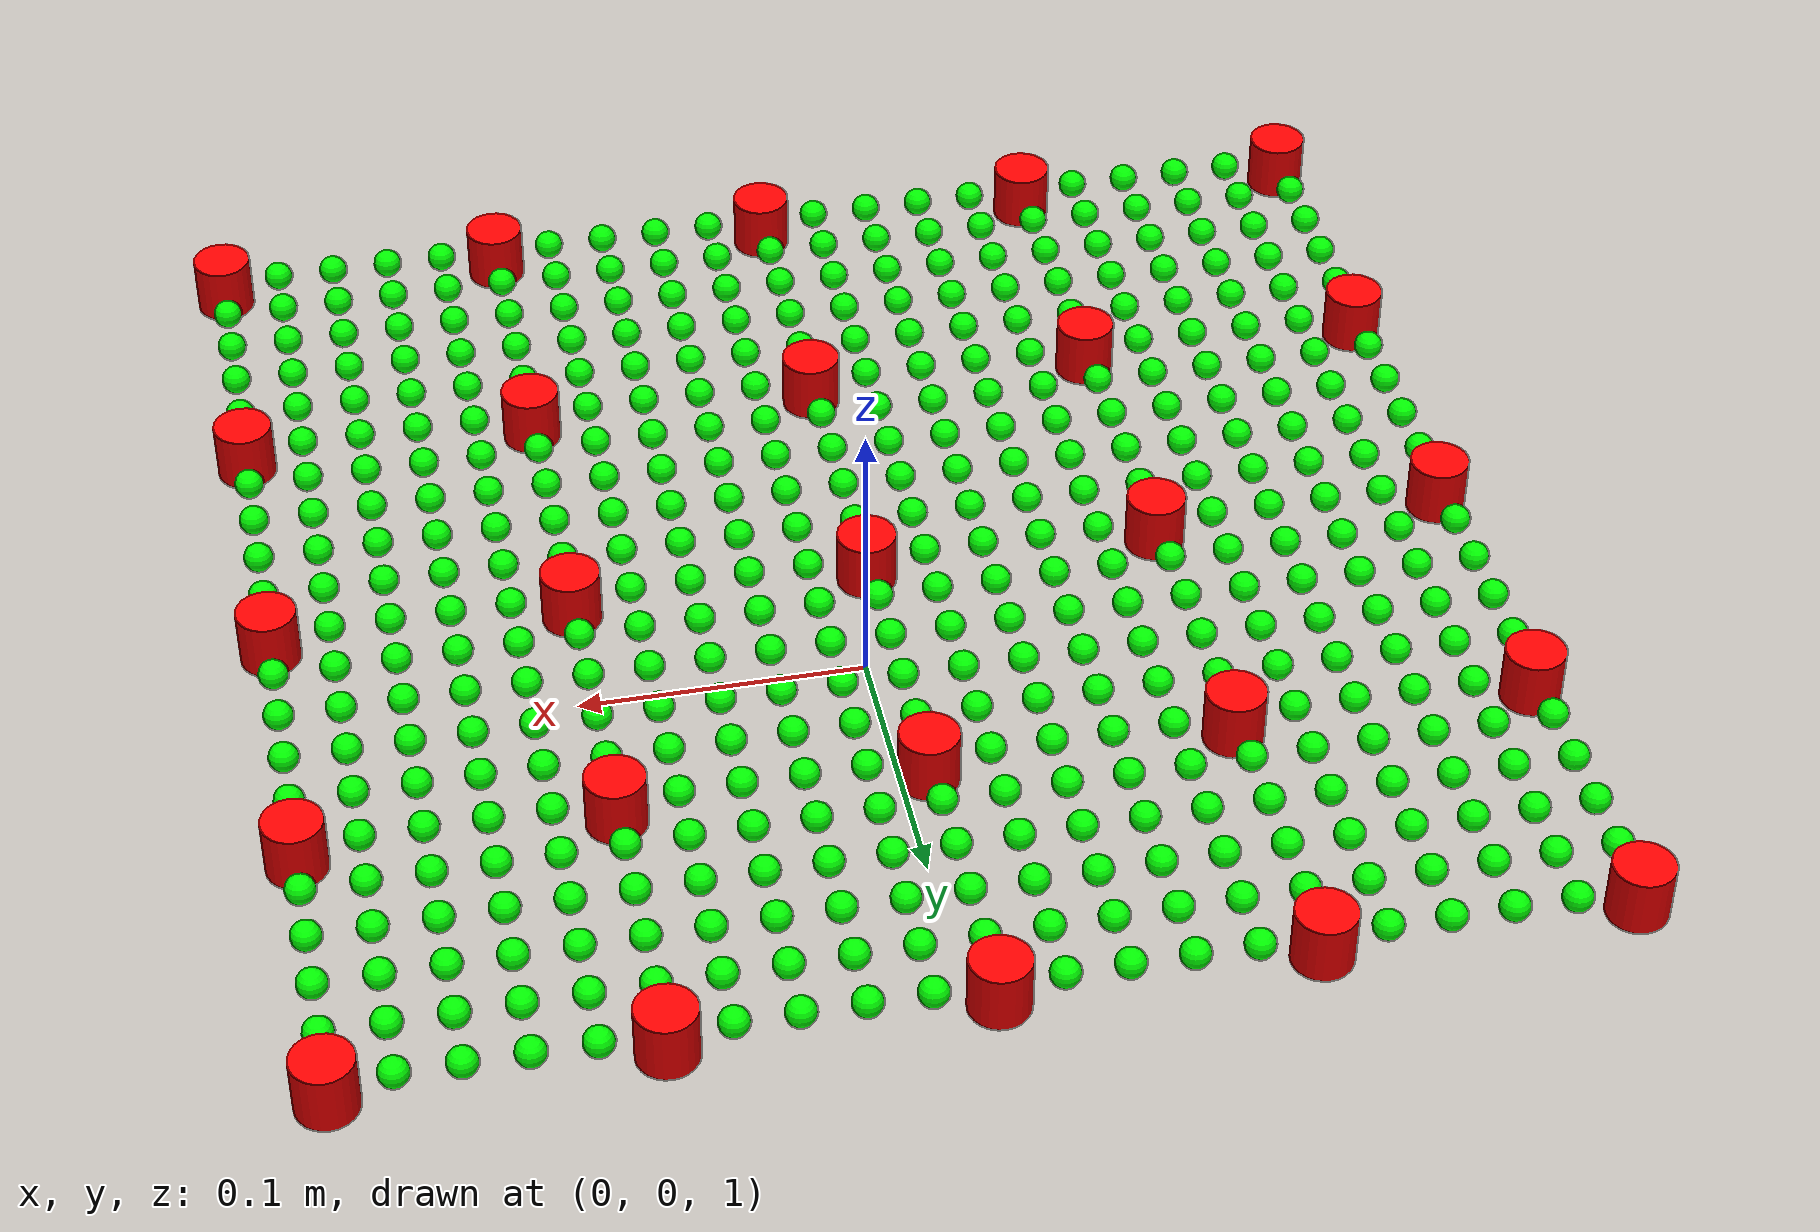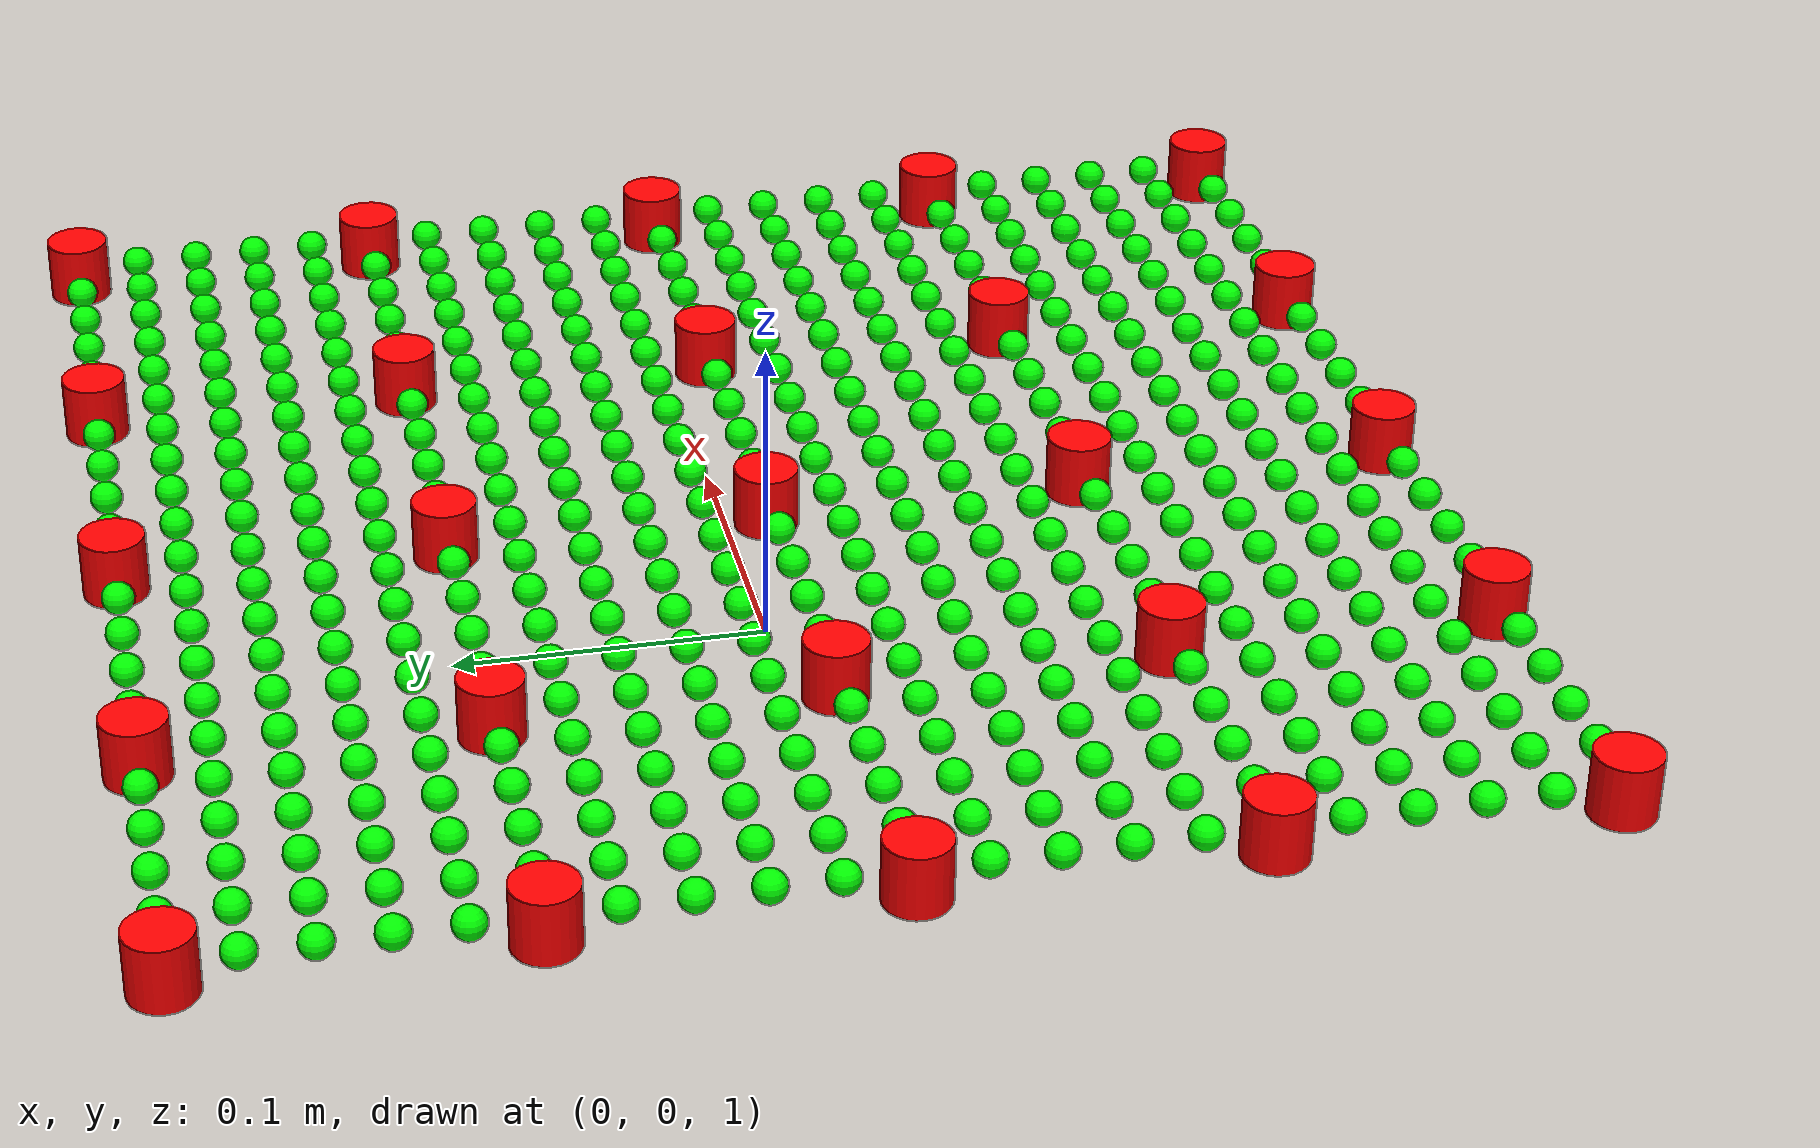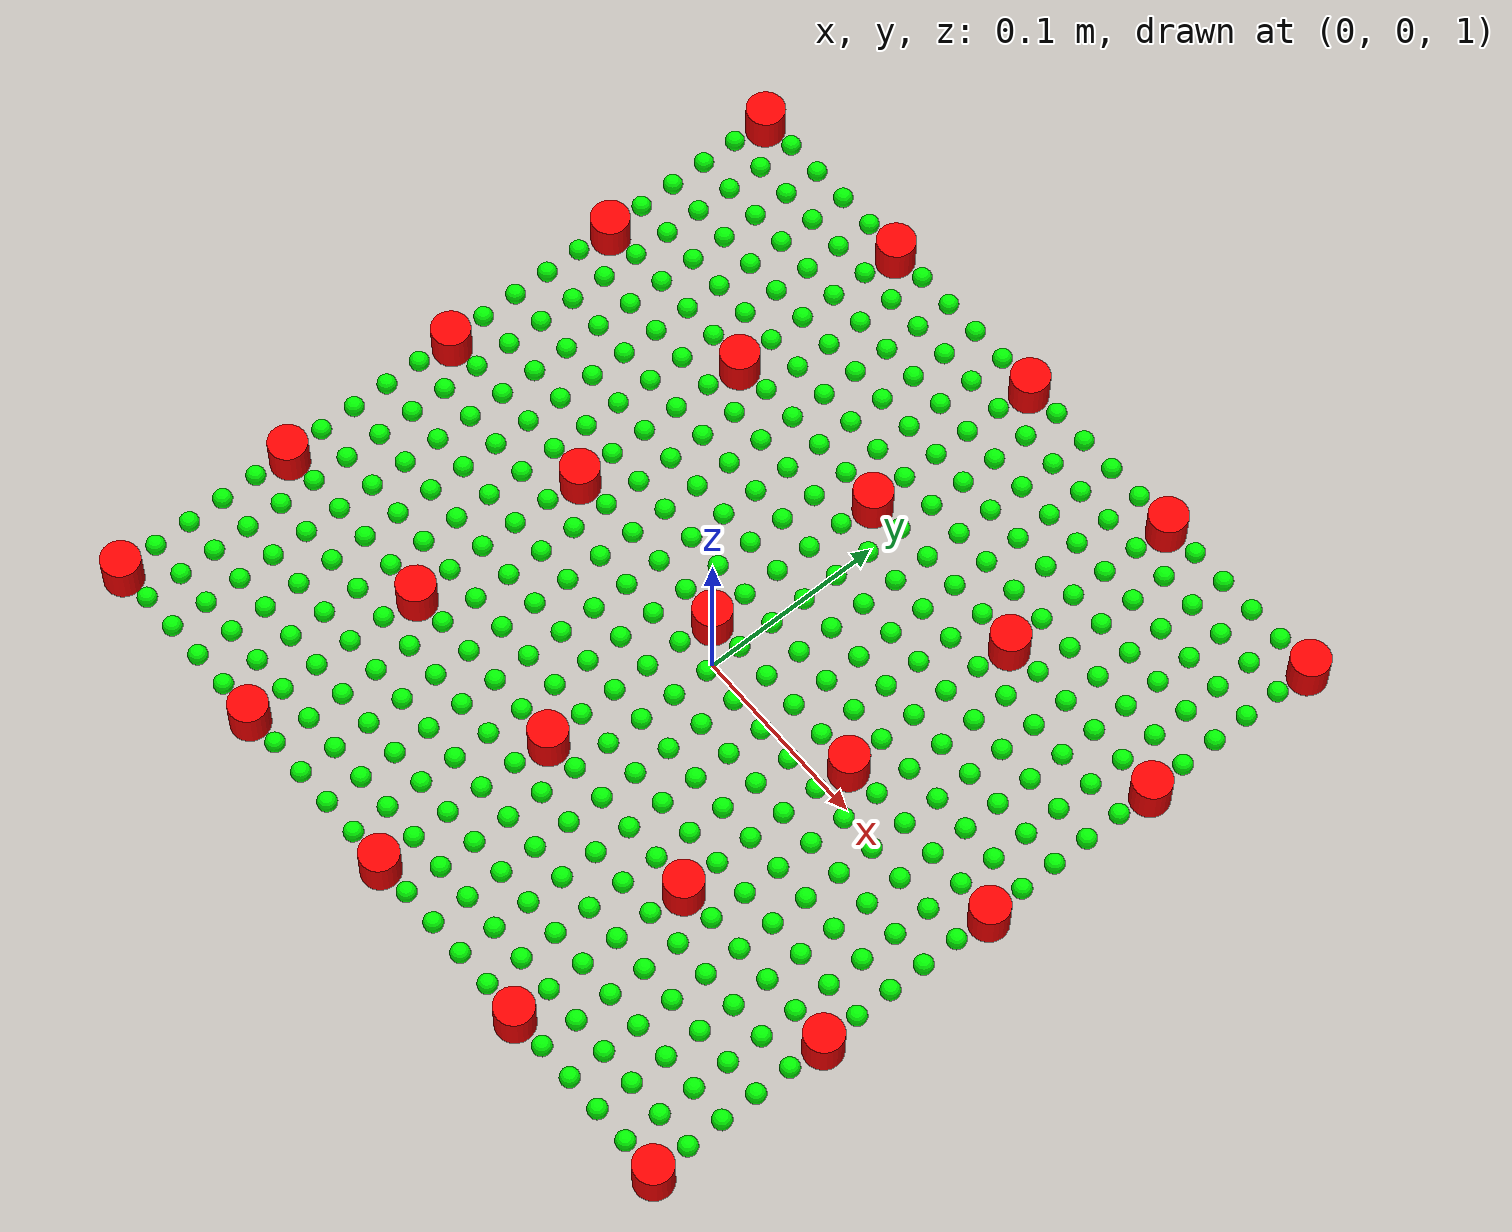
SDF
<sdf version="1.7">
  <model name="spring_damper_mesh">
    <static>false</static>
    <link name="mass_x-10_y-10">
      <pose>-0.2 -0.2 1.05 0 0 0</pose>
      <inertial>
        <mass>0.00022675736961451248</mass>
        <inertia>
          <ixx>1e-5</ixx>
          <ixy>0</ixy>
          <ixz>0</ixz>
          <iyy>1e-5</iyy>
          <iyz>0</iyz>
          <izz>1e-5</izz>
        </inertia>
      </inertial>
      <collision name="collision_x-10_y-10">
        <geometry>
          <sphere>
            <radius>0.001</radius>
          </sphere>
        </geometry>
      </collision>
      <visual name="visual_x-10_y-10">
        <material>
          <diffuse>1 0 0 1</diffuse>
        </material>
        <geometry>
          <cylinder>
            <length>0.02</length>
            <radius>0.01</radius>
          </cylinder>
        </geometry>
      </visual>
    </link>
    <link name="mass_x-9_y-10">
      <pose>-0.18 -0.2 1.05 0 0 0</pose>
      <inertial>
        <mass>0.00022675736961451248</mass>
        <inertia>
          <ixx>1e-5</ixx>
          <ixy>0</ixy>
          <ixz>0</ixz>
          <iyy>1e-5</iyy>
          <iyz>0</iyz>
          <izz>1e-5</izz>
        </inertia>
      </inertial>
      <collision name="collision_x-9_y-10">
        <geometry>
          <sphere>
            <radius>0.001</radius>
          </sphere>
        </geometry>
      </collision>
      <visual name="visual_x-9_y-10">
        <material>
          <diffuse>0 1 0 1</diffuse>
        </material>
        <geometry>
          <sphere>
            <radius>0.005</radius>
          </sphere>
        </geometry>
      </visual>
    </link>
    <link name="mass_x-8_y-10">
      <pose>-0.16 -0.2 1.05 0 0 0</pose>
      <inertial>
        <mass>0.00022675736961451248</mass>
        <inertia>
          <ixx>1e-5</ixx>
          <ixy>0</ixy>
          <ixz>0</ixz>
          <iyy>1e-5</iyy>
          <iyz>0</iyz>
          <izz>1e-5</izz>
        </inertia>
      </inertial>
      <collision name="collision_x-8_y-10">
        <geometry>
          <sphere>
            <radius>0.001</radius>
          </sphere>
        </geometry>
      </collision>
      <visual name="visual_x-8_y-10">
        <material>
          <diffuse>0 1 0 1</diffuse>
        </material>
        <geometry>
          <sphere>
            <radius>0.005</radius>
          </sphere>
        </geometry>
      </visual>
    </link>
    <link name="mass_x-7_y-10">
      <pose>-0.14 -0.2 1.05 0 0 0</pose>
      <inertial>
        <mass>0.00022675736961451248</mass>
        <inertia>
          <ixx>1e-5</ixx>
          <ixy>0</ixy>
          <ixz>0</ixz>
          <iyy>1e-5</iyy>
          <iyz>0</iyz>
          <izz>1e-5</izz>
        </inertia>
      </inertial>
      <collision name="collision_x-7_y-10">
        <geometry>
          <sphere>
            <radius>0.001</radius>
          </sphere>
        </geometry>
      </collision>
      <visual name="visual_x-7_y-10">
        <material>
          <diffuse>0 1 0 1</diffuse>
        </material>
        <geometry>
          <sphere>
            <radius>0.005</radius>
          </sphere>
        </geometry>
      </visual>
    </link>
    <link name="mass_x-6_y-10">
      <pose>-0.12 -0.2 1.05 0 0 0</pose>
      <inertial>
        <mass>0.00022675736961451248</mass>
        <inertia>
          <ixx>1e-5</ixx>
          <ixy>0</ixy>
          <ixz>0</ixz>
          <iyy>1e-5</iyy>
          <iyz>0</iyz>
          <izz>1e-5</izz>
        </inertia>
      </inertial>
      <collision name="collision_x-6_y-10">
        <geometry>
          <sphere>
            <radius>0.001</radius>
          </sphere>
        </geometry>
      </collision>
      <visual name="visual_x-6_y-10">
        <material>
          <diffuse>0 1 0 1</diffuse>
        </material>
        <geometry>
          <sphere>
            <radius>0.005</radius>
          </sphere>
        </geometry>
      </visual>
    </link>
    <link name="mass_x-5_y-10">
      <pose>-0.1 -0.2 1.05 0 0 0</pose>
      <inertial>
        <mass>0.00022675736961451248</mass>
        <inertia>
          <ixx>1e-5</ixx>
          <ixy>0</ixy>
          <ixz>0</ixz>
          <iyy>1e-5</iyy>
          <iyz>0</iyz>
          <izz>1e-5</izz>
        </inertia>
      </inertial>
      <collision name="collision_x-5_y-10">
        <geometry>
          <sphere>
            <radius>0.001</radius>
          </sphere>
        </geometry>
      </collision>
      <visual name="visual_x-5_y-10">
        <material>
          <diffuse>1 0 0 1</diffuse>
        </material>
        <geometry>
          <cylinder>
            <length>0.02</length>
            <radius>0.01</radius>
          </cylinder>
        </geometry>
      </visual>
    </link>
    <link name="mass_x-4_y-10">
      <pose>-0.08 -0.2 1.05 0 0 0</pose>
      <inertial>
        <mass>0.00022675736961451248</mass>
        <inertia>
          <ixx>1e-5</ixx>
          <ixy>0</ixy>
          <ixz>0</ixz>
          <iyy>1e-5</iyy>
          <iyz>0</iyz>
          <izz>1e-5</izz>
        </inertia>
      </inertial>
      <collision name="collision_x-4_y-10">
        <geometry>
          <sphere>
            <radius>0.001</radius>
          </sphere>
        </geometry>
      </collision>
      <visual name="visual_x-4_y-10">
        <material>
          <diffuse>0 1 0 1</diffuse>
        </material>
        <geometry>
          <sphere>
            <radius>0.005</radius>
          </sphere>
        </geometry>
      </visual>
    </link>
    <link name="mass_x-3_y-10">
      <pose>-0.06 -0.2 1.05 0 0 0</pose>
      <inertial>
        <mass>0.00022675736961451248</mass>
        <inertia>
          <ixx>1e-5</ixx>
          <ixy>0</ixy>
          <ixz>0</ixz>
          <iyy>1e-5</iyy>
          <iyz>0</iyz>
          <izz>1e-5</izz>
        </inertia>
      </inertial>
      <collision name="collision_x-3_y-10">
        <geometry>
          <sphere>
            <radius>0.001</radius>
          </sphere>
        </geometry>
      </collision>
      <visual name="visual_x-3_y-10">
        <material>
          <diffuse>0 1 0 1</diffuse>
        </material>
        <geometry>
          <sphere>
            <radius>0.005</radius>
          </sphere>
        </geometry>
      </visual>
    </link>
    <link name="mass_x-2_y-10">
      <pose>-0.04 -0.2 1.05 0 0 0</pose>
      <inertial>
        <mass>0.00022675736961451248</mass>
        <inertia>
          <ixx>1e-5</ixx>
          <ixy>0</ixy>
          <ixz>0</ixz>
          <iyy>1e-5</iyy>
          <iyz>0</iyz>
          <izz>1e-5</izz>
        </inertia>
      </inertial>
      <collision name="collision_x-2_y-10">
        <geometry>
          <sphere>
            <radius>0.001</radius>
          </sphere>
        </geometry>
      </collision>
      <visual name="visual_x-2_y-10">
        <material>
          <diffuse>0 1 0 1</diffuse>
        </material>
        <geometry>
          <sphere>
            <radius>0.005</radius>
          </sphere>
        </geometry>
      </visual>
    </link>
    <link name="mass_x-1_y-10">
      <pose>-0.02 -0.2 1.05 0 0 0</pose>
      <inertial>
        <mass>0.00022675736961451248</mass>
        <inertia>
          <ixx>1e-5</ixx>
          <ixy>0</ixy>
          <ixz>0</ixz>
          <iyy>1e-5</iyy>
          <iyz>0</iyz>
          <izz>1e-5</izz>
        </inertia>
      </inertial>
      <collision name="collision_x-1_y-10">
        <geometry>
          <sphere>
            <radius>0.001</radius>
          </sphere>
        </geometry>
      </collision>
      <visual name="visual_x-1_y-10">
        <material>
          <diffuse>0 1 0 1</diffuse>
        </material>
        <geometry>
          <sphere>
            <radius>0.005</radius>
          </sphere>
        </geometry>
      </visual>
    </link>
    <link name="mass_x0_y-10">
      <pose>0.0 -0.2 1.05 0 0 0</pose>
      <inertial>
        <mass>0.00022675736961451248</mass>
        <inertia>
          <ixx>1e-5</ixx>
          <ixy>0</ixy>
          <ixz>0</ixz>
          <iyy>1e-5</iyy>
          <iyz>0</iyz>
          <izz>1e-5</izz>
        </inertia>
      </inertial>
      <collision name="collision_x0_y-10">
        <geometry>
          <sphere>
            <radius>0.001</radius>
          </sphere>
        </geometry>
      </collision>
      <visual name="visual_x0_y-10">
        <material>
          <diffuse>1 0 0 1</diffuse>
        </material>
        <geometry>
          <cylinder>
            <length>0.02</length>
            <radius>0.01</radius>
          </cylinder>
        </geometry>
      </visual>
    </link>
    <link name="mass_x1_y-10">
      <pose>0.02 -0.2 1.05 0 0 0</pose>
      <inertial>
        <mass>0.00022675736961451248</mass>
        <inertia>
          <ixx>1e-5</ixx>
          <ixy>0</ixy>
          <ixz>0</ixz>
          <iyy>1e-5</iyy>
          <iyz>0</iyz>
          <izz>1e-5</izz>
        </inertia>
      </inertial>
      <collision name="collision_x1_y-10">
        <geometry>
          <sphere>
            <radius>0.001</radius>
          </sphere>
        </geometry>
      </collision>
      <visual name="visual_x1_y-10">
        <material>
          <diffuse>0 1 0 1</diffuse>
        </material>
        <geometry>
          <sphere>
            <radius>0.005</radius>
          </sphere>
        </geometry>
      </visual>
    </link>
    <link name="mass_x2_y-10">
      <pose>0.04 -0.2 1.05 0 0 0</pose>
      <inertial>
        <mass>0.00022675736961451248</mass>
        <inertia>
          <ixx>1e-5</ixx>
          <ixy>0</ixy>
          <ixz>0</ixz>
          <iyy>1e-5</iyy>
          <iyz>0</iyz>
          <izz>1e-5</izz>
        </inertia>
      </inertial>
      <collision name="collision_x2_y-10">
        <geometry>
          <sphere>
            <radius>0.001</radius>
          </sphere>
        </geometry>
      </collision>
      <visual name="visual_x2_y-10">
        <material>
          <diffuse>0 1 0 1</diffuse>
        </material>
        <geometry>
          <sphere>
            <radius>0.005</radius>
          </sphere>
        </geometry>
      </visual>
    </link>
    <link name="mass_x3_y-10">
      <pose>0.06 -0.2 1.05 0 0 0</pose>
      <inertial>
        <mass>0.00022675736961451248</mass>
        <inertia>
          <ixx>1e-5</ixx>
          <ixy>0</ixy>
          <ixz>0</ixz>
          <iyy>1e-5</iyy>
          <iyz>0</iyz>
          <izz>1e-5</izz>
        </inertia>
      </inertial>
      <collision name="collision_x3_y-10">
        <geometry>
          <sphere>
            <radius>0.001</radius>
          </sphere>
        </geometry>
      </collision>
      <visual name="visual_x3_y-10">
        <material>
          <diffuse>0 1 0 1</diffuse>
        </material>
        <geometry>
          <sphere>
            <radius>0.005</radius>
          </sphere>
        </geometry>
      </visual>
    </link>
    <link name="mass_x4_y-10">
      <pose>0.08 -0.2 1.05 0 0 0</pose>
      <inertial>
        <mass>0.00022675736961451248</mass>
        <inertia>
          <ixx>1e-5</ixx>
          <ixy>0</ixy>
          <ixz>0</ixz>
          <iyy>1e-5</iyy>
          <iyz>0</iyz>
          <izz>1e-5</izz>
        </inertia>
      </inertial>
      <collision name="collision_x4_y-10">
        <geometry>
          <sphere>
            <radius>0.001</radius>
          </sphere>
        </geometry>
      </collision>
      <visual name="visual_x4_y-10">
        <material>
          <diffuse>0 1 0 1</diffuse>
        </material>
        <geometry>
          <sphere>
            <radius>0.005</radius>
          </sphere>
        </geometry>
      </visual>
    </link>
    <link name="mass_x5_y-10">
      <pose>0.1 -0.2 1.05 0 0 0</pose>
      <inertial>
        <mass>0.00022675736961451248</mass>
        <inertia>
          <ixx>1e-5</ixx>
          <ixy>0</ixy>
          <ixz>0</ixz>
          <iyy>1e-5</iyy>
          <iyz>0</iyz>
          <izz>1e-5</izz>
        </inertia>
      </inertial>
      <collision name="collision_x5_y-10">
        <geometry>
          <sphere>
            <radius>0.001</radius>
          </sphere>
        </geometry>
      </collision>
      <visual name="visual_x5_y-10">
        <material>
          <diffuse>1 0 0 1</diffuse>
        </material>
        <geometry>
          <cylinder>
            <length>0.02</length>
            <radius>0.01</radius>
          </cylinder>
        </geometry>
      </visual>
    </link>
    <link name="mass_x6_y-10">
      <pose>0.12 -0.2 1.05 0 0 0</pose>
      <inertial>
        <mass>0.00022675736961451248</mass>
        <inertia>
          <ixx>1e-5</ixx>
          <ixy>0</ixy>
          <ixz>0</ixz>
          <iyy>1e-5</iyy>
          <iyz>0</iyz>
          <izz>1e-5</izz>
        </inertia>
      </inertial>
      <collision name="collision_x6_y-10">
        <geometry>
          <sphere>
            <radius>0.001</radius>
          </sphere>
        </geometry>
      </collision>
      <visual name="visual_x6_y-10">
        <material>
          <diffuse>0 1 0 1</diffuse>
        </material>
        <geometry>
          <sphere>
            <radius>0.005</radius>
          </sphere>
        </geometry>
      </visual>
    </link>
    <link name="mass_x7_y-10">
      <pose>0.14 -0.2 1.05 0 0 0</pose>
      <inertial>
        <mass>0.00022675736961451248</mass>
        <inertia>
          <ixx>1e-5</ixx>
          <ixy>0</ixy>
          <ixz>0</ixz>
          <iyy>1e-5</iyy>
          <iyz>0</iyz>
          <izz>1e-5</izz>
        </inertia>
      </inertial>
      <collision name="collision_x7_y-10">
        <geometry>
          <sphere>
            <radius>0.001</radius>
          </sphere>
        </geometry>
      </collision>
      <visual name="visual_x7_y-10">
        <material>
          <diffuse>0 1 0 1</diffuse>
        </material>
        <geometry>
          <sphere>
            <radius>0.005</radius>
          </sphere>
        </geometry>
      </visual>
    </link>
    <link name="mass_x8_y-10">
      <pose>0.16 -0.2 1.05 0 0 0</pose>
      <inertial>
        <mass>0.00022675736961451248</mass>
        <inertia>
          <ixx>1e-5</ixx>
          <ixy>0</ixy>
          <ixz>0</ixz>
          <iyy>1e-5</iyy>
          <iyz>0</iyz>
          <izz>1e-5</izz>
        </inertia>
      </inertial>
      <collision name="collision_x8_y-10">
        <geometry>
          <sphere>
            <radius>0.001</radius>
          </sphere>
        </geometry>
      </collision>
      <visual name="visual_x8_y-10">
        <material>
          <diffuse>0 1 0 1</diffuse>
        </material>
        <geometry>
          <sphere>
            <radius>0.005</radius>
          </sphere>
        </geometry>
      </visual>
    </link>
    <link name="mass_x9_y-10">
      <pose>0.18 -0.2 1.05 0 0 0</pose>
      <inertial>
        <mass>0.00022675736961451248</mass>
        <inertia>
          <ixx>1e-5</ixx>
          <ixy>0</ixy>
          <ixz>0</ixz>
          <iyy>1e-5</iyy>
          <iyz>0</iyz>
          <izz>1e-5</izz>
        </inertia>
      </inertial>
      <collision name="collision_x9_y-10">
        <geometry>
          <sphere>
            <radius>0.001</radius>
          </sphere>
        </geometry>
      </collision>
      <visual name="visual_x9_y-10">
        <material>
          <diffuse>0 1 0 1</diffuse>
        </material>
        <geometry>
          <sphere>
            <radius>0.005</radius>
          </sphere>
        </geometry>
      </visual>
    </link>
    <link name="mass_x10_y-10">
      <pose>0.2 -0.2 1.05 0 0 0</pose>
      <inertial>
        <mass>0.00022675736961451248</mass>
        <inertia>
          <ixx>1e-5</ixx>
          <ixy>0</ixy>
          <ixz>0</ixz>
          <iyy>1e-5</iyy>
          <iyz>0</iyz>
          <izz>1e-5</izz>
        </inertia>
      </inertial>
      <collision name="collision_x10_y-10">
        <geometry>
          <sphere>
            <radius>0.001</radius>
          </sphere>
        </geometry>
      </collision>
      <visual name="visual_x10_y-10">
        <material>
          <diffuse>1 0 0 1</diffuse>
        </material>
        <geometry>
          <cylinder>
            <length>0.02</length>
            <radius>0.01</radius>
          </cylinder>
        </geometry>
      </visual>
    </link>
    <link name="mass_x-10_y-9">
      <pose>-0.2 -0.18 1.05 0 0 0</pose>
      <inertial>
        <mass>0.00022675736961451248</mass>
        <inertia>
          <ixx>1e-5</ixx>
          <ixy>0</ixy>
          <ixz>0</ixz>
          <iyy>1e-5</iyy>
          <iyz>0</iyz>
          <izz>1e-5</izz>
        </inertia>
      </inertial>
      <collision name="collision_x-10_y-9">
        <geometry>
          <sphere>
            <radius>0.001</radius>
          </sphere>
        </geometry>
      </collision>
      <visual name="visual_x-10_y-9">
        <material>
          <diffuse>0 1 0 1</diffuse>
        </material>
        <geometry>
          <sphere>
            <radius>0.005</radius>
          </sphere>
        </geometry>
      </visual>
    </link>
    <link name="mass_x-9_y-9">
      <pose>-0.18 -0.18 1.05 0 0 0</pose>
      <inertial>
        <mass>0.00022675736961451248</mass>
        <inertia>
          <ixx>1e-5</ixx>
          <ixy>0</ixy>
          <ixz>0</ixz>
          <iyy>1e-5</iyy>
          <iyz>0</iyz>
          <izz>1e-5</izz>
        </inertia>
      </inertial>
      <collision name="collision_x-9_y-9">
        <geometry>
          <sphere>
            <radius>0.001</radius>
          </sphere>
        </geometry>
      </collision>
      <visual name="visual_x-9_y-9">
        <material>
          <diffuse>0 1 0 1</diffuse>
        </material>
        <geometry>
          <sphere>
            <radius>0.005</radius>
          </sphere>
        </geometry>
      </visual>
    </link>
    <link name="mass_x-8_y-9">
      <pose>-0.16 -0.18 1.05 0 0 0</pose>
      <inertial>
        <mass>0.00022675736961451248</mass>
        <inertia>
          <ixx>1e-5</ixx>
          <ixy>0</ixy>
          <ixz>0</ixz>
          <iyy>1e-5</iyy>
          <iyz>0</iyz>
          <izz>1e-5</izz>
        </inertia>
      </inertial>
      <collision name="collision_x-8_y-9">
        <geometry>
          <sphere>
            <radius>0.001</radius>
          </sphere>
        </geometry>
      </collision>
      <visual name="visual_x-8_y-9">
        <material>
          <diffuse>0 1 0 1</diffuse>
        </material>
        <geometry>
          <sphere>
            <radius>0.005</radius>
          </sphere>
        </geometry>
      </visual>
    </link>
    <link name="mass_x-7_y-9">
      <pose>-0.14 -0.18 1.05 0 0 0</pose>
      <inertial>
        <mass>0.00022675736961451248</mass>
        <inertia>
          <ixx>1e-5</ixx>
          <ixy>0</ixy>
          <ixz>0</ixz>
          <iyy>1e-5</iyy>
          <iyz>0</iyz>
          <izz>1e-5</izz>
        </inertia>
      </inertial>
      <collision name="collision_x-7_y-9">
        <geometry>
          <sphere>
            <radius>0.001</radius>
          </sphere>
        </geometry>
      </collision>
      <visual name="visual_x-7_y-9">
        <material>
          <diffuse>0 1 0 1</diffuse>
        </material>
        <geometry>
          <sphere>
            <radius>0.005</radius>
          </sphere>
        </geometry>
      </visual>
    </link>
    <link name="mass_x-6_y-9">
      <pose>-0.12 -0.18 1.05 0 0 0</pose>
      <inertial>
        <mass>0.00022675736961451248</mass>
        <inertia>
          <ixx>1e-5</ixx>
          <ixy>0</ixy>
          <ixz>0</ixz>
          <iyy>1e-5</iyy>
          <iyz>0</iyz>
          <izz>1e-5</izz>
        </inertia>
      </inertial>
      <collision name="collision_x-6_y-9">
        <geometry>
          <sphere>
            <radius>0.001</radius>
          </sphere>
        </geometry>
      </collision>
      <visual name="visual_x-6_y-9">
        <material>
          <diffuse>0 1 0 1</diffuse>
        </material>
        <geometry>
          <sphere>
            <radius>0.005</radius>
          </sphere>
        </geometry>
      </visual>
    </link>
    <link name="mass_x-5_y-9">
      <pose>-0.1 -0.18 1.05 0 0 0</pose>
      <inertial>
        <mass>0.00022675736961451248</mass>
        <inertia>
          <ixx>1e-5</ixx>
          <ixy>0</ixy>
          <ixz>0</ixz>
          <iyy>1e-5</iyy>
          <iyz>0</iyz>
          <izz>1e-5</izz>
        </inertia>
      </inertial>
      <collision name="collision_x-5_y-9">
        <geometry>
          <sphere>
            <radius>0.001</radius>
          </sphere>
        </geometry>
      </collision>
      <visual name="visual_x-5_y-9">
        <material>
          <diffuse>0 1 0 1</diffuse>
        </material>
        <geometry>
          <sphere>
            <radius>0.005</radius>
          </sphere>
        </geometry>
      </visual>
    </link>
    <link name="mass_x-4_y-9">
      <pose>-0.08 -0.18 1.05 0 0 0</pose>
      <inertial>
        <mass>0.00022675736961451248</mass>
        <inertia>
          <ixx>1e-5</ixx>
          <ixy>0</ixy>
          <ixz>0</ixz>
          <iyy>1e-5</iyy>
          <iyz>0</iyz>
          <izz>1e-5</izz>
        </inertia>
      </inertial>
      <collision name="collision_x-4_y-9">
        <geometry>
          <sphere>
            <radius>0.001</radius>
          </sphere>
        </geometry>
      </collision>
      <visual name="visual_x-4_y-9">
        <material>
          <diffuse>0 1 0 1</diffuse>
        </material>
        <geometry>
          <sphere>
            <radius>0.005</radius>
          </sphere>
        </geometry>
      </visual>
    </link>
    <link name="mass_x-3_y-9">
      <pose>-0.06 -0.18 1.05 0 0 0</pose>
      <inertial>
        <mass>0.00022675736961451248</mass>
        <inertia>
          <ixx>1e-5</ixx>
          <ixy>0</ixy>
          <ixz>0</ixz>
          <iyy>1e-5</iyy>
          <iyz>0</iyz>
          <izz>1e-5</izz>
        </inertia>
      </inertial>
      <collision name="collision_x-3_y-9">
        <geometry>
          <sphere>
            <radius>0.001</radius>
          </sphere>
        </geometry>
      </collision>
      <visual name="visual_x-3_y-9">
        <material>
          <diffuse>0 1 0 1</diffuse>
        </material>
        <geometry>
          <sphere>
            <radius>0.005</radius>
          </sphere>
        </geometry>
      </visual>
    </link>
    <link name="mass_x-2_y-9">
      <pose>-0.04 -0.18 1.05 0 0 0</pose>
      <inertial>
        <mass>0.00022675736961451248</mass>
        <inertia>
          <ixx>1e-5</ixx>
          <ixy>0</ixy>
          <ixz>0</ixz>
          <iyy>1e-5</iyy>
          <iyz>0</iyz>
          <izz>1e-5</izz>
        </inertia>
      </inertial>
      <collision name="collision_x-2_y-9">
        <geometry>
          <sphere>
            <radius>0.001</radius>
          </sphere>
        </geometry>
      </collision>
      <visual name="visual_x-2_y-9">
        <material>
          <diffuse>0 1 0 1</diffuse>
        </material>
        <geometry>
          <sphere>
            <radius>0.005</radius>
          </sphere>
        </geometry>
      </visual>
    </link>
    <link name="mass_x-1_y-9">
      <pose>-0.02 -0.18 1.05 0 0 0</pose>
      <inertial>
        <mass>0.00022675736961451248</mass>
        <inertia>
          <ixx>1e-5</ixx>
          <ixy>0</ixy>
          <ixz>0</ixz>
          <iyy>1e-5</iyy>
          <iyz>0</iyz>
          <izz>1e-5</izz>
        </inertia>
      </inertial>
      <collision name="collision_x-1_y-9">
        <geometry>
          <sphere>
            <radius>0.001</radius>
          </sphere>
        </geometry>
      </collision>
      <visual name="visual_x-1_y-9">
        <material>
          <diffuse>0 1 0 1</diffuse>
        </material>
        <geometry>
          <sphere>
            <radius>0.005</radius>
          </sphere>
        </geometry>
      </visual>
    </link>
    <link name="mass_x0_y-9">
      <pose>0.0 -0.18 1.05 0 0 0</pose>
      <inertial>
        <mass>0.00022675736961451248</mass>
        <inertia>
          <ixx>1e-5</ixx>
          <ixy>0</ixy>
          <ixz>0</ixz>
          <iyy>1e-5</iyy>
          <iyz>0</iyz>
          <izz>1e-5</izz>
        </inertia>
      </inertial>
      <collision name="collision_x0_y-9">
        <geometry>
          <sphere>
            <radius>0.001</radius>
          </sphere>
        </geometry>
      </collision>
      <visual name="visual_x0_y-9">
        <material>
          <diffuse>0 1 0 1</diffuse>
        </material>
        <geometry>
          <sphere>
            <radius>0.005</radius>
          </sphere>
        </geometry>
      </visual>
    </link>
    <link name="mass_x1_y-9">
      <pose>0.02 -0.18 1.05 0 0 0</pose>
      <inertial>
        <mass>0.00022675736961451248</mass>
        <inertia>
          <ixx>1e-5</ixx>
          <ixy>0</ixy>
          <ixz>0</ixz>
          <iyy>1e-5</iyy>
          <iyz>0</iyz>
          <izz>1e-5</izz>
        </inertia>
      </inertial>
      <collision name="collision_x1_y-9">
        <geometry>
          <sphere>
            <radius>0.001</radius>
          </sphere>
        </geometry>
      </collision>
      <visual name="visual_x1_y-9">
        <material>
          <diffuse>0 1 0 1</diffuse>
        </material>
        <geometry>
          <sphere>
            <radius>0.005</radius>
          </sphere>
        </geometry>
      </visual>
    </link>
    <link name="mass_x2_y-9">
      <pose>0.04 -0.18 1.05 0 0 0</pose>
      <inertial>
        <mass>0.00022675736961451248</mass>
        <inertia>
          <ixx>1e-5</ixx>
          <ixy>0</ixy>
          <ixz>0</ixz>
          <iyy>1e-5</iyy>
          <iyz>0</iyz>
          <izz>1e-5</izz>
        </inertia>
      </inertial>
      <collision name="collision_x2_y-9">
        <geometry>
          <sphere>
            <radius>0.001</radius>
          </sphere>
        </geometry>
      </collision>
      <visual name="visual_x2_y-9">
        <material>
          <diffuse>0 1 0 1</diffuse>
        </material>
        <geometry>
          <sphere>
            <radius>0.005</radius>
          </sphere>
        </geometry>
      </visual>
    </link>
    <link name="mass_x3_y-9">
      <pose>0.06 -0.18 1.05 0 0 0</pose>
      <inertial>
        <mass>0.00022675736961451248</mass>
        <inertia>
          <ixx>1e-5</ixx>
          <ixy>0</ixy>
          <ixz>0</ixz>
          <iyy>1e-5</iyy>
          <iyz>0</iyz>
          <izz>1e-5</izz>
        </inertia>
      </inertial>
      <collision name="collision_x3_y-9">
        <geometry>
          <sphere>
            <radius>0.001</radius>
          </sphere>
        </geometry>
      </collision>
      <visual name="visual_x3_y-9">
        <material>
          <diffuse>0 1 0 1</diffuse>
        </material>
        <geometry>
          <sphere>
            <radius>0.005</radius>
          </sphere>
        </geometry>
      </visual>
    </link>
    <link name="mass_x4_y-9">
      <pose>0.08 -0.18 1.05 0 0 0</pose>
      <inertial>
        <mass>0.00022675736961451248</mass>
        <inertia>
          <ixx>1e-5</ixx>
          <ixy>0</ixy>
          <ixz>0</ixz>
          <iyy>1e-5</iyy>
          <iyz>0</iyz>
          <izz>1e-5</izz>
        </inertia>
      </inertial>
      <collision name="collision_x4_y-9">
        <geometry>
          <sphere>
            <radius>0.001</radius>
          </sphere>
        </geometry>
      </collision>
      <visual name="visual_x4_y-9">
        <material>
          <diffuse>0 1 0 1</diffuse>
        </material>
        <geometry>
          <sphere>
            <radius>0.005</radius>
          </sphere>
        </geometry>
      </visual>
    </link>
    <link name="mass_x5_y-9">
      <pose>0.1 -0.18 1.05 0 0 0</pose>
      <inertial>
        <mass>0.00022675736961451248</mass>
        <inertia>
          <ixx>1e-5</ixx>
          <ixy>0</ixy>
          <ixz>0</ixz>
          <iyy>1e-5</iyy>
          <iyz>0</iyz>
          <izz>1e-5</izz>
        </inertia>
      </inertial>
      <collision name="collision_x5_y-9">
        <geometry>
          <sphere>
            <radius>0.001</radius>
          </sphere>
        </geometry>
      </collision>
      <visual name="visual_x5_y-9">
        <material>
          <diffuse>0 1 0 1</diffuse>
        </material>
        <geometry>
          <sphere>
            <radius>0.005</radius>
          </sphere>
        </geometry>
      </visual>
    </link>
    <link name="mass_x6_y-9">
      <pose>0.12 -0.18 1.05 0 0 0</pose>
      <inertial>
        <mass>0.00022675736961451248</mass>
        <inertia>
          <ixx>1e-5</ixx>
          <ixy>0</ixy>
          <ixz>0</ixz>
          <iyy>1e-5</iyy>
          <iyz>0</iyz>
          <izz>1e-5</izz>
        </inertia>
      </inertial>
      <collision name="collision_x6_y-9">
        <geometry>
          <sphere>
            <radius>0.001</radius>
          </sphere>
        </geometry>
      </collision>
      <visual name="visual_x6_y-9">
        <material>
          <diffuse>0 1 0 1</diffuse>
        </material>
        <geometry>
          <sphere>
            <radius>0.005</radius>
          </sphere>
        </geometry>
      </visual>
    </link>
    <link name="mass_x7_y-9">
      <pose>0.14 -0.18 1.05 0 0 0</pose>
      <inertial>
        <mass>0.00022675736961451248</mass>
        <inertia>
          <ixx>1e-5</ixx>
          <ixy>0</ixy>
          <ixz>0</ixz>
          <iyy>1e-5</iyy>
          <iyz>0</iyz>
          <izz>1e-5</izz>
        </inertia>
      </inertial>
      <collision name="collision_x7_y-9">
        <geometry>
          <sphere>
            <radius>0.001</radius>
          </sphere>
        </geometry>
      </collision>
      <visual name="visual_x7_y-9">
        <material>
          <diffuse>0 1 0 1</diffuse>
        </material>
        <geometry>
          <sphere>
            <radius>0.005</radius>
          </sphere>
        </geometry>
      </visual>
    </link>
    <link name="mass_x8_y-9">
      <pose>0.16 -0.18 1.05 0 0 0</pose>
      <inertial>
        <mass>0.00022675736961451248</mass>
        <inertia>
          <ixx>1e-5</ixx>
          <ixy>0</ixy>
          <ixz>0</ixz>
          <iyy>1e-5</iyy>
          <iyz>0</iyz>
          <izz>1e-5</izz>
        </inertia>
      </inertial>
      <collision name="collision_x8_y-9">
        <geometry>
          <sphere>
            <radius>0.001</radius>
          </sphere>
        </geometry>
      </collision>
      <visual name="visual_x8_y-9">
        <material>
          <diffuse>0 1 0 1</diffuse>
        </material>
        <geometry>
          <sphere>
            <radius>0.005</radius>
          </sphere>
        </geometry>
      </visual>
    </link>
    <link name="mass_x9_y-9">
      <pose>0.18 -0.18 1.05 0 0 0</pose>
      <inertial>
        <mass>0.00022675736961451248</mass>
        <inertia>
          <ixx>1e-5</ixx>
          <ixy>0</ixy>
          <ixz>0</ixz>
          <iyy>1e-5</iyy>
          <iyz>0</iyz>
          <izz>1e-5</izz>
        </inertia>
      </inertial>
      <collision name="collision_x9_y-9">
        <geometry>
          <sphere>
            <radius>0.001</radius>
          </sphere>
        </geometry>
      </collision>
      <visual name="visual_x9_y-9">
        <material>
          <diffuse>0 1 0 1</diffuse>
        </material>
        <geometry>
          <sphere>
            <radius>0.005</radius>
          </sphere>
        </geometry>
      </visual>
    </link>
    <link name="mass_x10_y-9">
      <pose>0.2 -0.18 1.05 0 0 0</pose>
      <inertial>
        <mass>0.00022675736961451248</mass>
        <inertia>
          <ixx>1e-5</ixx>
          <ixy>0</ixy>
          <ixz>0</ixz>
          <iyy>1e-5</iyy>
          <iyz>0</iyz>
          <izz>1e-5</izz>
        </inertia>
      </inertial>
      <collision name="collision_x10_y-9">
        <geometry>
          <sphere>
            <radius>0.001</radius>
          </sphere>
        </geometry>
      </collision>
      <visual name="visual_x10_y-9">
        <material>
          <diffuse>0 1 0 1</diffuse>
        </material>
        <geometry>
          <sphere>
            <radius>0.005</radius>
          </sphere>
        </geometry>
      </visual>
    </link>
    <link name="mass_x-10_y-8">
      <pose>-0.2 -0.16 1.05 0 0 0</pose>
      <inertial>
        <mass>0.00022675736961451248</mass>
        <inertia>
          <ixx>1e-5</ixx>
          <ixy>0</ixy>
          <ixz>0</ixz>
          <iyy>1e-5</iyy>
          <iyz>0</iyz>
          <izz>1e-5</izz>
        </inertia>
      </inertial>
      <collision name="collision_x-10_y-8">
        <geometry>
          <sphere>
            <radius>0.001</radius>
          </sphere>
        </geometry>
      </collision>
      <visual name="visual_x-10_y-8">
        <material>
          <diffuse>0 1 0 1</diffuse>
        </material>
        <geometry>
          <sphere>
            <radius>0.005</radius>
          </sphere>
        </geometry>
      </visual>
    </link>
    <link name="mass_x-9_y-8">
      <pose>-0.18 -0.16 1.05 0 0 0</pose>
      <inertial>
        <mass>0.00022675736961451248</mass>
        <inertia>
          <ixx>1e-5</ixx>
          <ixy>0</ixy>
          <ixz>0</ixz>
          <iyy>1e-5</iyy>
          <iyz>0</iyz>
          <izz>1e-5</izz>
        </inertia>
      </inertial>
      <collision name="collision_x-9_y-8">
        <geometry>
          <sphere>
            <radius>0.001</radius>
          </sphere>
        </geometry>
      </collision>
      <visual name="visual_x-9_y-8">
        <material>
          <diffuse>0 1 0 1</diffuse>
        </material>
        <geometry>
          <sphere>
            <radius>0.005</radius>
          </sphere>
        </geometry>
      </visual>
    </link>
    <link name="mass_x-8_y-8">
      <pose>-0.16 -0.16 1.05 0 0 0</pose>
      <inertial>
        <mass>0.00022675736961451248</mass>
        <inertia>
          <ixx>1e-5</ixx>
          <ixy>0</ixy>
          <ixz>0</ixz>
          <iyy>1e-5</iyy>
          <iyz>0</iyz>
          <izz>1e-5</izz>
        </inertia>
      </inertial>
      <collision name="collision_x-8_y-8">
        <geometry>
          <sphere>
            <radius>0.001</radius>
          </sphere>
        </geometry>
      </collision>
      <visual name="visual_x-8_y-8">
        <material>
          <diffuse>0 1 0 1</diffuse>
        </material>
        <geometry>
          <sphere>
            <radius>0.005</radius>
          </sphere>
        </geometry>
      </visual>
    </link>
    <link name="mass_x-7_y-8">
      <pose>-0.14 -0.16 1.05 0 0 0</pose>
      <inertial>
        <mass>0.00022675736961451248</mass>
        <inertia>
          <ixx>1e-5</ixx>
          <ixy>0</ixy>
          <ixz>0</ixz>
          <iyy>1e-5</iyy>
          <iyz>0</iyz>
          <izz>1e-5</izz>
        </inertia>
      </inertial>
      <collision name="collision_x-7_y-8">
        <geometry>
          <sphere>
            <radius>0.001</radius>
          </sphere>
        </geometry>
      </collision>
      <visual name="visual_x-7_y-8">
        <material>
          <diffuse>0 1 0 1</diffuse>
        </material>
        <geometry>
          <sphere>
            <radius>0.005</radius>
          </sphere>
        </geometry>
      </visual>
    </link>
    <link name="mass_x-6_y-8">
      <pose>-0.12 -0.16 1.05 0 0 0</pose>
      <inertial>
        <mass>0.00022675736961451248</mass>
        <inertia>
          <ixx>1e-5</ixx>
          <ixy>0</ixy>
          <ixz>0</ixz>
          <iyy>1e-5</iyy>
          <iyz>0</iyz>
          <izz>1e-5</izz>
        </inertia>
      </inertial>
      <collision name="collision_x-6_y-8">
        <geometry>
          <sphere>
            <radius>0.001</radius>
          </sphere>
        </geometry>
      </collision>
      <visual name="visual_x-6_y-8">
        <material>
          <diffuse>0 1 0 1</diffuse>
        </material>
        <geometry>
          <sphere>
            <radius>0.005</radius>
          </sphere>
        </geometry>
      </visual>
    </link>
    <link name="mass_x-5_y-8">
      <pose>-0.1 -0.16 1.05 0 0 0</pose>
      <inertial>
        <mass>0.00022675736961451248</mass>
        <inertia>
          <ixx>1e-5</ixx>
          <ixy>0</ixy>
          <ixz>0</ixz>
          <iyy>1e-5</iyy>
          <iyz>0</iyz>
          <izz>1e-5</izz>
        </inertia>
      </inertial>
      <collision name="collision_x-5_y-8">
        <geometry>
          <sphere>
            <radius>0.001</radius>
          </sphere>
        </geometry>
      </collision>
      <visual name="visual_x-5_y-8">
        <material>
          <diffuse>0 1 0 1</diffuse>
        </material>
        <geometry>
          <sphere>
            <radius>0.005</radius>
          </sphere>
        </geometry>
      </visual>
    </link>
    <link name="mass_x-4_y-8">
      <pose>-0.08 -0.16 1.05 0 0 0</pose>
      <inertial>
        <mass>0.00022675736961451248</mass>
        <inertia>
          <ixx>1e-5</ixx>
          <ixy>0</ixy>
          <ixz>0</ixz>
          <iyy>1e-5</iyy>
          <iyz>0</iyz>
          <izz>1e-5</izz>
        </inertia>
      </inertial>
      <collision name="collision_x-4_y-8">
        <geometry>
          <sphere>
            <radius>0.001</radius>
          </sphere>
        </geometry>
      </collision>
      <visual name="visual_x-4_y-8">
        <material>
          <diffuse>0 1 0 1</diffuse>
        </material>
        <geometry>
          <sphere>
            <radius>0.005</radius>
          </sphere>
        </geometry>
      </visual>
    </link>
    <link name="mass_x-3_y-8">
      <pose>-0.06 -0.16 1.05 0 0 0</pose>
      <inertial>
        <mass>0.00022675736961451248</mass>
        <inertia>
          <ixx>1e-5</ixx>
          <ixy>0</ixy>
          <ixz>0</ixz>
          <iyy>1e-5</iyy>
          <iyz>0</iyz>
          <izz>1e-5</izz>
        </inertia>
      </inertial>
      <collision name="collision_x-3_y-8">
        <geometry>
          <sphere>
            <radius>0.001</radius>
          </sphere>
        </geometry>
      </collision>
      <visual name="visual_x-3_y-8">
        <material>
          <diffuse>0 1 0 1</diffuse>
        </material>
        <geometry>
          <sphere>
            <radius>0.005</radius>
          </sphere>
        </geometry>
      </visual>
    </link>
    <link name="mass_x-2_y-8">
      <pose>-0.04 -0.16 1.05 0 0 0</pose>
      <inertial>
        <mass>0.00022675736961451248</mass>
        <inertia>
          <ixx>1e-5</ixx>
          <ixy>0</ixy>
          <ixz>0</ixz>
          <iyy>1e-5</iyy>
          <iyz>0</iyz>
          <izz>1e-5</izz>
        </inertia>
      </inertial>
      <collision name="collision_x-2_y-8">
        <geometry>
          <sphere>
            <radius>0.001</radius>
          </sphere>
        </geometry>
      </collision>
      <visual name="visual_x-2_y-8">
        <material>
          <diffuse>0 1 0 1</diffuse>
        </material>
        <geometry>
          <sphere>
            <radius>0.005</radius>
          </sphere>
        </geometry>
      </visual>
    </link>
    <link name="mass_x-1_y-8">
      <pose>-0.02 -0.16 1.05 0 0 0</pose>
      <inertial>
        <mass>0.00022675736961451248</mass>
        <inertia>
          <ixx>1e-5</ixx>
          <ixy>0</ixy>
          <ixz>0</ixz>
          <iyy>1e-5</iyy>
          <iyz>0</iyz>
          <izz>1e-5</izz>
        </inertia>
      </inertial>
      <collision name="collision_x-1_y-8">
        <geometry>
          <sphere>
            <radius>0.001</radius>
          </sphere>
        </geometry>
      </collision>
      <visual name="visual_x-1_y-8">
        <material>
          <diffuse>0 1 0 1</diffuse>
        </material>
        <geometry>
          <sphere>
            <radius>0.005</radius>
          </sphere>
        </geometry>
      </visual>
    </link>
    <link name="mass_x0_y-8">
      <pose>0.0 -0.16 1.05 0 0 0</pose>
      <inertial>
        <mass>0.00022675736961451248</mass>
        <inertia>
          <ixx>1e-5</ixx>
          <ixy>0</ixy>
          <ixz>0</ixz>
          <iyy>1e-5</iyy>
          <iyz>0</iyz>
          <izz>1e-5</izz>
        </inertia>
      </inertial>
      <collision name="collision_x0_y-8">
        <geometry>
          <sphere>
            <radius>0.001</radius>
          </sphere>
        </geometry>
      </collision>
      <visual name="visual_x0_y-8">
        <material>
          <diffuse>0 1 0 1</diffuse>
        </material>
        <geometry>
          <sphere>
            <radius>0.005</radius>
          </sphere>
        </geometry>
      </visual>
    </link>
    <link name="mass_x1_y-8">
      <pose>0.02 -0.16 1.05 0 0 0</pose>
      <inertial>
        <mass>0.00022675736961451248</mass>
        <inertia>
          <ixx>1e-5</ixx>
          <ixy>0</ixy>
          <ixz>0</ixz>
          <iyy>1e-5</iyy>
          <iyz>0</iyz>
          <izz>1e-5</izz>
        </inertia>
      </inertial>
      <collision name="collision_x1_y-8">
        <geometry>
          <sphere>
            <radius>0.001</radius>
          </sphere>
        </geometry>
      </collision>
      <visual name="visual_x1_y-8">
        <material>
          <diffuse>0 1 0 1</diffuse>
        </material>
        <geometry>
          <sphere>
            <radius>0.005</radius>
          </sphere>
        </geometry>
      </visual>
    </link>
    <link name="mass_x2_y-8">
      <pose>0.04 -0.16 1.05 0 0 0</pose>
      <inertial>
        <mass>0.00022675736961451248</mass>
        <inertia>
          <ixx>1e-5</ixx>
          <ixy>0</ixy>
          <ixz>0</ixz>
          <iyy>1e-5</iyy>
          <iyz>0</iyz>
          <izz>1e-5</izz>
        </inertia>
      </inertial>
      <collision name="collision_x2_y-8">
        <geometry>
          <sphere>
            <radius>0.001</radius>
          </sphere>
        </geometry>
      </collision>
      <visual name="visual_x2_y-8">
        <material>
          <diffuse>0 1 0 1</diffuse>
        </material>
        <geometry>
          <sphere>
            <radius>0.005</radius>
          </sphere>
        </geometry>
      </visual>
    </link>
    <link name="mass_x3_y-8">
      <pose>0.06 -0.16 1.05 0 0 0</pose>
      <inertial>
        <mass>0.00022675736961451248</mass>
        <inertia>
          <ixx>1e-5</ixx>
          <ixy>0</ixy>
          <ixz>0</ixz>
          <iyy>1e-5</iyy>
          <iyz>0</iyz>
          <izz>1e-5</izz>
        </inertia>
      </inertial>
      <collision name="collision_x3_y-8">
        <geometry>
          <sphere>
            <radius>0.001</radius>
          </sphere>
        </geometry>
      </collision>
      <visual name="visual_x3_y-8">
        <material>
          <diffuse>0 1 0 1</diffuse>
        </material>
        <geometry>
          <sphere>
            <radius>0.005</radius>
          </sphere>
        </geometry>
      </visual>
    </link>
    <link name="mass_x4_y-8">
      <pose>0.08 -0.16 1.05 0 0 0</pose>
      <inertial>
        <mass>0.00022675736961451248</mass>
        <inertia>
          <ixx>1e-5</ixx>
          <ixy>0</ixy>
          <ixz>0</ixz>
          <iyy>1e-5</iyy>
          <iyz>0</iyz>
          <izz>1e-5</izz>
        </inertia>
      </inertial>
      <collision name="collision_x4_y-8">
        <geometry>
          <sphere>
            <radius>0.001</radius>
          </sphere>
        </geometry>
      </collision>
      <visual name="visual_x4_y-8">
        <material>
          <diffuse>0 1 0 1</diffuse>
        </material>
        <geometry>
          <sphere>
            <radius>0.005</radius>
          </sphere>
        </geometry>
      </visual>
    </link>
    <link name="mass_x5_y-8">
      <pose>0.1 -0.16 1.05 0 0 0</pose>
      <inertial>
        <mass>0.00022675736961451248</mass>
        <inertia>
          <ixx>1e-5</ixx>
          <ixy>0</ixy>
          <ixz>0</ixz>
          <iyy>1e-5</iyy>
          <iyz>0</iyz>
          <izz>1e-5</izz>
        </inertia>
      </inertial>
      <collision name="collision_x5_y-8">
        <geometry>
          <sphere>
            <radius>0.001</radius>
          </sphere>
        </geometry>
      </collision>
      <visual name="visual_x5_y-8">
        <material>
          <diffuse>0 1 0 1</diffuse>
        </material>
        <geometry>
          <sphere>
            <radius>0.005</radius>
          </sphere>
        </geometry>
      </visual>
    </link>
    <link name="mass_x6_y-8">
      <pose>0.12 -0.16 1.05 0 0 0</pose>
      <inertial>
        <mass>0.00022675736961451248</mass>
        <inertia>
          <ixx>1e-5</ixx>
          <ixy>0</ixy>
          <ixz>0</ixz>
          <iyy>1e-5</iyy>
          <iyz>0</iyz>
          <izz>1e-5</izz>
        </inertia>
      </inertial>
      <collision name="collision_x6_y-8">
        <geometry>
          <sphere>
            <radius>0.001</radius>
          </sphere>
        </geometry>
      </collision>
      <visual name="visual_x6_y-8">
        <material>
          <diffuse>0 1 0 1</diffuse>
        </material>
        <geometry>
          <sphere>
            <radius>0.005</radius>
          </sphere>
        </geometry>
      </visual>
    </link>
    <link name="mass_x7_y-8">
      <pose>0.14 -0.16 1.05 0 0 0</pose>
      <inertial>
        <mass>0.00022675736961451248</mass>
        <inertia>
          <ixx>1e-5</ixx>
          <ixy>0</ixy>
          <ixz>0</ixz>
          <iyy>1e-5</iyy>
          <iyz>0</iyz>
          <izz>1e-5</izz>
        </inertia>
      </inertial>
      <collision name="collision_x7_y-8">
        <geometry>
          <sphere>
            <radius>0.001</radius>
          </sphere>
        </geometry>
      </collision>
      <visual name="visual_x7_y-8">
        <material>
          <diffuse>0 1 0 1</diffuse>
        </material>
        <geometry>
          <sphere>
            <radius>0.005</radius>
          </sphere>
        </geometry>
      </visual>
    </link>
    <link name="mass_x8_y-8">
      <pose>0.16 -0.16 1.05 0 0 0</pose>
      <inertial>
        <mass>0.00022675736961451248</mass>
        <inertia>
          <ixx>1e-5</ixx>
          <ixy>0</ixy>
          <ixz>0</ixz>
          <iyy>1e-5</iyy>
          <iyz>0</iyz>
          <izz>1e-5</izz>
        </inertia>
      </inertial>
      <collision name="collision_x8_y-8">
        <geometry>
          <sphere>
            <radius>0.001</radius>
          </sphere>
        </geometry>
      </collision>
      <visual name="visual_x8_y-8">
        <material>
          <diffuse>0 1 0 1</diffuse>
        </material>
        <geometry>
          <sphere>
            <radius>0.005</radius>
          </sphere>
        </geometry>
      </visual>
    </link>
    <link name="mass_x9_y-8">
      <pose>0.18 -0.16 1.05 0 0 0</pose>
      <inertial>
        <mass>0.00022675736961451248</mass>
        <inertia>
          <ixx>1e-5</ixx>
          <ixy>0</ixy>
          <ixz>0</ixz>
          <iyy>1e-5</iyy>
          <iyz>0</iyz>
          <izz>1e-5</izz>
        </inertia>
      </inertial>
      <collision name="collision_x9_y-8">
        <geometry>
          <sphere>
            <radius>0.001</radius>
          </sphere>
        </geometry>
      </collision>
      <visual name="visual_x9_y-8">
        <material>
          <diffuse>0 1 0 1</diffuse>
        </material>
        <geometry>
          <sphere>
            <radius>0.005</radius>
          </sphere>
        </geometry>
      </visual>
    </link>
    <link name="mass_x10_y-8">
      <pose>0.2 -0.16 1.05 0 0 0</pose>
      <inertial>
        <mass>0.00022675736961451248</mass>
        <inertia>
          <ixx>1e-5</ixx>
          <ixy>0</ixy>
          <ixz>0</ixz>
          <iyy>1e-5</iyy>
          <iyz>0</iyz>
          <izz>1e-5</izz>
        </inertia>
      </inertial>
      <collision name="collision_x10_y-8">
        <geometry>
          <sphere>
            <radius>0.001</radius>
          </sphere>
        </geometry>
      </collision>
      <visual name="visual_x10_y-8">
        <material>
          <diffuse>0 1 0 1</diffuse>
        </material>
        <geometry>
          <sphere>
            <radius>0.005</radius>
          </sphere>
        </geometry>
      </visual>
    </link>
    <link name="mass_x-10_y-7">
      <pose>-0.2 -0.14 1.05 0 0 0</pose>
      <inertial>
        <mass>0.00022675736961451248</mass>
        <inertia>
          <ixx>1e-5</ixx>
          <ixy>0</ixy>
          <ixz>0</ixz>
          <iyy>1e-5</iyy>
          <iyz>0</iyz>
          <izz>1e-5</izz>
        </inertia>
      </inertial>
      <collision name="collision_x-10_y-7">
        <geometry>
          <sphere>
            <radius>0.001</radius>
          </sphere>
        </geometry>
      </collision>
      <visual name="visual_x-10_y-7">
        <material>
          <diffuse>0 1 0 1</diffuse>
        </material>
        <geometry>
          <sphere>
            <radius>0.005</radius>
          </sphere>
        </geometry>
      </visual>
    </link>
    <link name="mass_x-9_y-7">
      <pose>-0.18 -0.14 1.05 0 0 0</pose>
      <inertial>
        <mass>0.00022675736961451248</mass>
        <inertia>
          <ixx>1e-5</ixx>
          <ixy>0</ixy>
          <ixz>0</ixz>
          <iyy>1e-5</iyy>
          <iyz>0</iyz>
          <izz>1e-5</izz>
        </inertia>
      </inertial>
      <collision name="collision_x-9_y-7">
        <geometry>
          <sphere>
            <radius>0.001</radius>
          </sphere>
        </geometry>
      </collision>
      <visual name="visual_x-9_y-7">
        <material>
          <diffuse>0 1 0 1</diffuse>
        </material>
        <geometry>
          <sphere>
            <radius>0.005</radius>
          </sphere>
        </geometry>
      </visual>
    </link>
    <link name="mass_x-8_y-7">
      <pose>-0.16 -0.14 1.05 0 0 0</pose>
      <inertial>
        <mass>0.00022675736961451248</mass>
        <inertia>
          <ixx>1e-5</ixx>
          <ixy>0</ixy>
          <ixz>0</ixz>
          <iyy>1e-5</iyy>
          <iyz>0</iyz>
          <izz>1e-5</izz>
        </inertia>
      </inertial>
      <collision name="collision_x-8_y-7">
        <geometry>
          <sphere>
            <radius>0.001</radius>
          </sphere>
        </geometry>
      </collision>
      <visual name="visual_x-8_y-7">
        <material>
          <diffuse>0 1 0 1</diffuse>
        </material>
        <geometry>
          <sphere>
            <radius>0.005</radius>
          </sphere>
        </geometry>
      </visual>
    </link>
    <link name="mass_x-7_y-7">
      <pose>-0.14 -0.14 1.05 0 0 0</pose>
      <inertial>
        <mass>0.00022675736961451248</mass>
        <inertia>
          <ixx>1e-5</ixx>
          <ixy>0</ixy>
          <ixz>0</ixz>
          <iyy>1e-5</iyy>
          <iyz>0</iyz>
          <izz>1e-5</izz>
        </inertia>
      </inertial>
      <collision name="collision_x-7_y-7">
        <geometry>
          <sphere>
            <radius>0.001</radius>
          </sphere>
        </geometry>
      </collision>
      <visual name="visual_x-7_y-7">
        <material>
          <diffuse>0 1 0 1</diffuse>
        </material>
        <geometry>
          <sphere>
            <radius>0.005</radius>
          </sphere>
        </geometry>
      </visual>
    </link>
    <link name="mass_x-6_y-7">
      <pose>-0.12 -0.14 1.05 0 0 0</pose>
      <inertial>
        <mass>0.00022675736961451248</mass>
        <inertia>
          <ixx>1e-5</ixx>
          <ixy>0</ixy>
          <ixz>0</ixz>
          <iyy>1e-5</iyy>
          <iyz>0</iyz>
          <izz>1e-5</izz>
        </inertia>
      </inertial>
      <collision name="collision_x-6_y-7">
        <geometry>
          <sphere>
            <radius>0.001</radius>
          </sphere>
        </geometry>
      </collision>
      <visual name="visual_x-6_y-7">
        <material>
          <diffuse>0 1 0 1</diffuse>
        </material>
        <geometry>
          <sphere>
            <radius>0.005</radius>
          </sphere>
        </geometry>
      </visual>
    </link>
    <link name="mass_x-5_y-7">
      <pose>-0.1 -0.14 1.05 0 0 0</pose>
      <inertial>
        <mass>0.00022675736961451248</mass>
        <inertia>
          <ixx>1e-5</ixx>
          <ixy>0</ixy>
          <ixz>0</ixz>
          <iyy>1e-5</iyy>
          <iyz>0</iyz>
          <izz>1e-5</izz>
        </inertia>
      </inertial>
      <collision name="collision_x-5_y-7">
        <geometry>
          <sphere>
            <radius>0.001</radius>
          </sphere>
        </geometry>
      </collision>
      <visual name="visual_x-5_y-7">
        <material>
          <diffuse>0 1 0 1</diffuse>
        </material>
        <geometry>
          <sphere>
            <radius>0.005</radius>
          </sphere>
        </geometry>
      </visual>
    </link>
    <link name="mass_x-4_y-7">
      <pose>-0.08 -0.14 1.05 0 0 0</pose>
      <inertial>
        <mass>0.00022675736961451248</mass>
        <inertia>
          <ixx>1e-5</ixx>
          <ixy>0</ixy>
          <ixz>0</ixz>
          <iyy>1e-5</iyy>
          <iyz>0</iyz>
          <izz>1e-5</izz>
        </inertia>
      </inertial>
      <collision name="collision_x-4_y-7">
        <geometry>
          <sphere>
            <radius>0.001</radius>
          </sphere>
        </geometry>
      </collision>
      <visual name="visual_x-4_y-7">
        <material>
          <diffuse>0 1 0 1</diffuse>
        </material>
        <geometry>
          <sphere>
            <radius>0.005</radius>
          </sphere>
        </geometry>
      </visual>
    </link>
    <link name="mass_x-3_y-7">
      <pose>-0.06 -0.14 1.05 0 0 0</pose>
      <inertial>
        <mass>0.00022675736961451248</mass>
        <inertia>
          <ixx>1e-5</ixx>
          <ixy>0</ixy>
          <ixz>0</ixz>
          <iyy>1e-5</iyy>
          <iyz>0</iyz>
          <izz>1e-5</izz>
        </inertia>
      </inertial>
      <collision name="collision_x-3_y-7">
        <geometry>
          <sphere>
            <radius>0.001</radius>
          </sphere>
        </geometry>
      </collision>
      <visual name="visual_x-3_y-7">
        <material>
          <diffuse>0 1 0 1</diffuse>
        </material>
        <geometry>
          <sphere>
            <radius>0.005</radius>
          </sphere>
        </geometry>
      </visual>
    </link>
    <link name="mass_x-2_y-7">
      <pose>-0.04 -0.14 1.05 0 0 0</pose>
      <inertial>
        <mass>0.00022675736961451248</mass>
        <inertia>
          <ixx>1e-5</ixx>
          <ixy>0</ixy>
          <ixz>0</ixz>
          <iyy>1e-5</iyy>
          <iyz>0</iyz>
          <izz>1e-5</izz>
        </inertia>
      </inertial>
      <collision name="collision_x-2_y-7">
        <geometry>
          <sphere>
            <radius>0.001</radius>
          </sphere>
        </geometry>
      </collision>
      <visual name="visual_x-2_y-7">
        <material>
          <diffuse>0 1 0 1</diffuse>
        </material>
        <geometry>
          <sphere>
            <radius>0.005</radius>
          </sphere>
        </geometry>
      </visual>
    </link>
    <link name="mass_x-1_y-7">
      <pose>-0.02 -0.14 1.05 0 0 0</pose>
      <inertial>
        <mass>0.00022675736961451248</mass>
        <inertia>
          <ixx>1e-5</ixx>
          <ixy>0</ixy>
          <ixz>0</ixz>
          <iyy>1e-5</iyy>
          <iyz>0</iyz>
          <izz>1e-5</izz>
        </inertia>
      </inertial>
      <collision name="collision_x-1_y-7">
        <geometry>
          <sphere>
            <radius>0.001</radius>
          </sphere>
        </geometry>
      </collision>
      <visual name="visual_x-1_y-7">
        <material>
          <diffuse>0 1 0 1</diffuse>
        </material>
        <geometry>
          <sphere>
            <radius>0.005</radius>
          </sphere>
        </geometry>
      </visual>
    </link>
    <link name="mass_x0_y-7">
      <pose>0.0 -0.14 1.05 0 0 0</pose>
      <inertial>
        <mass>0.00022675736961451248</mass>
        <inertia>
          <ixx>1e-5</ixx>
          <ixy>0</ixy>
          <ixz>0</ixz>
          <iyy>1e-5</iyy>
          <iyz>0</iyz>
          <izz>1e-5</izz>
        </inertia>
      </inertial>
      <collision name="collision_x0_y-7">
        <geometry>
          <sphere>
            <radius>0.001</radius>
          </sphere>
        </geometry>
      </collision>
      <visual name="visual_x0_y-7">
        <material>
          <diffuse>0 1 0 1</diffuse>
        </material>
        <geometry>
          <sphere>
            <radius>0.005</radius>
          </sphere>
        </geometry>
      </visual>
    </link>
    <link name="mass_x1_y-7">
      <pose>0.02 -0.14 1.05 0 0 0</pose>
      <inertial>
        <mass>0.00022675736961451248</mass>
        <inertia>
          <ixx>1e-5</ixx>
          <ixy>0</ixy>
          <ixz>0</ixz>
          <iyy>1e-5</iyy>
          <iyz>0</iyz>
          <izz>1e-5</izz>
        </inertia>
      </inertial>
      <collision name="collision_x1_y-7">
        <geometry>
          <sphere>
            <radius>0.001</radius>
          </sphere>
        </geometry>
      </collision>
      <visual name="visual_x1_y-7">
        <material>
          <diffuse>0 1 0 1</diffuse>
        </material>
        <geometry>
          <sphere>
            <radius>0.005</radius>
          </sphere>
        </geometry>
      </visual>
    </link>
    <link name="mass_x2_y-7">
      <pose>0.04 -0.14 1.05 0 0 0</pose>
      <inertial>
        <mass>0.00022675736961451248</mass>
        <inertia>
          <ixx>1e-5</ixx>
          <ixy>0</ixy>
          <ixz>0</ixz>
          <iyy>1e-5</iyy>
          <iyz>0</iyz>
          <izz>1e-5</izz>
        </inertia>
      </inertial>
      <collision name="collision_x2_y-7">
        <geometry>
          <sphere>
            <radius>0.001</radius>
          </sphere>
        </geometry>
      </collision>
      <visual name="visual_x2_y-7">
        <material>
          <diffuse>0 1 0 1</diffuse>
        </material>
        <geometry>
          <sphere>
            <radius>0.005</radius>
          </sphere>
        </geometry>
      </visual>
    </link>
    <link name="mass_x3_y-7">
      <pose>0.06 -0.14 1.05 0 0 0</pose>
      <inertial>
        <mass>0.00022675736961451248</mass>
        <inertia>
          <ixx>1e-5</ixx>
          <ixy>0</ixy>
          <ixz>0</ixz>
          <iyy>1e-5</iyy>
          <iyz>0</iyz>
          <izz>1e-5</izz>
        </inertia>
      </inertial>
      <collision name="collision_x3_y-7">
        <geometry>
          <sphere>
            <radius>0.001</radius>
          </sphere>
        </geometry>
      </collision>
      <visual name="visual_x3_y-7">
        <material>
          <diffuse>0 1 0 1</diffuse>
        </material>
        <geometry>
          <sphere>
            <radius>0.005</radius>
          </sphere>
        </geometry>
      </visual>
    </link>
    <link name="mass_x4_y-7">
      <pose>0.08 -0.14 1.05 0 0 0</pose>
      <inertial>
        <mass>0.00022675736961451248</mass>
        <inertia>
          <ixx>1e-5</ixx>
          <ixy>0</ixy>
          <ixz>0</ixz>
          <iyy>1e-5</iyy>
          <iyz>0</iyz>
          <izz>1e-5</izz>
        </inertia>
      </inertial>
      <collision name="collision_x4_y-7">
        <geometry>
          <sphere>
            <radius>0.001</radius>
          </sphere>
        </geometry>
      </collision>
      <visual name="visual_x4_y-7">
        <material>
          <diffuse>0 1 0 1</diffuse>
        </material>
        <geometry>
          <sphere>
            <radius>0.005</radius>
          </sphere>
        </geometry>
      </visual>
    </link>
    <link name="mass_x5_y-7">
      <pose>0.1 -0.14 1.05 0 0 0</pose>
      <inertial>
        <mass>0.00022675736961451248</mass>
        <inertia>
          <ixx>1e-5</ixx>
          <ixy>0</ixy>
          <ixz>0</ixz>
          <iyy>1e-5</iyy>
          <iyz>0</iyz>
          <izz>1e-5</izz>
        </inertia>
      </inertial>
      <collision name="collision_x5_y-7">
        <geometry>
          <sphere>
            <radius>0.001</radius>
          </sphere>
        </geometry>
      </collision>
      <visual name="visual_x5_y-7">
        <material>
          <diffuse>0 1 0 1</diffuse>
        </material>
        <geometry>
          <sphere>
            <radius>0.005</radius>
          </sphere>
        </geometry>
      </visual>
    </link>
    <link name="mass_x6_y-7">
      <pose>0.12 -0.14 1.05 0 0 0</pose>
      <inertial>
        <mass>0.00022675736961451248</mass>
        <inertia>
          <ixx>1e-5</ixx>
          <ixy>0</ixy>
          <ixz>0</ixz>
          <iyy>1e-5</iyy>
          <iyz>0</iyz>
          <izz>1e-5</izz>
        </inertia>
      </inertial>
      <collision name="collision_x6_y-7">
        <geometry>
          <sphere>
            <radius>0.001</radius>
          </sphere>
        </geometry>
      </collision>
      <visual name="visual_x6_y-7">
        <material>
          <diffuse>0 1 0 1</diffuse>
        </material>
        <geometry>
          <sphere>
            <radius>0.005</radius>
          </sphere>
        </geometry>
      </visual>
    </link>
    <link name="mass_x7_y-7">
      <pose>0.14 -0.14 1.05 0 0 0</pose>
      <inertial>
        <mass>0.00022675736961451248</mass>
        <inertia>
          <ixx>1e-5</ixx>
          <ixy>0</ixy>
          <ixz>0</ixz>
          <iyy>1e-5</iyy>
          <iyz>0</iyz>
          <izz>1e-5</izz>
        </inertia>
      </inertial>
      <collision name="collision_x7_y-7">
        <geometry>
          <sphere>
            <radius>0.001</radius>
          </sphere>
        </geometry>
      </collision>
      <visual name="visual_x7_y-7">
        <material>
          <diffuse>0 1 0 1</diffuse>
        </material>
        <geometry>
          <sphere>
            <radius>0.005</radius>
          </sphere>
        </geometry>
      </visual>
    </link>
    <link name="mass_x8_y-7">
      <pose>0.16 -0.14 1.05 0 0 0</pose>
      <inertial>
        <mass>0.00022675736961451248</mass>
        <inertia>
          <ixx>1e-5</ixx>
          <ixy>0</ixy>
          <ixz>0</ixz>
          <iyy>1e-5</iyy>
          <iyz>0</iyz>
          <izz>1e-5</izz>
        </inertia>
      </inertial>
      <collision name="collision_x8_y-7">
        <geometry>
          <sphere>
            <radius>0.001</radius>
          </sphere>
        </geometry>
      </collision>
      <visual name="visual_x8_y-7">
        <material>
          <diffuse>0 1 0 1</diffuse>
        </material>
        <geometry>
          <sphere>
            <radius>0.005</radius>
          </sphere>
        </geometry>
      </visual>
    </link>
    <link name="mass_x9_y-7">
      <pose>0.18 -0.14 1.05 0 0 0</pose>
      <inertial>
        <mass>0.00022675736961451248</mass>
        <inertia>
          <ixx>1e-5</ixx>
          <ixy>0</ixy>
          <ixz>0</ixz>
          <iyy>1e-5</iyy>
          <iyz>0</iyz>
          <izz>1e-5</izz>
        </inertia>
      </inertial>
      <collision name="collision_x9_y-7">
        <geometry>
          <sphere>
            <radius>0.001</radius>
          </sphere>
        </geometry>
      </collision>
      <visual name="visual_x9_y-7">
        <material>
          <diffuse>0 1 0 1</diffuse>
        </material>
        <geometry>
          <sphere>
            <radius>0.005</radius>
          </sphere>
        </geometry>
      </visual>
    </link>
    <link name="mass_x10_y-7">
      <pose>0.2 -0.14 1.05 0 0 0</pose>
      <inertial>
        <mass>0.00022675736961451248</mass>
        <inertia>
          <ixx>1e-5</ixx>
          <ixy>0</ixy>
          <ixz>0</ixz>
          <iyy>1e-5</iyy>
          <iyz>0</iyz>
          <izz>1e-5</izz>
        </inertia>
      </inertial>
      <collision name="collision_x10_y-7">
        <geometry>
          <sphere>
            <radius>0.001</radius>
          </sphere>
        </geometry>
      </collision>
      <visual name="visual_x10_y-7">
        <material>
          <diffuse>0 1 0 1</diffuse>
        </material>
        <geometry>
          <sphere>
            <radius>0.005</radius>
          </sphere>
        </geometry>
      </visual>
    </link>
    <link name="mass_x-10_y-6">
      <pose>-0.2 -0.12 1.05 0 0 0</pose>
      <inertial>
        <mass>0.00022675736961451248</mass>
        <inertia>
          <ixx>1e-5</ixx>
          <ixy>0</ixy>
          <ixz>0</ixz>
          <iyy>1e-5</iyy>
          <iyz>0</iyz>
          <izz>1e-5</izz>
        </inertia>
      </inertial>
      <collision name="collision_x-10_y-6">
        <geometry>
          <sphere>
            <radius>0.001</radius>
          </sphere>
        </geometry>
      </collision>
      <visual name="visual_x-10_y-6">
        <material>
          <diffuse>0 1 0 1</diffuse>
        </material>
        <geometry>
          <sphere>
            <radius>0.005</radius>
          </sphere>
        </geometry>
      </visual>
    </link>
    <link name="mass_x-9_y-6">
      <pose>-0.18 -0.12 1.05 0 0 0</pose>
      <inertial>
        <mass>0.00022675736961451248</mass>
        <inertia>
          <ixx>1e-5</ixx>
          <ixy>0</ixy>
          <ixz>0</ixz>
          <iyy>1e-5</iyy>
          <iyz>0</iyz>
          <izz>1e-5</izz>
        </inertia>
      </inertial>
      <collision name="collision_x-9_y-6">
        <geometry>
          <sphere>
            <radius>0.001</radius>
          </sphere>
        </geometry>
      </collision>
      <visual name="visual_x-9_y-6">
        <material>
          <diffuse>0 1 0 1</diffuse>
        </material>
        <geometry>
          <sphere>
            <radius>0.005</radius>
          </sphere>
        </geometry>
      </visual>
    </link>
    <link name="mass_x-8_y-6">
      <pose>-0.16 -0.12 1.05 0 0 0</pose>
      <inertial>
        <mass>0.00022675736961451248</mass>
        <inertia>
          <ixx>1e-5</ixx>
          <ixy>0</ixy>
          <ixz>0</ixz>
          <iyy>1e-5</iyy>
          <iyz>0</iyz>
          <izz>1e-5</izz>
        </inertia>
      </inertial>
      <collision name="collision_x-8_y-6">
        <geometry>
          <sphere>
            <radius>0.001</radius>
          </sphere>
        </geometry>
      </collision>
      <visual name="visual_x-8_y-6">
        <material>
          <diffuse>0 1 0 1</diffuse>
        </material>
        <geometry>
          <sphere>
            <radius>0.005</radius>
          </sphere>
        </geometry>
      </visual>
    </link>
    <link name="mass_x-7_y-6">
      <pose>-0.14 -0.12 1.05 0 0 0</pose>
      <inertial>
        <mass>0.00022675736961451248</mass>
        <inertia>
          <ixx>1e-5</ixx>
          <ixy>0</ixy>
          <ixz>0</ixz>
          <iyy>1e-5</iyy>
          <iyz>0</iyz>
          <izz>1e-5</izz>
        </inertia>
      </inertial>
      <collision name="collision_x-7_y-6">
        <geometry>
          <sphere>
            <radius>0.001</radius>
          </sphere>
        </geometry>
      </collision>
      <visual name="visual_x-7_y-6">
        <material>
          <diffuse>0 1 0 1</diffuse>
        </material>
        <geometry>
          <sphere>
            <radius>0.005</radius>
          </sphere>
        </geometry>
      </visual>
    </link>
    <link name="mass_x-6_y-6">
      <pose>-0.12 -0.12 1.05 0 0 0</pose>
      <inertial>
        <mass>0.00022675736961451248</mass>
        <inertia>
          <ixx>1e-5</ixx>
          <ixy>0</ixy>
          <ixz>0</ixz>
          <iyy>1e-5</iyy>
          <iyz>0</iyz>
          <izz>1e-5</izz>
        </inertia>
      </inertial>
      <collision name="collision_x-6_y-6">
        <geometry>
          <sphere>
            <radius>0.001</radius>
          </sphere>
        </geometry>
      </collision>
      <visual name="visual_x-6_y-6">
        <material>
          <diffuse>0 1 0 1</diffuse>
        </material>
        <geometry>
          <sphere>
            <radius>0.005</radius>
          </sphere>
        </geometry>
      </visual>
    </link>
    <link name="mass_x-5_y-6">
      <pose>-0.1 -0.12 1.05 0 0 0</pose>
      <inertial>
        <mass>0.00022675736961451248</mass>
        <inertia>
          <ixx>1e-5</ixx>
          <ixy>0</ixy>
          <ixz>0</ixz>
          <iyy>1e-5</iyy>
          <iyz>0</iyz>
          <izz>1e-5</izz>
        </inertia>
      </inertial>
      <collision name="collision_x-5_y-6">
        <geometry>
          <sphere>
            <radius>0.001</radius>
          </sphere>
        </geometry>
      </collision>
      <visual name="visual_x-5_y-6">
        <material>
          <diffuse>0 1 0 1</diffuse>
        </material>
        <geometry>
          <sphere>
            <radius>0.005</radius>
          </sphere>
        </geometry>
      </visual>
    </link>
    <link name="mass_x-4_y-6">
      <pose>-0.08 -0.12 1.05 0 0 0</pose>
      <inertial>
        <mass>0.00022675736961451248</mass>
        <inertia>
          <ixx>1e-5</ixx>
          <ixy>0</ixy>
          <ixz>0</ixz>
          <iyy>1e-5</iyy>
          <iyz>0</iyz>
          <izz>1e-5</izz>
        </inertia>
      </inertial>
      <collision name="collision_x-4_y-6">
        <geometry>
          <sphere>
            <radius>0.001</radius>
          </sphere>
        </geometry>
      </collision>
      <visual name="visual_x-4_y-6">
        <material>
          <diffuse>0 1 0 1</diffuse>
        </material>
        <geometry>
          <sphere>
            <radius>0.005</radius>
          </sphere>
        </geometry>
      </visual>
    </link>
    <link name="mass_x-3_y-6">
      <pose>-0.06 -0.12 1.05 0 0 0</pose>
      <inertial>
        <mass>0.00022675736961451248</mass>
        <inertia>
          <ixx>1e-5</ixx>
          <ixy>0</ixy>
          <ixz>0</ixz>
          <iyy>1e-5</iyy>
          <iyz>0</iyz>
          <izz>1e-5</izz>
        </inertia>
      </inertial>
      <collision name="collision_x-3_y-6">
        <geometry>
          <sphere>
            <radius>0.001</radius>
          </sphere>
        </geometry>
      </collision>
      <visual name="visual_x-3_y-6">
        <material>
          <diffuse>0 1 0 1</diffuse>
        </material>
        <geometry>
          <sphere>
            <radius>0.005</radius>
          </sphere>
        </geometry>
      </visual>
    </link>
    <link name="mass_x-2_y-6">
      <pose>-0.04 -0.12 1.05 0 0 0</pose>
      <inertial>
        <mass>0.00022675736961451248</mass>
        <inertia>
          <ixx>1e-5</ixx>
          <ixy>0</ixy>
          <ixz>0</ixz>
          <iyy>1e-5</iyy>
          <iyz>0</iyz>
          <izz>1e-5</izz>
        </inertia>
      </inertial>
      <collision name="collision_x-2_y-6">
        <geometry>
          <sphere>
            <radius>0.001</radius>
          </sphere>
        </geometry>
      </collision>
      <visual name="visual_x-2_y-6">
        <material>
          <diffuse>0 1 0 1</diffuse>
        </material>
        <geometry>
          <sphere>
            <radius>0.005</radius>
          </sphere>
        </geometry>
      </visual>
    </link>
    <link name="mass_x-1_y-6">
      <pose>-0.02 -0.12 1.05 0 0 0</pose>
      <inertial>
        <mass>0.00022675736961451248</mass>
        <inertia>
          <ixx>1e-5</ixx>
          <ixy>0</ixy>
          <ixz>0</ixz>
          <iyy>1e-5</iyy>
          <iyz>0</iyz>
          <izz>1e-5</izz>
        </inertia>
      </inertial>
      <collision name="collision_x-1_y-6">
        <geometry>
          <sphere>
            <radius>0.001</radius>
          </sphere>
        </geometry>
      </collision>
      <visual name="visual_x-1_y-6">
        <material>
          <diffuse>0 1 0 1</diffuse>
        </material>
        <geometry>
          <sphere>
            <radius>0.005</radius>
          </sphere>
        </geometry>
      </visual>
    </link>
    <link name="mass_x0_y-6">
      <pose>0.0 -0.12 1.05 0 0 0</pose>
      <inertial>
        <mass>0.00022675736961451248</mass>
        <inertia>
          <ixx>1e-5</ixx>
          <ixy>0</ixy>
          <ixz>0</ixz>
          <iyy>1e-5</iyy>
          <iyz>0</iyz>
          <izz>1e-5</izz>
        </inertia>
      </inertial>
      <collision name="collision_x0_y-6">
        <geometry>
          <sphere>
            <radius>0.001</radius>
          </sphere>
        </geometry>
      </collision>
      <visual name="visual_x0_y-6">
        <material>
          <diffuse>0 1 0 1</diffuse>
        </material>
        <geometry>
          <sphere>
            <radius>0.005</radius>
          </sphere>
        </geometry>
      </visual>
    </link>
    <link name="mass_x1_y-6">
      <pose>0.02 -0.12 1.05 0 0 0</pose>
      <inertial>
        <mass>0.00022675736961451248</mass>
        <inertia>
          <ixx>1e-5</ixx>
          <ixy>0</ixy>
          <ixz>0</ixz>
          <iyy>1e-5</iyy>
          <iyz>0</iyz>
          <izz>1e-5</izz>
        </inertia>
      </inertial>
      <collision name="collision_x1_y-6">
        <geometry>
          <sphere>
            <radius>0.001</radius>
          </sphere>
        </geometry>
      </collision>
      <visual name="visual_x1_y-6">
        <material>
          <diffuse>0 1 0 1</diffuse>
        </material>
        <geometry>
          <sphere>
            <radius>0.005</radius>
          </sphere>
        </geometry>
      </visual>
    </link>
    <link name="mass_x2_y-6">
      <pose>0.04 -0.12 1.05 0 0 0</pose>
      <inertial>
        <mass>0.00022675736961451248</mass>
        <inertia>
          <ixx>1e-5</ixx>
          <ixy>0</ixy>
          <ixz>0</ixz>
          <iyy>1e-5</iyy>
          <iyz>0</iyz>
          <izz>1e-5</izz>
        </inertia>
      </inertial>
      <collision name="collision_x2_y-6">
        <geometry>
          <sphere>
            <radius>0.001</radius>
          </sphere>
        </geometry>
      </collision>
      <visual name="visual_x2_y-6">
        <material>
          <diffuse>0 1 0 1</diffuse>
        </material>
        <geometry>
          <sphere>
            <radius>0.005</radius>
          </sphere>
        </geometry>
      </visual>
    </link>
    <link name="mass_x3_y-6">
      <pose>0.06 -0.12 1.05 0 0 0</pose>
      <inertial>
        <mass>0.00022675736961451248</mass>
        <inertia>
          <ixx>1e-5</ixx>
          <ixy>0</ixy>
          <ixz>0</ixz>
          <iyy>1e-5</iyy>
          <iyz>0</iyz>
          <izz>1e-5</izz>
        </inertia>
      </inertial>
      <collision name="collision_x3_y-6">
        <geometry>
          <sphere>
            <radius>0.001</radius>
          </sphere>
        </geometry>
      </collision>
      <visual name="visual_x3_y-6">
        <material>
          <diffuse>0 1 0 1</diffuse>
        </material>
        <geometry>
          <sphere>
            <radius>0.005</radius>
          </sphere>
        </geometry>
      </visual>
    </link>
    <link name="mass_x4_y-6">
      <pose>0.08 -0.12 1.05 0 0 0</pose>
      <inertial>
        <mass>0.00022675736961451248</mass>
        <inertia>
          <ixx>1e-5</ixx>
          <ixy>0</ixy>
          <ixz>0</ixz>
          <iyy>1e-5</iyy>
          <iyz>0</iyz>
          <izz>1e-5</izz>
        </inertia>
      </inertial>
      <collision name="collision_x4_y-6">
        <geometry>
          <sphere>
            <radius>0.001</radius>
          </sphere>
        </geometry>
      </collision>
      <visual name="visual_x4_y-6">
        <material>
          <diffuse>0 1 0 1</diffuse>
        </material>
        <geometry>
          <sphere>
            <radius>0.005</radius>
          </sphere>
        </geometry>
      </visual>
    </link>
    <link name="mass_x5_y-6">
      <pose>0.1 -0.12 1.05 0 0 0</pose>
      <inertial>
        <mass>0.00022675736961451248</mass>
        <inertia>
          <ixx>1e-5</ixx>
          <ixy>0</ixy>
          <ixz>0</ixz>
          <iyy>1e-5</iyy>
          <iyz>0</iyz>
          <izz>1e-5</izz>
        </inertia>
      </inertial>
      <collision name="collision_x5_y-6">
        <geometry>
          <sphere>
            <radius>0.001</radius>
          </sphere>
        </geometry>
      </collision>
      <visual name="visual_x5_y-6">
        <material>
          <diffuse>0 1 0 1</diffuse>
        </material>
        <geometry>
          <sphere>
            <radius>0.005</radius>
          </sphere>
        </geometry>
      </visual>
    </link>
    <link name="mass_x6_y-6">
      <pose>0.12 -0.12 1.05 0 0 0</pose>
      <inertial>
        <mass>0.00022675736961451248</mass>
        <inertia>
          <ixx>1e-5</ixx>
          <ixy>0</ixy>
          <ixz>0</ixz>
          <iyy>1e-5</iyy>
          <iyz>0</iyz>
          <izz>1e-5</izz>
        </inertia>
      </inertial>
      <collision name="collision_x6_y-6">
        <geometry>
          <sphere>
            <radius>0.001</radius>
          </sphere>
        </geometry>
      </collision>
      <visual name="visual_x6_y-6">
        <material>
          <diffuse>0 1 0 1</diffuse>
        </material>
        <geometry>
          <sphere>
            <radius>0.005</radius>
          </sphere>
        </geometry>
      </visual>
    </link>
    <link name="mass_x7_y-6">
      <pose>0.14 -0.12 1.05 0 0 0</pose>
      <inertial>
        <mass>0.00022675736961451248</mass>
        <inertia>
          <ixx>1e-5</ixx>
          <ixy>0</ixy>
          <ixz>0</ixz>
          <iyy>1e-5</iyy>
          <iyz>0</iyz>
          <izz>1e-5</izz>
        </inertia>
      </inertial>
      <collision name="collision_x7_y-6">
        <geometry>
          <sphere>
            <radius>0.001</radius>
          </sphere>
        </geometry>
      </collision>
      <visual name="visual_x7_y-6">
        <material>
          <diffuse>0 1 0 1</diffuse>
        </material>
        <geometry>
          <sphere>
            <radius>0.005</radius>
          </sphere>
        </geometry>
      </visual>
    </link>
    <link name="mass_x8_y-6">
      <pose>0.16 -0.12 1.05 0 0 0</pose>
      <inertial>
        <mass>0.00022675736961451248</mass>
        <inertia>
          <ixx>1e-5</ixx>
          <ixy>0</ixy>
          <ixz>0</ixz>
          <iyy>1e-5</iyy>
          <iyz>0</iyz>
          <izz>1e-5</izz>
        </inertia>
      </inertial>
      <collision name="collision_x8_y-6">
        <geometry>
          <sphere>
            <radius>0.001</radius>
          </sphere>
        </geometry>
      </collision>
      <visual name="visual_x8_y-6">
        <material>
          <diffuse>0 1 0 1</diffuse>
        </material>
        <geometry>
          <sphere>
            <radius>0.005</radius>
          </sphere>
        </geometry>
      </visual>
    </link>
    <link name="mass_x9_y-6">
      <pose>0.18 -0.12 1.05 0 0 0</pose>
      <inertial>
        <mass>0.00022675736961451248</mass>
        <inertia>
          <ixx>1e-5</ixx>
          <ixy>0</ixy>
          <ixz>0</ixz>
          <iyy>1e-5</iyy>
          <iyz>0</iyz>
          <izz>1e-5</izz>
        </inertia>
      </inertial>
      <collision name="collision_x9_y-6">
        <geometry>
          <sphere>
            <radius>0.001</radius>
          </sphere>
        </geometry>
      </collision>
      <visual name="visual_x9_y-6">
        <material>
          <diffuse>0 1 0 1</diffuse>
        </material>
        <geometry>
          <sphere>
            <radius>0.005</radius>
          </sphere>
        </geometry>
      </visual>
    </link>
    <link name="mass_x10_y-6">
      <pose>0.2 -0.12 1.05 0 0 0</pose>
      <inertial>
        <mass>0.00022675736961451248</mass>
        <inertia>
          <ixx>1e-5</ixx>
          <ixy>0</ixy>
          <ixz>0</ixz>
          <iyy>1e-5</iyy>
          <iyz>0</iyz>
          <izz>1e-5</izz>
        </inertia>
      </inertial>
      <collision name="collision_x10_y-6">
        <geometry>
          <sphere>
            <radius>0.001</radius>
          </sphere>
        </geometry>
      </collision>
      <visual name="visual_x10_y-6">
        <material>
          <diffuse>0 1 0 1</diffuse>
        </material>
        <geometry>
          <sphere>
            <radius>0.005</radius>
          </sphere>
        </geometry>
      </visual>
    </link>
    <link name="mass_x-10_y-5">
      <pose>-0.2 -0.1 1.05 0 0 0</pose>
      <inertial>
        <mass>0.00022675736961451248</mass>
        <inertia>
          <ixx>1e-5</ixx>
          <ixy>0</ixy>
          <ixz>0</ixz>
          <iyy>1e-5</iyy>
          <iyz>0</iyz>
          <izz>1e-5</izz>
        </inertia>
      </inertial>
      <collision name="collision_x-10_y-5">
        <geometry>
          <sphere>
            <radius>0.001</radius>
          </sphere>
        </geometry>
      </collision>
      <visual name="visual_x-10_y-5">
        <material>
          <diffuse>1 0 0 1</diffuse>
        </material>
        <geometry>
          <cylinder>
            <length>0.02</length>
            <radius>0.01</radius>
          </cylinder>
        </geometry>
      </visual>
    </link>
    <link name="mass_x-9_y-5">
      <pose>-0.18 -0.1 1.05 0 0 0</pose>
      <inertial>
        <mass>0.00022675736961451248</mass>
        <inertia>
          <ixx>1e-5</ixx>
          <ixy>0</ixy>
          <ixz>0</ixz>
          <iyy>1e-5</iyy>
          <iyz>0</iyz>
          <izz>1e-5</izz>
        </inertia>
      </inertial>
      <collision name="collision_x-9_y-5">
        <geometry>
          <sphere>
            <radius>0.001</radius>
          </sphere>
        </geometry>
      </collision>
      <visual name="visual_x-9_y-5">
        <material>
          <diffuse>0 1 0 1</diffuse>
        </material>
        <geometry>
          <sphere>
            <radius>0.005</radius>
          </sphere>
        </geometry>
      </visual>
    </link>
    <link name="mass_x-8_y-5">
      <pose>-0.16 -0.1 1.05 0 0 0</pose>
      <inertial>
        <mass>0.00022675736961451248</mass>
        <inertia>
          <ixx>1e-5</ixx>
          <ixy>0</ixy>
          <ixz>0</ixz>
          <iyy>1e-5</iyy>
          <iyz>0</iyz>
          <izz>1e-5</izz>
        </inertia>
      </inertial>
      <collision name="collision_x-8_y-5">
        <geometry>
          <sphere>
            <radius>0.001</radius>
          </sphere>
        </geometry>
      </collision>
      <visual name="visual_x-8_y-5">
        <material>
          <diffuse>0 1 0 1</diffuse>
        </material>
        <geometry>
          <sphere>
            <radius>0.005</radius>
          </sphere>
        </geometry>
      </visual>
    </link>
    <link name="mass_x-7_y-5">
      <pose>-0.14 -0.1 1.05 0 0 0</pose>
      <inertial>
        <mass>0.00022675736961451248</mass>
        <inertia>
          <ixx>1e-5</ixx>
          <ixy>0</ixy>
          <ixz>0</ixz>
          <iyy>1e-5</iyy>
          <iyz>0</iyz>
          <izz>1e-5</izz>
        </inertia>
      </inertial>
      <collision name="collision_x-7_y-5">
        <geometry>
          <sphere>
            <radius>0.001</radius>
          </sphere>
        </geometry>
      </collision>
      <visual name="visual_x-7_y-5">
        <material>
          <diffuse>0 1 0 1</diffuse>
        </material>
        <geometry>
          <sphere>
            <radius>0.005</radius>
          </sphere>
        </geometry>
      </visual>
    </link>
    <link name="mass_x-6_y-5">
      <pose>-0.12 -0.1 1.05 0 0 0</pose>
      <inertial>
        <mass>0.00022675736961451248</mass>
        <inertia>
          <ixx>1e-5</ixx>
          <ixy>0</ixy>
          <ixz>0</ixz>
          <iyy>1e-5</iyy>
          <iyz>0</iyz>
          <izz>1e-5</izz>
        </inertia>
      </inertial>
      <collision name="collision_x-6_y-5">
        <geometry>
          <sphere>
            <radius>0.001</radius>
          </sphere>
        </geometry>
      </collision>
      <visual name="visual_x-6_y-5">
        <material>
          <diffuse>0 1 0 1</diffuse>
        </material>
        <geometry>
          <sphere>
            <radius>0.005</radius>
          </sphere>
        </geometry>
      </visual>
    </link>
    <link name="mass_x-5_y-5">
      <pose>-0.1 -0.1 1.05 0 0 0</pose>
      <inertial>
        <mass>0.00022675736961451248</mass>
        <inertia>
          <ixx>1e-5</ixx>
          <ixy>0</ixy>
          <ixz>0</ixz>
          <iyy>1e-5</iyy>
          <iyz>0</iyz>
          <izz>1e-5</izz>
        </inertia>
      </inertial>
      <collision name="collision_x-5_y-5">
        <geometry>
          <sphere>
            <radius>0.001</radius>
          </sphere>
        </geometry>
      </collision>
      <visual name="visual_x-5_y-5">
        <material>
          <diffuse>1 0 0 1</diffuse>
        </material>
        <geometry>
          <cylinder>
            <length>0.02</length>
            <radius>0.01</radius>
          </cylinder>
        </geometry>
      </visual>
    </link>
    <link name="mass_x-4_y-5">
      <pose>-0.08 -0.1 1.05 0 0 0</pose>
      <inertial>
        <mass>0.00022675736961451248</mass>
        <inertia>
          <ixx>1e-5</ixx>
          <ixy>0</ixy>
          <ixz>0</ixz>
          <iyy>1e-5</iyy>
          <iyz>0</iyz>
          <izz>1e-5</izz>
        </inertia>
      </inertial>
      <collision name="collision_x-4_y-5">
        <geometry>
          <sphere>
            <radius>0.001</radius>
          </sphere>
        </geometry>
      </collision>
      <visual name="visual_x-4_y-5">
        <material>
          <diffuse>0 1 0 1</diffuse>
        </material>
        <geometry>
          <sphere>
            <radius>0.005</radius>
          </sphere>
        </geometry>
      </visual>
    </link>
    <link name="mass_x-3_y-5">
      <pose>-0.06 -0.1 1.05 0 0 0</pose>
      <inertial>
        <mass>0.00022675736961451248</mass>
        <inertia>
          <ixx>1e-5</ixx>
          <ixy>0</ixy>
          <ixz>0</ixz>
          <iyy>1e-5</iyy>
          <iyz>0</iyz>
          <izz>1e-5</izz>
        </inertia>
      </inertial>
      <collision name="collision_x-3_y-5">
        <geometry>
          <sphere>
            <radius>0.001</radius>
          </sphere>
        </geometry>
      </collision>
      <visual name="visual_x-3_y-5">
        <material>
          <diffuse>0 1 0 1</diffuse>
        </material>
        <geometry>
          <sphere>
            <radius>0.005</radius>
          </sphere>
        </geometry>
      </visual>
    </link>
    <link name="mass_x-2_y-5">
      <pose>-0.04 -0.1 1.05 0 0 0</pose>
      <inertial>
        <mass>0.00022675736961451248</mass>
        <inertia>
          <ixx>1e-5</ixx>
          <ixy>0</ixy>
          <ixz>0</ixz>
          <iyy>1e-5</iyy>
          <iyz>0</iyz>
          <izz>1e-5</izz>
        </inertia>
      </inertial>
      <collision name="collision_x-2_y-5">
        <geometry>
          <sphere>
            <radius>0.001</radius>
          </sphere>
        </geometry>
      </collision>
      <visual name="visual_x-2_y-5">
        <material>
          <diffuse>0 1 0 1</diffuse>
        </material>
        <geometry>
          <sphere>
            <radius>0.005</radius>
          </sphere>
        </geometry>
      </visual>
    </link>
    <link name="mass_x-1_y-5">
      <pose>-0.02 -0.1 1.05 0 0 0</pose>
      <inertial>
        <mass>0.00022675736961451248</mass>
        <inertia>
          <ixx>1e-5</ixx>
          <ixy>0</ixy>
          <ixz>0</ixz>
          <iyy>1e-5</iyy>
          <iyz>0</iyz>
          <izz>1e-5</izz>
        </inertia>
      </inertial>
      <collision name="collision_x-1_y-5">
        <geometry>
          <sphere>
            <radius>0.001</radius>
          </sphere>
        </geometry>
      </collision>
      <visual name="visual_x-1_y-5">
        <material>
          <diffuse>0 1 0 1</diffuse>
        </material>
        <geometry>
          <sphere>
            <radius>0.005</radius>
          </sphere>
        </geometry>
      </visual>
    </link>
    <link name="mass_x0_y-5">
      <pose>0.0 -0.1 1.05 0 0 0</pose>
      <inertial>
        <mass>0.00022675736961451248</mass>
        <inertia>
          <ixx>1e-5</ixx>
          <ixy>0</ixy>
          <ixz>0</ixz>
          <iyy>1e-5</iyy>
          <iyz>0</iyz>
          <izz>1e-5</izz>
        </inertia>
      </inertial>
      <collision name="collision_x0_y-5">
        <geometry>
          <sphere>
            <radius>0.001</radius>
          </sphere>
        </geometry>
      </collision>
      <visual name="visual_x0_y-5">
        <material>
          <diffuse>1 0 0 1</diffuse>
        </material>
        <geometry>
          <cylinder>
            <length>0.02</length>
            <radius>0.01</radius>
          </cylinder>
        </geometry>
      </visual>
    </link>
    <link name="mass_x1_y-5">
      <pose>0.02 -0.1 1.05 0 0 0</pose>
      <inertial>
        <mass>0.00022675736961451248</mass>
        <inertia>
          <ixx>1e-5</ixx>
          <ixy>0</ixy>
          <ixz>0</ixz>
          <iyy>1e-5</iyy>
          <iyz>0</iyz>
          <izz>1e-5</izz>
        </inertia>
      </inertial>
      <collision name="collision_x1_y-5">
        <geometry>
          <sphere>
            <radius>0.001</radius>
          </sphere>
        </geometry>
      </collision>
      <visual name="visual_x1_y-5">
        <material>
          <diffuse>0 1 0 1</diffuse>
        </material>
        <geometry>
          <sphere>
            <radius>0.005</radius>
          </sphere>
        </geometry>
      </visual>
    </link>
    <link name="mass_x2_y-5">
      <pose>0.04 -0.1 1.05 0 0 0</pose>
      <inertial>
        <mass>0.00022675736961451248</mass>
        <inertia>
          <ixx>1e-5</ixx>
          <ixy>0</ixy>
          <ixz>0</ixz>
          <iyy>1e-5</iyy>
          <iyz>0</iyz>
          <izz>1e-5</izz>
        </inertia>
      </inertial>
      <collision name="collision_x2_y-5">
        <geometry>
          <sphere>
            <radius>0.001</radius>
          </sphere>
        </geometry>
      </collision>
      <visual name="visual_x2_y-5">
        <material>
          <diffuse>0 1 0 1</diffuse>
        </material>
        <geometry>
          <sphere>
            <radius>0.005</radius>
          </sphere>
        </geometry>
      </visual>
    </link>
    <link name="mass_x3_y-5">
      <pose>0.06 -0.1 1.05 0 0 0</pose>
      <inertial>
        <mass>0.00022675736961451248</mass>
        <inertia>
          <ixx>1e-5</ixx>
          <ixy>0</ixy>
          <ixz>0</ixz>
          <iyy>1e-5</iyy>
          <iyz>0</iyz>
          <izz>1e-5</izz>
        </inertia>
      </inertial>
      <collision name="collision_x3_y-5">
        <geometry>
          <sphere>
            <radius>0.001</radius>
          </sphere>
        </geometry>
      </collision>
      <visual name="visual_x3_y-5">
        <material>
          <diffuse>0 1 0 1</diffuse>
        </material>
        <geometry>
          <sphere>
            <radius>0.005</radius>
          </sphere>
        </geometry>
      </visual>
    </link>
    <link name="mass_x4_y-5">
      <pose>0.08 -0.1 1.05 0 0 0</pose>
      <inertial>
        <mass>0.00022675736961451248</mass>
        <inertia>
          <ixx>1e-5</ixx>
          <ixy>0</ixy>
          <ixz>0</ixz>
          <iyy>1e-5</iyy>
          <iyz>0</iyz>
          <izz>1e-5</izz>
        </inertia>
      </inertial>
      <collision name="collision_x4_y-5">
        <geometry>
          <sphere>
            <radius>0.001</radius>
          </sphere>
        </geometry>
      </collision>
      <visual name="visual_x4_y-5">
        <material>
          <diffuse>0 1 0 1</diffuse>
        </material>
        <geometry>
          <sphere>
            <radius>0.005</radius>
          </sphere>
        </geometry>
      </visual>
    </link>
    <link name="mass_x5_y-5">
      <pose>0.1 -0.1 1.05 0 0 0</pose>
      <inertial>
        <mass>0.00022675736961451248</mass>
        <inertia>
          <ixx>1e-5</ixx>
          <ixy>0</ixy>
          <ixz>0</ixz>
          <iyy>1e-5</iyy>
          <iyz>0</iyz>
          <izz>1e-5</izz>
        </inertia>
      </inertial>
      <collision name="collision_x5_y-5">
        <geometry>
          <sphere>
            <radius>0.001</radius>
          </sphere>
        </geometry>
      </collision>
      <visual name="visual_x5_y-5">
        <material>
          <diffuse>1 0 0 1</diffuse>
        </material>
        <geometry>
          <cylinder>
            <length>0.02</length>
            <radius>0.01</radius>
          </cylinder>
        </geometry>
      </visual>
    </link>
    <link name="mass_x6_y-5">
      <pose>0.12 -0.1 1.05 0 0 0</pose>
      <inertial>
        <mass>0.00022675736961451248</mass>
        <inertia>
          <ixx>1e-5</ixx>
          <ixy>0</ixy>
          <ixz>0</ixz>
          <iyy>1e-5</iyy>
          <iyz>0</iyz>
          <izz>1e-5</izz>
        </inertia>
      </inertial>
      <collision name="collision_x6_y-5">
        <geometry>
          <sphere>
            <radius>0.001</radius>
          </sphere>
        </geometry>
      </collision>
      <visual name="visual_x6_y-5">
        <material>
          <diffuse>0 1 0 1</diffuse>
        </material>
        <geometry>
          <sphere>
            <radius>0.005</radius>
          </sphere>
        </geometry>
      </visual>
    </link>
    <link name="mass_x7_y-5">
      <pose>0.14 -0.1 1.05 0 0 0</pose>
      <inertial>
        <mass>0.00022675736961451248</mass>
        <inertia>
          <ixx>1e-5</ixx>
          <ixy>0</ixy>
          <ixz>0</ixz>
          <iyy>1e-5</iyy>
          <iyz>0</iyz>
          <izz>1e-5</izz>
        </inertia>
      </inertial>
      <collision name="collision_x7_y-5">
        <geometry>
          <sphere>
            <radius>0.001</radius>
          </sphere>
        </geometry>
      </collision>
      <visual name="visual_x7_y-5">
        <material>
          <diffuse>0 1 0 1</diffuse>
        </material>
        <geometry>
          <sphere>
            <radius>0.005</radius>
          </sphere>
        </geometry>
      </visual>
    </link>
    <link name="mass_x8_y-5">
      <pose>0.16 -0.1 1.05 0 0 0</pose>
      <inertial>
        <mass>0.00022675736961451248</mass>
        <inertia>
          <ixx>1e-5</ixx>
          <ixy>0</ixy>
          <ixz>0</ixz>
          <iyy>1e-5</iyy>
          <iyz>0</iyz>
          <izz>1e-5</izz>
        </inertia>
      </inertial>
      <collision name="collision_x8_y-5">
        <geometry>
          <sphere>
            <radius>0.001</radius>
          </sphere>
        </geometry>
      </collision>
      <visual name="visual_x8_y-5">
        <material>
          <diffuse>0 1 0 1</diffuse>
        </material>
        <geometry>
          <sphere>
            <radius>0.005</radius>
          </sphere>
        </geometry>
      </visual>
    </link>
    <link name="mass_x9_y-5">
      <pose>0.18 -0.1 1.05 0 0 0</pose>
      <inertial>
        <mass>0.00022675736961451248</mass>
        <inertia>
          <ixx>1e-5</ixx>
          <ixy>0</ixy>
          <ixz>0</ixz>
          <iyy>1e-5</iyy>
          <iyz>0</iyz>
          <izz>1e-5</izz>
        </inertia>
      </inertial>
      <collision name="collision_x9_y-5">
        <geometry>
          <sphere>
            <radius>0.001</radius>
          </sphere>
        </geometry>
      </collision>
      <visual name="visual_x9_y-5">
        <material>
          <diffuse>0 1 0 1</diffuse>
        </material>
        <geometry>
          <sphere>
            <radius>0.005</radius>
          </sphere>
        </geometry>
      </visual>
    </link>
    <link name="mass_x10_y-5">
      <pose>0.2 -0.1 1.05 0 0 0</pose>
      <inertial>
        <mass>0.00022675736961451248</mass>
        <inertia>
          <ixx>1e-5</ixx>
          <ixy>0</ixy>
          <ixz>0</ixz>
          <iyy>1e-5</iyy>
          <iyz>0</iyz>
          <izz>1e-5</izz>
        </inertia>
      </inertial>
      <collision name="collision_x10_y-5">
        <geometry>
          <sphere>
            <radius>0.001</radius>
          </sphere>
        </geometry>
      </collision>
      <visual name="visual_x10_y-5">
        <material>
          <diffuse>1 0 0 1</diffuse>
        </material>
        <geometry>
          <cylinder>
            <length>0.02</length>
            <radius>0.01</radius>
          </cylinder>
        </geometry>
      </visual>
    </link>
    <link name="mass_x-10_y-4">
      <pose>-0.2 -0.08 1.05 0 0 0</pose>
      <inertial>
        <mass>0.00022675736961451248</mass>
        <inertia>
          <ixx>1e-5</ixx>
          <ixy>0</ixy>
          <ixz>0</ixz>
          <iyy>1e-5</iyy>
          <iyz>0</iyz>
          <izz>1e-5</izz>
        </inertia>
      </inertial>
      <collision name="collision_x-10_y-4">
        <geometry>
          <sphere>
            <radius>0.001</radius>
          </sphere>
        </geometry>
      </collision>
      <visual name="visual_x-10_y-4">
        <material>
          <diffuse>0 1 0 1</diffuse>
        </material>
        <geometry>
          <sphere>
            <radius>0.005</radius>
          </sphere>
        </geometry>
      </visual>
    </link>
    <link name="mass_x-9_y-4">
      <pose>-0.18 -0.08 1.05 0 0 0</pose>
      <inertial>
        <mass>0.00022675736961451248</mass>
        <inertia>
          <ixx>1e-5</ixx>
          <ixy>0</ixy>
          <ixz>0</ixz>
          <iyy>1e-5</iyy>
          <iyz>0</iyz>
          <izz>1e-5</izz>
        </inertia>
      </inertial>
      <collision name="collision_x-9_y-4">
        <geometry>
          <sphere>
            <radius>0.001</radius>
          </sphere>
        </geometry>
      </collision>
      <visual name="visual_x-9_y-4">
        <material>
          <diffuse>0 1 0 1</diffuse>
        </material>
        <geometry>
          <sphere>
            <radius>0.005</radius>
          </sphere>
        </geometry>
      </visual>
    </link>
    <link name="mass_x-8_y-4">
      <pose>-0.16 -0.08 1.05 0 0 0</pose>
      <inertial>
        <mass>0.00022675736961451248</mass>
        <inertia>
          <ixx>1e-5</ixx>
          <ixy>0</ixy>
          <ixz>0</ixz>
          <iyy>1e-5</iyy>
          <iyz>0</iyz>
          <izz>1e-5</izz>
        </inertia>
      </inertial>
      <collision name="collision_x-8_y-4">
        <geometry>
          <sphere>
            <radius>0.001</radius>
          </sphere>
        </geometry>
      </collision>
      <visual name="visual_x-8_y-4">
        <material>
          <diffuse>0 1 0 1</diffuse>
        </material>
        <geometry>
          <sphere>
            <radius>0.005</radius>
          </sphere>
        </geometry>
      </visual>
    </link>
    <link name="mass_x-7_y-4">
      <pose>-0.14 -0.08 1.05 0 0 0</pose>
      <inertial>
        <mass>0.00022675736961451248</mass>
        <inertia>
          <ixx>1e-5</ixx>
          <ixy>0</ixy>
          <ixz>0</ixz>
          <iyy>1e-5</iyy>
          <iyz>0</iyz>
          <izz>1e-5</izz>
        </inertia>
      </inertial>
      <collision name="collision_x-7_y-4">
        <geometry>
          <sphere>
            <radius>0.001</radius>
          </sphere>
        </geometry>
      </collision>
      <visual name="visual_x-7_y-4">
        <material>
          <diffuse>0 1 0 1</diffuse>
        </material>
        <geometry>
          <sphere>
            <radius>0.005</radius>
          </sphere>
        </geometry>
      </visual>
    </link>
    <link name="mass_x-6_y-4">
      <pose>-0.12 -0.08 1.05 0 0 0</pose>
      <inertial>
        <mass>0.00022675736961451248</mass>
        <inertia>
          <ixx>1e-5</ixx>
          <ixy>0</ixy>
          <ixz>0</ixz>
          <iyy>1e-5</iyy>
          <iyz>0</iyz>
          <izz>1e-5</izz>
        </inertia>
      </inertial>
      <collision name="collision_x-6_y-4">
        <geometry>
          <sphere>
            <radius>0.001</radius>
          </sphere>
        </geometry>
      </collision>
      <visual name="visual_x-6_y-4">
        <material>
          <diffuse>0 1 0 1</diffuse>
        </material>
        <geometry>
          <sphere>
            <radius>0.005</radius>
          </sphere>
        </geometry>
      </visual>
    </link>
    <link name="mass_x-5_y-4">
      <pose>-0.1 -0.08 1.05 0 0 0</pose>
      <inertial>
        <mass>0.00022675736961451248</mass>
        <inertia>
          <ixx>1e-5</ixx>
          <ixy>0</ixy>
          <ixz>0</ixz>
          <iyy>1e-5</iyy>
          <iyz>0</iyz>
          <izz>1e-5</izz>
        </inertia>
      </inertial>
      <collision name="collision_x-5_y-4">
        <geometry>
          <sphere>
            <radius>0.001</radius>
          </sphere>
        </geometry>
      </collision>
      <visual name="visual_x-5_y-4">
        <material>
          <diffuse>0 1 0 1</diffuse>
        </material>
        <geometry>
          <sphere>
            <radius>0.005</radius>
          </sphere>
        </geometry>
      </visual>
    </link>
    <link name="mass_x-4_y-4">
      <pose>-0.08 -0.08 1.05 0 0 0</pose>
      <inertial>
        <mass>0.00022675736961451248</mass>
        <inertia>
          <ixx>1e-5</ixx>
          <ixy>0</ixy>
          <ixz>0</ixz>
          <iyy>1e-5</iyy>
          <iyz>0</iyz>
          <izz>1e-5</izz>
        </inertia>
      </inertial>
      <collision name="collision_x-4_y-4">
        <geometry>
          <sphere>
            <radius>0.001</radius>
          </sphere>
        </geometry>
      </collision>
      <visual name="visual_x-4_y-4">
        <material>
          <diffuse>0 1 0 1</diffuse>
        </material>
        <geometry>
          <sphere>
            <radius>0.005</radius>
          </sphere>
        </geometry>
      </visual>
    </link>
    <link name="mass_x-3_y-4">
      <pose>-0.06 -0.08 1.05 0 0 0</pose>
      <inertial>
        <mass>0.00022675736961451248</mass>
        <inertia>
          <ixx>1e-5</ixx>
          <ixy>0</ixy>
          <ixz>0</ixz>
          <iyy>1e-5</iyy>
          <iyz>0</iyz>
          <izz>1e-5</izz>
        </inertia>
      </inertial>
      <collision name="collision_x-3_y-4">
        <geometry>
          <sphere>
            <radius>0.001</radius>
          </sphere>
        </geometry>
      </collision>
      <visual name="visual_x-3_y-4">
        <material>
          <diffuse>0 1 0 1</diffuse>
        </material>
        <geometry>
          <sphere>
            <radius>0.005</radius>
          </sphere>
        </geometry>
      </visual>
    </link>
    <link name="mass_x-2_y-4">
      <pose>-0.04 -0.08 1.05 0 0 0</pose>
      <inertial>
        <mass>0.00022675736961451248</mass>
        <inertia>
          <ixx>1e-5</ixx>
          <ixy>0</ixy>
          <ixz>0</ixz>
          <iyy>1e-5</iyy>
          <iyz>0</iyz>
          <izz>1e-5</izz>
        </inertia>
      </inertial>
      <collision name="collision_x-2_y-4">
        <geometry>
          <sphere>
            <radius>0.001</radius>
          </sphere>
        </geometry>
      </collision>
      <visual name="visual_x-2_y-4">
        <material>
          <diffuse>0 1 0 1</diffuse>
        </material>
        <geometry>
          <sphere>
            <radius>0.005</radius>
          </sphere>
        </geometry>
      </visual>
    </link>
    <link name="mass_x-1_y-4">
      <pose>-0.02 -0.08 1.05 0 0 0</pose>
      <inertial>
        <mass>0.00022675736961451248</mass>
        <inertia>
          <ixx>1e-5</ixx>
          <ixy>0</ixy>
          <ixz>0</ixz>
          <iyy>1e-5</iyy>
          <iyz>0</iyz>
          <izz>1e-5</izz>
        </inertia>
      </inertial>
      <collision name="collision_x-1_y-4">
        <geometry>
          <sphere>
            <radius>0.001</radius>
          </sphere>
        </geometry>
      </collision>
      <visual name="visual_x-1_y-4">
        <material>
          <diffuse>0 1 0 1</diffuse>
        </material>
        <geometry>
          <sphere>
            <radius>0.005</radius>
          </sphere>
        </geometry>
      </visual>
    </link>
    <link name="mass_x0_y-4">
      <pose>0.0 -0.08 1.05 0 0 0</pose>
      <inertial>
        <mass>0.00022675736961451248</mass>
        <inertia>
          <ixx>1e-5</ixx>
          <ixy>0</ixy>
          <ixz>0</ixz>
          <iyy>1e-5</iyy>
          <iyz>0</iyz>
          <izz>1e-5</izz>
        </inertia>
      </inertial>
      <collision name="collision_x0_y-4">
        <geometry>
          <sphere>
            <radius>0.001</radius>
          </sphere>
        </geometry>
      </collision>
      <visual name="visual_x0_y-4">
        <material>
          <diffuse>0 1 0 1</diffuse>
        </material>
        <geometry>
          <sphere>
            <radius>0.005</radius>
          </sphere>
        </geometry>
      </visual>
    </link>
    <link name="mass_x1_y-4">
      <pose>0.02 -0.08 1.05 0 0 0</pose>
      <inertial>
        <mass>0.00022675736961451248</mass>
        <inertia>
          <ixx>1e-5</ixx>
          <ixy>0</ixy>
          <ixz>0</ixz>
          <iyy>1e-5</iyy>
          <iyz>0</iyz>
          <izz>1e-5</izz>
        </inertia>
      </inertial>
      <collision name="collision_x1_y-4">
        <geometry>
          <sphere>
            <radius>0.001</radius>
          </sphere>
        </geometry>
      </collision>
      <visual name="visual_x1_y-4">
        <material>
          <diffuse>0 1 0 1</diffuse>
        </material>
        <geometry>
          <sphere>
            <radius>0.005</radius>
          </sphere>
        </geometry>
      </visual>
    </link>
    <link name="mass_x2_y-4">
      <pose>0.04 -0.08 1.05 0 0 0</pose>
      <inertial>
        <mass>0.00022675736961451248</mass>
        <inertia>
          <ixx>1e-5</ixx>
          <ixy>0</ixy>
          <ixz>0</ixz>
          <iyy>1e-5</iyy>
          <iyz>0</iyz>
          <izz>1e-5</izz>
        </inertia>
      </inertial>
      <collision name="collision_x2_y-4">
        <geometry>
          <sphere>
            <radius>0.001</radius>
          </sphere>
        </geometry>
      </collision>
      <visual name="visual_x2_y-4">
        <material>
          <diffuse>0 1 0 1</diffuse>
        </material>
        <geometry>
          <sphere>
            <radius>0.005</radius>
          </sphere>
        </geometry>
      </visual>
    </link>
    <link name="mass_x3_y-4">
      <pose>0.06 -0.08 1.05 0 0 0</pose>
      <inertial>
        <mass>0.00022675736961451248</mass>
        <inertia>
          <ixx>1e-5</ixx>
          <ixy>0</ixy>
          <ixz>0</ixz>
          <iyy>1e-5</iyy>
          <iyz>0</iyz>
          <izz>1e-5</izz>
        </inertia>
      </inertial>
      <collision name="collision_x3_y-4">
        <geometry>
          <sphere>
            <radius>0.001</radius>
          </sphere>
        </geometry>
      </collision>
      <visual name="visual_x3_y-4">
        <material>
          <diffuse>0 1 0 1</diffuse>
        </material>
        <geometry>
          <sphere>
            <radius>0.005</radius>
          </sphere>
        </geometry>
      </visual>
    </link>
    <link name="mass_x4_y-4">
      <pose>0.08 -0.08 1.05 0 0 0</pose>
      <inertial>
        <mass>0.00022675736961451248</mass>
        <inertia>
          <ixx>1e-5</ixx>
          <ixy>0</ixy>
          <ixz>0</ixz>
          <iyy>1e-5</iyy>
          <iyz>0</iyz>
          <izz>1e-5</izz>
        </inertia>
      </inertial>
      <collision name="collision_x4_y-4">
        <geometry>
          <sphere>
            <radius>0.001</radius>
          </sphere>
        </geometry>
      </collision>
      <visual name="visual_x4_y-4">
        <material>
          <diffuse>0 1 0 1</diffuse>
        </material>
        <geometry>
          <sphere>
            <radius>0.005</radius>
          </sphere>
        </geometry>
      </visual>
    </link>
    <link name="mass_x5_y-4">
      <pose>0.1 -0.08 1.05 0 0 0</pose>
      <inertial>
        <mass>0.00022675736961451248</mass>
        <inertia>
          <ixx>1e-5</ixx>
          <ixy>0</ixy>
          <ixz>0</ixz>
          <iyy>1e-5</iyy>
          <iyz>0</iyz>
          <izz>1e-5</izz>
        </inertia>
      </inertial>
      <collision name="collision_x5_y-4">
        <geometry>
          <sphere>
            <radius>0.001</radius>
          </sphere>
        </geometry>
      </collision>
      <visual name="visual_x5_y-4">
        <material>
          <diffuse>0 1 0 1</diffuse>
        </material>
        <geometry>
          <sphere>
            <radius>0.005</radius>
          </sphere>
        </geometry>
      </visual>
    </link>
    <link name="mass_x6_y-4">
      <pose>0.12 -0.08 1.05 0 0 0</pose>
      <inertial>
        <mass>0.00022675736961451248</mass>
        <inertia>
          <ixx>1e-5</ixx>
          <ixy>0</ixy>
          <ixz>0</ixz>
          <iyy>1e-5</iyy>
          <iyz>0</iyz>
          <izz>1e-5</izz>
        </inertia>
      </inertial>
      <collision name="collision_x6_y-4">
        <geometry>
          <sphere>
            <radius>0.001</radius>
          </sphere>
        </geometry>
      </collision>
      <visual name="visual_x6_y-4">
        <material>
          <diffuse>0 1 0 1</diffuse>
        </material>
        <geometry>
          <sphere>
            <radius>0.005</radius>
          </sphere>
        </geometry>
      </visual>
    </link>
    <link name="mass_x7_y-4">
      <pose>0.14 -0.08 1.05 0 0 0</pose>
      <inertial>
        <mass>0.00022675736961451248</mass>
        <inertia>
          <ixx>1e-5</ixx>
          <ixy>0</ixy>
          <ixz>0</ixz>
          <iyy>1e-5</iyy>
          <iyz>0</iyz>
          <izz>1e-5</izz>
        </inertia>
      </inertial>
      <collision name="collision_x7_y-4">
        <geometry>
          <sphere>
            <radius>0.001</radius>
          </sphere>
        </geometry>
      </collision>
      <visual name="visual_x7_y-4">
        <material>
          <diffuse>0 1 0 1</diffuse>
        </material>
        <geometry>
          <sphere>
            <radius>0.005</radius>
          </sphere>
        </geometry>
      </visual>
    </link>
    <link name="mass_x8_y-4">
      <pose>0.16 -0.08 1.05 0 0 0</pose>
      <inertial>
        <mass>0.00022675736961451248</mass>
        <inertia>
          <ixx>1e-5</ixx>
          <ixy>0</ixy>
          <ixz>0</ixz>
          <iyy>1e-5</iyy>
          <iyz>0</iyz>
          <izz>1e-5</izz>
        </inertia>
      </inertial>
      <collision name="collision_x8_y-4">
        <geometry>
          <sphere>
            <radius>0.001</radius>
          </sphere>
        </geometry>
      </collision>
      <visual name="visual_x8_y-4">
        <material>
          <diffuse>0 1 0 1</diffuse>
        </material>
        <geometry>
          <sphere>
            <radius>0.005</radius>
          </sphere>
        </geometry>
      </visual>
    </link>
    <link name="mass_x9_y-4">
      <pose>0.18 -0.08 1.05 0 0 0</pose>
      <inertial>
        <mass>0.00022675736961451248</mass>
        <inertia>
          <ixx>1e-5</ixx>
          <ixy>0</ixy>
          <ixz>0</ixz>
          <iyy>1e-5</iyy>
          <iyz>0</iyz>
          <izz>1e-5</izz>
        </inertia>
      </inertial>
      <collision name="collision_x9_y-4">
        <geometry>
          <sphere>
            <radius>0.001</radius>
          </sphere>
        </geometry>
      </collision>
      <visual name="visual_x9_y-4">
        <material>
          <diffuse>0 1 0 1</diffuse>
        </material>
        <geometry>
          <sphere>
            <radius>0.005</radius>
          </sphere>
        </geometry>
      </visual>
    </link>
    <link name="mass_x10_y-4">
      <pose>0.2 -0.08 1.05 0 0 0</pose>
      <inertial>
        <mass>0.00022675736961451248</mass>
        <inertia>
          <ixx>1e-5</ixx>
          <ixy>0</ixy>
          <ixz>0</ixz>
          <iyy>1e-5</iyy>
          <iyz>0</iyz>
          <izz>1e-5</izz>
        </inertia>
      </inertial>
      <collision name="collision_x10_y-4">
        <geometry>
          <sphere>
            <radius>0.001</radius>
          </sphere>
        </geometry>
      </collision>
      <visual name="visual_x10_y-4">
        <material>
          <diffuse>0 1 0 1</diffuse>
        </material>
        <geometry>
          <sphere>
            <radius>0.005</radius>
          </sphere>
        </geometry>
      </visual>
    </link>
    <link name="mass_x-10_y-3">
      <pose>-0.2 -0.06 1.05 0 0 0</pose>
      <inertial>
        <mass>0.00022675736961451248</mass>
        <inertia>
          <ixx>1e-5</ixx>
          <ixy>0</ixy>
          <ixz>0</ixz>
          <iyy>1e-5</iyy>
          <iyz>0</iyz>
          <izz>1e-5</izz>
        </inertia>
      </inertial>
      <collision name="collision_x-10_y-3">
        <geometry>
          <sphere>
            <radius>0.001</radius>
          </sphere>
        </geometry>
      </collision>
      <visual name="visual_x-10_y-3">
        <material>
          <diffuse>0 1 0 1</diffuse>
        </material>
        <geometry>
          <sphere>
            <radius>0.005</radius>
          </sphere>
        </geometry>
      </visual>
    </link>
    <link name="mass_x-9_y-3">
      <pose>-0.18 -0.06 1.05 0 0 0</pose>
      <inertial>
        <mass>0.00022675736961451248</mass>
        <inertia>
          <ixx>1e-5</ixx>
          <ixy>0</ixy>
          <ixz>0</ixz>
          <iyy>1e-5</iyy>
          <iyz>0</iyz>
          <izz>1e-5</izz>
        </inertia>
      </inertial>
      <collision name="collision_x-9_y-3">
        <geometry>
          <sphere>
            <radius>0.001</radius>
          </sphere>
        </geometry>
      </collision>
      <visual name="visual_x-9_y-3">
        <material>
          <diffuse>0 1 0 1</diffuse>
        </material>
        <geometry>
          <sphere>
            <radius>0.005</radius>
          </sphere>
        </geometry>
      </visual>
    </link>
    <link name="mass_x-8_y-3">
      <pose>-0.16 -0.06 1.05 0 0 0</pose>
      <inertial>
        <mass>0.00022675736961451248</mass>
        <inertia>
          <ixx>1e-5</ixx>
          <ixy>0</ixy>
          <ixz>0</ixz>
          <iyy>1e-5</iyy>
          <iyz>0</iyz>
          <izz>1e-5</izz>
        </inertia>
      </inertial>
      <collision name="collision_x-8_y-3">
        <geometry>
          <sphere>
            <radius>0.001</radius>
          </sphere>
        </geometry>
      </collision>
      <visual name="visual_x-8_y-3">
        <material>
          <diffuse>0 1 0 1</diffuse>
        </material>
        <geometry>
          <sphere>
            <radius>0.005</radius>
          </sphere>
        </geometry>
      </visual>
    </link>
    <link name="mass_x-7_y-3">
      <pose>-0.14 -0.06 1.05 0 0 0</pose>
      <inertial>
        <mass>0.00022675736961451248</mass>
        <inertia>
          <ixx>1e-5</ixx>
          <ixy>0</ixy>
          <ixz>0</ixz>
          <iyy>1e-5</iyy>
          <iyz>0</iyz>
          <izz>1e-5</izz>
        </inertia>
      </inertial>
      <collision name="collision_x-7_y-3">
        <geometry>
          <sphere>
            <radius>0.001</radius>
          </sphere>
        </geometry>
      </collision>
      <visual name="visual_x-7_y-3">
        <material>
          <diffuse>0 1 0 1</diffuse>
        </material>
        <geometry>
          <sphere>
            <radius>0.005</radius>
          </sphere>
        </geometry>
      </visual>
    </link>
    <link name="mass_x-6_y-3">
      <pose>-0.12 -0.06 1.05 0 0 0</pose>
      <inertial>
        <mass>0.00022675736961451248</mass>
        <inertia>
          <ixx>1e-5</ixx>
          <ixy>0</ixy>
          <ixz>0</ixz>
          <iyy>1e-5</iyy>
          <iyz>0</iyz>
          <izz>1e-5</izz>
        </inertia>
      </inertial>
      <collision name="collision_x-6_y-3">
        <geometry>
          <sphere>
            <radius>0.001</radius>
          </sphere>
        </geometry>
      </collision>
      <visual name="visual_x-6_y-3">
        <material>
          <diffuse>0 1 0 1</diffuse>
        </material>
        <geometry>
          <sphere>
            <radius>0.005</radius>
          </sphere>
        </geometry>
      </visual>
    </link>
    <link name="mass_x-5_y-3">
      <pose>-0.1 -0.06 1.05 0 0 0</pose>
      <inertial>
        <mass>0.00022675736961451248</mass>
        <inertia>
          <ixx>1e-5</ixx>
          <ixy>0</ixy>
          <ixz>0</ixz>
          <iyy>1e-5</iyy>
          <iyz>0</iyz>
          <izz>1e-5</izz>
        </inertia>
      </inertial>
      <collision name="collision_x-5_y-3">
        <geometry>
          <sphere>
            <radius>0.001</radius>
          </sphere>
        </geometry>
      </collision>
      <visual name="visual_x-5_y-3">
        <material>
          <diffuse>0 1 0 1</diffuse>
        </material>
        <geometry>
          <sphere>
            <radius>0.005</radius>
          </sphere>
        </geometry>
      </visual>
    </link>
    <link name="mass_x-4_y-3">
      <pose>-0.08 -0.06 1.05 0 0 0</pose>
      <inertial>
        <mass>0.00022675736961451248</mass>
        <inertia>
          <ixx>1e-5</ixx>
          <ixy>0</ixy>
          <ixz>0</ixz>
          <iyy>1e-5</iyy>
          <iyz>0</iyz>
          <izz>1e-5</izz>
        </inertia>
      </inertial>
      <collision name="collision_x-4_y-3">
        <geometry>
          <sphere>
            <radius>0.001</radius>
          </sphere>
        </geometry>
      </collision>
      <visual name="visual_x-4_y-3">
        <material>
          <diffuse>0 1 0 1</diffuse>
        </material>
        <geometry>
          <sphere>
            <radius>0.005</radius>
          </sphere>
        </geometry>
      </visual>
    </link>
    <link name="mass_x-3_y-3">
      <pose>-0.06 -0.06 1.05 0 0 0</pose>
      <inertial>
        <mass>0.00022675736961451248</mass>
        <inertia>
          <ixx>1e-5</ixx>
          <ixy>0</ixy>
          <ixz>0</ixz>
          <iyy>1e-5</iyy>
          <iyz>0</iyz>
          <izz>1e-5</izz>
        </inertia>
      </inertial>
      <collision name="collision_x-3_y-3">
        <geometry>
          <sphere>
            <radius>0.001</radius>
          </sphere>
        </geometry>
      </collision>
      <visual name="visual_x-3_y-3">
        <material>
          <diffuse>0 1 0 1</diffuse>
        </material>
        <geometry>
          <sphere>
            <radius>0.005</radius>
          </sphere>
        </geometry>
      </visual>
    </link>
    <link name="mass_x-2_y-3">
      <pose>-0.04 -0.06 1.05 0 0 0</pose>
      <inertial>
        <mass>0.00022675736961451248</mass>
        <inertia>
          <ixx>1e-5</ixx>
          <ixy>0</ixy>
          <ixz>0</ixz>
          <iyy>1e-5</iyy>
          <iyz>0</iyz>
          <izz>1e-5</izz>
        </inertia>
      </inertial>
      <collision name="collision_x-2_y-3">
        <geometry>
          <sphere>
            <radius>0.001</radius>
          </sphere>
        </geometry>
      </collision>
      <visual name="visual_x-2_y-3">
        <material>
          <diffuse>0 1 0 1</diffuse>
        </material>
        <geometry>
          <sphere>
            <radius>0.005</radius>
          </sphere>
        </geometry>
      </visual>
    </link>
    <link name="mass_x-1_y-3">
      <pose>-0.02 -0.06 1.05 0 0 0</pose>
      <inertial>
        <mass>0.00022675736961451248</mass>
        <inertia>
          <ixx>1e-5</ixx>
          <ixy>0</ixy>
          <ixz>0</ixz>
          <iyy>1e-5</iyy>
          <iyz>0</iyz>
          <izz>1e-5</izz>
        </inertia>
      </inertial>
      <collision name="collision_x-1_y-3">
        <geometry>
          <sphere>
            <radius>0.001</radius>
          </sphere>
        </geometry>
      </collision>
      <visual name="visual_x-1_y-3">
        <material>
          <diffuse>0 1 0 1</diffuse>
        </material>
        <geometry>
          <sphere>
            <radius>0.005</radius>
          </sphere>
        </geometry>
      </visual>
    </link>
    <link name="mass_x0_y-3">
      <pose>0.0 -0.06 1.05 0 0 0</pose>
      <inertial>
        <mass>0.00022675736961451248</mass>
        <inertia>
          <ixx>1e-5</ixx>
          <ixy>0</ixy>
          <ixz>0</ixz>
          <iyy>1e-5</iyy>
          <iyz>0</iyz>
          <izz>1e-5</izz>
        </inertia>
      </inertial>
      <collision name="collision_x0_y-3">
        <geometry>
          <sphere>
            <radius>0.001</radius>
          </sphere>
        </geometry>
      </collision>
      <visual name="visual_x0_y-3">
        <material>
          <diffuse>0 1 0 1</diffuse>
        </material>
        <geometry>
          <sphere>
            <radius>0.005</radius>
          </sphere>
        </geometry>
      </visual>
    </link>
    <link name="mass_x1_y-3">
      <pose>0.02 -0.06 1.05 0 0 0</pose>
      <inertial>
        <mass>0.00022675736961451248</mass>
        <inertia>
          <ixx>1e-5</ixx>
          <ixy>0</ixy>
          <ixz>0</ixz>
          <iyy>1e-5</iyy>
          <iyz>0</iyz>
          <izz>1e-5</izz>
        </inertia>
      </inertial>
      <collision name="collision_x1_y-3">
        <geometry>
          <sphere>
            <radius>0.001</radius>
          </sphere>
        </geometry>
      </collision>
      <visual name="visual_x1_y-3">
        <material>
          <diffuse>0 1 0 1</diffuse>
        </material>
        <geometry>
          <sphere>
            <radius>0.005</radius>
          </sphere>
        </geometry>
      </visual>
    </link>
    <link name="mass_x2_y-3">
      <pose>0.04 -0.06 1.05 0 0 0</pose>
      <inertial>
        <mass>0.00022675736961451248</mass>
        <inertia>
          <ixx>1e-5</ixx>
          <ixy>0</ixy>
          <ixz>0</ixz>
          <iyy>1e-5</iyy>
          <iyz>0</iyz>
          <izz>1e-5</izz>
        </inertia>
      </inertial>
      <collision name="collision_x2_y-3">
        <geometry>
          <sphere>
            <radius>0.001</radius>
          </sphere>
        </geometry>
      </collision>
      <visual name="visual_x2_y-3">
        <material>
          <diffuse>0 1 0 1</diffuse>
        </material>
        <geometry>
          <sphere>
            <radius>0.005</radius>
          </sphere>
        </geometry>
      </visual>
    </link>
    <link name="mass_x3_y-3">
      <pose>0.06 -0.06 1.05 0 0 0</pose>
      <inertial>
        <mass>0.00022675736961451248</mass>
        <inertia>
          <ixx>1e-5</ixx>
          <ixy>0</ixy>
          <ixz>0</ixz>
          <iyy>1e-5</iyy>
          <iyz>0</iyz>
          <izz>1e-5</izz>
        </inertia>
      </inertial>
      <collision name="collision_x3_y-3">
        <geometry>
          <sphere>
            <radius>0.001</radius>
          </sphere>
        </geometry>
      </collision>
      <visual name="visual_x3_y-3">
        <material>
          <diffuse>0 1 0 1</diffuse>
        </material>
        <geometry>
          <sphere>
            <radius>0.005</radius>
          </sphere>
        </geometry>
      </visual>
    </link>
    <link name="mass_x4_y-3">
      <pose>0.08 -0.06 1.05 0 0 0</pose>
      <inertial>
        <mass>0.00022675736961451248</mass>
        <inertia>
          <ixx>1e-5</ixx>
          <ixy>0</ixy>
          <ixz>0</ixz>
          <iyy>1e-5</iyy>
          <iyz>0</iyz>
          <izz>1e-5</izz>
        </inertia>
      </inertial>
      <collision name="collision_x4_y-3">
        <geometry>
          <sphere>
            <radius>0.001</radius>
          </sphere>
        </geometry>
      </collision>
      <visual name="visual_x4_y-3">
        <material>
          <diffuse>0 1 0 1</diffuse>
        </material>
        <geometry>
          <sphere>
            <radius>0.005</radius>
          </sphere>
        </geometry>
      </visual>
    </link>
    <link name="mass_x5_y-3">
      <pose>0.1 -0.06 1.05 0 0 0</pose>
      <inertial>
        <mass>0.00022675736961451248</mass>
        <inertia>
          <ixx>1e-5</ixx>
          <ixy>0</ixy>
          <ixz>0</ixz>
          <iyy>1e-5</iyy>
          <iyz>0</iyz>
          <izz>1e-5</izz>
        </inertia>
      </inertial>
      <collision name="collision_x5_y-3">
        <geometry>
          <sphere>
            <radius>0.001</radius>
          </sphere>
        </geometry>
      </collision>
      <visual name="visual_x5_y-3">
        <material>
          <diffuse>0 1 0 1</diffuse>
        </material>
        <geometry>
          <sphere>
            <radius>0.005</radius>
          </sphere>
        </geometry>
      </visual>
    </link>
    <link name="mass_x6_y-3">
      <pose>0.12 -0.06 1.05 0 0 0</pose>
      <inertial>
        <mass>0.00022675736961451248</mass>
        <inertia>
          <ixx>1e-5</ixx>
          <ixy>0</ixy>
          <ixz>0</ixz>
          <iyy>1e-5</iyy>
          <iyz>0</iyz>
          <izz>1e-5</izz>
        </inertia>
      </inertial>
      <collision name="collision_x6_y-3">
        <geometry>
          <sphere>
            <radius>0.001</radius>
          </sphere>
        </geometry>
      </collision>
      <visual name="visual_x6_y-3">
        <material>
          <diffuse>0 1 0 1</diffuse>
        </material>
        <geometry>
          <sphere>
            <radius>0.005</radius>
          </sphere>
        </geometry>
      </visual>
    </link>
    <link name="mass_x7_y-3">
      <pose>0.14 -0.06 1.05 0 0 0</pose>
      <inertial>
        <mass>0.00022675736961451248</mass>
        <inertia>
          <ixx>1e-5</ixx>
          <ixy>0</ixy>
          <ixz>0</ixz>
          <iyy>1e-5</iyy>
          <iyz>0</iyz>
          <izz>1e-5</izz>
        </inertia>
      </inertial>
      <collision name="collision_x7_y-3">
        <geometry>
          <sphere>
            <radius>0.001</radius>
          </sphere>
        </geometry>
      </collision>
      <visual name="visual_x7_y-3">
        <material>
          <diffuse>0 1 0 1</diffuse>
        </material>
        <geometry>
          <sphere>
            <radius>0.005</radius>
          </sphere>
        </geometry>
      </visual>
    </link>
    <link name="mass_x8_y-3">
      <pose>0.16 -0.06 1.05 0 0 0</pose>
      <inertial>
        <mass>0.00022675736961451248</mass>
        <inertia>
          <ixx>1e-5</ixx>
          <ixy>0</ixy>
          <ixz>0</ixz>
          <iyy>1e-5</iyy>
          <iyz>0</iyz>
          <izz>1e-5</izz>
        </inertia>
      </inertial>
      <collision name="collision_x8_y-3">
        <geometry>
          <sphere>
            <radius>0.001</radius>
          </sphere>
        </geometry>
      </collision>
      <visual name="visual_x8_y-3">
        <material>
          <diffuse>0 1 0 1</diffuse>
        </material>
        <geometry>
          <sphere>
            <radius>0.005</radius>
          </sphere>
        </geometry>
      </visual>
    </link>
    <link name="mass_x9_y-3">
      <pose>0.18 -0.06 1.05 0 0 0</pose>
      <inertial>
        <mass>0.00022675736961451248</mass>
        <inertia>
          <ixx>1e-5</ixx>
          <ixy>0</ixy>
          <ixz>0</ixz>
          <iyy>1e-5</iyy>
          <iyz>0</iyz>
          <izz>1e-5</izz>
        </inertia>
      </inertial>
      <collision name="collision_x9_y-3">
        <geometry>
          <sphere>
            <radius>0.001</radius>
          </sphere>
        </geometry>
      </collision>
      <visual name="visual_x9_y-3">
        <material>
          <diffuse>0 1 0 1</diffuse>
        </material>
        <geometry>
          <sphere>
            <radius>0.005</radius>
          </sphere>
        </geometry>
      </visual>
    </link>
    <link name="mass_x10_y-3">
      <pose>0.2 -0.06 1.05 0 0 0</pose>
      <inertial>
        <mass>0.00022675736961451248</mass>
        <inertia>
          <ixx>1e-5</ixx>
          <ixy>0</ixy>
          <ixz>0</ixz>
          <iyy>1e-5</iyy>
          <iyz>0</iyz>
          <izz>1e-5</izz>
        </inertia>
      </inertial>
      <collision name="collision_x10_y-3">
        <geometry>
          <sphere>
            <radius>0.001</radius>
          </sphere>
        </geometry>
      </collision>
      <visual name="visual_x10_y-3">
        <material>
          <diffuse>0 1 0 1</diffuse>
        </material>
        <geometry>
          <sphere>
            <radius>0.005</radius>
          </sphere>
        </geometry>
      </visual>
    </link>
    <link name="mass_x-10_y-2">
      <pose>-0.2 -0.04 1.05 0 0 0</pose>
      <inertial>
        <mass>0.00022675736961451248</mass>
        <inertia>
          <ixx>1e-5</ixx>
          <ixy>0</ixy>
          <ixz>0</ixz>
          <iyy>1e-5</iyy>
          <iyz>0</iyz>
          <izz>1e-5</izz>
        </inertia>
      </inertial>
      <collision name="collision_x-10_y-2">
        <geometry>
          <sphere>
            <radius>0.001</radius>
          </sphere>
        </geometry>
      </collision>
      <visual name="visual_x-10_y-2">
        <material>
          <diffuse>0 1 0 1</diffuse>
        </material>
        <geometry>
          <sphere>
            <radius>0.005</radius>
          </sphere>
        </geometry>
      </visual>
    </link>
    <link name="mass_x-9_y-2">
      <pose>-0.18 -0.04 1.05 0 0 0</pose>
      <inertial>
        <mass>0.00022675736961451248</mass>
        <inertia>
          <ixx>1e-5</ixx>
          <ixy>0</ixy>
          <ixz>0</ixz>
          <iyy>1e-5</iyy>
          <iyz>0</iyz>
          <izz>1e-5</izz>
        </inertia>
      </inertial>
      <collision name="collision_x-9_y-2">
        <geometry>
          <sphere>
            <radius>0.001</radius>
          </sphere>
        </geometry>
      </collision>
      <visual name="visual_x-9_y-2">
        <material>
          <diffuse>0 1 0 1</diffuse>
        </material>
        <geometry>
          <sphere>
            <radius>0.005</radius>
          </sphere>
        </geometry>
      </visual>
    </link>
    <link name="mass_x-8_y-2">
      <pose>-0.16 -0.04 1.05 0 0 0</pose>
      <inertial>
        <mass>0.00022675736961451248</mass>
        <inertia>
          <ixx>1e-5</ixx>
          <ixy>0</ixy>
          <ixz>0</ixz>
          <iyy>1e-5</iyy>
          <iyz>0</iyz>
          <izz>1e-5</izz>
        </inertia>
      </inertial>
      <collision name="collision_x-8_y-2">
        <geometry>
          <sphere>
            <radius>0.001</radius>
          </sphere>
        </geometry>
      </collision>
      <visual name="visual_x-8_y-2">
        <material>
          <diffuse>0 1 0 1</diffuse>
        </material>
        <geometry>
          <sphere>
            <radius>0.005</radius>
          </sphere>
        </geometry>
      </visual>
    </link>
    <link name="mass_x-7_y-2">
      <pose>-0.14 -0.04 1.05 0 0 0</pose>
      <inertial>
        <mass>0.00022675736961451248</mass>
        <inertia>
          <ixx>1e-5</ixx>
          <ixy>0</ixy>
          <ixz>0</ixz>
          <iyy>1e-5</iyy>
          <iyz>0</iyz>
          <izz>1e-5</izz>
        </inertia>
      </inertial>
      <collision name="collision_x-7_y-2">
        <geometry>
          <sphere>
            <radius>0.001</radius>
          </sphere>
        </geometry>
      </collision>
      <visual name="visual_x-7_y-2">
        <material>
          <diffuse>0 1 0 1</diffuse>
        </material>
        <geometry>
          <sphere>
            <radius>0.005</radius>
          </sphere>
        </geometry>
      </visual>
    </link>
    <link name="mass_x-6_y-2">
      <pose>-0.12 -0.04 1.05 0 0 0</pose>
      <inertial>
        <mass>0.00022675736961451248</mass>
        <inertia>
          <ixx>1e-5</ixx>
          <ixy>0</ixy>
          <ixz>0</ixz>
          <iyy>1e-5</iyy>
          <iyz>0</iyz>
          <izz>1e-5</izz>
        </inertia>
      </inertial>
      <collision name="collision_x-6_y-2">
        <geometry>
          <sphere>
            <radius>0.001</radius>
          </sphere>
        </geometry>
      </collision>
      <visual name="visual_x-6_y-2">
        <material>
          <diffuse>0 1 0 1</diffuse>
        </material>
        <geometry>
          <sphere>
            <radius>0.005</radius>
          </sphere>
        </geometry>
      </visual>
    </link>
    <link name="mass_x-5_y-2">
      <pose>-0.1 -0.04 1.05 0 0 0</pose>
      <inertial>
        <mass>0.00022675736961451248</mass>
        <inertia>
          <ixx>1e-5</ixx>
          <ixy>0</ixy>
          <ixz>0</ixz>
          <iyy>1e-5</iyy>
          <iyz>0</iyz>
          <izz>1e-5</izz>
        </inertia>
      </inertial>
      <collision name="collision_x-5_y-2">
        <geometry>
          <sphere>
            <radius>0.001</radius>
          </sphere>
        </geometry>
      </collision>
      <visual name="visual_x-5_y-2">
        <material>
          <diffuse>0 1 0 1</diffuse>
        </material>
        <geometry>
          <sphere>
            <radius>0.005</radius>
          </sphere>
        </geometry>
      </visual>
    </link>
    <link name="mass_x-4_y-2">
      <pose>-0.08 -0.04 1.05 0 0 0</pose>
      <inertial>
        <mass>0.00022675736961451248</mass>
        <inertia>
          <ixx>1e-5</ixx>
          <ixy>0</ixy>
          <ixz>0</ixz>
          <iyy>1e-5</iyy>
          <iyz>0</iyz>
          <izz>1e-5</izz>
        </inertia>
      </inertial>
      <collision name="collision_x-4_y-2">
        <geometry>
          <sphere>
            <radius>0.001</radius>
          </sphere>
        </geometry>
      </collision>
      <visual name="visual_x-4_y-2">
        <material>
          <diffuse>0 1 0 1</diffuse>
        </material>
        <geometry>
          <sphere>
            <radius>0.005</radius>
          </sphere>
        </geometry>
      </visual>
    </link>
    <link name="mass_x-3_y-2">
      <pose>-0.06 -0.04 1.05 0 0 0</pose>
      <inertial>
        <mass>0.00022675736961451248</mass>
        <inertia>
          <ixx>1e-5</ixx>
          <ixy>0</ixy>
          <ixz>0</ixz>
          <iyy>1e-5</iyy>
          <iyz>0</iyz>
          <izz>1e-5</izz>
        </inertia>
      </inertial>
      <collision name="collision_x-3_y-2">
        <geometry>
          <sphere>
            <radius>0.001</radius>
          </sphere>
        </geometry>
      </collision>
      <visual name="visual_x-3_y-2">
        <material>
          <diffuse>0 1 0 1</diffuse>
        </material>
        <geometry>
          <sphere>
            <radius>0.005</radius>
          </sphere>
        </geometry>
      </visual>
    </link>
    <link name="mass_x-2_y-2">
      <pose>-0.04 -0.04 1.05 0 0 0</pose>
      <inertial>
        <mass>0.00022675736961451248</mass>
        <inertia>
          <ixx>1e-5</ixx>
          <ixy>0</ixy>
          <ixz>0</ixz>
          <iyy>1e-5</iyy>
          <iyz>0</iyz>
          <izz>1e-5</izz>
        </inertia>
      </inertial>
      <collision name="collision_x-2_y-2">
        <geometry>
          <sphere>
            <radius>0.001</radius>
          </sphere>
        </geometry>
      </collision>
      <visual name="visual_x-2_y-2">
        <material>
          <diffuse>0 1 0 1</diffuse>
        </material>
        <geometry>
          <sphere>
            <radius>0.005</radius>
          </sphere>
        </geometry>
      </visual>
    </link>
    <link name="mass_x-1_y-2">
      <pose>-0.02 -0.04 1.05 0 0 0</pose>
      <inertial>
        <mass>0.00022675736961451248</mass>
        <inertia>
          <ixx>1e-5</ixx>
          <ixy>0</ixy>
          <ixz>0</ixz>
          <iyy>1e-5</iyy>
          <iyz>0</iyz>
          <izz>1e-5</izz>
        </inertia>
      </inertial>
      <collision name="collision_x-1_y-2">
        <geometry>
          <sphere>
            <radius>0.001</radius>
          </sphere>
        </geometry>
      </collision>
      <visual name="visual_x-1_y-2">
        <material>
          <diffuse>0 1 0 1</diffuse>
        </material>
        <geometry>
          <sphere>
            <radius>0.005</radius>
          </sphere>
        </geometry>
      </visual>
    </link>
    <link name="mass_x0_y-2">
      <pose>0.0 -0.04 1.05 0 0 0</pose>
      <inertial>
        <mass>0.00022675736961451248</mass>
        <inertia>
          <ixx>1e-5</ixx>
          <ixy>0</ixy>
          <ixz>0</ixz>
          <iyy>1e-5</iyy>
          <iyz>0</iyz>
          <izz>1e-5</izz>
        </inertia>
      </inertial>
      <collision name="collision_x0_y-2">
        <geometry>
          <sphere>
            <radius>0.001</radius>
          </sphere>
        </geometry>
      </collision>
      <visual name="visual_x0_y-2">
        <material>
          <diffuse>0 1 0 1</diffuse>
        </material>
        <geometry>
          <sphere>
            <radius>0.005</radius>
          </sphere>
        </geometry>
      </visual>
    </link>
    <link name="mass_x1_y-2">
      <pose>0.02 -0.04 1.05 0 0 0</pose>
      <inertial>
        <mass>0.00022675736961451248</mass>
        <inertia>
          <ixx>1e-5</ixx>
          <ixy>0</ixy>
          <ixz>0</ixz>
          <iyy>1e-5</iyy>
          <iyz>0</iyz>
          <izz>1e-5</izz>
        </inertia>
      </inertial>
      <collision name="collision_x1_y-2">
        <geometry>
          <sphere>
            <radius>0.001</radius>
          </sphere>
        </geometry>
      </collision>
      <visual name="visual_x1_y-2">
        <material>
          <diffuse>0 1 0 1</diffuse>
        </material>
        <geometry>
          <sphere>
            <radius>0.005</radius>
          </sphere>
        </geometry>
      </visual>
    </link>
    <link name="mass_x2_y-2">
      <pose>0.04 -0.04 1.05 0 0 0</pose>
      <inertial>
        <mass>0.00022675736961451248</mass>
        <inertia>
          <ixx>1e-5</ixx>
          <ixy>0</ixy>
          <ixz>0</ixz>
          <iyy>1e-5</iyy>
          <iyz>0</iyz>
          <izz>1e-5</izz>
        </inertia>
      </inertial>
      <collision name="collision_x2_y-2">
        <geometry>
          <sphere>
            <radius>0.001</radius>
          </sphere>
        </geometry>
      </collision>
      <visual name="visual_x2_y-2">
        <material>
          <diffuse>0 1 0 1</diffuse>
        </material>
        <geometry>
          <sphere>
            <radius>0.005</radius>
          </sphere>
        </geometry>
      </visual>
    </link>
    <link name="mass_x3_y-2">
      <pose>0.06 -0.04 1.05 0 0 0</pose>
      <inertial>
        <mass>0.00022675736961451248</mass>
        <inertia>
          <ixx>1e-5</ixx>
          <ixy>0</ixy>
          <ixz>0</ixz>
          <iyy>1e-5</iyy>
          <iyz>0</iyz>
          <izz>1e-5</izz>
        </inertia>
      </inertial>
      <collision name="collision_x3_y-2">
        <geometry>
          <sphere>
            <radius>0.001</radius>
          </sphere>
        </geometry>
      </collision>
      <visual name="visual_x3_y-2">
        <material>
          <diffuse>0 1 0 1</diffuse>
        </material>
        <geometry>
          <sphere>
            <radius>0.005</radius>
          </sphere>
        </geometry>
      </visual>
    </link>
    <link name="mass_x4_y-2">
      <pose>0.08 -0.04 1.05 0 0 0</pose>
      <inertial>
        <mass>0.00022675736961451248</mass>
        <inertia>
          <ixx>1e-5</ixx>
          <ixy>0</ixy>
          <ixz>0</ixz>
          <iyy>1e-5</iyy>
          <iyz>0</iyz>
          <izz>1e-5</izz>
        </inertia>
      </inertial>
      <collision name="collision_x4_y-2">
        <geometry>
          <sphere>
            <radius>0.001</radius>
          </sphere>
        </geometry>
      </collision>
      <visual name="visual_x4_y-2">
        <material>
          <diffuse>0 1 0 1</diffuse>
        </material>
        <geometry>
          <sphere>
            <radius>0.005</radius>
          </sphere>
        </geometry>
      </visual>
    </link>
    <link name="mass_x5_y-2">
      <pose>0.1 -0.04 1.05 0 0 0</pose>
      <inertial>
        <mass>0.00022675736961451248</mass>
        <inertia>
          <ixx>1e-5</ixx>
          <ixy>0</ixy>
          <ixz>0</ixz>
          <iyy>1e-5</iyy>
          <iyz>0</iyz>
          <izz>1e-5</izz>
        </inertia>
      </inertial>
      <collision name="collision_x5_y-2">
        <geometry>
          <sphere>
            <radius>0.001</radius>
          </sphere>
        </geometry>
      </collision>
      <visual name="visual_x5_y-2">
        <material>
          <diffuse>0 1 0 1</diffuse>
        </material>
        <geometry>
          <sphere>
            <radius>0.005</radius>
          </sphere>
        </geometry>
      </visual>
    </link>
    <link name="mass_x6_y-2">
      <pose>0.12 -0.04 1.05 0 0 0</pose>
      <inertial>
        <mass>0.00022675736961451248</mass>
        <inertia>
          <ixx>1e-5</ixx>
          <ixy>0</ixy>
          <ixz>0</ixz>
          <iyy>1e-5</iyy>
          <iyz>0</iyz>
          <izz>1e-5</izz>
        </inertia>
      </inertial>
      <collision name="collision_x6_y-2">
        <geometry>
          <sphere>
            <radius>0.001</radius>
          </sphere>
        </geometry>
      </collision>
      <visual name="visual_x6_y-2">
        <material>
          <diffuse>0 1 0 1</diffuse>
        </material>
        <geometry>
          <sphere>
            <radius>0.005</radius>
          </sphere>
        </geometry>
      </visual>
    </link>
    <link name="mass_x7_y-2">
      <pose>0.14 -0.04 1.05 0 0 0</pose>
      <inertial>
        <mass>0.00022675736961451248</mass>
        <inertia>
          <ixx>1e-5</ixx>
          <ixy>0</ixy>
          <ixz>0</ixz>
          <iyy>1e-5</iyy>
          <iyz>0</iyz>
          <izz>1e-5</izz>
        </inertia>
      </inertial>
      <collision name="collision_x7_y-2">
        <geometry>
          <sphere>
            <radius>0.001</radius>
          </sphere>
        </geometry>
      </collision>
      <visual name="visual_x7_y-2">
        <material>
          <diffuse>0 1 0 1</diffuse>
        </material>
        <geometry>
          <sphere>
            <radius>0.005</radius>
          </sphere>
        </geometry>
      </visual>
    </link>
    <link name="mass_x8_y-2">
      <pose>0.16 -0.04 1.05 0 0 0</pose>
      <inertial>
        <mass>0.00022675736961451248</mass>
        <inertia>
          <ixx>1e-5</ixx>
          <ixy>0</ixy>
          <ixz>0</ixz>
          <iyy>1e-5</iyy>
          <iyz>0</iyz>
          <izz>1e-5</izz>
        </inertia>
      </inertial>
      <collision name="collision_x8_y-2">
        <geometry>
          <sphere>
            <radius>0.001</radius>
          </sphere>
        </geometry>
      </collision>
      <visual name="visual_x8_y-2">
        <material>
          <diffuse>0 1 0 1</diffuse>
        </material>
        <geometry>
          <sphere>
            <radius>0.005</radius>
          </sphere>
        </geometry>
      </visual>
    </link>
    <link name="mass_x9_y-2">
      <pose>0.18 -0.04 1.05 0 0 0</pose>
      <inertial>
        <mass>0.00022675736961451248</mass>
        <inertia>
          <ixx>1e-5</ixx>
          <ixy>0</ixy>
          <ixz>0</ixz>
          <iyy>1e-5</iyy>
          <iyz>0</iyz>
          <izz>1e-5</izz>
        </inertia>
      </inertial>
      <collision name="collision_x9_y-2">
        <geometry>
          <sphere>
            <radius>0.001</radius>
          </sphere>
        </geometry>
      </collision>
      <visual name="visual_x9_y-2">
        <material>
          <diffuse>0 1 0 1</diffuse>
        </material>
        <geometry>
          <sphere>
            <radius>0.005</radius>
          </sphere>
        </geometry>
      </visual>
    </link>
    <link name="mass_x10_y-2">
      <pose>0.2 -0.04 1.05 0 0 0</pose>
      <inertial>
        <mass>0.00022675736961451248</mass>
        <inertia>
          <ixx>1e-5</ixx>
          <ixy>0</ixy>
          <ixz>0</ixz>
          <iyy>1e-5</iyy>
          <iyz>0</iyz>
          <izz>1e-5</izz>
        </inertia>
      </inertial>
      <collision name="collision_x10_y-2">
        <geometry>
          <sphere>
            <radius>0.001</radius>
          </sphere>
        </geometry>
      </collision>
      <visual name="visual_x10_y-2">
        <material>
          <diffuse>0 1 0 1</diffuse>
        </material>
        <geometry>
          <sphere>
            <radius>0.005</radius>
          </sphere>
        </geometry>
      </visual>
    </link>
    <link name="mass_x-10_y-1">
      <pose>-0.2 -0.02 1.05 0 0 0</pose>
      <inertial>
        <mass>0.00022675736961451248</mass>
        <inertia>
          <ixx>1e-5</ixx>
          <ixy>0</ixy>
          <ixz>0</ixz>
          <iyy>1e-5</iyy>
          <iyz>0</iyz>
          <izz>1e-5</izz>
        </inertia>
      </inertial>
      <collision name="collision_x-10_y-1">
        <geometry>
          <sphere>
            <radius>0.001</radius>
          </sphere>
        </geometry>
      </collision>
      <visual name="visual_x-10_y-1">
        <material>
          <diffuse>0 1 0 1</diffuse>
        </material>
        <geometry>
          <sphere>
            <radius>0.005</radius>
          </sphere>
        </geometry>
      </visual>
    </link>
    <link name="mass_x-9_y-1">
      <pose>-0.18 -0.02 1.05 0 0 0</pose>
      <inertial>
        <mass>0.00022675736961451248</mass>
        <inertia>
          <ixx>1e-5</ixx>
          <ixy>0</ixy>
          <ixz>0</ixz>
          <iyy>1e-5</iyy>
          <iyz>0</iyz>
          <izz>1e-5</izz>
        </inertia>
      </inertial>
      <collision name="collision_x-9_y-1">
        <geometry>
          <sphere>
            <radius>0.001</radius>
          </sphere>
        </geometry>
      </collision>
      <visual name="visual_x-9_y-1">
        <material>
          <diffuse>0 1 0 1</diffuse>
        </material>
        <geometry>
          <sphere>
            <radius>0.005</radius>
          </sphere>
        </geometry>
      </visual>
    </link>
    <link name="mass_x-8_y-1">
      <pose>-0.16 -0.02 1.05 0 0 0</pose>
      <inertial>
        <mass>0.00022675736961451248</mass>
        <inertia>
          <ixx>1e-5</ixx>
          <ixy>0</ixy>
          <ixz>0</ixz>
          <iyy>1e-5</iyy>
          <iyz>0</iyz>
          <izz>1e-5</izz>
        </inertia>
      </inertial>
      <collision name="collision_x-8_y-1">
        <geometry>
          <sphere>
            <radius>0.001</radius>
          </sphere>
        </geometry>
      </collision>
      <visual name="visual_x-8_y-1">
        <material>
          <diffuse>0 1 0 1</diffuse>
        </material>
        <geometry>
          <sphere>
            <radius>0.005</radius>
          </sphere>
        </geometry>
      </visual>
    </link>
    <link name="mass_x-7_y-1">
      <pose>-0.14 -0.02 1.05 0 0 0</pose>
      <inertial>
        <mass>0.00022675736961451248</mass>
        <inertia>
          <ixx>1e-5</ixx>
          <ixy>0</ixy>
          <ixz>0</ixz>
          <iyy>1e-5</iyy>
          <iyz>0</iyz>
          <izz>1e-5</izz>
        </inertia>
      </inertial>
      <collision name="collision_x-7_y-1">
        <geometry>
          <sphere>
            <radius>0.001</radius>
          </sphere>
        </geometry>
      </collision>
      <visual name="visual_x-7_y-1">
        <material>
          <diffuse>0 1 0 1</diffuse>
        </material>
        <geometry>
          <sphere>
            <radius>0.005</radius>
          </sphere>
        </geometry>
      </visual>
    </link>
    <link name="mass_x-6_y-1">
      <pose>-0.12 -0.02 1.05 0 0 0</pose>
      <inertial>
        <mass>0.00022675736961451248</mass>
        <inertia>
          <ixx>1e-5</ixx>
          <ixy>0</ixy>
          <ixz>0</ixz>
          <iyy>1e-5</iyy>
          <iyz>0</iyz>
          <izz>1e-5</izz>
        </inertia>
      </inertial>
      <collision name="collision_x-6_y-1">
        <geometry>
          <sphere>
            <radius>0.001</radius>
          </sphere>
        </geometry>
      </collision>
      <visual name="visual_x-6_y-1">
        <material>
          <diffuse>0 1 0 1</diffuse>
        </material>
        <geometry>
          <sphere>
            <radius>0.005</radius>
          </sphere>
        </geometry>
      </visual>
    </link>
    <link name="mass_x-5_y-1">
      <pose>-0.1 -0.02 1.05 0 0 0</pose>
      <inertial>
        <mass>0.00022675736961451248</mass>
        <inertia>
          <ixx>1e-5</ixx>
          <ixy>0</ixy>
          <ixz>0</ixz>
          <iyy>1e-5</iyy>
          <iyz>0</iyz>
          <izz>1e-5</izz>
        </inertia>
      </inertial>
      <collision name="collision_x-5_y-1">
        <geometry>
          <sphere>
            <radius>0.001</radius>
          </sphere>
        </geometry>
      </collision>
      <visual name="visual_x-5_y-1">
        <material>
          <diffuse>0 1 0 1</diffuse>
        </material>
        <geometry>
          <sphere>
            <radius>0.005</radius>
          </sphere>
        </geometry>
      </visual>
    </link>
    <link name="mass_x-4_y-1">
      <pose>-0.08 -0.02 1.05 0 0 0</pose>
      <inertial>
        <mass>0.00022675736961451248</mass>
        <inertia>
          <ixx>1e-5</ixx>
          <ixy>0</ixy>
          <ixz>0</ixz>
          <iyy>1e-5</iyy>
          <iyz>0</iyz>
          <izz>1e-5</izz>
        </inertia>
      </inertial>
      <collision name="collision_x-4_y-1">
        <geometry>
          <sphere>
            <radius>0.001</radius>
          </sphere>
        </geometry>
      </collision>
      <visual name="visual_x-4_y-1">
        <material>
          <diffuse>0 1 0 1</diffuse>
        </material>
        <geometry>
          <sphere>
            <radius>0.005</radius>
          </sphere>
        </geometry>
      </visual>
    </link>
    <link name="mass_x-3_y-1">
      <pose>-0.06 -0.02 1.05 0 0 0</pose>
      <inertial>
        <mass>0.00022675736961451248</mass>
        <inertia>
          <ixx>1e-5</ixx>
          <ixy>0</ixy>
          <ixz>0</ixz>
          <iyy>1e-5</iyy>
          <iyz>0</iyz>
          <izz>1e-5</izz>
        </inertia>
      </inertial>
      <collision name="collision_x-3_y-1">
        <geometry>
          <sphere>
            <radius>0.001</radius>
          </sphere>
        </geometry>
      </collision>
      <visual name="visual_x-3_y-1">
        <material>
          <diffuse>0 1 0 1</diffuse>
        </material>
        <geometry>
          <sphere>
            <radius>0.005</radius>
          </sphere>
        </geometry>
      </visual>
    </link>
    <link name="mass_x-2_y-1">
      <pose>-0.04 -0.02 1.05 0 0 0</pose>
      <inertial>
        <mass>0.00022675736961451248</mass>
        <inertia>
          <ixx>1e-5</ixx>
          <ixy>0</ixy>
          <ixz>0</ixz>
          <iyy>1e-5</iyy>
          <iyz>0</iyz>
          <izz>1e-5</izz>
        </inertia>
      </inertial>
      <collision name="collision_x-2_y-1">
        <geometry>
          <sphere>
            <radius>0.001</radius>
          </sphere>
        </geometry>
      </collision>
      <visual name="visual_x-2_y-1">
        <material>
          <diffuse>0 1 0 1</diffuse>
        </material>
        <geometry>
          <sphere>
            <radius>0.005</radius>
          </sphere>
        </geometry>
      </visual>
    </link>
    <link name="mass_x-1_y-1">
      <pose>-0.02 -0.02 1.05 0 0 0</pose>
      <inertial>
        <mass>0.00022675736961451248</mass>
        <inertia>
          <ixx>1e-5</ixx>
          <ixy>0</ixy>
          <ixz>0</ixz>
          <iyy>1e-5</iyy>
          <iyz>0</iyz>
          <izz>1e-5</izz>
        </inertia>
      </inertial>
      <collision name="collision_x-1_y-1">
        <geometry>
          <sphere>
            <radius>0.001</radius>
          </sphere>
        </geometry>
      </collision>
      <visual name="visual_x-1_y-1">
        <material>
          <diffuse>0 1 0 1</diffuse>
        </material>
        <geometry>
          <sphere>
            <radius>0.005</radius>
          </sphere>
        </geometry>
      </visual>
    </link>
    <link name="mass_x0_y-1">
      <pose>0.0 -0.02 1.05 0 0 0</pose>
      <inertial>
        <mass>0.00022675736961451248</mass>
        <inertia>
          <ixx>1e-5</ixx>
          <ixy>0</ixy>
          <ixz>0</ixz>
          <iyy>1e-5</iyy>
          <iyz>0</iyz>
          <izz>1e-5</izz>
        </inertia>
      </inertial>
      <collision name="collision_x0_y-1">
        <geometry>
          <sphere>
            <radius>0.001</radius>
          </sphere>
        </geometry>
      </collision>
      <visual name="visual_x0_y-1">
        <material>
          <diffuse>0 1 0 1</diffuse>
        </material>
        <geometry>
          <sphere>
            <radius>0.005</radius>
          </sphere>
        </geometry>
      </visual>
    </link>
    <link name="mass_x1_y-1">
      <pose>0.02 -0.02 1.05 0 0 0</pose>
      <inertial>
        <mass>0.00022675736961451248</mass>
        <inertia>
          <ixx>1e-5</ixx>
          <ixy>0</ixy>
          <ixz>0</ixz>
          <iyy>1e-5</iyy>
          <iyz>0</iyz>
          <izz>1e-5</izz>
        </inertia>
      </inertial>
      <collision name="collision_x1_y-1">
        <geometry>
          <sphere>
            <radius>0.001</radius>
          </sphere>
        </geometry>
      </collision>
      <visual name="visual_x1_y-1">
        <material>
          <diffuse>0 1 0 1</diffuse>
        </material>
        <geometry>
          <sphere>
            <radius>0.005</radius>
          </sphere>
        </geometry>
      </visual>
    </link>
    <link name="mass_x2_y-1">
      <pose>0.04 -0.02 1.05 0 0 0</pose>
      <inertial>
        <mass>0.00022675736961451248</mass>
        <inertia>
          <ixx>1e-5</ixx>
          <ixy>0</ixy>
          <ixz>0</ixz>
          <iyy>1e-5</iyy>
          <iyz>0</iyz>
          <izz>1e-5</izz>
        </inertia>
      </inertial>
      <collision name="collision_x2_y-1">
        <geometry>
          <sphere>
            <radius>0.001</radius>
          </sphere>
        </geometry>
      </collision>
      <visual name="visual_x2_y-1">
        <material>
          <diffuse>0 1 0 1</diffuse>
        </material>
        <geometry>
          <sphere>
            <radius>0.005</radius>
          </sphere>
        </geometry>
      </visual>
    </link>
    <link name="mass_x3_y-1">
      <pose>0.06 -0.02 1.05 0 0 0</pose>
      <inertial>
        <mass>0.00022675736961451248</mass>
        <inertia>
          <ixx>1e-5</ixx>
          <ixy>0</ixy>
          <ixz>0</ixz>
          <iyy>1e-5</iyy>
          <iyz>0</iyz>
          <izz>1e-5</izz>
        </inertia>
      </inertial>
      <collision name="collision_x3_y-1">
        <geometry>
          <sphere>
            <radius>0.001</radius>
          </sphere>
        </geometry>
      </collision>
      <visual name="visual_x3_y-1">
        <material>
          <diffuse>0 1 0 1</diffuse>
        </material>
        <geometry>
          <sphere>
            <radius>0.005</radius>
          </sphere>
        </geometry>
      </visual>
    </link>
    <link name="mass_x4_y-1">
      <pose>0.08 -0.02 1.05 0 0 0</pose>
      <inertial>
        <mass>0.00022675736961451248</mass>
        <inertia>
          <ixx>1e-5</ixx>
          <ixy>0</ixy>
          <ixz>0</ixz>
          <iyy>1e-5</iyy>
          <iyz>0</iyz>
          <izz>1e-5</izz>
        </inertia>
      </inertial>
      <collision name="collision_x4_y-1">
        <geometry>
          <sphere>
            <radius>0.001</radius>
          </sphere>
        </geometry>
      </collision>
      <visual name="visual_x4_y-1">
        <material>
          <diffuse>0 1 0 1</diffuse>
        </material>
        <geometry>
          <sphere>
            <radius>0.005</radius>
          </sphere>
        </geometry>
      </visual>
    </link>
    <link name="mass_x5_y-1">
      <pose>0.1 -0.02 1.05 0 0 0</pose>
      <inertial>
        <mass>0.00022675736961451248</mass>
        <inertia>
          <ixx>1e-5</ixx>
          <ixy>0</ixy>
          <ixz>0</ixz>
          <iyy>1e-5</iyy>
          <iyz>0</iyz>
          <izz>1e-5</izz>
        </inertia>
      </inertial>
      <collision name="collision_x5_y-1">
        <geometry>
          <sphere>
            <radius>0.001</radius>
          </sphere>
        </geometry>
      </collision>
      <visual name="visual_x5_y-1">
        <material>
          <diffuse>0 1 0 1</diffuse>
        </material>
        <geometry>
          <sphere>
            <radius>0.005</radius>
          </sphere>
        </geometry>
      </visual>
    </link>
    <link name="mass_x6_y-1">
      <pose>0.12 -0.02 1.05 0 0 0</pose>
      <inertial>
        <mass>0.00022675736961451248</mass>
        <inertia>
          <ixx>1e-5</ixx>
          <ixy>0</ixy>
          <ixz>0</ixz>
          <iyy>1e-5</iyy>
          <iyz>0</iyz>
          <izz>1e-5</izz>
        </inertia>
      </inertial>
      <collision name="collision_x6_y-1">
        <geometry>
          <sphere>
            <radius>0.001</radius>
          </sphere>
        </geometry>
      </collision>
      <visual name="visual_x6_y-1">
        <material>
          <diffuse>0 1 0 1</diffuse>
        </material>
        <geometry>
          <sphere>
            <radius>0.005</radius>
          </sphere>
        </geometry>
      </visual>
    </link>
    <link name="mass_x7_y-1">
      <pose>0.14 -0.02 1.05 0 0 0</pose>
      <inertial>
        <mass>0.00022675736961451248</mass>
        <inertia>
          <ixx>1e-5</ixx>
          <ixy>0</ixy>
          <ixz>0</ixz>
          <iyy>1e-5</iyy>
          <iyz>0</iyz>
          <izz>1e-5</izz>
        </inertia>
      </inertial>
      <collision name="collision_x7_y-1">
        <geometry>
          <sphere>
            <radius>0.001</radius>
          </sphere>
        </geometry>
      </collision>
      <visual name="visual_x7_y-1">
        <material>
          <diffuse>0 1 0 1</diffuse>
        </material>
        <geometry>
          <sphere>
            <radius>0.005</radius>
          </sphere>
        </geometry>
      </visual>
    </link>
    <link name="mass_x8_y-1">
      <pose>0.16 -0.02 1.05 0 0 0</pose>
      <inertial>
        <mass>0.00022675736961451248</mass>
        <inertia>
          <ixx>1e-5</ixx>
          <ixy>0</ixy>
          <ixz>0</ixz>
          <iyy>1e-5</iyy>
          <iyz>0</iyz>
          <izz>1e-5</izz>
        </inertia>
      </inertial>
      <collision name="collision_x8_y-1">
        <geometry>
          <sphere>
            <radius>0.001</radius>
          </sphere>
        </geometry>
      </collision>
      <visual name="visual_x8_y-1">
        <material>
          <diffuse>0 1 0 1</diffuse>
        </material>
        <geometry>
          <sphere>
            <radius>0.005</radius>
          </sphere>
        </geometry>
      </visual>
    </link>
    <link name="mass_x9_y-1">
      <pose>0.18 -0.02 1.05 0 0 0</pose>
      <inertial>
        <mass>0.00022675736961451248</mass>
        <inertia>
          <ixx>1e-5</ixx>
          <ixy>0</ixy>
          <ixz>0</ixz>
          <iyy>1e-5</iyy>
          <iyz>0</iyz>
          <izz>1e-5</izz>
        </inertia>
      </inertial>
      <collision name="collision_x9_y-1">
        <geometry>
          <sphere>
            <radius>0.001</radius>
          </sphere>
        </geometry>
      </collision>
      <visual name="visual_x9_y-1">
        <material>
          <diffuse>0 1 0 1</diffuse>
        </material>
        <geometry>
          <sphere>
            <radius>0.005</radius>
          </sphere>
        </geometry>
      </visual>
    </link>
    <link name="mass_x10_y-1">
      <pose>0.2 -0.02 1.05 0 0 0</pose>
      <inertial>
        <mass>0.00022675736961451248</mass>
        <inertia>
          <ixx>1e-5</ixx>
          <ixy>0</ixy>
          <ixz>0</ixz>
          <iyy>1e-5</iyy>
          <iyz>0</iyz>
          <izz>1e-5</izz>
        </inertia>
      </inertial>
      <collision name="collision_x10_y-1">
        <geometry>
          <sphere>
            <radius>0.001</radius>
          </sphere>
        </geometry>
      </collision>
      <visual name="visual_x10_y-1">
        <material>
          <diffuse>0 1 0 1</diffuse>
        </material>
        <geometry>
          <sphere>
            <radius>0.005</radius>
          </sphere>
        </geometry>
      </visual>
    </link>
    <link name="mass_x-10_y0">
      <pose>-0.2 0.0 1.05 0 0 0</pose>
      <inertial>
        <mass>0.00022675736961451248</mass>
        <inertia>
          <ixx>1e-5</ixx>
          <ixy>0</ixy>
          <ixz>0</ixz>
          <iyy>1e-5</iyy>
          <iyz>0</iyz>
          <izz>1e-5</izz>
        </inertia>
      </inertial>
      <collision name="collision_x-10_y0">
        <geometry>
          <sphere>
            <radius>0.001</radius>
          </sphere>
        </geometry>
      </collision>
      <visual name="visual_x-10_y0">
        <material>
          <diffuse>1 0 0 1</diffuse>
        </material>
        <geometry>
          <cylinder>
            <length>0.02</length>
            <radius>0.01</radius>
          </cylinder>
        </geometry>
      </visual>
    </link>
    <link name="mass_x-9_y0">
      <pose>-0.18 0.0 1.05 0 0 0</pose>
      <inertial>
        <mass>0.00022675736961451248</mass>
        <inertia>
          <ixx>1e-5</ixx>
          <ixy>0</ixy>
          <ixz>0</ixz>
          <iyy>1e-5</iyy>
          <iyz>0</iyz>
          <izz>1e-5</izz>
        </inertia>
      </inertial>
      <collision name="collision_x-9_y0">
        <geometry>
          <sphere>
            <radius>0.001</radius>
          </sphere>
        </geometry>
      </collision>
      <visual name="visual_x-9_y0">
        <material>
          <diffuse>0 1 0 1</diffuse>
        </material>
        <geometry>
          <sphere>
            <radius>0.005</radius>
          </sphere>
        </geometry>
      </visual>
    </link>
    <link name="mass_x-8_y0">
      <pose>-0.16 0.0 1.05 0 0 0</pose>
      <inertial>
        <mass>0.00022675736961451248</mass>
        <inertia>
          <ixx>1e-5</ixx>
          <ixy>0</ixy>
          <ixz>0</ixz>
          <iyy>1e-5</iyy>
          <iyz>0</iyz>
          <izz>1e-5</izz>
        </inertia>
      </inertial>
      <collision name="collision_x-8_y0">
        <geometry>
          <sphere>
            <radius>0.001</radius>
          </sphere>
        </geometry>
      </collision>
      <visual name="visual_x-8_y0">
        <material>
          <diffuse>0 1 0 1</diffuse>
        </material>
        <geometry>
          <sphere>
            <radius>0.005</radius>
          </sphere>
        </geometry>
      </visual>
    </link>
    <link name="mass_x-7_y0">
      <pose>-0.14 0.0 1.05 0 0 0</pose>
      <inertial>
        <mass>0.00022675736961451248</mass>
        <inertia>
          <ixx>1e-5</ixx>
          <ixy>0</ixy>
          <ixz>0</ixz>
          <iyy>1e-5</iyy>
          <iyz>0</iyz>
          <izz>1e-5</izz>
        </inertia>
      </inertial>
      <collision name="collision_x-7_y0">
        <geometry>
          <sphere>
            <radius>0.001</radius>
          </sphere>
        </geometry>
      </collision>
      <visual name="visual_x-7_y0">
        <material>
          <diffuse>0 1 0 1</diffuse>
        </material>
        <geometry>
          <sphere>
            <radius>0.005</radius>
          </sphere>
        </geometry>
      </visual>
    </link>
    <link name="mass_x-6_y0">
      <pose>-0.12 0.0 1.05 0 0 0</pose>
      <inertial>
        <mass>0.00022675736961451248</mass>
        <inertia>
          <ixx>1e-5</ixx>
          <ixy>0</ixy>
          <ixz>0</ixz>
          <iyy>1e-5</iyy>
          <iyz>0</iyz>
          <izz>1e-5</izz>
        </inertia>
      </inertial>
      <collision name="collision_x-6_y0">
        <geometry>
          <sphere>
            <radius>0.001</radius>
          </sphere>
        </geometry>
      </collision>
      <visual name="visual_x-6_y0">
        <material>
          <diffuse>0 1 0 1</diffuse>
        </material>
        <geometry>
          <sphere>
            <radius>0.005</radius>
          </sphere>
        </geometry>
      </visual>
    </link>
    <link name="mass_x-5_y0">
      <pose>-0.1 0.0 1.05 0 0 0</pose>
      <inertial>
        <mass>0.00022675736961451248</mass>
        <inertia>
          <ixx>1e-5</ixx>
          <ixy>0</ixy>
          <ixz>0</ixz>
          <iyy>1e-5</iyy>
          <iyz>0</iyz>
          <izz>1e-5</izz>
        </inertia>
      </inertial>
      <collision name="collision_x-5_y0">
        <geometry>
          <sphere>
            <radius>0.001</radius>
          </sphere>
        </geometry>
      </collision>
      <visual name="visual_x-5_y0">
        <material>
          <diffuse>1 0 0 1</diffuse>
        </material>
        <geometry>
          <cylinder>
            <length>0.02</length>
            <radius>0.01</radius>
          </cylinder>
        </geometry>
      </visual>
    </link>
    <link name="mass_x-4_y0">
      <pose>-0.08 0.0 1.05 0 0 0</pose>
      <inertial>
        <mass>0.00022675736961451248</mass>
        <inertia>
          <ixx>1e-5</ixx>
          <ixy>0</ixy>
          <ixz>0</ixz>
          <iyy>1e-5</iyy>
          <iyz>0</iyz>
          <izz>1e-5</izz>
        </inertia>
      </inertial>
      <collision name="collision_x-4_y0">
        <geometry>
          <sphere>
            <radius>0.001</radius>
          </sphere>
        </geometry>
      </collision>
      <visual name="visual_x-4_y0">
        <material>
          <diffuse>0 1 0 1</diffuse>
        </material>
        <geometry>
          <sphere>
            <radius>0.005</radius>
          </sphere>
        </geometry>
      </visual>
    </link>
    <link name="mass_x-3_y0">
      <pose>-0.06 0.0 1.05 0 0 0</pose>
      <inertial>
        <mass>0.00022675736961451248</mass>
        <inertia>
          <ixx>1e-5</ixx>
          <ixy>0</ixy>
          <ixz>0</ixz>
          <iyy>1e-5</iyy>
          <iyz>0</iyz>
          <izz>1e-5</izz>
        </inertia>
      </inertial>
      <collision name="collision_x-3_y0">
        <geometry>
          <sphere>
            <radius>0.001</radius>
          </sphere>
        </geometry>
      </collision>
      <visual name="visual_x-3_y0">
        <material>
          <diffuse>0 1 0 1</diffuse>
        </material>
        <geometry>
          <sphere>
            <radius>0.005</radius>
          </sphere>
        </geometry>
      </visual>
    </link>
    <link name="mass_x-2_y0">
      <pose>-0.04 0.0 1.05 0 0 0</pose>
      <inertial>
        <mass>0.00022675736961451248</mass>
        <inertia>
          <ixx>1e-5</ixx>
          <ixy>0</ixy>
          <ixz>0</ixz>
          <iyy>1e-5</iyy>
          <iyz>0</iyz>
          <izz>1e-5</izz>
        </inertia>
      </inertial>
      <collision name="collision_x-2_y0">
        <geometry>
          <sphere>
            <radius>0.001</radius>
          </sphere>
        </geometry>
      </collision>
      <visual name="visual_x-2_y0">
        <material>
          <diffuse>0 1 0 1</diffuse>
        </material>
        <geometry>
          <sphere>
            <radius>0.005</radius>
          </sphere>
        </geometry>
      </visual>
    </link>
    <link name="mass_x-1_y0">
      <pose>-0.02 0.0 1.05 0 0 0</pose>
      <inertial>
        <mass>0.00022675736961451248</mass>
        <inertia>
          <ixx>1e-5</ixx>
          <ixy>0</ixy>
          <ixz>0</ixz>
          <iyy>1e-5</iyy>
          <iyz>0</iyz>
          <izz>1e-5</izz>
        </inertia>
      </inertial>
      <collision name="collision_x-1_y0">
        <geometry>
          <sphere>
            <radius>0.001</radius>
          </sphere>
        </geometry>
      </collision>
      <visual name="visual_x-1_y0">
        <material>
          <diffuse>0 1 0 1</diffuse>
        </material>
        <geometry>
          <sphere>
            <radius>0.005</radius>
          </sphere>
        </geometry>
      </visual>
    </link>
    <link name="mass_x0_y0">
      <pose>0.0 0.0 1.05 0 0 0</pose>
      <inertial>
        <mass>0.00022675736961451248</mass>
        <inertia>
          <ixx>1e-5</ixx>
          <ixy>0</ixy>
          <ixz>0</ixz>
          <iyy>1e-5</iyy>
          <iyz>0</iyz>
          <izz>1e-5</izz>
        </inertia>
      </inertial>
      <collision name="collision_x0_y0">
        <geometry>
          <sphere>
            <radius>0.001</radius>
          </sphere>
        </geometry>
      </collision>
      <visual name="visual_x0_y0">
        <material>
          <diffuse>1 0 0 1</diffuse>
        </material>
        <geometry>
          <cylinder>
            <length>0.02</length>
            <radius>0.01</radius>
          </cylinder>
        </geometry>
      </visual>
    </link>
    <link name="mass_x1_y0">
      <pose>0.02 0.0 1.05 0 0 0</pose>
      <inertial>
        <mass>0.00022675736961451248</mass>
        <inertia>
          <ixx>1e-5</ixx>
          <ixy>0</ixy>
          <ixz>0</ixz>
          <iyy>1e-5</iyy>
          <iyz>0</iyz>
          <izz>1e-5</izz>
        </inertia>
      </inertial>
      <collision name="collision_x1_y0">
        <geometry>
          <sphere>
            <radius>0.001</radius>
          </sphere>
        </geometry>
      </collision>
      <visual name="visual_x1_y0">
        <material>
          <diffuse>0 1 0 1</diffuse>
        </material>
        <geometry>
          <sphere>
            <radius>0.005</radius>
          </sphere>
        </geometry>
      </visual>
    </link>
    <link name="mass_x2_y0">
      <pose>0.04 0.0 1.05 0 0 0</pose>
      <inertial>
        <mass>0.00022675736961451248</mass>
        <inertia>
          <ixx>1e-5</ixx>
          <ixy>0</ixy>
          <ixz>0</ixz>
          <iyy>1e-5</iyy>
          <iyz>0</iyz>
          <izz>1e-5</izz>
        </inertia>
      </inertial>
      <collision name="collision_x2_y0">
        <geometry>
          <sphere>
            <radius>0.001</radius>
          </sphere>
        </geometry>
      </collision>
      <visual name="visual_x2_y0">
        <material>
          <diffuse>0 1 0 1</diffuse>
        </material>
        <geometry>
          <sphere>
            <radius>0.005</radius>
          </sphere>
        </geometry>
      </visual>
    </link>
    <link name="mass_x3_y0">
      <pose>0.06 0.0 1.05 0 0 0</pose>
      <inertial>
        <mass>0.00022675736961451248</mass>
        <inertia>
          <ixx>1e-5</ixx>
          <ixy>0</ixy>
          <ixz>0</ixz>
          <iyy>1e-5</iyy>
          <iyz>0</iyz>
          <izz>1e-5</izz>
        </inertia>
      </inertial>
      <collision name="collision_x3_y0">
        <geometry>
          <sphere>
            <radius>0.001</radius>
          </sphere>
        </geometry>
      </collision>
      <visual name="visual_x3_y0">
        <material>
          <diffuse>0 1 0 1</diffuse>
        </material>
        <geometry>
          <sphere>
            <radius>0.005</radius>
          </sphere>
        </geometry>
      </visual>
    </link>
    <link name="mass_x4_y0">
      <pose>0.08 0.0 1.05 0 0 0</pose>
      <inertial>
        <mass>0.00022675736961451248</mass>
        <inertia>
          <ixx>1e-5</ixx>
          <ixy>0</ixy>
          <ixz>0</ixz>
          <iyy>1e-5</iyy>
          <iyz>0</iyz>
          <izz>1e-5</izz>
        </inertia>
      </inertial>
      <collision name="collision_x4_y0">
        <geometry>
          <sphere>
            <radius>0.001</radius>
          </sphere>
        </geometry>
      </collision>
      <visual name="visual_x4_y0">
        <material>
          <diffuse>0 1 0 1</diffuse>
        </material>
        <geometry>
          <sphere>
            <radius>0.005</radius>
          </sphere>
        </geometry>
      </visual>
    </link>
    <link name="mass_x5_y0">
      <pose>0.1 0.0 1.05 0 0 0</pose>
      <inertial>
        <mass>0.00022675736961451248</mass>
        <inertia>
          <ixx>1e-5</ixx>
          <ixy>0</ixy>
          <ixz>0</ixz>
          <iyy>1e-5</iyy>
          <iyz>0</iyz>
          <izz>1e-5</izz>
        </inertia>
      </inertial>
      <collision name="collision_x5_y0">
        <geometry>
          <sphere>
            <radius>0.001</radius>
          </sphere>
        </geometry>
      </collision>
      <visual name="visual_x5_y0">
        <material>
          <diffuse>1 0 0 1</diffuse>
        </material>
        <geometry>
          <cylinder>
            <length>0.02</length>
            <radius>0.01</radius>
          </cylinder>
        </geometry>
      </visual>
    </link>
    <link name="mass_x6_y0">
      <pose>0.12 0.0 1.05 0 0 0</pose>
      <inertial>
        <mass>0.00022675736961451248</mass>
        <inertia>
          <ixx>1e-5</ixx>
          <ixy>0</ixy>
          <ixz>0</ixz>
          <iyy>1e-5</iyy>
          <iyz>0</iyz>
          <izz>1e-5</izz>
        </inertia>
      </inertial>
      <collision name="collision_x6_y0">
        <geometry>
          <sphere>
            <radius>0.001</radius>
          </sphere>
        </geometry>
      </collision>
      <visual name="visual_x6_y0">
        <material>
          <diffuse>0 1 0 1</diffuse>
        </material>
        <geometry>
          <sphere>
            <radius>0.005</radius>
          </sphere>
        </geometry>
      </visual>
    </link>
    <link name="mass_x7_y0">
      <pose>0.14 0.0 1.05 0 0 0</pose>
      <inertial>
        <mass>0.00022675736961451248</mass>
        <inertia>
          <ixx>1e-5</ixx>
          <ixy>0</ixy>
          <ixz>0</ixz>
          <iyy>1e-5</iyy>
          <iyz>0</iyz>
          <izz>1e-5</izz>
        </inertia>
      </inertial>
      <collision name="collision_x7_y0">
        <geometry>
          <sphere>
            <radius>0.001</radius>
          </sphere>
        </geometry>
      </collision>
      <visual name="visual_x7_y0">
        <material>
          <diffuse>0 1 0 1</diffuse>
        </material>
        <geometry>
          <sphere>
            <radius>0.005</radius>
          </sphere>
        </geometry>
      </visual>
    </link>
    <link name="mass_x8_y0">
      <pose>0.16 0.0 1.05 0 0 0</pose>
      <inertial>
        <mass>0.00022675736961451248</mass>
        <inertia>
          <ixx>1e-5</ixx>
          <ixy>0</ixy>
          <ixz>0</ixz>
          <iyy>1e-5</iyy>
          <iyz>0</iyz>
          <izz>1e-5</izz>
        </inertia>
      </inertial>
      <collision name="collision_x8_y0">
        <geometry>
          <sphere>
            <radius>0.001</radius>
          </sphere>
        </geometry>
      </collision>
      <visual name="visual_x8_y0">
        <material>
          <diffuse>0 1 0 1</diffuse>
        </material>
        <geometry>
          <sphere>
            <radius>0.005</radius>
          </sphere>
        </geometry>
      </visual>
    </link>
    <link name="mass_x9_y0">
      <pose>0.18 0.0 1.05 0 0 0</pose>
      <inertial>
        <mass>0.00022675736961451248</mass>
        <inertia>
          <ixx>1e-5</ixx>
          <ixy>0</ixy>
          <ixz>0</ixz>
          <iyy>1e-5</iyy>
          <iyz>0</iyz>
          <izz>1e-5</izz>
        </inertia>
      </inertial>
      <collision name="collision_x9_y0">
        <geometry>
          <sphere>
            <radius>0.001</radius>
          </sphere>
        </geometry>
      </collision>
      <visual name="visual_x9_y0">
        <material>
          <diffuse>0 1 0 1</diffuse>
        </material>
        <geometry>
          <sphere>
            <radius>0.005</radius>
          </sphere>
        </geometry>
      </visual>
    </link>
    <link name="mass_x10_y0">
      <pose>0.2 0.0 1.05 0 0 0</pose>
      <inertial>
        <mass>0.00022675736961451248</mass>
        <inertia>
          <ixx>1e-5</ixx>
          <ixy>0</ixy>
          <ixz>0</ixz>
          <iyy>1e-5</iyy>
          <iyz>0</iyz>
          <izz>1e-5</izz>
        </inertia>
      </inertial>
      <collision name="collision_x10_y0">
        <geometry>
          <sphere>
            <radius>0.001</radius>
          </sphere>
        </geometry>
      </collision>
      <visual name="visual_x10_y0">
        <material>
          <diffuse>1 0 0 1</diffuse>
        </material>
        <geometry>
          <cylinder>
            <length>0.02</length>
            <radius>0.01</radius>
          </cylinder>
        </geometry>
      </visual>
    </link>
    <link name="mass_x-10_y1">
      <pose>-0.2 0.02 1.05 0 0 0</pose>
      <inertial>
        <mass>0.00022675736961451248</mass>
        <inertia>
          <ixx>1e-5</ixx>
          <ixy>0</ixy>
          <ixz>0</ixz>
          <iyy>1e-5</iyy>
          <iyz>0</iyz>
          <izz>1e-5</izz>
        </inertia>
      </inertial>
      <collision name="collision_x-10_y1">
        <geometry>
          <sphere>
            <radius>0.001</radius>
          </sphere>
        </geometry>
      </collision>
      <visual name="visual_x-10_y1">
        <material>
          <diffuse>0 1 0 1</diffuse>
        </material>
        <geometry>
          <sphere>
            <radius>0.005</radius>
          </sphere>
        </geometry>
      </visual>
    </link>
    <link name="mass_x-9_y1">
      <pose>-0.18 0.02 1.05 0 0 0</pose>
      <inertial>
        <mass>0.00022675736961451248</mass>
        <inertia>
          <ixx>1e-5</ixx>
          <ixy>0</ixy>
          <ixz>0</ixz>
          <iyy>1e-5</iyy>
          <iyz>0</iyz>
          <izz>1e-5</izz>
        </inertia>
      </inertial>
      <collision name="collision_x-9_y1">
        <geometry>
          <sphere>
            <radius>0.001</radius>
          </sphere>
        </geometry>
      </collision>
      <visual name="visual_x-9_y1">
        <material>
          <diffuse>0 1 0 1</diffuse>
        </material>
        <geometry>
          <sphere>
            <radius>0.005</radius>
          </sphere>
        </geometry>
      </visual>
    </link>
    <link name="mass_x-8_y1">
      <pose>-0.16 0.02 1.05 0 0 0</pose>
      <inertial>
        <mass>0.00022675736961451248</mass>
        <inertia>
          <ixx>1e-5</ixx>
          <ixy>0</ixy>
          <ixz>0</ixz>
          <iyy>1e-5</iyy>
          <iyz>0</iyz>
          <izz>1e-5</izz>
        </inertia>
      </inertial>
      <collision name="collision_x-8_y1">
        <geometry>
          <sphere>
            <radius>0.001</radius>
          </sphere>
        </geometry>
      </collision>
      <visual name="visual_x-8_y1">
        <material>
          <diffuse>0 1 0 1</diffuse>
        </material>
        <geometry>
          <sphere>
            <radius>0.005</radius>
          </sphere>
        </geometry>
      </visual>
    </link>
    <link name="mass_x-7_y1">
      <pose>-0.14 0.02 1.05 0 0 0</pose>
      <inertial>
        <mass>0.00022675736961451248</mass>
        <inertia>
          <ixx>1e-5</ixx>
          <ixy>0</ixy>
          <ixz>0</ixz>
          <iyy>1e-5</iyy>
          <iyz>0</iyz>
          <izz>1e-5</izz>
        </inertia>
      </inertial>
      <collision name="collision_x-7_y1">
        <geometry>
          <sphere>
            <radius>0.001</radius>
          </sphere>
        </geometry>
      </collision>
      <visual name="visual_x-7_y1">
        <material>
          <diffuse>0 1 0 1</diffuse>
        </material>
        <geometry>
          <sphere>
            <radius>0.005</radius>
          </sphere>
        </geometry>
      </visual>
    </link>
    <link name="mass_x-6_y1">
      <pose>-0.12 0.02 1.05 0 0 0</pose>
      <inertial>
        <mass>0.00022675736961451248</mass>
        <inertia>
          <ixx>1e-5</ixx>
          <ixy>0</ixy>
          <ixz>0</ixz>
          <iyy>1e-5</iyy>
          <iyz>0</iyz>
          <izz>1e-5</izz>
        </inertia>
      </inertial>
      <collision name="collision_x-6_y1">
        <geometry>
          <sphere>
            <radius>0.001</radius>
          </sphere>
        </geometry>
      </collision>
      <visual name="visual_x-6_y1">
        <material>
          <diffuse>0 1 0 1</diffuse>
        </material>
        <geometry>
          <sphere>
            <radius>0.005</radius>
          </sphere>
        </geometry>
      </visual>
    </link>
    <link name="mass_x-5_y1">
      <pose>-0.1 0.02 1.05 0 0 0</pose>
      <inertial>
        <mass>0.00022675736961451248</mass>
        <inertia>
          <ixx>1e-5</ixx>
          <ixy>0</ixy>
          <ixz>0</ixz>
          <iyy>1e-5</iyy>
          <iyz>0</iyz>
          <izz>1e-5</izz>
        </inertia>
      </inertial>
      <collision name="collision_x-5_y1">
        <geometry>
          <sphere>
            <radius>0.001</radius>
          </sphere>
        </geometry>
      </collision>
      <visual name="visual_x-5_y1">
        <material>
          <diffuse>0 1 0 1</diffuse>
        </material>
        <geometry>
          <sphere>
            <radius>0.005</radius>
          </sphere>
        </geometry>
      </visual>
    </link>
    <link name="mass_x-4_y1">
      <pose>-0.08 0.02 1.05 0 0 0</pose>
      <inertial>
        <mass>0.00022675736961451248</mass>
        <inertia>
          <ixx>1e-5</ixx>
          <ixy>0</ixy>
          <ixz>0</ixz>
          <iyy>1e-5</iyy>
          <iyz>0</iyz>
          <izz>1e-5</izz>
        </inertia>
      </inertial>
      <collision name="collision_x-4_y1">
        <geometry>
          <sphere>
            <radius>0.001</radius>
          </sphere>
        </geometry>
      </collision>
      <visual name="visual_x-4_y1">
        <material>
          <diffuse>0 1 0 1</diffuse>
        </material>
        <geometry>
          <sphere>
            <radius>0.005</radius>
          </sphere>
        </geometry>
      </visual>
    </link>
    <link name="mass_x-3_y1">
      <pose>-0.06 0.02 1.05 0 0 0</pose>
      <inertial>
        <mass>0.00022675736961451248</mass>
        <inertia>
          <ixx>1e-5</ixx>
          <ixy>0</ixy>
          <ixz>0</ixz>
          <iyy>1e-5</iyy>
          <iyz>0</iyz>
          <izz>1e-5</izz>
        </inertia>
      </inertial>
      <collision name="collision_x-3_y1">
        <geometry>
          <sphere>
            <radius>0.001</radius>
          </sphere>
        </geometry>
      </collision>
      <visual name="visual_x-3_y1">
        <material>
          <diffuse>0 1 0 1</diffuse>
        </material>
        <geometry>
          <sphere>
            <radius>0.005</radius>
          </sphere>
        </geometry>
      </visual>
    </link>
    <link name="mass_x-2_y1">
      <pose>-0.04 0.02 1.05 0 0 0</pose>
      <inertial>
        <mass>0.00022675736961451248</mass>
        <inertia>
          <ixx>1e-5</ixx>
          <ixy>0</ixy>
          <ixz>0</ixz>
          <iyy>1e-5</iyy>
          <iyz>0</iyz>
          <izz>1e-5</izz>
        </inertia>
      </inertial>
      <collision name="collision_x-2_y1">
        <geometry>
          <sphere>
            <radius>0.001</radius>
          </sphere>
        </geometry>
      </collision>
      <visual name="visual_x-2_y1">
        <material>
          <diffuse>0 1 0 1</diffuse>
        </material>
        <geometry>
          <sphere>
            <radius>0.005</radius>
          </sphere>
        </geometry>
      </visual>
    </link>
    <link name="mass_x-1_y1">
      <pose>-0.02 0.02 1.05 0 0 0</pose>
      <inertial>
        <mass>0.00022675736961451248</mass>
        <inertia>
          <ixx>1e-5</ixx>
          <ixy>0</ixy>
          <ixz>0</ixz>
          <iyy>1e-5</iyy>
          <iyz>0</iyz>
          <izz>1e-5</izz>
        </inertia>
      </inertial>
      <collision name="collision_x-1_y1">
        <geometry>
          <sphere>
            <radius>0.001</radius>
          </sphere>
        </geometry>
      </collision>
      <visual name="visual_x-1_y1">
        <material>
          <diffuse>0 1 0 1</diffuse>
        </material>
        <geometry>
          <sphere>
            <radius>0.005</radius>
          </sphere>
        </geometry>
      </visual>
    </link>
    <link name="mass_x0_y1">
      <pose>0.0 0.02 1.05 0 0 0</pose>
      <inertial>
        <mass>0.00022675736961451248</mass>
        <inertia>
          <ixx>1e-5</ixx>
          <ixy>0</ixy>
          <ixz>0</ixz>
          <iyy>1e-5</iyy>
          <iyz>0</iyz>
          <izz>1e-5</izz>
        </inertia>
      </inertial>
      <collision name="collision_x0_y1">
        <geometry>
          <sphere>
            <radius>0.001</radius>
          </sphere>
        </geometry>
      </collision>
      <visual name="visual_x0_y1">
        <material>
          <diffuse>0 1 0 1</diffuse>
        </material>
        <geometry>
          <sphere>
            <radius>0.005</radius>
          </sphere>
        </geometry>
      </visual>
    </link>
    <link name="mass_x1_y1">
      <pose>0.02 0.02 1.05 0 0 0</pose>
      <inertial>
        <mass>0.00022675736961451248</mass>
        <inertia>
          <ixx>1e-5</ixx>
          <ixy>0</ixy>
          <ixz>0</ixz>
          <iyy>1e-5</iyy>
          <iyz>0</iyz>
          <izz>1e-5</izz>
        </inertia>
      </inertial>
      <collision name="collision_x1_y1">
        <geometry>
          <sphere>
            <radius>0.001</radius>
          </sphere>
        </geometry>
      </collision>
      <visual name="visual_x1_y1">
        <material>
          <diffuse>0 1 0 1</diffuse>
        </material>
        <geometry>
          <sphere>
            <radius>0.005</radius>
          </sphere>
        </geometry>
      </visual>
    </link>
    <link name="mass_x2_y1">
      <pose>0.04 0.02 1.05 0 0 0</pose>
      <inertial>
        <mass>0.00022675736961451248</mass>
        <inertia>
          <ixx>1e-5</ixx>
          <ixy>0</ixy>
          <ixz>0</ixz>
          <iyy>1e-5</iyy>
          <iyz>0</iyz>
          <izz>1e-5</izz>
        </inertia>
      </inertial>
      <collision name="collision_x2_y1">
        <geometry>
          <sphere>
            <radius>0.001</radius>
          </sphere>
        </geometry>
      </collision>
      <visual name="visual_x2_y1">
        <material>
          <diffuse>0 1 0 1</diffuse>
        </material>
        <geometry>
          <sphere>
            <radius>0.005</radius>
          </sphere>
        </geometry>
      </visual>
    </link>
    <link name="mass_x3_y1">
      <pose>0.06 0.02 1.05 0 0 0</pose>
      <inertial>
        <mass>0.00022675736961451248</mass>
        <inertia>
          <ixx>1e-5</ixx>
          <ixy>0</ixy>
          <ixz>0</ixz>
          <iyy>1e-5</iyy>
          <iyz>0</iyz>
          <izz>1e-5</izz>
        </inertia>
      </inertial>
      <collision name="collision_x3_y1">
        <geometry>
          <sphere>
            <radius>0.001</radius>
          </sphere>
        </geometry>
      </collision>
      <visual name="visual_x3_y1">
        <material>
          <diffuse>0 1 0 1</diffuse>
        </material>
        <geometry>
          <sphere>
            <radius>0.005</radius>
          </sphere>
        </geometry>
      </visual>
    </link>
    <link name="mass_x4_y1">
      <pose>0.08 0.02 1.05 0 0 0</pose>
      <inertial>
        <mass>0.00022675736961451248</mass>
        <inertia>
          <ixx>1e-5</ixx>
          <ixy>0</ixy>
          <ixz>0</ixz>
          <iyy>1e-5</iyy>
          <iyz>0</iyz>
          <izz>1e-5</izz>
        </inertia>
      </inertial>
      <collision name="collision_x4_y1">
        <geometry>
          <sphere>
            <radius>0.001</radius>
          </sphere>
        </geometry>
      </collision>
      <visual name="visual_x4_y1">
        <material>
          <diffuse>0 1 0 1</diffuse>
        </material>
        <geometry>
          <sphere>
            <radius>0.005</radius>
          </sphere>
        </geometry>
      </visual>
    </link>
    <link name="mass_x5_y1">
      <pose>0.1 0.02 1.05 0 0 0</pose>
      <inertial>
        <mass>0.00022675736961451248</mass>
        <inertia>
          <ixx>1e-5</ixx>
          <ixy>0</ixy>
          <ixz>0</ixz>
          <iyy>1e-5</iyy>
          <iyz>0</iyz>
          <izz>1e-5</izz>
        </inertia>
      </inertial>
      <collision name="collision_x5_y1">
        <geometry>
          <sphere>
            <radius>0.001</radius>
          </sphere>
        </geometry>
      </collision>
      <visual name="visual_x5_y1">
        <material>
          <diffuse>0 1 0 1</diffuse>
        </material>
        <geometry>
          <sphere>
            <radius>0.005</radius>
          </sphere>
        </geometry>
      </visual>
    </link>
    <link name="mass_x6_y1">
      <pose>0.12 0.02 1.05 0 0 0</pose>
      <inertial>
        <mass>0.00022675736961451248</mass>
        <inertia>
          <ixx>1e-5</ixx>
          <ixy>0</ixy>
          <ixz>0</ixz>
          <iyy>1e-5</iyy>
          <iyz>0</iyz>
          <izz>1e-5</izz>
        </inertia>
      </inertial>
      <collision name="collision_x6_y1">
        <geometry>
          <sphere>
            <radius>0.001</radius>
          </sphere>
        </geometry>
      </collision>
      <visual name="visual_x6_y1">
        <material>
          <diffuse>0 1 0 1</diffuse>
        </material>
        <geometry>
          <sphere>
            <radius>0.005</radius>
          </sphere>
        </geometry>
      </visual>
    </link>
    <link name="mass_x7_y1">
      <pose>0.14 0.02 1.05 0 0 0</pose>
      <inertial>
        <mass>0.00022675736961451248</mass>
        <inertia>
          <ixx>1e-5</ixx>
          <ixy>0</ixy>
          <ixz>0</ixz>
          <iyy>1e-5</iyy>
          <iyz>0</iyz>
          <izz>1e-5</izz>
        </inertia>
      </inertial>
      <collision name="collision_x7_y1">
        <geometry>
          <sphere>
            <radius>0.001</radius>
          </sphere>
        </geometry>
      </collision>
      <visual name="visual_x7_y1">
        <material>
          <diffuse>0 1 0 1</diffuse>
        </material>
        <geometry>
          <sphere>
            <radius>0.005</radius>
          </sphere>
        </geometry>
      </visual>
    </link>
    <link name="mass_x8_y1">
      <pose>0.16 0.02 1.05 0 0 0</pose>
      <inertial>
        <mass>0.00022675736961451248</mass>
        <inertia>
          <ixx>1e-5</ixx>
          <ixy>0</ixy>
          <ixz>0</ixz>
          <iyy>1e-5</iyy>
          <iyz>0</iyz>
          <izz>1e-5</izz>
        </inertia>
      </inertial>
      <collision name="collision_x8_y1">
        <geometry>
          <sphere>
            <radius>0.001</radius>
          </sphere>
        </geometry>
      </collision>
      <visual name="visual_x8_y1">
        <material>
          <diffuse>0 1 0 1</diffuse>
        </material>
        <geometry>
          <sphere>
            <radius>0.005</radius>
          </sphere>
        </geometry>
      </visual>
    </link>
    <link name="mass_x9_y1">
      <pose>0.18 0.02 1.05 0 0 0</pose>
      <inertial>
        <mass>0.00022675736961451248</mass>
        <inertia>
          <ixx>1e-5</ixx>
          <ixy>0</ixy>
          <ixz>0</ixz>
          <iyy>1e-5</iyy>
          <iyz>0</iyz>
          <izz>1e-5</izz>
        </inertia>
      </inertial>
      <collision name="collision_x9_y1">
        <geometry>
          <sphere>
            <radius>0.001</radius>
          </sphere>
        </geometry>
      </collision>
      <visual name="visual_x9_y1">
        <material>
          <diffuse>0 1 0 1</diffuse>
        </material>
        <geometry>
          <sphere>
            <radius>0.005</radius>
          </sphere>
        </geometry>
      </visual>
    </link>
    <link name="mass_x10_y1">
      <pose>0.2 0.02 1.05 0 0 0</pose>
      <inertial>
        <mass>0.00022675736961451248</mass>
        <inertia>
          <ixx>1e-5</ixx>
          <ixy>0</ixy>
          <ixz>0</ixz>
          <iyy>1e-5</iyy>
          <iyz>0</iyz>
          <izz>1e-5</izz>
        </inertia>
      </inertial>
      <collision name="collision_x10_y1">
        <geometry>
          <sphere>
            <radius>0.001</radius>
          </sphere>
        </geometry>
      </collision>
      <visual name="visual_x10_y1">
        <material>
          <diffuse>0 1 0 1</diffuse>
        </material>
        <geometry>
          <sphere>
            <radius>0.005</radius>
          </sphere>
        </geometry>
      </visual>
    </link>
    <link name="mass_x-10_y2">
      <pose>-0.2 0.04 1.05 0 0 0</pose>
      <inertial>
        <mass>0.00022675736961451248</mass>
        <inertia>
          <ixx>1e-5</ixx>
          <ixy>0</ixy>
          <ixz>0</ixz>
          <iyy>1e-5</iyy>
          <iyz>0</iyz>
          <izz>1e-5</izz>
        </inertia>
      </inertial>
      <collision name="collision_x-10_y2">
        <geometry>
          <sphere>
            <radius>0.001</radius>
          </sphere>
        </geometry>
      </collision>
      <visual name="visual_x-10_y2">
        <material>
          <diffuse>0 1 0 1</diffuse>
        </material>
        <geometry>
          <sphere>
            <radius>0.005</radius>
          </sphere>
        </geometry>
      </visual>
    </link>
    <link name="mass_x-9_y2">
      <pose>-0.18 0.04 1.05 0 0 0</pose>
      <inertial>
        <mass>0.00022675736961451248</mass>
        <inertia>
          <ixx>1e-5</ixx>
          <ixy>0</ixy>
          <ixz>0</ixz>
          <iyy>1e-5</iyy>
          <iyz>0</iyz>
          <izz>1e-5</izz>
        </inertia>
      </inertial>
      <collision name="collision_x-9_y2">
        <geometry>
          <sphere>
            <radius>0.001</radius>
          </sphere>
        </geometry>
      </collision>
      <visual name="visual_x-9_y2">
        <material>
          <diffuse>0 1 0 1</diffuse>
        </material>
        <geometry>
          <sphere>
            <radius>0.005</radius>
          </sphere>
        </geometry>
      </visual>
    </link>
    <link name="mass_x-8_y2">
      <pose>-0.16 0.04 1.05 0 0 0</pose>
      <inertial>
        <mass>0.00022675736961451248</mass>
        <inertia>
          <ixx>1e-5</ixx>
          <ixy>0</ixy>
          <ixz>0</ixz>
          <iyy>1e-5</iyy>
          <iyz>0</iyz>
          <izz>1e-5</izz>
        </inertia>
      </inertial>
      <collision name="collision_x-8_y2">
        <geometry>
          <sphere>
            <radius>0.001</radius>
          </sphere>
        </geometry>
      </collision>
      <visual name="visual_x-8_y2">
        <material>
          <diffuse>0 1 0 1</diffuse>
        </material>
        <geometry>
          <sphere>
            <radius>0.005</radius>
          </sphere>
        </geometry>
      </visual>
    </link>
    <link name="mass_x-7_y2">
      <pose>-0.14 0.04 1.05 0 0 0</pose>
      <inertial>
        <mass>0.00022675736961451248</mass>
        <inertia>
          <ixx>1e-5</ixx>
          <ixy>0</ixy>
          <ixz>0</ixz>
          <iyy>1e-5</iyy>
          <iyz>0</iyz>
          <izz>1e-5</izz>
        </inertia>
      </inertial>
      <collision name="collision_x-7_y2">
        <geometry>
          <sphere>
            <radius>0.001</radius>
          </sphere>
        </geometry>
      </collision>
      <visual name="visual_x-7_y2">
        <material>
          <diffuse>0 1 0 1</diffuse>
        </material>
        <geometry>
          <sphere>
            <radius>0.005</radius>
          </sphere>
        </geometry>
      </visual>
    </link>
    <link name="mass_x-6_y2">
      <pose>-0.12 0.04 1.05 0 0 0</pose>
      <inertial>
        <mass>0.00022675736961451248</mass>
        <inertia>
          <ixx>1e-5</ixx>
          <ixy>0</ixy>
          <ixz>0</ixz>
          <iyy>1e-5</iyy>
          <iyz>0</iyz>
          <izz>1e-5</izz>
        </inertia>
      </inertial>
      <collision name="collision_x-6_y2">
        <geometry>
          <sphere>
            <radius>0.001</radius>
          </sphere>
        </geometry>
      </collision>
      <visual name="visual_x-6_y2">
        <material>
          <diffuse>0 1 0 1</diffuse>
        </material>
        <geometry>
          <sphere>
            <radius>0.005</radius>
          </sphere>
        </geometry>
      </visual>
    </link>
    <link name="mass_x-5_y2">
      <pose>-0.1 0.04 1.05 0 0 0</pose>
      <inertial>
        <mass>0.00022675736961451248</mass>
        <inertia>
          <ixx>1e-5</ixx>
          <ixy>0</ixy>
          <ixz>0</ixz>
          <iyy>1e-5</iyy>
          <iyz>0</iyz>
          <izz>1e-5</izz>
        </inertia>
      </inertial>
      <collision name="collision_x-5_y2">
        <geometry>
          <sphere>
            <radius>0.001</radius>
          </sphere>
        </geometry>
      </collision>
      <visual name="visual_x-5_y2">
        <material>
          <diffuse>0 1 0 1</diffuse>
        </material>
        <geometry>
          <sphere>
            <radius>0.005</radius>
          </sphere>
        </geometry>
      </visual>
    </link>
    <link name="mass_x-4_y2">
      <pose>-0.08 0.04 1.05 0 0 0</pose>
      <inertial>
        <mass>0.00022675736961451248</mass>
        <inertia>
          <ixx>1e-5</ixx>
          <ixy>0</ixy>
          <ixz>0</ixz>
          <iyy>1e-5</iyy>
          <iyz>0</iyz>
          <izz>1e-5</izz>
        </inertia>
      </inertial>
      <collision name="collision_x-4_y2">
        <geometry>
          <sphere>
            <radius>0.001</radius>
          </sphere>
        </geometry>
      </collision>
      <visual name="visual_x-4_y2">
        <material>
          <diffuse>0 1 0 1</diffuse>
        </material>
        <geometry>
          <sphere>
            <radius>0.005</radius>
          </sphere>
        </geometry>
      </visual>
    </link>
    <link name="mass_x-3_y2">
      <pose>-0.06 0.04 1.05 0 0 0</pose>
      <inertial>
        <mass>0.00022675736961451248</mass>
        <inertia>
          <ixx>1e-5</ixx>
          <ixy>0</ixy>
          <ixz>0</ixz>
          <iyy>1e-5</iyy>
          <iyz>0</iyz>
          <izz>1e-5</izz>
        </inertia>
      </inertial>
      <collision name="collision_x-3_y2">
        <geometry>
          <sphere>
            <radius>0.001</radius>
          </sphere>
        </geometry>
      </collision>
      <visual name="visual_x-3_y2">
        <material>
          <diffuse>0 1 0 1</diffuse>
        </material>
        <geometry>
          <sphere>
            <radius>0.005</radius>
          </sphere>
        </geometry>
      </visual>
    </link>
    <link name="mass_x-2_y2">
      <pose>-0.04 0.04 1.05 0 0 0</pose>
      <inertial>
        <mass>0.00022675736961451248</mass>
        <inertia>
          <ixx>1e-5</ixx>
          <ixy>0</ixy>
          <ixz>0</ixz>
          <iyy>1e-5</iyy>
          <iyz>0</iyz>
          <izz>1e-5</izz>
        </inertia>
      </inertial>
      <collision name="collision_x-2_y2">
        <geometry>
          <sphere>
            <radius>0.001</radius>
          </sphere>
        </geometry>
      </collision>
      <visual name="visual_x-2_y2">
        <material>
          <diffuse>0 1 0 1</diffuse>
        </material>
        <geometry>
          <sphere>
            <radius>0.005</radius>
          </sphere>
        </geometry>
      </visual>
    </link>
    <link name="mass_x-1_y2">
      <pose>-0.02 0.04 1.05 0 0 0</pose>
      <inertial>
        <mass>0.00022675736961451248</mass>
        <inertia>
          <ixx>1e-5</ixx>
          <ixy>0</ixy>
          <ixz>0</ixz>
          <iyy>1e-5</iyy>
          <iyz>0</iyz>
          <izz>1e-5</izz>
        </inertia>
      </inertial>
      <collision name="collision_x-1_y2">
        <geometry>
          <sphere>
            <radius>0.001</radius>
          </sphere>
        </geometry>
      </collision>
      <visual name="visual_x-1_y2">
        <material>
          <diffuse>0 1 0 1</diffuse>
        </material>
        <geometry>
          <sphere>
            <radius>0.005</radius>
          </sphere>
        </geometry>
      </visual>
    </link>
    <link name="mass_x0_y2">
      <pose>0.0 0.04 1.05 0 0 0</pose>
      <inertial>
        <mass>0.00022675736961451248</mass>
        <inertia>
          <ixx>1e-5</ixx>
          <ixy>0</ixy>
          <ixz>0</ixz>
          <iyy>1e-5</iyy>
          <iyz>0</iyz>
          <izz>1e-5</izz>
        </inertia>
      </inertial>
      <collision name="collision_x0_y2">
        <geometry>
          <sphere>
            <radius>0.001</radius>
          </sphere>
        </geometry>
      </collision>
      <visual name="visual_x0_y2">
        <material>
          <diffuse>0 1 0 1</diffuse>
        </material>
        <geometry>
          <sphere>
            <radius>0.005</radius>
          </sphere>
        </geometry>
      </visual>
    </link>
    <link name="mass_x1_y2">
      <pose>0.02 0.04 1.05 0 0 0</pose>
      <inertial>
        <mass>0.00022675736961451248</mass>
        <inertia>
          <ixx>1e-5</ixx>
          <ixy>0</ixy>
          <ixz>0</ixz>
          <iyy>1e-5</iyy>
          <iyz>0</iyz>
          <izz>1e-5</izz>
        </inertia>
      </inertial>
      <collision name="collision_x1_y2">
        <geometry>
          <sphere>
            <radius>0.001</radius>
          </sphere>
        </geometry>
      </collision>
      <visual name="visual_x1_y2">
        <material>
          <diffuse>0 1 0 1</diffuse>
        </material>
        <geometry>
          <sphere>
            <radius>0.005</radius>
          </sphere>
        </geometry>
      </visual>
    </link>
    <link name="mass_x2_y2">
      <pose>0.04 0.04 1.05 0 0 0</pose>
      <inertial>
        <mass>0.00022675736961451248</mass>
        <inertia>
          <ixx>1e-5</ixx>
          <ixy>0</ixy>
          <ixz>0</ixz>
          <iyy>1e-5</iyy>
          <iyz>0</iyz>
          <izz>1e-5</izz>
        </inertia>
      </inertial>
      <collision name="collision_x2_y2">
        <geometry>
          <sphere>
            <radius>0.001</radius>
          </sphere>
        </geometry>
      </collision>
      <visual name="visual_x2_y2">
        <material>
          <diffuse>0 1 0 1</diffuse>
        </material>
        <geometry>
          <sphere>
            <radius>0.005</radius>
          </sphere>
        </geometry>
      </visual>
    </link>
    <link name="mass_x3_y2">
      <pose>0.06 0.04 1.05 0 0 0</pose>
      <inertial>
        <mass>0.00022675736961451248</mass>
        <inertia>
          <ixx>1e-5</ixx>
          <ixy>0</ixy>
          <ixz>0</ixz>
          <iyy>1e-5</iyy>
          <iyz>0</iyz>
          <izz>1e-5</izz>
        </inertia>
      </inertial>
      <collision name="collision_x3_y2">
        <geometry>
          <sphere>
            <radius>0.001</radius>
          </sphere>
        </geometry>
      </collision>
      <visual name="visual_x3_y2">
        <material>
          <diffuse>0 1 0 1</diffuse>
        </material>
        <geometry>
          <sphere>
            <radius>0.005</radius>
          </sphere>
        </geometry>
      </visual>
    </link>
    <link name="mass_x4_y2">
      <pose>0.08 0.04 1.05 0 0 0</pose>
      <inertial>
        <mass>0.00022675736961451248</mass>
        <inertia>
          <ixx>1e-5</ixx>
          <ixy>0</ixy>
          <ixz>0</ixz>
          <iyy>1e-5</iyy>
          <iyz>0</iyz>
          <izz>1e-5</izz>
        </inertia>
      </inertial>
      <collision name="collision_x4_y2">
        <geometry>
          <sphere>
            <radius>0.001</radius>
          </sphere>
        </geometry>
      </collision>
      <visual name="visual_x4_y2">
        <material>
          <diffuse>0 1 0 1</diffuse>
        </material>
        <geometry>
          <sphere>
            <radius>0.005</radius>
          </sphere>
        </geometry>
      </visual>
    </link>
    <link name="mass_x5_y2">
      <pose>0.1 0.04 1.05 0 0 0</pose>
      <inertial>
        <mass>0.00022675736961451248</mass>
        <inertia>
          <ixx>1e-5</ixx>
          <ixy>0</ixy>
          <ixz>0</ixz>
          <iyy>1e-5</iyy>
          <iyz>0</iyz>
          <izz>1e-5</izz>
        </inertia>
      </inertial>
      <collision name="collision_x5_y2">
        <geometry>
          <sphere>
            <radius>0.001</radius>
          </sphere>
        </geometry>
      </collision>
      <visual name="visual_x5_y2">
        <material>
          <diffuse>0 1 0 1</diffuse>
        </material>
        <geometry>
          <sphere>
            <radius>0.005</radius>
          </sphere>
        </geometry>
      </visual>
    </link>
    <link name="mass_x6_y2">
      <pose>0.12 0.04 1.05 0 0 0</pose>
      <inertial>
        <mass>0.00022675736961451248</mass>
        <inertia>
          <ixx>1e-5</ixx>
          <ixy>0</ixy>
          <ixz>0</ixz>
          <iyy>1e-5</iyy>
          <iyz>0</iyz>
          <izz>1e-5</izz>
        </inertia>
      </inertial>
      <collision name="collision_x6_y2">
        <geometry>
          <sphere>
            <radius>0.001</radius>
          </sphere>
        </geometry>
      </collision>
      <visual name="visual_x6_y2">
        <material>
          <diffuse>0 1 0 1</diffuse>
        </material>
        <geometry>
          <sphere>
            <radius>0.005</radius>
          </sphere>
        </geometry>
      </visual>
    </link>
    <link name="mass_x7_y2">
      <pose>0.14 0.04 1.05 0 0 0</pose>
      <inertial>
        <mass>0.00022675736961451248</mass>
        <inertia>
          <ixx>1e-5</ixx>
          <ixy>0</ixy>
          <ixz>0</ixz>
          <iyy>1e-5</iyy>
          <iyz>0</iyz>
          <izz>1e-5</izz>
        </inertia>
      </inertial>
      <collision name="collision_x7_y2">
        <geometry>
          <sphere>
            <radius>0.001</radius>
          </sphere>
        </geometry>
      </collision>
      <visual name="visual_x7_y2">
        <material>
          <diffuse>0 1 0 1</diffuse>
        </material>
        <geometry>
          <sphere>
            <radius>0.005</radius>
          </sphere>
        </geometry>
      </visual>
    </link>
    <link name="mass_x8_y2">
      <pose>0.16 0.04 1.05 0 0 0</pose>
      <inertial>
        <mass>0.00022675736961451248</mass>
        <inertia>
          <ixx>1e-5</ixx>
          <ixy>0</ixy>
          <ixz>0</ixz>
          <iyy>1e-5</iyy>
          <iyz>0</iyz>
          <izz>1e-5</izz>
        </inertia>
      </inertial>
      <collision name="collision_x8_y2">
        <geometry>
          <sphere>
            <radius>0.001</radius>
          </sphere>
        </geometry>
      </collision>
      <visual name="visual_x8_y2">
        <material>
          <diffuse>0 1 0 1</diffuse>
        </material>
        <geometry>
          <sphere>
            <radius>0.005</radius>
          </sphere>
        </geometry>
      </visual>
    </link>
    <link name="mass_x9_y2">
      <pose>0.18 0.04 1.05 0 0 0</pose>
      <inertial>
        <mass>0.00022675736961451248</mass>
        <inertia>
          <ixx>1e-5</ixx>
          <ixy>0</ixy>
          <ixz>0</ixz>
          <iyy>1e-5</iyy>
          <iyz>0</iyz>
          <izz>1e-5</izz>
        </inertia>
      </inertial>
      <collision name="collision_x9_y2">
        <geometry>
          <sphere>
            <radius>0.001</radius>
          </sphere>
        </geometry>
      </collision>
      <visual name="visual_x9_y2">
        <material>
          <diffuse>0 1 0 1</diffuse>
        </material>
        <geometry>
          <sphere>
            <radius>0.005</radius>
          </sphere>
        </geometry>
      </visual>
    </link>
    <link name="mass_x10_y2">
      <pose>0.2 0.04 1.05 0 0 0</pose>
      <inertial>
        <mass>0.00022675736961451248</mass>
        <inertia>
          <ixx>1e-5</ixx>
          <ixy>0</ixy>
          <ixz>0</ixz>
          <iyy>1e-5</iyy>
          <iyz>0</iyz>
          <izz>1e-5</izz>
        </inertia>
      </inertial>
      <collision name="collision_x10_y2">
        <geometry>
          <sphere>
            <radius>0.001</radius>
          </sphere>
        </geometry>
      </collision>
      <visual name="visual_x10_y2">
        <material>
          <diffuse>0 1 0 1</diffuse>
        </material>
        <geometry>
          <sphere>
            <radius>0.005</radius>
          </sphere>
        </geometry>
      </visual>
    </link>
    <link name="mass_x-10_y3">
      <pose>-0.2 0.06 1.05 0 0 0</pose>
      <inertial>
        <mass>0.00022675736961451248</mass>
        <inertia>
          <ixx>1e-5</ixx>
          <ixy>0</ixy>
          <ixz>0</ixz>
          <iyy>1e-5</iyy>
          <iyz>0</iyz>
          <izz>1e-5</izz>
        </inertia>
      </inertial>
      <collision name="collision_x-10_y3">
        <geometry>
          <sphere>
            <radius>0.001</radius>
          </sphere>
        </geometry>
      </collision>
      <visual name="visual_x-10_y3">
        <material>
          <diffuse>0 1 0 1</diffuse>
        </material>
        <geometry>
          <sphere>
            <radius>0.005</radius>
          </sphere>
        </geometry>
      </visual>
    </link>
    <link name="mass_x-9_y3">
      <pose>-0.18 0.06 1.05 0 0 0</pose>
      <inertial>
        <mass>0.00022675736961451248</mass>
        <inertia>
          <ixx>1e-5</ixx>
          <ixy>0</ixy>
          <ixz>0</ixz>
          <iyy>1e-5</iyy>
          <iyz>0</iyz>
          <izz>1e-5</izz>
        </inertia>
      </inertial>
      <collision name="collision_x-9_y3">
        <geometry>
          <sphere>
            <radius>0.001</radius>
          </sphere>
        </geometry>
      </collision>
      <visual name="visual_x-9_y3">
        <material>
          <diffuse>0 1 0 1</diffuse>
        </material>
        <geometry>
          <sphere>
            <radius>0.005</radius>
          </sphere>
        </geometry>
      </visual>
    </link>
    <link name="mass_x-8_y3">
      <pose>-0.16 0.06 1.05 0 0 0</pose>
      <inertial>
        <mass>0.00022675736961451248</mass>
        <inertia>
          <ixx>1e-5</ixx>
          <ixy>0</ixy>
          <ixz>0</ixz>
          <iyy>1e-5</iyy>
          <iyz>0</iyz>
          <izz>1e-5</izz>
        </inertia>
      </inertial>
      <collision name="collision_x-8_y3">
        <geometry>
          <sphere>
            <radius>0.001</radius>
          </sphere>
        </geometry>
      </collision>
      <visual name="visual_x-8_y3">
        <material>
          <diffuse>0 1 0 1</diffuse>
        </material>
        <geometry>
          <sphere>
            <radius>0.005</radius>
          </sphere>
        </geometry>
      </visual>
    </link>
    <link name="mass_x-7_y3">
      <pose>-0.14 0.06 1.05 0 0 0</pose>
      <inertial>
        <mass>0.00022675736961451248</mass>
        <inertia>
          <ixx>1e-5</ixx>
          <ixy>0</ixy>
          <ixz>0</ixz>
          <iyy>1e-5</iyy>
          <iyz>0</iyz>
          <izz>1e-5</izz>
        </inertia>
      </inertial>
      <collision name="collision_x-7_y3">
        <geometry>
          <sphere>
            <radius>0.001</radius>
          </sphere>
        </geometry>
      </collision>
      <visual name="visual_x-7_y3">
        <material>
          <diffuse>0 1 0 1</diffuse>
        </material>
        <geometry>
          <sphere>
            <radius>0.005</radius>
          </sphere>
        </geometry>
      </visual>
    </link>
    <link name="mass_x-6_y3">
      <pose>-0.12 0.06 1.05 0 0 0</pose>
      <inertial>
        <mass>0.00022675736961451248</mass>
        <inertia>
          <ixx>1e-5</ixx>
          <ixy>0</ixy>
          <ixz>0</ixz>
          <iyy>1e-5</iyy>
          <iyz>0</iyz>
          <izz>1e-5</izz>
        </inertia>
      </inertial>
      <collision name="collision_x-6_y3">
        <geometry>
          <sphere>
            <radius>0.001</radius>
          </sphere>
        </geometry>
      </collision>
      <visual name="visual_x-6_y3">
        <material>
          <diffuse>0 1 0 1</diffuse>
        </material>
        <geometry>
          <sphere>
            <radius>0.005</radius>
          </sphere>
        </geometry>
      </visual>
    </link>
    <link name="mass_x-5_y3">
      <pose>-0.1 0.06 1.05 0 0 0</pose>
      <inertial>
        <mass>0.00022675736961451248</mass>
        <inertia>
          <ixx>1e-5</ixx>
          <ixy>0</ixy>
          <ixz>0</ixz>
          <iyy>1e-5</iyy>
          <iyz>0</iyz>
          <izz>1e-5</izz>
        </inertia>
      </inertial>
      <collision name="collision_x-5_y3">
        <geometry>
          <sphere>
            <radius>0.001</radius>
          </sphere>
        </geometry>
      </collision>
      <visual name="visual_x-5_y3">
        <material>
          <diffuse>0 1 0 1</diffuse>
        </material>
        <geometry>
          <sphere>
            <radius>0.005</radius>
          </sphere>
        </geometry>
      </visual>
    </link>
    <link name="mass_x-4_y3">
      <pose>-0.08 0.06 1.05 0 0 0</pose>
      <inertial>
        <mass>0.00022675736961451248</mass>
        <inertia>
          <ixx>1e-5</ixx>
          <ixy>0</ixy>
          <ixz>0</ixz>
          <iyy>1e-5</iyy>
          <iyz>0</iyz>
          <izz>1e-5</izz>
        </inertia>
      </inertial>
      <collision name="collision_x-4_y3">
        <geometry>
          <sphere>
            <radius>0.001</radius>
          </sphere>
        </geometry>
      </collision>
      <visual name="visual_x-4_y3">
        <material>
          <diffuse>0 1 0 1</diffuse>
        </material>
        <geometry>
          <sphere>
            <radius>0.005</radius>
          </sphere>
        </geometry>
      </visual>
    </link>
    <link name="mass_x-3_y3">
      <pose>-0.06 0.06 1.05 0 0 0</pose>
      <inertial>
        <mass>0.00022675736961451248</mass>
        <inertia>
          <ixx>1e-5</ixx>
          <ixy>0</ixy>
          <ixz>0</ixz>
          <iyy>1e-5</iyy>
          <iyz>0</iyz>
          <izz>1e-5</izz>
        </inertia>
      </inertial>
      <collision name="collision_x-3_y3">
        <geometry>
          <sphere>
            <radius>0.001</radius>
          </sphere>
        </geometry>
      </collision>
      <visual name="visual_x-3_y3">
        <material>
          <diffuse>0 1 0 1</diffuse>
        </material>
        <geometry>
          <sphere>
            <radius>0.005</radius>
          </sphere>
        </geometry>
      </visual>
    </link>
    <link name="mass_x-2_y3">
      <pose>-0.04 0.06 1.05 0 0 0</pose>
      <inertial>
        <mass>0.00022675736961451248</mass>
        <inertia>
          <ixx>1e-5</ixx>
          <ixy>0</ixy>
          <ixz>0</ixz>
          <iyy>1e-5</iyy>
          <iyz>0</iyz>
          <izz>1e-5</izz>
        </inertia>
      </inertial>
      <collision name="collision_x-2_y3">
        <geometry>
          <sphere>
            <radius>0.001</radius>
          </sphere>
        </geometry>
      </collision>
      <visual name="visual_x-2_y3">
        <material>
          <diffuse>0 1 0 1</diffuse>
        </material>
        <geometry>
          <sphere>
            <radius>0.005</radius>
          </sphere>
        </geometry>
      </visual>
    </link>
    <link name="mass_x-1_y3">
      <pose>-0.02 0.06 1.05 0 0 0</pose>
      <inertial>
        <mass>0.00022675736961451248</mass>
        <inertia>
          <ixx>1e-5</ixx>
          <ixy>0</ixy>
          <ixz>0</ixz>
          <iyy>1e-5</iyy>
          <iyz>0</iyz>
          <izz>1e-5</izz>
        </inertia>
      </inertial>
      <collision name="collision_x-1_y3">
        <geometry>
          <sphere>
            <radius>0.001</radius>
          </sphere>
        </geometry>
      </collision>
      <visual name="visual_x-1_y3">
        <material>
          <diffuse>0 1 0 1</diffuse>
        </material>
        <geometry>
          <sphere>
            <radius>0.005</radius>
          </sphere>
        </geometry>
      </visual>
    </link>
    <link name="mass_x0_y3">
      <pose>0.0 0.06 1.05 0 0 0</pose>
      <inertial>
        <mass>0.00022675736961451248</mass>
        <inertia>
          <ixx>1e-5</ixx>
          <ixy>0</ixy>
          <ixz>0</ixz>
          <iyy>1e-5</iyy>
          <iyz>0</iyz>
          <izz>1e-5</izz>
        </inertia>
      </inertial>
      <collision name="collision_x0_y3">
        <geometry>
          <sphere>
            <radius>0.001</radius>
          </sphere>
        </geometry>
      </collision>
      <visual name="visual_x0_y3">
        <material>
          <diffuse>0 1 0 1</diffuse>
        </material>
        <geometry>
          <sphere>
            <radius>0.005</radius>
          </sphere>
        </geometry>
      </visual>
    </link>
    <link name="mass_x1_y3">
      <pose>0.02 0.06 1.05 0 0 0</pose>
      <inertial>
        <mass>0.00022675736961451248</mass>
        <inertia>
          <ixx>1e-5</ixx>
          <ixy>0</ixy>
          <ixz>0</ixz>
          <iyy>1e-5</iyy>
          <iyz>0</iyz>
          <izz>1e-5</izz>
        </inertia>
      </inertial>
      <collision name="collision_x1_y3">
        <geometry>
          <sphere>
            <radius>0.001</radius>
          </sphere>
        </geometry>
      </collision>
      <visual name="visual_x1_y3">
        <material>
          <diffuse>0 1 0 1</diffuse>
        </material>
        <geometry>
          <sphere>
            <radius>0.005</radius>
          </sphere>
        </geometry>
      </visual>
    </link>
    <link name="mass_x2_y3">
      <pose>0.04 0.06 1.05 0 0 0</pose>
      <inertial>
        <mass>0.00022675736961451248</mass>
        <inertia>
          <ixx>1e-5</ixx>
          <ixy>0</ixy>
          <ixz>0</ixz>
          <iyy>1e-5</iyy>
          <iyz>0</iyz>
          <izz>1e-5</izz>
        </inertia>
      </inertial>
      <collision name="collision_x2_y3">
        <geometry>
          <sphere>
            <radius>0.001</radius>
          </sphere>
        </geometry>
      </collision>
      <visual name="visual_x2_y3">
        <material>
          <diffuse>0 1 0 1</diffuse>
        </material>
        <geometry>
          <sphere>
            <radius>0.005</radius>
          </sphere>
        </geometry>
      </visual>
    </link>
    <link name="mass_x3_y3">
      <pose>0.06 0.06 1.05 0 0 0</pose>
      <inertial>
        <mass>0.00022675736961451248</mass>
        <inertia>
          <ixx>1e-5</ixx>
          <ixy>0</ixy>
          <ixz>0</ixz>
          <iyy>1e-5</iyy>
          <iyz>0</iyz>
          <izz>1e-5</izz>
        </inertia>
      </inertial>
      <collision name="collision_x3_y3">
        <geometry>
          <sphere>
            <radius>0.001</radius>
          </sphere>
        </geometry>
      </collision>
      <visual name="visual_x3_y3">
        <material>
          <diffuse>0 1 0 1</diffuse>
        </material>
        <geometry>
          <sphere>
            <radius>0.005</radius>
          </sphere>
        </geometry>
      </visual>
    </link>
    <link name="mass_x4_y3">
      <pose>0.08 0.06 1.05 0 0 0</pose>
      <inertial>
        <mass>0.00022675736961451248</mass>
        <inertia>
          <ixx>1e-5</ixx>
          <ixy>0</ixy>
          <ixz>0</ixz>
          <iyy>1e-5</iyy>
          <iyz>0</iyz>
          <izz>1e-5</izz>
        </inertia>
      </inertial>
      <collision name="collision_x4_y3">
        <geometry>
          <sphere>
            <radius>0.001</radius>
          </sphere>
        </geometry>
      </collision>
      <visual name="visual_x4_y3">
        <material>
          <diffuse>0 1 0 1</diffuse>
        </material>
        <geometry>
          <sphere>
            <radius>0.005</radius>
          </sphere>
        </geometry>
      </visual>
    </link>
    <link name="mass_x5_y3">
      <pose>0.1 0.06 1.05 0 0 0</pose>
      <inertial>
        <mass>0.00022675736961451248</mass>
        <inertia>
          <ixx>1e-5</ixx>
          <ixy>0</ixy>
          <ixz>0</ixz>
          <iyy>1e-5</iyy>
          <iyz>0</iyz>
          <izz>1e-5</izz>
        </inertia>
      </inertial>
      <collision name="collision_x5_y3">
        <geometry>
          <sphere>
            <radius>0.001</radius>
          </sphere>
        </geometry>
      </collision>
      <visual name="visual_x5_y3">
        <material>
          <diffuse>0 1 0 1</diffuse>
        </material>
        <geometry>
          <sphere>
            <radius>0.005</radius>
          </sphere>
        </geometry>
      </visual>
    </link>
    <link name="mass_x6_y3">
      <pose>0.12 0.06 1.05 0 0 0</pose>
      <inertial>
        <mass>0.00022675736961451248</mass>
        <inertia>
          <ixx>1e-5</ixx>
          <ixy>0</ixy>
          <ixz>0</ixz>
          <iyy>1e-5</iyy>
          <iyz>0</iyz>
          <izz>1e-5</izz>
        </inertia>
      </inertial>
      <collision name="collision_x6_y3">
        <geometry>
          <sphere>
            <radius>0.001</radius>
          </sphere>
        </geometry>
      </collision>
      <visual name="visual_x6_y3">
        <material>
          <diffuse>0 1 0 1</diffuse>
        </material>
        <geometry>
          <sphere>
            <radius>0.005</radius>
          </sphere>
        </geometry>
      </visual>
    </link>
    <link name="mass_x7_y3">
      <pose>0.14 0.06 1.05 0 0 0</pose>
      <inertial>
        <mass>0.00022675736961451248</mass>
        <inertia>
          <ixx>1e-5</ixx>
          <ixy>0</ixy>
          <ixz>0</ixz>
          <iyy>1e-5</iyy>
          <iyz>0</iyz>
          <izz>1e-5</izz>
        </inertia>
      </inertial>
      <collision name="collision_x7_y3">
        <geometry>
          <sphere>
            <radius>0.001</radius>
          </sphere>
        </geometry>
      </collision>
      <visual name="visual_x7_y3">
        <material>
          <diffuse>0 1 0 1</diffuse>
        </material>
        <geometry>
          <sphere>
            <radius>0.005</radius>
          </sphere>
        </geometry>
      </visual>
    </link>
    <link name="mass_x8_y3">
      <pose>0.16 0.06 1.05 0 0 0</pose>
      <inertial>
        <mass>0.00022675736961451248</mass>
        <inertia>
          <ixx>1e-5</ixx>
          <ixy>0</ixy>
          <ixz>0</ixz>
          <iyy>1e-5</iyy>
          <iyz>0</iyz>
          <izz>1e-5</izz>
        </inertia>
      </inertial>
      <collision name="collision_x8_y3">
        <geometry>
          <sphere>
            <radius>0.001</radius>
          </sphere>
        </geometry>
      </collision>
      <visual name="visual_x8_y3">
        <material>
          <diffuse>0 1 0 1</diffuse>
        </material>
        <geometry>
          <sphere>
            <radius>0.005</radius>
          </sphere>
        </geometry>
      </visual>
    </link>
    <link name="mass_x9_y3">
      <pose>0.18 0.06 1.05 0 0 0</pose>
      <inertial>
        <mass>0.00022675736961451248</mass>
        <inertia>
          <ixx>1e-5</ixx>
          <ixy>0</ixy>
          <ixz>0</ixz>
          <iyy>1e-5</iyy>
          <iyz>0</iyz>
          <izz>1e-5</izz>
        </inertia>
      </inertial>
      <collision name="collision_x9_y3">
        <geometry>
          <sphere>
            <radius>0.001</radius>
          </sphere>
        </geometry>
      </collision>
      <visual name="visual_x9_y3">
        <material>
          <diffuse>0 1 0 1</diffuse>
        </material>
        <geometry>
          <sphere>
            <radius>0.005</radius>
          </sphere>
        </geometry>
      </visual>
    </link>
    <link name="mass_x10_y3">
      <pose>0.2 0.06 1.05 0 0 0</pose>
      <inertial>
        <mass>0.00022675736961451248</mass>
        <inertia>
          <ixx>1e-5</ixx>
          <ixy>0</ixy>
          <ixz>0</ixz>
          <iyy>1e-5</iyy>
          <iyz>0</iyz>
          <izz>1e-5</izz>
        </inertia>
      </inertial>
      <collision name="collision_x10_y3">
        <geometry>
          <sphere>
            <radius>0.001</radius>
          </sphere>
        </geometry>
      </collision>
      <visual name="visual_x10_y3">
        <material>
          <diffuse>0 1 0 1</diffuse>
        </material>
        <geometry>
          <sphere>
            <radius>0.005</radius>
          </sphere>
        </geometry>
      </visual>
    </link>
    <link name="mass_x-10_y4">
      <pose>-0.2 0.08 1.05 0 0 0</pose>
      <inertial>
        <mass>0.00022675736961451248</mass>
        <inertia>
          <ixx>1e-5</ixx>
          <ixy>0</ixy>
          <ixz>0</ixz>
          <iyy>1e-5</iyy>
          <iyz>0</iyz>
          <izz>1e-5</izz>
        </inertia>
      </inertial>
      <collision name="collision_x-10_y4">
        <geometry>
          <sphere>
            <radius>0.001</radius>
          </sphere>
        </geometry>
      </collision>
      <visual name="visual_x-10_y4">
        <material>
          <diffuse>0 1 0 1</diffuse>
        </material>
        <geometry>
          <sphere>
            <radius>0.005</radius>
          </sphere>
        </geometry>
      </visual>
    </link>
    <link name="mass_x-9_y4">
      <pose>-0.18 0.08 1.05 0 0 0</pose>
      <inertial>
        <mass>0.00022675736961451248</mass>
        <inertia>
          <ixx>1e-5</ixx>
          <ixy>0</ixy>
          <ixz>0</ixz>
          <iyy>1e-5</iyy>
          <iyz>0</iyz>
          <izz>1e-5</izz>
        </inertia>
      </inertial>
      <collision name="collision_x-9_y4">
        <geometry>
          <sphere>
            <radius>0.001</radius>
          </sphere>
        </geometry>
      </collision>
      <visual name="visual_x-9_y4">
        <material>
          <diffuse>0 1 0 1</diffuse>
        </material>
        <geometry>
          <sphere>
            <radius>0.005</radius>
          </sphere>
        </geometry>
      </visual>
    </link>
    <link name="mass_x-8_y4">
      <pose>-0.16 0.08 1.05 0 0 0</pose>
      <inertial>
        <mass>0.00022675736961451248</mass>
        <inertia>
          <ixx>1e-5</ixx>
          <ixy>0</ixy>
          <ixz>0</ixz>
          <iyy>1e-5</iyy>
          <iyz>0</iyz>
          <izz>1e-5</izz>
        </inertia>
      </inertial>
      <collision name="collision_x-8_y4">
        <geometry>
          <sphere>
            <radius>0.001</radius>
          </sphere>
        </geometry>
      </collision>
      <visual name="visual_x-8_y4">
        <material>
          <diffuse>0 1 0 1</diffuse>
        </material>
        <geometry>
          <sphere>
            <radius>0.005</radius>
          </sphere>
        </geometry>
      </visual>
    </link>
    <link name="mass_x-7_y4">
      <pose>-0.14 0.08 1.05 0 0 0</pose>
      <inertial>
        <mass>0.00022675736961451248</mass>
        <inertia>
          <ixx>1e-5</ixx>
          <ixy>0</ixy>
          <ixz>0</ixz>
          <iyy>1e-5</iyy>
          <iyz>0</iyz>
          <izz>1e-5</izz>
        </inertia>
      </inertial>
      <collision name="collision_x-7_y4">
        <geometry>
          <sphere>
            <radius>0.001</radius>
          </sphere>
        </geometry>
      </collision>
      <visual name="visual_x-7_y4">
        <material>
          <diffuse>0 1 0 1</diffuse>
        </material>
        <geometry>
          <sphere>
            <radius>0.005</radius>
          </sphere>
        </geometry>
      </visual>
    </link>
    <link name="mass_x-6_y4">
      <pose>-0.12 0.08 1.05 0 0 0</pose>
      <inertial>
        <mass>0.00022675736961451248</mass>
        <inertia>
          <ixx>1e-5</ixx>
          <ixy>0</ixy>
          <ixz>0</ixz>
          <iyy>1e-5</iyy>
          <iyz>0</iyz>
          <izz>1e-5</izz>
        </inertia>
      </inertial>
      <collision name="collision_x-6_y4">
        <geometry>
          <sphere>
            <radius>0.001</radius>
          </sphere>
        </geometry>
      </collision>
      <visual name="visual_x-6_y4">
        <material>
          <diffuse>0 1 0 1</diffuse>
        </material>
        <geometry>
          <sphere>
            <radius>0.005</radius>
          </sphere>
        </geometry>
      </visual>
    </link>
    <link name="mass_x-5_y4">
      <pose>-0.1 0.08 1.05 0 0 0</pose>
      <inertial>
        <mass>0.00022675736961451248</mass>
        <inertia>
          <ixx>1e-5</ixx>
          <ixy>0</ixy>
          <ixz>0</ixz>
          <iyy>1e-5</iyy>
          <iyz>0</iyz>
          <izz>1e-5</izz>
        </inertia>
      </inertial>
      <collision name="collision_x-5_y4">
        <geometry>
          <sphere>
            <radius>0.001</radius>
          </sphere>
        </geometry>
      </collision>
      <visual name="visual_x-5_y4">
        <material>
          <diffuse>0 1 0 1</diffuse>
        </material>
        <geometry>
          <sphere>
            <radius>0.005</radius>
          </sphere>
        </geometry>
      </visual>
    </link>
    <link name="mass_x-4_y4">
      <pose>-0.08 0.08 1.05 0 0 0</pose>
      <inertial>
        <mass>0.00022675736961451248</mass>
        <inertia>
          <ixx>1e-5</ixx>
          <ixy>0</ixy>
          <ixz>0</ixz>
          <iyy>1e-5</iyy>
          <iyz>0</iyz>
          <izz>1e-5</izz>
        </inertia>
      </inertial>
      <collision name="collision_x-4_y4">
        <geometry>
          <sphere>
            <radius>0.001</radius>
          </sphere>
        </geometry>
      </collision>
      <visual name="visual_x-4_y4">
        <material>
          <diffuse>0 1 0 1</diffuse>
        </material>
        <geometry>
          <sphere>
            <radius>0.005</radius>
          </sphere>
        </geometry>
      </visual>
    </link>
    <link name="mass_x-3_y4">
      <pose>-0.06 0.08 1.05 0 0 0</pose>
      <inertial>
        <mass>0.00022675736961451248</mass>
        <inertia>
          <ixx>1e-5</ixx>
          <ixy>0</ixy>
          <ixz>0</ixz>
          <iyy>1e-5</iyy>
          <iyz>0</iyz>
          <izz>1e-5</izz>
        </inertia>
      </inertial>
      <collision name="collision_x-3_y4">
        <geometry>
          <sphere>
            <radius>0.001</radius>
          </sphere>
        </geometry>
      </collision>
      <visual name="visual_x-3_y4">
        <material>
          <diffuse>0 1 0 1</diffuse>
        </material>
        <geometry>
          <sphere>
            <radius>0.005</radius>
          </sphere>
        </geometry>
      </visual>
    </link>
    <link name="mass_x-2_y4">
      <pose>-0.04 0.08 1.05 0 0 0</pose>
      <inertial>
        <mass>0.00022675736961451248</mass>
        <inertia>
          <ixx>1e-5</ixx>
          <ixy>0</ixy>
          <ixz>0</ixz>
          <iyy>1e-5</iyy>
          <iyz>0</iyz>
          <izz>1e-5</izz>
        </inertia>
      </inertial>
      <collision name="collision_x-2_y4">
        <geometry>
          <sphere>
            <radius>0.001</radius>
          </sphere>
        </geometry>
      </collision>
      <visual name="visual_x-2_y4">
        <material>
          <diffuse>0 1 0 1</diffuse>
        </material>
        <geometry>
          <sphere>
            <radius>0.005</radius>
          </sphere>
        </geometry>
      </visual>
    </link>
    <link name="mass_x-1_y4">
      <pose>-0.02 0.08 1.05 0 0 0</pose>
      <inertial>
        <mass>0.00022675736961451248</mass>
        <inertia>
          <ixx>1e-5</ixx>
          <ixy>0</ixy>
          <ixz>0</ixz>
          <iyy>1e-5</iyy>
          <iyz>0</iyz>
          <izz>1e-5</izz>
        </inertia>
      </inertial>
      <collision name="collision_x-1_y4">
        <geometry>
          <sphere>
            <radius>0.001</radius>
          </sphere>
        </geometry>
      </collision>
      <visual name="visual_x-1_y4">
        <material>
          <diffuse>0 1 0 1</diffuse>
        </material>
        <geometry>
          <sphere>
            <radius>0.005</radius>
          </sphere>
        </geometry>
      </visual>
    </link>
    <link name="mass_x0_y4">
      <pose>0.0 0.08 1.05 0 0 0</pose>
      <inertial>
        <mass>0.00022675736961451248</mass>
        <inertia>
          <ixx>1e-5</ixx>
          <ixy>0</ixy>
          <ixz>0</ixz>
          <iyy>1e-5</iyy>
          <iyz>0</iyz>
          <izz>1e-5</izz>
        </inertia>
      </inertial>
      <collision name="collision_x0_y4">
        <geometry>
          <sphere>
            <radius>0.001</radius>
          </sphere>
        </geometry>
      </collision>
      <visual name="visual_x0_y4">
        <material>
          <diffuse>0 1 0 1</diffuse>
        </material>
        <geometry>
          <sphere>
            <radius>0.005</radius>
          </sphere>
        </geometry>
      </visual>
    </link>
    <link name="mass_x1_y4">
      <pose>0.02 0.08 1.05 0 0 0</pose>
      <inertial>
        <mass>0.00022675736961451248</mass>
        <inertia>
          <ixx>1e-5</ixx>
          <ixy>0</ixy>
          <ixz>0</ixz>
          <iyy>1e-5</iyy>
          <iyz>0</iyz>
          <izz>1e-5</izz>
        </inertia>
      </inertial>
      <collision name="collision_x1_y4">
        <geometry>
          <sphere>
            <radius>0.001</radius>
          </sphere>
        </geometry>
      </collision>
      <visual name="visual_x1_y4">
        <material>
          <diffuse>0 1 0 1</diffuse>
        </material>
        <geometry>
          <sphere>
            <radius>0.005</radius>
          </sphere>
        </geometry>
      </visual>
    </link>
    <link name="mass_x2_y4">
      <pose>0.04 0.08 1.05 0 0 0</pose>
      <inertial>
        <mass>0.00022675736961451248</mass>
        <inertia>
          <ixx>1e-5</ixx>
          <ixy>0</ixy>
          <ixz>0</ixz>
          <iyy>1e-5</iyy>
          <iyz>0</iyz>
          <izz>1e-5</izz>
        </inertia>
      </inertial>
      <collision name="collision_x2_y4">
        <geometry>
          <sphere>
            <radius>0.001</radius>
          </sphere>
        </geometry>
      </collision>
      <visual name="visual_x2_y4">
        <material>
          <diffuse>0 1 0 1</diffuse>
        </material>
        <geometry>
          <sphere>
            <radius>0.005</radius>
          </sphere>
        </geometry>
      </visual>
    </link>
    <link name="mass_x3_y4">
      <pose>0.06 0.08 1.05 0 0 0</pose>
      <inertial>
        <mass>0.00022675736961451248</mass>
        <inertia>
          <ixx>1e-5</ixx>
          <ixy>0</ixy>
          <ixz>0</ixz>
          <iyy>1e-5</iyy>
          <iyz>0</iyz>
          <izz>1e-5</izz>
        </inertia>
      </inertial>
      <collision name="collision_x3_y4">
        <geometry>
          <sphere>
            <radius>0.001</radius>
          </sphere>
        </geometry>
      </collision>
      <visual name="visual_x3_y4">
        <material>
          <diffuse>0 1 0 1</diffuse>
        </material>
        <geometry>
          <sphere>
            <radius>0.005</radius>
          </sphere>
        </geometry>
      </visual>
    </link>
    <link name="mass_x4_y4">
      <pose>0.08 0.08 1.05 0 0 0</pose>
      <inertial>
        <mass>0.00022675736961451248</mass>
        <inertia>
          <ixx>1e-5</ixx>
          <ixy>0</ixy>
          <ixz>0</ixz>
          <iyy>1e-5</iyy>
          <iyz>0</iyz>
          <izz>1e-5</izz>
        </inertia>
      </inertial>
      <collision name="collision_x4_y4">
        <geometry>
          <sphere>
            <radius>0.001</radius>
          </sphere>
        </geometry>
      </collision>
      <visual name="visual_x4_y4">
        <material>
          <diffuse>0 1 0 1</diffuse>
        </material>
        <geometry>
          <sphere>
            <radius>0.005</radius>
          </sphere>
        </geometry>
      </visual>
    </link>
    <link name="mass_x5_y4">
      <pose>0.1 0.08 1.05 0 0 0</pose>
      <inertial>
        <mass>0.00022675736961451248</mass>
        <inertia>
          <ixx>1e-5</ixx>
          <ixy>0</ixy>
          <ixz>0</ixz>
          <iyy>1e-5</iyy>
          <iyz>0</iyz>
          <izz>1e-5</izz>
        </inertia>
      </inertial>
      <collision name="collision_x5_y4">
        <geometry>
          <sphere>
            <radius>0.001</radius>
          </sphere>
        </geometry>
      </collision>
      <visual name="visual_x5_y4">
        <material>
          <diffuse>0 1 0 1</diffuse>
        </material>
        <geometry>
          <sphere>
            <radius>0.005</radius>
          </sphere>
        </geometry>
      </visual>
    </link>
    <link name="mass_x6_y4">
      <pose>0.12 0.08 1.05 0 0 0</pose>
      <inertial>
        <mass>0.00022675736961451248</mass>
        <inertia>
          <ixx>1e-5</ixx>
          <ixy>0</ixy>
          <ixz>0</ixz>
          <iyy>1e-5</iyy>
          <iyz>0</iyz>
          <izz>1e-5</izz>
        </inertia>
      </inertial>
      <collision name="collision_x6_y4">
        <geometry>
          <sphere>
            <radius>0.001</radius>
          </sphere>
        </geometry>
      </collision>
      <visual name="visual_x6_y4">
        <material>
          <diffuse>0 1 0 1</diffuse>
        </material>
        <geometry>
          <sphere>
            <radius>0.005</radius>
          </sphere>
        </geometry>
      </visual>
    </link>
    <link name="mass_x7_y4">
      <pose>0.14 0.08 1.05 0 0 0</pose>
      <inertial>
        <mass>0.00022675736961451248</mass>
        <inertia>
          <ixx>1e-5</ixx>
          <ixy>0</ixy>
          <ixz>0</ixz>
          <iyy>1e-5</iyy>
          <iyz>0</iyz>
          <izz>1e-5</izz>
        </inertia>
      </inertial>
      <collision name="collision_x7_y4">
        <geometry>
          <sphere>
            <radius>0.001</radius>
          </sphere>
        </geometry>
      </collision>
      <visual name="visual_x7_y4">
        <material>
          <diffuse>0 1 0 1</diffuse>
        </material>
        <geometry>
          <sphere>
            <radius>0.005</radius>
          </sphere>
        </geometry>
      </visual>
    </link>
    <link name="mass_x8_y4">
      <pose>0.16 0.08 1.05 0 0 0</pose>
      <inertial>
        <mass>0.00022675736961451248</mass>
        <inertia>
          <ixx>1e-5</ixx>
          <ixy>0</ixy>
          <ixz>0</ixz>
          <iyy>1e-5</iyy>
          <iyz>0</iyz>
          <izz>1e-5</izz>
        </inertia>
      </inertial>
      <collision name="collision_x8_y4">
        <geometry>
          <sphere>
            <radius>0.001</radius>
          </sphere>
        </geometry>
      </collision>
      <visual name="visual_x8_y4">
        <material>
          <diffuse>0 1 0 1</diffuse>
        </material>
        <geometry>
          <sphere>
            <radius>0.005</radius>
          </sphere>
        </geometry>
      </visual>
    </link>
    <link name="mass_x9_y4">
      <pose>0.18 0.08 1.05 0 0 0</pose>
      <inertial>
        <mass>0.00022675736961451248</mass>
        <inertia>
          <ixx>1e-5</ixx>
          <ixy>0</ixy>
          <ixz>0</ixz>
          <iyy>1e-5</iyy>
          <iyz>0</iyz>
          <izz>1e-5</izz>
        </inertia>
      </inertial>
      <collision name="collision_x9_y4">
        <geometry>
          <sphere>
            <radius>0.001</radius>
          </sphere>
        </geometry>
      </collision>
      <visual name="visual_x9_y4">
        <material>
          <diffuse>0 1 0 1</diffuse>
        </material>
        <geometry>
          <sphere>
            <radius>0.005</radius>
          </sphere>
        </geometry>
      </visual>
    </link>
    <link name="mass_x10_y4">
      <pose>0.2 0.08 1.05 0 0 0</pose>
      <inertial>
        <mass>0.00022675736961451248</mass>
        <inertia>
          <ixx>1e-5</ixx>
          <ixy>0</ixy>
          <ixz>0</ixz>
          <iyy>1e-5</iyy>
          <iyz>0</iyz>
          <izz>1e-5</izz>
        </inertia>
      </inertial>
      <collision name="collision_x10_y4">
        <geometry>
          <sphere>
            <radius>0.001</radius>
          </sphere>
        </geometry>
      </collision>
      <visual name="visual_x10_y4">
        <material>
          <diffuse>0 1 0 1</diffuse>
        </material>
        <geometry>
          <sphere>
            <radius>0.005</radius>
          </sphere>
        </geometry>
      </visual>
    </link>
    <link name="mass_x-10_y5">
      <pose>-0.2 0.1 1.05 0 0 0</pose>
      <inertial>
        <mass>0.00022675736961451248</mass>
        <inertia>
          <ixx>1e-5</ixx>
          <ixy>0</ixy>
          <ixz>0</ixz>
          <iyy>1e-5</iyy>
          <iyz>0</iyz>
          <izz>1e-5</izz>
        </inertia>
      </inertial>
      <collision name="collision_x-10_y5">
        <geometry>
          <sphere>
            <radius>0.001</radius>
          </sphere>
        </geometry>
      </collision>
      <visual name="visual_x-10_y5">
        <material>
          <diffuse>1 0 0 1</diffuse>
        </material>
        <geometry>
          <cylinder>
            <length>0.02</length>
            <radius>0.01</radius>
          </cylinder>
        </geometry>
      </visual>
    </link>
    <link name="mass_x-9_y5">
      <pose>-0.18 0.1 1.05 0 0 0</pose>
      <inertial>
        <mass>0.00022675736961451248</mass>
        <inertia>
          <ixx>1e-5</ixx>
          <ixy>0</ixy>
          <ixz>0</ixz>
          <iyy>1e-5</iyy>
          <iyz>0</iyz>
          <izz>1e-5</izz>
        </inertia>
      </inertial>
      <collision name="collision_x-9_y5">
        <geometry>
          <sphere>
            <radius>0.001</radius>
          </sphere>
        </geometry>
      </collision>
      <visual name="visual_x-9_y5">
        <material>
          <diffuse>0 1 0 1</diffuse>
        </material>
        <geometry>
          <sphere>
            <radius>0.005</radius>
          </sphere>
        </geometry>
      </visual>
    </link>
    <link name="mass_x-8_y5">
      <pose>-0.16 0.1 1.05 0 0 0</pose>
      <inertial>
        <mass>0.00022675736961451248</mass>
        <inertia>
          <ixx>1e-5</ixx>
          <ixy>0</ixy>
          <ixz>0</ixz>
          <iyy>1e-5</iyy>
          <iyz>0</iyz>
          <izz>1e-5</izz>
        </inertia>
      </inertial>
      <collision name="collision_x-8_y5">
        <geometry>
          <sphere>
            <radius>0.001</radius>
          </sphere>
        </geometry>
      </collision>
      <visual name="visual_x-8_y5">
        <material>
          <diffuse>0 1 0 1</diffuse>
        </material>
        <geometry>
          <sphere>
            <radius>0.005</radius>
          </sphere>
        </geometry>
      </visual>
    </link>
    <link name="mass_x-7_y5">
      <pose>-0.14 0.1 1.05 0 0 0</pose>
      <inertial>
        <mass>0.00022675736961451248</mass>
        <inertia>
          <ixx>1e-5</ixx>
          <ixy>0</ixy>
          <ixz>0</ixz>
          <iyy>1e-5</iyy>
          <iyz>0</iyz>
          <izz>1e-5</izz>
        </inertia>
      </inertial>
      <collision name="collision_x-7_y5">
        <geometry>
          <sphere>
            <radius>0.001</radius>
          </sphere>
        </geometry>
      </collision>
      <visual name="visual_x-7_y5">
        <material>
          <diffuse>0 1 0 1</diffuse>
        </material>
        <geometry>
          <sphere>
            <radius>0.005</radius>
          </sphere>
        </geometry>
      </visual>
    </link>
    <link name="mass_x-6_y5">
      <pose>-0.12 0.1 1.05 0 0 0</pose>
      <inertial>
        <mass>0.00022675736961451248</mass>
        <inertia>
          <ixx>1e-5</ixx>
          <ixy>0</ixy>
          <ixz>0</ixz>
          <iyy>1e-5</iyy>
          <iyz>0</iyz>
          <izz>1e-5</izz>
        </inertia>
      </inertial>
      <collision name="collision_x-6_y5">
        <geometry>
          <sphere>
            <radius>0.001</radius>
          </sphere>
        </geometry>
      </collision>
      <visual name="visual_x-6_y5">
        <material>
          <diffuse>0 1 0 1</diffuse>
        </material>
        <geometry>
          <sphere>
            <radius>0.005</radius>
          </sphere>
        </geometry>
      </visual>
    </link>
    <link name="mass_x-5_y5">
      <pose>-0.1 0.1 1.05 0 0 0</pose>
      <inertial>
        <mass>0.00022675736961451248</mass>
        <inertia>
          <ixx>1e-5</ixx>
          <ixy>0</ixy>
          <ixz>0</ixz>
          <iyy>1e-5</iyy>
          <iyz>0</iyz>
          <izz>1e-5</izz>
        </inertia>
      </inertial>
      <collision name="collision_x-5_y5">
        <geometry>
          <sphere>
            <radius>0.001</radius>
          </sphere>
        </geometry>
      </collision>
      <visual name="visual_x-5_y5">
        <material>
          <diffuse>1 0 0 1</diffuse>
        </material>
        <geometry>
          <cylinder>
            <length>0.02</length>
            <radius>0.01</radius>
          </cylinder>
        </geometry>
      </visual>
    </link>
    <link name="mass_x-4_y5">
      <pose>-0.08 0.1 1.05 0 0 0</pose>
      <inertial>
        <mass>0.00022675736961451248</mass>
        <inertia>
          <ixx>1e-5</ixx>
          <ixy>0</ixy>
          <ixz>0</ixz>
          <iyy>1e-5</iyy>
          <iyz>0</iyz>
          <izz>1e-5</izz>
        </inertia>
      </inertial>
      <collision name="collision_x-4_y5">
        <geometry>
          <sphere>
            <radius>0.001</radius>
          </sphere>
        </geometry>
      </collision>
      <visual name="visual_x-4_y5">
        <material>
          <diffuse>0 1 0 1</diffuse>
        </material>
        <geometry>
          <sphere>
            <radius>0.005</radius>
          </sphere>
        </geometry>
      </visual>
    </link>
    <link name="mass_x-3_y5">
      <pose>-0.06 0.1 1.05 0 0 0</pose>
      <inertial>
        <mass>0.00022675736961451248</mass>
        <inertia>
          <ixx>1e-5</ixx>
          <ixy>0</ixy>
          <ixz>0</ixz>
          <iyy>1e-5</iyy>
          <iyz>0</iyz>
          <izz>1e-5</izz>
        </inertia>
      </inertial>
      <collision name="collision_x-3_y5">
        <geometry>
          <sphere>
            <radius>0.001</radius>
          </sphere>
        </geometry>
      </collision>
      <visual name="visual_x-3_y5">
        <material>
          <diffuse>0 1 0 1</diffuse>
        </material>
        <geometry>
          <sphere>
            <radius>0.005</radius>
          </sphere>
        </geometry>
      </visual>
    </link>
    <link name="mass_x-2_y5">
      <pose>-0.04 0.1 1.05 0 0 0</pose>
      <inertial>
        <mass>0.00022675736961451248</mass>
        <inertia>
          <ixx>1e-5</ixx>
          <ixy>0</ixy>
          <ixz>0</ixz>
          <iyy>1e-5</iyy>
          <iyz>0</iyz>
          <izz>1e-5</izz>
        </inertia>
      </inertial>
      <collision name="collision_x-2_y5">
        <geometry>
          <sphere>
            <radius>0.001</radius>
          </sphere>
        </geometry>
      </collision>
      <visual name="visual_x-2_y5">
        <material>
          <diffuse>0 1 0 1</diffuse>
        </material>
        <geometry>
          <sphere>
            <radius>0.005</radius>
          </sphere>
        </geometry>
      </visual>
    </link>
    <link name="mass_x-1_y5">
      <pose>-0.02 0.1 1.05 0 0 0</pose>
      <inertial>
        <mass>0.00022675736961451248</mass>
        <inertia>
          <ixx>1e-5</ixx>
          <ixy>0</ixy>
          <ixz>0</ixz>
          <iyy>1e-5</iyy>
          <iyz>0</iyz>
          <izz>1e-5</izz>
        </inertia>
      </inertial>
      <collision name="collision_x-1_y5">
        <geometry>
          <sphere>
            <radius>0.001</radius>
          </sphere>
        </geometry>
      </collision>
      <visual name="visual_x-1_y5">
        <material>
          <diffuse>0 1 0 1</diffuse>
        </material>
        <geometry>
          <sphere>
            <radius>0.005</radius>
          </sphere>
        </geometry>
      </visual>
    </link>
    <link name="mass_x0_y5">
      <pose>0.0 0.1 1.05 0 0 0</pose>
      <inertial>
        <mass>0.00022675736961451248</mass>
        <inertia>
          <ixx>1e-5</ixx>
          <ixy>0</ixy>
          <ixz>0</ixz>
          <iyy>1e-5</iyy>
          <iyz>0</iyz>
          <izz>1e-5</izz>
        </inertia>
      </inertial>
      <collision name="collision_x0_y5">
        <geometry>
          <sphere>
            <radius>0.001</radius>
          </sphere>
        </geometry>
      </collision>
      <visual name="visual_x0_y5">
        <material>
          <diffuse>1 0 0 1</diffuse>
        </material>
        <geometry>
          <cylinder>
            <length>0.02</length>
            <radius>0.01</radius>
          </cylinder>
        </geometry>
      </visual>
    </link>
    <link name="mass_x1_y5">
      <pose>0.02 0.1 1.05 0 0 0</pose>
      <inertial>
        <mass>0.00022675736961451248</mass>
        <inertia>
          <ixx>1e-5</ixx>
          <ixy>0</ixy>
          <ixz>0</ixz>
          <iyy>1e-5</iyy>
          <iyz>0</iyz>
          <izz>1e-5</izz>
        </inertia>
      </inertial>
      <collision name="collision_x1_y5">
        <geometry>
          <sphere>
            <radius>0.001</radius>
          </sphere>
        </geometry>
      </collision>
      <visual name="visual_x1_y5">
        <material>
          <diffuse>0 1 0 1</diffuse>
        </material>
        <geometry>
          <sphere>
            <radius>0.005</radius>
          </sphere>
        </geometry>
      </visual>
    </link>
    <link name="mass_x2_y5">
      <pose>0.04 0.1 1.05 0 0 0</pose>
      <inertial>
        <mass>0.00022675736961451248</mass>
        <inertia>
          <ixx>1e-5</ixx>
          <ixy>0</ixy>
          <ixz>0</ixz>
          <iyy>1e-5</iyy>
          <iyz>0</iyz>
          <izz>1e-5</izz>
        </inertia>
      </inertial>
      <collision name="collision_x2_y5">
        <geometry>
          <sphere>
            <radius>0.001</radius>
          </sphere>
        </geometry>
      </collision>
      <visual name="visual_x2_y5">
        <material>
          <diffuse>0 1 0 1</diffuse>
        </material>
        <geometry>
          <sphere>
            <radius>0.005</radius>
          </sphere>
        </geometry>
      </visual>
    </link>
    <link name="mass_x3_y5">
      <pose>0.06 0.1 1.05 0 0 0</pose>
      <inertial>
        <mass>0.00022675736961451248</mass>
        <inertia>
          <ixx>1e-5</ixx>
          <ixy>0</ixy>
          <ixz>0</ixz>
          <iyy>1e-5</iyy>
          <iyz>0</iyz>
          <izz>1e-5</izz>
        </inertia>
      </inertial>
      <collision name="collision_x3_y5">
        <geometry>
          <sphere>
            <radius>0.001</radius>
          </sphere>
        </geometry>
      </collision>
      <visual name="visual_x3_y5">
        <material>
          <diffuse>0 1 0 1</diffuse>
        </material>
        <geometry>
          <sphere>
            <radius>0.005</radius>
          </sphere>
        </geometry>
      </visual>
    </link>
    <link name="mass_x4_y5">
      <pose>0.08 0.1 1.05 0 0 0</pose>
      <inertial>
        <mass>0.00022675736961451248</mass>
        <inertia>
          <ixx>1e-5</ixx>
          <ixy>0</ixy>
          <ixz>0</ixz>
          <iyy>1e-5</iyy>
          <iyz>0</iyz>
          <izz>1e-5</izz>
        </inertia>
      </inertial>
      <collision name="collision_x4_y5">
        <geometry>
          <sphere>
            <radius>0.001</radius>
          </sphere>
        </geometry>
      </collision>
      <visual name="visual_x4_y5">
        <material>
          <diffuse>0 1 0 1</diffuse>
        </material>
        <geometry>
          <sphere>
            <radius>0.005</radius>
          </sphere>
        </geometry>
      </visual>
    </link>
    <link name="mass_x5_y5">
      <pose>0.1 0.1 1.05 0 0 0</pose>
      <inertial>
        <mass>0.00022675736961451248</mass>
        <inertia>
          <ixx>1e-5</ixx>
          <ixy>0</ixy>
          <ixz>0</ixz>
          <iyy>1e-5</iyy>
          <iyz>0</iyz>
          <izz>1e-5</izz>
        </inertia>
      </inertial>
      <collision name="collision_x5_y5">
        <geometry>
          <sphere>
            <radius>0.001</radius>
          </sphere>
        </geometry>
      </collision>
      <visual name="visual_x5_y5">
        <material>
          <diffuse>1 0 0 1</diffuse>
        </material>
        <geometry>
          <cylinder>
            <length>0.02</length>
            <radius>0.01</radius>
          </cylinder>
        </geometry>
      </visual>
    </link>
    <link name="mass_x6_y5">
      <pose>0.12 0.1 1.05 0 0 0</pose>
      <inertial>
        <mass>0.00022675736961451248</mass>
        <inertia>
          <ixx>1e-5</ixx>
          <ixy>0</ixy>
          <ixz>0</ixz>
          <iyy>1e-5</iyy>
          <iyz>0</iyz>
          <izz>1e-5</izz>
        </inertia>
      </inertial>
      <collision name="collision_x6_y5">
        <geometry>
          <sphere>
            <radius>0.001</radius>
          </sphere>
        </geometry>
      </collision>
      <visual name="visual_x6_y5">
        <material>
          <diffuse>0 1 0 1</diffuse>
        </material>
        <geometry>
          <sphere>
            <radius>0.005</radius>
          </sphere>
        </geometry>
      </visual>
    </link>
    <link name="mass_x7_y5">
      <pose>0.14 0.1 1.05 0 0 0</pose>
      <inertial>
        <mass>0.00022675736961451248</mass>
        <inertia>
          <ixx>1e-5</ixx>
          <ixy>0</ixy>
          <ixz>0</ixz>
          <iyy>1e-5</iyy>
          <iyz>0</iyz>
          <izz>1e-5</izz>
        </inertia>
      </inertial>
      <collision name="collision_x7_y5">
        <geometry>
          <sphere>
            <radius>0.001</radius>
          </sphere>
        </geometry>
      </collision>
      <visual name="visual_x7_y5">
        <material>
          <diffuse>0 1 0 1</diffuse>
        </material>
        <geometry>
          <sphere>
            <radius>0.005</radius>
          </sphere>
        </geometry>
      </visual>
    </link>
    <link name="mass_x8_y5">
      <pose>0.16 0.1 1.05 0 0 0</pose>
      <inertial>
        <mass>0.00022675736961451248</mass>
        <inertia>
          <ixx>1e-5</ixx>
          <ixy>0</ixy>
          <ixz>0</ixz>
          <iyy>1e-5</iyy>
          <iyz>0</iyz>
          <izz>1e-5</izz>
        </inertia>
      </inertial>
      <collision name="collision_x8_y5">
        <geometry>
          <sphere>
            <radius>0.001</radius>
          </sphere>
        </geometry>
      </collision>
      <visual name="visual_x8_y5">
        <material>
          <diffuse>0 1 0 1</diffuse>
        </material>
        <geometry>
          <sphere>
            <radius>0.005</radius>
          </sphere>
        </geometry>
      </visual>
    </link>
    <link name="mass_x9_y5">
      <pose>0.18 0.1 1.05 0 0 0</pose>
      <inertial>
        <mass>0.00022675736961451248</mass>
        <inertia>
          <ixx>1e-5</ixx>
          <ixy>0</ixy>
          <ixz>0</ixz>
          <iyy>1e-5</iyy>
          <iyz>0</iyz>
          <izz>1e-5</izz>
        </inertia>
      </inertial>
      <collision name="collision_x9_y5">
        <geometry>
          <sphere>
            <radius>0.001</radius>
          </sphere>
        </geometry>
      </collision>
      <visual name="visual_x9_y5">
        <material>
          <diffuse>0 1 0 1</diffuse>
        </material>
        <geometry>
          <sphere>
            <radius>0.005</radius>
          </sphere>
        </geometry>
      </visual>
    </link>
    <link name="mass_x10_y5">
      <pose>0.2 0.1 1.05 0 0 0</pose>
      <inertial>
        <mass>0.00022675736961451248</mass>
        <inertia>
          <ixx>1e-5</ixx>
          <ixy>0</ixy>
          <ixz>0</ixz>
          <iyy>1e-5</iyy>
          <iyz>0</iyz>
          <izz>1e-5</izz>
        </inertia>
      </inertial>
      <collision name="collision_x10_y5">
        <geometry>
          <sphere>
            <radius>0.001</radius>
          </sphere>
        </geometry>
      </collision>
      <visual name="visual_x10_y5">
        <material>
          <diffuse>1 0 0 1</diffuse>
        </material>
        <geometry>
          <cylinder>
            <length>0.02</length>
            <radius>0.01</radius>
          </cylinder>
        </geometry>
      </visual>
    </link>
    <link name="mass_x-10_y6">
      <pose>-0.2 0.12 1.05 0 0 0</pose>
      <inertial>
        <mass>0.00022675736961451248</mass>
        <inertia>
          <ixx>1e-5</ixx>
          <ixy>0</ixy>
          <ixz>0</ixz>
          <iyy>1e-5</iyy>
          <iyz>0</iyz>
          <izz>1e-5</izz>
        </inertia>
      </inertial>
      <collision name="collision_x-10_y6">
        <geometry>
          <sphere>
            <radius>0.001</radius>
          </sphere>
        </geometry>
      </collision>
      <visual name="visual_x-10_y6">
        <material>
          <diffuse>0 1 0 1</diffuse>
        </material>
        <geometry>
          <sphere>
            <radius>0.005</radius>
          </sphere>
        </geometry>
      </visual>
    </link>
    <link name="mass_x-9_y6">
      <pose>-0.18 0.12 1.05 0 0 0</pose>
      <inertial>
        <mass>0.00022675736961451248</mass>
        <inertia>
          <ixx>1e-5</ixx>
          <ixy>0</ixy>
          <ixz>0</ixz>
          <iyy>1e-5</iyy>
          <iyz>0</iyz>
          <izz>1e-5</izz>
        </inertia>
      </inertial>
      <collision name="collision_x-9_y6">
        <geometry>
          <sphere>
            <radius>0.001</radius>
          </sphere>
        </geometry>
      </collision>
      <visual name="visual_x-9_y6">
        <material>
          <diffuse>0 1 0 1</diffuse>
        </material>
        <geometry>
          <sphere>
            <radius>0.005</radius>
          </sphere>
        </geometry>
      </visual>
    </link>
    <link name="mass_x-8_y6">
      <pose>-0.16 0.12 1.05 0 0 0</pose>
      <inertial>
        <mass>0.00022675736961451248</mass>
        <inertia>
          <ixx>1e-5</ixx>
          <ixy>0</ixy>
          <ixz>0</ixz>
          <iyy>1e-5</iyy>
          <iyz>0</iyz>
          <izz>1e-5</izz>
        </inertia>
      </inertial>
      <collision name="collision_x-8_y6">
        <geometry>
          <sphere>
            <radius>0.001</radius>
          </sphere>
        </geometry>
      </collision>
      <visual name="visual_x-8_y6">
        <material>
          <diffuse>0 1 0 1</diffuse>
        </material>
        <geometry>
          <sphere>
            <radius>0.005</radius>
          </sphere>
        </geometry>
      </visual>
    </link>
    <link name="mass_x-7_y6">
      <pose>-0.14 0.12 1.05 0 0 0</pose>
      <inertial>
        <mass>0.00022675736961451248</mass>
        <inertia>
          <ixx>1e-5</ixx>
          <ixy>0</ixy>
          <ixz>0</ixz>
          <iyy>1e-5</iyy>
          <iyz>0</iyz>
          <izz>1e-5</izz>
        </inertia>
      </inertial>
      <collision name="collision_x-7_y6">
        <geometry>
          <sphere>
            <radius>0.001</radius>
          </sphere>
        </geometry>
      </collision>
      <visual name="visual_x-7_y6">
        <material>
          <diffuse>0 1 0 1</diffuse>
        </material>
        <geometry>
          <sphere>
            <radius>0.005</radius>
          </sphere>
        </geometry>
      </visual>
    </link>
    <link name="mass_x-6_y6">
      <pose>-0.12 0.12 1.05 0 0 0</pose>
      <inertial>
        <mass>0.00022675736961451248</mass>
        <inertia>
          <ixx>1e-5</ixx>
          <ixy>0</ixy>
          <ixz>0</ixz>
          <iyy>1e-5</iyy>
          <iyz>0</iyz>
          <izz>1e-5</izz>
        </inertia>
      </inertial>
      <collision name="collision_x-6_y6">
        <geometry>
          <sphere>
            <radius>0.001</radius>
          </sphere>
        </geometry>
      </collision>
      <visual name="visual_x-6_y6">
        <material>
          <diffuse>0 1 0 1</diffuse>
        </material>
        <geometry>
          <sphere>
            <radius>0.005</radius>
          </sphere>
        </geometry>
      </visual>
    </link>
    <link name="mass_x-5_y6">
      <pose>-0.1 0.12 1.05 0 0 0</pose>
      <inertial>
        <mass>0.00022675736961451248</mass>
        <inertia>
          <ixx>1e-5</ixx>
          <ixy>0</ixy>
          <ixz>0</ixz>
          <iyy>1e-5</iyy>
          <iyz>0</iyz>
          <izz>1e-5</izz>
        </inertia>
      </inertial>
      <collision name="collision_x-5_y6">
        <geometry>
          <sphere>
            <radius>0.001</radius>
          </sphere>
        </geometry>
      </collision>
      <visual name="visual_x-5_y6">
        <material>
          <diffuse>0 1 0 1</diffuse>
        </material>
        <geometry>
          <sphere>
            <radius>0.005</radius>
          </sphere>
        </geometry>
      </visual>
    </link>
    <link name="mass_x-4_y6">
      <pose>-0.08 0.12 1.05 0 0 0</pose>
      <inertial>
        <mass>0.00022675736961451248</mass>
        <inertia>
          <ixx>1e-5</ixx>
          <ixy>0</ixy>
          <ixz>0</ixz>
          <iyy>1e-5</iyy>
          <iyz>0</iyz>
          <izz>1e-5</izz>
        </inertia>
      </inertial>
      <collision name="collision_x-4_y6">
        <geometry>
          <sphere>
            <radius>0.001</radius>
          </sphere>
        </geometry>
      </collision>
      <visual name="visual_x-4_y6">
        <material>
          <diffuse>0 1 0 1</diffuse>
        </material>
        <geometry>
          <sphere>
            <radius>0.005</radius>
          </sphere>
        </geometry>
      </visual>
    </link>
    <link name="mass_x-3_y6">
      <pose>-0.06 0.12 1.05 0 0 0</pose>
      <inertial>
        <mass>0.00022675736961451248</mass>
        <inertia>
          <ixx>1e-5</ixx>
          <ixy>0</ixy>
          <ixz>0</ixz>
          <iyy>1e-5</iyy>
          <iyz>0</iyz>
          <izz>1e-5</izz>
        </inertia>
      </inertial>
      <collision name="collision_x-3_y6">
        <geometry>
          <sphere>
            <radius>0.001</radius>
          </sphere>
        </geometry>
      </collision>
      <visual name="visual_x-3_y6">
        <material>
          <diffuse>0 1 0 1</diffuse>
        </material>
        <geometry>
          <sphere>
            <radius>0.005</radius>
          </sphere>
        </geometry>
      </visual>
    </link>
    <link name="mass_x-2_y6">
      <pose>-0.04 0.12 1.05 0 0 0</pose>
      <inertial>
        <mass>0.00022675736961451248</mass>
        <inertia>
          <ixx>1e-5</ixx>
          <ixy>0</ixy>
          <ixz>0</ixz>
          <iyy>1e-5</iyy>
          <iyz>0</iyz>
          <izz>1e-5</izz>
        </inertia>
      </inertial>
      <collision name="collision_x-2_y6">
        <geometry>
          <sphere>
            <radius>0.001</radius>
          </sphere>
        </geometry>
      </collision>
      <visual name="visual_x-2_y6">
        <material>
          <diffuse>0 1 0 1</diffuse>
        </material>
        <geometry>
          <sphere>
            <radius>0.005</radius>
          </sphere>
        </geometry>
      </visual>
    </link>
    <link name="mass_x-1_y6">
      <pose>-0.02 0.12 1.05 0 0 0</pose>
      <inertial>
        <mass>0.00022675736961451248</mass>
        <inertia>
          <ixx>1e-5</ixx>
          <ixy>0</ixy>
          <ixz>0</ixz>
          <iyy>1e-5</iyy>
          <iyz>0</iyz>
          <izz>1e-5</izz>
        </inertia>
      </inertial>
      <collision name="collision_x-1_y6">
        <geometry>
          <sphere>
            <radius>0.001</radius>
          </sphere>
        </geometry>
      </collision>
      <visual name="visual_x-1_y6">
        <material>
          <diffuse>0 1 0 1</diffuse>
        </material>
        <geometry>
          <sphere>
            <radius>0.005</radius>
          </sphere>
        </geometry>
      </visual>
    </link>
    <link name="mass_x0_y6">
      <pose>0.0 0.12 1.05 0 0 0</pose>
      <inertial>
        <mass>0.00022675736961451248</mass>
        <inertia>
          <ixx>1e-5</ixx>
          <ixy>0</ixy>
          <ixz>0</ixz>
          <iyy>1e-5</iyy>
          <iyz>0</iyz>
          <izz>1e-5</izz>
        </inertia>
      </inertial>
      <collision name="collision_x0_y6">
        <geometry>
          <sphere>
            <radius>0.001</radius>
          </sphere>
        </geometry>
      </collision>
      <visual name="visual_x0_y6">
        <material>
          <diffuse>0 1 0 1</diffuse>
        </material>
        <geometry>
          <sphere>
            <radius>0.005</radius>
          </sphere>
        </geometry>
      </visual>
    </link>
    <link name="mass_x1_y6">
      <pose>0.02 0.12 1.05 0 0 0</pose>
      <inertial>
        <mass>0.00022675736961451248</mass>
        <inertia>
          <ixx>1e-5</ixx>
          <ixy>0</ixy>
          <ixz>0</ixz>
          <iyy>1e-5</iyy>
          <iyz>0</iyz>
          <izz>1e-5</izz>
        </inertia>
      </inertial>
      <collision name="collision_x1_y6">
        <geometry>
          <sphere>
            <radius>0.001</radius>
          </sphere>
        </geometry>
      </collision>
      <visual name="visual_x1_y6">
        <material>
          <diffuse>0 1 0 1</diffuse>
        </material>
        <geometry>
          <sphere>
            <radius>0.005</radius>
          </sphere>
        </geometry>
      </visual>
    </link>
    <link name="mass_x2_y6">
      <pose>0.04 0.12 1.05 0 0 0</pose>
      <inertial>
        <mass>0.00022675736961451248</mass>
        <inertia>
          <ixx>1e-5</ixx>
          <ixy>0</ixy>
          <ixz>0</ixz>
          <iyy>1e-5</iyy>
          <iyz>0</iyz>
          <izz>1e-5</izz>
        </inertia>
      </inertial>
      <collision name="collision_x2_y6">
        <geometry>
          <sphere>
            <radius>0.001</radius>
          </sphere>
        </geometry>
      </collision>
      <visual name="visual_x2_y6">
        <material>
          <diffuse>0 1 0 1</diffuse>
        </material>
        <geometry>
          <sphere>
            <radius>0.005</radius>
          </sphere>
        </geometry>
      </visual>
    </link>
    <link name="mass_x3_y6">
      <pose>0.06 0.12 1.05 0 0 0</pose>
      <inertial>
        <mass>0.00022675736961451248</mass>
        <inertia>
          <ixx>1e-5</ixx>
          <ixy>0</ixy>
          <ixz>0</ixz>
          <iyy>1e-5</iyy>
          <iyz>0</iyz>
          <izz>1e-5</izz>
        </inertia>
      </inertial>
      <collision name="collision_x3_y6">
        <geometry>
          <sphere>
            <radius>0.001</radius>
          </sphere>
        </geometry>
      </collision>
      <visual name="visual_x3_y6">
        <material>
          <diffuse>0 1 0 1</diffuse>
        </material>
        <geometry>
          <sphere>
            <radius>0.005</radius>
          </sphere>
        </geometry>
      </visual>
    </link>
    <link name="mass_x4_y6">
      <pose>0.08 0.12 1.05 0 0 0</pose>
      <inertial>
        <mass>0.00022675736961451248</mass>
        <inertia>
          <ixx>1e-5</ixx>
          <ixy>0</ixy>
          <ixz>0</ixz>
          <iyy>1e-5</iyy>
          <iyz>0</iyz>
          <izz>1e-5</izz>
        </inertia>
      </inertial>
      <collision name="collision_x4_y6">
        <geometry>
          <sphere>
            <radius>0.001</radius>
          </sphere>
        </geometry>
      </collision>
      <visual name="visual_x4_y6">
        <material>
          <diffuse>0 1 0 1</diffuse>
        </material>
        <geometry>
          <sphere>
            <radius>0.005</radius>
          </sphere>
        </geometry>
      </visual>
    </link>
    <link name="mass_x5_y6">
      <pose>0.1 0.12 1.05 0 0 0</pose>
      <inertial>
        <mass>0.00022675736961451248</mass>
        <inertia>
          <ixx>1e-5</ixx>
          <ixy>0</ixy>
          <ixz>0</ixz>
          <iyy>1e-5</iyy>
          <iyz>0</iyz>
          <izz>1e-5</izz>
        </inertia>
      </inertial>
      <collision name="collision_x5_y6">
        <geometry>
          <sphere>
            <radius>0.001</radius>
          </sphere>
        </geometry>
      </collision>
      <visual name="visual_x5_y6">
        <material>
          <diffuse>0 1 0 1</diffuse>
        </material>
        <geometry>
          <sphere>
            <radius>0.005</radius>
          </sphere>
        </geometry>
      </visual>
    </link>
    <link name="mass_x6_y6">
      <pose>0.12 0.12 1.05 0 0 0</pose>
      <inertial>
        <mass>0.00022675736961451248</mass>
        <inertia>
          <ixx>1e-5</ixx>
          <ixy>0</ixy>
          <ixz>0</ixz>
          <iyy>1e-5</iyy>
          <iyz>0</iyz>
          <izz>1e-5</izz>
        </inertia>
      </inertial>
      <collision name="collision_x6_y6">
        <geometry>
          <sphere>
            <radius>0.001</radius>
          </sphere>
        </geometry>
      </collision>
      <visual name="visual_x6_y6">
        <material>
          <diffuse>0 1 0 1</diffuse>
        </material>
        <geometry>
          <sphere>
            <radius>0.005</radius>
          </sphere>
        </geometry>
      </visual>
    </link>
    <link name="mass_x7_y6">
      <pose>0.14 0.12 1.05 0 0 0</pose>
      <inertial>
        <mass>0.00022675736961451248</mass>
        <inertia>
          <ixx>1e-5</ixx>
          <ixy>0</ixy>
          <ixz>0</ixz>
          <iyy>1e-5</iyy>
          <iyz>0</iyz>
          <izz>1e-5</izz>
        </inertia>
      </inertial>
      <collision name="collision_x7_y6">
        <geometry>
          <sphere>
            <radius>0.001</radius>
          </sphere>
        </geometry>
      </collision>
      <visual name="visual_x7_y6">
        <material>
          <diffuse>0 1 0 1</diffuse>
        </material>
        <geometry>
          <sphere>
            <radius>0.005</radius>
          </sphere>
        </geometry>
      </visual>
    </link>
    <link name="mass_x8_y6">
      <pose>0.16 0.12 1.05 0 0 0</pose>
      <inertial>
        <mass>0.00022675736961451248</mass>
        <inertia>
          <ixx>1e-5</ixx>
          <ixy>0</ixy>
          <ixz>0</ixz>
          <iyy>1e-5</iyy>
          <iyz>0</iyz>
          <izz>1e-5</izz>
        </inertia>
      </inertial>
      <collision name="collision_x8_y6">
        <geometry>
          <sphere>
            <radius>0.001</radius>
          </sphere>
        </geometry>
      </collision>
      <visual name="visual_x8_y6">
        <material>
          <diffuse>0 1 0 1</diffuse>
        </material>
        <geometry>
          <sphere>
            <radius>0.005</radius>
          </sphere>
        </geometry>
      </visual>
    </link>
    <link name="mass_x9_y6">
      <pose>0.18 0.12 1.05 0 0 0</pose>
      <inertial>
        <mass>0.00022675736961451248</mass>
        <inertia>
          <ixx>1e-5</ixx>
          <ixy>0</ixy>
          <ixz>0</ixz>
          <iyy>1e-5</iyy>
          <iyz>0</iyz>
          <izz>1e-5</izz>
        </inertia>
      </inertial>
      <collision name="collision_x9_y6">
        <geometry>
          <sphere>
            <radius>0.001</radius>
          </sphere>
        </geometry>
      </collision>
      <visual name="visual_x9_y6">
        <material>
          <diffuse>0 1 0 1</diffuse>
        </material>
        <geometry>
          <sphere>
            <radius>0.005</radius>
          </sphere>
        </geometry>
      </visual>
    </link>
    <link name="mass_x10_y6">
      <pose>0.2 0.12 1.05 0 0 0</pose>
      <inertial>
        <mass>0.00022675736961451248</mass>
        <inertia>
          <ixx>1e-5</ixx>
          <ixy>0</ixy>
          <ixz>0</ixz>
          <iyy>1e-5</iyy>
          <iyz>0</iyz>
          <izz>1e-5</izz>
        </inertia>
      </inertial>
      <collision name="collision_x10_y6">
        <geometry>
          <sphere>
            <radius>0.001</radius>
          </sphere>
        </geometry>
      </collision>
      <visual name="visual_x10_y6">
        <material>
          <diffuse>0 1 0 1</diffuse>
        </material>
        <geometry>
          <sphere>
            <radius>0.005</radius>
          </sphere>
        </geometry>
      </visual>
    </link>
    <link name="mass_x-10_y7">
      <pose>-0.2 0.14 1.05 0 0 0</pose>
      <inertial>
        <mass>0.00022675736961451248</mass>
        <inertia>
          <ixx>1e-5</ixx>
          <ixy>0</ixy>
          <ixz>0</ixz>
          <iyy>1e-5</iyy>
          <iyz>0</iyz>
          <izz>1e-5</izz>
        </inertia>
      </inertial>
      <collision name="collision_x-10_y7">
        <geometry>
          <sphere>
            <radius>0.001</radius>
          </sphere>
        </geometry>
      </collision>
      <visual name="visual_x-10_y7">
        <material>
          <diffuse>0 1 0 1</diffuse>
        </material>
        <geometry>
          <sphere>
            <radius>0.005</radius>
          </sphere>
        </geometry>
      </visual>
    </link>
    <link name="mass_x-9_y7">
      <pose>-0.18 0.14 1.05 0 0 0</pose>
      <inertial>
        <mass>0.00022675736961451248</mass>
        <inertia>
          <ixx>1e-5</ixx>
          <ixy>0</ixy>
          <ixz>0</ixz>
          <iyy>1e-5</iyy>
          <iyz>0</iyz>
          <izz>1e-5</izz>
        </inertia>
      </inertial>
      <collision name="collision_x-9_y7">
        <geometry>
          <sphere>
            <radius>0.001</radius>
          </sphere>
        </geometry>
      </collision>
      <visual name="visual_x-9_y7">
        <material>
          <diffuse>0 1 0 1</diffuse>
        </material>
        <geometry>
          <sphere>
            <radius>0.005</radius>
          </sphere>
        </geometry>
      </visual>
    </link>
    <link name="mass_x-8_y7">
      <pose>-0.16 0.14 1.05 0 0 0</pose>
      <inertial>
        <mass>0.00022675736961451248</mass>
        <inertia>
          <ixx>1e-5</ixx>
          <ixy>0</ixy>
          <ixz>0</ixz>
          <iyy>1e-5</iyy>
          <iyz>0</iyz>
          <izz>1e-5</izz>
        </inertia>
      </inertial>
      <collision name="collision_x-8_y7">
        <geometry>
          <sphere>
            <radius>0.001</radius>
          </sphere>
        </geometry>
      </collision>
      <visual name="visual_x-8_y7">
        <material>
          <diffuse>0 1 0 1</diffuse>
        </material>
        <geometry>
          <sphere>
            <radius>0.005</radius>
          </sphere>
        </geometry>
      </visual>
    </link>
    <link name="mass_x-7_y7">
      <pose>-0.14 0.14 1.05 0 0 0</pose>
      <inertial>
        <mass>0.00022675736961451248</mass>
        <inertia>
          <ixx>1e-5</ixx>
          <ixy>0</ixy>
          <ixz>0</ixz>
          <iyy>1e-5</iyy>
          <iyz>0</iyz>
          <izz>1e-5</izz>
        </inertia>
      </inertial>
      <collision name="collision_x-7_y7">
        <geometry>
          <sphere>
            <radius>0.001</radius>
          </sphere>
        </geometry>
      </collision>
      <visual name="visual_x-7_y7">
        <material>
          <diffuse>0 1 0 1</diffuse>
        </material>
        <geometry>
          <sphere>
            <radius>0.005</radius>
          </sphere>
        </geometry>
      </visual>
    </link>
    <link name="mass_x-6_y7">
      <pose>-0.12 0.14 1.05 0 0 0</pose>
      <inertial>
        <mass>0.00022675736961451248</mass>
        <inertia>
          <ixx>1e-5</ixx>
          <ixy>0</ixy>
          <ixz>0</ixz>
          <iyy>1e-5</iyy>
          <iyz>0</iyz>
          <izz>1e-5</izz>
        </inertia>
      </inertial>
      <collision name="collision_x-6_y7">
        <geometry>
          <sphere>
            <radius>0.001</radius>
          </sphere>
        </geometry>
      </collision>
      <visual name="visual_x-6_y7">
        <material>
          <diffuse>0 1 0 1</diffuse>
        </material>
        <geometry>
          <sphere>
            <radius>0.005</radius>
          </sphere>
        </geometry>
      </visual>
    </link>
    <link name="mass_x-5_y7">
      <pose>-0.1 0.14 1.05 0 0 0</pose>
      <inertial>
        <mass>0.00022675736961451248</mass>
        <inertia>
          <ixx>1e-5</ixx>
          <ixy>0</ixy>
          <ixz>0</ixz>
          <iyy>1e-5</iyy>
          <iyz>0</iyz>
          <izz>1e-5</izz>
        </inertia>
      </inertial>
      <collision name="collision_x-5_y7">
        <geometry>
          <sphere>
            <radius>0.001</radius>
          </sphere>
        </geometry>
      </collision>
      <visual name="visual_x-5_y7">
        <material>
          <diffuse>0 1 0 1</diffuse>
        </material>
        <geometry>
          <sphere>
            <radius>0.005</radius>
          </sphere>
        </geometry>
      </visual>
    </link>
    <link name="mass_x-4_y7">
      <pose>-0.08 0.14 1.05 0 0 0</pose>
      <inertial>
        <mass>0.00022675736961451248</mass>
        <inertia>
          <ixx>1e-5</ixx>
          <ixy>0</ixy>
          <ixz>0</ixz>
          <iyy>1e-5</iyy>
          <iyz>0</iyz>
          <izz>1e-5</izz>
        </inertia>
      </inertial>
      <collision name="collision_x-4_y7">
        <geometry>
          <sphere>
            <radius>0.001</radius>
          </sphere>
        </geometry>
      </collision>
      <visual name="visual_x-4_y7">
        <material>
          <diffuse>0 1 0 1</diffuse>
        </material>
        <geometry>
          <sphere>
            <radius>0.005</radius>
          </sphere>
        </geometry>
      </visual>
    </link>
    <link name="mass_x-3_y7">
      <pose>-0.06 0.14 1.05 0 0 0</pose>
      <inertial>
        <mass>0.00022675736961451248</mass>
        <inertia>
          <ixx>1e-5</ixx>
          <ixy>0</ixy>
          <ixz>0</ixz>
          <iyy>1e-5</iyy>
          <iyz>0</iyz>
          <izz>1e-5</izz>
        </inertia>
      </inertial>
      <collision name="collision_x-3_y7">
        <geometry>
          <sphere>
            <radius>0.001</radius>
          </sphere>
        </geometry>
      </collision>
      <visual name="visual_x-3_y7">
        <material>
          <diffuse>0 1 0 1</diffuse>
        </material>
        <geometry>
          <sphere>
            <radius>0.005</radius>
          </sphere>
        </geometry>
      </visual>
    </link>
    <link name="mass_x-2_y7">
      <pose>-0.04 0.14 1.05 0 0 0</pose>
      <inertial>
        <mass>0.00022675736961451248</mass>
        <inertia>
          <ixx>1e-5</ixx>
          <ixy>0</ixy>
          <ixz>0</ixz>
          <iyy>1e-5</iyy>
          <iyz>0</iyz>
          <izz>1e-5</izz>
        </inertia>
      </inertial>
      <collision name="collision_x-2_y7">
        <geometry>
          <sphere>
            <radius>0.001</radius>
          </sphere>
        </geometry>
      </collision>
      <visual name="visual_x-2_y7">
        <material>
          <diffuse>0 1 0 1</diffuse>
        </material>
        <geometry>
          <sphere>
            <radius>0.005</radius>
          </sphere>
        </geometry>
      </visual>
    </link>
    <link name="mass_x-1_y7">
      <pose>-0.02 0.14 1.05 0 0 0</pose>
      <inertial>
        <mass>0.00022675736961451248</mass>
        <inertia>
          <ixx>1e-5</ixx>
          <ixy>0</ixy>
          <ixz>0</ixz>
          <iyy>1e-5</iyy>
          <iyz>0</iyz>
          <izz>1e-5</izz>
        </inertia>
      </inertial>
      <collision name="collision_x-1_y7">
        <geometry>
          <sphere>
            <radius>0.001</radius>
          </sphere>
        </geometry>
      </collision>
      <visual name="visual_x-1_y7">
        <material>
          <diffuse>0 1 0 1</diffuse>
        </material>
        <geometry>
          <sphere>
            <radius>0.005</radius>
          </sphere>
        </geometry>
      </visual>
    </link>
    <link name="mass_x0_y7">
      <pose>0.0 0.14 1.05 0 0 0</pose>
      <inertial>
        <mass>0.00022675736961451248</mass>
        <inertia>
          <ixx>1e-5</ixx>
          <ixy>0</ixy>
          <ixz>0</ixz>
          <iyy>1e-5</iyy>
          <iyz>0</iyz>
          <izz>1e-5</izz>
        </inertia>
      </inertial>
      <collision name="collision_x0_y7">
        <geometry>
          <sphere>
            <radius>0.001</radius>
          </sphere>
        </geometry>
      </collision>
      <visual name="visual_x0_y7">
        <material>
          <diffuse>0 1 0 1</diffuse>
        </material>
        <geometry>
          <sphere>
            <radius>0.005</radius>
          </sphere>
        </geometry>
      </visual>
    </link>
    <link name="mass_x1_y7">
      <pose>0.02 0.14 1.05 0 0 0</pose>
      <inertial>
        <mass>0.00022675736961451248</mass>
        <inertia>
          <ixx>1e-5</ixx>
          <ixy>0</ixy>
          <ixz>0</ixz>
          <iyy>1e-5</iyy>
          <iyz>0</iyz>
          <izz>1e-5</izz>
        </inertia>
      </inertial>
      <collision name="collision_x1_y7">
        <geometry>
          <sphere>
            <radius>0.001</radius>
          </sphere>
        </geometry>
      </collision>
      <visual name="visual_x1_y7">
        <material>
          <diffuse>0 1 0 1</diffuse>
        </material>
        <geometry>
          <sphere>
            <radius>0.005</radius>
          </sphere>
        </geometry>
      </visual>
    </link>
    <link name="mass_x2_y7">
      <pose>0.04 0.14 1.05 0 0 0</pose>
      <inertial>
        <mass>0.00022675736961451248</mass>
        <inertia>
          <ixx>1e-5</ixx>
          <ixy>0</ixy>
          <ixz>0</ixz>
          <iyy>1e-5</iyy>
          <iyz>0</iyz>
          <izz>1e-5</izz>
        </inertia>
      </inertial>
      <collision name="collision_x2_y7">
        <geometry>
          <sphere>
            <radius>0.001</radius>
          </sphere>
        </geometry>
      </collision>
      <visual name="visual_x2_y7">
        <material>
          <diffuse>0 1 0 1</diffuse>
        </material>
        <geometry>
          <sphere>
            <radius>0.005</radius>
          </sphere>
        </geometry>
      </visual>
    </link>
    <link name="mass_x3_y7">
      <pose>0.06 0.14 1.05 0 0 0</pose>
      <inertial>
        <mass>0.00022675736961451248</mass>
        <inertia>
          <ixx>1e-5</ixx>
          <ixy>0</ixy>
          <ixz>0</ixz>
          <iyy>1e-5</iyy>
          <iyz>0</iyz>
          <izz>1e-5</izz>
        </inertia>
      </inertial>
      <collision name="collision_x3_y7">
        <geometry>
          <sphere>
            <radius>0.001</radius>
          </sphere>
        </geometry>
      </collision>
      <visual name="visual_x3_y7">
        <material>
          <diffuse>0 1 0 1</diffuse>
        </material>
        <geometry>
          <sphere>
            <radius>0.005</radius>
          </sphere>
        </geometry>
      </visual>
    </link>
    <link name="mass_x4_y7">
      <pose>0.08 0.14 1.05 0 0 0</pose>
      <inertial>
        <mass>0.00022675736961451248</mass>
        <inertia>
          <ixx>1e-5</ixx>
          <ixy>0</ixy>
          <ixz>0</ixz>
          <iyy>1e-5</iyy>
          <iyz>0</iyz>
          <izz>1e-5</izz>
        </inertia>
      </inertial>
      <collision name="collision_x4_y7">
        <geometry>
          <sphere>
            <radius>0.001</radius>
          </sphere>
        </geometry>
      </collision>
      <visual name="visual_x4_y7">
        <material>
          <diffuse>0 1 0 1</diffuse>
        </material>
        <geometry>
          <sphere>
            <radius>0.005</radius>
          </sphere>
        </geometry>
      </visual>
    </link>
    <link name="mass_x5_y7">
      <pose>0.1 0.14 1.05 0 0 0</pose>
      <inertial>
        <mass>0.00022675736961451248</mass>
        <inertia>
          <ixx>1e-5</ixx>
          <ixy>0</ixy>
          <ixz>0</ixz>
          <iyy>1e-5</iyy>
          <iyz>0</iyz>
          <izz>1e-5</izz>
        </inertia>
      </inertial>
      <collision name="collision_x5_y7">
        <geometry>
          <sphere>
            <radius>0.001</radius>
          </sphere>
        </geometry>
      </collision>
      <visual name="visual_x5_y7">
        <material>
          <diffuse>0 1 0 1</diffuse>
        </material>
        <geometry>
          <sphere>
            <radius>0.005</radius>
          </sphere>
        </geometry>
      </visual>
    </link>
    <link name="mass_x6_y7">
      <pose>0.12 0.14 1.05 0 0 0</pose>
      <inertial>
        <mass>0.00022675736961451248</mass>
        <inertia>
          <ixx>1e-5</ixx>
          <ixy>0</ixy>
          <ixz>0</ixz>
          <iyy>1e-5</iyy>
          <iyz>0</iyz>
          <izz>1e-5</izz>
        </inertia>
      </inertial>
      <collision name="collision_x6_y7">
        <geometry>
          <sphere>
            <radius>0.001</radius>
          </sphere>
        </geometry>
      </collision>
      <visual name="visual_x6_y7">
        <material>
          <diffuse>0 1 0 1</diffuse>
        </material>
        <geometry>
          <sphere>
            <radius>0.005</radius>
          </sphere>
        </geometry>
      </visual>
    </link>
    <link name="mass_x7_y7">
      <pose>0.14 0.14 1.05 0 0 0</pose>
      <inertial>
        <mass>0.00022675736961451248</mass>
        <inertia>
          <ixx>1e-5</ixx>
          <ixy>0</ixy>
          <ixz>0</ixz>
          <iyy>1e-5</iyy>
          <iyz>0</iyz>
          <izz>1e-5</izz>
        </inertia>
      </inertial>
      <collision name="collision_x7_y7">
        <geometry>
          <sphere>
            <radius>0.001</radius>
          </sphere>
        </geometry>
      </collision>
      <visual name="visual_x7_y7">
        <material>
          <diffuse>0 1 0 1</diffuse>
        </material>
        <geometry>
          <sphere>
            <radius>0.005</radius>
          </sphere>
        </geometry>
      </visual>
    </link>
    <link name="mass_x8_y7">
      <pose>0.16 0.14 1.05 0 0 0</pose>
      <inertial>
        <mass>0.00022675736961451248</mass>
        <inertia>
          <ixx>1e-5</ixx>
          <ixy>0</ixy>
          <ixz>0</ixz>
          <iyy>1e-5</iyy>
          <iyz>0</iyz>
          <izz>1e-5</izz>
        </inertia>
      </inertial>
      <collision name="collision_x8_y7">
        <geometry>
          <sphere>
            <radius>0.001</radius>
          </sphere>
        </geometry>
      </collision>
      <visual name="visual_x8_y7">
        <material>
          <diffuse>0 1 0 1</diffuse>
        </material>
        <geometry>
          <sphere>
            <radius>0.005</radius>
          </sphere>
        </geometry>
      </visual>
    </link>
    <link name="mass_x9_y7">
      <pose>0.18 0.14 1.05 0 0 0</pose>
      <inertial>
        <mass>0.00022675736961451248</mass>
        <inertia>
          <ixx>1e-5</ixx>
          <ixy>0</ixy>
          <ixz>0</ixz>
          <iyy>1e-5</iyy>
          <iyz>0</iyz>
          <izz>1e-5</izz>
        </inertia>
      </inertial>
      <collision name="collision_x9_y7">
        <geometry>
          <sphere>
            <radius>0.001</radius>
          </sphere>
        </geometry>
      </collision>
      <visual name="visual_x9_y7">
        <material>
          <diffuse>0 1 0 1</diffuse>
        </material>
        <geometry>
          <sphere>
            <radius>0.005</radius>
          </sphere>
        </geometry>
      </visual>
    </link>
    <link name="mass_x10_y7">
      <pose>0.2 0.14 1.05 0 0 0</pose>
      <inertial>
        <mass>0.00022675736961451248</mass>
        <inertia>
          <ixx>1e-5</ixx>
          <ixy>0</ixy>
          <ixz>0</ixz>
          <iyy>1e-5</iyy>
          <iyz>0</iyz>
          <izz>1e-5</izz>
        </inertia>
      </inertial>
      <collision name="collision_x10_y7">
        <geometry>
          <sphere>
            <radius>0.001</radius>
          </sphere>
        </geometry>
      </collision>
      <visual name="visual_x10_y7">
        <material>
          <diffuse>0 1 0 1</diffuse>
        </material>
        <geometry>
          <sphere>
            <radius>0.005</radius>
          </sphere>
        </geometry>
      </visual>
    </link>
    <link name="mass_x-10_y8">
      <pose>-0.2 0.16 1.05 0 0 0</pose>
      <inertial>
        <mass>0.00022675736961451248</mass>
        <inertia>
          <ixx>1e-5</ixx>
          <ixy>0</ixy>
          <ixz>0</ixz>
          <iyy>1e-5</iyy>
          <iyz>0</iyz>
          <izz>1e-5</izz>
        </inertia>
      </inertial>
      <collision name="collision_x-10_y8">
        <geometry>
          <sphere>
            <radius>0.001</radius>
          </sphere>
        </geometry>
      </collision>
      <visual name="visual_x-10_y8">
        <material>
          <diffuse>0 1 0 1</diffuse>
        </material>
        <geometry>
          <sphere>
            <radius>0.005</radius>
          </sphere>
        </geometry>
      </visual>
    </link>
    <link name="mass_x-9_y8">
      <pose>-0.18 0.16 1.05 0 0 0</pose>
      <inertial>
        <mass>0.00022675736961451248</mass>
        <inertia>
          <ixx>1e-5</ixx>
          <ixy>0</ixy>
          <ixz>0</ixz>
          <iyy>1e-5</iyy>
          <iyz>0</iyz>
          <izz>1e-5</izz>
        </inertia>
      </inertial>
      <collision name="collision_x-9_y8">
        <geometry>
          <sphere>
            <radius>0.001</radius>
          </sphere>
        </geometry>
      </collision>
      <visual name="visual_x-9_y8">
        <material>
          <diffuse>0 1 0 1</diffuse>
        </material>
        <geometry>
          <sphere>
            <radius>0.005</radius>
          </sphere>
        </geometry>
      </visual>
    </link>
    <link name="mass_x-8_y8">
      <pose>-0.16 0.16 1.05 0 0 0</pose>
      <inertial>
        <mass>0.00022675736961451248</mass>
        <inertia>
          <ixx>1e-5</ixx>
          <ixy>0</ixy>
          <ixz>0</ixz>
          <iyy>1e-5</iyy>
          <iyz>0</iyz>
          <izz>1e-5</izz>
        </inertia>
      </inertial>
      <collision name="collision_x-8_y8">
        <geometry>
          <sphere>
            <radius>0.001</radius>
          </sphere>
        </geometry>
      </collision>
      <visual name="visual_x-8_y8">
        <material>
          <diffuse>0 1 0 1</diffuse>
        </material>
        <geometry>
          <sphere>
            <radius>0.005</radius>
          </sphere>
        </geometry>
      </visual>
    </link>
    <link name="mass_x-7_y8">
      <pose>-0.14 0.16 1.05 0 0 0</pose>
      <inertial>
        <mass>0.00022675736961451248</mass>
        <inertia>
          <ixx>1e-5</ixx>
          <ixy>0</ixy>
          <ixz>0</ixz>
          <iyy>1e-5</iyy>
          <iyz>0</iyz>
          <izz>1e-5</izz>
        </inertia>
      </inertial>
      <collision name="collision_x-7_y8">
        <geometry>
          <sphere>
            <radius>0.001</radius>
          </sphere>
        </geometry>
      </collision>
      <visual name="visual_x-7_y8">
        <material>
          <diffuse>0 1 0 1</diffuse>
        </material>
        <geometry>
          <sphere>
            <radius>0.005</radius>
          </sphere>
        </geometry>
      </visual>
    </link>
    <link name="mass_x-6_y8">
      <pose>-0.12 0.16 1.05 0 0 0</pose>
      <inertial>
        <mass>0.00022675736961451248</mass>
        <inertia>
          <ixx>1e-5</ixx>
          <ixy>0</ixy>
          <ixz>0</ixz>
          <iyy>1e-5</iyy>
          <iyz>0</iyz>
          <izz>1e-5</izz>
        </inertia>
      </inertial>
      <collision name="collision_x-6_y8">
        <geometry>
          <sphere>
            <radius>0.001</radius>
          </sphere>
        </geometry>
      </collision>
      <visual name="visual_x-6_y8">
        <material>
          <diffuse>0 1 0 1</diffuse>
        </material>
        <geometry>
          <sphere>
            <radius>0.005</radius>
          </sphere>
        </geometry>
      </visual>
    </link>
    <link name="mass_x-5_y8">
      <pose>-0.1 0.16 1.05 0 0 0</pose>
      <inertial>
        <mass>0.00022675736961451248</mass>
        <inertia>
          <ixx>1e-5</ixx>
          <ixy>0</ixy>
          <ixz>0</ixz>
          <iyy>1e-5</iyy>
          <iyz>0</iyz>
          <izz>1e-5</izz>
        </inertia>
      </inertial>
      <collision name="collision_x-5_y8">
        <geometry>
          <sphere>
            <radius>0.001</radius>
          </sphere>
        </geometry>
      </collision>
      <visual name="visual_x-5_y8">
        <material>
          <diffuse>0 1 0 1</diffuse>
        </material>
        <geometry>
          <sphere>
            <radius>0.005</radius>
          </sphere>
        </geometry>
      </visual>
    </link>
    <link name="mass_x-4_y8">
      <pose>-0.08 0.16 1.05 0 0 0</pose>
      <inertial>
        <mass>0.00022675736961451248</mass>
        <inertia>
          <ixx>1e-5</ixx>
          <ixy>0</ixy>
          <ixz>0</ixz>
          <iyy>1e-5</iyy>
          <iyz>0</iyz>
          <izz>1e-5</izz>
        </inertia>
      </inertial>
      <collision name="collision_x-4_y8">
        <geometry>
          <sphere>
            <radius>0.001</radius>
          </sphere>
        </geometry>
      </collision>
      <visual name="visual_x-4_y8">
        <material>
          <diffuse>0 1 0 1</diffuse>
        </material>
        <geometry>
          <sphere>
            <radius>0.005</radius>
          </sphere>
        </geometry>
      </visual>
    </link>
    <link name="mass_x-3_y8">
      <pose>-0.06 0.16 1.05 0 0 0</pose>
      <inertial>
        <mass>0.00022675736961451248</mass>
        <inertia>
          <ixx>1e-5</ixx>
          <ixy>0</ixy>
          <ixz>0</ixz>
          <iyy>1e-5</iyy>
          <iyz>0</iyz>
          <izz>1e-5</izz>
        </inertia>
      </inertial>
      <collision name="collision_x-3_y8">
        <geometry>
          <sphere>
            <radius>0.001</radius>
          </sphere>
        </geometry>
      </collision>
      <visual name="visual_x-3_y8">
        <material>
          <diffuse>0 1 0 1</diffuse>
        </material>
        <geometry>
          <sphere>
            <radius>0.005</radius>
          </sphere>
        </geometry>
      </visual>
    </link>
    <link name="mass_x-2_y8">
      <pose>-0.04 0.16 1.05 0 0 0</pose>
      <inertial>
        <mass>0.00022675736961451248</mass>
        <inertia>
          <ixx>1e-5</ixx>
          <ixy>0</ixy>
          <ixz>0</ixz>
          <iyy>1e-5</iyy>
          <iyz>0</iyz>
          <izz>1e-5</izz>
        </inertia>
      </inertial>
      <collision name="collision_x-2_y8">
        <geometry>
          <sphere>
            <radius>0.001</radius>
          </sphere>
        </geometry>
      </collision>
      <visual name="visual_x-2_y8">
        <material>
          <diffuse>0 1 0 1</diffuse>
        </material>
        <geometry>
          <sphere>
            <radius>0.005</radius>
          </sphere>
        </geometry>
      </visual>
    </link>
    <link name="mass_x-1_y8">
      <pose>-0.02 0.16 1.05 0 0 0</pose>
      <inertial>
        <mass>0.00022675736961451248</mass>
        <inertia>
          <ixx>1e-5</ixx>
          <ixy>0</ixy>
          <ixz>0</ixz>
          <iyy>1e-5</iyy>
          <iyz>0</iyz>
          <izz>1e-5</izz>
        </inertia>
      </inertial>
      <collision name="collision_x-1_y8">
        <geometry>
          <sphere>
            <radius>0.001</radius>
          </sphere>
        </geometry>
      </collision>
      <visual name="visual_x-1_y8">
        <material>
          <diffuse>0 1 0 1</diffuse>
        </material>
        <geometry>
          <sphere>
            <radius>0.005</radius>
          </sphere>
        </geometry>
      </visual>
    </link>
    <link name="mass_x0_y8">
      <pose>0.0 0.16 1.05 0 0 0</pose>
      <inertial>
        <mass>0.00022675736961451248</mass>
        <inertia>
          <ixx>1e-5</ixx>
          <ixy>0</ixy>
          <ixz>0</ixz>
          <iyy>1e-5</iyy>
          <iyz>0</iyz>
          <izz>1e-5</izz>
        </inertia>
      </inertial>
      <collision name="collision_x0_y8">
        <geometry>
          <sphere>
            <radius>0.001</radius>
          </sphere>
        </geometry>
      </collision>
      <visual name="visual_x0_y8">
        <material>
          <diffuse>0 1 0 1</diffuse>
        </material>
        <geometry>
          <sphere>
            <radius>0.005</radius>
          </sphere>
        </geometry>
      </visual>
    </link>
    <link name="mass_x1_y8">
      <pose>0.02 0.16 1.05 0 0 0</pose>
      <inertial>
        <mass>0.00022675736961451248</mass>
        <inertia>
          <ixx>1e-5</ixx>
          <ixy>0</ixy>
          <ixz>0</ixz>
          <iyy>1e-5</iyy>
          <iyz>0</iyz>
          <izz>1e-5</izz>
        </inertia>
      </inertial>
      <collision name="collision_x1_y8">
        <geometry>
          <sphere>
            <radius>0.001</radius>
          </sphere>
        </geometry>
      </collision>
      <visual name="visual_x1_y8">
        <material>
          <diffuse>0 1 0 1</diffuse>
        </material>
        <geometry>
          <sphere>
            <radius>0.005</radius>
          </sphere>
        </geometry>
      </visual>
    </link>
    <link name="mass_x2_y8">
      <pose>0.04 0.16 1.05 0 0 0</pose>
      <inertial>
        <mass>0.00022675736961451248</mass>
        <inertia>
          <ixx>1e-5</ixx>
          <ixy>0</ixy>
          <ixz>0</ixz>
          <iyy>1e-5</iyy>
          <iyz>0</iyz>
          <izz>1e-5</izz>
        </inertia>
      </inertial>
      <collision name="collision_x2_y8">
        <geometry>
          <sphere>
            <radius>0.001</radius>
          </sphere>
        </geometry>
      </collision>
      <visual name="visual_x2_y8">
        <material>
          <diffuse>0 1 0 1</diffuse>
        </material>
        <geometry>
          <sphere>
            <radius>0.005</radius>
          </sphere>
        </geometry>
      </visual>
    </link>
    <link name="mass_x3_y8">
      <pose>0.06 0.16 1.05 0 0 0</pose>
      <inertial>
        <mass>0.00022675736961451248</mass>
        <inertia>
          <ixx>1e-5</ixx>
          <ixy>0</ixy>
          <ixz>0</ixz>
          <iyy>1e-5</iyy>
          <iyz>0</iyz>
          <izz>1e-5</izz>
        </inertia>
      </inertial>
      <collision name="collision_x3_y8">
        <geometry>
          <sphere>
            <radius>0.001</radius>
          </sphere>
        </geometry>
      </collision>
      <visual name="visual_x3_y8">
        <material>
          <diffuse>0 1 0 1</diffuse>
        </material>
        <geometry>
          <sphere>
            <radius>0.005</radius>
          </sphere>
        </geometry>
      </visual>
    </link>
    <link name="mass_x4_y8">
      <pose>0.08 0.16 1.05 0 0 0</pose>
      <inertial>
        <mass>0.00022675736961451248</mass>
        <inertia>
          <ixx>1e-5</ixx>
          <ixy>0</ixy>
          <ixz>0</ixz>
          <iyy>1e-5</iyy>
          <iyz>0</iyz>
          <izz>1e-5</izz>
        </inertia>
      </inertial>
      <collision name="collision_x4_y8">
        <geometry>
          <sphere>
            <radius>0.001</radius>
          </sphere>
        </geometry>
      </collision>
      <visual name="visual_x4_y8">
        <material>
          <diffuse>0 1 0 1</diffuse>
        </material>
        <geometry>
          <sphere>
            <radius>0.005</radius>
          </sphere>
        </geometry>
      </visual>
    </link>
    <link name="mass_x5_y8">
      <pose>0.1 0.16 1.05 0 0 0</pose>
      <inertial>
        <mass>0.00022675736961451248</mass>
        <inertia>
          <ixx>1e-5</ixx>
          <ixy>0</ixy>
          <ixz>0</ixz>
          <iyy>1e-5</iyy>
          <iyz>0</iyz>
          <izz>1e-5</izz>
        </inertia>
      </inertial>
      <collision name="collision_x5_y8">
        <geometry>
          <sphere>
            <radius>0.001</radius>
          </sphere>
        </geometry>
      </collision>
      <visual name="visual_x5_y8">
        <material>
          <diffuse>0 1 0 1</diffuse>
        </material>
        <geometry>
          <sphere>
            <radius>0.005</radius>
          </sphere>
        </geometry>
      </visual>
    </link>
    <link name="mass_x6_y8">
      <pose>0.12 0.16 1.05 0 0 0</pose>
      <inertial>
        <mass>0.00022675736961451248</mass>
        <inertia>
          <ixx>1e-5</ixx>
          <ixy>0</ixy>
          <ixz>0</ixz>
          <iyy>1e-5</iyy>
          <iyz>0</iyz>
          <izz>1e-5</izz>
        </inertia>
      </inertial>
      <collision name="collision_x6_y8">
        <geometry>
          <sphere>
            <radius>0.001</radius>
          </sphere>
        </geometry>
      </collision>
      <visual name="visual_x6_y8">
        <material>
          <diffuse>0 1 0 1</diffuse>
        </material>
        <geometry>
          <sphere>
            <radius>0.005</radius>
          </sphere>
        </geometry>
      </visual>
    </link>
    <link name="mass_x7_y8">
      <pose>0.14 0.16 1.05 0 0 0</pose>
      <inertial>
        <mass>0.00022675736961451248</mass>
        <inertia>
          <ixx>1e-5</ixx>
          <ixy>0</ixy>
          <ixz>0</ixz>
          <iyy>1e-5</iyy>
          <iyz>0</iyz>
          <izz>1e-5</izz>
        </inertia>
      </inertial>
      <collision name="collision_x7_y8">
        <geometry>
          <sphere>
            <radius>0.001</radius>
          </sphere>
        </geometry>
      </collision>
      <visual name="visual_x7_y8">
        <material>
          <diffuse>0 1 0 1</diffuse>
        </material>
        <geometry>
          <sphere>
            <radius>0.005</radius>
          </sphere>
        </geometry>
      </visual>
    </link>
    <link name="mass_x8_y8">
      <pose>0.16 0.16 1.05 0 0 0</pose>
      <inertial>
        <mass>0.00022675736961451248</mass>
        <inertia>
          <ixx>1e-5</ixx>
          <ixy>0</ixy>
          <ixz>0</ixz>
          <iyy>1e-5</iyy>
          <iyz>0</iyz>
          <izz>1e-5</izz>
        </inertia>
      </inertial>
      <collision name="collision_x8_y8">
        <geometry>
          <sphere>
            <radius>0.001</radius>
          </sphere>
        </geometry>
      </collision>
      <visual name="visual_x8_y8">
        <material>
          <diffuse>0 1 0 1</diffuse>
        </material>
        <geometry>
          <sphere>
            <radius>0.005</radius>
          </sphere>
        </geometry>
      </visual>
    </link>
    <link name="mass_x9_y8">
      <pose>0.18 0.16 1.05 0 0 0</pose>
      <inertial>
        <mass>0.00022675736961451248</mass>
        <inertia>
          <ixx>1e-5</ixx>
          <ixy>0</ixy>
          <ixz>0</ixz>
          <iyy>1e-5</iyy>
          <iyz>0</iyz>
          <izz>1e-5</izz>
        </inertia>
      </inertial>
      <collision name="collision_x9_y8">
        <geometry>
          <sphere>
            <radius>0.001</radius>
          </sphere>
        </geometry>
      </collision>
      <visual name="visual_x9_y8">
        <material>
          <diffuse>0 1 0 1</diffuse>
        </material>
        <geometry>
          <sphere>
            <radius>0.005</radius>
          </sphere>
        </geometry>
      </visual>
    </link>
    <link name="mass_x10_y8">
      <pose>0.2 0.16 1.05 0 0 0</pose>
      <inertial>
        <mass>0.00022675736961451248</mass>
        <inertia>
          <ixx>1e-5</ixx>
          <ixy>0</ixy>
          <ixz>0</ixz>
          <iyy>1e-5</iyy>
          <iyz>0</iyz>
          <izz>1e-5</izz>
        </inertia>
      </inertial>
      <collision name="collision_x10_y8">
        <geometry>
          <sphere>
            <radius>0.001</radius>
          </sphere>
        </geometry>
      </collision>
      <visual name="visual_x10_y8">
        <material>
          <diffuse>0 1 0 1</diffuse>
        </material>
        <geometry>
          <sphere>
            <radius>0.005</radius>
          </sphere>
        </geometry>
      </visual>
    </link>
    <link name="mass_x-10_y9">
      <pose>-0.2 0.18 1.05 0 0 0</pose>
      <inertial>
        <mass>0.00022675736961451248</mass>
        <inertia>
          <ixx>1e-5</ixx>
          <ixy>0</ixy>
          <ixz>0</ixz>
          <iyy>1e-5</iyy>
          <iyz>0</iyz>
          <izz>1e-5</izz>
        </inertia>
      </inertial>
      <collision name="collision_x-10_y9">
        <geometry>
          <sphere>
            <radius>0.001</radius>
          </sphere>
        </geometry>
      </collision>
      <visual name="visual_x-10_y9">
        <material>
          <diffuse>0 1 0 1</diffuse>
        </material>
        <geometry>
          <sphere>
            <radius>0.005</radius>
          </sphere>
        </geometry>
      </visual>
    </link>
    <link name="mass_x-9_y9">
      <pose>-0.18 0.18 1.05 0 0 0</pose>
      <inertial>
        <mass>0.00022675736961451248</mass>
        <inertia>
          <ixx>1e-5</ixx>
          <ixy>0</ixy>
          <ixz>0</ixz>
          <iyy>1e-5</iyy>
          <iyz>0</iyz>
          <izz>1e-5</izz>
        </inertia>
      </inertial>
      <collision name="collision_x-9_y9">
        <geometry>
          <sphere>
            <radius>0.001</radius>
          </sphere>
        </geometry>
      </collision>
      <visual name="visual_x-9_y9">
        <material>
          <diffuse>0 1 0 1</diffuse>
        </material>
        <geometry>
          <sphere>
            <radius>0.005</radius>
          </sphere>
        </geometry>
      </visual>
    </link>
    <link name="mass_x-8_y9">
      <pose>-0.16 0.18 1.05 0 0 0</pose>
      <inertial>
        <mass>0.00022675736961451248</mass>
        <inertia>
          <ixx>1e-5</ixx>
          <ixy>0</ixy>
          <ixz>0</ixz>
          <iyy>1e-5</iyy>
          <iyz>0</iyz>
          <izz>1e-5</izz>
        </inertia>
      </inertial>
      <collision name="collision_x-8_y9">
        <geometry>
          <sphere>
            <radius>0.001</radius>
          </sphere>
        </geometry>
      </collision>
      <visual name="visual_x-8_y9">
        <material>
          <diffuse>0 1 0 1</diffuse>
        </material>
        <geometry>
          <sphere>
            <radius>0.005</radius>
          </sphere>
        </geometry>
      </visual>
    </link>
    <link name="mass_x-7_y9">
      <pose>-0.14 0.18 1.05 0 0 0</pose>
      <inertial>
        <mass>0.00022675736961451248</mass>
        <inertia>
          <ixx>1e-5</ixx>
          <ixy>0</ixy>
          <ixz>0</ixz>
          <iyy>1e-5</iyy>
          <iyz>0</iyz>
          <izz>1e-5</izz>
        </inertia>
      </inertial>
      <collision name="collision_x-7_y9">
        <geometry>
          <sphere>
            <radius>0.001</radius>
          </sphere>
        </geometry>
      </collision>
      <visual name="visual_x-7_y9">
        <material>
          <diffuse>0 1 0 1</diffuse>
        </material>
        <geometry>
          <sphere>
            <radius>0.005</radius>
          </sphere>
        </geometry>
      </visual>
    </link>
    <link name="mass_x-6_y9">
      <pose>-0.12 0.18 1.05 0 0 0</pose>
      <inertial>
        <mass>0.00022675736961451248</mass>
        <inertia>
          <ixx>1e-5</ixx>
          <ixy>0</ixy>
          <ixz>0</ixz>
          <iyy>1e-5</iyy>
          <iyz>0</iyz>
          <izz>1e-5</izz>
        </inertia>
      </inertial>
      <collision name="collision_x-6_y9">
        <geometry>
          <sphere>
            <radius>0.001</radius>
          </sphere>
        </geometry>
      </collision>
      <visual name="visual_x-6_y9">
        <material>
          <diffuse>0 1 0 1</diffuse>
        </material>
        <geometry>
          <sphere>
            <radius>0.005</radius>
          </sphere>
        </geometry>
      </visual>
    </link>
    <link name="mass_x-5_y9">
      <pose>-0.1 0.18 1.05 0 0 0</pose>
      <inertial>
        <mass>0.00022675736961451248</mass>
        <inertia>
          <ixx>1e-5</ixx>
          <ixy>0</ixy>
          <ixz>0</ixz>
          <iyy>1e-5</iyy>
          <iyz>0</iyz>
          <izz>1e-5</izz>
        </inertia>
      </inertial>
      <collision name="collision_x-5_y9">
        <geometry>
          <sphere>
            <radius>0.001</radius>
          </sphere>
        </geometry>
      </collision>
      <visual name="visual_x-5_y9">
        <material>
          <diffuse>0 1 0 1</diffuse>
        </material>
        <geometry>
          <sphere>
            <radius>0.005</radius>
          </sphere>
        </geometry>
      </visual>
    </link>
    <link name="mass_x-4_y9">
      <pose>-0.08 0.18 1.05 0 0 0</pose>
      <inertial>
        <mass>0.00022675736961451248</mass>
        <inertia>
          <ixx>1e-5</ixx>
          <ixy>0</ixy>
          <ixz>0</ixz>
          <iyy>1e-5</iyy>
          <iyz>0</iyz>
          <izz>1e-5</izz>
        </inertia>
      </inertial>
      <collision name="collision_x-4_y9">
        <geometry>
          <sphere>
            <radius>0.001</radius>
          </sphere>
        </geometry>
      </collision>
      <visual name="visual_x-4_y9">
        <material>
          <diffuse>0 1 0 1</diffuse>
        </material>
        <geometry>
          <sphere>
            <radius>0.005</radius>
          </sphere>
        </geometry>
      </visual>
    </link>
    <link name="mass_x-3_y9">
      <pose>-0.06 0.18 1.05 0 0 0</pose>
      <inertial>
        <mass>0.00022675736961451248</mass>
        <inertia>
          <ixx>1e-5</ixx>
          <ixy>0</ixy>
          <ixz>0</ixz>
          <iyy>1e-5</iyy>
          <iyz>0</iyz>
          <izz>1e-5</izz>
        </inertia>
      </inertial>
      <collision name="collision_x-3_y9">
        <geometry>
          <sphere>
            <radius>0.001</radius>
          </sphere>
        </geometry>
      </collision>
      <visual name="visual_x-3_y9">
        <material>
          <diffuse>0 1 0 1</diffuse>
        </material>
        <geometry>
          <sphere>
            <radius>0.005</radius>
          </sphere>
        </geometry>
      </visual>
    </link>
    <link name="mass_x-2_y9">
      <pose>-0.04 0.18 1.05 0 0 0</pose>
      <inertial>
        <mass>0.00022675736961451248</mass>
        <inertia>
          <ixx>1e-5</ixx>
          <ixy>0</ixy>
          <ixz>0</ixz>
          <iyy>1e-5</iyy>
          <iyz>0</iyz>
          <izz>1e-5</izz>
        </inertia>
      </inertial>
      <collision name="collision_x-2_y9">
        <geometry>
          <sphere>
            <radius>0.001</radius>
          </sphere>
        </geometry>
      </collision>
      <visual name="visual_x-2_y9">
        <material>
          <diffuse>0 1 0 1</diffuse>
        </material>
        <geometry>
          <sphere>
            <radius>0.005</radius>
          </sphere>
        </geometry>
      </visual>
    </link>
    <link name="mass_x-1_y9">
      <pose>-0.02 0.18 1.05 0 0 0</pose>
      <inertial>
        <mass>0.00022675736961451248</mass>
        <inertia>
          <ixx>1e-5</ixx>
          <ixy>0</ixy>
          <ixz>0</ixz>
          <iyy>1e-5</iyy>
          <iyz>0</iyz>
          <izz>1e-5</izz>
        </inertia>
      </inertial>
      <collision name="collision_x-1_y9">
        <geometry>
          <sphere>
            <radius>0.001</radius>
          </sphere>
        </geometry>
      </collision>
      <visual name="visual_x-1_y9">
        <material>
          <diffuse>0 1 0 1</diffuse>
        </material>
        <geometry>
          <sphere>
            <radius>0.005</radius>
          </sphere>
        </geometry>
      </visual>
    </link>
    <link name="mass_x0_y9">
      <pose>0.0 0.18 1.05 0 0 0</pose>
      <inertial>
        <mass>0.00022675736961451248</mass>
        <inertia>
          <ixx>1e-5</ixx>
          <ixy>0</ixy>
          <ixz>0</ixz>
          <iyy>1e-5</iyy>
          <iyz>0</iyz>
          <izz>1e-5</izz>
        </inertia>
      </inertial>
      <collision name="collision_x0_y9">
        <geometry>
          <sphere>
            <radius>0.001</radius>
          </sphere>
        </geometry>
      </collision>
      <visual name="visual_x0_y9">
        <material>
          <diffuse>0 1 0 1</diffuse>
        </material>
        <geometry>
          <sphere>
            <radius>0.005</radius>
          </sphere>
        </geometry>
      </visual>
    </link>
    <link name="mass_x1_y9">
      <pose>0.02 0.18 1.05 0 0 0</pose>
      <inertial>
        <mass>0.00022675736961451248</mass>
        <inertia>
          <ixx>1e-5</ixx>
          <ixy>0</ixy>
          <ixz>0</ixz>
          <iyy>1e-5</iyy>
          <iyz>0</iyz>
          <izz>1e-5</izz>
        </inertia>
      </inertial>
      <collision name="collision_x1_y9">
        <geometry>
          <sphere>
            <radius>0.001</radius>
          </sphere>
        </geometry>
      </collision>
      <visual name="visual_x1_y9">
        <material>
          <diffuse>0 1 0 1</diffuse>
        </material>
        <geometry>
          <sphere>
            <radius>0.005</radius>
          </sphere>
        </geometry>
      </visual>
    </link>
    <link name="mass_x2_y9">
      <pose>0.04 0.18 1.05 0 0 0</pose>
      <inertial>
        <mass>0.00022675736961451248</mass>
        <inertia>
          <ixx>1e-5</ixx>
          <ixy>0</ixy>
          <ixz>0</ixz>
          <iyy>1e-5</iyy>
          <iyz>0</iyz>
          <izz>1e-5</izz>
        </inertia>
      </inertial>
      <collision name="collision_x2_y9">
        <geometry>
          <sphere>
            <radius>0.001</radius>
          </sphere>
        </geometry>
      </collision>
      <visual name="visual_x2_y9">
        <material>
          <diffuse>0 1 0 1</diffuse>
        </material>
        <geometry>
          <sphere>
            <radius>0.005</radius>
          </sphere>
        </geometry>
      </visual>
    </link>
    <link name="mass_x3_y9">
      <pose>0.06 0.18 1.05 0 0 0</pose>
      <inertial>
        <mass>0.00022675736961451248</mass>
        <inertia>
          <ixx>1e-5</ixx>
          <ixy>0</ixy>
          <ixz>0</ixz>
          <iyy>1e-5</iyy>
          <iyz>0</iyz>
          <izz>1e-5</izz>
        </inertia>
      </inertial>
      <collision name="collision_x3_y9">
        <geometry>
          <sphere>
            <radius>0.001</radius>
          </sphere>
        </geometry>
      </collision>
      <visual name="visual_x3_y9">
        <material>
          <diffuse>0 1 0 1</diffuse>
        </material>
        <geometry>
          <sphere>
            <radius>0.005</radius>
          </sphere>
        </geometry>
      </visual>
    </link>
    <link name="mass_x4_y9">
      <pose>0.08 0.18 1.05 0 0 0</pose>
      <inertial>
        <mass>0.00022675736961451248</mass>
        <inertia>
          <ixx>1e-5</ixx>
          <ixy>0</ixy>
          <ixz>0</ixz>
          <iyy>1e-5</iyy>
          <iyz>0</iyz>
          <izz>1e-5</izz>
        </inertia>
      </inertial>
      <collision name="collision_x4_y9">
        <geometry>
          <sphere>
            <radius>0.001</radius>
          </sphere>
        </geometry>
      </collision>
      <visual name="visual_x4_y9">
        <material>
          <diffuse>0 1 0 1</diffuse>
        </material>
        <geometry>
          <sphere>
            <radius>0.005</radius>
          </sphere>
        </geometry>
      </visual>
    </link>
    <link name="mass_x5_y9">
      <pose>0.1 0.18 1.05 0 0 0</pose>
      <inertial>
        <mass>0.00022675736961451248</mass>
        <inertia>
          <ixx>1e-5</ixx>
          <ixy>0</ixy>
          <ixz>0</ixz>
          <iyy>1e-5</iyy>
          <iyz>0</iyz>
          <izz>1e-5</izz>
        </inertia>
      </inertial>
      <collision name="collision_x5_y9">
        <geometry>
          <sphere>
            <radius>0.001</radius>
          </sphere>
        </geometry>
      </collision>
      <visual name="visual_x5_y9">
        <material>
          <diffuse>0 1 0 1</diffuse>
        </material>
        <geometry>
          <sphere>
            <radius>0.005</radius>
          </sphere>
        </geometry>
      </visual>
    </link>
    <link name="mass_x6_y9">
      <pose>0.12 0.18 1.05 0 0 0</pose>
      <inertial>
        <mass>0.00022675736961451248</mass>
        <inertia>
          <ixx>1e-5</ixx>
          <ixy>0</ixy>
          <ixz>0</ixz>
          <iyy>1e-5</iyy>
          <iyz>0</iyz>
          <izz>1e-5</izz>
        </inertia>
      </inertial>
      <collision name="collision_x6_y9">
        <geometry>
          <sphere>
            <radius>0.001</radius>
          </sphere>
        </geometry>
      </collision>
      <visual name="visual_x6_y9">
        <material>
          <diffuse>0 1 0 1</diffuse>
        </material>
        <geometry>
          <sphere>
            <radius>0.005</radius>
          </sphere>
        </geometry>
      </visual>
    </link>
    <link name="mass_x7_y9">
      <pose>0.14 0.18 1.05 0 0 0</pose>
      <inertial>
        <mass>0.00022675736961451248</mass>
        <inertia>
          <ixx>1e-5</ixx>
          <ixy>0</ixy>
          <ixz>0</ixz>
          <iyy>1e-5</iyy>
          <iyz>0</iyz>
          <izz>1e-5</izz>
        </inertia>
      </inertial>
      <collision name="collision_x7_y9">
        <geometry>
          <sphere>
            <radius>0.001</radius>
          </sphere>
        </geometry>
      </collision>
      <visual name="visual_x7_y9">
        <material>
          <diffuse>0 1 0 1</diffuse>
        </material>
        <geometry>
          <sphere>
            <radius>0.005</radius>
          </sphere>
        </geometry>
      </visual>
    </link>
    <link name="mass_x8_y9">
      <pose>0.16 0.18 1.05 0 0 0</pose>
      <inertial>
        <mass>0.00022675736961451248</mass>
        <inertia>
          <ixx>1e-5</ixx>
          <ixy>0</ixy>
          <ixz>0</ixz>
          <iyy>1e-5</iyy>
          <iyz>0</iyz>
          <izz>1e-5</izz>
        </inertia>
      </inertial>
      <collision name="collision_x8_y9">
        <geometry>
          <sphere>
            <radius>0.001</radius>
          </sphere>
        </geometry>
      </collision>
      <visual name="visual_x8_y9">
        <material>
          <diffuse>0 1 0 1</diffuse>
        </material>
        <geometry>
          <sphere>
            <radius>0.005</radius>
          </sphere>
        </geometry>
      </visual>
    </link>
    <link name="mass_x9_y9">
      <pose>0.18 0.18 1.05 0 0 0</pose>
      <inertial>
        <mass>0.00022675736961451248</mass>
        <inertia>
          <ixx>1e-5</ixx>
          <ixy>0</ixy>
          <ixz>0</ixz>
          <iyy>1e-5</iyy>
          <iyz>0</iyz>
          <izz>1e-5</izz>
        </inertia>
      </inertial>
      <collision name="collision_x9_y9">
        <geometry>
          <sphere>
            <radius>0.001</radius>
          </sphere>
        </geometry>
      </collision>
      <visual name="visual_x9_y9">
        <material>
          <diffuse>0 1 0 1</diffuse>
        </material>
        <geometry>
          <sphere>
            <radius>0.005</radius>
          </sphere>
        </geometry>
      </visual>
    </link>
    <link name="mass_x10_y9">
      <pose>0.2 0.18 1.05 0 0 0</pose>
      <inertial>
        <mass>0.00022675736961451248</mass>
        <inertia>
          <ixx>1e-5</ixx>
          <ixy>0</ixy>
          <ixz>0</ixz>
          <iyy>1e-5</iyy>
          <iyz>0</iyz>
          <izz>1e-5</izz>
        </inertia>
      </inertial>
      <collision name="collision_x10_y9">
        <geometry>
          <sphere>
            <radius>0.001</radius>
          </sphere>
        </geometry>
      </collision>
      <visual name="visual_x10_y9">
        <material>
          <diffuse>0 1 0 1</diffuse>
        </material>
        <geometry>
          <sphere>
            <radius>0.005</radius>
          </sphere>
        </geometry>
      </visual>
    </link>
    <link name="mass_x-10_y10">
      <pose>-0.2 0.2 1.05 0 0 0</pose>
      <inertial>
        <mass>0.00022675736961451248</mass>
        <inertia>
          <ixx>1e-5</ixx>
          <ixy>0</ixy>
          <ixz>0</ixz>
          <iyy>1e-5</iyy>
          <iyz>0</iyz>
          <izz>1e-5</izz>
        </inertia>
      </inertial>
      <collision name="collision_x-10_y10">
        <geometry>
          <sphere>
            <radius>0.001</radius>
          </sphere>
        </geometry>
      </collision>
      <visual name="visual_x-10_y10">
        <material>
          <diffuse>1 0 0 1</diffuse>
        </material>
        <geometry>
          <cylinder>
            <length>0.02</length>
            <radius>0.01</radius>
          </cylinder>
        </geometry>
      </visual>
    </link>
    <link name="mass_x-9_y10">
      <pose>-0.18 0.2 1.05 0 0 0</pose>
      <inertial>
        <mass>0.00022675736961451248</mass>
        <inertia>
          <ixx>1e-5</ixx>
          <ixy>0</ixy>
          <ixz>0</ixz>
          <iyy>1e-5</iyy>
          <iyz>0</iyz>
          <izz>1e-5</izz>
        </inertia>
      </inertial>
      <collision name="collision_x-9_y10">
        <geometry>
          <sphere>
            <radius>0.001</radius>
          </sphere>
        </geometry>
      </collision>
      <visual name="visual_x-9_y10">
        <material>
          <diffuse>0 1 0 1</diffuse>
        </material>
        <geometry>
          <sphere>
            <radius>0.005</radius>
          </sphere>
        </geometry>
      </visual>
    </link>
    <link name="mass_x-8_y10">
      <pose>-0.16 0.2 1.05 0 0 0</pose>
      <inertial>
        <mass>0.00022675736961451248</mass>
        <inertia>
          <ixx>1e-5</ixx>
          <ixy>0</ixy>
          <ixz>0</ixz>
          <iyy>1e-5</iyy>
          <iyz>0</iyz>
          <izz>1e-5</izz>
        </inertia>
      </inertial>
      <collision name="collision_x-8_y10">
        <geometry>
          <sphere>
            <radius>0.001</radius>
          </sphere>
        </geometry>
      </collision>
      <visual name="visual_x-8_y10">
        <material>
          <diffuse>0 1 0 1</diffuse>
        </material>
        <geometry>
          <sphere>
            <radius>0.005</radius>
          </sphere>
        </geometry>
      </visual>
    </link>
    <link name="mass_x-7_y10">
      <pose>-0.14 0.2 1.05 0 0 0</pose>
      <inertial>
        <mass>0.00022675736961451248</mass>
        <inertia>
          <ixx>1e-5</ixx>
          <ixy>0</ixy>
          <ixz>0</ixz>
          <iyy>1e-5</iyy>
          <iyz>0</iyz>
          <izz>1e-5</izz>
        </inertia>
      </inertial>
      <collision name="collision_x-7_y10">
        <geometry>
          <sphere>
            <radius>0.001</radius>
          </sphere>
        </geometry>
      </collision>
      <visual name="visual_x-7_y10">
        <material>
          <diffuse>0 1 0 1</diffuse>
        </material>
        <geometry>
          <sphere>
            <radius>0.005</radius>
          </sphere>
        </geometry>
      </visual>
    </link>
    <link name="mass_x-6_y10">
      <pose>-0.12 0.2 1.05 0 0 0</pose>
      <inertial>
        <mass>0.00022675736961451248</mass>
        <inertia>
          <ixx>1e-5</ixx>
          <ixy>0</ixy>
          <ixz>0</ixz>
          <iyy>1e-5</iyy>
          <iyz>0</iyz>
          <izz>1e-5</izz>
        </inertia>
      </inertial>
      <collision name="collision_x-6_y10">
        <geometry>
          <sphere>
            <radius>0.001</radius>
          </sphere>
        </geometry>
      </collision>
      <visual name="visual_x-6_y10">
        <material>
          <diffuse>0 1 0 1</diffuse>
        </material>
        <geometry>
          <sphere>
            <radius>0.005</radius>
          </sphere>
        </geometry>
      </visual>
    </link>
    <link name="mass_x-5_y10">
      <pose>-0.1 0.2 1.05 0 0 0</pose>
      <inertial>
        <mass>0.00022675736961451248</mass>
        <inertia>
          <ixx>1e-5</ixx>
          <ixy>0</ixy>
          <ixz>0</ixz>
          <iyy>1e-5</iyy>
          <iyz>0</iyz>
          <izz>1e-5</izz>
        </inertia>
      </inertial>
      <collision name="collision_x-5_y10">
        <geometry>
          <sphere>
            <radius>0.001</radius>
          </sphere>
        </geometry>
      </collision>
      <visual name="visual_x-5_y10">
        <material>
          <diffuse>1 0 0 1</diffuse>
        </material>
        <geometry>
          <cylinder>
            <length>0.02</length>
            <radius>0.01</radius>
          </cylinder>
        </geometry>
      </visual>
    </link>
    <link name="mass_x-4_y10">
      <pose>-0.08 0.2 1.05 0 0 0</pose>
      <inertial>
        <mass>0.00022675736961451248</mass>
        <inertia>
          <ixx>1e-5</ixx>
          <ixy>0</ixy>
          <ixz>0</ixz>
          <iyy>1e-5</iyy>
          <iyz>0</iyz>
          <izz>1e-5</izz>
        </inertia>
      </inertial>
      <collision name="collision_x-4_y10">
        <geometry>
          <sphere>
            <radius>0.001</radius>
          </sphere>
        </geometry>
      </collision>
      <visual name="visual_x-4_y10">
        <material>
          <diffuse>0 1 0 1</diffuse>
        </material>
        <geometry>
          <sphere>
            <radius>0.005</radius>
          </sphere>
        </geometry>
      </visual>
    </link>
    <link name="mass_x-3_y10">
      <pose>-0.06 0.2 1.05 0 0 0</pose>
      <inertial>
        <mass>0.00022675736961451248</mass>
        <inertia>
          <ixx>1e-5</ixx>
          <ixy>0</ixy>
          <ixz>0</ixz>
          <iyy>1e-5</iyy>
          <iyz>0</iyz>
          <izz>1e-5</izz>
        </inertia>
      </inertial>
      <collision name="collision_x-3_y10">
        <geometry>
          <sphere>
            <radius>0.001</radius>
          </sphere>
        </geometry>
      </collision>
      <visual name="visual_x-3_y10">
        <material>
          <diffuse>0 1 0 1</diffuse>
        </material>
        <geometry>
          <sphere>
            <radius>0.005</radius>
          </sphere>
        </geometry>
      </visual>
    </link>
    <link name="mass_x-2_y10">
      <pose>-0.04 0.2 1.05 0 0 0</pose>
      <inertial>
        <mass>0.00022675736961451248</mass>
        <inertia>
          <ixx>1e-5</ixx>
          <ixy>0</ixy>
          <ixz>0</ixz>
          <iyy>1e-5</iyy>
          <iyz>0</iyz>
          <izz>1e-5</izz>
        </inertia>
      </inertial>
      <collision name="collision_x-2_y10">
        <geometry>
          <sphere>
            <radius>0.001</radius>
          </sphere>
        </geometry>
      </collision>
      <visual name="visual_x-2_y10">
        <material>
          <diffuse>0 1 0 1</diffuse>
        </material>
        <geometry>
          <sphere>
            <radius>0.005</radius>
          </sphere>
        </geometry>
      </visual>
    </link>
    <link name="mass_x-1_y10">
      <pose>-0.02 0.2 1.05 0 0 0</pose>
      <inertial>
        <mass>0.00022675736961451248</mass>
        <inertia>
          <ixx>1e-5</ixx>
          <ixy>0</ixy>
          <ixz>0</ixz>
          <iyy>1e-5</iyy>
          <iyz>0</iyz>
          <izz>1e-5</izz>
        </inertia>
      </inertial>
      <collision name="collision_x-1_y10">
        <geometry>
          <sphere>
            <radius>0.001</radius>
          </sphere>
        </geometry>
      </collision>
      <visual name="visual_x-1_y10">
        <material>
          <diffuse>0 1 0 1</diffuse>
        </material>
        <geometry>
          <sphere>
            <radius>0.005</radius>
          </sphere>
        </geometry>
      </visual>
    </link>
    <link name="mass_x0_y10">
      <pose>0.0 0.2 1.05 0 0 0</pose>
      <inertial>
        <mass>0.00022675736961451248</mass>
        <inertia>
          <ixx>1e-5</ixx>
          <ixy>0</ixy>
          <ixz>0</ixz>
          <iyy>1e-5</iyy>
          <iyz>0</iyz>
          <izz>1e-5</izz>
        </inertia>
      </inertial>
      <collision name="collision_x0_y10">
        <geometry>
          <sphere>
            <radius>0.001</radius>
          </sphere>
        </geometry>
      </collision>
      <visual name="visual_x0_y10">
        <material>
          <diffuse>1 0 0 1</diffuse>
        </material>
        <geometry>
          <cylinder>
            <length>0.02</length>
            <radius>0.01</radius>
          </cylinder>
        </geometry>
      </visual>
    </link>
    <link name="mass_x1_y10">
      <pose>0.02 0.2 1.05 0 0 0</pose>
      <inertial>
        <mass>0.00022675736961451248</mass>
        <inertia>
          <ixx>1e-5</ixx>
          <ixy>0</ixy>
          <ixz>0</ixz>
          <iyy>1e-5</iyy>
          <iyz>0</iyz>
          <izz>1e-5</izz>
        </inertia>
      </inertial>
      <collision name="collision_x1_y10">
        <geometry>
          <sphere>
            <radius>0.001</radius>
          </sphere>
        </geometry>
      </collision>
      <visual name="visual_x1_y10">
        <material>
          <diffuse>0 1 0 1</diffuse>
        </material>
        <geometry>
          <sphere>
            <radius>0.005</radius>
          </sphere>
        </geometry>
      </visual>
    </link>
    <link name="mass_x2_y10">
      <pose>0.04 0.2 1.05 0 0 0</pose>
      <inertial>
        <mass>0.00022675736961451248</mass>
        <inertia>
          <ixx>1e-5</ixx>
          <ixy>0</ixy>
          <ixz>0</ixz>
          <iyy>1e-5</iyy>
          <iyz>0</iyz>
          <izz>1e-5</izz>
        </inertia>
      </inertial>
      <collision name="collision_x2_y10">
        <geometry>
          <sphere>
            <radius>0.001</radius>
          </sphere>
        </geometry>
      </collision>
      <visual name="visual_x2_y10">
        <material>
          <diffuse>0 1 0 1</diffuse>
        </material>
        <geometry>
          <sphere>
            <radius>0.005</radius>
          </sphere>
        </geometry>
      </visual>
    </link>
    <link name="mass_x3_y10">
      <pose>0.06 0.2 1.05 0 0 0</pose>
      <inertial>
        <mass>0.00022675736961451248</mass>
        <inertia>
          <ixx>1e-5</ixx>
          <ixy>0</ixy>
          <ixz>0</ixz>
          <iyy>1e-5</iyy>
          <iyz>0</iyz>
          <izz>1e-5</izz>
        </inertia>
      </inertial>
      <collision name="collision_x3_y10">
        <geometry>
          <sphere>
            <radius>0.001</radius>
          </sphere>
        </geometry>
      </collision>
      <visual name="visual_x3_y10">
        <material>
          <diffuse>0 1 0 1</diffuse>
        </material>
        <geometry>
          <sphere>
            <radius>0.005</radius>
          </sphere>
        </geometry>
      </visual>
    </link>
    <link name="mass_x4_y10">
      <pose>0.08 0.2 1.05 0 0 0</pose>
      <inertial>
        <mass>0.00022675736961451248</mass>
        <inertia>
          <ixx>1e-5</ixx>
          <ixy>0</ixy>
          <ixz>0</ixz>
          <iyy>1e-5</iyy>
          <iyz>0</iyz>
          <izz>1e-5</izz>
        </inertia>
      </inertial>
      <collision name="collision_x4_y10">
        <geometry>
          <sphere>
            <radius>0.001</radius>
          </sphere>
        </geometry>
      </collision>
      <visual name="visual_x4_y10">
        <material>
          <diffuse>0 1 0 1</diffuse>
        </material>
        <geometry>
          <sphere>
            <radius>0.005</radius>
          </sphere>
        </geometry>
      </visual>
    </link>
    <link name="mass_x5_y10">
      <pose>0.1 0.2 1.05 0 0 0</pose>
      <inertial>
        <mass>0.00022675736961451248</mass>
        <inertia>
          <ixx>1e-5</ixx>
          <ixy>0</ixy>
          <ixz>0</ixz>
          <iyy>1e-5</iyy>
          <iyz>0</iyz>
          <izz>1e-5</izz>
        </inertia>
      </inertial>
      <collision name="collision_x5_y10">
        <geometry>
          <sphere>
            <radius>0.001</radius>
          </sphere>
        </geometry>
      </collision>
      <visual name="visual_x5_y10">
        <material>
          <diffuse>1 0 0 1</diffuse>
        </material>
        <geometry>
          <cylinder>
            <length>0.02</length>
            <radius>0.01</radius>
          </cylinder>
        </geometry>
      </visual>
    </link>
    <link name="mass_x6_y10">
      <pose>0.12 0.2 1.05 0 0 0</pose>
      <inertial>
        <mass>0.00022675736961451248</mass>
        <inertia>
          <ixx>1e-5</ixx>
          <ixy>0</ixy>
          <ixz>0</ixz>
          <iyy>1e-5</iyy>
          <iyz>0</iyz>
          <izz>1e-5</izz>
        </inertia>
      </inertial>
      <collision name="collision_x6_y10">
        <geometry>
          <sphere>
            <radius>0.001</radius>
          </sphere>
        </geometry>
      </collision>
      <visual name="visual_x6_y10">
        <material>
          <diffuse>0 1 0 1</diffuse>
        </material>
        <geometry>
          <sphere>
            <radius>0.005</radius>
          </sphere>
        </geometry>
      </visual>
    </link>
    <link name="mass_x7_y10">
      <pose>0.14 0.2 1.05 0 0 0</pose>
      <inertial>
        <mass>0.00022675736961451248</mass>
        <inertia>
          <ixx>1e-5</ixx>
          <ixy>0</ixy>
          <ixz>0</ixz>
          <iyy>1e-5</iyy>
          <iyz>0</iyz>
          <izz>1e-5</izz>
        </inertia>
      </inertial>
      <collision name="collision_x7_y10">
        <geometry>
          <sphere>
            <radius>0.001</radius>
          </sphere>
        </geometry>
      </collision>
      <visual name="visual_x7_y10">
        <material>
          <diffuse>0 1 0 1</diffuse>
        </material>
        <geometry>
          <sphere>
            <radius>0.005</radius>
          </sphere>
        </geometry>
      </visual>
    </link>
    <link name="mass_x8_y10">
      <pose>0.16 0.2 1.05 0 0 0</pose>
      <inertial>
        <mass>0.00022675736961451248</mass>
        <inertia>
          <ixx>1e-5</ixx>
          <ixy>0</ixy>
          <ixz>0</ixz>
          <iyy>1e-5</iyy>
          <iyz>0</iyz>
          <izz>1e-5</izz>
        </inertia>
      </inertial>
      <collision name="collision_x8_y10">
        <geometry>
          <sphere>
            <radius>0.001</radius>
          </sphere>
        </geometry>
      </collision>
      <visual name="visual_x8_y10">
        <material>
          <diffuse>0 1 0 1</diffuse>
        </material>
        <geometry>
          <sphere>
            <radius>0.005</radius>
          </sphere>
        </geometry>
      </visual>
    </link>
    <link name="mass_x9_y10">
      <pose>0.18 0.2 1.05 0 0 0</pose>
      <inertial>
        <mass>0.00022675736961451248</mass>
        <inertia>
          <ixx>1e-5</ixx>
          <ixy>0</ixy>
          <ixz>0</ixz>
          <iyy>1e-5</iyy>
          <iyz>0</iyz>
          <izz>1e-5</izz>
        </inertia>
      </inertial>
      <collision name="collision_x9_y10">
        <geometry>
          <sphere>
            <radius>0.001</radius>
          </sphere>
        </geometry>
      </collision>
      <visual name="visual_x9_y10">
        <material>
          <diffuse>0 1 0 1</diffuse>
        </material>
        <geometry>
          <sphere>
            <radius>0.005</radius>
          </sphere>
        </geometry>
      </visual>
    </link>
    <link name="mass_x10_y10">
      <pose>0.2 0.2 1.05 0 0 0</pose>
      <inertial>
        <mass>0.00022675736961451248</mass>
        <inertia>
          <ixx>1e-5</ixx>
          <ixy>0</ixy>
          <ixz>0</ixz>
          <iyy>1e-5</iyy>
          <iyz>0</iyz>
          <izz>1e-5</izz>
        </inertia>
      </inertial>
      <collision name="collision_x10_y10">
        <geometry>
          <sphere>
            <radius>0.001</radius>
          </sphere>
        </geometry>
      </collision>
      <visual name="visual_x10_y10">
        <material>
          <diffuse>1 0 0 1</diffuse>
        </material>
        <geometry>
          <cylinder>
            <length>0.02</length>
            <radius>0.01</radius>
          </cylinder>
        </geometry>
      </visual>
    </link>
    <joint name="N_x-10_y-10_to_x-9_y-10" type="ball">
      <parent>mass_x-10_y-10</parent>
      <child>mass_x-9_y-10</child>
      <pose relative_to="mass_x-9_y-10">-0.01 0 0 0 0 0</pose>
    </joint>
    <joint name="W_x-10_y-10_to_x-10_y-9" type="ball">
      <parent>mass_x-10_y-10</parent>
      <child>mass_x-10_y-9</child>
      <pose relative_to="mass_x-10_y-9">0 -0.01 0 0 0 1.5707963267948966</pose>
    </joint>
    <joint name="NW_x-10_y-10_to_x-9_y-9" type="universal">
      <parent>mass_x-10_y-10</parent>
      <child>mass_x-9_y-9</child>
      <axis>
        <xyz>1 0 0</xyz>
        <dynamics>
          <damping>1e-05</damping>
          <spring_stiffness>0.001</spring_stiffness>
        </dynamics>
      </axis>
      <axis2>
        <xyz>0 1 0</xyz>
        <dynamics>
          <damping>1e-05</damping>
          <spring_stiffness>0.001</spring_stiffness>
        </dynamics>
      </axis2>
      <pose relative_to="mass_x-9_y-9">-0.01 -0.01 0 0 0 0.7853981633974483</pose>
    </joint>
    <joint name="N_x-9_y-10_to_x-8_y-10" type="ball">
      <parent>mass_x-9_y-10</parent>
      <child>mass_x-8_y-10</child>
      <pose relative_to="mass_x-8_y-10">-0.01 0 0 0 0 0</pose>
    </joint>
    <joint name="W_x-9_y-10_to_x-9_y-9" type="ball">
      <parent>mass_x-9_y-10</parent>
      <child>mass_x-9_y-9</child>
      <pose relative_to="mass_x-9_y-9">0 -0.01 0 0 0 1.5707963267948966</pose>
    </joint>
    <joint name="SW_x-9_y-10_to_x-10_y-9" type="universal">
      <parent>mass_x-9_y-10</parent>
      <child>mass_x-10_y-9</child>
      <axis>
        <xyz>1 0 0</xyz>
        <dynamics>
          <damping>1e-05</damping>
          <spring_stiffness>0.001</spring_stiffness>
        </dynamics>
      </axis>
      <axis2>
        <xyz>0 1 0</xyz>
        <dynamics>
          <damping>1e-05</damping>
          <spring_stiffness>0.001</spring_stiffness>
        </dynamics>
      </axis2>
      <pose relative_to="mass_x-10_y-9">0.01 -0.01 0 0 0 2.356194490192345</pose>
    </joint>
    <joint name="NW_x-9_y-10_to_x-8_y-9" type="universal">
      <parent>mass_x-9_y-10</parent>
      <child>mass_x-8_y-9</child>
      <axis>
        <xyz>1 0 0</xyz>
        <dynamics>
          <damping>1e-05</damping>
          <spring_stiffness>0.001</spring_stiffness>
        </dynamics>
      </axis>
      <axis2>
        <xyz>0 1 0</xyz>
        <dynamics>
          <damping>1e-05</damping>
          <spring_stiffness>0.001</spring_stiffness>
        </dynamics>
      </axis2>
      <pose relative_to="mass_x-8_y-9">-0.01 -0.01 0 0 0 0.7853981633974483</pose>
    </joint>
    <joint name="N_x-8_y-10_to_x-7_y-10" type="ball">
      <parent>mass_x-8_y-10</parent>
      <child>mass_x-7_y-10</child>
      <pose relative_to="mass_x-7_y-10">-0.01 0 0 0 0 0</pose>
    </joint>
    <joint name="W_x-8_y-10_to_x-8_y-9" type="ball">
      <parent>mass_x-8_y-10</parent>
      <child>mass_x-8_y-9</child>
      <pose relative_to="mass_x-8_y-9">0 -0.01 0 0 0 1.5707963267948966</pose>
    </joint>
    <joint name="SW_x-8_y-10_to_x-9_y-9" type="universal">
      <parent>mass_x-8_y-10</parent>
      <child>mass_x-9_y-9</child>
      <axis>
        <xyz>1 0 0</xyz>
        <dynamics>
          <damping>1e-05</damping>
          <spring_stiffness>0.001</spring_stiffness>
        </dynamics>
      </axis>
      <axis2>
        <xyz>0 1 0</xyz>
        <dynamics>
          <damping>1e-05</damping>
          <spring_stiffness>0.001</spring_stiffness>
        </dynamics>
      </axis2>
      <pose relative_to="mass_x-9_y-9">0.01 -0.01 0 0 0 2.356194490192345</pose>
    </joint>
    <joint name="NW_x-8_y-10_to_x-7_y-9" type="universal">
      <parent>mass_x-8_y-10</parent>
      <child>mass_x-7_y-9</child>
      <axis>
        <xyz>1 0 0</xyz>
        <dynamics>
          <damping>1e-05</damping>
          <spring_stiffness>0.001</spring_stiffness>
        </dynamics>
      </axis>
      <axis2>
        <xyz>0 1 0</xyz>
        <dynamics>
          <damping>1e-05</damping>
          <spring_stiffness>0.001</spring_stiffness>
        </dynamics>
      </axis2>
      <pose relative_to="mass_x-7_y-9">-0.01 -0.01 0 0 0 0.7853981633974483</pose>
    </joint>
    <joint name="N_x-7_y-10_to_x-6_y-10" type="ball">
      <parent>mass_x-7_y-10</parent>
      <child>mass_x-6_y-10</child>
      <pose relative_to="mass_x-6_y-10">-0.01 0 0 0 0 0</pose>
    </joint>
    <joint name="W_x-7_y-10_to_x-7_y-9" type="ball">
      <parent>mass_x-7_y-10</parent>
      <child>mass_x-7_y-9</child>
      <pose relative_to="mass_x-7_y-9">0 -0.01 0 0 0 1.5707963267948966</pose>
    </joint>
    <joint name="SW_x-7_y-10_to_x-8_y-9" type="universal">
      <parent>mass_x-7_y-10</parent>
      <child>mass_x-8_y-9</child>
      <axis>
        <xyz>1 0 0</xyz>
        <dynamics>
          <damping>1e-05</damping>
          <spring_stiffness>0.001</spring_stiffness>
        </dynamics>
      </axis>
      <axis2>
        <xyz>0 1 0</xyz>
        <dynamics>
          <damping>1e-05</damping>
          <spring_stiffness>0.001</spring_stiffness>
        </dynamics>
      </axis2>
      <pose relative_to="mass_x-8_y-9">0.01 -0.01 0 0 0 2.356194490192345</pose>
    </joint>
    <joint name="NW_x-7_y-10_to_x-6_y-9" type="universal">
      <parent>mass_x-7_y-10</parent>
      <child>mass_x-6_y-9</child>
      <axis>
        <xyz>1 0 0</xyz>
        <dynamics>
          <damping>1e-05</damping>
          <spring_stiffness>0.001</spring_stiffness>
        </dynamics>
      </axis>
      <axis2>
        <xyz>0 1 0</xyz>
        <dynamics>
          <damping>1e-05</damping>
          <spring_stiffness>0.001</spring_stiffness>
        </dynamics>
      </axis2>
      <pose relative_to="mass_x-6_y-9">-0.01 -0.01 0 0 0 0.7853981633974483</pose>
    </joint>
    <joint name="N_x-6_y-10_to_x-5_y-10" type="ball">
      <parent>mass_x-6_y-10</parent>
      <child>mass_x-5_y-10</child>
      <pose relative_to="mass_x-5_y-10">-0.01 0 0 0 0 0</pose>
    </joint>
    <joint name="W_x-6_y-10_to_x-6_y-9" type="ball">
      <parent>mass_x-6_y-10</parent>
      <child>mass_x-6_y-9</child>
      <pose relative_to="mass_x-6_y-9">0 -0.01 0 0 0 1.5707963267948966</pose>
    </joint>
    <joint name="SW_x-6_y-10_to_x-7_y-9" type="universal">
      <parent>mass_x-6_y-10</parent>
      <child>mass_x-7_y-9</child>
      <axis>
        <xyz>1 0 0</xyz>
        <dynamics>
          <damping>1e-05</damping>
          <spring_stiffness>0.001</spring_stiffness>
        </dynamics>
      </axis>
      <axis2>
        <xyz>0 1 0</xyz>
        <dynamics>
          <damping>1e-05</damping>
          <spring_stiffness>0.001</spring_stiffness>
        </dynamics>
      </axis2>
      <pose relative_to="mass_x-7_y-9">0.01 -0.01 0 0 0 2.356194490192345</pose>
    </joint>
    <joint name="NW_x-6_y-10_to_x-5_y-9" type="universal">
      <parent>mass_x-6_y-10</parent>
      <child>mass_x-5_y-9</child>
      <axis>
        <xyz>1 0 0</xyz>
        <dynamics>
          <damping>1e-05</damping>
          <spring_stiffness>0.001</spring_stiffness>
        </dynamics>
      </axis>
      <axis2>
        <xyz>0 1 0</xyz>
        <dynamics>
          <damping>1e-05</damping>
          <spring_stiffness>0.001</spring_stiffness>
        </dynamics>
      </axis2>
      <pose relative_to="mass_x-5_y-9">-0.01 -0.01 0 0 0 0.7853981633974483</pose>
    </joint>
    <joint name="N_x-5_y-10_to_x-4_y-10" type="ball">
      <parent>mass_x-5_y-10</parent>
      <child>mass_x-4_y-10</child>
      <pose relative_to="mass_x-4_y-10">-0.01 0 0 0 0 0</pose>
    </joint>
    <joint name="W_x-5_y-10_to_x-5_y-9" type="ball">
      <parent>mass_x-5_y-10</parent>
      <child>mass_x-5_y-9</child>
      <pose relative_to="mass_x-5_y-9">0 -0.01 0 0 0 1.5707963267948966</pose>
    </joint>
    <joint name="SW_x-5_y-10_to_x-6_y-9" type="universal">
      <parent>mass_x-5_y-10</parent>
      <child>mass_x-6_y-9</child>
      <axis>
        <xyz>1 0 0</xyz>
        <dynamics>
          <damping>1e-05</damping>
          <spring_stiffness>0.001</spring_stiffness>
        </dynamics>
      </axis>
      <axis2>
        <xyz>0 1 0</xyz>
        <dynamics>
          <damping>1e-05</damping>
          <spring_stiffness>0.001</spring_stiffness>
        </dynamics>
      </axis2>
      <pose relative_to="mass_x-6_y-9">0.01 -0.01 0 0 0 2.356194490192345</pose>
    </joint>
    <joint name="NW_x-5_y-10_to_x-4_y-9" type="universal">
      <parent>mass_x-5_y-10</parent>
      <child>mass_x-4_y-9</child>
      <axis>
        <xyz>1 0 0</xyz>
        <dynamics>
          <damping>1e-05</damping>
          <spring_stiffness>0.001</spring_stiffness>
        </dynamics>
      </axis>
      <axis2>
        <xyz>0 1 0</xyz>
        <dynamics>
          <damping>1e-05</damping>
          <spring_stiffness>0.001</spring_stiffness>
        </dynamics>
      </axis2>
      <pose relative_to="mass_x-4_y-9">-0.01 -0.01 0 0 0 0.7853981633974483</pose>
    </joint>
    <joint name="N_x-4_y-10_to_x-3_y-10" type="ball">
      <parent>mass_x-4_y-10</parent>
      <child>mass_x-3_y-10</child>
      <pose relative_to="mass_x-3_y-10">-0.01 0 0 0 0 0</pose>
    </joint>
    <joint name="W_x-4_y-10_to_x-4_y-9" type="ball">
      <parent>mass_x-4_y-10</parent>
      <child>mass_x-4_y-9</child>
      <pose relative_to="mass_x-4_y-9">0 -0.01 0 0 0 1.5707963267948966</pose>
    </joint>
    <joint name="SW_x-4_y-10_to_x-5_y-9" type="universal">
      <parent>mass_x-4_y-10</parent>
      <child>mass_x-5_y-9</child>
      <axis>
        <xyz>1 0 0</xyz>
        <dynamics>
          <damping>1e-05</damping>
          <spring_stiffness>0.001</spring_stiffness>
        </dynamics>
      </axis>
      <axis2>
        <xyz>0 1 0</xyz>
        <dynamics>
          <damping>1e-05</damping>
          <spring_stiffness>0.001</spring_stiffness>
        </dynamics>
      </axis2>
      <pose relative_to="mass_x-5_y-9">0.01 -0.01 0 0 0 2.356194490192345</pose>
    </joint>
    <joint name="NW_x-4_y-10_to_x-3_y-9" type="universal">
      <parent>mass_x-4_y-10</parent>
      <child>mass_x-3_y-9</child>
      <axis>
        <xyz>1 0 0</xyz>
        <dynamics>
          <damping>1e-05</damping>
          <spring_stiffness>0.001</spring_stiffness>
        </dynamics>
      </axis>
      <axis2>
        <xyz>0 1 0</xyz>
        <dynamics>
          <damping>1e-05</damping>
          <spring_stiffness>0.001</spring_stiffness>
        </dynamics>
      </axis2>
      <pose relative_to="mass_x-3_y-9">-0.01 -0.01 0 0 0 0.7853981633974483</pose>
    </joint>
    <joint name="N_x-3_y-10_to_x-2_y-10" type="ball">
      <parent>mass_x-3_y-10</parent>
      <child>mass_x-2_y-10</child>
      <pose relative_to="mass_x-2_y-10">-0.01 0 0 0 0 0</pose>
    </joint>
    <joint name="W_x-3_y-10_to_x-3_y-9" type="ball">
      <parent>mass_x-3_y-10</parent>
      <child>mass_x-3_y-9</child>
      <pose relative_to="mass_x-3_y-9">0 -0.01 0 0 0 1.5707963267948966</pose>
    </joint>
    <joint name="SW_x-3_y-10_to_x-4_y-9" type="universal">
      <parent>mass_x-3_y-10</parent>
      <child>mass_x-4_y-9</child>
      <axis>
        <xyz>1 0 0</xyz>
        <dynamics>
          <damping>1e-05</damping>
          <spring_stiffness>0.001</spring_stiffness>
        </dynamics>
      </axis>
      <axis2>
        <xyz>0 1 0</xyz>
        <dynamics>
          <damping>1e-05</damping>
          <spring_stiffness>0.001</spring_stiffness>
        </dynamics>
      </axis2>
      <pose relative_to="mass_x-4_y-9">0.01 -0.01 0 0 0 2.356194490192345</pose>
    </joint>
    <joint name="NW_x-3_y-10_to_x-2_y-9" type="universal">
      <parent>mass_x-3_y-10</parent>
      <child>mass_x-2_y-9</child>
      <axis>
        <xyz>1 0 0</xyz>
        <dynamics>
          <damping>1e-05</damping>
          <spring_stiffness>0.001</spring_stiffness>
        </dynamics>
      </axis>
      <axis2>
        <xyz>0 1 0</xyz>
        <dynamics>
          <damping>1e-05</damping>
          <spring_stiffness>0.001</spring_stiffness>
        </dynamics>
      </axis2>
      <pose relative_to="mass_x-2_y-9">-0.01 -0.01 0 0 0 0.7853981633974483</pose>
    </joint>
    <joint name="N_x-2_y-10_to_x-1_y-10" type="ball">
      <parent>mass_x-2_y-10</parent>
      <child>mass_x-1_y-10</child>
      <pose relative_to="mass_x-1_y-10">-0.01 0 0 0 0 0</pose>
    </joint>
    <joint name="W_x-2_y-10_to_x-2_y-9" type="ball">
      <parent>mass_x-2_y-10</parent>
      <child>mass_x-2_y-9</child>
      <pose relative_to="mass_x-2_y-9">0 -0.01 0 0 0 1.5707963267948966</pose>
    </joint>
    <joint name="SW_x-2_y-10_to_x-3_y-9" type="universal">
      <parent>mass_x-2_y-10</parent>
      <child>mass_x-3_y-9</child>
      <axis>
        <xyz>1 0 0</xyz>
        <dynamics>
          <damping>1e-05</damping>
          <spring_stiffness>0.001</spring_stiffness>
        </dynamics>
      </axis>
      <axis2>
        <xyz>0 1 0</xyz>
        <dynamics>
          <damping>1e-05</damping>
          <spring_stiffness>0.001</spring_stiffness>
        </dynamics>
      </axis2>
      <pose relative_to="mass_x-3_y-9">0.01 -0.01 0 0 0 2.356194490192345</pose>
    </joint>
    <joint name="NW_x-2_y-10_to_x-1_y-9" type="universal">
      <parent>mass_x-2_y-10</parent>
      <child>mass_x-1_y-9</child>
      <axis>
        <xyz>1 0 0</xyz>
        <dynamics>
          <damping>1e-05</damping>
          <spring_stiffness>0.001</spring_stiffness>
        </dynamics>
      </axis>
      <axis2>
        <xyz>0 1 0</xyz>
        <dynamics>
          <damping>1e-05</damping>
          <spring_stiffness>0.001</spring_stiffness>
        </dynamics>
      </axis2>
      <pose relative_to="mass_x-1_y-9">-0.01 -0.01 0 0 0 0.7853981633974483</pose>
    </joint>
    <joint name="N_x-1_y-10_to_x0_y-10" type="ball">
      <parent>mass_x-1_y-10</parent>
      <child>mass_x0_y-10</child>
      <pose relative_to="mass_x0_y-10">-0.01 0 0 0 0 0</pose>
    </joint>
    <joint name="W_x-1_y-10_to_x-1_y-9" type="ball">
      <parent>mass_x-1_y-10</parent>
      <child>mass_x-1_y-9</child>
      <pose relative_to="mass_x-1_y-9">0 -0.01 0 0 0 1.5707963267948966</pose>
    </joint>
    <joint name="SW_x-1_y-10_to_x-2_y-9" type="universal">
      <parent>mass_x-1_y-10</parent>
      <child>mass_x-2_y-9</child>
      <axis>
        <xyz>1 0 0</xyz>
        <dynamics>
          <damping>1e-05</damping>
          <spring_stiffness>0.001</spring_stiffness>
        </dynamics>
      </axis>
      <axis2>
        <xyz>0 1 0</xyz>
        <dynamics>
          <damping>1e-05</damping>
          <spring_stiffness>0.001</spring_stiffness>
        </dynamics>
      </axis2>
      <pose relative_to="mass_x-2_y-9">0.01 -0.01 0 0 0 2.356194490192345</pose>
    </joint>
    <joint name="NW_x-1_y-10_to_x0_y-9" type="universal">
      <parent>mass_x-1_y-10</parent>
      <child>mass_x0_y-9</child>
      <axis>
        <xyz>1 0 0</xyz>
        <dynamics>
          <damping>1e-05</damping>
          <spring_stiffness>0.001</spring_stiffness>
        </dynamics>
      </axis>
      <axis2>
        <xyz>0 1 0</xyz>
        <dynamics>
          <damping>1e-05</damping>
          <spring_stiffness>0.001</spring_stiffness>
        </dynamics>
      </axis2>
      <pose relative_to="mass_x0_y-9">-0.01 -0.01 0 0 0 0.7853981633974483</pose>
    </joint>
    <joint name="N_x0_y-10_to_x1_y-10" type="ball">
      <parent>mass_x0_y-10</parent>
      <child>mass_x1_y-10</child>
      <pose relative_to="mass_x1_y-10">-0.01 0 0 0 0 0</pose>
    </joint>
    <joint name="W_x0_y-10_to_x0_y-9" type="ball">
      <parent>mass_x0_y-10</parent>
      <child>mass_x0_y-9</child>
      <pose relative_to="mass_x0_y-9">0 -0.01 0 0 0 1.5707963267948966</pose>
    </joint>
    <joint name="SW_x0_y-10_to_x-1_y-9" type="universal">
      <parent>mass_x0_y-10</parent>
      <child>mass_x-1_y-9</child>
      <axis>
        <xyz>1 0 0</xyz>
        <dynamics>
          <damping>1e-05</damping>
          <spring_stiffness>0.001</spring_stiffness>
        </dynamics>
      </axis>
      <axis2>
        <xyz>0 1 0</xyz>
        <dynamics>
          <damping>1e-05</damping>
          <spring_stiffness>0.001</spring_stiffness>
        </dynamics>
      </axis2>
      <pose relative_to="mass_x-1_y-9">0.01 -0.01 0 0 0 2.356194490192345</pose>
    </joint>
    <joint name="NW_x0_y-10_to_x1_y-9" type="universal">
      <parent>mass_x0_y-10</parent>
      <child>mass_x1_y-9</child>
      <axis>
        <xyz>1 0 0</xyz>
        <dynamics>
          <damping>1e-05</damping>
          <spring_stiffness>0.001</spring_stiffness>
        </dynamics>
      </axis>
      <axis2>
        <xyz>0 1 0</xyz>
        <dynamics>
          <damping>1e-05</damping>
          <spring_stiffness>0.001</spring_stiffness>
        </dynamics>
      </axis2>
      <pose relative_to="mass_x1_y-9">-0.01 -0.01 0 0 0 0.7853981633974483</pose>
    </joint>
    <joint name="N_x1_y-10_to_x2_y-10" type="ball">
      <parent>mass_x1_y-10</parent>
      <child>mass_x2_y-10</child>
      <pose relative_to="mass_x2_y-10">-0.01 0 0 0 0 0</pose>
    </joint>
    <joint name="W_x1_y-10_to_x1_y-9" type="ball">
      <parent>mass_x1_y-10</parent>
      <child>mass_x1_y-9</child>
      <pose relative_to="mass_x1_y-9">0 -0.01 0 0 0 1.5707963267948966</pose>
    </joint>
    <joint name="SW_x1_y-10_to_x0_y-9" type="universal">
      <parent>mass_x1_y-10</parent>
      <child>mass_x0_y-9</child>
      <axis>
        <xyz>1 0 0</xyz>
        <dynamics>
          <damping>1e-05</damping>
          <spring_stiffness>0.001</spring_stiffness>
        </dynamics>
      </axis>
      <axis2>
        <xyz>0 1 0</xyz>
        <dynamics>
          <damping>1e-05</damping>
          <spring_stiffness>0.001</spring_stiffness>
        </dynamics>
      </axis2>
      <pose relative_to="mass_x0_y-9">0.01 -0.01 0 0 0 2.356194490192345</pose>
    </joint>
    <joint name="NW_x1_y-10_to_x2_y-9" type="universal">
      <parent>mass_x1_y-10</parent>
      <child>mass_x2_y-9</child>
      <axis>
        <xyz>1 0 0</xyz>
        <dynamics>
          <damping>1e-05</damping>
          <spring_stiffness>0.001</spring_stiffness>
        </dynamics>
      </axis>
      <axis2>
        <xyz>0 1 0</xyz>
        <dynamics>
          <damping>1e-05</damping>
          <spring_stiffness>0.001</spring_stiffness>
        </dynamics>
      </axis2>
      <pose relative_to="mass_x2_y-9">-0.01 -0.01 0 0 0 0.7853981633974483</pose>
    </joint>
    <joint name="N_x2_y-10_to_x3_y-10" type="ball">
      <parent>mass_x2_y-10</parent>
      <child>mass_x3_y-10</child>
      <pose relative_to="mass_x3_y-10">-0.01 0 0 0 0 0</pose>
    </joint>
    <joint name="W_x2_y-10_to_x2_y-9" type="ball">
      <parent>mass_x2_y-10</parent>
      <child>mass_x2_y-9</child>
      <pose relative_to="mass_x2_y-9">0 -0.01 0 0 0 1.5707963267948966</pose>
    </joint>
    <joint name="SW_x2_y-10_to_x1_y-9" type="universal">
      <parent>mass_x2_y-10</parent>
      <child>mass_x1_y-9</child>
      <axis>
        <xyz>1 0 0</xyz>
        <dynamics>
          <damping>1e-05</damping>
          <spring_stiffness>0.001</spring_stiffness>
        </dynamics>
      </axis>
      <axis2>
        <xyz>0 1 0</xyz>
        <dynamics>
          <damping>1e-05</damping>
          <spring_stiffness>0.001</spring_stiffness>
        </dynamics>
      </axis2>
      <pose relative_to="mass_x1_y-9">0.01 -0.01 0 0 0 2.356194490192345</pose>
    </joint>
    <joint name="NW_x2_y-10_to_x3_y-9" type="universal">
      <parent>mass_x2_y-10</parent>
      <child>mass_x3_y-9</child>
      <axis>
        <xyz>1 0 0</xyz>
        <dynamics>
          <damping>1e-05</damping>
          <spring_stiffness>0.001</spring_stiffness>
        </dynamics>
      </axis>
      <axis2>
        <xyz>0 1 0</xyz>
        <dynamics>
          <damping>1e-05</damping>
          <spring_stiffness>0.001</spring_stiffness>
        </dynamics>
      </axis2>
      <pose relative_to="mass_x3_y-9">-0.01 -0.01 0 0 0 0.7853981633974483</pose>
    </joint>
    <joint name="N_x3_y-10_to_x4_y-10" type="ball">
      <parent>mass_x3_y-10</parent>
      <child>mass_x4_y-10</child>
      <pose relative_to="mass_x4_y-10">-0.01 0 0 0 0 0</pose>
    </joint>
    <joint name="W_x3_y-10_to_x3_y-9" type="ball">
      <parent>mass_x3_y-10</parent>
      <child>mass_x3_y-9</child>
      <pose relative_to="mass_x3_y-9">0 -0.01 0 0 0 1.5707963267948966</pose>
    </joint>
    <joint name="SW_x3_y-10_to_x2_y-9" type="universal">
      <parent>mass_x3_y-10</parent>
      <child>mass_x2_y-9</child>
      <axis>
        <xyz>1 0 0</xyz>
        <dynamics>
          <damping>1e-05</damping>
          <spring_stiffness>0.001</spring_stiffness>
        </dynamics>
      </axis>
      <axis2>
        <xyz>0 1 0</xyz>
        <dynamics>
          <damping>1e-05</damping>
          <spring_stiffness>0.001</spring_stiffness>
        </dynamics>
      </axis2>
      <pose relative_to="mass_x2_y-9">0.01 -0.01 0 0 0 2.356194490192345</pose>
    </joint>
    <joint name="NW_x3_y-10_to_x4_y-9" type="universal">
      <parent>mass_x3_y-10</parent>
      <child>mass_x4_y-9</child>
      <axis>
        <xyz>1 0 0</xyz>
        <dynamics>
          <damping>1e-05</damping>
          <spring_stiffness>0.001</spring_stiffness>
        </dynamics>
      </axis>
      <axis2>
        <xyz>0 1 0</xyz>
        <dynamics>
          <damping>1e-05</damping>
          <spring_stiffness>0.001</spring_stiffness>
        </dynamics>
      </axis2>
      <pose relative_to="mass_x4_y-9">-0.01 -0.01 0 0 0 0.7853981633974483</pose>
    </joint>
    <joint name="N_x4_y-10_to_x5_y-10" type="ball">
      <parent>mass_x4_y-10</parent>
      <child>mass_x5_y-10</child>
      <pose relative_to="mass_x5_y-10">-0.01 0 0 0 0 0</pose>
    </joint>
    <joint name="W_x4_y-10_to_x4_y-9" type="ball">
      <parent>mass_x4_y-10</parent>
      <child>mass_x4_y-9</child>
      <pose relative_to="mass_x4_y-9">0 -0.01 0 0 0 1.5707963267948966</pose>
    </joint>
    <joint name="SW_x4_y-10_to_x3_y-9" type="universal">
      <parent>mass_x4_y-10</parent>
      <child>mass_x3_y-9</child>
      <axis>
        <xyz>1 0 0</xyz>
        <dynamics>
          <damping>1e-05</damping>
          <spring_stiffness>0.001</spring_stiffness>
        </dynamics>
      </axis>
      <axis2>
        <xyz>0 1 0</xyz>
        <dynamics>
          <damping>1e-05</damping>
          <spring_stiffness>0.001</spring_stiffness>
        </dynamics>
      </axis2>
      <pose relative_to="mass_x3_y-9">0.01 -0.01 0 0 0 2.356194490192345</pose>
    </joint>
    <joint name="NW_x4_y-10_to_x5_y-9" type="universal">
      <parent>mass_x4_y-10</parent>
      <child>mass_x5_y-9</child>
      <axis>
        <xyz>1 0 0</xyz>
        <dynamics>
          <damping>1e-05</damping>
          <spring_stiffness>0.001</spring_stiffness>
        </dynamics>
      </axis>
      <axis2>
        <xyz>0 1 0</xyz>
        <dynamics>
          <damping>1e-05</damping>
          <spring_stiffness>0.001</spring_stiffness>
        </dynamics>
      </axis2>
      <pose relative_to="mass_x5_y-9">-0.01 -0.01 0 0 0 0.7853981633974483</pose>
    </joint>
    <joint name="N_x5_y-10_to_x6_y-10" type="ball">
      <parent>mass_x5_y-10</parent>
      <child>mass_x6_y-10</child>
      <pose relative_to="mass_x6_y-10">-0.01 0 0 0 0 0</pose>
    </joint>
    <joint name="W_x5_y-10_to_x5_y-9" type="ball">
      <parent>mass_x5_y-10</parent>
      <child>mass_x5_y-9</child>
      <pose relative_to="mass_x5_y-9">0 -0.01 0 0 0 1.5707963267948966</pose>
    </joint>
    <joint name="SW_x5_y-10_to_x4_y-9" type="universal">
      <parent>mass_x5_y-10</parent>
      <child>mass_x4_y-9</child>
      <axis>
        <xyz>1 0 0</xyz>
        <dynamics>
          <damping>1e-05</damping>
          <spring_stiffness>0.001</spring_stiffness>
        </dynamics>
      </axis>
      <axis2>
        <xyz>0 1 0</xyz>
        <dynamics>
          <damping>1e-05</damping>
          <spring_stiffness>0.001</spring_stiffness>
        </dynamics>
      </axis2>
      <pose relative_to="mass_x4_y-9">0.01 -0.01 0 0 0 2.356194490192345</pose>
    </joint>
    <joint name="NW_x5_y-10_to_x6_y-9" type="universal">
      <parent>mass_x5_y-10</parent>
      <child>mass_x6_y-9</child>
      <axis>
        <xyz>1 0 0</xyz>
        <dynamics>
          <damping>1e-05</damping>
          <spring_stiffness>0.001</spring_stiffness>
        </dynamics>
      </axis>
      <axis2>
        <xyz>0 1 0</xyz>
        <dynamics>
          <damping>1e-05</damping>
          <spring_stiffness>0.001</spring_stiffness>
        </dynamics>
      </axis2>
      <pose relative_to="mass_x6_y-9">-0.01 -0.01 0 0 0 0.7853981633974483</pose>
    </joint>
    <joint name="N_x6_y-10_to_x7_y-10" type="ball">
      <parent>mass_x6_y-10</parent>
      <child>mass_x7_y-10</child>
      <pose relative_to="mass_x7_y-10">-0.01 0 0 0 0 0</pose>
    </joint>
    <joint name="W_x6_y-10_to_x6_y-9" type="ball">
      <parent>mass_x6_y-10</parent>
      <child>mass_x6_y-9</child>
      <pose relative_to="mass_x6_y-9">0 -0.01 0 0 0 1.5707963267948966</pose>
    </joint>
    <joint name="SW_x6_y-10_to_x5_y-9" type="universal">
      <parent>mass_x6_y-10</parent>
      <child>mass_x5_y-9</child>
      <axis>
        <xyz>1 0 0</xyz>
        <dynamics>
          <damping>1e-05</damping>
          <spring_stiffness>0.001</spring_stiffness>
        </dynamics>
      </axis>
      <axis2>
        <xyz>0 1 0</xyz>
        <dynamics>
          <damping>1e-05</damping>
          <spring_stiffness>0.001</spring_stiffness>
        </dynamics>
      </axis2>
      <pose relative_to="mass_x5_y-9">0.01 -0.01 0 0 0 2.356194490192345</pose>
    </joint>
    <joint name="NW_x6_y-10_to_x7_y-9" type="universal">
      <parent>mass_x6_y-10</parent>
      <child>mass_x7_y-9</child>
      <axis>
        <xyz>1 0 0</xyz>
        <dynamics>
          <damping>1e-05</damping>
          <spring_stiffness>0.001</spring_stiffness>
        </dynamics>
      </axis>
      <axis2>
        <xyz>0 1 0</xyz>
        <dynamics>
          <damping>1e-05</damping>
          <spring_stiffness>0.001</spring_stiffness>
        </dynamics>
      </axis2>
      <pose relative_to="mass_x7_y-9">-0.01 -0.01 0 0 0 0.7853981633974483</pose>
    </joint>
    <joint name="N_x7_y-10_to_x8_y-10" type="ball">
      <parent>mass_x7_y-10</parent>
      <child>mass_x8_y-10</child>
      <pose relative_to="mass_x8_y-10">-0.01 0 0 0 0 0</pose>
    </joint>
    <joint name="W_x7_y-10_to_x7_y-9" type="ball">
      <parent>mass_x7_y-10</parent>
      <child>mass_x7_y-9</child>
      <pose relative_to="mass_x7_y-9">0 -0.01 0 0 0 1.5707963267948966</pose>
    </joint>
    <joint name="SW_x7_y-10_to_x6_y-9" type="universal">
      <parent>mass_x7_y-10</parent>
      <child>mass_x6_y-9</child>
      <axis>
        <xyz>1 0 0</xyz>
        <dynamics>
          <damping>1e-05</damping>
          <spring_stiffness>0.001</spring_stiffness>
        </dynamics>
      </axis>
      <axis2>
        <xyz>0 1 0</xyz>
        <dynamics>
          <damping>1e-05</damping>
          <spring_stiffness>0.001</spring_stiffness>
        </dynamics>
      </axis2>
      <pose relative_to="mass_x6_y-9">0.01 -0.01 0 0 0 2.356194490192345</pose>
    </joint>
    <joint name="NW_x7_y-10_to_x8_y-9" type="universal">
      <parent>mass_x7_y-10</parent>
      <child>mass_x8_y-9</child>
      <axis>
        <xyz>1 0 0</xyz>
        <dynamics>
          <damping>1e-05</damping>
          <spring_stiffness>0.001</spring_stiffness>
        </dynamics>
      </axis>
      <axis2>
        <xyz>0 1 0</xyz>
        <dynamics>
          <damping>1e-05</damping>
          <spring_stiffness>0.001</spring_stiffness>
        </dynamics>
      </axis2>
      <pose relative_to="mass_x8_y-9">-0.01 -0.01 0 0 0 0.7853981633974483</pose>
    </joint>
    <joint name="N_x8_y-10_to_x9_y-10" type="ball">
      <parent>mass_x8_y-10</parent>
      <child>mass_x9_y-10</child>
      <pose relative_to="mass_x9_y-10">-0.01 0 0 0 0 0</pose>
    </joint>
    <joint name="W_x8_y-10_to_x8_y-9" type="ball">
      <parent>mass_x8_y-10</parent>
      <child>mass_x8_y-9</child>
      <pose relative_to="mass_x8_y-9">0 -0.01 0 0 0 1.5707963267948966</pose>
    </joint>
    <joint name="SW_x8_y-10_to_x7_y-9" type="universal">
      <parent>mass_x8_y-10</parent>
      <child>mass_x7_y-9</child>
      <axis>
        <xyz>1 0 0</xyz>
        <dynamics>
          <damping>1e-05</damping>
          <spring_stiffness>0.001</spring_stiffness>
        </dynamics>
      </axis>
      <axis2>
        <xyz>0 1 0</xyz>
        <dynamics>
          <damping>1e-05</damping>
          <spring_stiffness>0.001</spring_stiffness>
        </dynamics>
      </axis2>
      <pose relative_to="mass_x7_y-9">0.01 -0.01 0 0 0 2.356194490192345</pose>
    </joint>
    <joint name="NW_x8_y-10_to_x9_y-9" type="universal">
      <parent>mass_x8_y-10</parent>
      <child>mass_x9_y-9</child>
      <axis>
        <xyz>1 0 0</xyz>
        <dynamics>
          <damping>1e-05</damping>
          <spring_stiffness>0.001</spring_stiffness>
        </dynamics>
      </axis>
      <axis2>
        <xyz>0 1 0</xyz>
        <dynamics>
          <damping>1e-05</damping>
          <spring_stiffness>0.001</spring_stiffness>
        </dynamics>
      </axis2>
      <pose relative_to="mass_x9_y-9">-0.01 -0.01 0 0 0 0.7853981633974483</pose>
    </joint>
    <joint name="N_x9_y-10_to_x10_y-10" type="ball">
      <parent>mass_x9_y-10</parent>
      <child>mass_x10_y-10</child>
      <pose relative_to="mass_x10_y-10">-0.01 0 0 0 0 0</pose>
    </joint>
    <joint name="W_x9_y-10_to_x9_y-9" type="ball">
      <parent>mass_x9_y-10</parent>
      <child>mass_x9_y-9</child>
      <pose relative_to="mass_x9_y-9">0 -0.01 0 0 0 1.5707963267948966</pose>
    </joint>
    <joint name="SW_x9_y-10_to_x8_y-9" type="universal">
      <parent>mass_x9_y-10</parent>
      <child>mass_x8_y-9</child>
      <axis>
        <xyz>1 0 0</xyz>
        <dynamics>
          <damping>1e-05</damping>
          <spring_stiffness>0.001</spring_stiffness>
        </dynamics>
      </axis>
      <axis2>
        <xyz>0 1 0</xyz>
        <dynamics>
          <damping>1e-05</damping>
          <spring_stiffness>0.001</spring_stiffness>
        </dynamics>
      </axis2>
      <pose relative_to="mass_x8_y-9">0.01 -0.01 0 0 0 2.356194490192345</pose>
    </joint>
    <joint name="NW_x9_y-10_to_x10_y-9" type="universal">
      <parent>mass_x9_y-10</parent>
      <child>mass_x10_y-9</child>
      <axis>
        <xyz>1 0 0</xyz>
        <dynamics>
          <damping>1e-05</damping>
          <spring_stiffness>0.001</spring_stiffness>
        </dynamics>
      </axis>
      <axis2>
        <xyz>0 1 0</xyz>
        <dynamics>
          <damping>1e-05</damping>
          <spring_stiffness>0.001</spring_stiffness>
        </dynamics>
      </axis2>
      <pose relative_to="mass_x10_y-9">-0.01 -0.01 0 0 0 0.7853981633974483</pose>
    </joint>
    <joint name="W_x10_y-10_to_x10_y-9" type="ball">
      <parent>mass_x10_y-10</parent>
      <child>mass_x10_y-9</child>
      <pose relative_to="mass_x10_y-9">0 -0.01 0 0 0 1.5707963267948966</pose>
    </joint>
    <joint name="SW_x10_y-10_to_x9_y-9" type="universal">
      <parent>mass_x10_y-10</parent>
      <child>mass_x9_y-9</child>
      <axis>
        <xyz>1 0 0</xyz>
        <dynamics>
          <damping>1e-05</damping>
          <spring_stiffness>0.001</spring_stiffness>
        </dynamics>
      </axis>
      <axis2>
        <xyz>0 1 0</xyz>
        <dynamics>
          <damping>1e-05</damping>
          <spring_stiffness>0.001</spring_stiffness>
        </dynamics>
      </axis2>
      <pose relative_to="mass_x9_y-9">0.01 -0.01 0 0 0 2.356194490192345</pose>
    </joint>
    <joint name="N_x-10_y-9_to_x-9_y-9" type="ball">
      <parent>mass_x-10_y-9</parent>
      <child>mass_x-9_y-9</child>
      <pose relative_to="mass_x-9_y-9">-0.01 0 0 0 0 0</pose>
    </joint>
    <joint name="W_x-10_y-9_to_x-10_y-8" type="ball">
      <parent>mass_x-10_y-9</parent>
      <child>mass_x-10_y-8</child>
      <pose relative_to="mass_x-10_y-8">0 -0.01 0 0 0 1.5707963267948966</pose>
    </joint>
    <joint name="NW_x-10_y-9_to_x-9_y-8" type="universal">
      <parent>mass_x-10_y-9</parent>
      <child>mass_x-9_y-8</child>
      <axis>
        <xyz>1 0 0</xyz>
        <dynamics>
          <damping>1e-05</damping>
          <spring_stiffness>0.001</spring_stiffness>
        </dynamics>
      </axis>
      <axis2>
        <xyz>0 1 0</xyz>
        <dynamics>
          <damping>1e-05</damping>
          <spring_stiffness>0.001</spring_stiffness>
        </dynamics>
      </axis2>
      <pose relative_to="mass_x-9_y-8">-0.01 -0.01 0 0 0 0.7853981633974483</pose>
    </joint>
    <joint name="N_x-9_y-9_to_x-8_y-9" type="ball">
      <parent>mass_x-9_y-9</parent>
      <child>mass_x-8_y-9</child>
      <pose relative_to="mass_x-8_y-9">-0.01 0 0 0 0 0</pose>
    </joint>
    <joint name="W_x-9_y-9_to_x-9_y-8" type="ball">
      <parent>mass_x-9_y-9</parent>
      <child>mass_x-9_y-8</child>
      <pose relative_to="mass_x-9_y-8">0 -0.01 0 0 0 1.5707963267948966</pose>
    </joint>
    <joint name="SW_x-9_y-9_to_x-10_y-8" type="universal">
      <parent>mass_x-9_y-9</parent>
      <child>mass_x-10_y-8</child>
      <axis>
        <xyz>1 0 0</xyz>
        <dynamics>
          <damping>1e-05</damping>
          <spring_stiffness>0.001</spring_stiffness>
        </dynamics>
      </axis>
      <axis2>
        <xyz>0 1 0</xyz>
        <dynamics>
          <damping>1e-05</damping>
          <spring_stiffness>0.001</spring_stiffness>
        </dynamics>
      </axis2>
      <pose relative_to="mass_x-10_y-8">0.01 -0.01 0 0 0 2.356194490192345</pose>
    </joint>
    <joint name="NW_x-9_y-9_to_x-8_y-8" type="universal">
      <parent>mass_x-9_y-9</parent>
      <child>mass_x-8_y-8</child>
      <axis>
        <xyz>1 0 0</xyz>
        <dynamics>
          <damping>1e-05</damping>
          <spring_stiffness>0.001</spring_stiffness>
        </dynamics>
      </axis>
      <axis2>
        <xyz>0 1 0</xyz>
        <dynamics>
          <damping>1e-05</damping>
          <spring_stiffness>0.001</spring_stiffness>
        </dynamics>
      </axis2>
      <pose relative_to="mass_x-8_y-8">-0.01 -0.01 0 0 0 0.7853981633974483</pose>
    </joint>
    <joint name="N_x-8_y-9_to_x-7_y-9" type="ball">
      <parent>mass_x-8_y-9</parent>
      <child>mass_x-7_y-9</child>
      <pose relative_to="mass_x-7_y-9">-0.01 0 0 0 0 0</pose>
    </joint>
    <joint name="W_x-8_y-9_to_x-8_y-8" type="ball">
      <parent>mass_x-8_y-9</parent>
      <child>mass_x-8_y-8</child>
      <pose relative_to="mass_x-8_y-8">0 -0.01 0 0 0 1.5707963267948966</pose>
    </joint>
    <joint name="SW_x-8_y-9_to_x-9_y-8" type="universal">
      <parent>mass_x-8_y-9</parent>
      <child>mass_x-9_y-8</child>
      <axis>
        <xyz>1 0 0</xyz>
        <dynamics>
          <damping>1e-05</damping>
          <spring_stiffness>0.001</spring_stiffness>
        </dynamics>
      </axis>
      <axis2>
        <xyz>0 1 0</xyz>
        <dynamics>
          <damping>1e-05</damping>
          <spring_stiffness>0.001</spring_stiffness>
        </dynamics>
      </axis2>
      <pose relative_to="mass_x-9_y-8">0.01 -0.01 0 0 0 2.356194490192345</pose>
    </joint>
    <joint name="NW_x-8_y-9_to_x-7_y-8" type="universal">
      <parent>mass_x-8_y-9</parent>
      <child>mass_x-7_y-8</child>
      <axis>
        <xyz>1 0 0</xyz>
        <dynamics>
          <damping>1e-05</damping>
          <spring_stiffness>0.001</spring_stiffness>
        </dynamics>
      </axis>
      <axis2>
        <xyz>0 1 0</xyz>
        <dynamics>
          <damping>1e-05</damping>
          <spring_stiffness>0.001</spring_stiffness>
        </dynamics>
      </axis2>
      <pose relative_to="mass_x-7_y-8">-0.01 -0.01 0 0 0 0.7853981633974483</pose>
    </joint>
    <joint name="N_x-7_y-9_to_x-6_y-9" type="ball">
      <parent>mass_x-7_y-9</parent>
      <child>mass_x-6_y-9</child>
      <pose relative_to="mass_x-6_y-9">-0.01 0 0 0 0 0</pose>
    </joint>
    <joint name="W_x-7_y-9_to_x-7_y-8" type="ball">
      <parent>mass_x-7_y-9</parent>
      <child>mass_x-7_y-8</child>
      <pose relative_to="mass_x-7_y-8">0 -0.01 0 0 0 1.5707963267948966</pose>
    </joint>
    <joint name="SW_x-7_y-9_to_x-8_y-8" type="universal">
      <parent>mass_x-7_y-9</parent>
      <child>mass_x-8_y-8</child>
      <axis>
        <xyz>1 0 0</xyz>
        <dynamics>
          <damping>1e-05</damping>
          <spring_stiffness>0.001</spring_stiffness>
        </dynamics>
      </axis>
      <axis2>
        <xyz>0 1 0</xyz>
        <dynamics>
          <damping>1e-05</damping>
          <spring_stiffness>0.001</spring_stiffness>
        </dynamics>
      </axis2>
      <pose relative_to="mass_x-8_y-8">0.01 -0.01 0 0 0 2.356194490192345</pose>
    </joint>
    <joint name="NW_x-7_y-9_to_x-6_y-8" type="universal">
      <parent>mass_x-7_y-9</parent>
      <child>mass_x-6_y-8</child>
      <axis>
        <xyz>1 0 0</xyz>
        <dynamics>
          <damping>1e-05</damping>
          <spring_stiffness>0.001</spring_stiffness>
        </dynamics>
      </axis>
      <axis2>
        <xyz>0 1 0</xyz>
        <dynamics>
          <damping>1e-05</damping>
          <spring_stiffness>0.001</spring_stiffness>
        </dynamics>
      </axis2>
      <pose relative_to="mass_x-6_y-8">-0.01 -0.01 0 0 0 0.7853981633974483</pose>
    </joint>
    <joint name="N_x-6_y-9_to_x-5_y-9" type="ball">
      <parent>mass_x-6_y-9</parent>
      <child>mass_x-5_y-9</child>
      <pose relative_to="mass_x-5_y-9">-0.01 0 0 0 0 0</pose>
    </joint>
    <joint name="W_x-6_y-9_to_x-6_y-8" type="ball">
      <parent>mass_x-6_y-9</parent>
      <child>mass_x-6_y-8</child>
      <pose relative_to="mass_x-6_y-8">0 -0.01 0 0 0 1.5707963267948966</pose>
    </joint>
    <joint name="SW_x-6_y-9_to_x-7_y-8" type="universal">
      <parent>mass_x-6_y-9</parent>
      <child>mass_x-7_y-8</child>
      <axis>
        <xyz>1 0 0</xyz>
        <dynamics>
          <damping>1e-05</damping>
          <spring_stiffness>0.001</spring_stiffness>
        </dynamics>
      </axis>
      <axis2>
        <xyz>0 1 0</xyz>
        <dynamics>
          <damping>1e-05</damping>
          <spring_stiffness>0.001</spring_stiffness>
        </dynamics>
      </axis2>
      <pose relative_to="mass_x-7_y-8">0.01 -0.01 0 0 0 2.356194490192345</pose>
    </joint>
    <joint name="NW_x-6_y-9_to_x-5_y-8" type="universal">
      <parent>mass_x-6_y-9</parent>
      <child>mass_x-5_y-8</child>
      <axis>
        <xyz>1 0 0</xyz>
        <dynamics>
          <damping>1e-05</damping>
          <spring_stiffness>0.001</spring_stiffness>
        </dynamics>
      </axis>
      <axis2>
        <xyz>0 1 0</xyz>
        <dynamics>
          <damping>1e-05</damping>
          <spring_stiffness>0.001</spring_stiffness>
        </dynamics>
      </axis2>
      <pose relative_to="mass_x-5_y-8">-0.01 -0.01 0 0 0 0.7853981633974483</pose>
    </joint>
    <joint name="N_x-5_y-9_to_x-4_y-9" type="ball">
      <parent>mass_x-5_y-9</parent>
      <child>mass_x-4_y-9</child>
      <pose relative_to="mass_x-4_y-9">-0.01 0 0 0 0 0</pose>
    </joint>
    <joint name="W_x-5_y-9_to_x-5_y-8" type="ball">
      <parent>mass_x-5_y-9</parent>
      <child>mass_x-5_y-8</child>
      <pose relative_to="mass_x-5_y-8">0 -0.01 0 0 0 1.5707963267948966</pose>
    </joint>
    <joint name="SW_x-5_y-9_to_x-6_y-8" type="universal">
      <parent>mass_x-5_y-9</parent>
      <child>mass_x-6_y-8</child>
      <axis>
        <xyz>1 0 0</xyz>
        <dynamics>
          <damping>1e-05</damping>
          <spring_stiffness>0.001</spring_stiffness>
        </dynamics>
      </axis>
      <axis2>
        <xyz>0 1 0</xyz>
        <dynamics>
          <damping>1e-05</damping>
          <spring_stiffness>0.001</spring_stiffness>
        </dynamics>
      </axis2>
      <pose relative_to="mass_x-6_y-8">0.01 -0.01 0 0 0 2.356194490192345</pose>
    </joint>
    <joint name="NW_x-5_y-9_to_x-4_y-8" type="universal">
      <parent>mass_x-5_y-9</parent>
      <child>mass_x-4_y-8</child>
      <axis>
        <xyz>1 0 0</xyz>
        <dynamics>
          <damping>1e-05</damping>
          <spring_stiffness>0.001</spring_stiffness>
        </dynamics>
      </axis>
      <axis2>
        <xyz>0 1 0</xyz>
        <dynamics>
          <damping>1e-05</damping>
          <spring_stiffness>0.001</spring_stiffness>
        </dynamics>
      </axis2>
      <pose relative_to="mass_x-4_y-8">-0.01 -0.01 0 0 0 0.7853981633974483</pose>
    </joint>
    <joint name="N_x-4_y-9_to_x-3_y-9" type="ball">
      <parent>mass_x-4_y-9</parent>
      <child>mass_x-3_y-9</child>
      <pose relative_to="mass_x-3_y-9">-0.01 0 0 0 0 0</pose>
    </joint>
    <joint name="W_x-4_y-9_to_x-4_y-8" type="ball">
      <parent>mass_x-4_y-9</parent>
      <child>mass_x-4_y-8</child>
      <pose relative_to="mass_x-4_y-8">0 -0.01 0 0 0 1.5707963267948966</pose>
    </joint>
    <joint name="SW_x-4_y-9_to_x-5_y-8" type="universal">
      <parent>mass_x-4_y-9</parent>
      <child>mass_x-5_y-8</child>
      <axis>
        <xyz>1 0 0</xyz>
        <dynamics>
          <damping>1e-05</damping>
          <spring_stiffness>0.001</spring_stiffness>
        </dynamics>
      </axis>
      <axis2>
        <xyz>0 1 0</xyz>
        <dynamics>
          <damping>1e-05</damping>
          <spring_stiffness>0.001</spring_stiffness>
        </dynamics>
      </axis2>
      <pose relative_to="mass_x-5_y-8">0.01 -0.01 0 0 0 2.356194490192345</pose>
    </joint>
    <joint name="NW_x-4_y-9_to_x-3_y-8" type="universal">
      <parent>mass_x-4_y-9</parent>
      <child>mass_x-3_y-8</child>
      <axis>
        <xyz>1 0 0</xyz>
        <dynamics>
          <damping>1e-05</damping>
          <spring_stiffness>0.001</spring_stiffness>
        </dynamics>
      </axis>
      <axis2>
        <xyz>0 1 0</xyz>
        <dynamics>
          <damping>1e-05</damping>
          <spring_stiffness>0.001</spring_stiffness>
        </dynamics>
      </axis2>
      <pose relative_to="mass_x-3_y-8">-0.01 -0.01 0 0 0 0.7853981633974483</pose>
    </joint>
    <joint name="N_x-3_y-9_to_x-2_y-9" type="ball">
      <parent>mass_x-3_y-9</parent>
      <child>mass_x-2_y-9</child>
      <pose relative_to="mass_x-2_y-9">-0.01 0 0 0 0 0</pose>
    </joint>
    <joint name="W_x-3_y-9_to_x-3_y-8" type="ball">
      <parent>mass_x-3_y-9</parent>
      <child>mass_x-3_y-8</child>
      <pose relative_to="mass_x-3_y-8">0 -0.01 0 0 0 1.5707963267948966</pose>
    </joint>
    <joint name="SW_x-3_y-9_to_x-4_y-8" type="universal">
      <parent>mass_x-3_y-9</parent>
      <child>mass_x-4_y-8</child>
      <axis>
        <xyz>1 0 0</xyz>
        <dynamics>
          <damping>1e-05</damping>
          <spring_stiffness>0.001</spring_stiffness>
        </dynamics>
      </axis>
      <axis2>
        <xyz>0 1 0</xyz>
        <dynamics>
          <damping>1e-05</damping>
          <spring_stiffness>0.001</spring_stiffness>
        </dynamics>
      </axis2>
      <pose relative_to="mass_x-4_y-8">0.01 -0.01 0 0 0 2.356194490192345</pose>
    </joint>
    <joint name="NW_x-3_y-9_to_x-2_y-8" type="universal">
      <parent>mass_x-3_y-9</parent>
      <child>mass_x-2_y-8</child>
      <axis>
        <xyz>1 0 0</xyz>
        <dynamics>
          <damping>1e-05</damping>
          <spring_stiffness>0.001</spring_stiffness>
        </dynamics>
      </axis>
      <axis2>
        <xyz>0 1 0</xyz>
        <dynamics>
          <damping>1e-05</damping>
          <spring_stiffness>0.001</spring_stiffness>
        </dynamics>
      </axis2>
      <pose relative_to="mass_x-2_y-8">-0.01 -0.01 0 0 0 0.7853981633974483</pose>
    </joint>
    <joint name="N_x-2_y-9_to_x-1_y-9" type="ball">
      <parent>mass_x-2_y-9</parent>
      <child>mass_x-1_y-9</child>
      <pose relative_to="mass_x-1_y-9">-0.01 0 0 0 0 0</pose>
    </joint>
    <joint name="W_x-2_y-9_to_x-2_y-8" type="ball">
      <parent>mass_x-2_y-9</parent>
      <child>mass_x-2_y-8</child>
      <pose relative_to="mass_x-2_y-8">0 -0.01 0 0 0 1.5707963267948966</pose>
    </joint>
    <joint name="SW_x-2_y-9_to_x-3_y-8" type="universal">
      <parent>mass_x-2_y-9</parent>
      <child>mass_x-3_y-8</child>
      <axis>
        <xyz>1 0 0</xyz>
        <dynamics>
          <damping>1e-05</damping>
          <spring_stiffness>0.001</spring_stiffness>
        </dynamics>
      </axis>
      <axis2>
        <xyz>0 1 0</xyz>
        <dynamics>
          <damping>1e-05</damping>
          <spring_stiffness>0.001</spring_stiffness>
        </dynamics>
      </axis2>
      <pose relative_to="mass_x-3_y-8">0.01 -0.01 0 0 0 2.356194490192345</pose>
    </joint>
    <joint name="NW_x-2_y-9_to_x-1_y-8" type="universal">
      <parent>mass_x-2_y-9</parent>
      <child>mass_x-1_y-8</child>
      <axis>
        <xyz>1 0 0</xyz>
        <dynamics>
          <damping>1e-05</damping>
          <spring_stiffness>0.001</spring_stiffness>
        </dynamics>
      </axis>
      <axis2>
        <xyz>0 1 0</xyz>
        <dynamics>
          <damping>1e-05</damping>
          <spring_stiffness>0.001</spring_stiffness>
        </dynamics>
      </axis2>
      <pose relative_to="mass_x-1_y-8">-0.01 -0.01 0 0 0 0.7853981633974483</pose>
    </joint>
    <joint name="N_x-1_y-9_to_x0_y-9" type="ball">
      <parent>mass_x-1_y-9</parent>
      <child>mass_x0_y-9</child>
      <pose relative_to="mass_x0_y-9">-0.01 0 0 0 0 0</pose>
    </joint>
    <joint name="W_x-1_y-9_to_x-1_y-8" type="ball">
      <parent>mass_x-1_y-9</parent>
      <child>mass_x-1_y-8</child>
      <pose relative_to="mass_x-1_y-8">0 -0.01 0 0 0 1.5707963267948966</pose>
    </joint>
    <joint name="SW_x-1_y-9_to_x-2_y-8" type="universal">
      <parent>mass_x-1_y-9</parent>
      <child>mass_x-2_y-8</child>
      <axis>
        <xyz>1 0 0</xyz>
        <dynamics>
          <damping>1e-05</damping>
          <spring_stiffness>0.001</spring_stiffness>
        </dynamics>
      </axis>
      <axis2>
        <xyz>0 1 0</xyz>
        <dynamics>
          <damping>1e-05</damping>
          <spring_stiffness>0.001</spring_stiffness>
        </dynamics>
      </axis2>
      <pose relative_to="mass_x-2_y-8">0.01 -0.01 0 0 0 2.356194490192345</pose>
    </joint>
    <joint name="NW_x-1_y-9_to_x0_y-8" type="universal">
      <parent>mass_x-1_y-9</parent>
      <child>mass_x0_y-8</child>
      <axis>
        <xyz>1 0 0</xyz>
        <dynamics>
          <damping>1e-05</damping>
          <spring_stiffness>0.001</spring_stiffness>
        </dynamics>
      </axis>
      <axis2>
        <xyz>0 1 0</xyz>
        <dynamics>
          <damping>1e-05</damping>
          <spring_stiffness>0.001</spring_stiffness>
        </dynamics>
      </axis2>
      <pose relative_to="mass_x0_y-8">-0.01 -0.01 0 0 0 0.7853981633974483</pose>
    </joint>
    <joint name="N_x0_y-9_to_x1_y-9" type="ball">
      <parent>mass_x0_y-9</parent>
      <child>mass_x1_y-9</child>
      <pose relative_to="mass_x1_y-9">-0.01 0 0 0 0 0</pose>
    </joint>
    <joint name="W_x0_y-9_to_x0_y-8" type="ball">
      <parent>mass_x0_y-9</parent>
      <child>mass_x0_y-8</child>
      <pose relative_to="mass_x0_y-8">0 -0.01 0 0 0 1.5707963267948966</pose>
    </joint>
    <joint name="SW_x0_y-9_to_x-1_y-8" type="universal">
      <parent>mass_x0_y-9</parent>
      <child>mass_x-1_y-8</child>
      <axis>
        <xyz>1 0 0</xyz>
        <dynamics>
          <damping>1e-05</damping>
          <spring_stiffness>0.001</spring_stiffness>
        </dynamics>
      </axis>
      <axis2>
        <xyz>0 1 0</xyz>
        <dynamics>
          <damping>1e-05</damping>
          <spring_stiffness>0.001</spring_stiffness>
        </dynamics>
      </axis2>
      <pose relative_to="mass_x-1_y-8">0.01 -0.01 0 0 0 2.356194490192345</pose>
    </joint>
    <joint name="NW_x0_y-9_to_x1_y-8" type="universal">
      <parent>mass_x0_y-9</parent>
      <child>mass_x1_y-8</child>
      <axis>
        <xyz>1 0 0</xyz>
        <dynamics>
          <damping>1e-05</damping>
          <spring_stiffness>0.001</spring_stiffness>
        </dynamics>
      </axis>
      <axis2>
        <xyz>0 1 0</xyz>
        <dynamics>
          <damping>1e-05</damping>
          <spring_stiffness>0.001</spring_stiffness>
        </dynamics>
      </axis2>
      <pose relative_to="mass_x1_y-8">-0.01 -0.01 0 0 0 0.7853981633974483</pose>
    </joint>
    <joint name="N_x1_y-9_to_x2_y-9" type="ball">
      <parent>mass_x1_y-9</parent>
      <child>mass_x2_y-9</child>
      <pose relative_to="mass_x2_y-9">-0.01 0 0 0 0 0</pose>
    </joint>
    <joint name="W_x1_y-9_to_x1_y-8" type="ball">
      <parent>mass_x1_y-9</parent>
      <child>mass_x1_y-8</child>
      <pose relative_to="mass_x1_y-8">0 -0.01 0 0 0 1.5707963267948966</pose>
    </joint>
    <joint name="SW_x1_y-9_to_x0_y-8" type="universal">
      <parent>mass_x1_y-9</parent>
      <child>mass_x0_y-8</child>
      <axis>
        <xyz>1 0 0</xyz>
        <dynamics>
          <damping>1e-05</damping>
          <spring_stiffness>0.001</spring_stiffness>
        </dynamics>
      </axis>
      <axis2>
        <xyz>0 1 0</xyz>
        <dynamics>
          <damping>1e-05</damping>
          <spring_stiffness>0.001</spring_stiffness>
        </dynamics>
      </axis2>
      <pose relative_to="mass_x0_y-8">0.01 -0.01 0 0 0 2.356194490192345</pose>
    </joint>
    <joint name="NW_x1_y-9_to_x2_y-8" type="universal">
      <parent>mass_x1_y-9</parent>
      <child>mass_x2_y-8</child>
      <axis>
        <xyz>1 0 0</xyz>
        <dynamics>
          <damping>1e-05</damping>
          <spring_stiffness>0.001</spring_stiffness>
        </dynamics>
      </axis>
      <axis2>
        <xyz>0 1 0</xyz>
        <dynamics>
          <damping>1e-05</damping>
          <spring_stiffness>0.001</spring_stiffness>
        </dynamics>
      </axis2>
      <pose relative_to="mass_x2_y-8">-0.01 -0.01 0 0 0 0.7853981633974483</pose>
    </joint>
    <joint name="N_x2_y-9_to_x3_y-9" type="ball">
      <parent>mass_x2_y-9</parent>
      <child>mass_x3_y-9</child>
      <pose relative_to="mass_x3_y-9">-0.01 0 0 0 0 0</pose>
    </joint>
    <joint name="W_x2_y-9_to_x2_y-8" type="ball">
      <parent>mass_x2_y-9</parent>
      <child>mass_x2_y-8</child>
      <pose relative_to="mass_x2_y-8">0 -0.01 0 0 0 1.5707963267948966</pose>
    </joint>
    <joint name="SW_x2_y-9_to_x1_y-8" type="universal">
      <parent>mass_x2_y-9</parent>
      <child>mass_x1_y-8</child>
      <axis>
        <xyz>1 0 0</xyz>
        <dynamics>
          <damping>1e-05</damping>
          <spring_stiffness>0.001</spring_stiffness>
        </dynamics>
      </axis>
      <axis2>
        <xyz>0 1 0</xyz>
        <dynamics>
          <damping>1e-05</damping>
          <spring_stiffness>0.001</spring_stiffness>
        </dynamics>
      </axis2>
      <pose relative_to="mass_x1_y-8">0.01 -0.01 0 0 0 2.356194490192345</pose>
    </joint>
    <joint name="NW_x2_y-9_to_x3_y-8" type="universal">
      <parent>mass_x2_y-9</parent>
      <child>mass_x3_y-8</child>
      <axis>
        <xyz>1 0 0</xyz>
        <dynamics>
          <damping>1e-05</damping>
          <spring_stiffness>0.001</spring_stiffness>
        </dynamics>
      </axis>
      <axis2>
        <xyz>0 1 0</xyz>
        <dynamics>
          <damping>1e-05</damping>
          <spring_stiffness>0.001</spring_stiffness>
        </dynamics>
      </axis2>
      <pose relative_to="mass_x3_y-8">-0.01 -0.01 0 0 0 0.7853981633974483</pose>
    </joint>
    <joint name="N_x3_y-9_to_x4_y-9" type="ball">
      <parent>mass_x3_y-9</parent>
      <child>mass_x4_y-9</child>
      <pose relative_to="mass_x4_y-9">-0.01 0 0 0 0 0</pose>
    </joint>
    <joint name="W_x3_y-9_to_x3_y-8" type="ball">
      <parent>mass_x3_y-9</parent>
      <child>mass_x3_y-8</child>
      <pose relative_to="mass_x3_y-8">0 -0.01 0 0 0 1.5707963267948966</pose>
    </joint>
    <joint name="SW_x3_y-9_to_x2_y-8" type="universal">
      <parent>mass_x3_y-9</parent>
      <child>mass_x2_y-8</child>
      <axis>
        <xyz>1 0 0</xyz>
        <dynamics>
          <damping>1e-05</damping>
          <spring_stiffness>0.001</spring_stiffness>
        </dynamics>
      </axis>
      <axis2>
        <xyz>0 1 0</xyz>
        <dynamics>
          <damping>1e-05</damping>
          <spring_stiffness>0.001</spring_stiffness>
        </dynamics>
      </axis2>
      <pose relative_to="mass_x2_y-8">0.01 -0.01 0 0 0 2.356194490192345</pose>
    </joint>
    <joint name="NW_x3_y-9_to_x4_y-8" type="universal">
      <parent>mass_x3_y-9</parent>
      <child>mass_x4_y-8</child>
      <axis>
        <xyz>1 0 0</xyz>
        <dynamics>
          <damping>1e-05</damping>
          <spring_stiffness>0.001</spring_stiffness>
        </dynamics>
      </axis>
      <axis2>
        <xyz>0 1 0</xyz>
        <dynamics>
          <damping>1e-05</damping>
          <spring_stiffness>0.001</spring_stiffness>
        </dynamics>
      </axis2>
      <pose relative_to="mass_x4_y-8">-0.01 -0.01 0 0 0 0.7853981633974483</pose>
    </joint>
    <joint name="N_x4_y-9_to_x5_y-9" type="ball">
      <parent>mass_x4_y-9</parent>
      <child>mass_x5_y-9</child>
      <pose relative_to="mass_x5_y-9">-0.01 0 0 0 0 0</pose>
    </joint>
    <joint name="W_x4_y-9_to_x4_y-8" type="ball">
      <parent>mass_x4_y-9</parent>
      <child>mass_x4_y-8</child>
      <pose relative_to="mass_x4_y-8">0 -0.01 0 0 0 1.5707963267948966</pose>
    </joint>
    <joint name="SW_x4_y-9_to_x3_y-8" type="universal">
      <parent>mass_x4_y-9</parent>
      <child>mass_x3_y-8</child>
      <axis>
        <xyz>1 0 0</xyz>
        <dynamics>
          <damping>1e-05</damping>
          <spring_stiffness>0.001</spring_stiffness>
        </dynamics>
      </axis>
      <axis2>
        <xyz>0 1 0</xyz>
        <dynamics>
          <damping>1e-05</damping>
          <spring_stiffness>0.001</spring_stiffness>
        </dynamics>
      </axis2>
      <pose relative_to="mass_x3_y-8">0.01 -0.01 0 0 0 2.356194490192345</pose>
    </joint>
    <joint name="NW_x4_y-9_to_x5_y-8" type="universal">
      <parent>mass_x4_y-9</parent>
      <child>mass_x5_y-8</child>
      <axis>
        <xyz>1 0 0</xyz>
        <dynamics>
          <damping>1e-05</damping>
          <spring_stiffness>0.001</spring_stiffness>
        </dynamics>
      </axis>
      <axis2>
        <xyz>0 1 0</xyz>
        <dynamics>
          <damping>1e-05</damping>
          <spring_stiffness>0.001</spring_stiffness>
        </dynamics>
      </axis2>
      <pose relative_to="mass_x5_y-8">-0.01 -0.01 0 0 0 0.7853981633974483</pose>
    </joint>
    <joint name="N_x5_y-9_to_x6_y-9" type="ball">
      <parent>mass_x5_y-9</parent>
      <child>mass_x6_y-9</child>
      <pose relative_to="mass_x6_y-9">-0.01 0 0 0 0 0</pose>
    </joint>
    <joint name="W_x5_y-9_to_x5_y-8" type="ball">
      <parent>mass_x5_y-9</parent>
      <child>mass_x5_y-8</child>
      <pose relative_to="mass_x5_y-8">0 -0.01 0 0 0 1.5707963267948966</pose>
    </joint>
    <joint name="SW_x5_y-9_to_x4_y-8" type="universal">
      <parent>mass_x5_y-9</parent>
      <child>mass_x4_y-8</child>
      <axis>
        <xyz>1 0 0</xyz>
        <dynamics>
          <damping>1e-05</damping>
          <spring_stiffness>0.001</spring_stiffness>
        </dynamics>
      </axis>
      <axis2>
        <xyz>0 1 0</xyz>
        <dynamics>
          <damping>1e-05</damping>
          <spring_stiffness>0.001</spring_stiffness>
        </dynamics>
      </axis2>
      <pose relative_to="mass_x4_y-8">0.01 -0.01 0 0 0 2.356194490192345</pose>
    </joint>
    <joint name="NW_x5_y-9_to_x6_y-8" type="universal">
      <parent>mass_x5_y-9</parent>
      <child>mass_x6_y-8</child>
      <axis>
        <xyz>1 0 0</xyz>
        <dynamics>
          <damping>1e-05</damping>
          <spring_stiffness>0.001</spring_stiffness>
        </dynamics>
      </axis>
      <axis2>
        <xyz>0 1 0</xyz>
        <dynamics>
          <damping>1e-05</damping>
          <spring_stiffness>0.001</spring_stiffness>
        </dynamics>
      </axis2>
      <pose relative_to="mass_x6_y-8">-0.01 -0.01 0 0 0 0.7853981633974483</pose>
    </joint>
    <joint name="N_x6_y-9_to_x7_y-9" type="ball">
      <parent>mass_x6_y-9</parent>
      <child>mass_x7_y-9</child>
      <pose relative_to="mass_x7_y-9">-0.01 0 0 0 0 0</pose>
    </joint>
    <joint name="W_x6_y-9_to_x6_y-8" type="ball">
      <parent>mass_x6_y-9</parent>
      <child>mass_x6_y-8</child>
      <pose relative_to="mass_x6_y-8">0 -0.01 0 0 0 1.5707963267948966</pose>
    </joint>
    <joint name="SW_x6_y-9_to_x5_y-8" type="universal">
      <parent>mass_x6_y-9</parent>
      <child>mass_x5_y-8</child>
      <axis>
        <xyz>1 0 0</xyz>
        <dynamics>
          <damping>1e-05</damping>
          <spring_stiffness>0.001</spring_stiffness>
        </dynamics>
      </axis>
      <axis2>
        <xyz>0 1 0</xyz>
        <dynamics>
          <damping>1e-05</damping>
          <spring_stiffness>0.001</spring_stiffness>
        </dynamics>
      </axis2>
      <pose relative_to="mass_x5_y-8">0.01 -0.01 0 0 0 2.356194490192345</pose>
    </joint>
    <joint name="NW_x6_y-9_to_x7_y-8" type="universal">
      <parent>mass_x6_y-9</parent>
      <child>mass_x7_y-8</child>
      <axis>
        <xyz>1 0 0</xyz>
        <dynamics>
          <damping>1e-05</damping>
          <spring_stiffness>0.001</spring_stiffness>
        </dynamics>
      </axis>
      <axis2>
        <xyz>0 1 0</xyz>
        <dynamics>
          <damping>1e-05</damping>
          <spring_stiffness>0.001</spring_stiffness>
        </dynamics>
      </axis2>
      <pose relative_to="mass_x7_y-8">-0.01 -0.01 0 0 0 0.7853981633974483</pose>
    </joint>
    <joint name="N_x7_y-9_to_x8_y-9" type="ball">
      <parent>mass_x7_y-9</parent>
      <child>mass_x8_y-9</child>
      <pose relative_to="mass_x8_y-9">-0.01 0 0 0 0 0</pose>
    </joint>
    <joint name="W_x7_y-9_to_x7_y-8" type="ball">
      <parent>mass_x7_y-9</parent>
      <child>mass_x7_y-8</child>
      <pose relative_to="mass_x7_y-8">0 -0.01 0 0 0 1.5707963267948966</pose>
    </joint>
    <joint name="SW_x7_y-9_to_x6_y-8" type="universal">
      <parent>mass_x7_y-9</parent>
      <child>mass_x6_y-8</child>
      <axis>
        <xyz>1 0 0</xyz>
        <dynamics>
          <damping>1e-05</damping>
          <spring_stiffness>0.001</spring_stiffness>
        </dynamics>
      </axis>
      <axis2>
        <xyz>0 1 0</xyz>
        <dynamics>
          <damping>1e-05</damping>
          <spring_stiffness>0.001</spring_stiffness>
        </dynamics>
      </axis2>
      <pose relative_to="mass_x6_y-8">0.01 -0.01 0 0 0 2.356194490192345</pose>
    </joint>
    <joint name="NW_x7_y-9_to_x8_y-8" type="universal">
      <parent>mass_x7_y-9</parent>
      <child>mass_x8_y-8</child>
      <axis>
        <xyz>1 0 0</xyz>
        <dynamics>
          <damping>1e-05</damping>
          <spring_stiffness>0.001</spring_stiffness>
        </dynamics>
      </axis>
      <axis2>
        <xyz>0 1 0</xyz>
        <dynamics>
          <damping>1e-05</damping>
          <spring_stiffness>0.001</spring_stiffness>
        </dynamics>
      </axis2>
      <pose relative_to="mass_x8_y-8">-0.01 -0.01 0 0 0 0.7853981633974483</pose>
    </joint>
    <joint name="N_x8_y-9_to_x9_y-9" type="ball">
      <parent>mass_x8_y-9</parent>
      <child>mass_x9_y-9</child>
      <pose relative_to="mass_x9_y-9">-0.01 0 0 0 0 0</pose>
    </joint>
    <joint name="W_x8_y-9_to_x8_y-8" type="ball">
      <parent>mass_x8_y-9</parent>
      <child>mass_x8_y-8</child>
      <pose relative_to="mass_x8_y-8">0 -0.01 0 0 0 1.5707963267948966</pose>
    </joint>
    <joint name="SW_x8_y-9_to_x7_y-8" type="universal">
      <parent>mass_x8_y-9</parent>
      <child>mass_x7_y-8</child>
      <axis>
        <xyz>1 0 0</xyz>
        <dynamics>
          <damping>1e-05</damping>
          <spring_stiffness>0.001</spring_stiffness>
        </dynamics>
      </axis>
      <axis2>
        <xyz>0 1 0</xyz>
        <dynamics>
          <damping>1e-05</damping>
          <spring_stiffness>0.001</spring_stiffness>
        </dynamics>
      </axis2>
      <pose relative_to="mass_x7_y-8">0.01 -0.01 0 0 0 2.356194490192345</pose>
    </joint>
    <joint name="NW_x8_y-9_to_x9_y-8" type="universal">
      <parent>mass_x8_y-9</parent>
      <child>mass_x9_y-8</child>
      <axis>
        <xyz>1 0 0</xyz>
        <dynamics>
          <damping>1e-05</damping>
          <spring_stiffness>0.001</spring_stiffness>
        </dynamics>
      </axis>
      <axis2>
        <xyz>0 1 0</xyz>
        <dynamics>
          <damping>1e-05</damping>
          <spring_stiffness>0.001</spring_stiffness>
        </dynamics>
      </axis2>
      <pose relative_to="mass_x9_y-8">-0.01 -0.01 0 0 0 0.7853981633974483</pose>
    </joint>
    <joint name="N_x9_y-9_to_x10_y-9" type="ball">
      <parent>mass_x9_y-9</parent>
      <child>mass_x10_y-9</child>
      <pose relative_to="mass_x10_y-9">-0.01 0 0 0 0 0</pose>
    </joint>
    <joint name="W_x9_y-9_to_x9_y-8" type="ball">
      <parent>mass_x9_y-9</parent>
      <child>mass_x9_y-8</child>
      <pose relative_to="mass_x9_y-8">0 -0.01 0 0 0 1.5707963267948966</pose>
    </joint>
    <joint name="SW_x9_y-9_to_x8_y-8" type="universal">
      <parent>mass_x9_y-9</parent>
      <child>mass_x8_y-8</child>
      <axis>
        <xyz>1 0 0</xyz>
        <dynamics>
          <damping>1e-05</damping>
          <spring_stiffness>0.001</spring_stiffness>
        </dynamics>
      </axis>
      <axis2>
        <xyz>0 1 0</xyz>
        <dynamics>
          <damping>1e-05</damping>
          <spring_stiffness>0.001</spring_stiffness>
        </dynamics>
      </axis2>
      <pose relative_to="mass_x8_y-8">0.01 -0.01 0 0 0 2.356194490192345</pose>
    </joint>
    <joint name="NW_x9_y-9_to_x10_y-8" type="universal">
      <parent>mass_x9_y-9</parent>
      <child>mass_x10_y-8</child>
      <axis>
        <xyz>1 0 0</xyz>
        <dynamics>
          <damping>1e-05</damping>
          <spring_stiffness>0.001</spring_stiffness>
        </dynamics>
      </axis>
      <axis2>
        <xyz>0 1 0</xyz>
        <dynamics>
          <damping>1e-05</damping>
          <spring_stiffness>0.001</spring_stiffness>
        </dynamics>
      </axis2>
      <pose relative_to="mass_x10_y-8">-0.01 -0.01 0 0 0 0.7853981633974483</pose>
    </joint>
    <joint name="W_x10_y-9_to_x10_y-8" type="ball">
      <parent>mass_x10_y-9</parent>
      <child>mass_x10_y-8</child>
      <pose relative_to="mass_x10_y-8">0 -0.01 0 0 0 1.5707963267948966</pose>
    </joint>
    <joint name="SW_x10_y-9_to_x9_y-8" type="universal">
      <parent>mass_x10_y-9</parent>
      <child>mass_x9_y-8</child>
      <axis>
        <xyz>1 0 0</xyz>
        <dynamics>
          <damping>1e-05</damping>
          <spring_stiffness>0.001</spring_stiffness>
        </dynamics>
      </axis>
      <axis2>
        <xyz>0 1 0</xyz>
        <dynamics>
          <damping>1e-05</damping>
          <spring_stiffness>0.001</spring_stiffness>
        </dynamics>
      </axis2>
      <pose relative_to="mass_x9_y-8">0.01 -0.01 0 0 0 2.356194490192345</pose>
    </joint>
    <joint name="N_x-10_y-8_to_x-9_y-8" type="ball">
      <parent>mass_x-10_y-8</parent>
      <child>mass_x-9_y-8</child>
      <pose relative_to="mass_x-9_y-8">-0.01 0 0 0 0 0</pose>
    </joint>
    <joint name="W_x-10_y-8_to_x-10_y-7" type="ball">
      <parent>mass_x-10_y-8</parent>
      <child>mass_x-10_y-7</child>
      <pose relative_to="mass_x-10_y-7">0 -0.01 0 0 0 1.5707963267948966</pose>
    </joint>
    <joint name="NW_x-10_y-8_to_x-9_y-7" type="universal">
      <parent>mass_x-10_y-8</parent>
      <child>mass_x-9_y-7</child>
      <axis>
        <xyz>1 0 0</xyz>
        <dynamics>
          <damping>1e-05</damping>
          <spring_stiffness>0.001</spring_stiffness>
        </dynamics>
      </axis>
      <axis2>
        <xyz>0 1 0</xyz>
        <dynamics>
          <damping>1e-05</damping>
          <spring_stiffness>0.001</spring_stiffness>
        </dynamics>
      </axis2>
      <pose relative_to="mass_x-9_y-7">-0.01 -0.01 0 0 0 0.7853981633974483</pose>
    </joint>
    <joint name="N_x-9_y-8_to_x-8_y-8" type="ball">
      <parent>mass_x-9_y-8</parent>
      <child>mass_x-8_y-8</child>
      <pose relative_to="mass_x-8_y-8">-0.01 0 0 0 0 0</pose>
    </joint>
    <joint name="W_x-9_y-8_to_x-9_y-7" type="ball">
      <parent>mass_x-9_y-8</parent>
      <child>mass_x-9_y-7</child>
      <pose relative_to="mass_x-9_y-7">0 -0.01 0 0 0 1.5707963267948966</pose>
    </joint>
    <joint name="SW_x-9_y-8_to_x-10_y-7" type="universal">
      <parent>mass_x-9_y-8</parent>
      <child>mass_x-10_y-7</child>
      <axis>
        <xyz>1 0 0</xyz>
        <dynamics>
          <damping>1e-05</damping>
          <spring_stiffness>0.001</spring_stiffness>
        </dynamics>
      </axis>
      <axis2>
        <xyz>0 1 0</xyz>
        <dynamics>
          <damping>1e-05</damping>
          <spring_stiffness>0.001</spring_stiffness>
        </dynamics>
      </axis2>
      <pose relative_to="mass_x-10_y-7">0.01 -0.01 0 0 0 2.356194490192345</pose>
    </joint>
    <joint name="NW_x-9_y-8_to_x-8_y-7" type="universal">
      <parent>mass_x-9_y-8</parent>
      <child>mass_x-8_y-7</child>
      <axis>
        <xyz>1 0 0</xyz>
        <dynamics>
          <damping>1e-05</damping>
          <spring_stiffness>0.001</spring_stiffness>
        </dynamics>
      </axis>
      <axis2>
        <xyz>0 1 0</xyz>
        <dynamics>
          <damping>1e-05</damping>
          <spring_stiffness>0.001</spring_stiffness>
        </dynamics>
      </axis2>
      <pose relative_to="mass_x-8_y-7">-0.01 -0.01 0 0 0 0.7853981633974483</pose>
    </joint>
    <joint name="N_x-8_y-8_to_x-7_y-8" type="ball">
      <parent>mass_x-8_y-8</parent>
      <child>mass_x-7_y-8</child>
      <pose relative_to="mass_x-7_y-8">-0.01 0 0 0 0 0</pose>
    </joint>
    <joint name="W_x-8_y-8_to_x-8_y-7" type="ball">
      <parent>mass_x-8_y-8</parent>
      <child>mass_x-8_y-7</child>
      <pose relative_to="mass_x-8_y-7">0 -0.01 0 0 0 1.5707963267948966</pose>
    </joint>
    <joint name="SW_x-8_y-8_to_x-9_y-7" type="universal">
      <parent>mass_x-8_y-8</parent>
      <child>mass_x-9_y-7</child>
      <axis>
        <xyz>1 0 0</xyz>
        <dynamics>
          <damping>1e-05</damping>
          <spring_stiffness>0.001</spring_stiffness>
        </dynamics>
      </axis>
      <axis2>
        <xyz>0 1 0</xyz>
        <dynamics>
          <damping>1e-05</damping>
          <spring_stiffness>0.001</spring_stiffness>
        </dynamics>
      </axis2>
      <pose relative_to="mass_x-9_y-7">0.01 -0.01 0 0 0 2.356194490192345</pose>
    </joint>
    <joint name="NW_x-8_y-8_to_x-7_y-7" type="universal">
      <parent>mass_x-8_y-8</parent>
      <child>mass_x-7_y-7</child>
      <axis>
        <xyz>1 0 0</xyz>
        <dynamics>
          <damping>1e-05</damping>
          <spring_stiffness>0.001</spring_stiffness>
        </dynamics>
      </axis>
      <axis2>
        <xyz>0 1 0</xyz>
        <dynamics>
          <damping>1e-05</damping>
          <spring_stiffness>0.001</spring_stiffness>
        </dynamics>
      </axis2>
      <pose relative_to="mass_x-7_y-7">-0.01 -0.01 0 0 0 0.7853981633974483</pose>
    </joint>
    <joint name="N_x-7_y-8_to_x-6_y-8" type="ball">
      <parent>mass_x-7_y-8</parent>
      <child>mass_x-6_y-8</child>
      <pose relative_to="mass_x-6_y-8">-0.01 0 0 0 0 0</pose>
    </joint>
    <joint name="W_x-7_y-8_to_x-7_y-7" type="ball">
      <parent>mass_x-7_y-8</parent>
      <child>mass_x-7_y-7</child>
      <pose relative_to="mass_x-7_y-7">0 -0.01 0 0 0 1.5707963267948966</pose>
    </joint>
    <joint name="SW_x-7_y-8_to_x-8_y-7" type="universal">
      <parent>mass_x-7_y-8</parent>
      <child>mass_x-8_y-7</child>
      <axis>
        <xyz>1 0 0</xyz>
        <dynamics>
          <damping>1e-05</damping>
          <spring_stiffness>0.001</spring_stiffness>
        </dynamics>
      </axis>
      <axis2>
        <xyz>0 1 0</xyz>
        <dynamics>
          <damping>1e-05</damping>
          <spring_stiffness>0.001</spring_stiffness>
        </dynamics>
      </axis2>
      <pose relative_to="mass_x-8_y-7">0.01 -0.01 0 0 0 2.356194490192345</pose>
    </joint>
    <joint name="NW_x-7_y-8_to_x-6_y-7" type="universal">
      <parent>mass_x-7_y-8</parent>
      <child>mass_x-6_y-7</child>
      <axis>
        <xyz>1 0 0</xyz>
        <dynamics>
          <damping>1e-05</damping>
          <spring_stiffness>0.001</spring_stiffness>
        </dynamics>
      </axis>
      <axis2>
        <xyz>0 1 0</xyz>
        <dynamics>
          <damping>1e-05</damping>
          <spring_stiffness>0.001</spring_stiffness>
        </dynamics>
      </axis2>
      <pose relative_to="mass_x-6_y-7">-0.01 -0.01 0 0 0 0.7853981633974483</pose>
    </joint>
    <joint name="N_x-6_y-8_to_x-5_y-8" type="ball">
      <parent>mass_x-6_y-8</parent>
      <child>mass_x-5_y-8</child>
      <pose relative_to="mass_x-5_y-8">-0.01 0 0 0 0 0</pose>
    </joint>
    <joint name="W_x-6_y-8_to_x-6_y-7" type="ball">
      <parent>mass_x-6_y-8</parent>
      <child>mass_x-6_y-7</child>
      <pose relative_to="mass_x-6_y-7">0 -0.01 0 0 0 1.5707963267948966</pose>
    </joint>
    <joint name="SW_x-6_y-8_to_x-7_y-7" type="universal">
      <parent>mass_x-6_y-8</parent>
      <child>mass_x-7_y-7</child>
      <axis>
        <xyz>1 0 0</xyz>
        <dynamics>
          <damping>1e-05</damping>
          <spring_stiffness>0.001</spring_stiffness>
        </dynamics>
      </axis>
      <axis2>
        <xyz>0 1 0</xyz>
        <dynamics>
          <damping>1e-05</damping>
          <spring_stiffness>0.001</spring_stiffness>
        </dynamics>
      </axis2>
      <pose relative_to="mass_x-7_y-7">0.01 -0.01 0 0 0 2.356194490192345</pose>
    </joint>
    <joint name="NW_x-6_y-8_to_x-5_y-7" type="universal">
      <parent>mass_x-6_y-8</parent>
      <child>mass_x-5_y-7</child>
      <axis>
        <xyz>1 0 0</xyz>
        <dynamics>
          <damping>1e-05</damping>
          <spring_stiffness>0.001</spring_stiffness>
        </dynamics>
      </axis>
      <axis2>
        <xyz>0 1 0</xyz>
        <dynamics>
          <damping>1e-05</damping>
          <spring_stiffness>0.001</spring_stiffness>
        </dynamics>
      </axis2>
      <pose relative_to="mass_x-5_y-7">-0.01 -0.01 0 0 0 0.7853981633974483</pose>
    </joint>
    <joint name="N_x-5_y-8_to_x-4_y-8" type="ball">
      <parent>mass_x-5_y-8</parent>
      <child>mass_x-4_y-8</child>
      <pose relative_to="mass_x-4_y-8">-0.01 0 0 0 0 0</pose>
    </joint>
    <joint name="W_x-5_y-8_to_x-5_y-7" type="ball">
      <parent>mass_x-5_y-8</parent>
      <child>mass_x-5_y-7</child>
      <pose relative_to="mass_x-5_y-7">0 -0.01 0 0 0 1.5707963267948966</pose>
    </joint>
    <joint name="SW_x-5_y-8_to_x-6_y-7" type="universal">
      <parent>mass_x-5_y-8</parent>
      <child>mass_x-6_y-7</child>
      <axis>
        <xyz>1 0 0</xyz>
        <dynamics>
          <damping>1e-05</damping>
          <spring_stiffness>0.001</spring_stiffness>
        </dynamics>
      </axis>
      <axis2>
        <xyz>0 1 0</xyz>
        <dynamics>
          <damping>1e-05</damping>
          <spring_stiffness>0.001</spring_stiffness>
        </dynamics>
      </axis2>
      <pose relative_to="mass_x-6_y-7">0.01 -0.01 0 0 0 2.356194490192345</pose>
    </joint>
    <joint name="NW_x-5_y-8_to_x-4_y-7" type="universal">
      <parent>mass_x-5_y-8</parent>
      <child>mass_x-4_y-7</child>
      <axis>
        <xyz>1 0 0</xyz>
        <dynamics>
          <damping>1e-05</damping>
          <spring_stiffness>0.001</spring_stiffness>
        </dynamics>
      </axis>
      <axis2>
        <xyz>0 1 0</xyz>
        <dynamics>
          <damping>1e-05</damping>
          <spring_stiffness>0.001</spring_stiffness>
        </dynamics>
      </axis2>
      <pose relative_to="mass_x-4_y-7">-0.01 -0.01 0 0 0 0.7853981633974483</pose>
    </joint>
    <joint name="N_x-4_y-8_to_x-3_y-8" type="ball">
      <parent>mass_x-4_y-8</parent>
      <child>mass_x-3_y-8</child>
      <pose relative_to="mass_x-3_y-8">-0.01 0 0 0 0 0</pose>
    </joint>
    <joint name="W_x-4_y-8_to_x-4_y-7" type="ball">
      <parent>mass_x-4_y-8</parent>
      <child>mass_x-4_y-7</child>
      <pose relative_to="mass_x-4_y-7">0 -0.01 0 0 0 1.5707963267948966</pose>
    </joint>
    <joint name="SW_x-4_y-8_to_x-5_y-7" type="universal">
      <parent>mass_x-4_y-8</parent>
      <child>mass_x-5_y-7</child>
      <axis>
        <xyz>1 0 0</xyz>
        <dynamics>
          <damping>1e-05</damping>
          <spring_stiffness>0.001</spring_stiffness>
        </dynamics>
      </axis>
      <axis2>
        <xyz>0 1 0</xyz>
        <dynamics>
          <damping>1e-05</damping>
          <spring_stiffness>0.001</spring_stiffness>
        </dynamics>
      </axis2>
      <pose relative_to="mass_x-5_y-7">0.01 -0.01 0 0 0 2.356194490192345</pose>
    </joint>
    <joint name="NW_x-4_y-8_to_x-3_y-7" type="universal">
      <parent>mass_x-4_y-8</parent>
      <child>mass_x-3_y-7</child>
      <axis>
        <xyz>1 0 0</xyz>
        <dynamics>
          <damping>1e-05</damping>
          <spring_stiffness>0.001</spring_stiffness>
        </dynamics>
      </axis>
      <axis2>
        <xyz>0 1 0</xyz>
        <dynamics>
          <damping>1e-05</damping>
          <spring_stiffness>0.001</spring_stiffness>
        </dynamics>
      </axis2>
      <pose relative_to="mass_x-3_y-7">-0.01 -0.01 0 0 0 0.7853981633974483</pose>
    </joint>
    <joint name="N_x-3_y-8_to_x-2_y-8" type="ball">
      <parent>mass_x-3_y-8</parent>
      <child>mass_x-2_y-8</child>
      <pose relative_to="mass_x-2_y-8">-0.01 0 0 0 0 0</pose>
    </joint>
    <joint name="W_x-3_y-8_to_x-3_y-7" type="ball">
      <parent>mass_x-3_y-8</parent>
      <child>mass_x-3_y-7</child>
      <pose relative_to="mass_x-3_y-7">0 -0.01 0 0 0 1.5707963267948966</pose>
    </joint>
    <joint name="SW_x-3_y-8_to_x-4_y-7" type="universal">
      <parent>mass_x-3_y-8</parent>
      <child>mass_x-4_y-7</child>
      <axis>
        <xyz>1 0 0</xyz>
        <dynamics>
          <damping>1e-05</damping>
          <spring_stiffness>0.001</spring_stiffness>
        </dynamics>
      </axis>
      <axis2>
        <xyz>0 1 0</xyz>
        <dynamics>
          <damping>1e-05</damping>
          <spring_stiffness>0.001</spring_stiffness>
        </dynamics>
      </axis2>
      <pose relative_to="mass_x-4_y-7">0.01 -0.01 0 0 0 2.356194490192345</pose>
    </joint>
    <joint name="NW_x-3_y-8_to_x-2_y-7" type="universal">
      <parent>mass_x-3_y-8</parent>
      <child>mass_x-2_y-7</child>
      <axis>
        <xyz>1 0 0</xyz>
        <dynamics>
          <damping>1e-05</damping>
          <spring_stiffness>0.001</spring_stiffness>
        </dynamics>
      </axis>
      <axis2>
        <xyz>0 1 0</xyz>
        <dynamics>
          <damping>1e-05</damping>
          <spring_stiffness>0.001</spring_stiffness>
        </dynamics>
      </axis2>
      <pose relative_to="mass_x-2_y-7">-0.01 -0.01 0 0 0 0.7853981633974483</pose>
    </joint>
    <joint name="N_x-2_y-8_to_x-1_y-8" type="ball">
      <parent>mass_x-2_y-8</parent>
      <child>mass_x-1_y-8</child>
      <pose relative_to="mass_x-1_y-8">-0.01 0 0 0 0 0</pose>
    </joint>
    <joint name="W_x-2_y-8_to_x-2_y-7" type="ball">
      <parent>mass_x-2_y-8</parent>
      <child>mass_x-2_y-7</child>
      <pose relative_to="mass_x-2_y-7">0 -0.01 0 0 0 1.5707963267948966</pose>
    </joint>
    <joint name="SW_x-2_y-8_to_x-3_y-7" type="universal">
      <parent>mass_x-2_y-8</parent>
      <child>mass_x-3_y-7</child>
      <axis>
        <xyz>1 0 0</xyz>
        <dynamics>
          <damping>1e-05</damping>
          <spring_stiffness>0.001</spring_stiffness>
        </dynamics>
      </axis>
      <axis2>
        <xyz>0 1 0</xyz>
        <dynamics>
          <damping>1e-05</damping>
          <spring_stiffness>0.001</spring_stiffness>
        </dynamics>
      </axis2>
      <pose relative_to="mass_x-3_y-7">0.01 -0.01 0 0 0 2.356194490192345</pose>
    </joint>
    <joint name="NW_x-2_y-8_to_x-1_y-7" type="universal">
      <parent>mass_x-2_y-8</parent>
      <child>mass_x-1_y-7</child>
      <axis>
        <xyz>1 0 0</xyz>
        <dynamics>
          <damping>1e-05</damping>
          <spring_stiffness>0.001</spring_stiffness>
        </dynamics>
      </axis>
      <axis2>
        <xyz>0 1 0</xyz>
        <dynamics>
          <damping>1e-05</damping>
          <spring_stiffness>0.001</spring_stiffness>
        </dynamics>
      </axis2>
      <pose relative_to="mass_x-1_y-7">-0.01 -0.01 0 0 0 0.7853981633974483</pose>
    </joint>
    <joint name="N_x-1_y-8_to_x0_y-8" type="ball">
      <parent>mass_x-1_y-8</parent>
      <child>mass_x0_y-8</child>
      <pose relative_to="mass_x0_y-8">-0.01 0 0 0 0 0</pose>
    </joint>
    <joint name="W_x-1_y-8_to_x-1_y-7" type="ball">
      <parent>mass_x-1_y-8</parent>
      <child>mass_x-1_y-7</child>
      <pose relative_to="mass_x-1_y-7">0 -0.01 0 0 0 1.5707963267948966</pose>
    </joint>
    <joint name="SW_x-1_y-8_to_x-2_y-7" type="universal">
      <parent>mass_x-1_y-8</parent>
      <child>mass_x-2_y-7</child>
      <axis>
        <xyz>1 0 0</xyz>
        <dynamics>
          <damping>1e-05</damping>
          <spring_stiffness>0.001</spring_stiffness>
        </dynamics>
      </axis>
      <axis2>
        <xyz>0 1 0</xyz>
        <dynamics>
          <damping>1e-05</damping>
          <spring_stiffness>0.001</spring_stiffness>
        </dynamics>
      </axis2>
      <pose relative_to="mass_x-2_y-7">0.01 -0.01 0 0 0 2.356194490192345</pose>
    </joint>
    <joint name="NW_x-1_y-8_to_x0_y-7" type="universal">
      <parent>mass_x-1_y-8</parent>
      <child>mass_x0_y-7</child>
      <axis>
        <xyz>1 0 0</xyz>
        <dynamics>
          <damping>1e-05</damping>
          <spring_stiffness>0.001</spring_stiffness>
        </dynamics>
      </axis>
      <axis2>
        <xyz>0 1 0</xyz>
        <dynamics>
          <damping>1e-05</damping>
          <spring_stiffness>0.001</spring_stiffness>
        </dynamics>
      </axis2>
      <pose relative_to="mass_x0_y-7">-0.01 -0.01 0 0 0 0.7853981633974483</pose>
    </joint>
    <joint name="N_x0_y-8_to_x1_y-8" type="ball">
      <parent>mass_x0_y-8</parent>
      <child>mass_x1_y-8</child>
      <pose relative_to="mass_x1_y-8">-0.01 0 0 0 0 0</pose>
    </joint>
    <joint name="W_x0_y-8_to_x0_y-7" type="ball">
      <parent>mass_x0_y-8</parent>
      <child>mass_x0_y-7</child>
      <pose relative_to="mass_x0_y-7">0 -0.01 0 0 0 1.5707963267948966</pose>
    </joint>
    <joint name="SW_x0_y-8_to_x-1_y-7" type="universal">
      <parent>mass_x0_y-8</parent>
      <child>mass_x-1_y-7</child>
      <axis>
        <xyz>1 0 0</xyz>
        <dynamics>
          <damping>1e-05</damping>
          <spring_stiffness>0.001</spring_stiffness>
        </dynamics>
      </axis>
      <axis2>
        <xyz>0 1 0</xyz>
        <dynamics>
          <damping>1e-05</damping>
          <spring_stiffness>0.001</spring_stiffness>
        </dynamics>
      </axis2>
      <pose relative_to="mass_x-1_y-7">0.01 -0.01 0 0 0 2.356194490192345</pose>
    </joint>
    <joint name="NW_x0_y-8_to_x1_y-7" type="universal">
      <parent>mass_x0_y-8</parent>
      <child>mass_x1_y-7</child>
      <axis>
        <xyz>1 0 0</xyz>
        <dynamics>
          <damping>1e-05</damping>
          <spring_stiffness>0.001</spring_stiffness>
        </dynamics>
      </axis>
      <axis2>
        <xyz>0 1 0</xyz>
        <dynamics>
          <damping>1e-05</damping>
          <spring_stiffness>0.001</spring_stiffness>
        </dynamics>
      </axis2>
      <pose relative_to="mass_x1_y-7">-0.01 -0.01 0 0 0 0.7853981633974483</pose>
    </joint>
    <joint name="N_x1_y-8_to_x2_y-8" type="ball">
      <parent>mass_x1_y-8</parent>
      <child>mass_x2_y-8</child>
      <pose relative_to="mass_x2_y-8">-0.01 0 0 0 0 0</pose>
    </joint>
    <joint name="W_x1_y-8_to_x1_y-7" type="ball">
      <parent>mass_x1_y-8</parent>
      <child>mass_x1_y-7</child>
      <pose relative_to="mass_x1_y-7">0 -0.01 0 0 0 1.5707963267948966</pose>
    </joint>
    <joint name="SW_x1_y-8_to_x0_y-7" type="universal">
      <parent>mass_x1_y-8</parent>
      <child>mass_x0_y-7</child>
      <axis>
        <xyz>1 0 0</xyz>
        <dynamics>
          <damping>1e-05</damping>
          <spring_stiffness>0.001</spring_stiffness>
        </dynamics>
      </axis>
      <axis2>
        <xyz>0 1 0</xyz>
        <dynamics>
          <damping>1e-05</damping>
          <spring_stiffness>0.001</spring_stiffness>
        </dynamics>
      </axis2>
      <pose relative_to="mass_x0_y-7">0.01 -0.01 0 0 0 2.356194490192345</pose>
    </joint>
    <joint name="NW_x1_y-8_to_x2_y-7" type="universal">
      <parent>mass_x1_y-8</parent>
      <child>mass_x2_y-7</child>
      <axis>
        <xyz>1 0 0</xyz>
        <dynamics>
          <damping>1e-05</damping>
          <spring_stiffness>0.001</spring_stiffness>
        </dynamics>
      </axis>
      <axis2>
        <xyz>0 1 0</xyz>
        <dynamics>
          <damping>1e-05</damping>
          <spring_stiffness>0.001</spring_stiffness>
        </dynamics>
      </axis2>
      <pose relative_to="mass_x2_y-7">-0.01 -0.01 0 0 0 0.7853981633974483</pose>
    </joint>
    <joint name="N_x2_y-8_to_x3_y-8" type="ball">
      <parent>mass_x2_y-8</parent>
      <child>mass_x3_y-8</child>
      <pose relative_to="mass_x3_y-8">-0.01 0 0 0 0 0</pose>
    </joint>
    <joint name="W_x2_y-8_to_x2_y-7" type="ball">
      <parent>mass_x2_y-8</parent>
      <child>mass_x2_y-7</child>
      <pose relative_to="mass_x2_y-7">0 -0.01 0 0 0 1.5707963267948966</pose>
    </joint>
    <joint name="SW_x2_y-8_to_x1_y-7" type="universal">
      <parent>mass_x2_y-8</parent>
      <child>mass_x1_y-7</child>
      <axis>
        <xyz>1 0 0</xyz>
        <dynamics>
          <damping>1e-05</damping>
          <spring_stiffness>0.001</spring_stiffness>
        </dynamics>
      </axis>
      <axis2>
        <xyz>0 1 0</xyz>
        <dynamics>
          <damping>1e-05</damping>
          <spring_stiffness>0.001</spring_stiffness>
        </dynamics>
      </axis2>
      <pose relative_to="mass_x1_y-7">0.01 -0.01 0 0 0 2.356194490192345</pose>
    </joint>
    <joint name="NW_x2_y-8_to_x3_y-7" type="universal">
      <parent>mass_x2_y-8</parent>
      <child>mass_x3_y-7</child>
      <axis>
        <xyz>1 0 0</xyz>
        <dynamics>
          <damping>1e-05</damping>
          <spring_stiffness>0.001</spring_stiffness>
        </dynamics>
      </axis>
      <axis2>
        <xyz>0 1 0</xyz>
        <dynamics>
          <damping>1e-05</damping>
          <spring_stiffness>0.001</spring_stiffness>
        </dynamics>
      </axis2>
      <pose relative_to="mass_x3_y-7">-0.01 -0.01 0 0 0 0.7853981633974483</pose>
    </joint>
    <joint name="N_x3_y-8_to_x4_y-8" type="ball">
      <parent>mass_x3_y-8</parent>
      <child>mass_x4_y-8</child>
      <pose relative_to="mass_x4_y-8">-0.01 0 0 0 0 0</pose>
    </joint>
    <joint name="W_x3_y-8_to_x3_y-7" type="ball">
      <parent>mass_x3_y-8</parent>
      <child>mass_x3_y-7</child>
      <pose relative_to="mass_x3_y-7">0 -0.01 0 0 0 1.5707963267948966</pose>
    </joint>
    <joint name="SW_x3_y-8_to_x2_y-7" type="universal">
      <parent>mass_x3_y-8</parent>
      <child>mass_x2_y-7</child>
      <axis>
        <xyz>1 0 0</xyz>
        <dynamics>
          <damping>1e-05</damping>
          <spring_stiffness>0.001</spring_stiffness>
        </dynamics>
      </axis>
      <axis2>
        <xyz>0 1 0</xyz>
        <dynamics>
          <damping>1e-05</damping>
          <spring_stiffness>0.001</spring_stiffness>
        </dynamics>
      </axis2>
      <pose relative_to="mass_x2_y-7">0.01 -0.01 0 0 0 2.356194490192345</pose>
    </joint>
    <joint name="NW_x3_y-8_to_x4_y-7" type="universal">
      <parent>mass_x3_y-8</parent>
      <child>mass_x4_y-7</child>
      <axis>
        <xyz>1 0 0</xyz>
        <dynamics>
          <damping>1e-05</damping>
          <spring_stiffness>0.001</spring_stiffness>
        </dynamics>
      </axis>
      <axis2>
        <xyz>0 1 0</xyz>
        <dynamics>
          <damping>1e-05</damping>
          <spring_stiffness>0.001</spring_stiffness>
        </dynamics>
      </axis2>
      <pose relative_to="mass_x4_y-7">-0.01 -0.01 0 0 0 0.7853981633974483</pose>
    </joint>
    <joint name="N_x4_y-8_to_x5_y-8" type="ball">
      <parent>mass_x4_y-8</parent>
      <child>mass_x5_y-8</child>
      <pose relative_to="mass_x5_y-8">-0.01 0 0 0 0 0</pose>
    </joint>
    <joint name="W_x4_y-8_to_x4_y-7" type="ball">
      <parent>mass_x4_y-8</parent>
      <child>mass_x4_y-7</child>
      <pose relative_to="mass_x4_y-7">0 -0.01 0 0 0 1.5707963267948966</pose>
    </joint>
    <joint name="SW_x4_y-8_to_x3_y-7" type="universal">
      <parent>mass_x4_y-8</parent>
      <child>mass_x3_y-7</child>
      <axis>
        <xyz>1 0 0</xyz>
        <dynamics>
          <damping>1e-05</damping>
          <spring_stiffness>0.001</spring_stiffness>
        </dynamics>
      </axis>
      <axis2>
        <xyz>0 1 0</xyz>
        <dynamics>
          <damping>1e-05</damping>
          <spring_stiffness>0.001</spring_stiffness>
        </dynamics>
      </axis2>
      <pose relative_to="mass_x3_y-7">0.01 -0.01 0 0 0 2.356194490192345</pose>
    </joint>
    <joint name="NW_x4_y-8_to_x5_y-7" type="universal">
      <parent>mass_x4_y-8</parent>
      <child>mass_x5_y-7</child>
      <axis>
        <xyz>1 0 0</xyz>
        <dynamics>
          <damping>1e-05</damping>
          <spring_stiffness>0.001</spring_stiffness>
        </dynamics>
      </axis>
      <axis2>
        <xyz>0 1 0</xyz>
        <dynamics>
          <damping>1e-05</damping>
          <spring_stiffness>0.001</spring_stiffness>
        </dynamics>
      </axis2>
      <pose relative_to="mass_x5_y-7">-0.01 -0.01 0 0 0 0.7853981633974483</pose>
    </joint>
    <joint name="N_x5_y-8_to_x6_y-8" type="ball">
      <parent>mass_x5_y-8</parent>
      <child>mass_x6_y-8</child>
      <pose relative_to="mass_x6_y-8">-0.01 0 0 0 0 0</pose>
    </joint>
    <joint name="W_x5_y-8_to_x5_y-7" type="ball">
      <parent>mass_x5_y-8</parent>
      <child>mass_x5_y-7</child>
      <pose relative_to="mass_x5_y-7">0 -0.01 0 0 0 1.5707963267948966</pose>
    </joint>
    <joint name="SW_x5_y-8_to_x4_y-7" type="universal">
      <parent>mass_x5_y-8</parent>
      <child>mass_x4_y-7</child>
      <axis>
        <xyz>1 0 0</xyz>
        <dynamics>
          <damping>1e-05</damping>
          <spring_stiffness>0.001</spring_stiffness>
        </dynamics>
      </axis>
      <axis2>
        <xyz>0 1 0</xyz>
        <dynamics>
          <damping>1e-05</damping>
          <spring_stiffness>0.001</spring_stiffness>
        </dynamics>
      </axis2>
      <pose relative_to="mass_x4_y-7">0.01 -0.01 0 0 0 2.356194490192345</pose>
    </joint>
    <joint name="NW_x5_y-8_to_x6_y-7" type="universal">
      <parent>mass_x5_y-8</parent>
      <child>mass_x6_y-7</child>
      <axis>
        <xyz>1 0 0</xyz>
        <dynamics>
          <damping>1e-05</damping>
          <spring_stiffness>0.001</spring_stiffness>
        </dynamics>
      </axis>
      <axis2>
        <xyz>0 1 0</xyz>
        <dynamics>
          <damping>1e-05</damping>
          <spring_stiffness>0.001</spring_stiffness>
        </dynamics>
      </axis2>
      <pose relative_to="mass_x6_y-7">-0.01 -0.01 0 0 0 0.7853981633974483</pose>
    </joint>
    <joint name="N_x6_y-8_to_x7_y-8" type="ball">
      <parent>mass_x6_y-8</parent>
      <child>mass_x7_y-8</child>
      <pose relative_to="mass_x7_y-8">-0.01 0 0 0 0 0</pose>
    </joint>
    <joint name="W_x6_y-8_to_x6_y-7" type="ball">
      <parent>mass_x6_y-8</parent>
      <child>mass_x6_y-7</child>
      <pose relative_to="mass_x6_y-7">0 -0.01 0 0 0 1.5707963267948966</pose>
    </joint>
    <joint name="SW_x6_y-8_to_x5_y-7" type="universal">
      <parent>mass_x6_y-8</parent>
      <child>mass_x5_y-7</child>
      <axis>
        <xyz>1 0 0</xyz>
        <dynamics>
          <damping>1e-05</damping>
          <spring_stiffness>0.001</spring_stiffness>
        </dynamics>
      </axis>
      <axis2>
        <xyz>0 1 0</xyz>
        <dynamics>
          <damping>1e-05</damping>
          <spring_stiffness>0.001</spring_stiffness>
        </dynamics>
      </axis2>
      <pose relative_to="mass_x5_y-7">0.01 -0.01 0 0 0 2.356194490192345</pose>
    </joint>
    <joint name="NW_x6_y-8_to_x7_y-7" type="universal">
      <parent>mass_x6_y-8</parent>
      <child>mass_x7_y-7</child>
      <axis>
        <xyz>1 0 0</xyz>
        <dynamics>
          <damping>1e-05</damping>
          <spring_stiffness>0.001</spring_stiffness>
        </dynamics>
      </axis>
      <axis2>
        <xyz>0 1 0</xyz>
        <dynamics>
          <damping>1e-05</damping>
          <spring_stiffness>0.001</spring_stiffness>
        </dynamics>
      </axis2>
      <pose relative_to="mass_x7_y-7">-0.01 -0.01 0 0 0 0.7853981633974483</pose>
    </joint>
    <joint name="N_x7_y-8_to_x8_y-8" type="ball">
      <parent>mass_x7_y-8</parent>
      <child>mass_x8_y-8</child>
      <pose relative_to="mass_x8_y-8">-0.01 0 0 0 0 0</pose>
    </joint>
    <joint name="W_x7_y-8_to_x7_y-7" type="ball">
      <parent>mass_x7_y-8</parent>
      <child>mass_x7_y-7</child>
      <pose relative_to="mass_x7_y-7">0 -0.01 0 0 0 1.5707963267948966</pose>
    </joint>
    <joint name="SW_x7_y-8_to_x6_y-7" type="universal">
      <parent>mass_x7_y-8</parent>
      <child>mass_x6_y-7</child>
      <axis>
        <xyz>1 0 0</xyz>
        <dynamics>
          <damping>1e-05</damping>
          <spring_stiffness>0.001</spring_stiffness>
        </dynamics>
      </axis>
      <axis2>
        <xyz>0 1 0</xyz>
        <dynamics>
          <damping>1e-05</damping>
          <spring_stiffness>0.001</spring_stiffness>
        </dynamics>
      </axis2>
      <pose relative_to="mass_x6_y-7">0.01 -0.01 0 0 0 2.356194490192345</pose>
    </joint>
    <joint name="NW_x7_y-8_to_x8_y-7" type="universal">
      <parent>mass_x7_y-8</parent>
      <child>mass_x8_y-7</child>
      <axis>
        <xyz>1 0 0</xyz>
        <dynamics>
          <damping>1e-05</damping>
          <spring_stiffness>0.001</spring_stiffness>
        </dynamics>
      </axis>
      <axis2>
        <xyz>0 1 0</xyz>
        <dynamics>
          <damping>1e-05</damping>
          <spring_stiffness>0.001</spring_stiffness>
        </dynamics>
      </axis2>
      <pose relative_to="mass_x8_y-7">-0.01 -0.01 0 0 0 0.7853981633974483</pose>
    </joint>
    <joint name="N_x8_y-8_to_x9_y-8" type="ball">
      <parent>mass_x8_y-8</parent>
      <child>mass_x9_y-8</child>
      <pose relative_to="mass_x9_y-8">-0.01 0 0 0 0 0</pose>
    </joint>
    <joint name="W_x8_y-8_to_x8_y-7" type="ball">
      <parent>mass_x8_y-8</parent>
      <child>mass_x8_y-7</child>
      <pose relative_to="mass_x8_y-7">0 -0.01 0 0 0 1.5707963267948966</pose>
    </joint>
    <joint name="SW_x8_y-8_to_x7_y-7" type="universal">
      <parent>mass_x8_y-8</parent>
      <child>mass_x7_y-7</child>
      <axis>
        <xyz>1 0 0</xyz>
        <dynamics>
          <damping>1e-05</damping>
          <spring_stiffness>0.001</spring_stiffness>
        </dynamics>
      </axis>
      <axis2>
        <xyz>0 1 0</xyz>
        <dynamics>
          <damping>1e-05</damping>
          <spring_stiffness>0.001</spring_stiffness>
        </dynamics>
      </axis2>
      <pose relative_to="mass_x7_y-7">0.01 -0.01 0 0 0 2.356194490192345</pose>
    </joint>
    <joint name="NW_x8_y-8_to_x9_y-7" type="universal">
      <parent>mass_x8_y-8</parent>
      <child>mass_x9_y-7</child>
      <axis>
        <xyz>1 0 0</xyz>
        <dynamics>
          <damping>1e-05</damping>
          <spring_stiffness>0.001</spring_stiffness>
        </dynamics>
      </axis>
      <axis2>
        <xyz>0 1 0</xyz>
        <dynamics>
          <damping>1e-05</damping>
          <spring_stiffness>0.001</spring_stiffness>
        </dynamics>
      </axis2>
      <pose relative_to="mass_x9_y-7">-0.01 -0.01 0 0 0 0.7853981633974483</pose>
    </joint>
    <joint name="N_x9_y-8_to_x10_y-8" type="ball">
      <parent>mass_x9_y-8</parent>
      <child>mass_x10_y-8</child>
      <pose relative_to="mass_x10_y-8">-0.01 0 0 0 0 0</pose>
    </joint>
    <joint name="W_x9_y-8_to_x9_y-7" type="ball">
      <parent>mass_x9_y-8</parent>
      <child>mass_x9_y-7</child>
      <pose relative_to="mass_x9_y-7">0 -0.01 0 0 0 1.5707963267948966</pose>
    </joint>
    <joint name="SW_x9_y-8_to_x8_y-7" type="universal">
      <parent>mass_x9_y-8</parent>
      <child>mass_x8_y-7</child>
      <axis>
        <xyz>1 0 0</xyz>
        <dynamics>
          <damping>1e-05</damping>
          <spring_stiffness>0.001</spring_stiffness>
        </dynamics>
      </axis>
      <axis2>
        <xyz>0 1 0</xyz>
        <dynamics>
          <damping>1e-05</damping>
          <spring_stiffness>0.001</spring_stiffness>
        </dynamics>
      </axis2>
      <pose relative_to="mass_x8_y-7">0.01 -0.01 0 0 0 2.356194490192345</pose>
    </joint>
    <joint name="NW_x9_y-8_to_x10_y-7" type="universal">
      <parent>mass_x9_y-8</parent>
      <child>mass_x10_y-7</child>
      <axis>
        <xyz>1 0 0</xyz>
        <dynamics>
          <damping>1e-05</damping>
          <spring_stiffness>0.001</spring_stiffness>
        </dynamics>
      </axis>
      <axis2>
        <xyz>0 1 0</xyz>
        <dynamics>
          <damping>1e-05</damping>
          <spring_stiffness>0.001</spring_stiffness>
        </dynamics>
      </axis2>
      <pose relative_to="mass_x10_y-7">-0.01 -0.01 0 0 0 0.7853981633974483</pose>
    </joint>
    <joint name="W_x10_y-8_to_x10_y-7" type="ball">
      <parent>mass_x10_y-8</parent>
      <child>mass_x10_y-7</child>
      <pose relative_to="mass_x10_y-7">0 -0.01 0 0 0 1.5707963267948966</pose>
    </joint>
    <joint name="SW_x10_y-8_to_x9_y-7" type="universal">
      <parent>mass_x10_y-8</parent>
      <child>mass_x9_y-7</child>
      <axis>
        <xyz>1 0 0</xyz>
        <dynamics>
          <damping>1e-05</damping>
          <spring_stiffness>0.001</spring_stiffness>
        </dynamics>
      </axis>
      <axis2>
        <xyz>0 1 0</xyz>
        <dynamics>
          <damping>1e-05</damping>
          <spring_stiffness>0.001</spring_stiffness>
        </dynamics>
      </axis2>
      <pose relative_to="mass_x9_y-7">0.01 -0.01 0 0 0 2.356194490192345</pose>
    </joint>
    <joint name="N_x-10_y-7_to_x-9_y-7" type="ball">
      <parent>mass_x-10_y-7</parent>
      <child>mass_x-9_y-7</child>
      <pose relative_to="mass_x-9_y-7">-0.01 0 0 0 0 0</pose>
    </joint>
    <joint name="W_x-10_y-7_to_x-10_y-6" type="ball">
      <parent>mass_x-10_y-7</parent>
      <child>mass_x-10_y-6</child>
      <pose relative_to="mass_x-10_y-6">0 -0.01 0 0 0 1.5707963267948966</pose>
    </joint>
    <joint name="NW_x-10_y-7_to_x-9_y-6" type="universal">
      <parent>mass_x-10_y-7</parent>
      <child>mass_x-9_y-6</child>
      <axis>
        <xyz>1 0 0</xyz>
        <dynamics>
          <damping>1e-05</damping>
          <spring_stiffness>0.001</spring_stiffness>
        </dynamics>
      </axis>
      <axis2>
        <xyz>0 1 0</xyz>
        <dynamics>
          <damping>1e-05</damping>
          <spring_stiffness>0.001</spring_stiffness>
        </dynamics>
      </axis2>
      <pose relative_to="mass_x-9_y-6">-0.01 -0.01 0 0 0 0.7853981633974483</pose>
    </joint>
    <joint name="N_x-9_y-7_to_x-8_y-7" type="ball">
      <parent>mass_x-9_y-7</parent>
      <child>mass_x-8_y-7</child>
      <pose relative_to="mass_x-8_y-7">-0.01 0 0 0 0 0</pose>
    </joint>
    <joint name="W_x-9_y-7_to_x-9_y-6" type="ball">
      <parent>mass_x-9_y-7</parent>
      <child>mass_x-9_y-6</child>
      <pose relative_to="mass_x-9_y-6">0 -0.01 0 0 0 1.5707963267948966</pose>
    </joint>
    <joint name="SW_x-9_y-7_to_x-10_y-6" type="universal">
      <parent>mass_x-9_y-7</parent>
      <child>mass_x-10_y-6</child>
      <axis>
        <xyz>1 0 0</xyz>
        <dynamics>
          <damping>1e-05</damping>
          <spring_stiffness>0.001</spring_stiffness>
        </dynamics>
      </axis>
      <axis2>
        <xyz>0 1 0</xyz>
        <dynamics>
          <damping>1e-05</damping>
          <spring_stiffness>0.001</spring_stiffness>
        </dynamics>
      </axis2>
      <pose relative_to="mass_x-10_y-6">0.01 -0.01 0 0 0 2.356194490192345</pose>
    </joint>
    <joint name="NW_x-9_y-7_to_x-8_y-6" type="universal">
      <parent>mass_x-9_y-7</parent>
      <child>mass_x-8_y-6</child>
      <axis>
        <xyz>1 0 0</xyz>
        <dynamics>
          <damping>1e-05</damping>
          <spring_stiffness>0.001</spring_stiffness>
        </dynamics>
      </axis>
      <axis2>
        <xyz>0 1 0</xyz>
        <dynamics>
          <damping>1e-05</damping>
          <spring_stiffness>0.001</spring_stiffness>
        </dynamics>
      </axis2>
      <pose relative_to="mass_x-8_y-6">-0.01 -0.01 0 0 0 0.7853981633974483</pose>
    </joint>
    <joint name="N_x-8_y-7_to_x-7_y-7" type="ball">
      <parent>mass_x-8_y-7</parent>
      <child>mass_x-7_y-7</child>
      <pose relative_to="mass_x-7_y-7">-0.01 0 0 0 0 0</pose>
    </joint>
    <joint name="W_x-8_y-7_to_x-8_y-6" type="ball">
      <parent>mass_x-8_y-7</parent>
      <child>mass_x-8_y-6</child>
      <pose relative_to="mass_x-8_y-6">0 -0.01 0 0 0 1.5707963267948966</pose>
    </joint>
    <joint name="SW_x-8_y-7_to_x-9_y-6" type="universal">
      <parent>mass_x-8_y-7</parent>
      <child>mass_x-9_y-6</child>
      <axis>
        <xyz>1 0 0</xyz>
        <dynamics>
          <damping>1e-05</damping>
          <spring_stiffness>0.001</spring_stiffness>
        </dynamics>
      </axis>
      <axis2>
        <xyz>0 1 0</xyz>
        <dynamics>
          <damping>1e-05</damping>
          <spring_stiffness>0.001</spring_stiffness>
        </dynamics>
      </axis2>
      <pose relative_to="mass_x-9_y-6">0.01 -0.01 0 0 0 2.356194490192345</pose>
    </joint>
    <joint name="NW_x-8_y-7_to_x-7_y-6" type="universal">
      <parent>mass_x-8_y-7</parent>
      <child>mass_x-7_y-6</child>
      <axis>
        <xyz>1 0 0</xyz>
        <dynamics>
          <damping>1e-05</damping>
          <spring_stiffness>0.001</spring_stiffness>
        </dynamics>
      </axis>
      <axis2>
        <xyz>0 1 0</xyz>
        <dynamics>
          <damping>1e-05</damping>
          <spring_stiffness>0.001</spring_stiffness>
        </dynamics>
      </axis2>
      <pose relative_to="mass_x-7_y-6">-0.01 -0.01 0 0 0 0.7853981633974483</pose>
    </joint>
    <joint name="N_x-7_y-7_to_x-6_y-7" type="ball">
      <parent>mass_x-7_y-7</parent>
      <child>mass_x-6_y-7</child>
      <pose relative_to="mass_x-6_y-7">-0.01 0 0 0 0 0</pose>
    </joint>
    <joint name="W_x-7_y-7_to_x-7_y-6" type="ball">
      <parent>mass_x-7_y-7</parent>
      <child>mass_x-7_y-6</child>
      <pose relative_to="mass_x-7_y-6">0 -0.01 0 0 0 1.5707963267948966</pose>
    </joint>
    <joint name="SW_x-7_y-7_to_x-8_y-6" type="universal">
      <parent>mass_x-7_y-7</parent>
      <child>mass_x-8_y-6</child>
      <axis>
        <xyz>1 0 0</xyz>
        <dynamics>
          <damping>1e-05</damping>
          <spring_stiffness>0.001</spring_stiffness>
        </dynamics>
      </axis>
      <axis2>
        <xyz>0 1 0</xyz>
        <dynamics>
          <damping>1e-05</damping>
          <spring_stiffness>0.001</spring_stiffness>
        </dynamics>
      </axis2>
      <pose relative_to="mass_x-8_y-6">0.01 -0.01 0 0 0 2.356194490192345</pose>
    </joint>
    <joint name="NW_x-7_y-7_to_x-6_y-6" type="universal">
      <parent>mass_x-7_y-7</parent>
      <child>mass_x-6_y-6</child>
      <axis>
        <xyz>1 0 0</xyz>
        <dynamics>
          <damping>1e-05</damping>
          <spring_stiffness>0.001</spring_stiffness>
        </dynamics>
      </axis>
      <axis2>
        <xyz>0 1 0</xyz>
        <dynamics>
          <damping>1e-05</damping>
          <spring_stiffness>0.001</spring_stiffness>
        </dynamics>
      </axis2>
      <pose relative_to="mass_x-6_y-6">-0.01 -0.01 0 0 0 0.7853981633974483</pose>
    </joint>
    <joint name="N_x-6_y-7_to_x-5_y-7" type="ball">
      <parent>mass_x-6_y-7</parent>
      <child>mass_x-5_y-7</child>
      <pose relative_to="mass_x-5_y-7">-0.01 0 0 0 0 0</pose>
    </joint>
    <joint name="W_x-6_y-7_to_x-6_y-6" type="ball">
      <parent>mass_x-6_y-7</parent>
      <child>mass_x-6_y-6</child>
      <pose relative_to="mass_x-6_y-6">0 -0.01 0 0 0 1.5707963267948966</pose>
    </joint>
    <joint name="SW_x-6_y-7_to_x-7_y-6" type="universal">
      <parent>mass_x-6_y-7</parent>
      <child>mass_x-7_y-6</child>
      <axis>
        <xyz>1 0 0</xyz>
        <dynamics>
          <damping>1e-05</damping>
          <spring_stiffness>0.001</spring_stiffness>
        </dynamics>
      </axis>
      <axis2>
        <xyz>0 1 0</xyz>
        <dynamics>
          <damping>1e-05</damping>
          <spring_stiffness>0.001</spring_stiffness>
        </dynamics>
      </axis2>
      <pose relative_to="mass_x-7_y-6">0.01 -0.01 0 0 0 2.356194490192345</pose>
    </joint>
    <joint name="NW_x-6_y-7_to_x-5_y-6" type="universal">
      <parent>mass_x-6_y-7</parent>
      <child>mass_x-5_y-6</child>
      <axis>
        <xyz>1 0 0</xyz>
        <dynamics>
          <damping>1e-05</damping>
          <spring_stiffness>0.001</spring_stiffness>
        </dynamics>
      </axis>
      <axis2>
        <xyz>0 1 0</xyz>
        <dynamics>
          <damping>1e-05</damping>
          <spring_stiffness>0.001</spring_stiffness>
        </dynamics>
      </axis2>
      <pose relative_to="mass_x-5_y-6">-0.01 -0.01 0 0 0 0.7853981633974483</pose>
    </joint>
    <joint name="N_x-5_y-7_to_x-4_y-7" type="ball">
      <parent>mass_x-5_y-7</parent>
      <child>mass_x-4_y-7</child>
      <pose relative_to="mass_x-4_y-7">-0.01 0 0 0 0 0</pose>
    </joint>
    <joint name="W_x-5_y-7_to_x-5_y-6" type="ball">
      <parent>mass_x-5_y-7</parent>
      <child>mass_x-5_y-6</child>
      <pose relative_to="mass_x-5_y-6">0 -0.01 0 0 0 1.5707963267948966</pose>
    </joint>
    <joint name="SW_x-5_y-7_to_x-6_y-6" type="universal">
      <parent>mass_x-5_y-7</parent>
      <child>mass_x-6_y-6</child>
      <axis>
        <xyz>1 0 0</xyz>
        <dynamics>
          <damping>1e-05</damping>
          <spring_stiffness>0.001</spring_stiffness>
        </dynamics>
      </axis>
      <axis2>
        <xyz>0 1 0</xyz>
        <dynamics>
          <damping>1e-05</damping>
          <spring_stiffness>0.001</spring_stiffness>
        </dynamics>
      </axis2>
      <pose relative_to="mass_x-6_y-6">0.01 -0.01 0 0 0 2.356194490192345</pose>
    </joint>
    <joint name="NW_x-5_y-7_to_x-4_y-6" type="universal">
      <parent>mass_x-5_y-7</parent>
      <child>mass_x-4_y-6</child>
      <axis>
        <xyz>1 0 0</xyz>
        <dynamics>
          <damping>1e-05</damping>
          <spring_stiffness>0.001</spring_stiffness>
        </dynamics>
      </axis>
      <axis2>
        <xyz>0 1 0</xyz>
        <dynamics>
          <damping>1e-05</damping>
          <spring_stiffness>0.001</spring_stiffness>
        </dynamics>
      </axis2>
      <pose relative_to="mass_x-4_y-6">-0.01 -0.01 0 0 0 0.7853981633974483</pose>
    </joint>
    <joint name="N_x-4_y-7_to_x-3_y-7" type="ball">
      <parent>mass_x-4_y-7</parent>
      <child>mass_x-3_y-7</child>
      <pose relative_to="mass_x-3_y-7">-0.01 0 0 0 0 0</pose>
    </joint>
    <joint name="W_x-4_y-7_to_x-4_y-6" type="ball">
      <parent>mass_x-4_y-7</parent>
      <child>mass_x-4_y-6</child>
      <pose relative_to="mass_x-4_y-6">0 -0.01 0 0 0 1.5707963267948966</pose>
    </joint>
    <joint name="SW_x-4_y-7_to_x-5_y-6" type="universal">
      <parent>mass_x-4_y-7</parent>
      <child>mass_x-5_y-6</child>
      <axis>
        <xyz>1 0 0</xyz>
        <dynamics>
          <damping>1e-05</damping>
          <spring_stiffness>0.001</spring_stiffness>
        </dynamics>
      </axis>
      <axis2>
        <xyz>0 1 0</xyz>
        <dynamics>
          <damping>1e-05</damping>
          <spring_stiffness>0.001</spring_stiffness>
        </dynamics>
      </axis2>
      <pose relative_to="mass_x-5_y-6">0.01 -0.01 0 0 0 2.356194490192345</pose>
    </joint>
    <joint name="NW_x-4_y-7_to_x-3_y-6" type="universal">
      <parent>mass_x-4_y-7</parent>
      <child>mass_x-3_y-6</child>
      <axis>
        <xyz>1 0 0</xyz>
        <dynamics>
          <damping>1e-05</damping>
          <spring_stiffness>0.001</spring_stiffness>
        </dynamics>
      </axis>
      <axis2>
        <xyz>0 1 0</xyz>
        <dynamics>
          <damping>1e-05</damping>
          <spring_stiffness>0.001</spring_stiffness>
        </dynamics>
      </axis2>
      <pose relative_to="mass_x-3_y-6">-0.01 -0.01 0 0 0 0.7853981633974483</pose>
    </joint>
    <joint name="N_x-3_y-7_to_x-2_y-7" type="ball">
      <parent>mass_x-3_y-7</parent>
      <child>mass_x-2_y-7</child>
      <pose relative_to="mass_x-2_y-7">-0.01 0 0 0 0 0</pose>
    </joint>
    <joint name="W_x-3_y-7_to_x-3_y-6" type="ball">
      <parent>mass_x-3_y-7</parent>
      <child>mass_x-3_y-6</child>
      <pose relative_to="mass_x-3_y-6">0 -0.01 0 0 0 1.5707963267948966</pose>
    </joint>
    <joint name="SW_x-3_y-7_to_x-4_y-6" type="universal">
      <parent>mass_x-3_y-7</parent>
      <child>mass_x-4_y-6</child>
      <axis>
        <xyz>1 0 0</xyz>
        <dynamics>
          <damping>1e-05</damping>
          <spring_stiffness>0.001</spring_stiffness>
        </dynamics>
      </axis>
      <axis2>
        <xyz>0 1 0</xyz>
        <dynamics>
          <damping>1e-05</damping>
          <spring_stiffness>0.001</spring_stiffness>
        </dynamics>
      </axis2>
      <pose relative_to="mass_x-4_y-6">0.01 -0.01 0 0 0 2.356194490192345</pose>
    </joint>
    <joint name="NW_x-3_y-7_to_x-2_y-6" type="universal">
      <parent>mass_x-3_y-7</parent>
      <child>mass_x-2_y-6</child>
      <axis>
        <xyz>1 0 0</xyz>
        <dynamics>
          <damping>1e-05</damping>
          <spring_stiffness>0.001</spring_stiffness>
        </dynamics>
      </axis>
      <axis2>
        <xyz>0 1 0</xyz>
        <dynamics>
          <damping>1e-05</damping>
          <spring_stiffness>0.001</spring_stiffness>
        </dynamics>
      </axis2>
      <pose relative_to="mass_x-2_y-6">-0.01 -0.01 0 0 0 0.7853981633974483</pose>
    </joint>
    <joint name="N_x-2_y-7_to_x-1_y-7" type="ball">
      <parent>mass_x-2_y-7</parent>
      <child>mass_x-1_y-7</child>
      <pose relative_to="mass_x-1_y-7">-0.01 0 0 0 0 0</pose>
    </joint>
    <joint name="W_x-2_y-7_to_x-2_y-6" type="ball">
      <parent>mass_x-2_y-7</parent>
      <child>mass_x-2_y-6</child>
      <pose relative_to="mass_x-2_y-6">0 -0.01 0 0 0 1.5707963267948966</pose>
    </joint>
    <joint name="SW_x-2_y-7_to_x-3_y-6" type="universal">
      <parent>mass_x-2_y-7</parent>
      <child>mass_x-3_y-6</child>
      <axis>
        <xyz>1 0 0</xyz>
        <dynamics>
          <damping>1e-05</damping>
          <spring_stiffness>0.001</spring_stiffness>
        </dynamics>
      </axis>
      <axis2>
        <xyz>0 1 0</xyz>
        <dynamics>
          <damping>1e-05</damping>
          <spring_stiffness>0.001</spring_stiffness>
        </dynamics>
      </axis2>
      <pose relative_to="mass_x-3_y-6">0.01 -0.01 0 0 0 2.356194490192345</pose>
    </joint>
    <joint name="NW_x-2_y-7_to_x-1_y-6" type="universal">
      <parent>mass_x-2_y-7</parent>
      <child>mass_x-1_y-6</child>
      <axis>
        <xyz>1 0 0</xyz>
        <dynamics>
          <damping>1e-05</damping>
          <spring_stiffness>0.001</spring_stiffness>
        </dynamics>
      </axis>
      <axis2>
        <xyz>0 1 0</xyz>
        <dynamics>
          <damping>1e-05</damping>
          <spring_stiffness>0.001</spring_stiffness>
        </dynamics>
      </axis2>
      <pose relative_to="mass_x-1_y-6">-0.01 -0.01 0 0 0 0.7853981633974483</pose>
    </joint>
    <joint name="N_x-1_y-7_to_x0_y-7" type="ball">
      <parent>mass_x-1_y-7</parent>
      <child>mass_x0_y-7</child>
      <pose relative_to="mass_x0_y-7">-0.01 0 0 0 0 0</pose>
    </joint>
    <joint name="W_x-1_y-7_to_x-1_y-6" type="ball">
      <parent>mass_x-1_y-7</parent>
      <child>mass_x-1_y-6</child>
      <pose relative_to="mass_x-1_y-6">0 -0.01 0 0 0 1.5707963267948966</pose>
    </joint>
    <joint name="SW_x-1_y-7_to_x-2_y-6" type="universal">
      <parent>mass_x-1_y-7</parent>
      <child>mass_x-2_y-6</child>
      <axis>
        <xyz>1 0 0</xyz>
        <dynamics>
          <damping>1e-05</damping>
          <spring_stiffness>0.001</spring_stiffness>
        </dynamics>
      </axis>
      <axis2>
        <xyz>0 1 0</xyz>
        <dynamics>
          <damping>1e-05</damping>
          <spring_stiffness>0.001</spring_stiffness>
        </dynamics>
      </axis2>
      <pose relative_to="mass_x-2_y-6">0.01 -0.01 0 0 0 2.356194490192345</pose>
    </joint>
    <joint name="NW_x-1_y-7_to_x0_y-6" type="universal">
      <parent>mass_x-1_y-7</parent>
      <child>mass_x0_y-6</child>
      <axis>
        <xyz>1 0 0</xyz>
        <dynamics>
          <damping>1e-05</damping>
          <spring_stiffness>0.001</spring_stiffness>
        </dynamics>
      </axis>
      <axis2>
        <xyz>0 1 0</xyz>
        <dynamics>
          <damping>1e-05</damping>
          <spring_stiffness>0.001</spring_stiffness>
        </dynamics>
      </axis2>
      <pose relative_to="mass_x0_y-6">-0.01 -0.01 0 0 0 0.7853981633974483</pose>
    </joint>
    <joint name="N_x0_y-7_to_x1_y-7" type="ball">
      <parent>mass_x0_y-7</parent>
      <child>mass_x1_y-7</child>
      <pose relative_to="mass_x1_y-7">-0.01 0 0 0 0 0</pose>
    </joint>
    <joint name="W_x0_y-7_to_x0_y-6" type="ball">
      <parent>mass_x0_y-7</parent>
      <child>mass_x0_y-6</child>
      <pose relative_to="mass_x0_y-6">0 -0.01 0 0 0 1.5707963267948966</pose>
    </joint>
    <joint name="SW_x0_y-7_to_x-1_y-6" type="universal">
      <parent>mass_x0_y-7</parent>
      <child>mass_x-1_y-6</child>
      <axis>
        <xyz>1 0 0</xyz>
        <dynamics>
          <damping>1e-05</damping>
          <spring_stiffness>0.001</spring_stiffness>
        </dynamics>
      </axis>
      <axis2>
        <xyz>0 1 0</xyz>
        <dynamics>
          <damping>1e-05</damping>
          <spring_stiffness>0.001</spring_stiffness>
        </dynamics>
      </axis2>
      <pose relative_to="mass_x-1_y-6">0.01 -0.01 0 0 0 2.356194490192345</pose>
    </joint>
    <joint name="NW_x0_y-7_to_x1_y-6" type="universal">
      <parent>mass_x0_y-7</parent>
      <child>mass_x1_y-6</child>
      <axis>
        <xyz>1 0 0</xyz>
        <dynamics>
          <damping>1e-05</damping>
          <spring_stiffness>0.001</spring_stiffness>
        </dynamics>
      </axis>
      <axis2>
        <xyz>0 1 0</xyz>
        <dynamics>
          <damping>1e-05</damping>
          <spring_stiffness>0.001</spring_stiffness>
        </dynamics>
      </axis2>
      <pose relative_to="mass_x1_y-6">-0.01 -0.01 0 0 0 0.7853981633974483</pose>
    </joint>
    <joint name="N_x1_y-7_to_x2_y-7" type="ball">
      <parent>mass_x1_y-7</parent>
      <child>mass_x2_y-7</child>
      <pose relative_to="mass_x2_y-7">-0.01 0 0 0 0 0</pose>
    </joint>
    <joint name="W_x1_y-7_to_x1_y-6" type="ball">
      <parent>mass_x1_y-7</parent>
      <child>mass_x1_y-6</child>
      <pose relative_to="mass_x1_y-6">0 -0.01 0 0 0 1.5707963267948966</pose>
    </joint>
    <joint name="SW_x1_y-7_to_x0_y-6" type="universal">
      <parent>mass_x1_y-7</parent>
      <child>mass_x0_y-6</child>
      <axis>
        <xyz>1 0 0</xyz>
        <dynamics>
          <damping>1e-05</damping>
          <spring_stiffness>0.001</spring_stiffness>
        </dynamics>
      </axis>
      <axis2>
        <xyz>0 1 0</xyz>
        <dynamics>
          <damping>1e-05</damping>
          <spring_stiffness>0.001</spring_stiffness>
        </dynamics>
      </axis2>
      <pose relative_to="mass_x0_y-6">0.01 -0.01 0 0 0 2.356194490192345</pose>
    </joint>
    <joint name="NW_x1_y-7_to_x2_y-6" type="universal">
      <parent>mass_x1_y-7</parent>
      <child>mass_x2_y-6</child>
      <axis>
        <xyz>1 0 0</xyz>
        <dynamics>
          <damping>1e-05</damping>
          <spring_stiffness>0.001</spring_stiffness>
        </dynamics>
      </axis>
      <axis2>
        <xyz>0 1 0</xyz>
        <dynamics>
          <damping>1e-05</damping>
          <spring_stiffness>0.001</spring_stiffness>
        </dynamics>
      </axis2>
      <pose relative_to="mass_x2_y-6">-0.01 -0.01 0 0 0 0.7853981633974483</pose>
    </joint>
    <joint name="N_x2_y-7_to_x3_y-7" type="ball">
      <parent>mass_x2_y-7</parent>
      <child>mass_x3_y-7</child>
      <pose relative_to="mass_x3_y-7">-0.01 0 0 0 0 0</pose>
    </joint>
    <joint name="W_x2_y-7_to_x2_y-6" type="ball">
      <parent>mass_x2_y-7</parent>
      <child>mass_x2_y-6</child>
      <pose relative_to="mass_x2_y-6">0 -0.01 0 0 0 1.5707963267948966</pose>
    </joint>
    <joint name="SW_x2_y-7_to_x1_y-6" type="universal">
      <parent>mass_x2_y-7</parent>
      <child>mass_x1_y-6</child>
      <axis>
        <xyz>1 0 0</xyz>
        <dynamics>
          <damping>1e-05</damping>
          <spring_stiffness>0.001</spring_stiffness>
        </dynamics>
      </axis>
      <axis2>
        <xyz>0 1 0</xyz>
        <dynamics>
          <damping>1e-05</damping>
          <spring_stiffness>0.001</spring_stiffness>
        </dynamics>
      </axis2>
      <pose relative_to="mass_x1_y-6">0.01 -0.01 0 0 0 2.356194490192345</pose>
    </joint>
    <joint name="NW_x2_y-7_to_x3_y-6" type="universal">
      <parent>mass_x2_y-7</parent>
      <child>mass_x3_y-6</child>
      <axis>
        <xyz>1 0 0</xyz>
        <dynamics>
          <damping>1e-05</damping>
          <spring_stiffness>0.001</spring_stiffness>
        </dynamics>
      </axis>
      <axis2>
        <xyz>0 1 0</xyz>
        <dynamics>
          <damping>1e-05</damping>
          <spring_stiffness>0.001</spring_stiffness>
        </dynamics>
      </axis2>
      <pose relative_to="mass_x3_y-6">-0.01 -0.01 0 0 0 0.7853981633974483</pose>
    </joint>
    <joint name="N_x3_y-7_to_x4_y-7" type="ball">
      <parent>mass_x3_y-7</parent>
      <child>mass_x4_y-7</child>
      <pose relative_to="mass_x4_y-7">-0.01 0 0 0 0 0</pose>
    </joint>
    <joint name="W_x3_y-7_to_x3_y-6" type="ball">
      <parent>mass_x3_y-7</parent>
      <child>mass_x3_y-6</child>
      <pose relative_to="mass_x3_y-6">0 -0.01 0 0 0 1.5707963267948966</pose>
    </joint>
    <joint name="SW_x3_y-7_to_x2_y-6" type="universal">
      <parent>mass_x3_y-7</parent>
      <child>mass_x2_y-6</child>
      <axis>
        <xyz>1 0 0</xyz>
        <dynamics>
          <damping>1e-05</damping>
          <spring_stiffness>0.001</spring_stiffness>
        </dynamics>
      </axis>
      <axis2>
        <xyz>0 1 0</xyz>
        <dynamics>
          <damping>1e-05</damping>
          <spring_stiffness>0.001</spring_stiffness>
        </dynamics>
      </axis2>
      <pose relative_to="mass_x2_y-6">0.01 -0.01 0 0 0 2.356194490192345</pose>
    </joint>
    <joint name="NW_x3_y-7_to_x4_y-6" type="universal">
      <parent>mass_x3_y-7</parent>
      <child>mass_x4_y-6</child>
      <axis>
        <xyz>1 0 0</xyz>
        <dynamics>
          <damping>1e-05</damping>
          <spring_stiffness>0.001</spring_stiffness>
        </dynamics>
      </axis>
      <axis2>
        <xyz>0 1 0</xyz>
        <dynamics>
          <damping>1e-05</damping>
          <spring_stiffness>0.001</spring_stiffness>
        </dynamics>
      </axis2>
      <pose relative_to="mass_x4_y-6">-0.01 -0.01 0 0 0 0.7853981633974483</pose>
    </joint>
    <joint name="N_x4_y-7_to_x5_y-7" type="ball">
      <parent>mass_x4_y-7</parent>
      <child>mass_x5_y-7</child>
      <pose relative_to="mass_x5_y-7">-0.01 0 0 0 0 0</pose>
    </joint>
    <joint name="W_x4_y-7_to_x4_y-6" type="ball">
      <parent>mass_x4_y-7</parent>
      <child>mass_x4_y-6</child>
      <pose relative_to="mass_x4_y-6">0 -0.01 0 0 0 1.5707963267948966</pose>
    </joint>
    <joint name="SW_x4_y-7_to_x3_y-6" type="universal">
      <parent>mass_x4_y-7</parent>
      <child>mass_x3_y-6</child>
      <axis>
        <xyz>1 0 0</xyz>
        <dynamics>
          <damping>1e-05</damping>
          <spring_stiffness>0.001</spring_stiffness>
        </dynamics>
      </axis>
      <axis2>
        <xyz>0 1 0</xyz>
        <dynamics>
          <damping>1e-05</damping>
          <spring_stiffness>0.001</spring_stiffness>
        </dynamics>
      </axis2>
      <pose relative_to="mass_x3_y-6">0.01 -0.01 0 0 0 2.356194490192345</pose>
    </joint>
    <joint name="NW_x4_y-7_to_x5_y-6" type="universal">
      <parent>mass_x4_y-7</parent>
      <child>mass_x5_y-6</child>
      <axis>
        <xyz>1 0 0</xyz>
        <dynamics>
          <damping>1e-05</damping>
          <spring_stiffness>0.001</spring_stiffness>
        </dynamics>
      </axis>
      <axis2>
        <xyz>0 1 0</xyz>
        <dynamics>
          <damping>1e-05</damping>
          <spring_stiffness>0.001</spring_stiffness>
        </dynamics>
      </axis2>
      <pose relative_to="mass_x5_y-6">-0.01 -0.01 0 0 0 0.7853981633974483</pose>
    </joint>
    <joint name="N_x5_y-7_to_x6_y-7" type="ball">
      <parent>mass_x5_y-7</parent>
      <child>mass_x6_y-7</child>
      <pose relative_to="mass_x6_y-7">-0.01 0 0 0 0 0</pose>
    </joint>
    <joint name="W_x5_y-7_to_x5_y-6" type="ball">
      <parent>mass_x5_y-7</parent>
      <child>mass_x5_y-6</child>
      <pose relative_to="mass_x5_y-6">0 -0.01 0 0 0 1.5707963267948966</pose>
    </joint>
    <joint name="SW_x5_y-7_to_x4_y-6" type="universal">
      <parent>mass_x5_y-7</parent>
      <child>mass_x4_y-6</child>
      <axis>
        <xyz>1 0 0</xyz>
        <dynamics>
          <damping>1e-05</damping>
          <spring_stiffness>0.001</spring_stiffness>
        </dynamics>
      </axis>
      <axis2>
        <xyz>0 1 0</xyz>
        <dynamics>
          <damping>1e-05</damping>
          <spring_stiffness>0.001</spring_stiffness>
        </dynamics>
      </axis2>
      <pose relative_to="mass_x4_y-6">0.01 -0.01 0 0 0 2.356194490192345</pose>
    </joint>
    <joint name="NW_x5_y-7_to_x6_y-6" type="universal">
      <parent>mass_x5_y-7</parent>
      <child>mass_x6_y-6</child>
      <axis>
        <xyz>1 0 0</xyz>
        <dynamics>
          <damping>1e-05</damping>
          <spring_stiffness>0.001</spring_stiffness>
        </dynamics>
      </axis>
      <axis2>
        <xyz>0 1 0</xyz>
        <dynamics>
          <damping>1e-05</damping>
          <spring_stiffness>0.001</spring_stiffness>
        </dynamics>
      </axis2>
      <pose relative_to="mass_x6_y-6">-0.01 -0.01 0 0 0 0.7853981633974483</pose>
    </joint>
    <joint name="N_x6_y-7_to_x7_y-7" type="ball">
      <parent>mass_x6_y-7</parent>
      <child>mass_x7_y-7</child>
      <pose relative_to="mass_x7_y-7">-0.01 0 0 0 0 0</pose>
    </joint>
    <joint name="W_x6_y-7_to_x6_y-6" type="ball">
      <parent>mass_x6_y-7</parent>
      <child>mass_x6_y-6</child>
      <pose relative_to="mass_x6_y-6">0 -0.01 0 0 0 1.5707963267948966</pose>
    </joint>
    <joint name="SW_x6_y-7_to_x5_y-6" type="universal">
      <parent>mass_x6_y-7</parent>
      <child>mass_x5_y-6</child>
      <axis>
        <xyz>1 0 0</xyz>
        <dynamics>
          <damping>1e-05</damping>
          <spring_stiffness>0.001</spring_stiffness>
        </dynamics>
      </axis>
      <axis2>
        <xyz>0 1 0</xyz>
        <dynamics>
          <damping>1e-05</damping>
          <spring_stiffness>0.001</spring_stiffness>
        </dynamics>
      </axis2>
      <pose relative_to="mass_x5_y-6">0.01 -0.01 0 0 0 2.356194490192345</pose>
    </joint>
    <joint name="NW_x6_y-7_to_x7_y-6" type="universal">
      <parent>mass_x6_y-7</parent>
      <child>mass_x7_y-6</child>
      <axis>
        <xyz>1 0 0</xyz>
        <dynamics>
          <damping>1e-05</damping>
          <spring_stiffness>0.001</spring_stiffness>
        </dynamics>
      </axis>
      <axis2>
        <xyz>0 1 0</xyz>
        <dynamics>
          <damping>1e-05</damping>
          <spring_stiffness>0.001</spring_stiffness>
        </dynamics>
      </axis2>
      <pose relative_to="mass_x7_y-6">-0.01 -0.01 0 0 0 0.7853981633974483</pose>
    </joint>
    <joint name="N_x7_y-7_to_x8_y-7" type="ball">
      <parent>mass_x7_y-7</parent>
      <child>mass_x8_y-7</child>
      <pose relative_to="mass_x8_y-7">-0.01 0 0 0 0 0</pose>
    </joint>
    <joint name="W_x7_y-7_to_x7_y-6" type="ball">
      <parent>mass_x7_y-7</parent>
      <child>mass_x7_y-6</child>
      <pose relative_to="mass_x7_y-6">0 -0.01 0 0 0 1.5707963267948966</pose>
    </joint>
    <joint name="SW_x7_y-7_to_x6_y-6" type="universal">
      <parent>mass_x7_y-7</parent>
      <child>mass_x6_y-6</child>
      <axis>
        <xyz>1 0 0</xyz>
        <dynamics>
          <damping>1e-05</damping>
          <spring_stiffness>0.001</spring_stiffness>
        </dynamics>
      </axis>
      <axis2>
        <xyz>0 1 0</xyz>
        <dynamics>
          <damping>1e-05</damping>
          <spring_stiffness>0.001</spring_stiffness>
        </dynamics>
      </axis2>
      <pose relative_to="mass_x6_y-6">0.01 -0.01 0 0 0 2.356194490192345</pose>
    </joint>
    <joint name="NW_x7_y-7_to_x8_y-6" type="universal">
      <parent>mass_x7_y-7</parent>
      <child>mass_x8_y-6</child>
      <axis>
        <xyz>1 0 0</xyz>
        <dynamics>
          <damping>1e-05</damping>
          <spring_stiffness>0.001</spring_stiffness>
        </dynamics>
      </axis>
      <axis2>
        <xyz>0 1 0</xyz>
        <dynamics>
          <damping>1e-05</damping>
          <spring_stiffness>0.001</spring_stiffness>
        </dynamics>
      </axis2>
      <pose relative_to="mass_x8_y-6">-0.01 -0.01 0 0 0 0.7853981633974483</pose>
    </joint>
    <joint name="N_x8_y-7_to_x9_y-7" type="ball">
      <parent>mass_x8_y-7</parent>
      <child>mass_x9_y-7</child>
      <pose relative_to="mass_x9_y-7">-0.01 0 0 0 0 0</pose>
    </joint>
    <joint name="W_x8_y-7_to_x8_y-6" type="ball">
      <parent>mass_x8_y-7</parent>
      <child>mass_x8_y-6</child>
      <pose relative_to="mass_x8_y-6">0 -0.01 0 0 0 1.5707963267948966</pose>
    </joint>
    <joint name="SW_x8_y-7_to_x7_y-6" type="universal">
      <parent>mass_x8_y-7</parent>
      <child>mass_x7_y-6</child>
      <axis>
        <xyz>1 0 0</xyz>
        <dynamics>
          <damping>1e-05</damping>
          <spring_stiffness>0.001</spring_stiffness>
        </dynamics>
      </axis>
      <axis2>
        <xyz>0 1 0</xyz>
        <dynamics>
          <damping>1e-05</damping>
          <spring_stiffness>0.001</spring_stiffness>
        </dynamics>
      </axis2>
      <pose relative_to="mass_x7_y-6">0.01 -0.01 0 0 0 2.356194490192345</pose>
    </joint>
    <joint name="NW_x8_y-7_to_x9_y-6" type="universal">
      <parent>mass_x8_y-7</parent>
      <child>mass_x9_y-6</child>
      <axis>
        <xyz>1 0 0</xyz>
        <dynamics>
          <damping>1e-05</damping>
          <spring_stiffness>0.001</spring_stiffness>
        </dynamics>
      </axis>
      <axis2>
        <xyz>0 1 0</xyz>
        <dynamics>
          <damping>1e-05</damping>
          <spring_stiffness>0.001</spring_stiffness>
        </dynamics>
      </axis2>
      <pose relative_to="mass_x9_y-6">-0.01 -0.01 0 0 0 0.7853981633974483</pose>
    </joint>
    <joint name="N_x9_y-7_to_x10_y-7" type="ball">
      <parent>mass_x9_y-7</parent>
      <child>mass_x10_y-7</child>
      <pose relative_to="mass_x10_y-7">-0.01 0 0 0 0 0</pose>
    </joint>
    <joint name="W_x9_y-7_to_x9_y-6" type="ball">
      <parent>mass_x9_y-7</parent>
      <child>mass_x9_y-6</child>
      <pose relative_to="mass_x9_y-6">0 -0.01 0 0 0 1.5707963267948966</pose>
    </joint>
    <joint name="SW_x9_y-7_to_x8_y-6" type="universal">
      <parent>mass_x9_y-7</parent>
      <child>mass_x8_y-6</child>
      <axis>
        <xyz>1 0 0</xyz>
        <dynamics>
          <damping>1e-05</damping>
          <spring_stiffness>0.001</spring_stiffness>
        </dynamics>
      </axis>
      <axis2>
        <xyz>0 1 0</xyz>
        <dynamics>
          <damping>1e-05</damping>
          <spring_stiffness>0.001</spring_stiffness>
        </dynamics>
      </axis2>
      <pose relative_to="mass_x8_y-6">0.01 -0.01 0 0 0 2.356194490192345</pose>
    </joint>
    <joint name="NW_x9_y-7_to_x10_y-6" type="universal">
      <parent>mass_x9_y-7</parent>
      <child>mass_x10_y-6</child>
      <axis>
        <xyz>1 0 0</xyz>
        <dynamics>
          <damping>1e-05</damping>
          <spring_stiffness>0.001</spring_stiffness>
        </dynamics>
      </axis>
      <axis2>
        <xyz>0 1 0</xyz>
        <dynamics>
          <damping>1e-05</damping>
          <spring_stiffness>0.001</spring_stiffness>
        </dynamics>
      </axis2>
      <pose relative_to="mass_x10_y-6">-0.01 -0.01 0 0 0 0.7853981633974483</pose>
    </joint>
    <joint name="W_x10_y-7_to_x10_y-6" type="ball">
      <parent>mass_x10_y-7</parent>
      <child>mass_x10_y-6</child>
      <pose relative_to="mass_x10_y-6">0 -0.01 0 0 0 1.5707963267948966</pose>
    </joint>
    <joint name="SW_x10_y-7_to_x9_y-6" type="universal">
      <parent>mass_x10_y-7</parent>
      <child>mass_x9_y-6</child>
      <axis>
        <xyz>1 0 0</xyz>
        <dynamics>
          <damping>1e-05</damping>
          <spring_stiffness>0.001</spring_stiffness>
        </dynamics>
      </axis>
      <axis2>
        <xyz>0 1 0</xyz>
        <dynamics>
          <damping>1e-05</damping>
          <spring_stiffness>0.001</spring_stiffness>
        </dynamics>
      </axis2>
      <pose relative_to="mass_x9_y-6">0.01 -0.01 0 0 0 2.356194490192345</pose>
    </joint>
    <joint name="N_x-10_y-6_to_x-9_y-6" type="ball">
      <parent>mass_x-10_y-6</parent>
      <child>mass_x-9_y-6</child>
      <pose relative_to="mass_x-9_y-6">-0.01 0 0 0 0 0</pose>
    </joint>
    <joint name="W_x-10_y-6_to_x-10_y-5" type="ball">
      <parent>mass_x-10_y-6</parent>
      <child>mass_x-10_y-5</child>
      <pose relative_to="mass_x-10_y-5">0 -0.01 0 0 0 1.5707963267948966</pose>
    </joint>
    <joint name="NW_x-10_y-6_to_x-9_y-5" type="universal">
      <parent>mass_x-10_y-6</parent>
      <child>mass_x-9_y-5</child>
      <axis>
        <xyz>1 0 0</xyz>
        <dynamics>
          <damping>1e-05</damping>
          <spring_stiffness>0.001</spring_stiffness>
        </dynamics>
      </axis>
      <axis2>
        <xyz>0 1 0</xyz>
        <dynamics>
          <damping>1e-05</damping>
          <spring_stiffness>0.001</spring_stiffness>
        </dynamics>
      </axis2>
      <pose relative_to="mass_x-9_y-5">-0.01 -0.01 0 0 0 0.7853981633974483</pose>
    </joint>
    <joint name="N_x-9_y-6_to_x-8_y-6" type="ball">
      <parent>mass_x-9_y-6</parent>
      <child>mass_x-8_y-6</child>
      <pose relative_to="mass_x-8_y-6">-0.01 0 0 0 0 0</pose>
    </joint>
    <joint name="W_x-9_y-6_to_x-9_y-5" type="ball">
      <parent>mass_x-9_y-6</parent>
      <child>mass_x-9_y-5</child>
      <pose relative_to="mass_x-9_y-5">0 -0.01 0 0 0 1.5707963267948966</pose>
    </joint>
    <joint name="SW_x-9_y-6_to_x-10_y-5" type="universal">
      <parent>mass_x-9_y-6</parent>
      <child>mass_x-10_y-5</child>
      <axis>
        <xyz>1 0 0</xyz>
        <dynamics>
          <damping>1e-05</damping>
          <spring_stiffness>0.001</spring_stiffness>
        </dynamics>
      </axis>
      <axis2>
        <xyz>0 1 0</xyz>
        <dynamics>
          <damping>1e-05</damping>
          <spring_stiffness>0.001</spring_stiffness>
        </dynamics>
      </axis2>
      <pose relative_to="mass_x-10_y-5">0.01 -0.01 0 0 0 2.356194490192345</pose>
    </joint>
    <joint name="NW_x-9_y-6_to_x-8_y-5" type="universal">
      <parent>mass_x-9_y-6</parent>
      <child>mass_x-8_y-5</child>
      <axis>
        <xyz>1 0 0</xyz>
        <dynamics>
          <damping>1e-05</damping>
          <spring_stiffness>0.001</spring_stiffness>
        </dynamics>
      </axis>
      <axis2>
        <xyz>0 1 0</xyz>
        <dynamics>
          <damping>1e-05</damping>
          <spring_stiffness>0.001</spring_stiffness>
        </dynamics>
      </axis2>
      <pose relative_to="mass_x-8_y-5">-0.01 -0.01 0 0 0 0.7853981633974483</pose>
    </joint>
    <joint name="N_x-8_y-6_to_x-7_y-6" type="ball">
      <parent>mass_x-8_y-6</parent>
      <child>mass_x-7_y-6</child>
      <pose relative_to="mass_x-7_y-6">-0.01 0 0 0 0 0</pose>
    </joint>
    <joint name="W_x-8_y-6_to_x-8_y-5" type="ball">
      <parent>mass_x-8_y-6</parent>
      <child>mass_x-8_y-5</child>
      <pose relative_to="mass_x-8_y-5">0 -0.01 0 0 0 1.5707963267948966</pose>
    </joint>
    <joint name="SW_x-8_y-6_to_x-9_y-5" type="universal">
      <parent>mass_x-8_y-6</parent>
      <child>mass_x-9_y-5</child>
      <axis>
        <xyz>1 0 0</xyz>
        <dynamics>
          <damping>1e-05</damping>
          <spring_stiffness>0.001</spring_stiffness>
        </dynamics>
      </axis>
      <axis2>
        <xyz>0 1 0</xyz>
        <dynamics>
          <damping>1e-05</damping>
          <spring_stiffness>0.001</spring_stiffness>
        </dynamics>
      </axis2>
      <pose relative_to="mass_x-9_y-5">0.01 -0.01 0 0 0 2.356194490192345</pose>
    </joint>
    <joint name="NW_x-8_y-6_to_x-7_y-5" type="universal">
      <parent>mass_x-8_y-6</parent>
      <child>mass_x-7_y-5</child>
      <axis>
        <xyz>1 0 0</xyz>
        <dynamics>
          <damping>1e-05</damping>
          <spring_stiffness>0.001</spring_stiffness>
        </dynamics>
      </axis>
      <axis2>
        <xyz>0 1 0</xyz>
        <dynamics>
          <damping>1e-05</damping>
          <spring_stiffness>0.001</spring_stiffness>
        </dynamics>
      </axis2>
      <pose relative_to="mass_x-7_y-5">-0.01 -0.01 0 0 0 0.7853981633974483</pose>
    </joint>
    <joint name="N_x-7_y-6_to_x-6_y-6" type="ball">
      <parent>mass_x-7_y-6</parent>
      <child>mass_x-6_y-6</child>
      <pose relative_to="mass_x-6_y-6">-0.01 0 0 0 0 0</pose>
    </joint>
    <joint name="W_x-7_y-6_to_x-7_y-5" type="ball">
      <parent>mass_x-7_y-6</parent>
      <child>mass_x-7_y-5</child>
      <pose relative_to="mass_x-7_y-5">0 -0.01 0 0 0 1.5707963267948966</pose>
    </joint>
    <joint name="SW_x-7_y-6_to_x-8_y-5" type="universal">
      <parent>mass_x-7_y-6</parent>
      <child>mass_x-8_y-5</child>
      <axis>
        <xyz>1 0 0</xyz>
        <dynamics>
          <damping>1e-05</damping>
          <spring_stiffness>0.001</spring_stiffness>
        </dynamics>
      </axis>
      <axis2>
        <xyz>0 1 0</xyz>
        <dynamics>
          <damping>1e-05</damping>
          <spring_stiffness>0.001</spring_stiffness>
        </dynamics>
      </axis2>
      <pose relative_to="mass_x-8_y-5">0.01 -0.01 0 0 0 2.356194490192345</pose>
    </joint>
    <joint name="NW_x-7_y-6_to_x-6_y-5" type="universal">
      <parent>mass_x-7_y-6</parent>
      <child>mass_x-6_y-5</child>
      <axis>
        <xyz>1 0 0</xyz>
        <dynamics>
          <damping>1e-05</damping>
          <spring_stiffness>0.001</spring_stiffness>
        </dynamics>
      </axis>
      <axis2>
        <xyz>0 1 0</xyz>
        <dynamics>
          <damping>1e-05</damping>
          <spring_stiffness>0.001</spring_stiffness>
        </dynamics>
      </axis2>
      <pose relative_to="mass_x-6_y-5">-0.01 -0.01 0 0 0 0.7853981633974483</pose>
    </joint>
    <joint name="N_x-6_y-6_to_x-5_y-6" type="ball">
      <parent>mass_x-6_y-6</parent>
      <child>mass_x-5_y-6</child>
      <pose relative_to="mass_x-5_y-6">-0.01 0 0 0 0 0</pose>
    </joint>
    <joint name="W_x-6_y-6_to_x-6_y-5" type="ball">
      <parent>mass_x-6_y-6</parent>
      <child>mass_x-6_y-5</child>
      <pose relative_to="mass_x-6_y-5">0 -0.01 0 0 0 1.5707963267948966</pose>
    </joint>
    <joint name="SW_x-6_y-6_to_x-7_y-5" type="universal">
      <parent>mass_x-6_y-6</parent>
      <child>mass_x-7_y-5</child>
      <axis>
        <xyz>1 0 0</xyz>
        <dynamics>
          <damping>1e-05</damping>
          <spring_stiffness>0.001</spring_stiffness>
        </dynamics>
      </axis>
      <axis2>
        <xyz>0 1 0</xyz>
        <dynamics>
          <damping>1e-05</damping>
          <spring_stiffness>0.001</spring_stiffness>
        </dynamics>
      </axis2>
      <pose relative_to="mass_x-7_y-5">0.01 -0.01 0 0 0 2.356194490192345</pose>
    </joint>
    <joint name="NW_x-6_y-6_to_x-5_y-5" type="universal">
      <parent>mass_x-6_y-6</parent>
      <child>mass_x-5_y-5</child>
      <axis>
        <xyz>1 0 0</xyz>
        <dynamics>
          <damping>1e-05</damping>
          <spring_stiffness>0.001</spring_stiffness>
        </dynamics>
      </axis>
      <axis2>
        <xyz>0 1 0</xyz>
        <dynamics>
          <damping>1e-05</damping>
          <spring_stiffness>0.001</spring_stiffness>
        </dynamics>
      </axis2>
      <pose relative_to="mass_x-5_y-5">-0.01 -0.01 0 0 0 0.7853981633974483</pose>
    </joint>
    <joint name="N_x-5_y-6_to_x-4_y-6" type="ball">
      <parent>mass_x-5_y-6</parent>
      <child>mass_x-4_y-6</child>
      <pose relative_to="mass_x-4_y-6">-0.01 0 0 0 0 0</pose>
    </joint>
    <joint name="W_x-5_y-6_to_x-5_y-5" type="ball">
      <parent>mass_x-5_y-6</parent>
      <child>mass_x-5_y-5</child>
      <pose relative_to="mass_x-5_y-5">0 -0.01 0 0 0 1.5707963267948966</pose>
    </joint>
    <joint name="SW_x-5_y-6_to_x-6_y-5" type="universal">
      <parent>mass_x-5_y-6</parent>
      <child>mass_x-6_y-5</child>
      <axis>
        <xyz>1 0 0</xyz>
        <dynamics>
          <damping>1e-05</damping>
          <spring_stiffness>0.001</spring_stiffness>
        </dynamics>
      </axis>
      <axis2>
        <xyz>0 1 0</xyz>
        <dynamics>
          <damping>1e-05</damping>
          <spring_stiffness>0.001</spring_stiffness>
        </dynamics>
      </axis2>
      <pose relative_to="mass_x-6_y-5">0.01 -0.01 0 0 0 2.356194490192345</pose>
    </joint>
    <joint name="NW_x-5_y-6_to_x-4_y-5" type="universal">
      <parent>mass_x-5_y-6</parent>
      <child>mass_x-4_y-5</child>
      <axis>
        <xyz>1 0 0</xyz>
        <dynamics>
          <damping>1e-05</damping>
          <spring_stiffness>0.001</spring_stiffness>
        </dynamics>
      </axis>
      <axis2>
        <xyz>0 1 0</xyz>
        <dynamics>
          <damping>1e-05</damping>
          <spring_stiffness>0.001</spring_stiffness>
        </dynamics>
      </axis2>
      <pose relative_to="mass_x-4_y-5">-0.01 -0.01 0 0 0 0.7853981633974483</pose>
    </joint>
    <joint name="N_x-4_y-6_to_x-3_y-6" type="ball">
      <parent>mass_x-4_y-6</parent>
      <child>mass_x-3_y-6</child>
      <pose relative_to="mass_x-3_y-6">-0.01 0 0 0 0 0</pose>
    </joint>
    <joint name="W_x-4_y-6_to_x-4_y-5" type="ball">
      <parent>mass_x-4_y-6</parent>
      <child>mass_x-4_y-5</child>
      <pose relative_to="mass_x-4_y-5">0 -0.01 0 0 0 1.5707963267948966</pose>
    </joint>
    <joint name="SW_x-4_y-6_to_x-5_y-5" type="universal">
      <parent>mass_x-4_y-6</parent>
      <child>mass_x-5_y-5</child>
      <axis>
        <xyz>1 0 0</xyz>
        <dynamics>
          <damping>1e-05</damping>
          <spring_stiffness>0.001</spring_stiffness>
        </dynamics>
      </axis>
      <axis2>
        <xyz>0 1 0</xyz>
        <dynamics>
          <damping>1e-05</damping>
          <spring_stiffness>0.001</spring_stiffness>
        </dynamics>
      </axis2>
      <pose relative_to="mass_x-5_y-5">0.01 -0.01 0 0 0 2.356194490192345</pose>
    </joint>
    <joint name="NW_x-4_y-6_to_x-3_y-5" type="universal">
      <parent>mass_x-4_y-6</parent>
      <child>mass_x-3_y-5</child>
      <axis>
        <xyz>1 0 0</xyz>
        <dynamics>
          <damping>1e-05</damping>
          <spring_stiffness>0.001</spring_stiffness>
        </dynamics>
      </axis>
      <axis2>
        <xyz>0 1 0</xyz>
        <dynamics>
          <damping>1e-05</damping>
          <spring_stiffness>0.001</spring_stiffness>
        </dynamics>
      </axis2>
      <pose relative_to="mass_x-3_y-5">-0.01 -0.01 0 0 0 0.7853981633974483</pose>
    </joint>
    <joint name="N_x-3_y-6_to_x-2_y-6" type="ball">
      <parent>mass_x-3_y-6</parent>
      <child>mass_x-2_y-6</child>
      <pose relative_to="mass_x-2_y-6">-0.01 0 0 0 0 0</pose>
    </joint>
    <joint name="W_x-3_y-6_to_x-3_y-5" type="ball">
      <parent>mass_x-3_y-6</parent>
      <child>mass_x-3_y-5</child>
      <pose relative_to="mass_x-3_y-5">0 -0.01 0 0 0 1.5707963267948966</pose>
    </joint>
    <joint name="SW_x-3_y-6_to_x-4_y-5" type="universal">
      <parent>mass_x-3_y-6</parent>
      <child>mass_x-4_y-5</child>
      <axis>
        <xyz>1 0 0</xyz>
        <dynamics>
          <damping>1e-05</damping>
          <spring_stiffness>0.001</spring_stiffness>
        </dynamics>
      </axis>
      <axis2>
        <xyz>0 1 0</xyz>
        <dynamics>
          <damping>1e-05</damping>
          <spring_stiffness>0.001</spring_stiffness>
        </dynamics>
      </axis2>
      <pose relative_to="mass_x-4_y-5">0.01 -0.01 0 0 0 2.356194490192345</pose>
    </joint>
    <joint name="NW_x-3_y-6_to_x-2_y-5" type="universal">
      <parent>mass_x-3_y-6</parent>
      <child>mass_x-2_y-5</child>
      <axis>
        <xyz>1 0 0</xyz>
        <dynamics>
          <damping>1e-05</damping>
          <spring_stiffness>0.001</spring_stiffness>
        </dynamics>
      </axis>
      <axis2>
        <xyz>0 1 0</xyz>
        <dynamics>
          <damping>1e-05</damping>
          <spring_stiffness>0.001</spring_stiffness>
        </dynamics>
      </axis2>
      <pose relative_to="mass_x-2_y-5">-0.01 -0.01 0 0 0 0.7853981633974483</pose>
    </joint>
    <joint name="N_x-2_y-6_to_x-1_y-6" type="ball">
      <parent>mass_x-2_y-6</parent>
      <child>mass_x-1_y-6</child>
      <pose relative_to="mass_x-1_y-6">-0.01 0 0 0 0 0</pose>
    </joint>
    <joint name="W_x-2_y-6_to_x-2_y-5" type="ball">
      <parent>mass_x-2_y-6</parent>
      <child>mass_x-2_y-5</child>
      <pose relative_to="mass_x-2_y-5">0 -0.01 0 0 0 1.5707963267948966</pose>
    </joint>
    <joint name="SW_x-2_y-6_to_x-3_y-5" type="universal">
      <parent>mass_x-2_y-6</parent>
      <child>mass_x-3_y-5</child>
      <axis>
        <xyz>1 0 0</xyz>
        <dynamics>
          <damping>1e-05</damping>
          <spring_stiffness>0.001</spring_stiffness>
        </dynamics>
      </axis>
      <axis2>
        <xyz>0 1 0</xyz>
        <dynamics>
          <damping>1e-05</damping>
          <spring_stiffness>0.001</spring_stiffness>
        </dynamics>
      </axis2>
      <pose relative_to="mass_x-3_y-5">0.01 -0.01 0 0 0 2.356194490192345</pose>
    </joint>
    <joint name="NW_x-2_y-6_to_x-1_y-5" type="universal">
      <parent>mass_x-2_y-6</parent>
      <child>mass_x-1_y-5</child>
      <axis>
        <xyz>1 0 0</xyz>
        <dynamics>
          <damping>1e-05</damping>
          <spring_stiffness>0.001</spring_stiffness>
        </dynamics>
      </axis>
      <axis2>
        <xyz>0 1 0</xyz>
        <dynamics>
          <damping>1e-05</damping>
          <spring_stiffness>0.001</spring_stiffness>
        </dynamics>
      </axis2>
      <pose relative_to="mass_x-1_y-5">-0.01 -0.01 0 0 0 0.7853981633974483</pose>
    </joint>
    <joint name="N_x-1_y-6_to_x0_y-6" type="ball">
      <parent>mass_x-1_y-6</parent>
      <child>mass_x0_y-6</child>
      <pose relative_to="mass_x0_y-6">-0.01 0 0 0 0 0</pose>
    </joint>
    <joint name="W_x-1_y-6_to_x-1_y-5" type="ball">
      <parent>mass_x-1_y-6</parent>
      <child>mass_x-1_y-5</child>
      <pose relative_to="mass_x-1_y-5">0 -0.01 0 0 0 1.5707963267948966</pose>
    </joint>
    <joint name="SW_x-1_y-6_to_x-2_y-5" type="universal">
      <parent>mass_x-1_y-6</parent>
      <child>mass_x-2_y-5</child>
      <axis>
        <xyz>1 0 0</xyz>
        <dynamics>
          <damping>1e-05</damping>
          <spring_stiffness>0.001</spring_stiffness>
        </dynamics>
      </axis>
      <axis2>
        <xyz>0 1 0</xyz>
        <dynamics>
          <damping>1e-05</damping>
          <spring_stiffness>0.001</spring_stiffness>
        </dynamics>
      </axis2>
      <pose relative_to="mass_x-2_y-5">0.01 -0.01 0 0 0 2.356194490192345</pose>
    </joint>
    <joint name="NW_x-1_y-6_to_x0_y-5" type="universal">
      <parent>mass_x-1_y-6</parent>
      <child>mass_x0_y-5</child>
      <axis>
        <xyz>1 0 0</xyz>
        <dynamics>
          <damping>1e-05</damping>
          <spring_stiffness>0.001</spring_stiffness>
        </dynamics>
      </axis>
      <axis2>
        <xyz>0 1 0</xyz>
        <dynamics>
          <damping>1e-05</damping>
          <spring_stiffness>0.001</spring_stiffness>
        </dynamics>
      </axis2>
      <pose relative_to="mass_x0_y-5">-0.01 -0.01 0 0 0 0.7853981633974483</pose>
    </joint>
    <joint name="N_x0_y-6_to_x1_y-6" type="ball">
      <parent>mass_x0_y-6</parent>
      <child>mass_x1_y-6</child>
      <pose relative_to="mass_x1_y-6">-0.01 0 0 0 0 0</pose>
    </joint>
    <joint name="W_x0_y-6_to_x0_y-5" type="ball">
      <parent>mass_x0_y-6</parent>
      <child>mass_x0_y-5</child>
      <pose relative_to="mass_x0_y-5">0 -0.01 0 0 0 1.5707963267948966</pose>
    </joint>
    <joint name="SW_x0_y-6_to_x-1_y-5" type="universal">
      <parent>mass_x0_y-6</parent>
      <child>mass_x-1_y-5</child>
      <axis>
        <xyz>1 0 0</xyz>
        <dynamics>
          <damping>1e-05</damping>
          <spring_stiffness>0.001</spring_stiffness>
        </dynamics>
      </axis>
      <axis2>
        <xyz>0 1 0</xyz>
        <dynamics>
          <damping>1e-05</damping>
          <spring_stiffness>0.001</spring_stiffness>
        </dynamics>
      </axis2>
      <pose relative_to="mass_x-1_y-5">0.01 -0.01 0 0 0 2.356194490192345</pose>
    </joint>
    <joint name="NW_x0_y-6_to_x1_y-5" type="universal">
      <parent>mass_x0_y-6</parent>
      <child>mass_x1_y-5</child>
      <axis>
        <xyz>1 0 0</xyz>
        <dynamics>
          <damping>1e-05</damping>
          <spring_stiffness>0.001</spring_stiffness>
        </dynamics>
      </axis>
      <axis2>
        <xyz>0 1 0</xyz>
        <dynamics>
          <damping>1e-05</damping>
          <spring_stiffness>0.001</spring_stiffness>
        </dynamics>
      </axis2>
      <pose relative_to="mass_x1_y-5">-0.01 -0.01 0 0 0 0.7853981633974483</pose>
    </joint>
    <joint name="N_x1_y-6_to_x2_y-6" type="ball">
      <parent>mass_x1_y-6</parent>
      <child>mass_x2_y-6</child>
      <pose relative_to="mass_x2_y-6">-0.01 0 0 0 0 0</pose>
    </joint>
    <joint name="W_x1_y-6_to_x1_y-5" type="ball">
      <parent>mass_x1_y-6</parent>
      <child>mass_x1_y-5</child>
      <pose relative_to="mass_x1_y-5">0 -0.01 0 0 0 1.5707963267948966</pose>
    </joint>
    <joint name="SW_x1_y-6_to_x0_y-5" type="universal">
      <parent>mass_x1_y-6</parent>
      <child>mass_x0_y-5</child>
      <axis>
        <xyz>1 0 0</xyz>
        <dynamics>
          <damping>1e-05</damping>
          <spring_stiffness>0.001</spring_stiffness>
        </dynamics>
      </axis>
      <axis2>
        <xyz>0 1 0</xyz>
        <dynamics>
          <damping>1e-05</damping>
          <spring_stiffness>0.001</spring_stiffness>
        </dynamics>
      </axis2>
      <pose relative_to="mass_x0_y-5">0.01 -0.01 0 0 0 2.356194490192345</pose>
    </joint>
    <joint name="NW_x1_y-6_to_x2_y-5" type="universal">
      <parent>mass_x1_y-6</parent>
      <child>mass_x2_y-5</child>
      <axis>
        <xyz>1 0 0</xyz>
        <dynamics>
          <damping>1e-05</damping>
          <spring_stiffness>0.001</spring_stiffness>
        </dynamics>
      </axis>
      <axis2>
        <xyz>0 1 0</xyz>
        <dynamics>
          <damping>1e-05</damping>
          <spring_stiffness>0.001</spring_stiffness>
        </dynamics>
      </axis2>
      <pose relative_to="mass_x2_y-5">-0.01 -0.01 0 0 0 0.7853981633974483</pose>
    </joint>
    <joint name="N_x2_y-6_to_x3_y-6" type="ball">
      <parent>mass_x2_y-6</parent>
      <child>mass_x3_y-6</child>
      <pose relative_to="mass_x3_y-6">-0.01 0 0 0 0 0</pose>
    </joint>
    <joint name="W_x2_y-6_to_x2_y-5" type="ball">
      <parent>mass_x2_y-6</parent>
      <child>mass_x2_y-5</child>
      <pose relative_to="mass_x2_y-5">0 -0.01 0 0 0 1.5707963267948966</pose>
    </joint>
    <joint name="SW_x2_y-6_to_x1_y-5" type="universal">
      <parent>mass_x2_y-6</parent>
      <child>mass_x1_y-5</child>
      <axis>
        <xyz>1 0 0</xyz>
        <dynamics>
          <damping>1e-05</damping>
          <spring_stiffness>0.001</spring_stiffness>
        </dynamics>
      </axis>
      <axis2>
        <xyz>0 1 0</xyz>
        <dynamics>
          <damping>1e-05</damping>
          <spring_stiffness>0.001</spring_stiffness>
        </dynamics>
      </axis2>
      <pose relative_to="mass_x1_y-5">0.01 -0.01 0 0 0 2.356194490192345</pose>
    </joint>
    <joint name="NW_x2_y-6_to_x3_y-5" type="universal">
      <parent>mass_x2_y-6</parent>
      <child>mass_x3_y-5</child>
      <axis>
        <xyz>1 0 0</xyz>
        <dynamics>
          <damping>1e-05</damping>
          <spring_stiffness>0.001</spring_stiffness>
        </dynamics>
      </axis>
      <axis2>
        <xyz>0 1 0</xyz>
        <dynamics>
          <damping>1e-05</damping>
          <spring_stiffness>0.001</spring_stiffness>
        </dynamics>
      </axis2>
      <pose relative_to="mass_x3_y-5">-0.01 -0.01 0 0 0 0.7853981633974483</pose>
    </joint>
    <joint name="N_x3_y-6_to_x4_y-6" type="ball">
      <parent>mass_x3_y-6</parent>
      <child>mass_x4_y-6</child>
      <pose relative_to="mass_x4_y-6">-0.01 0 0 0 0 0</pose>
    </joint>
    <joint name="W_x3_y-6_to_x3_y-5" type="ball">
      <parent>mass_x3_y-6</parent>
      <child>mass_x3_y-5</child>
      <pose relative_to="mass_x3_y-5">0 -0.01 0 0 0 1.5707963267948966</pose>
    </joint>
    <joint name="SW_x3_y-6_to_x2_y-5" type="universal">
      <parent>mass_x3_y-6</parent>
      <child>mass_x2_y-5</child>
      <axis>
        <xyz>1 0 0</xyz>
        <dynamics>
          <damping>1e-05</damping>
          <spring_stiffness>0.001</spring_stiffness>
        </dynamics>
      </axis>
      <axis2>
        <xyz>0 1 0</xyz>
        <dynamics>
          <damping>1e-05</damping>
          <spring_stiffness>0.001</spring_stiffness>
        </dynamics>
      </axis2>
      <pose relative_to="mass_x2_y-5">0.01 -0.01 0 0 0 2.356194490192345</pose>
    </joint>
    <joint name="NW_x3_y-6_to_x4_y-5" type="universal">
      <parent>mass_x3_y-6</parent>
      <child>mass_x4_y-5</child>
      <axis>
        <xyz>1 0 0</xyz>
        <dynamics>
          <damping>1e-05</damping>
          <spring_stiffness>0.001</spring_stiffness>
        </dynamics>
      </axis>
      <axis2>
        <xyz>0 1 0</xyz>
        <dynamics>
          <damping>1e-05</damping>
          <spring_stiffness>0.001</spring_stiffness>
        </dynamics>
      </axis2>
      <pose relative_to="mass_x4_y-5">-0.01 -0.01 0 0 0 0.7853981633974483</pose>
    </joint>
    <joint name="N_x4_y-6_to_x5_y-6" type="ball">
      <parent>mass_x4_y-6</parent>
      <child>mass_x5_y-6</child>
      <pose relative_to="mass_x5_y-6">-0.01 0 0 0 0 0</pose>
    </joint>
    <joint name="W_x4_y-6_to_x4_y-5" type="ball">
      <parent>mass_x4_y-6</parent>
      <child>mass_x4_y-5</child>
      <pose relative_to="mass_x4_y-5">0 -0.01 0 0 0 1.5707963267948966</pose>
    </joint>
    <joint name="SW_x4_y-6_to_x3_y-5" type="universal">
      <parent>mass_x4_y-6</parent>
      <child>mass_x3_y-5</child>
      <axis>
        <xyz>1 0 0</xyz>
        <dynamics>
          <damping>1e-05</damping>
          <spring_stiffness>0.001</spring_stiffness>
        </dynamics>
      </axis>
      <axis2>
        <xyz>0 1 0</xyz>
        <dynamics>
          <damping>1e-05</damping>
          <spring_stiffness>0.001</spring_stiffness>
        </dynamics>
      </axis2>
      <pose relative_to="mass_x3_y-5">0.01 -0.01 0 0 0 2.356194490192345</pose>
    </joint>
    <joint name="NW_x4_y-6_to_x5_y-5" type="universal">
      <parent>mass_x4_y-6</parent>
      <child>mass_x5_y-5</child>
      <axis>
        <xyz>1 0 0</xyz>
        <dynamics>
          <damping>1e-05</damping>
          <spring_stiffness>0.001</spring_stiffness>
        </dynamics>
      </axis>
      <axis2>
        <xyz>0 1 0</xyz>
        <dynamics>
          <damping>1e-05</damping>
          <spring_stiffness>0.001</spring_stiffness>
        </dynamics>
      </axis2>
      <pose relative_to="mass_x5_y-5">-0.01 -0.01 0 0 0 0.7853981633974483</pose>
    </joint>
    <joint name="N_x5_y-6_to_x6_y-6" type="ball">
      <parent>mass_x5_y-6</parent>
      <child>mass_x6_y-6</child>
      <pose relative_to="mass_x6_y-6">-0.01 0 0 0 0 0</pose>
    </joint>
    <joint name="W_x5_y-6_to_x5_y-5" type="ball">
      <parent>mass_x5_y-6</parent>
      <child>mass_x5_y-5</child>
      <pose relative_to="mass_x5_y-5">0 -0.01 0 0 0 1.5707963267948966</pose>
    </joint>
    <joint name="SW_x5_y-6_to_x4_y-5" type="universal">
      <parent>mass_x5_y-6</parent>
      <child>mass_x4_y-5</child>
      <axis>
        <xyz>1 0 0</xyz>
        <dynamics>
          <damping>1e-05</damping>
          <spring_stiffness>0.001</spring_stiffness>
        </dynamics>
      </axis>
      <axis2>
        <xyz>0 1 0</xyz>
        <dynamics>
          <damping>1e-05</damping>
          <spring_stiffness>0.001</spring_stiffness>
        </dynamics>
      </axis2>
      <pose relative_to="mass_x4_y-5">0.01 -0.01 0 0 0 2.356194490192345</pose>
    </joint>
    <joint name="NW_x5_y-6_to_x6_y-5" type="universal">
      <parent>mass_x5_y-6</parent>
      <child>mass_x6_y-5</child>
      <axis>
        <xyz>1 0 0</xyz>
        <dynamics>
          <damping>1e-05</damping>
          <spring_stiffness>0.001</spring_stiffness>
        </dynamics>
      </axis>
      <axis2>
        <xyz>0 1 0</xyz>
        <dynamics>
          <damping>1e-05</damping>
          <spring_stiffness>0.001</spring_stiffness>
        </dynamics>
      </axis2>
      <pose relative_to="mass_x6_y-5">-0.01 -0.01 0 0 0 0.7853981633974483</pose>
    </joint>
    <joint name="N_x6_y-6_to_x7_y-6" type="ball">
      <parent>mass_x6_y-6</parent>
      <child>mass_x7_y-6</child>
      <pose relative_to="mass_x7_y-6">-0.01 0 0 0 0 0</pose>
    </joint>
    <joint name="W_x6_y-6_to_x6_y-5" type="ball">
      <parent>mass_x6_y-6</parent>
      <child>mass_x6_y-5</child>
      <pose relative_to="mass_x6_y-5">0 -0.01 0 0 0 1.5707963267948966</pose>
    </joint>
    <joint name="SW_x6_y-6_to_x5_y-5" type="universal">
      <parent>mass_x6_y-6</parent>
      <child>mass_x5_y-5</child>
      <axis>
        <xyz>1 0 0</xyz>
        <dynamics>
          <damping>1e-05</damping>
          <spring_stiffness>0.001</spring_stiffness>
        </dynamics>
      </axis>
      <axis2>
        <xyz>0 1 0</xyz>
        <dynamics>
          <damping>1e-05</damping>
          <spring_stiffness>0.001</spring_stiffness>
        </dynamics>
      </axis2>
      <pose relative_to="mass_x5_y-5">0.01 -0.01 0 0 0 2.356194490192345</pose>
    </joint>
    <joint name="NW_x6_y-6_to_x7_y-5" type="universal">
      <parent>mass_x6_y-6</parent>
      <child>mass_x7_y-5</child>
      <axis>
        <xyz>1 0 0</xyz>
        <dynamics>
          <damping>1e-05</damping>
          <spring_stiffness>0.001</spring_stiffness>
        </dynamics>
      </axis>
      <axis2>
        <xyz>0 1 0</xyz>
        <dynamics>
          <damping>1e-05</damping>
          <spring_stiffness>0.001</spring_stiffness>
        </dynamics>
      </axis2>
      <pose relative_to="mass_x7_y-5">-0.01 -0.01 0 0 0 0.7853981633974483</pose>
    </joint>
    <joint name="N_x7_y-6_to_x8_y-6" type="ball">
      <parent>mass_x7_y-6</parent>
      <child>mass_x8_y-6</child>
      <pose relative_to="mass_x8_y-6">-0.01 0 0 0 0 0</pose>
    </joint>
    <joint name="W_x7_y-6_to_x7_y-5" type="ball">
      <parent>mass_x7_y-6</parent>
      <child>mass_x7_y-5</child>
      <pose relative_to="mass_x7_y-5">0 -0.01 0 0 0 1.5707963267948966</pose>
    </joint>
    <joint name="SW_x7_y-6_to_x6_y-5" type="universal">
      <parent>mass_x7_y-6</parent>
      <child>mass_x6_y-5</child>
      <axis>
        <xyz>1 0 0</xyz>
        <dynamics>
          <damping>1e-05</damping>
          <spring_stiffness>0.001</spring_stiffness>
        </dynamics>
      </axis>
      <axis2>
        <xyz>0 1 0</xyz>
        <dynamics>
          <damping>1e-05</damping>
          <spring_stiffness>0.001</spring_stiffness>
        </dynamics>
      </axis2>
      <pose relative_to="mass_x6_y-5">0.01 -0.01 0 0 0 2.356194490192345</pose>
    </joint>
    <joint name="NW_x7_y-6_to_x8_y-5" type="universal">
      <parent>mass_x7_y-6</parent>
      <child>mass_x8_y-5</child>
      <axis>
        <xyz>1 0 0</xyz>
        <dynamics>
          <damping>1e-05</damping>
          <spring_stiffness>0.001</spring_stiffness>
        </dynamics>
      </axis>
      <axis2>
        <xyz>0 1 0</xyz>
        <dynamics>
          <damping>1e-05</damping>
          <spring_stiffness>0.001</spring_stiffness>
        </dynamics>
      </axis2>
      <pose relative_to="mass_x8_y-5">-0.01 -0.01 0 0 0 0.7853981633974483</pose>
    </joint>
    <joint name="N_x8_y-6_to_x9_y-6" type="ball">
      <parent>mass_x8_y-6</parent>
      <child>mass_x9_y-6</child>
      <pose relative_to="mass_x9_y-6">-0.01 0 0 0 0 0</pose>
    </joint>
    <joint name="W_x8_y-6_to_x8_y-5" type="ball">
      <parent>mass_x8_y-6</parent>
      <child>mass_x8_y-5</child>
      <pose relative_to="mass_x8_y-5">0 -0.01 0 0 0 1.5707963267948966</pose>
    </joint>
    <joint name="SW_x8_y-6_to_x7_y-5" type="universal">
      <parent>mass_x8_y-6</parent>
      <child>mass_x7_y-5</child>
      <axis>
        <xyz>1 0 0</xyz>
        <dynamics>
          <damping>1e-05</damping>
          <spring_stiffness>0.001</spring_stiffness>
        </dynamics>
      </axis>
      <axis2>
        <xyz>0 1 0</xyz>
        <dynamics>
          <damping>1e-05</damping>
          <spring_stiffness>0.001</spring_stiffness>
        </dynamics>
      </axis2>
      <pose relative_to="mass_x7_y-5">0.01 -0.01 0 0 0 2.356194490192345</pose>
    </joint>
    <joint name="NW_x8_y-6_to_x9_y-5" type="universal">
      <parent>mass_x8_y-6</parent>
      <child>mass_x9_y-5</child>
      <axis>
        <xyz>1 0 0</xyz>
        <dynamics>
          <damping>1e-05</damping>
          <spring_stiffness>0.001</spring_stiffness>
        </dynamics>
      </axis>
      <axis2>
        <xyz>0 1 0</xyz>
        <dynamics>
          <damping>1e-05</damping>
          <spring_stiffness>0.001</spring_stiffness>
        </dynamics>
      </axis2>
      <pose relative_to="mass_x9_y-5">-0.01 -0.01 0 0 0 0.7853981633974483</pose>
    </joint>
    <joint name="N_x9_y-6_to_x10_y-6" type="ball">
      <parent>mass_x9_y-6</parent>
      <child>mass_x10_y-6</child>
      <pose relative_to="mass_x10_y-6">-0.01 0 0 0 0 0</pose>
    </joint>
    <joint name="W_x9_y-6_to_x9_y-5" type="ball">
      <parent>mass_x9_y-6</parent>
      <child>mass_x9_y-5</child>
      <pose relative_to="mass_x9_y-5">0 -0.01 0 0 0 1.5707963267948966</pose>
    </joint>
    <joint name="SW_x9_y-6_to_x8_y-5" type="universal">
      <parent>mass_x9_y-6</parent>
      <child>mass_x8_y-5</child>
      <axis>
        <xyz>1 0 0</xyz>
        <dynamics>
          <damping>1e-05</damping>
          <spring_stiffness>0.001</spring_stiffness>
        </dynamics>
      </axis>
      <axis2>
        <xyz>0 1 0</xyz>
        <dynamics>
          <damping>1e-05</damping>
          <spring_stiffness>0.001</spring_stiffness>
        </dynamics>
      </axis2>
      <pose relative_to="mass_x8_y-5">0.01 -0.01 0 0 0 2.356194490192345</pose>
    </joint>
    <joint name="NW_x9_y-6_to_x10_y-5" type="universal">
      <parent>mass_x9_y-6</parent>
      <child>mass_x10_y-5</child>
      <axis>
        <xyz>1 0 0</xyz>
        <dynamics>
          <damping>1e-05</damping>
          <spring_stiffness>0.001</spring_stiffness>
        </dynamics>
      </axis>
      <axis2>
        <xyz>0 1 0</xyz>
        <dynamics>
          <damping>1e-05</damping>
          <spring_stiffness>0.001</spring_stiffness>
        </dynamics>
      </axis2>
      <pose relative_to="mass_x10_y-5">-0.01 -0.01 0 0 0 0.7853981633974483</pose>
    </joint>
    <joint name="W_x10_y-6_to_x10_y-5" type="ball">
      <parent>mass_x10_y-6</parent>
      <child>mass_x10_y-5</child>
      <pose relative_to="mass_x10_y-5">0 -0.01 0 0 0 1.5707963267948966</pose>
    </joint>
    <joint name="SW_x10_y-6_to_x9_y-5" type="universal">
      <parent>mass_x10_y-6</parent>
      <child>mass_x9_y-5</child>
      <axis>
        <xyz>1 0 0</xyz>
        <dynamics>
          <damping>1e-05</damping>
          <spring_stiffness>0.001</spring_stiffness>
        </dynamics>
      </axis>
      <axis2>
        <xyz>0 1 0</xyz>
        <dynamics>
          <damping>1e-05</damping>
          <spring_stiffness>0.001</spring_stiffness>
        </dynamics>
      </axis2>
      <pose relative_to="mass_x9_y-5">0.01 -0.01 0 0 0 2.356194490192345</pose>
    </joint>
    <joint name="N_x-10_y-5_to_x-9_y-5" type="ball">
      <parent>mass_x-10_y-5</parent>
      <child>mass_x-9_y-5</child>
      <pose relative_to="mass_x-9_y-5">-0.01 0 0 0 0 0</pose>
    </joint>
    <joint name="W_x-10_y-5_to_x-10_y-4" type="ball">
      <parent>mass_x-10_y-5</parent>
      <child>mass_x-10_y-4</child>
      <pose relative_to="mass_x-10_y-4">0 -0.01 0 0 0 1.5707963267948966</pose>
    </joint>
    <joint name="NW_x-10_y-5_to_x-9_y-4" type="universal">
      <parent>mass_x-10_y-5</parent>
      <child>mass_x-9_y-4</child>
      <axis>
        <xyz>1 0 0</xyz>
        <dynamics>
          <damping>1e-05</damping>
          <spring_stiffness>0.001</spring_stiffness>
        </dynamics>
      </axis>
      <axis2>
        <xyz>0 1 0</xyz>
        <dynamics>
          <damping>1e-05</damping>
          <spring_stiffness>0.001</spring_stiffness>
        </dynamics>
      </axis2>
      <pose relative_to="mass_x-9_y-4">-0.01 -0.01 0 0 0 0.7853981633974483</pose>
    </joint>
    <joint name="N_x-9_y-5_to_x-8_y-5" type="ball">
      <parent>mass_x-9_y-5</parent>
      <child>mass_x-8_y-5</child>
      <pose relative_to="mass_x-8_y-5">-0.01 0 0 0 0 0</pose>
    </joint>
    <joint name="W_x-9_y-5_to_x-9_y-4" type="ball">
      <parent>mass_x-9_y-5</parent>
      <child>mass_x-9_y-4</child>
      <pose relative_to="mass_x-9_y-4">0 -0.01 0 0 0 1.5707963267948966</pose>
    </joint>
    <joint name="SW_x-9_y-5_to_x-10_y-4" type="universal">
      <parent>mass_x-9_y-5</parent>
      <child>mass_x-10_y-4</child>
      <axis>
        <xyz>1 0 0</xyz>
        <dynamics>
          <damping>1e-05</damping>
          <spring_stiffness>0.001</spring_stiffness>
        </dynamics>
      </axis>
      <axis2>
        <xyz>0 1 0</xyz>
        <dynamics>
          <damping>1e-05</damping>
          <spring_stiffness>0.001</spring_stiffness>
        </dynamics>
      </axis2>
      <pose relative_to="mass_x-10_y-4">0.01 -0.01 0 0 0 2.356194490192345</pose>
    </joint>
    <joint name="NW_x-9_y-5_to_x-8_y-4" type="universal">
      <parent>mass_x-9_y-5</parent>
      <child>mass_x-8_y-4</child>
      <axis>
        <xyz>1 0 0</xyz>
        <dynamics>
          <damping>1e-05</damping>
          <spring_stiffness>0.001</spring_stiffness>
        </dynamics>
      </axis>
      <axis2>
        <xyz>0 1 0</xyz>
        <dynamics>
          <damping>1e-05</damping>
          <spring_stiffness>0.001</spring_stiffness>
        </dynamics>
      </axis2>
      <pose relative_to="mass_x-8_y-4">-0.01 -0.01 0 0 0 0.7853981633974483</pose>
    </joint>
    <joint name="N_x-8_y-5_to_x-7_y-5" type="ball">
      <parent>mass_x-8_y-5</parent>
      <child>mass_x-7_y-5</child>
      <pose relative_to="mass_x-7_y-5">-0.01 0 0 0 0 0</pose>
    </joint>
    <joint name="W_x-8_y-5_to_x-8_y-4" type="ball">
      <parent>mass_x-8_y-5</parent>
      <child>mass_x-8_y-4</child>
      <pose relative_to="mass_x-8_y-4">0 -0.01 0 0 0 1.5707963267948966</pose>
    </joint>
    <joint name="SW_x-8_y-5_to_x-9_y-4" type="universal">
      <parent>mass_x-8_y-5</parent>
      <child>mass_x-9_y-4</child>
      <axis>
        <xyz>1 0 0</xyz>
        <dynamics>
          <damping>1e-05</damping>
          <spring_stiffness>0.001</spring_stiffness>
        </dynamics>
      </axis>
      <axis2>
        <xyz>0 1 0</xyz>
        <dynamics>
          <damping>1e-05</damping>
          <spring_stiffness>0.001</spring_stiffness>
        </dynamics>
      </axis2>
      <pose relative_to="mass_x-9_y-4">0.01 -0.01 0 0 0 2.356194490192345</pose>
    </joint>
    <joint name="NW_x-8_y-5_to_x-7_y-4" type="universal">
      <parent>mass_x-8_y-5</parent>
      <child>mass_x-7_y-4</child>
      <axis>
        <xyz>1 0 0</xyz>
        <dynamics>
          <damping>1e-05</damping>
          <spring_stiffness>0.001</spring_stiffness>
        </dynamics>
      </axis>
      <axis2>
        <xyz>0 1 0</xyz>
        <dynamics>
          <damping>1e-05</damping>
          <spring_stiffness>0.001</spring_stiffness>
        </dynamics>
      </axis2>
      <pose relative_to="mass_x-7_y-4">-0.01 -0.01 0 0 0 0.7853981633974483</pose>
    </joint>
    <joint name="N_x-7_y-5_to_x-6_y-5" type="ball">
      <parent>mass_x-7_y-5</parent>
      <child>mass_x-6_y-5</child>
      <pose relative_to="mass_x-6_y-5">-0.01 0 0 0 0 0</pose>
    </joint>
    <joint name="W_x-7_y-5_to_x-7_y-4" type="ball">
      <parent>mass_x-7_y-5</parent>
      <child>mass_x-7_y-4</child>
      <pose relative_to="mass_x-7_y-4">0 -0.01 0 0 0 1.5707963267948966</pose>
    </joint>
    <joint name="SW_x-7_y-5_to_x-8_y-4" type="universal">
      <parent>mass_x-7_y-5</parent>
      <child>mass_x-8_y-4</child>
      <axis>
        <xyz>1 0 0</xyz>
        <dynamics>
          <damping>1e-05</damping>
          <spring_stiffness>0.001</spring_stiffness>
        </dynamics>
      </axis>
      <axis2>
        <xyz>0 1 0</xyz>
        <dynamics>
          <damping>1e-05</damping>
          <spring_stiffness>0.001</spring_stiffness>
        </dynamics>
      </axis2>
      <pose relative_to="mass_x-8_y-4">0.01 -0.01 0 0 0 2.356194490192345</pose>
    </joint>
    <joint name="NW_x-7_y-5_to_x-6_y-4" type="universal">
      <parent>mass_x-7_y-5</parent>
      <child>mass_x-6_y-4</child>
      <axis>
        <xyz>1 0 0</xyz>
        <dynamics>
          <damping>1e-05</damping>
          <spring_stiffness>0.001</spring_stiffness>
        </dynamics>
      </axis>
      <axis2>
        <xyz>0 1 0</xyz>
        <dynamics>
          <damping>1e-05</damping>
          <spring_stiffness>0.001</spring_stiffness>
        </dynamics>
      </axis2>
      <pose relative_to="mass_x-6_y-4">-0.01 -0.01 0 0 0 0.7853981633974483</pose>
    </joint>
    <joint name="N_x-6_y-5_to_x-5_y-5" type="ball">
      <parent>mass_x-6_y-5</parent>
      <child>mass_x-5_y-5</child>
      <pose relative_to="mass_x-5_y-5">-0.01 0 0 0 0 0</pose>
    </joint>
    <joint name="W_x-6_y-5_to_x-6_y-4" type="ball">
      <parent>mass_x-6_y-5</parent>
      <child>mass_x-6_y-4</child>
      <pose relative_to="mass_x-6_y-4">0 -0.01 0 0 0 1.5707963267948966</pose>
    </joint>
    <joint name="SW_x-6_y-5_to_x-7_y-4" type="universal">
      <parent>mass_x-6_y-5</parent>
      <child>mass_x-7_y-4</child>
      <axis>
        <xyz>1 0 0</xyz>
        <dynamics>
          <damping>1e-05</damping>
          <spring_stiffness>0.001</spring_stiffness>
        </dynamics>
      </axis>
      <axis2>
        <xyz>0 1 0</xyz>
        <dynamics>
          <damping>1e-05</damping>
          <spring_stiffness>0.001</spring_stiffness>
        </dynamics>
      </axis2>
      <pose relative_to="mass_x-7_y-4">0.01 -0.01 0 0 0 2.356194490192345</pose>
    </joint>
    <joint name="NW_x-6_y-5_to_x-5_y-4" type="universal">
      <parent>mass_x-6_y-5</parent>
      <child>mass_x-5_y-4</child>
      <axis>
        <xyz>1 0 0</xyz>
        <dynamics>
          <damping>1e-05</damping>
          <spring_stiffness>0.001</spring_stiffness>
        </dynamics>
      </axis>
      <axis2>
        <xyz>0 1 0</xyz>
        <dynamics>
          <damping>1e-05</damping>
          <spring_stiffness>0.001</spring_stiffness>
        </dynamics>
      </axis2>
      <pose relative_to="mass_x-5_y-4">-0.01 -0.01 0 0 0 0.7853981633974483</pose>
    </joint>
    <joint name="N_x-5_y-5_to_x-4_y-5" type="ball">
      <parent>mass_x-5_y-5</parent>
      <child>mass_x-4_y-5</child>
      <pose relative_to="mass_x-4_y-5">-0.01 0 0 0 0 0</pose>
    </joint>
    <joint name="W_x-5_y-5_to_x-5_y-4" type="ball">
      <parent>mass_x-5_y-5</parent>
      <child>mass_x-5_y-4</child>
      <pose relative_to="mass_x-5_y-4">0 -0.01 0 0 0 1.5707963267948966</pose>
    </joint>
    <joint name="SW_x-5_y-5_to_x-6_y-4" type="universal">
      <parent>mass_x-5_y-5</parent>
      <child>mass_x-6_y-4</child>
      <axis>
        <xyz>1 0 0</xyz>
        <dynamics>
          <damping>1e-05</damping>
          <spring_stiffness>0.001</spring_stiffness>
        </dynamics>
      </axis>
      <axis2>
        <xyz>0 1 0</xyz>
        <dynamics>
          <damping>1e-05</damping>
          <spring_stiffness>0.001</spring_stiffness>
        </dynamics>
      </axis2>
      <pose relative_to="mass_x-6_y-4">0.01 -0.01 0 0 0 2.356194490192345</pose>
    </joint>
    <joint name="NW_x-5_y-5_to_x-4_y-4" type="universal">
      <parent>mass_x-5_y-5</parent>
      <child>mass_x-4_y-4</child>
      <axis>
        <xyz>1 0 0</xyz>
        <dynamics>
          <damping>1e-05</damping>
          <spring_stiffness>0.001</spring_stiffness>
        </dynamics>
      </axis>
      <axis2>
        <xyz>0 1 0</xyz>
        <dynamics>
          <damping>1e-05</damping>
          <spring_stiffness>0.001</spring_stiffness>
        </dynamics>
      </axis2>
      <pose relative_to="mass_x-4_y-4">-0.01 -0.01 0 0 0 0.7853981633974483</pose>
    </joint>
    <joint name="N_x-4_y-5_to_x-3_y-5" type="ball">
      <parent>mass_x-4_y-5</parent>
      <child>mass_x-3_y-5</child>
      <pose relative_to="mass_x-3_y-5">-0.01 0 0 0 0 0</pose>
    </joint>
    <joint name="W_x-4_y-5_to_x-4_y-4" type="ball">
      <parent>mass_x-4_y-5</parent>
      <child>mass_x-4_y-4</child>
      <pose relative_to="mass_x-4_y-4">0 -0.01 0 0 0 1.5707963267948966</pose>
    </joint>
    <joint name="SW_x-4_y-5_to_x-5_y-4" type="universal">
      <parent>mass_x-4_y-5</parent>
      <child>mass_x-5_y-4</child>
      <axis>
        <xyz>1 0 0</xyz>
        <dynamics>
          <damping>1e-05</damping>
          <spring_stiffness>0.001</spring_stiffness>
        </dynamics>
      </axis>
      <axis2>
        <xyz>0 1 0</xyz>
        <dynamics>
          <damping>1e-05</damping>
          <spring_stiffness>0.001</spring_stiffness>
        </dynamics>
      </axis2>
      <pose relative_to="mass_x-5_y-4">0.01 -0.01 0 0 0 2.356194490192345</pose>
    </joint>
    <joint name="NW_x-4_y-5_to_x-3_y-4" type="universal">
      <parent>mass_x-4_y-5</parent>
      <child>mass_x-3_y-4</child>
      <axis>
        <xyz>1 0 0</xyz>
        <dynamics>
          <damping>1e-05</damping>
          <spring_stiffness>0.001</spring_stiffness>
        </dynamics>
      </axis>
      <axis2>
        <xyz>0 1 0</xyz>
        <dynamics>
          <damping>1e-05</damping>
          <spring_stiffness>0.001</spring_stiffness>
        </dynamics>
      </axis2>
      <pose relative_to="mass_x-3_y-4">-0.01 -0.01 0 0 0 0.7853981633974483</pose>
    </joint>
    <joint name="N_x-3_y-5_to_x-2_y-5" type="ball">
      <parent>mass_x-3_y-5</parent>
      <child>mass_x-2_y-5</child>
      <pose relative_to="mass_x-2_y-5">-0.01 0 0 0 0 0</pose>
    </joint>
    <joint name="W_x-3_y-5_to_x-3_y-4" type="ball">
      <parent>mass_x-3_y-5</parent>
      <child>mass_x-3_y-4</child>
      <pose relative_to="mass_x-3_y-4">0 -0.01 0 0 0 1.5707963267948966</pose>
    </joint>
    <joint name="SW_x-3_y-5_to_x-4_y-4" type="universal">
      <parent>mass_x-3_y-5</parent>
      <child>mass_x-4_y-4</child>
      <axis>
        <xyz>1 0 0</xyz>
        <dynamics>
          <damping>1e-05</damping>
          <spring_stiffness>0.001</spring_stiffness>
        </dynamics>
      </axis>
      <axis2>
        <xyz>0 1 0</xyz>
        <dynamics>
          <damping>1e-05</damping>
          <spring_stiffness>0.001</spring_stiffness>
        </dynamics>
      </axis2>
      <pose relative_to="mass_x-4_y-4">0.01 -0.01 0 0 0 2.356194490192345</pose>
    </joint>
    <joint name="NW_x-3_y-5_to_x-2_y-4" type="universal">
      <parent>mass_x-3_y-5</parent>
      <child>mass_x-2_y-4</child>
      <axis>
        <xyz>1 0 0</xyz>
        <dynamics>
          <damping>1e-05</damping>
          <spring_stiffness>0.001</spring_stiffness>
        </dynamics>
      </axis>
      <axis2>
        <xyz>0 1 0</xyz>
        <dynamics>
          <damping>1e-05</damping>
          <spring_stiffness>0.001</spring_stiffness>
        </dynamics>
      </axis2>
      <pose relative_to="mass_x-2_y-4">-0.01 -0.01 0 0 0 0.7853981633974483</pose>
    </joint>
    <joint name="N_x-2_y-5_to_x-1_y-5" type="ball">
      <parent>mass_x-2_y-5</parent>
      <child>mass_x-1_y-5</child>
      <pose relative_to="mass_x-1_y-5">-0.01 0 0 0 0 0</pose>
    </joint>
    <joint name="W_x-2_y-5_to_x-2_y-4" type="ball">
      <parent>mass_x-2_y-5</parent>
      <child>mass_x-2_y-4</child>
      <pose relative_to="mass_x-2_y-4">0 -0.01 0 0 0 1.5707963267948966</pose>
    </joint>
    <joint name="SW_x-2_y-5_to_x-3_y-4" type="universal">
      <parent>mass_x-2_y-5</parent>
      <child>mass_x-3_y-4</child>
      <axis>
        <xyz>1 0 0</xyz>
        <dynamics>
          <damping>1e-05</damping>
          <spring_stiffness>0.001</spring_stiffness>
        </dynamics>
      </axis>
      <axis2>
        <xyz>0 1 0</xyz>
        <dynamics>
          <damping>1e-05</damping>
          <spring_stiffness>0.001</spring_stiffness>
        </dynamics>
      </axis2>
      <pose relative_to="mass_x-3_y-4">0.01 -0.01 0 0 0 2.356194490192345</pose>
    </joint>
    <joint name="NW_x-2_y-5_to_x-1_y-4" type="universal">
      <parent>mass_x-2_y-5</parent>
      <child>mass_x-1_y-4</child>
      <axis>
        <xyz>1 0 0</xyz>
        <dynamics>
          <damping>1e-05</damping>
          <spring_stiffness>0.001</spring_stiffness>
        </dynamics>
      </axis>
      <axis2>
        <xyz>0 1 0</xyz>
        <dynamics>
          <damping>1e-05</damping>
          <spring_stiffness>0.001</spring_stiffness>
        </dynamics>
      </axis2>
      <pose relative_to="mass_x-1_y-4">-0.01 -0.01 0 0 0 0.7853981633974483</pose>
    </joint>
    <joint name="N_x-1_y-5_to_x0_y-5" type="ball">
      <parent>mass_x-1_y-5</parent>
      <child>mass_x0_y-5</child>
      <pose relative_to="mass_x0_y-5">-0.01 0 0 0 0 0</pose>
    </joint>
    <joint name="W_x-1_y-5_to_x-1_y-4" type="ball">
      <parent>mass_x-1_y-5</parent>
      <child>mass_x-1_y-4</child>
      <pose relative_to="mass_x-1_y-4">0 -0.01 0 0 0 1.5707963267948966</pose>
    </joint>
    <joint name="SW_x-1_y-5_to_x-2_y-4" type="universal">
      <parent>mass_x-1_y-5</parent>
      <child>mass_x-2_y-4</child>
      <axis>
        <xyz>1 0 0</xyz>
        <dynamics>
          <damping>1e-05</damping>
          <spring_stiffness>0.001</spring_stiffness>
        </dynamics>
      </axis>
      <axis2>
        <xyz>0 1 0</xyz>
        <dynamics>
          <damping>1e-05</damping>
          <spring_stiffness>0.001</spring_stiffness>
        </dynamics>
      </axis2>
      <pose relative_to="mass_x-2_y-4">0.01 -0.01 0 0 0 2.356194490192345</pose>
    </joint>
    <joint name="NW_x-1_y-5_to_x0_y-4" type="universal">
      <parent>mass_x-1_y-5</parent>
      <child>mass_x0_y-4</child>
      <axis>
        <xyz>1 0 0</xyz>
        <dynamics>
          <damping>1e-05</damping>
          <spring_stiffness>0.001</spring_stiffness>
        </dynamics>
      </axis>
      <axis2>
        <xyz>0 1 0</xyz>
        <dynamics>
          <damping>1e-05</damping>
          <spring_stiffness>0.001</spring_stiffness>
        </dynamics>
      </axis2>
      <pose relative_to="mass_x0_y-4">-0.01 -0.01 0 0 0 0.7853981633974483</pose>
    </joint>
    <joint name="N_x0_y-5_to_x1_y-5" type="ball">
      <parent>mass_x0_y-5</parent>
      <child>mass_x1_y-5</child>
      <pose relative_to="mass_x1_y-5">-0.01 0 0 0 0 0</pose>
    </joint>
    <joint name="W_x0_y-5_to_x0_y-4" type="ball">
      <parent>mass_x0_y-5</parent>
      <child>mass_x0_y-4</child>
      <pose relative_to="mass_x0_y-4">0 -0.01 0 0 0 1.5707963267948966</pose>
    </joint>
    <joint name="SW_x0_y-5_to_x-1_y-4" type="universal">
      <parent>mass_x0_y-5</parent>
      <child>mass_x-1_y-4</child>
      <axis>
        <xyz>1 0 0</xyz>
        <dynamics>
          <damping>1e-05</damping>
          <spring_stiffness>0.001</spring_stiffness>
        </dynamics>
      </axis>
      <axis2>
        <xyz>0 1 0</xyz>
        <dynamics>
          <damping>1e-05</damping>
          <spring_stiffness>0.001</spring_stiffness>
        </dynamics>
      </axis2>
      <pose relative_to="mass_x-1_y-4">0.01 -0.01 0 0 0 2.356194490192345</pose>
    </joint>
    <joint name="NW_x0_y-5_to_x1_y-4" type="universal">
      <parent>mass_x0_y-5</parent>
      <child>mass_x1_y-4</child>
      <axis>
        <xyz>1 0 0</xyz>
        <dynamics>
          <damping>1e-05</damping>
          <spring_stiffness>0.001</spring_stiffness>
        </dynamics>
      </axis>
      <axis2>
        <xyz>0 1 0</xyz>
        <dynamics>
          <damping>1e-05</damping>
          <spring_stiffness>0.001</spring_stiffness>
        </dynamics>
      </axis2>
      <pose relative_to="mass_x1_y-4">-0.01 -0.01 0 0 0 0.7853981633974483</pose>
    </joint>
    <joint name="N_x1_y-5_to_x2_y-5" type="ball">
      <parent>mass_x1_y-5</parent>
      <child>mass_x2_y-5</child>
      <pose relative_to="mass_x2_y-5">-0.01 0 0 0 0 0</pose>
    </joint>
    <joint name="W_x1_y-5_to_x1_y-4" type="ball">
      <parent>mass_x1_y-5</parent>
      <child>mass_x1_y-4</child>
      <pose relative_to="mass_x1_y-4">0 -0.01 0 0 0 1.5707963267948966</pose>
    </joint>
    <joint name="SW_x1_y-5_to_x0_y-4" type="universal">
      <parent>mass_x1_y-5</parent>
      <child>mass_x0_y-4</child>
      <axis>
        <xyz>1 0 0</xyz>
        <dynamics>
          <damping>1e-05</damping>
          <spring_stiffness>0.001</spring_stiffness>
        </dynamics>
      </axis>
      <axis2>
        <xyz>0 1 0</xyz>
        <dynamics>
          <damping>1e-05</damping>
          <spring_stiffness>0.001</spring_stiffness>
        </dynamics>
      </axis2>
      <pose relative_to="mass_x0_y-4">0.01 -0.01 0 0 0 2.356194490192345</pose>
    </joint>
    <joint name="NW_x1_y-5_to_x2_y-4" type="universal">
      <parent>mass_x1_y-5</parent>
      <child>mass_x2_y-4</child>
      <axis>
        <xyz>1 0 0</xyz>
        <dynamics>
          <damping>1e-05</damping>
          <spring_stiffness>0.001</spring_stiffness>
        </dynamics>
      </axis>
      <axis2>
        <xyz>0 1 0</xyz>
        <dynamics>
          <damping>1e-05</damping>
          <spring_stiffness>0.001</spring_stiffness>
        </dynamics>
      </axis2>
      <pose relative_to="mass_x2_y-4">-0.01 -0.01 0 0 0 0.7853981633974483</pose>
    </joint>
    <joint name="N_x2_y-5_to_x3_y-5" type="ball">
      <parent>mass_x2_y-5</parent>
      <child>mass_x3_y-5</child>
      <pose relative_to="mass_x3_y-5">-0.01 0 0 0 0 0</pose>
    </joint>
    <joint name="W_x2_y-5_to_x2_y-4" type="ball">
      <parent>mass_x2_y-5</parent>
      <child>mass_x2_y-4</child>
      <pose relative_to="mass_x2_y-4">0 -0.01 0 0 0 1.5707963267948966</pose>
    </joint>
    <joint name="SW_x2_y-5_to_x1_y-4" type="universal">
      <parent>mass_x2_y-5</parent>
      <child>mass_x1_y-4</child>
      <axis>
        <xyz>1 0 0</xyz>
        <dynamics>
          <damping>1e-05</damping>
          <spring_stiffness>0.001</spring_stiffness>
        </dynamics>
      </axis>
      <axis2>
        <xyz>0 1 0</xyz>
        <dynamics>
          <damping>1e-05</damping>
          <spring_stiffness>0.001</spring_stiffness>
        </dynamics>
      </axis2>
      <pose relative_to="mass_x1_y-4">0.01 -0.01 0 0 0 2.356194490192345</pose>
    </joint>
    <joint name="NW_x2_y-5_to_x3_y-4" type="universal">
      <parent>mass_x2_y-5</parent>
      <child>mass_x3_y-4</child>
      <axis>
        <xyz>1 0 0</xyz>
        <dynamics>
          <damping>1e-05</damping>
          <spring_stiffness>0.001</spring_stiffness>
        </dynamics>
      </axis>
      <axis2>
        <xyz>0 1 0</xyz>
        <dynamics>
          <damping>1e-05</damping>
          <spring_stiffness>0.001</spring_stiffness>
        </dynamics>
      </axis2>
      <pose relative_to="mass_x3_y-4">-0.01 -0.01 0 0 0 0.7853981633974483</pose>
    </joint>
    <joint name="N_x3_y-5_to_x4_y-5" type="ball">
      <parent>mass_x3_y-5</parent>
      <child>mass_x4_y-5</child>
      <pose relative_to="mass_x4_y-5">-0.01 0 0 0 0 0</pose>
    </joint>
    <joint name="W_x3_y-5_to_x3_y-4" type="ball">
      <parent>mass_x3_y-5</parent>
      <child>mass_x3_y-4</child>
      <pose relative_to="mass_x3_y-4">0 -0.01 0 0 0 1.5707963267948966</pose>
    </joint>
    <joint name="SW_x3_y-5_to_x2_y-4" type="universal">
      <parent>mass_x3_y-5</parent>
      <child>mass_x2_y-4</child>
      <axis>
        <xyz>1 0 0</xyz>
        <dynamics>
          <damping>1e-05</damping>
          <spring_stiffness>0.001</spring_stiffness>
        </dynamics>
      </axis>
      <axis2>
        <xyz>0 1 0</xyz>
        <dynamics>
          <damping>1e-05</damping>
          <spring_stiffness>0.001</spring_stiffness>
        </dynamics>
      </axis2>
      <pose relative_to="mass_x2_y-4">0.01 -0.01 0 0 0 2.356194490192345</pose>
    </joint>
    <joint name="NW_x3_y-5_to_x4_y-4" type="universal">
      <parent>mass_x3_y-5</parent>
      <child>mass_x4_y-4</child>
      <axis>
        <xyz>1 0 0</xyz>
        <dynamics>
          <damping>1e-05</damping>
          <spring_stiffness>0.001</spring_stiffness>
        </dynamics>
      </axis>
      <axis2>
        <xyz>0 1 0</xyz>
        <dynamics>
          <damping>1e-05</damping>
          <spring_stiffness>0.001</spring_stiffness>
        </dynamics>
      </axis2>
      <pose relative_to="mass_x4_y-4">-0.01 -0.01 0 0 0 0.7853981633974483</pose>
    </joint>
    <joint name="N_x4_y-5_to_x5_y-5" type="ball">
      <parent>mass_x4_y-5</parent>
      <child>mass_x5_y-5</child>
      <pose relative_to="mass_x5_y-5">-0.01 0 0 0 0 0</pose>
    </joint>
    <joint name="W_x4_y-5_to_x4_y-4" type="ball">
      <parent>mass_x4_y-5</parent>
      <child>mass_x4_y-4</child>
      <pose relative_to="mass_x4_y-4">0 -0.01 0 0 0 1.5707963267948966</pose>
    </joint>
    <joint name="SW_x4_y-5_to_x3_y-4" type="universal">
      <parent>mass_x4_y-5</parent>
      <child>mass_x3_y-4</child>
      <axis>
        <xyz>1 0 0</xyz>
        <dynamics>
          <damping>1e-05</damping>
          <spring_stiffness>0.001</spring_stiffness>
        </dynamics>
      </axis>
      <axis2>
        <xyz>0 1 0</xyz>
        <dynamics>
          <damping>1e-05</damping>
          <spring_stiffness>0.001</spring_stiffness>
        </dynamics>
      </axis2>
      <pose relative_to="mass_x3_y-4">0.01 -0.01 0 0 0 2.356194490192345</pose>
    </joint>
    <joint name="NW_x4_y-5_to_x5_y-4" type="universal">
      <parent>mass_x4_y-5</parent>
      <child>mass_x5_y-4</child>
      <axis>
        <xyz>1 0 0</xyz>
        <dynamics>
          <damping>1e-05</damping>
          <spring_stiffness>0.001</spring_stiffness>
        </dynamics>
      </axis>
      <axis2>
        <xyz>0 1 0</xyz>
        <dynamics>
          <damping>1e-05</damping>
          <spring_stiffness>0.001</spring_stiffness>
        </dynamics>
      </axis2>
      <pose relative_to="mass_x5_y-4">-0.01 -0.01 0 0 0 0.7853981633974483</pose>
    </joint>
    <joint name="N_x5_y-5_to_x6_y-5" type="ball">
      <parent>mass_x5_y-5</parent>
      <child>mass_x6_y-5</child>
      <pose relative_to="mass_x6_y-5">-0.01 0 0 0 0 0</pose>
    </joint>
    <joint name="W_x5_y-5_to_x5_y-4" type="ball">
      <parent>mass_x5_y-5</parent>
      <child>mass_x5_y-4</child>
      <pose relative_to="mass_x5_y-4">0 -0.01 0 0 0 1.5707963267948966</pose>
    </joint>
    <joint name="SW_x5_y-5_to_x4_y-4" type="universal">
      <parent>mass_x5_y-5</parent>
      <child>mass_x4_y-4</child>
      <axis>
        <xyz>1 0 0</xyz>
        <dynamics>
          <damping>1e-05</damping>
          <spring_stiffness>0.001</spring_stiffness>
        </dynamics>
      </axis>
      <axis2>
        <xyz>0 1 0</xyz>
        <dynamics>
          <damping>1e-05</damping>
          <spring_stiffness>0.001</spring_stiffness>
        </dynamics>
      </axis2>
      <pose relative_to="mass_x4_y-4">0.01 -0.01 0 0 0 2.356194490192345</pose>
    </joint>
    <joint name="NW_x5_y-5_to_x6_y-4" type="universal">
      <parent>mass_x5_y-5</parent>
      <child>mass_x6_y-4</child>
      <axis>
        <xyz>1 0 0</xyz>
        <dynamics>
          <damping>1e-05</damping>
          <spring_stiffness>0.001</spring_stiffness>
        </dynamics>
      </axis>
      <axis2>
        <xyz>0 1 0</xyz>
        <dynamics>
          <damping>1e-05</damping>
          <spring_stiffness>0.001</spring_stiffness>
        </dynamics>
      </axis2>
      <pose relative_to="mass_x6_y-4">-0.01 -0.01 0 0 0 0.7853981633974483</pose>
    </joint>
    <joint name="N_x6_y-5_to_x7_y-5" type="ball">
      <parent>mass_x6_y-5</parent>
      <child>mass_x7_y-5</child>
      <pose relative_to="mass_x7_y-5">-0.01 0 0 0 0 0</pose>
    </joint>
    <joint name="W_x6_y-5_to_x6_y-4" type="ball">
      <parent>mass_x6_y-5</parent>
      <child>mass_x6_y-4</child>
      <pose relative_to="mass_x6_y-4">0 -0.01 0 0 0 1.5707963267948966</pose>
    </joint>
    <joint name="SW_x6_y-5_to_x5_y-4" type="universal">
      <parent>mass_x6_y-5</parent>
      <child>mass_x5_y-4</child>
      <axis>
        <xyz>1 0 0</xyz>
        <dynamics>
          <damping>1e-05</damping>
          <spring_stiffness>0.001</spring_stiffness>
        </dynamics>
      </axis>
      <axis2>
        <xyz>0 1 0</xyz>
        <dynamics>
          <damping>1e-05</damping>
          <spring_stiffness>0.001</spring_stiffness>
        </dynamics>
      </axis2>
      <pose relative_to="mass_x5_y-4">0.01 -0.01 0 0 0 2.356194490192345</pose>
    </joint>
    <joint name="NW_x6_y-5_to_x7_y-4" type="universal">
      <parent>mass_x6_y-5</parent>
      <child>mass_x7_y-4</child>
      <axis>
        <xyz>1 0 0</xyz>
        <dynamics>
          <damping>1e-05</damping>
          <spring_stiffness>0.001</spring_stiffness>
        </dynamics>
      </axis>
      <axis2>
        <xyz>0 1 0</xyz>
        <dynamics>
          <damping>1e-05</damping>
          <spring_stiffness>0.001</spring_stiffness>
        </dynamics>
      </axis2>
      <pose relative_to="mass_x7_y-4">-0.01 -0.01 0 0 0 0.7853981633974483</pose>
    </joint>
    <joint name="N_x7_y-5_to_x8_y-5" type="ball">
      <parent>mass_x7_y-5</parent>
      <child>mass_x8_y-5</child>
      <pose relative_to="mass_x8_y-5">-0.01 0 0 0 0 0</pose>
    </joint>
    <joint name="W_x7_y-5_to_x7_y-4" type="ball">
      <parent>mass_x7_y-5</parent>
      <child>mass_x7_y-4</child>
      <pose relative_to="mass_x7_y-4">0 -0.01 0 0 0 1.5707963267948966</pose>
    </joint>
    <joint name="SW_x7_y-5_to_x6_y-4" type="universal">
      <parent>mass_x7_y-5</parent>
      <child>mass_x6_y-4</child>
      <axis>
        <xyz>1 0 0</xyz>
        <dynamics>
          <damping>1e-05</damping>
          <spring_stiffness>0.001</spring_stiffness>
        </dynamics>
      </axis>
      <axis2>
        <xyz>0 1 0</xyz>
        <dynamics>
          <damping>1e-05</damping>
          <spring_stiffness>0.001</spring_stiffness>
        </dynamics>
      </axis2>
      <pose relative_to="mass_x6_y-4">0.01 -0.01 0 0 0 2.356194490192345</pose>
    </joint>
    <joint name="NW_x7_y-5_to_x8_y-4" type="universal">
      <parent>mass_x7_y-5</parent>
      <child>mass_x8_y-4</child>
      <axis>
        <xyz>1 0 0</xyz>
        <dynamics>
          <damping>1e-05</damping>
          <spring_stiffness>0.001</spring_stiffness>
        </dynamics>
      </axis>
      <axis2>
        <xyz>0 1 0</xyz>
        <dynamics>
          <damping>1e-05</damping>
          <spring_stiffness>0.001</spring_stiffness>
        </dynamics>
      </axis2>
      <pose relative_to="mass_x8_y-4">-0.01 -0.01 0 0 0 0.7853981633974483</pose>
    </joint>
    <joint name="N_x8_y-5_to_x9_y-5" type="ball">
      <parent>mass_x8_y-5</parent>
      <child>mass_x9_y-5</child>
      <pose relative_to="mass_x9_y-5">-0.01 0 0 0 0 0</pose>
    </joint>
    <joint name="W_x8_y-5_to_x8_y-4" type="ball">
      <parent>mass_x8_y-5</parent>
      <child>mass_x8_y-4</child>
      <pose relative_to="mass_x8_y-4">0 -0.01 0 0 0 1.5707963267948966</pose>
    </joint>
    <joint name="SW_x8_y-5_to_x7_y-4" type="universal">
      <parent>mass_x8_y-5</parent>
      <child>mass_x7_y-4</child>
      <axis>
        <xyz>1 0 0</xyz>
        <dynamics>
          <damping>1e-05</damping>
          <spring_stiffness>0.001</spring_stiffness>
        </dynamics>
      </axis>
      <axis2>
        <xyz>0 1 0</xyz>
        <dynamics>
          <damping>1e-05</damping>
          <spring_stiffness>0.001</spring_stiffness>
        </dynamics>
      </axis2>
      <pose relative_to="mass_x7_y-4">0.01 -0.01 0 0 0 2.356194490192345</pose>
    </joint>
    <joint name="NW_x8_y-5_to_x9_y-4" type="universal">
      <parent>mass_x8_y-5</parent>
      <child>mass_x9_y-4</child>
      <axis>
        <xyz>1 0 0</xyz>
        <dynamics>
          <damping>1e-05</damping>
          <spring_stiffness>0.001</spring_stiffness>
        </dynamics>
      </axis>
      <axis2>
        <xyz>0 1 0</xyz>
        <dynamics>
          <damping>1e-05</damping>
          <spring_stiffness>0.001</spring_stiffness>
        </dynamics>
      </axis2>
      <pose relative_to="mass_x9_y-4">-0.01 -0.01 0 0 0 0.7853981633974483</pose>
    </joint>
    <joint name="N_x9_y-5_to_x10_y-5" type="ball">
      <parent>mass_x9_y-5</parent>
      <child>mass_x10_y-5</child>
      <pose relative_to="mass_x10_y-5">-0.01 0 0 0 0 0</pose>
    </joint>
    <joint name="W_x9_y-5_to_x9_y-4" type="ball">
      <parent>mass_x9_y-5</parent>
      <child>mass_x9_y-4</child>
      <pose relative_to="mass_x9_y-4">0 -0.01 0 0 0 1.5707963267948966</pose>
    </joint>
    <joint name="SW_x9_y-5_to_x8_y-4" type="universal">
      <parent>mass_x9_y-5</parent>
      <child>mass_x8_y-4</child>
      <axis>
        <xyz>1 0 0</xyz>
        <dynamics>
          <damping>1e-05</damping>
          <spring_stiffness>0.001</spring_stiffness>
        </dynamics>
      </axis>
      <axis2>
        <xyz>0 1 0</xyz>
        <dynamics>
          <damping>1e-05</damping>
          <spring_stiffness>0.001</spring_stiffness>
        </dynamics>
      </axis2>
      <pose relative_to="mass_x8_y-4">0.01 -0.01 0 0 0 2.356194490192345</pose>
    </joint>
    <joint name="NW_x9_y-5_to_x10_y-4" type="universal">
      <parent>mass_x9_y-5</parent>
      <child>mass_x10_y-4</child>
      <axis>
        <xyz>1 0 0</xyz>
        <dynamics>
          <damping>1e-05</damping>
          <spring_stiffness>0.001</spring_stiffness>
        </dynamics>
      </axis>
      <axis2>
        <xyz>0 1 0</xyz>
        <dynamics>
          <damping>1e-05</damping>
          <spring_stiffness>0.001</spring_stiffness>
        </dynamics>
      </axis2>
      <pose relative_to="mass_x10_y-4">-0.01 -0.01 0 0 0 0.7853981633974483</pose>
    </joint>
    <joint name="W_x10_y-5_to_x10_y-4" type="ball">
      <parent>mass_x10_y-5</parent>
      <child>mass_x10_y-4</child>
      <pose relative_to="mass_x10_y-4">0 -0.01 0 0 0 1.5707963267948966</pose>
    </joint>
    <joint name="SW_x10_y-5_to_x9_y-4" type="universal">
      <parent>mass_x10_y-5</parent>
      <child>mass_x9_y-4</child>
      <axis>
        <xyz>1 0 0</xyz>
        <dynamics>
          <damping>1e-05</damping>
          <spring_stiffness>0.001</spring_stiffness>
        </dynamics>
      </axis>
      <axis2>
        <xyz>0 1 0</xyz>
        <dynamics>
          <damping>1e-05</damping>
          <spring_stiffness>0.001</spring_stiffness>
        </dynamics>
      </axis2>
      <pose relative_to="mass_x9_y-4">0.01 -0.01 0 0 0 2.356194490192345</pose>
    </joint>
    <joint name="N_x-10_y-4_to_x-9_y-4" type="ball">
      <parent>mass_x-10_y-4</parent>
      <child>mass_x-9_y-4</child>
      <pose relative_to="mass_x-9_y-4">-0.01 0 0 0 0 0</pose>
    </joint>
    <joint name="W_x-10_y-4_to_x-10_y-3" type="ball">
      <parent>mass_x-10_y-4</parent>
      <child>mass_x-10_y-3</child>
      <pose relative_to="mass_x-10_y-3">0 -0.01 0 0 0 1.5707963267948966</pose>
    </joint>
    <joint name="NW_x-10_y-4_to_x-9_y-3" type="universal">
      <parent>mass_x-10_y-4</parent>
      <child>mass_x-9_y-3</child>
      <axis>
        <xyz>1 0 0</xyz>
        <dynamics>
          <damping>1e-05</damping>
          <spring_stiffness>0.001</spring_stiffness>
        </dynamics>
      </axis>
      <axis2>
        <xyz>0 1 0</xyz>
        <dynamics>
          <damping>1e-05</damping>
          <spring_stiffness>0.001</spring_stiffness>
        </dynamics>
      </axis2>
      <pose relative_to="mass_x-9_y-3">-0.01 -0.01 0 0 0 0.7853981633974483</pose>
    </joint>
    <joint name="N_x-9_y-4_to_x-8_y-4" type="ball">
      <parent>mass_x-9_y-4</parent>
      <child>mass_x-8_y-4</child>
      <pose relative_to="mass_x-8_y-4">-0.01 0 0 0 0 0</pose>
    </joint>
    <joint name="W_x-9_y-4_to_x-9_y-3" type="ball">
      <parent>mass_x-9_y-4</parent>
      <child>mass_x-9_y-3</child>
      <pose relative_to="mass_x-9_y-3">0 -0.01 0 0 0 1.5707963267948966</pose>
    </joint>
    <joint name="SW_x-9_y-4_to_x-10_y-3" type="universal">
      <parent>mass_x-9_y-4</parent>
      <child>mass_x-10_y-3</child>
      <axis>
        <xyz>1 0 0</xyz>
        <dynamics>
          <damping>1e-05</damping>
          <spring_stiffness>0.001</spring_stiffness>
        </dynamics>
      </axis>
      <axis2>
        <xyz>0 1 0</xyz>
        <dynamics>
          <damping>1e-05</damping>
          <spring_stiffness>0.001</spring_stiffness>
        </dynamics>
      </axis2>
      <pose relative_to="mass_x-10_y-3">0.01 -0.01 0 0 0 2.356194490192345</pose>
    </joint>
    <joint name="NW_x-9_y-4_to_x-8_y-3" type="universal">
      <parent>mass_x-9_y-4</parent>
      <child>mass_x-8_y-3</child>
      <axis>
        <xyz>1 0 0</xyz>
        <dynamics>
          <damping>1e-05</damping>
          <spring_stiffness>0.001</spring_stiffness>
        </dynamics>
      </axis>
      <axis2>
        <xyz>0 1 0</xyz>
        <dynamics>
          <damping>1e-05</damping>
          <spring_stiffness>0.001</spring_stiffness>
        </dynamics>
      </axis2>
      <pose relative_to="mass_x-8_y-3">-0.01 -0.01 0 0 0 0.7853981633974483</pose>
    </joint>
    <joint name="N_x-8_y-4_to_x-7_y-4" type="ball">
      <parent>mass_x-8_y-4</parent>
      <child>mass_x-7_y-4</child>
      <pose relative_to="mass_x-7_y-4">-0.01 0 0 0 0 0</pose>
    </joint>
    <joint name="W_x-8_y-4_to_x-8_y-3" type="ball">
      <parent>mass_x-8_y-4</parent>
      <child>mass_x-8_y-3</child>
      <pose relative_to="mass_x-8_y-3">0 -0.01 0 0 0 1.5707963267948966</pose>
    </joint>
    <joint name="SW_x-8_y-4_to_x-9_y-3" type="universal">
      <parent>mass_x-8_y-4</parent>
      <child>mass_x-9_y-3</child>
      <axis>
        <xyz>1 0 0</xyz>
        <dynamics>
          <damping>1e-05</damping>
          <spring_stiffness>0.001</spring_stiffness>
        </dynamics>
      </axis>
      <axis2>
        <xyz>0 1 0</xyz>
        <dynamics>
          <damping>1e-05</damping>
          <spring_stiffness>0.001</spring_stiffness>
        </dynamics>
      </axis2>
      <pose relative_to="mass_x-9_y-3">0.01 -0.01 0 0 0 2.356194490192345</pose>
    </joint>
    <joint name="NW_x-8_y-4_to_x-7_y-3" type="universal">
      <parent>mass_x-8_y-4</parent>
      <child>mass_x-7_y-3</child>
      <axis>
        <xyz>1 0 0</xyz>
        <dynamics>
          <damping>1e-05</damping>
          <spring_stiffness>0.001</spring_stiffness>
        </dynamics>
      </axis>
      <axis2>
        <xyz>0 1 0</xyz>
        <dynamics>
          <damping>1e-05</damping>
          <spring_stiffness>0.001</spring_stiffness>
        </dynamics>
      </axis2>
      <pose relative_to="mass_x-7_y-3">-0.01 -0.01 0 0 0 0.7853981633974483</pose>
    </joint>
    <joint name="N_x-7_y-4_to_x-6_y-4" type="ball">
      <parent>mass_x-7_y-4</parent>
      <child>mass_x-6_y-4</child>
      <pose relative_to="mass_x-6_y-4">-0.01 0 0 0 0 0</pose>
    </joint>
    <joint name="W_x-7_y-4_to_x-7_y-3" type="ball">
      <parent>mass_x-7_y-4</parent>
      <child>mass_x-7_y-3</child>
      <pose relative_to="mass_x-7_y-3">0 -0.01 0 0 0 1.5707963267948966</pose>
    </joint>
    <joint name="SW_x-7_y-4_to_x-8_y-3" type="universal">
      <parent>mass_x-7_y-4</parent>
      <child>mass_x-8_y-3</child>
      <axis>
        <xyz>1 0 0</xyz>
        <dynamics>
          <damping>1e-05</damping>
          <spring_stiffness>0.001</spring_stiffness>
        </dynamics>
      </axis>
      <axis2>
        <xyz>0 1 0</xyz>
        <dynamics>
          <damping>1e-05</damping>
          <spring_stiffness>0.001</spring_stiffness>
        </dynamics>
      </axis2>
      <pose relative_to="mass_x-8_y-3">0.01 -0.01 0 0 0 2.356194490192345</pose>
    </joint>
    <joint name="NW_x-7_y-4_to_x-6_y-3" type="universal">
      <parent>mass_x-7_y-4</parent>
      <child>mass_x-6_y-3</child>
      <axis>
        <xyz>1 0 0</xyz>
        <dynamics>
          <damping>1e-05</damping>
          <spring_stiffness>0.001</spring_stiffness>
        </dynamics>
      </axis>
      <axis2>
        <xyz>0 1 0</xyz>
        <dynamics>
          <damping>1e-05</damping>
          <spring_stiffness>0.001</spring_stiffness>
        </dynamics>
      </axis2>
      <pose relative_to="mass_x-6_y-3">-0.01 -0.01 0 0 0 0.7853981633974483</pose>
    </joint>
    <joint name="N_x-6_y-4_to_x-5_y-4" type="ball">
      <parent>mass_x-6_y-4</parent>
      <child>mass_x-5_y-4</child>
      <pose relative_to="mass_x-5_y-4">-0.01 0 0 0 0 0</pose>
    </joint>
    <joint name="W_x-6_y-4_to_x-6_y-3" type="ball">
      <parent>mass_x-6_y-4</parent>
      <child>mass_x-6_y-3</child>
      <pose relative_to="mass_x-6_y-3">0 -0.01 0 0 0 1.5707963267948966</pose>
    </joint>
    <joint name="SW_x-6_y-4_to_x-7_y-3" type="universal">
      <parent>mass_x-6_y-4</parent>
      <child>mass_x-7_y-3</child>
      <axis>
        <xyz>1 0 0</xyz>
        <dynamics>
          <damping>1e-05</damping>
          <spring_stiffness>0.001</spring_stiffness>
        </dynamics>
      </axis>
      <axis2>
        <xyz>0 1 0</xyz>
        <dynamics>
          <damping>1e-05</damping>
          <spring_stiffness>0.001</spring_stiffness>
        </dynamics>
      </axis2>
      <pose relative_to="mass_x-7_y-3">0.01 -0.01 0 0 0 2.356194490192345</pose>
    </joint>
    <joint name="NW_x-6_y-4_to_x-5_y-3" type="universal">
      <parent>mass_x-6_y-4</parent>
      <child>mass_x-5_y-3</child>
      <axis>
        <xyz>1 0 0</xyz>
        <dynamics>
          <damping>1e-05</damping>
          <spring_stiffness>0.001</spring_stiffness>
        </dynamics>
      </axis>
      <axis2>
        <xyz>0 1 0</xyz>
        <dynamics>
          <damping>1e-05</damping>
          <spring_stiffness>0.001</spring_stiffness>
        </dynamics>
      </axis2>
      <pose relative_to="mass_x-5_y-3">-0.01 -0.01 0 0 0 0.7853981633974483</pose>
    </joint>
    <joint name="N_x-5_y-4_to_x-4_y-4" type="ball">
      <parent>mass_x-5_y-4</parent>
      <child>mass_x-4_y-4</child>
      <pose relative_to="mass_x-4_y-4">-0.01 0 0 0 0 0</pose>
    </joint>
    <joint name="W_x-5_y-4_to_x-5_y-3" type="ball">
      <parent>mass_x-5_y-4</parent>
      <child>mass_x-5_y-3</child>
      <pose relative_to="mass_x-5_y-3">0 -0.01 0 0 0 1.5707963267948966</pose>
    </joint>
    <joint name="SW_x-5_y-4_to_x-6_y-3" type="universal">
      <parent>mass_x-5_y-4</parent>
      <child>mass_x-6_y-3</child>
      <axis>
        <xyz>1 0 0</xyz>
        <dynamics>
          <damping>1e-05</damping>
          <spring_stiffness>0.001</spring_stiffness>
        </dynamics>
      </axis>
      <axis2>
        <xyz>0 1 0</xyz>
        <dynamics>
          <damping>1e-05</damping>
          <spring_stiffness>0.001</spring_stiffness>
        </dynamics>
      </axis2>
      <pose relative_to="mass_x-6_y-3">0.01 -0.01 0 0 0 2.356194490192345</pose>
    </joint>
    <joint name="NW_x-5_y-4_to_x-4_y-3" type="universal">
      <parent>mass_x-5_y-4</parent>
      <child>mass_x-4_y-3</child>
      <axis>
        <xyz>1 0 0</xyz>
        <dynamics>
          <damping>1e-05</damping>
          <spring_stiffness>0.001</spring_stiffness>
        </dynamics>
      </axis>
      <axis2>
        <xyz>0 1 0</xyz>
        <dynamics>
          <damping>1e-05</damping>
          <spring_stiffness>0.001</spring_stiffness>
        </dynamics>
      </axis2>
      <pose relative_to="mass_x-4_y-3">-0.01 -0.01 0 0 0 0.7853981633974483</pose>
    </joint>
    <joint name="N_x-4_y-4_to_x-3_y-4" type="ball">
      <parent>mass_x-4_y-4</parent>
      <child>mass_x-3_y-4</child>
      <pose relative_to="mass_x-3_y-4">-0.01 0 0 0 0 0</pose>
    </joint>
    <joint name="W_x-4_y-4_to_x-4_y-3" type="ball">
      <parent>mass_x-4_y-4</parent>
      <child>mass_x-4_y-3</child>
      <pose relative_to="mass_x-4_y-3">0 -0.01 0 0 0 1.5707963267948966</pose>
    </joint>
    <joint name="SW_x-4_y-4_to_x-5_y-3" type="universal">
      <parent>mass_x-4_y-4</parent>
      <child>mass_x-5_y-3</child>
      <axis>
        <xyz>1 0 0</xyz>
        <dynamics>
          <damping>1e-05</damping>
          <spring_stiffness>0.001</spring_stiffness>
        </dynamics>
      </axis>
      <axis2>
        <xyz>0 1 0</xyz>
        <dynamics>
          <damping>1e-05</damping>
          <spring_stiffness>0.001</spring_stiffness>
        </dynamics>
      </axis2>
      <pose relative_to="mass_x-5_y-3">0.01 -0.01 0 0 0 2.356194490192345</pose>
    </joint>
    <joint name="NW_x-4_y-4_to_x-3_y-3" type="universal">
      <parent>mass_x-4_y-4</parent>
      <child>mass_x-3_y-3</child>
      <axis>
        <xyz>1 0 0</xyz>
        <dynamics>
          <damping>1e-05</damping>
          <spring_stiffness>0.001</spring_stiffness>
        </dynamics>
      </axis>
      <axis2>
        <xyz>0 1 0</xyz>
        <dynamics>
          <damping>1e-05</damping>
          <spring_stiffness>0.001</spring_stiffness>
        </dynamics>
      </axis2>
      <pose relative_to="mass_x-3_y-3">-0.01 -0.01 0 0 0 0.7853981633974483</pose>
    </joint>
    <joint name="N_x-3_y-4_to_x-2_y-4" type="ball">
      <parent>mass_x-3_y-4</parent>
      <child>mass_x-2_y-4</child>
      <pose relative_to="mass_x-2_y-4">-0.01 0 0 0 0 0</pose>
    </joint>
    <joint name="W_x-3_y-4_to_x-3_y-3" type="ball">
      <parent>mass_x-3_y-4</parent>
      <child>mass_x-3_y-3</child>
      <pose relative_to="mass_x-3_y-3">0 -0.01 0 0 0 1.5707963267948966</pose>
    </joint>
    <joint name="SW_x-3_y-4_to_x-4_y-3" type="universal">
      <parent>mass_x-3_y-4</parent>
      <child>mass_x-4_y-3</child>
      <axis>
        <xyz>1 0 0</xyz>
        <dynamics>
          <damping>1e-05</damping>
          <spring_stiffness>0.001</spring_stiffness>
        </dynamics>
      </axis>
      <axis2>
        <xyz>0 1 0</xyz>
        <dynamics>
          <damping>1e-05</damping>
          <spring_stiffness>0.001</spring_stiffness>
        </dynamics>
      </axis2>
      <pose relative_to="mass_x-4_y-3">0.01 -0.01 0 0 0 2.356194490192345</pose>
    </joint>
    <joint name="NW_x-3_y-4_to_x-2_y-3" type="universal">
      <parent>mass_x-3_y-4</parent>
      <child>mass_x-2_y-3</child>
      <axis>
        <xyz>1 0 0</xyz>
        <dynamics>
          <damping>1e-05</damping>
          <spring_stiffness>0.001</spring_stiffness>
        </dynamics>
      </axis>
      <axis2>
        <xyz>0 1 0</xyz>
        <dynamics>
          <damping>1e-05</damping>
          <spring_stiffness>0.001</spring_stiffness>
        </dynamics>
      </axis2>
      <pose relative_to="mass_x-2_y-3">-0.01 -0.01 0 0 0 0.7853981633974483</pose>
    </joint>
    <joint name="N_x-2_y-4_to_x-1_y-4" type="ball">
      <parent>mass_x-2_y-4</parent>
      <child>mass_x-1_y-4</child>
      <pose relative_to="mass_x-1_y-4">-0.01 0 0 0 0 0</pose>
    </joint>
    <joint name="W_x-2_y-4_to_x-2_y-3" type="ball">
      <parent>mass_x-2_y-4</parent>
      <child>mass_x-2_y-3</child>
      <pose relative_to="mass_x-2_y-3">0 -0.01 0 0 0 1.5707963267948966</pose>
    </joint>
    <joint name="SW_x-2_y-4_to_x-3_y-3" type="universal">
      <parent>mass_x-2_y-4</parent>
      <child>mass_x-3_y-3</child>
      <axis>
        <xyz>1 0 0</xyz>
        <dynamics>
          <damping>1e-05</damping>
          <spring_stiffness>0.001</spring_stiffness>
        </dynamics>
      </axis>
      <axis2>
        <xyz>0 1 0</xyz>
        <dynamics>
          <damping>1e-05</damping>
          <spring_stiffness>0.001</spring_stiffness>
        </dynamics>
      </axis2>
      <pose relative_to="mass_x-3_y-3">0.01 -0.01 0 0 0 2.356194490192345</pose>
    </joint>
    <joint name="NW_x-2_y-4_to_x-1_y-3" type="universal">
      <parent>mass_x-2_y-4</parent>
      <child>mass_x-1_y-3</child>
      <axis>
        <xyz>1 0 0</xyz>
        <dynamics>
          <damping>1e-05</damping>
          <spring_stiffness>0.001</spring_stiffness>
        </dynamics>
      </axis>
      <axis2>
        <xyz>0 1 0</xyz>
        <dynamics>
          <damping>1e-05</damping>
          <spring_stiffness>0.001</spring_stiffness>
        </dynamics>
      </axis2>
      <pose relative_to="mass_x-1_y-3">-0.01 -0.01 0 0 0 0.7853981633974483</pose>
    </joint>
    <joint name="N_x-1_y-4_to_x0_y-4" type="ball">
      <parent>mass_x-1_y-4</parent>
      <child>mass_x0_y-4</child>
      <pose relative_to="mass_x0_y-4">-0.01 0 0 0 0 0</pose>
    </joint>
    <joint name="W_x-1_y-4_to_x-1_y-3" type="ball">
      <parent>mass_x-1_y-4</parent>
      <child>mass_x-1_y-3</child>
      <pose relative_to="mass_x-1_y-3">0 -0.01 0 0 0 1.5707963267948966</pose>
    </joint>
    <joint name="SW_x-1_y-4_to_x-2_y-3" type="universal">
      <parent>mass_x-1_y-4</parent>
      <child>mass_x-2_y-3</child>
      <axis>
        <xyz>1 0 0</xyz>
        <dynamics>
          <damping>1e-05</damping>
          <spring_stiffness>0.001</spring_stiffness>
        </dynamics>
      </axis>
      <axis2>
        <xyz>0 1 0</xyz>
        <dynamics>
          <damping>1e-05</damping>
          <spring_stiffness>0.001</spring_stiffness>
        </dynamics>
      </axis2>
      <pose relative_to="mass_x-2_y-3">0.01 -0.01 0 0 0 2.356194490192345</pose>
    </joint>
    <joint name="NW_x-1_y-4_to_x0_y-3" type="universal">
      <parent>mass_x-1_y-4</parent>
      <child>mass_x0_y-3</child>
      <axis>
        <xyz>1 0 0</xyz>
        <dynamics>
          <damping>1e-05</damping>
          <spring_stiffness>0.001</spring_stiffness>
        </dynamics>
      </axis>
      <axis2>
        <xyz>0 1 0</xyz>
        <dynamics>
          <damping>1e-05</damping>
          <spring_stiffness>0.001</spring_stiffness>
        </dynamics>
      </axis2>
      <pose relative_to="mass_x0_y-3">-0.01 -0.01 0 0 0 0.7853981633974483</pose>
    </joint>
    <joint name="N_x0_y-4_to_x1_y-4" type="ball">
      <parent>mass_x0_y-4</parent>
      <child>mass_x1_y-4</child>
      <pose relative_to="mass_x1_y-4">-0.01 0 0 0 0 0</pose>
    </joint>
    <joint name="W_x0_y-4_to_x0_y-3" type="ball">
      <parent>mass_x0_y-4</parent>
      <child>mass_x0_y-3</child>
      <pose relative_to="mass_x0_y-3">0 -0.01 0 0 0 1.5707963267948966</pose>
    </joint>
    <joint name="SW_x0_y-4_to_x-1_y-3" type="universal">
      <parent>mass_x0_y-4</parent>
      <child>mass_x-1_y-3</child>
      <axis>
        <xyz>1 0 0</xyz>
        <dynamics>
          <damping>1e-05</damping>
          <spring_stiffness>0.001</spring_stiffness>
        </dynamics>
      </axis>
      <axis2>
        <xyz>0 1 0</xyz>
        <dynamics>
          <damping>1e-05</damping>
          <spring_stiffness>0.001</spring_stiffness>
        </dynamics>
      </axis2>
      <pose relative_to="mass_x-1_y-3">0.01 -0.01 0 0 0 2.356194490192345</pose>
    </joint>
    <joint name="NW_x0_y-4_to_x1_y-3" type="universal">
      <parent>mass_x0_y-4</parent>
      <child>mass_x1_y-3</child>
      <axis>
        <xyz>1 0 0</xyz>
        <dynamics>
          <damping>1e-05</damping>
          <spring_stiffness>0.001</spring_stiffness>
        </dynamics>
      </axis>
      <axis2>
        <xyz>0 1 0</xyz>
        <dynamics>
          <damping>1e-05</damping>
          <spring_stiffness>0.001</spring_stiffness>
        </dynamics>
      </axis2>
      <pose relative_to="mass_x1_y-3">-0.01 -0.01 0 0 0 0.7853981633974483</pose>
    </joint>
    <joint name="N_x1_y-4_to_x2_y-4" type="ball">
      <parent>mass_x1_y-4</parent>
      <child>mass_x2_y-4</child>
      <pose relative_to="mass_x2_y-4">-0.01 0 0 0 0 0</pose>
    </joint>
    <joint name="W_x1_y-4_to_x1_y-3" type="ball">
      <parent>mass_x1_y-4</parent>
      <child>mass_x1_y-3</child>
      <pose relative_to="mass_x1_y-3">0 -0.01 0 0 0 1.5707963267948966</pose>
    </joint>
    <joint name="SW_x1_y-4_to_x0_y-3" type="universal">
      <parent>mass_x1_y-4</parent>
      <child>mass_x0_y-3</child>
      <axis>
        <xyz>1 0 0</xyz>
        <dynamics>
          <damping>1e-05</damping>
          <spring_stiffness>0.001</spring_stiffness>
        </dynamics>
      </axis>
      <axis2>
        <xyz>0 1 0</xyz>
        <dynamics>
          <damping>1e-05</damping>
          <spring_stiffness>0.001</spring_stiffness>
        </dynamics>
      </axis2>
      <pose relative_to="mass_x0_y-3">0.01 -0.01 0 0 0 2.356194490192345</pose>
    </joint>
    <joint name="NW_x1_y-4_to_x2_y-3" type="universal">
      <parent>mass_x1_y-4</parent>
      <child>mass_x2_y-3</child>
      <axis>
        <xyz>1 0 0</xyz>
        <dynamics>
          <damping>1e-05</damping>
          <spring_stiffness>0.001</spring_stiffness>
        </dynamics>
      </axis>
      <axis2>
        <xyz>0 1 0</xyz>
        <dynamics>
          <damping>1e-05</damping>
          <spring_stiffness>0.001</spring_stiffness>
        </dynamics>
      </axis2>
      <pose relative_to="mass_x2_y-3">-0.01 -0.01 0 0 0 0.7853981633974483</pose>
    </joint>
    <joint name="N_x2_y-4_to_x3_y-4" type="ball">
      <parent>mass_x2_y-4</parent>
      <child>mass_x3_y-4</child>
      <pose relative_to="mass_x3_y-4">-0.01 0 0 0 0 0</pose>
    </joint>
    <joint name="W_x2_y-4_to_x2_y-3" type="ball">
      <parent>mass_x2_y-4</parent>
      <child>mass_x2_y-3</child>
      <pose relative_to="mass_x2_y-3">0 -0.01 0 0 0 1.5707963267948966</pose>
    </joint>
    <joint name="SW_x2_y-4_to_x1_y-3" type="universal">
      <parent>mass_x2_y-4</parent>
      <child>mass_x1_y-3</child>
      <axis>
        <xyz>1 0 0</xyz>
        <dynamics>
          <damping>1e-05</damping>
          <spring_stiffness>0.001</spring_stiffness>
        </dynamics>
      </axis>
      <axis2>
        <xyz>0 1 0</xyz>
        <dynamics>
          <damping>1e-05</damping>
          <spring_stiffness>0.001</spring_stiffness>
        </dynamics>
      </axis2>
      <pose relative_to="mass_x1_y-3">0.01 -0.01 0 0 0 2.356194490192345</pose>
    </joint>
    <joint name="NW_x2_y-4_to_x3_y-3" type="universal">
      <parent>mass_x2_y-4</parent>
      <child>mass_x3_y-3</child>
      <axis>
        <xyz>1 0 0</xyz>
        <dynamics>
          <damping>1e-05</damping>
          <spring_stiffness>0.001</spring_stiffness>
        </dynamics>
      </axis>
      <axis2>
        <xyz>0 1 0</xyz>
        <dynamics>
          <damping>1e-05</damping>
          <spring_stiffness>0.001</spring_stiffness>
        </dynamics>
      </axis2>
      <pose relative_to="mass_x3_y-3">-0.01 -0.01 0 0 0 0.7853981633974483</pose>
    </joint>
    <joint name="N_x3_y-4_to_x4_y-4" type="ball">
      <parent>mass_x3_y-4</parent>
      <child>mass_x4_y-4</child>
      <pose relative_to="mass_x4_y-4">-0.01 0 0 0 0 0</pose>
    </joint>
    <joint name="W_x3_y-4_to_x3_y-3" type="ball">
      <parent>mass_x3_y-4</parent>
      <child>mass_x3_y-3</child>
      <pose relative_to="mass_x3_y-3">0 -0.01 0 0 0 1.5707963267948966</pose>
    </joint>
    <joint name="SW_x3_y-4_to_x2_y-3" type="universal">
      <parent>mass_x3_y-4</parent>
      <child>mass_x2_y-3</child>
      <axis>
        <xyz>1 0 0</xyz>
        <dynamics>
          <damping>1e-05</damping>
          <spring_stiffness>0.001</spring_stiffness>
        </dynamics>
      </axis>
      <axis2>
        <xyz>0 1 0</xyz>
        <dynamics>
          <damping>1e-05</damping>
          <spring_stiffness>0.001</spring_stiffness>
        </dynamics>
      </axis2>
      <pose relative_to="mass_x2_y-3">0.01 -0.01 0 0 0 2.356194490192345</pose>
    </joint>
    <joint name="NW_x3_y-4_to_x4_y-3" type="universal">
      <parent>mass_x3_y-4</parent>
      <child>mass_x4_y-3</child>
      <axis>
        <xyz>1 0 0</xyz>
        <dynamics>
          <damping>1e-05</damping>
          <spring_stiffness>0.001</spring_stiffness>
        </dynamics>
      </axis>
      <axis2>
        <xyz>0 1 0</xyz>
        <dynamics>
          <damping>1e-05</damping>
          <spring_stiffness>0.001</spring_stiffness>
        </dynamics>
      </axis2>
      <pose relative_to="mass_x4_y-3">-0.01 -0.01 0 0 0 0.7853981633974483</pose>
    </joint>
    <joint name="N_x4_y-4_to_x5_y-4" type="ball">
      <parent>mass_x4_y-4</parent>
      <child>mass_x5_y-4</child>
      <pose relative_to="mass_x5_y-4">-0.01 0 0 0 0 0</pose>
    </joint>
    <joint name="W_x4_y-4_to_x4_y-3" type="ball">
      <parent>mass_x4_y-4</parent>
      <child>mass_x4_y-3</child>
      <pose relative_to="mass_x4_y-3">0 -0.01 0 0 0 1.5707963267948966</pose>
    </joint>
    <joint name="SW_x4_y-4_to_x3_y-3" type="universal">
      <parent>mass_x4_y-4</parent>
      <child>mass_x3_y-3</child>
      <axis>
        <xyz>1 0 0</xyz>
        <dynamics>
          <damping>1e-05</damping>
          <spring_stiffness>0.001</spring_stiffness>
        </dynamics>
      </axis>
      <axis2>
        <xyz>0 1 0</xyz>
        <dynamics>
          <damping>1e-05</damping>
          <spring_stiffness>0.001</spring_stiffness>
        </dynamics>
      </axis2>
      <pose relative_to="mass_x3_y-3">0.01 -0.01 0 0 0 2.356194490192345</pose>
    </joint>
    <joint name="NW_x4_y-4_to_x5_y-3" type="universal">
      <parent>mass_x4_y-4</parent>
      <child>mass_x5_y-3</child>
      <axis>
        <xyz>1 0 0</xyz>
        <dynamics>
          <damping>1e-05</damping>
          <spring_stiffness>0.001</spring_stiffness>
        </dynamics>
      </axis>
      <axis2>
        <xyz>0 1 0</xyz>
        <dynamics>
          <damping>1e-05</damping>
          <spring_stiffness>0.001</spring_stiffness>
        </dynamics>
      </axis2>
      <pose relative_to="mass_x5_y-3">-0.01 -0.01 0 0 0 0.7853981633974483</pose>
    </joint>
    <joint name="N_x5_y-4_to_x6_y-4" type="ball">
      <parent>mass_x5_y-4</parent>
      <child>mass_x6_y-4</child>
      <pose relative_to="mass_x6_y-4">-0.01 0 0 0 0 0</pose>
    </joint>
    <joint name="W_x5_y-4_to_x5_y-3" type="ball">
      <parent>mass_x5_y-4</parent>
      <child>mass_x5_y-3</child>
      <pose relative_to="mass_x5_y-3">0 -0.01 0 0 0 1.5707963267948966</pose>
    </joint>
    <joint name="SW_x5_y-4_to_x4_y-3" type="universal">
      <parent>mass_x5_y-4</parent>
      <child>mass_x4_y-3</child>
      <axis>
        <xyz>1 0 0</xyz>
        <dynamics>
          <damping>1e-05</damping>
          <spring_stiffness>0.001</spring_stiffness>
        </dynamics>
      </axis>
      <axis2>
        <xyz>0 1 0</xyz>
        <dynamics>
          <damping>1e-05</damping>
          <spring_stiffness>0.001</spring_stiffness>
        </dynamics>
      </axis2>
      <pose relative_to="mass_x4_y-3">0.01 -0.01 0 0 0 2.356194490192345</pose>
    </joint>
    <joint name="NW_x5_y-4_to_x6_y-3" type="universal">
      <parent>mass_x5_y-4</parent>
      <child>mass_x6_y-3</child>
      <axis>
        <xyz>1 0 0</xyz>
        <dynamics>
          <damping>1e-05</damping>
          <spring_stiffness>0.001</spring_stiffness>
        </dynamics>
      </axis>
      <axis2>
        <xyz>0 1 0</xyz>
        <dynamics>
          <damping>1e-05</damping>
          <spring_stiffness>0.001</spring_stiffness>
        </dynamics>
      </axis2>
      <pose relative_to="mass_x6_y-3">-0.01 -0.01 0 0 0 0.7853981633974483</pose>
    </joint>
    <joint name="N_x6_y-4_to_x7_y-4" type="ball">
      <parent>mass_x6_y-4</parent>
      <child>mass_x7_y-4</child>
      <pose relative_to="mass_x7_y-4">-0.01 0 0 0 0 0</pose>
    </joint>
    <joint name="W_x6_y-4_to_x6_y-3" type="ball">
      <parent>mass_x6_y-4</parent>
      <child>mass_x6_y-3</child>
      <pose relative_to="mass_x6_y-3">0 -0.01 0 0 0 1.5707963267948966</pose>
    </joint>
    <joint name="SW_x6_y-4_to_x5_y-3" type="universal">
      <parent>mass_x6_y-4</parent>
      <child>mass_x5_y-3</child>
      <axis>
        <xyz>1 0 0</xyz>
        <dynamics>
          <damping>1e-05</damping>
          <spring_stiffness>0.001</spring_stiffness>
        </dynamics>
      </axis>
      <axis2>
        <xyz>0 1 0</xyz>
        <dynamics>
          <damping>1e-05</damping>
          <spring_stiffness>0.001</spring_stiffness>
        </dynamics>
      </axis2>
      <pose relative_to="mass_x5_y-3">0.01 -0.01 0 0 0 2.356194490192345</pose>
    </joint>
    <joint name="NW_x6_y-4_to_x7_y-3" type="universal">
      <parent>mass_x6_y-4</parent>
      <child>mass_x7_y-3</child>
      <axis>
        <xyz>1 0 0</xyz>
        <dynamics>
          <damping>1e-05</damping>
          <spring_stiffness>0.001</spring_stiffness>
        </dynamics>
      </axis>
      <axis2>
        <xyz>0 1 0</xyz>
        <dynamics>
          <damping>1e-05</damping>
          <spring_stiffness>0.001</spring_stiffness>
        </dynamics>
      </axis2>
      <pose relative_to="mass_x7_y-3">-0.01 -0.01 0 0 0 0.7853981633974483</pose>
    </joint>
    <joint name="N_x7_y-4_to_x8_y-4" type="ball">
      <parent>mass_x7_y-4</parent>
      <child>mass_x8_y-4</child>
      <pose relative_to="mass_x8_y-4">-0.01 0 0 0 0 0</pose>
    </joint>
    <joint name="W_x7_y-4_to_x7_y-3" type="ball">
      <parent>mass_x7_y-4</parent>
      <child>mass_x7_y-3</child>
      <pose relative_to="mass_x7_y-3">0 -0.01 0 0 0 1.5707963267948966</pose>
    </joint>
    <joint name="SW_x7_y-4_to_x6_y-3" type="universal">
      <parent>mass_x7_y-4</parent>
      <child>mass_x6_y-3</child>
      <axis>
        <xyz>1 0 0</xyz>
        <dynamics>
          <damping>1e-05</damping>
          <spring_stiffness>0.001</spring_stiffness>
        </dynamics>
      </axis>
      <axis2>
        <xyz>0 1 0</xyz>
        <dynamics>
          <damping>1e-05</damping>
          <spring_stiffness>0.001</spring_stiffness>
        </dynamics>
      </axis2>
      <pose relative_to="mass_x6_y-3">0.01 -0.01 0 0 0 2.356194490192345</pose>
    </joint>
    <joint name="NW_x7_y-4_to_x8_y-3" type="universal">
      <parent>mass_x7_y-4</parent>
      <child>mass_x8_y-3</child>
      <axis>
        <xyz>1 0 0</xyz>
        <dynamics>
          <damping>1e-05</damping>
          <spring_stiffness>0.001</spring_stiffness>
        </dynamics>
      </axis>
      <axis2>
        <xyz>0 1 0</xyz>
        <dynamics>
          <damping>1e-05</damping>
          <spring_stiffness>0.001</spring_stiffness>
        </dynamics>
      </axis2>
      <pose relative_to="mass_x8_y-3">-0.01 -0.01 0 0 0 0.7853981633974483</pose>
    </joint>
    <joint name="N_x8_y-4_to_x9_y-4" type="ball">
      <parent>mass_x8_y-4</parent>
      <child>mass_x9_y-4</child>
      <pose relative_to="mass_x9_y-4">-0.01 0 0 0 0 0</pose>
    </joint>
    <joint name="W_x8_y-4_to_x8_y-3" type="ball">
      <parent>mass_x8_y-4</parent>
      <child>mass_x8_y-3</child>
      <pose relative_to="mass_x8_y-3">0 -0.01 0 0 0 1.5707963267948966</pose>
    </joint>
    <joint name="SW_x8_y-4_to_x7_y-3" type="universal">
      <parent>mass_x8_y-4</parent>
      <child>mass_x7_y-3</child>
      <axis>
        <xyz>1 0 0</xyz>
        <dynamics>
          <damping>1e-05</damping>
          <spring_stiffness>0.001</spring_stiffness>
        </dynamics>
      </axis>
      <axis2>
        <xyz>0 1 0</xyz>
        <dynamics>
          <damping>1e-05</damping>
          <spring_stiffness>0.001</spring_stiffness>
        </dynamics>
      </axis2>
      <pose relative_to="mass_x7_y-3">0.01 -0.01 0 0 0 2.356194490192345</pose>
    </joint>
    <joint name="NW_x8_y-4_to_x9_y-3" type="universal">
      <parent>mass_x8_y-4</parent>
      <child>mass_x9_y-3</child>
      <axis>
        <xyz>1 0 0</xyz>
        <dynamics>
          <damping>1e-05</damping>
          <spring_stiffness>0.001</spring_stiffness>
        </dynamics>
      </axis>
      <axis2>
        <xyz>0 1 0</xyz>
        <dynamics>
          <damping>1e-05</damping>
          <spring_stiffness>0.001</spring_stiffness>
        </dynamics>
      </axis2>
      <pose relative_to="mass_x9_y-3">-0.01 -0.01 0 0 0 0.7853981633974483</pose>
    </joint>
    <joint name="N_x9_y-4_to_x10_y-4" type="ball">
      <parent>mass_x9_y-4</parent>
      <child>mass_x10_y-4</child>
      <pose relative_to="mass_x10_y-4">-0.01 0 0 0 0 0</pose>
    </joint>
    <joint name="W_x9_y-4_to_x9_y-3" type="ball">
      <parent>mass_x9_y-4</parent>
      <child>mass_x9_y-3</child>
      <pose relative_to="mass_x9_y-3">0 -0.01 0 0 0 1.5707963267948966</pose>
    </joint>
    <joint name="SW_x9_y-4_to_x8_y-3" type="universal">
      <parent>mass_x9_y-4</parent>
      <child>mass_x8_y-3</child>
      <axis>
        <xyz>1 0 0</xyz>
        <dynamics>
          <damping>1e-05</damping>
          <spring_stiffness>0.001</spring_stiffness>
        </dynamics>
      </axis>
      <axis2>
        <xyz>0 1 0</xyz>
        <dynamics>
          <damping>1e-05</damping>
          <spring_stiffness>0.001</spring_stiffness>
        </dynamics>
      </axis2>
      <pose relative_to="mass_x8_y-3">0.01 -0.01 0 0 0 2.356194490192345</pose>
    </joint>
    <joint name="NW_x9_y-4_to_x10_y-3" type="universal">
      <parent>mass_x9_y-4</parent>
      <child>mass_x10_y-3</child>
      <axis>
        <xyz>1 0 0</xyz>
        <dynamics>
          <damping>1e-05</damping>
          <spring_stiffness>0.001</spring_stiffness>
        </dynamics>
      </axis>
      <axis2>
        <xyz>0 1 0</xyz>
        <dynamics>
          <damping>1e-05</damping>
          <spring_stiffness>0.001</spring_stiffness>
        </dynamics>
      </axis2>
      <pose relative_to="mass_x10_y-3">-0.01 -0.01 0 0 0 0.7853981633974483</pose>
    </joint>
    <joint name="W_x10_y-4_to_x10_y-3" type="ball">
      <parent>mass_x10_y-4</parent>
      <child>mass_x10_y-3</child>
      <pose relative_to="mass_x10_y-3">0 -0.01 0 0 0 1.5707963267948966</pose>
    </joint>
    <joint name="SW_x10_y-4_to_x9_y-3" type="universal">
      <parent>mass_x10_y-4</parent>
      <child>mass_x9_y-3</child>
      <axis>
        <xyz>1 0 0</xyz>
        <dynamics>
          <damping>1e-05</damping>
          <spring_stiffness>0.001</spring_stiffness>
        </dynamics>
      </axis>
      <axis2>
        <xyz>0 1 0</xyz>
        <dynamics>
          <damping>1e-05</damping>
          <spring_stiffness>0.001</spring_stiffness>
        </dynamics>
      </axis2>
      <pose relative_to="mass_x9_y-3">0.01 -0.01 0 0 0 2.356194490192345</pose>
    </joint>
    <joint name="N_x-10_y-3_to_x-9_y-3" type="ball">
      <parent>mass_x-10_y-3</parent>
      <child>mass_x-9_y-3</child>
      <pose relative_to="mass_x-9_y-3">-0.01 0 0 0 0 0</pose>
    </joint>
    <joint name="W_x-10_y-3_to_x-10_y-2" type="ball">
      <parent>mass_x-10_y-3</parent>
      <child>mass_x-10_y-2</child>
      <pose relative_to="mass_x-10_y-2">0 -0.01 0 0 0 1.5707963267948966</pose>
    </joint>
    <joint name="NW_x-10_y-3_to_x-9_y-2" type="universal">
      <parent>mass_x-10_y-3</parent>
      <child>mass_x-9_y-2</child>
      <axis>
        <xyz>1 0 0</xyz>
        <dynamics>
          <damping>1e-05</damping>
          <spring_stiffness>0.001</spring_stiffness>
        </dynamics>
      </axis>
      <axis2>
        <xyz>0 1 0</xyz>
        <dynamics>
          <damping>1e-05</damping>
          <spring_stiffness>0.001</spring_stiffness>
        </dynamics>
      </axis2>
      <pose relative_to="mass_x-9_y-2">-0.01 -0.01 0 0 0 0.7853981633974483</pose>
    </joint>
    <joint name="N_x-9_y-3_to_x-8_y-3" type="ball">
      <parent>mass_x-9_y-3</parent>
      <child>mass_x-8_y-3</child>
      <pose relative_to="mass_x-8_y-3">-0.01 0 0 0 0 0</pose>
    </joint>
    <joint name="W_x-9_y-3_to_x-9_y-2" type="ball">
      <parent>mass_x-9_y-3</parent>
      <child>mass_x-9_y-2</child>
      <pose relative_to="mass_x-9_y-2">0 -0.01 0 0 0 1.5707963267948966</pose>
    </joint>
    <joint name="SW_x-9_y-3_to_x-10_y-2" type="universal">
      <parent>mass_x-9_y-3</parent>
      <child>mass_x-10_y-2</child>
      <axis>
        <xyz>1 0 0</xyz>
        <dynamics>
          <damping>1e-05</damping>
          <spring_stiffness>0.001</spring_stiffness>
        </dynamics>
      </axis>
      <axis2>
        <xyz>0 1 0</xyz>
        <dynamics>
          <damping>1e-05</damping>
          <spring_stiffness>0.001</spring_stiffness>
        </dynamics>
      </axis2>
      <pose relative_to="mass_x-10_y-2">0.01 -0.01 0 0 0 2.356194490192345</pose>
    </joint>
    <joint name="NW_x-9_y-3_to_x-8_y-2" type="universal">
      <parent>mass_x-9_y-3</parent>
      <child>mass_x-8_y-2</child>
      <axis>
        <xyz>1 0 0</xyz>
        <dynamics>
          <damping>1e-05</damping>
          <spring_stiffness>0.001</spring_stiffness>
        </dynamics>
      </axis>
      <axis2>
        <xyz>0 1 0</xyz>
        <dynamics>
          <damping>1e-05</damping>
          <spring_stiffness>0.001</spring_stiffness>
        </dynamics>
      </axis2>
      <pose relative_to="mass_x-8_y-2">-0.01 -0.01 0 0 0 0.7853981633974483</pose>
    </joint>
    <joint name="N_x-8_y-3_to_x-7_y-3" type="ball">
      <parent>mass_x-8_y-3</parent>
      <child>mass_x-7_y-3</child>
      <pose relative_to="mass_x-7_y-3">-0.01 0 0 0 0 0</pose>
    </joint>
    <joint name="W_x-8_y-3_to_x-8_y-2" type="ball">
      <parent>mass_x-8_y-3</parent>
      <child>mass_x-8_y-2</child>
      <pose relative_to="mass_x-8_y-2">0 -0.01 0 0 0 1.5707963267948966</pose>
    </joint>
    <joint name="SW_x-8_y-3_to_x-9_y-2" type="universal">
      <parent>mass_x-8_y-3</parent>
      <child>mass_x-9_y-2</child>
      <axis>
        <xyz>1 0 0</xyz>
        <dynamics>
          <damping>1e-05</damping>
          <spring_stiffness>0.001</spring_stiffness>
        </dynamics>
      </axis>
      <axis2>
        <xyz>0 1 0</xyz>
        <dynamics>
          <damping>1e-05</damping>
          <spring_stiffness>0.001</spring_stiffness>
        </dynamics>
      </axis2>
      <pose relative_to="mass_x-9_y-2">0.01 -0.01 0 0 0 2.356194490192345</pose>
    </joint>
    <joint name="NW_x-8_y-3_to_x-7_y-2" type="universal">
      <parent>mass_x-8_y-3</parent>
      <child>mass_x-7_y-2</child>
      <axis>
        <xyz>1 0 0</xyz>
        <dynamics>
          <damping>1e-05</damping>
          <spring_stiffness>0.001</spring_stiffness>
        </dynamics>
      </axis>
      <axis2>
        <xyz>0 1 0</xyz>
        <dynamics>
          <damping>1e-05</damping>
          <spring_stiffness>0.001</spring_stiffness>
        </dynamics>
      </axis2>
      <pose relative_to="mass_x-7_y-2">-0.01 -0.01 0 0 0 0.7853981633974483</pose>
    </joint>
    <joint name="N_x-7_y-3_to_x-6_y-3" type="ball">
      <parent>mass_x-7_y-3</parent>
      <child>mass_x-6_y-3</child>
      <pose relative_to="mass_x-6_y-3">-0.01 0 0 0 0 0</pose>
    </joint>
    <joint name="W_x-7_y-3_to_x-7_y-2" type="ball">
      <parent>mass_x-7_y-3</parent>
      <child>mass_x-7_y-2</child>
      <pose relative_to="mass_x-7_y-2">0 -0.01 0 0 0 1.5707963267948966</pose>
    </joint>
    <joint name="SW_x-7_y-3_to_x-8_y-2" type="universal">
      <parent>mass_x-7_y-3</parent>
      <child>mass_x-8_y-2</child>
      <axis>
        <xyz>1 0 0</xyz>
        <dynamics>
          <damping>1e-05</damping>
          <spring_stiffness>0.001</spring_stiffness>
        </dynamics>
      </axis>
      <axis2>
        <xyz>0 1 0</xyz>
        <dynamics>
          <damping>1e-05</damping>
          <spring_stiffness>0.001</spring_stiffness>
        </dynamics>
      </axis2>
      <pose relative_to="mass_x-8_y-2">0.01 -0.01 0 0 0 2.356194490192345</pose>
    </joint>
    <joint name="NW_x-7_y-3_to_x-6_y-2" type="universal">
      <parent>mass_x-7_y-3</parent>
      <child>mass_x-6_y-2</child>
      <axis>
        <xyz>1 0 0</xyz>
        <dynamics>
          <damping>1e-05</damping>
          <spring_stiffness>0.001</spring_stiffness>
        </dynamics>
      </axis>
      <axis2>
        <xyz>0 1 0</xyz>
        <dynamics>
          <damping>1e-05</damping>
          <spring_stiffness>0.001</spring_stiffness>
        </dynamics>
      </axis2>
      <pose relative_to="mass_x-6_y-2">-0.01 -0.01 0 0 0 0.7853981633974483</pose>
    </joint>
    <joint name="N_x-6_y-3_to_x-5_y-3" type="ball">
      <parent>mass_x-6_y-3</parent>
      <child>mass_x-5_y-3</child>
      <pose relative_to="mass_x-5_y-3">-0.01 0 0 0 0 0</pose>
    </joint>
    <joint name="W_x-6_y-3_to_x-6_y-2" type="ball">
      <parent>mass_x-6_y-3</parent>
      <child>mass_x-6_y-2</child>
      <pose relative_to="mass_x-6_y-2">0 -0.01 0 0 0 1.5707963267948966</pose>
    </joint>
    <joint name="SW_x-6_y-3_to_x-7_y-2" type="universal">
      <parent>mass_x-6_y-3</parent>
      <child>mass_x-7_y-2</child>
      <axis>
        <xyz>1 0 0</xyz>
        <dynamics>
          <damping>1e-05</damping>
          <spring_stiffness>0.001</spring_stiffness>
        </dynamics>
      </axis>
      <axis2>
        <xyz>0 1 0</xyz>
        <dynamics>
          <damping>1e-05</damping>
          <spring_stiffness>0.001</spring_stiffness>
        </dynamics>
      </axis2>
      <pose relative_to="mass_x-7_y-2">0.01 -0.01 0 0 0 2.356194490192345</pose>
    </joint>
    <joint name="NW_x-6_y-3_to_x-5_y-2" type="universal">
      <parent>mass_x-6_y-3</parent>
      <child>mass_x-5_y-2</child>
      <axis>
        <xyz>1 0 0</xyz>
        <dynamics>
          <damping>1e-05</damping>
          <spring_stiffness>0.001</spring_stiffness>
        </dynamics>
      </axis>
      <axis2>
        <xyz>0 1 0</xyz>
        <dynamics>
          <damping>1e-05</damping>
          <spring_stiffness>0.001</spring_stiffness>
        </dynamics>
      </axis2>
      <pose relative_to="mass_x-5_y-2">-0.01 -0.01 0 0 0 0.7853981633974483</pose>
    </joint>
    <joint name="N_x-5_y-3_to_x-4_y-3" type="ball">
      <parent>mass_x-5_y-3</parent>
      <child>mass_x-4_y-3</child>
      <pose relative_to="mass_x-4_y-3">-0.01 0 0 0 0 0</pose>
    </joint>
    <joint name="W_x-5_y-3_to_x-5_y-2" type="ball">
      <parent>mass_x-5_y-3</parent>
      <child>mass_x-5_y-2</child>
      <pose relative_to="mass_x-5_y-2">0 -0.01 0 0 0 1.5707963267948966</pose>
    </joint>
    <joint name="SW_x-5_y-3_to_x-6_y-2" type="universal">
      <parent>mass_x-5_y-3</parent>
      <child>mass_x-6_y-2</child>
      <axis>
        <xyz>1 0 0</xyz>
        <dynamics>
          <damping>1e-05</damping>
          <spring_stiffness>0.001</spring_stiffness>
        </dynamics>
      </axis>
      <axis2>
        <xyz>0 1 0</xyz>
        <dynamics>
          <damping>1e-05</damping>
          <spring_stiffness>0.001</spring_stiffness>
        </dynamics>
      </axis2>
      <pose relative_to="mass_x-6_y-2">0.01 -0.01 0 0 0 2.356194490192345</pose>
    </joint>
    <joint name="NW_x-5_y-3_to_x-4_y-2" type="universal">
      <parent>mass_x-5_y-3</parent>
      <child>mass_x-4_y-2</child>
      <axis>
        <xyz>1 0 0</xyz>
        <dynamics>
          <damping>1e-05</damping>
          <spring_stiffness>0.001</spring_stiffness>
        </dynamics>
      </axis>
      <axis2>
        <xyz>0 1 0</xyz>
        <dynamics>
          <damping>1e-05</damping>
          <spring_stiffness>0.001</spring_stiffness>
        </dynamics>
      </axis2>
      <pose relative_to="mass_x-4_y-2">-0.01 -0.01 0 0 0 0.7853981633974483</pose>
    </joint>
    <joint name="N_x-4_y-3_to_x-3_y-3" type="ball">
      <parent>mass_x-4_y-3</parent>
      <child>mass_x-3_y-3</child>
      <pose relative_to="mass_x-3_y-3">-0.01 0 0 0 0 0</pose>
    </joint>
    <joint name="W_x-4_y-3_to_x-4_y-2" type="ball">
      <parent>mass_x-4_y-3</parent>
      <child>mass_x-4_y-2</child>
      <pose relative_to="mass_x-4_y-2">0 -0.01 0 0 0 1.5707963267948966</pose>
    </joint>
    <joint name="SW_x-4_y-3_to_x-5_y-2" type="universal">
      <parent>mass_x-4_y-3</parent>
      <child>mass_x-5_y-2</child>
      <axis>
        <xyz>1 0 0</xyz>
        <dynamics>
          <damping>1e-05</damping>
          <spring_stiffness>0.001</spring_stiffness>
        </dynamics>
      </axis>
      <axis2>
        <xyz>0 1 0</xyz>
        <dynamics>
          <damping>1e-05</damping>
          <spring_stiffness>0.001</spring_stiffness>
        </dynamics>
      </axis2>
      <pose relative_to="mass_x-5_y-2">0.01 -0.01 0 0 0 2.356194490192345</pose>
    </joint>
    <joint name="NW_x-4_y-3_to_x-3_y-2" type="universal">
      <parent>mass_x-4_y-3</parent>
      <child>mass_x-3_y-2</child>
      <axis>
        <xyz>1 0 0</xyz>
        <dynamics>
          <damping>1e-05</damping>
          <spring_stiffness>0.001</spring_stiffness>
        </dynamics>
      </axis>
      <axis2>
        <xyz>0 1 0</xyz>
        <dynamics>
          <damping>1e-05</damping>
          <spring_stiffness>0.001</spring_stiffness>
        </dynamics>
      </axis2>
      <pose relative_to="mass_x-3_y-2">-0.01 -0.01 0 0 0 0.7853981633974483</pose>
    </joint>
    <joint name="N_x-3_y-3_to_x-2_y-3" type="ball">
      <parent>mass_x-3_y-3</parent>
      <child>mass_x-2_y-3</child>
      <pose relative_to="mass_x-2_y-3">-0.01 0 0 0 0 0</pose>
    </joint>
    <joint name="W_x-3_y-3_to_x-3_y-2" type="ball">
      <parent>mass_x-3_y-3</parent>
      <child>mass_x-3_y-2</child>
      <pose relative_to="mass_x-3_y-2">0 -0.01 0 0 0 1.5707963267948966</pose>
    </joint>
    <joint name="SW_x-3_y-3_to_x-4_y-2" type="universal">
      <parent>mass_x-3_y-3</parent>
      <child>mass_x-4_y-2</child>
      <axis>
        <xyz>1 0 0</xyz>
        <dynamics>
          <damping>1e-05</damping>
          <spring_stiffness>0.001</spring_stiffness>
        </dynamics>
      </axis>
      <axis2>
        <xyz>0 1 0</xyz>
        <dynamics>
          <damping>1e-05</damping>
          <spring_stiffness>0.001</spring_stiffness>
        </dynamics>
      </axis2>
      <pose relative_to="mass_x-4_y-2">0.01 -0.01 0 0 0 2.356194490192345</pose>
    </joint>
    <joint name="NW_x-3_y-3_to_x-2_y-2" type="universal">
      <parent>mass_x-3_y-3</parent>
      <child>mass_x-2_y-2</child>
      <axis>
        <xyz>1 0 0</xyz>
        <dynamics>
          <damping>1e-05</damping>
          <spring_stiffness>0.001</spring_stiffness>
        </dynamics>
      </axis>
      <axis2>
        <xyz>0 1 0</xyz>
        <dynamics>
          <damping>1e-05</damping>
          <spring_stiffness>0.001</spring_stiffness>
        </dynamics>
      </axis2>
      <pose relative_to="mass_x-2_y-2">-0.01 -0.01 0 0 0 0.7853981633974483</pose>
    </joint>
    <joint name="N_x-2_y-3_to_x-1_y-3" type="ball">
      <parent>mass_x-2_y-3</parent>
      <child>mass_x-1_y-3</child>
      <pose relative_to="mass_x-1_y-3">-0.01 0 0 0 0 0</pose>
    </joint>
    <joint name="W_x-2_y-3_to_x-2_y-2" type="ball">
      <parent>mass_x-2_y-3</parent>
      <child>mass_x-2_y-2</child>
      <pose relative_to="mass_x-2_y-2">0 -0.01 0 0 0 1.5707963267948966</pose>
    </joint>
    <joint name="SW_x-2_y-3_to_x-3_y-2" type="universal">
      <parent>mass_x-2_y-3</parent>
      <child>mass_x-3_y-2</child>
      <axis>
        <xyz>1 0 0</xyz>
        <dynamics>
          <damping>1e-05</damping>
          <spring_stiffness>0.001</spring_stiffness>
        </dynamics>
      </axis>
      <axis2>
        <xyz>0 1 0</xyz>
        <dynamics>
          <damping>1e-05</damping>
          <spring_stiffness>0.001</spring_stiffness>
        </dynamics>
      </axis2>
      <pose relative_to="mass_x-3_y-2">0.01 -0.01 0 0 0 2.356194490192345</pose>
    </joint>
    <joint name="NW_x-2_y-3_to_x-1_y-2" type="universal">
      <parent>mass_x-2_y-3</parent>
      <child>mass_x-1_y-2</child>
      <axis>
        <xyz>1 0 0</xyz>
        <dynamics>
          <damping>1e-05</damping>
          <spring_stiffness>0.001</spring_stiffness>
        </dynamics>
      </axis>
      <axis2>
        <xyz>0 1 0</xyz>
        <dynamics>
          <damping>1e-05</damping>
          <spring_stiffness>0.001</spring_stiffness>
        </dynamics>
      </axis2>
      <pose relative_to="mass_x-1_y-2">-0.01 -0.01 0 0 0 0.7853981633974483</pose>
    </joint>
    <joint name="N_x-1_y-3_to_x0_y-3" type="ball">
      <parent>mass_x-1_y-3</parent>
      <child>mass_x0_y-3</child>
      <pose relative_to="mass_x0_y-3">-0.01 0 0 0 0 0</pose>
    </joint>
    <joint name="W_x-1_y-3_to_x-1_y-2" type="ball">
      <parent>mass_x-1_y-3</parent>
      <child>mass_x-1_y-2</child>
      <pose relative_to="mass_x-1_y-2">0 -0.01 0 0 0 1.5707963267948966</pose>
    </joint>
    <joint name="SW_x-1_y-3_to_x-2_y-2" type="universal">
      <parent>mass_x-1_y-3</parent>
      <child>mass_x-2_y-2</child>
      <axis>
        <xyz>1 0 0</xyz>
        <dynamics>
          <damping>1e-05</damping>
          <spring_stiffness>0.001</spring_stiffness>
        </dynamics>
      </axis>
      <axis2>
        <xyz>0 1 0</xyz>
        <dynamics>
          <damping>1e-05</damping>
          <spring_stiffness>0.001</spring_stiffness>
        </dynamics>
      </axis2>
      <pose relative_to="mass_x-2_y-2">0.01 -0.01 0 0 0 2.356194490192345</pose>
    </joint>
    <joint name="NW_x-1_y-3_to_x0_y-2" type="universal">
      <parent>mass_x-1_y-3</parent>
      <child>mass_x0_y-2</child>
      <axis>
        <xyz>1 0 0</xyz>
        <dynamics>
          <damping>1e-05</damping>
          <spring_stiffness>0.001</spring_stiffness>
        </dynamics>
      </axis>
      <axis2>
        <xyz>0 1 0</xyz>
        <dynamics>
          <damping>1e-05</damping>
          <spring_stiffness>0.001</spring_stiffness>
        </dynamics>
      </axis2>
      <pose relative_to="mass_x0_y-2">-0.01 -0.01 0 0 0 0.7853981633974483</pose>
    </joint>
    <joint name="N_x0_y-3_to_x1_y-3" type="ball">
      <parent>mass_x0_y-3</parent>
      <child>mass_x1_y-3</child>
      <pose relative_to="mass_x1_y-3">-0.01 0 0 0 0 0</pose>
    </joint>
    <joint name="W_x0_y-3_to_x0_y-2" type="ball">
      <parent>mass_x0_y-3</parent>
      <child>mass_x0_y-2</child>
      <pose relative_to="mass_x0_y-2">0 -0.01 0 0 0 1.5707963267948966</pose>
    </joint>
    <joint name="SW_x0_y-3_to_x-1_y-2" type="universal">
      <parent>mass_x0_y-3</parent>
      <child>mass_x-1_y-2</child>
      <axis>
        <xyz>1 0 0</xyz>
        <dynamics>
          <damping>1e-05</damping>
          <spring_stiffness>0.001</spring_stiffness>
        </dynamics>
      </axis>
      <axis2>
        <xyz>0 1 0</xyz>
        <dynamics>
          <damping>1e-05</damping>
          <spring_stiffness>0.001</spring_stiffness>
        </dynamics>
      </axis2>
      <pose relative_to="mass_x-1_y-2">0.01 -0.01 0 0 0 2.356194490192345</pose>
    </joint>
    <joint name="NW_x0_y-3_to_x1_y-2" type="universal">
      <parent>mass_x0_y-3</parent>
      <child>mass_x1_y-2</child>
      <axis>
        <xyz>1 0 0</xyz>
        <dynamics>
          <damping>1e-05</damping>
          <spring_stiffness>0.001</spring_stiffness>
        </dynamics>
      </axis>
      <axis2>
        <xyz>0 1 0</xyz>
        <dynamics>
          <damping>1e-05</damping>
          <spring_stiffness>0.001</spring_stiffness>
        </dynamics>
      </axis2>
      <pose relative_to="mass_x1_y-2">-0.01 -0.01 0 0 0 0.7853981633974483</pose>
    </joint>
    <joint name="N_x1_y-3_to_x2_y-3" type="ball">
      <parent>mass_x1_y-3</parent>
      <child>mass_x2_y-3</child>
      <pose relative_to="mass_x2_y-3">-0.01 0 0 0 0 0</pose>
    </joint>
    <joint name="W_x1_y-3_to_x1_y-2" type="ball">
      <parent>mass_x1_y-3</parent>
      <child>mass_x1_y-2</child>
      <pose relative_to="mass_x1_y-2">0 -0.01 0 0 0 1.5707963267948966</pose>
    </joint>
    <joint name="SW_x1_y-3_to_x0_y-2" type="universal">
      <parent>mass_x1_y-3</parent>
      <child>mass_x0_y-2</child>
      <axis>
        <xyz>1 0 0</xyz>
        <dynamics>
          <damping>1e-05</damping>
          <spring_stiffness>0.001</spring_stiffness>
        </dynamics>
      </axis>
      <axis2>
        <xyz>0 1 0</xyz>
        <dynamics>
          <damping>1e-05</damping>
          <spring_stiffness>0.001</spring_stiffness>
        </dynamics>
      </axis2>
      <pose relative_to="mass_x0_y-2">0.01 -0.01 0 0 0 2.356194490192345</pose>
    </joint>
    <joint name="NW_x1_y-3_to_x2_y-2" type="universal">
      <parent>mass_x1_y-3</parent>
      <child>mass_x2_y-2</child>
      <axis>
        <xyz>1 0 0</xyz>
        <dynamics>
          <damping>1e-05</damping>
          <spring_stiffness>0.001</spring_stiffness>
        </dynamics>
      </axis>
      <axis2>
        <xyz>0 1 0</xyz>
        <dynamics>
          <damping>1e-05</damping>
          <spring_stiffness>0.001</spring_stiffness>
        </dynamics>
      </axis2>
      <pose relative_to="mass_x2_y-2">-0.01 -0.01 0 0 0 0.7853981633974483</pose>
    </joint>
    <joint name="N_x2_y-3_to_x3_y-3" type="ball">
      <parent>mass_x2_y-3</parent>
      <child>mass_x3_y-3</child>
      <pose relative_to="mass_x3_y-3">-0.01 0 0 0 0 0</pose>
    </joint>
    <joint name="W_x2_y-3_to_x2_y-2" type="ball">
      <parent>mass_x2_y-3</parent>
      <child>mass_x2_y-2</child>
      <pose relative_to="mass_x2_y-2">0 -0.01 0 0 0 1.5707963267948966</pose>
    </joint>
    <joint name="SW_x2_y-3_to_x1_y-2" type="universal">
      <parent>mass_x2_y-3</parent>
      <child>mass_x1_y-2</child>
      <axis>
        <xyz>1 0 0</xyz>
        <dynamics>
          <damping>1e-05</damping>
          <spring_stiffness>0.001</spring_stiffness>
        </dynamics>
      </axis>
      <axis2>
        <xyz>0 1 0</xyz>
        <dynamics>
          <damping>1e-05</damping>
          <spring_stiffness>0.001</spring_stiffness>
        </dynamics>
      </axis2>
      <pose relative_to="mass_x1_y-2">0.01 -0.01 0 0 0 2.356194490192345</pose>
    </joint>
    <joint name="NW_x2_y-3_to_x3_y-2" type="universal">
      <parent>mass_x2_y-3</parent>
      <child>mass_x3_y-2</child>
      <axis>
        <xyz>1 0 0</xyz>
        <dynamics>
          <damping>1e-05</damping>
          <spring_stiffness>0.001</spring_stiffness>
        </dynamics>
      </axis>
      <axis2>
        <xyz>0 1 0</xyz>
        <dynamics>
          <damping>1e-05</damping>
          <spring_stiffness>0.001</spring_stiffness>
        </dynamics>
      </axis2>
      <pose relative_to="mass_x3_y-2">-0.01 -0.01 0 0 0 0.7853981633974483</pose>
    </joint>
    <joint name="N_x3_y-3_to_x4_y-3" type="ball">
      <parent>mass_x3_y-3</parent>
      <child>mass_x4_y-3</child>
      <pose relative_to="mass_x4_y-3">-0.01 0 0 0 0 0</pose>
    </joint>
    <joint name="W_x3_y-3_to_x3_y-2" type="ball">
      <parent>mass_x3_y-3</parent>
      <child>mass_x3_y-2</child>
      <pose relative_to="mass_x3_y-2">0 -0.01 0 0 0 1.5707963267948966</pose>
    </joint>
    <joint name="SW_x3_y-3_to_x2_y-2" type="universal">
      <parent>mass_x3_y-3</parent>
      <child>mass_x2_y-2</child>
      <axis>
        <xyz>1 0 0</xyz>
        <dynamics>
          <damping>1e-05</damping>
          <spring_stiffness>0.001</spring_stiffness>
        </dynamics>
      </axis>
      <axis2>
        <xyz>0 1 0</xyz>
        <dynamics>
          <damping>1e-05</damping>
          <spring_stiffness>0.001</spring_stiffness>
        </dynamics>
      </axis2>
      <pose relative_to="mass_x2_y-2">0.01 -0.01 0 0 0 2.356194490192345</pose>
    </joint>
    <joint name="NW_x3_y-3_to_x4_y-2" type="universal">
      <parent>mass_x3_y-3</parent>
      <child>mass_x4_y-2</child>
      <axis>
        <xyz>1 0 0</xyz>
        <dynamics>
          <damping>1e-05</damping>
          <spring_stiffness>0.001</spring_stiffness>
        </dynamics>
      </axis>
      <axis2>
        <xyz>0 1 0</xyz>
        <dynamics>
          <damping>1e-05</damping>
          <spring_stiffness>0.001</spring_stiffness>
        </dynamics>
      </axis2>
      <pose relative_to="mass_x4_y-2">-0.01 -0.01 0 0 0 0.7853981633974483</pose>
    </joint>
    <joint name="N_x4_y-3_to_x5_y-3" type="ball">
      <parent>mass_x4_y-3</parent>
      <child>mass_x5_y-3</child>
      <pose relative_to="mass_x5_y-3">-0.01 0 0 0 0 0</pose>
    </joint>
    <joint name="W_x4_y-3_to_x4_y-2" type="ball">
      <parent>mass_x4_y-3</parent>
      <child>mass_x4_y-2</child>
      <pose relative_to="mass_x4_y-2">0 -0.01 0 0 0 1.5707963267948966</pose>
    </joint>
    <joint name="SW_x4_y-3_to_x3_y-2" type="universal">
      <parent>mass_x4_y-3</parent>
      <child>mass_x3_y-2</child>
      <axis>
        <xyz>1 0 0</xyz>
        <dynamics>
          <damping>1e-05</damping>
          <spring_stiffness>0.001</spring_stiffness>
        </dynamics>
      </axis>
      <axis2>
        <xyz>0 1 0</xyz>
        <dynamics>
          <damping>1e-05</damping>
          <spring_stiffness>0.001</spring_stiffness>
        </dynamics>
      </axis2>
      <pose relative_to="mass_x3_y-2">0.01 -0.01 0 0 0 2.356194490192345</pose>
    </joint>
    <joint name="NW_x4_y-3_to_x5_y-2" type="universal">
      <parent>mass_x4_y-3</parent>
      <child>mass_x5_y-2</child>
      <axis>
        <xyz>1 0 0</xyz>
        <dynamics>
          <damping>1e-05</damping>
          <spring_stiffness>0.001</spring_stiffness>
        </dynamics>
      </axis>
      <axis2>
        <xyz>0 1 0</xyz>
        <dynamics>
          <damping>1e-05</damping>
          <spring_stiffness>0.001</spring_stiffness>
        </dynamics>
      </axis2>
      <pose relative_to="mass_x5_y-2">-0.01 -0.01 0 0 0 0.7853981633974483</pose>
    </joint>
    <joint name="N_x5_y-3_to_x6_y-3" type="ball">
      <parent>mass_x5_y-3</parent>
      <child>mass_x6_y-3</child>
      <pose relative_to="mass_x6_y-3">-0.01 0 0 0 0 0</pose>
    </joint>
    <joint name="W_x5_y-3_to_x5_y-2" type="ball">
      <parent>mass_x5_y-3</parent>
      <child>mass_x5_y-2</child>
      <pose relative_to="mass_x5_y-2">0 -0.01 0 0 0 1.5707963267948966</pose>
    </joint>
    <joint name="SW_x5_y-3_to_x4_y-2" type="universal">
      <parent>mass_x5_y-3</parent>
      <child>mass_x4_y-2</child>
      <axis>
        <xyz>1 0 0</xyz>
        <dynamics>
          <damping>1e-05</damping>
          <spring_stiffness>0.001</spring_stiffness>
        </dynamics>
      </axis>
      <axis2>
        <xyz>0 1 0</xyz>
        <dynamics>
          <damping>1e-05</damping>
          <spring_stiffness>0.001</spring_stiffness>
        </dynamics>
      </axis2>
      <pose relative_to="mass_x4_y-2">0.01 -0.01 0 0 0 2.356194490192345</pose>
    </joint>
    <joint name="NW_x5_y-3_to_x6_y-2" type="universal">
      <parent>mass_x5_y-3</parent>
      <child>mass_x6_y-2</child>
      <axis>
        <xyz>1 0 0</xyz>
        <dynamics>
          <damping>1e-05</damping>
          <spring_stiffness>0.001</spring_stiffness>
        </dynamics>
      </axis>
      <axis2>
        <xyz>0 1 0</xyz>
        <dynamics>
          <damping>1e-05</damping>
          <spring_stiffness>0.001</spring_stiffness>
        </dynamics>
      </axis2>
      <pose relative_to="mass_x6_y-2">-0.01 -0.01 0 0 0 0.7853981633974483</pose>
    </joint>
    <joint name="N_x6_y-3_to_x7_y-3" type="ball">
      <parent>mass_x6_y-3</parent>
      <child>mass_x7_y-3</child>
      <pose relative_to="mass_x7_y-3">-0.01 0 0 0 0 0</pose>
    </joint>
    <joint name="W_x6_y-3_to_x6_y-2" type="ball">
      <parent>mass_x6_y-3</parent>
      <child>mass_x6_y-2</child>
      <pose relative_to="mass_x6_y-2">0 -0.01 0 0 0 1.5707963267948966</pose>
    </joint>
    <joint name="SW_x6_y-3_to_x5_y-2" type="universal">
      <parent>mass_x6_y-3</parent>
      <child>mass_x5_y-2</child>
      <axis>
        <xyz>1 0 0</xyz>
        <dynamics>
          <damping>1e-05</damping>
          <spring_stiffness>0.001</spring_stiffness>
        </dynamics>
      </axis>
      <axis2>
        <xyz>0 1 0</xyz>
        <dynamics>
          <damping>1e-05</damping>
          <spring_stiffness>0.001</spring_stiffness>
        </dynamics>
      </axis2>
      <pose relative_to="mass_x5_y-2">0.01 -0.01 0 0 0 2.356194490192345</pose>
    </joint>
    <joint name="NW_x6_y-3_to_x7_y-2" type="universal">
      <parent>mass_x6_y-3</parent>
      <child>mass_x7_y-2</child>
      <axis>
        <xyz>1 0 0</xyz>
        <dynamics>
          <damping>1e-05</damping>
          <spring_stiffness>0.001</spring_stiffness>
        </dynamics>
      </axis>
      <axis2>
        <xyz>0 1 0</xyz>
        <dynamics>
          <damping>1e-05</damping>
          <spring_stiffness>0.001</spring_stiffness>
        </dynamics>
      </axis2>
      <pose relative_to="mass_x7_y-2">-0.01 -0.01 0 0 0 0.7853981633974483</pose>
    </joint>
    <joint name="N_x7_y-3_to_x8_y-3" type="ball">
      <parent>mass_x7_y-3</parent>
      <child>mass_x8_y-3</child>
      <pose relative_to="mass_x8_y-3">-0.01 0 0 0 0 0</pose>
    </joint>
    <joint name="W_x7_y-3_to_x7_y-2" type="ball">
      <parent>mass_x7_y-3</parent>
      <child>mass_x7_y-2</child>
      <pose relative_to="mass_x7_y-2">0 -0.01 0 0 0 1.5707963267948966</pose>
    </joint>
    <joint name="SW_x7_y-3_to_x6_y-2" type="universal">
      <parent>mass_x7_y-3</parent>
      <child>mass_x6_y-2</child>
      <axis>
        <xyz>1 0 0</xyz>
        <dynamics>
          <damping>1e-05</damping>
          <spring_stiffness>0.001</spring_stiffness>
        </dynamics>
      </axis>
      <axis2>
        <xyz>0 1 0</xyz>
        <dynamics>
          <damping>1e-05</damping>
          <spring_stiffness>0.001</spring_stiffness>
        </dynamics>
      </axis2>
      <pose relative_to="mass_x6_y-2">0.01 -0.01 0 0 0 2.356194490192345</pose>
    </joint>
    <joint name="NW_x7_y-3_to_x8_y-2" type="universal">
      <parent>mass_x7_y-3</parent>
      <child>mass_x8_y-2</child>
      <axis>
        <xyz>1 0 0</xyz>
        <dynamics>
          <damping>1e-05</damping>
          <spring_stiffness>0.001</spring_stiffness>
        </dynamics>
      </axis>
      <axis2>
        <xyz>0 1 0</xyz>
        <dynamics>
          <damping>1e-05</damping>
          <spring_stiffness>0.001</spring_stiffness>
        </dynamics>
      </axis2>
      <pose relative_to="mass_x8_y-2">-0.01 -0.01 0 0 0 0.7853981633974483</pose>
    </joint>
    <joint name="N_x8_y-3_to_x9_y-3" type="ball">
      <parent>mass_x8_y-3</parent>
      <child>mass_x9_y-3</child>
      <pose relative_to="mass_x9_y-3">-0.01 0 0 0 0 0</pose>
    </joint>
    <joint name="W_x8_y-3_to_x8_y-2" type="ball">
      <parent>mass_x8_y-3</parent>
      <child>mass_x8_y-2</child>
      <pose relative_to="mass_x8_y-2">0 -0.01 0 0 0 1.5707963267948966</pose>
    </joint>
    <joint name="SW_x8_y-3_to_x7_y-2" type="universal">
      <parent>mass_x8_y-3</parent>
      <child>mass_x7_y-2</child>
      <axis>
        <xyz>1 0 0</xyz>
        <dynamics>
          <damping>1e-05</damping>
          <spring_stiffness>0.001</spring_stiffness>
        </dynamics>
      </axis>
      <axis2>
        <xyz>0 1 0</xyz>
        <dynamics>
          <damping>1e-05</damping>
          <spring_stiffness>0.001</spring_stiffness>
        </dynamics>
      </axis2>
      <pose relative_to="mass_x7_y-2">0.01 -0.01 0 0 0 2.356194490192345</pose>
    </joint>
    <joint name="NW_x8_y-3_to_x9_y-2" type="universal">
      <parent>mass_x8_y-3</parent>
      <child>mass_x9_y-2</child>
      <axis>
        <xyz>1 0 0</xyz>
        <dynamics>
          <damping>1e-05</damping>
          <spring_stiffness>0.001</spring_stiffness>
        </dynamics>
      </axis>
      <axis2>
        <xyz>0 1 0</xyz>
        <dynamics>
          <damping>1e-05</damping>
          <spring_stiffness>0.001</spring_stiffness>
        </dynamics>
      </axis2>
      <pose relative_to="mass_x9_y-2">-0.01 -0.01 0 0 0 0.7853981633974483</pose>
    </joint>
    <joint name="N_x9_y-3_to_x10_y-3" type="ball">
      <parent>mass_x9_y-3</parent>
      <child>mass_x10_y-3</child>
      <pose relative_to="mass_x10_y-3">-0.01 0 0 0 0 0</pose>
    </joint>
    <joint name="W_x9_y-3_to_x9_y-2" type="ball">
      <parent>mass_x9_y-3</parent>
      <child>mass_x9_y-2</child>
      <pose relative_to="mass_x9_y-2">0 -0.01 0 0 0 1.5707963267948966</pose>
    </joint>
    <joint name="SW_x9_y-3_to_x8_y-2" type="universal">
      <parent>mass_x9_y-3</parent>
      <child>mass_x8_y-2</child>
      <axis>
        <xyz>1 0 0</xyz>
        <dynamics>
          <damping>1e-05</damping>
          <spring_stiffness>0.001</spring_stiffness>
        </dynamics>
      </axis>
      <axis2>
        <xyz>0 1 0</xyz>
        <dynamics>
          <damping>1e-05</damping>
          <spring_stiffness>0.001</spring_stiffness>
        </dynamics>
      </axis2>
      <pose relative_to="mass_x8_y-2">0.01 -0.01 0 0 0 2.356194490192345</pose>
    </joint>
    <joint name="NW_x9_y-3_to_x10_y-2" type="universal">
      <parent>mass_x9_y-3</parent>
      <child>mass_x10_y-2</child>
      <axis>
        <xyz>1 0 0</xyz>
        <dynamics>
          <damping>1e-05</damping>
          <spring_stiffness>0.001</spring_stiffness>
        </dynamics>
      </axis>
      <axis2>
        <xyz>0 1 0</xyz>
        <dynamics>
          <damping>1e-05</damping>
          <spring_stiffness>0.001</spring_stiffness>
        </dynamics>
      </axis2>
      <pose relative_to="mass_x10_y-2">-0.01 -0.01 0 0 0 0.7853981633974483</pose>
    </joint>
    <joint name="W_x10_y-3_to_x10_y-2" type="ball">
      <parent>mass_x10_y-3</parent>
      <child>mass_x10_y-2</child>
      <pose relative_to="mass_x10_y-2">0 -0.01 0 0 0 1.5707963267948966</pose>
    </joint>
    <joint name="SW_x10_y-3_to_x9_y-2" type="universal">
      <parent>mass_x10_y-3</parent>
      <child>mass_x9_y-2</child>
      <axis>
        <xyz>1 0 0</xyz>
        <dynamics>
          <damping>1e-05</damping>
          <spring_stiffness>0.001</spring_stiffness>
        </dynamics>
      </axis>
      <axis2>
        <xyz>0 1 0</xyz>
        <dynamics>
          <damping>1e-05</damping>
          <spring_stiffness>0.001</spring_stiffness>
        </dynamics>
      </axis2>
      <pose relative_to="mass_x9_y-2">0.01 -0.01 0 0 0 2.356194490192345</pose>
    </joint>
    <joint name="N_x-10_y-2_to_x-9_y-2" type="ball">
      <parent>mass_x-10_y-2</parent>
      <child>mass_x-9_y-2</child>
      <pose relative_to="mass_x-9_y-2">-0.01 0 0 0 0 0</pose>
    </joint>
    <joint name="W_x-10_y-2_to_x-10_y-1" type="ball">
      <parent>mass_x-10_y-2</parent>
      <child>mass_x-10_y-1</child>
      <pose relative_to="mass_x-10_y-1">0 -0.01 0 0 0 1.5707963267948966</pose>
    </joint>
    <joint name="NW_x-10_y-2_to_x-9_y-1" type="universal">
      <parent>mass_x-10_y-2</parent>
      <child>mass_x-9_y-1</child>
      <axis>
        <xyz>1 0 0</xyz>
        <dynamics>
          <damping>1e-05</damping>
          <spring_stiffness>0.001</spring_stiffness>
        </dynamics>
      </axis>
      <axis2>
        <xyz>0 1 0</xyz>
        <dynamics>
          <damping>1e-05</damping>
          <spring_stiffness>0.001</spring_stiffness>
        </dynamics>
      </axis2>
      <pose relative_to="mass_x-9_y-1">-0.01 -0.01 0 0 0 0.7853981633974483</pose>
    </joint>
    <joint name="N_x-9_y-2_to_x-8_y-2" type="ball">
      <parent>mass_x-9_y-2</parent>
      <child>mass_x-8_y-2</child>
      <pose relative_to="mass_x-8_y-2">-0.01 0 0 0 0 0</pose>
    </joint>
    <joint name="W_x-9_y-2_to_x-9_y-1" type="ball">
      <parent>mass_x-9_y-2</parent>
      <child>mass_x-9_y-1</child>
      <pose relative_to="mass_x-9_y-1">0 -0.01 0 0 0 1.5707963267948966</pose>
    </joint>
    <joint name="SW_x-9_y-2_to_x-10_y-1" type="universal">
      <parent>mass_x-9_y-2</parent>
      <child>mass_x-10_y-1</child>
      <axis>
        <xyz>1 0 0</xyz>
        <dynamics>
          <damping>1e-05</damping>
          <spring_stiffness>0.001</spring_stiffness>
        </dynamics>
      </axis>
      <axis2>
        <xyz>0 1 0</xyz>
        <dynamics>
          <damping>1e-05</damping>
          <spring_stiffness>0.001</spring_stiffness>
        </dynamics>
      </axis2>
      <pose relative_to="mass_x-10_y-1">0.01 -0.01 0 0 0 2.356194490192345</pose>
    </joint>
    <joint name="NW_x-9_y-2_to_x-8_y-1" type="universal">
      <parent>mass_x-9_y-2</parent>
      <child>mass_x-8_y-1</child>
      <axis>
        <xyz>1 0 0</xyz>
        <dynamics>
          <damping>1e-05</damping>
          <spring_stiffness>0.001</spring_stiffness>
        </dynamics>
      </axis>
      <axis2>
        <xyz>0 1 0</xyz>
        <dynamics>
          <damping>1e-05</damping>
          <spring_stiffness>0.001</spring_stiffness>
        </dynamics>
      </axis2>
      <pose relative_to="mass_x-8_y-1">-0.01 -0.01 0 0 0 0.7853981633974483</pose>
    </joint>
    <joint name="N_x-8_y-2_to_x-7_y-2" type="ball">
      <parent>mass_x-8_y-2</parent>
      <child>mass_x-7_y-2</child>
      <pose relative_to="mass_x-7_y-2">-0.01 0 0 0 0 0</pose>
    </joint>
    <joint name="W_x-8_y-2_to_x-8_y-1" type="ball">
      <parent>mass_x-8_y-2</parent>
      <child>mass_x-8_y-1</child>
      <pose relative_to="mass_x-8_y-1">0 -0.01 0 0 0 1.5707963267948966</pose>
    </joint>
    <joint name="SW_x-8_y-2_to_x-9_y-1" type="universal">
      <parent>mass_x-8_y-2</parent>
      <child>mass_x-9_y-1</child>
      <axis>
        <xyz>1 0 0</xyz>
        <dynamics>
          <damping>1e-05</damping>
          <spring_stiffness>0.001</spring_stiffness>
        </dynamics>
      </axis>
      <axis2>
        <xyz>0 1 0</xyz>
        <dynamics>
          <damping>1e-05</damping>
          <spring_stiffness>0.001</spring_stiffness>
        </dynamics>
      </axis2>
      <pose relative_to="mass_x-9_y-1">0.01 -0.01 0 0 0 2.356194490192345</pose>
    </joint>
    <joint name="NW_x-8_y-2_to_x-7_y-1" type="universal">
      <parent>mass_x-8_y-2</parent>
      <child>mass_x-7_y-1</child>
      <axis>
        <xyz>1 0 0</xyz>
        <dynamics>
          <damping>1e-05</damping>
          <spring_stiffness>0.001</spring_stiffness>
        </dynamics>
      </axis>
      <axis2>
        <xyz>0 1 0</xyz>
        <dynamics>
          <damping>1e-05</damping>
          <spring_stiffness>0.001</spring_stiffness>
        </dynamics>
      </axis2>
      <pose relative_to="mass_x-7_y-1">-0.01 -0.01 0 0 0 0.7853981633974483</pose>
    </joint>
    <joint name="N_x-7_y-2_to_x-6_y-2" type="ball">
      <parent>mass_x-7_y-2</parent>
      <child>mass_x-6_y-2</child>
      <pose relative_to="mass_x-6_y-2">-0.01 0 0 0 0 0</pose>
    </joint>
    <joint name="W_x-7_y-2_to_x-7_y-1" type="ball">
      <parent>mass_x-7_y-2</parent>
      <child>mass_x-7_y-1</child>
      <pose relative_to="mass_x-7_y-1">0 -0.01 0 0 0 1.5707963267948966</pose>
    </joint>
    <joint name="SW_x-7_y-2_to_x-8_y-1" type="universal">
      <parent>mass_x-7_y-2</parent>
      <child>mass_x-8_y-1</child>
      <axis>
        <xyz>1 0 0</xyz>
        <dynamics>
          <damping>1e-05</damping>
          <spring_stiffness>0.001</spring_stiffness>
        </dynamics>
      </axis>
      <axis2>
        <xyz>0 1 0</xyz>
        <dynamics>
          <damping>1e-05</damping>
          <spring_stiffness>0.001</spring_stiffness>
        </dynamics>
      </axis2>
      <pose relative_to="mass_x-8_y-1">0.01 -0.01 0 0 0 2.356194490192345</pose>
    </joint>
    <joint name="NW_x-7_y-2_to_x-6_y-1" type="universal">
      <parent>mass_x-7_y-2</parent>
      <child>mass_x-6_y-1</child>
      <axis>
        <xyz>1 0 0</xyz>
        <dynamics>
          <damping>1e-05</damping>
          <spring_stiffness>0.001</spring_stiffness>
        </dynamics>
      </axis>
      <axis2>
        <xyz>0 1 0</xyz>
        <dynamics>
          <damping>1e-05</damping>
          <spring_stiffness>0.001</spring_stiffness>
        </dynamics>
      </axis2>
      <pose relative_to="mass_x-6_y-1">-0.01 -0.01 0 0 0 0.7853981633974483</pose>
    </joint>
    <joint name="N_x-6_y-2_to_x-5_y-2" type="ball">
      <parent>mass_x-6_y-2</parent>
      <child>mass_x-5_y-2</child>
      <pose relative_to="mass_x-5_y-2">-0.01 0 0 0 0 0</pose>
    </joint>
    <joint name="W_x-6_y-2_to_x-6_y-1" type="ball">
      <parent>mass_x-6_y-2</parent>
      <child>mass_x-6_y-1</child>
      <pose relative_to="mass_x-6_y-1">0 -0.01 0 0 0 1.5707963267948966</pose>
    </joint>
    <joint name="SW_x-6_y-2_to_x-7_y-1" type="universal">
      <parent>mass_x-6_y-2</parent>
      <child>mass_x-7_y-1</child>
      <axis>
        <xyz>1 0 0</xyz>
        <dynamics>
          <damping>1e-05</damping>
          <spring_stiffness>0.001</spring_stiffness>
        </dynamics>
      </axis>
      <axis2>
        <xyz>0 1 0</xyz>
        <dynamics>
          <damping>1e-05</damping>
          <spring_stiffness>0.001</spring_stiffness>
        </dynamics>
      </axis2>
      <pose relative_to="mass_x-7_y-1">0.01 -0.01 0 0 0 2.356194490192345</pose>
    </joint>
    <joint name="NW_x-6_y-2_to_x-5_y-1" type="universal">
      <parent>mass_x-6_y-2</parent>
      <child>mass_x-5_y-1</child>
      <axis>
        <xyz>1 0 0</xyz>
        <dynamics>
          <damping>1e-05</damping>
          <spring_stiffness>0.001</spring_stiffness>
        </dynamics>
      </axis>
      <axis2>
        <xyz>0 1 0</xyz>
        <dynamics>
          <damping>1e-05</damping>
          <spring_stiffness>0.001</spring_stiffness>
        </dynamics>
      </axis2>
      <pose relative_to="mass_x-5_y-1">-0.01 -0.01 0 0 0 0.7853981633974483</pose>
    </joint>
    <joint name="N_x-5_y-2_to_x-4_y-2" type="ball">
      <parent>mass_x-5_y-2</parent>
      <child>mass_x-4_y-2</child>
      <pose relative_to="mass_x-4_y-2">-0.01 0 0 0 0 0</pose>
    </joint>
    <joint name="W_x-5_y-2_to_x-5_y-1" type="ball">
      <parent>mass_x-5_y-2</parent>
      <child>mass_x-5_y-1</child>
      <pose relative_to="mass_x-5_y-1">0 -0.01 0 0 0 1.5707963267948966</pose>
    </joint>
    <joint name="SW_x-5_y-2_to_x-6_y-1" type="universal">
      <parent>mass_x-5_y-2</parent>
      <child>mass_x-6_y-1</child>
      <axis>
        <xyz>1 0 0</xyz>
        <dynamics>
          <damping>1e-05</damping>
          <spring_stiffness>0.001</spring_stiffness>
        </dynamics>
      </axis>
      <axis2>
        <xyz>0 1 0</xyz>
        <dynamics>
          <damping>1e-05</damping>
          <spring_stiffness>0.001</spring_stiffness>
        </dynamics>
      </axis2>
      <pose relative_to="mass_x-6_y-1">0.01 -0.01 0 0 0 2.356194490192345</pose>
    </joint>
    <joint name="NW_x-5_y-2_to_x-4_y-1" type="universal">
      <parent>mass_x-5_y-2</parent>
      <child>mass_x-4_y-1</child>
      <axis>
        <xyz>1 0 0</xyz>
        <dynamics>
          <damping>1e-05</damping>
          <spring_stiffness>0.001</spring_stiffness>
        </dynamics>
      </axis>
      <axis2>
        <xyz>0 1 0</xyz>
        <dynamics>
          <damping>1e-05</damping>
          <spring_stiffness>0.001</spring_stiffness>
        </dynamics>
      </axis2>
      <pose relative_to="mass_x-4_y-1">-0.01 -0.01 0 0 0 0.7853981633974483</pose>
    </joint>
    <joint name="N_x-4_y-2_to_x-3_y-2" type="ball">
      <parent>mass_x-4_y-2</parent>
      <child>mass_x-3_y-2</child>
      <pose relative_to="mass_x-3_y-2">-0.01 0 0 0 0 0</pose>
    </joint>
    <joint name="W_x-4_y-2_to_x-4_y-1" type="ball">
      <parent>mass_x-4_y-2</parent>
      <child>mass_x-4_y-1</child>
      <pose relative_to="mass_x-4_y-1">0 -0.01 0 0 0 1.5707963267948966</pose>
    </joint>
    <joint name="SW_x-4_y-2_to_x-5_y-1" type="universal">
      <parent>mass_x-4_y-2</parent>
      <child>mass_x-5_y-1</child>
      <axis>
        <xyz>1 0 0</xyz>
        <dynamics>
          <damping>1e-05</damping>
          <spring_stiffness>0.001</spring_stiffness>
        </dynamics>
      </axis>
      <axis2>
        <xyz>0 1 0</xyz>
        <dynamics>
          <damping>1e-05</damping>
          <spring_stiffness>0.001</spring_stiffness>
        </dynamics>
      </axis2>
      <pose relative_to="mass_x-5_y-1">0.01 -0.01 0 0 0 2.356194490192345</pose>
    </joint>
    <joint name="NW_x-4_y-2_to_x-3_y-1" type="universal">
      <parent>mass_x-4_y-2</parent>
      <child>mass_x-3_y-1</child>
      <axis>
        <xyz>1 0 0</xyz>
        <dynamics>
          <damping>1e-05</damping>
          <spring_stiffness>0.001</spring_stiffness>
        </dynamics>
      </axis>
      <axis2>
        <xyz>0 1 0</xyz>
        <dynamics>
          <damping>1e-05</damping>
          <spring_stiffness>0.001</spring_stiffness>
        </dynamics>
      </axis2>
      <pose relative_to="mass_x-3_y-1">-0.01 -0.01 0 0 0 0.7853981633974483</pose>
    </joint>
    <joint name="N_x-3_y-2_to_x-2_y-2" type="ball">
      <parent>mass_x-3_y-2</parent>
      <child>mass_x-2_y-2</child>
      <pose relative_to="mass_x-2_y-2">-0.01 0 0 0 0 0</pose>
    </joint>
    <joint name="W_x-3_y-2_to_x-3_y-1" type="ball">
      <parent>mass_x-3_y-2</parent>
      <child>mass_x-3_y-1</child>
      <pose relative_to="mass_x-3_y-1">0 -0.01 0 0 0 1.5707963267948966</pose>
    </joint>
    <joint name="SW_x-3_y-2_to_x-4_y-1" type="universal">
      <parent>mass_x-3_y-2</parent>
      <child>mass_x-4_y-1</child>
      <axis>
        <xyz>1 0 0</xyz>
        <dynamics>
          <damping>1e-05</damping>
          <spring_stiffness>0.001</spring_stiffness>
        </dynamics>
      </axis>
      <axis2>
        <xyz>0 1 0</xyz>
        <dynamics>
          <damping>1e-05</damping>
          <spring_stiffness>0.001</spring_stiffness>
        </dynamics>
      </axis2>
      <pose relative_to="mass_x-4_y-1">0.01 -0.01 0 0 0 2.356194490192345</pose>
    </joint>
    <joint name="NW_x-3_y-2_to_x-2_y-1" type="universal">
      <parent>mass_x-3_y-2</parent>
      <child>mass_x-2_y-1</child>
      <axis>
        <xyz>1 0 0</xyz>
        <dynamics>
          <damping>1e-05</damping>
          <spring_stiffness>0.001</spring_stiffness>
        </dynamics>
      </axis>
      <axis2>
        <xyz>0 1 0</xyz>
        <dynamics>
          <damping>1e-05</damping>
          <spring_stiffness>0.001</spring_stiffness>
        </dynamics>
      </axis2>
      <pose relative_to="mass_x-2_y-1">-0.01 -0.01 0 0 0 0.7853981633974483</pose>
    </joint>
    <joint name="N_x-2_y-2_to_x-1_y-2" type="ball">
      <parent>mass_x-2_y-2</parent>
      <child>mass_x-1_y-2</child>
      <pose relative_to="mass_x-1_y-2">-0.01 0 0 0 0 0</pose>
    </joint>
    <joint name="W_x-2_y-2_to_x-2_y-1" type="ball">
      <parent>mass_x-2_y-2</parent>
      <child>mass_x-2_y-1</child>
      <pose relative_to="mass_x-2_y-1">0 -0.01 0 0 0 1.5707963267948966</pose>
    </joint>
    <joint name="SW_x-2_y-2_to_x-3_y-1" type="universal">
      <parent>mass_x-2_y-2</parent>
      <child>mass_x-3_y-1</child>
      <axis>
        <xyz>1 0 0</xyz>
        <dynamics>
          <damping>1e-05</damping>
          <spring_stiffness>0.001</spring_stiffness>
        </dynamics>
      </axis>
      <axis2>
        <xyz>0 1 0</xyz>
        <dynamics>
          <damping>1e-05</damping>
          <spring_stiffness>0.001</spring_stiffness>
        </dynamics>
      </axis2>
      <pose relative_to="mass_x-3_y-1">0.01 -0.01 0 0 0 2.356194490192345</pose>
    </joint>
    <joint name="NW_x-2_y-2_to_x-1_y-1" type="universal">
      <parent>mass_x-2_y-2</parent>
      <child>mass_x-1_y-1</child>
      <axis>
        <xyz>1 0 0</xyz>
        <dynamics>
          <damping>1e-05</damping>
          <spring_stiffness>0.001</spring_stiffness>
        </dynamics>
      </axis>
      <axis2>
        <xyz>0 1 0</xyz>
        <dynamics>
          <damping>1e-05</damping>
          <spring_stiffness>0.001</spring_stiffness>
        </dynamics>
      </axis2>
      <pose relative_to="mass_x-1_y-1">-0.01 -0.01 0 0 0 0.7853981633974483</pose>
    </joint>
    <joint name="N_x-1_y-2_to_x0_y-2" type="ball">
      <parent>mass_x-1_y-2</parent>
      <child>mass_x0_y-2</child>
      <pose relative_to="mass_x0_y-2">-0.01 0 0 0 0 0</pose>
    </joint>
    <joint name="W_x-1_y-2_to_x-1_y-1" type="ball">
      <parent>mass_x-1_y-2</parent>
      <child>mass_x-1_y-1</child>
      <pose relative_to="mass_x-1_y-1">0 -0.01 0 0 0 1.5707963267948966</pose>
    </joint>
    <joint name="SW_x-1_y-2_to_x-2_y-1" type="universal">
      <parent>mass_x-1_y-2</parent>
      <child>mass_x-2_y-1</child>
      <axis>
        <xyz>1 0 0</xyz>
        <dynamics>
          <damping>1e-05</damping>
          <spring_stiffness>0.001</spring_stiffness>
        </dynamics>
      </axis>
      <axis2>
        <xyz>0 1 0</xyz>
        <dynamics>
          <damping>1e-05</damping>
          <spring_stiffness>0.001</spring_stiffness>
        </dynamics>
      </axis2>
      <pose relative_to="mass_x-2_y-1">0.01 -0.01 0 0 0 2.356194490192345</pose>
    </joint>
    <joint name="NW_x-1_y-2_to_x0_y-1" type="universal">
      <parent>mass_x-1_y-2</parent>
      <child>mass_x0_y-1</child>
      <axis>
        <xyz>1 0 0</xyz>
        <dynamics>
          <damping>1e-05</damping>
          <spring_stiffness>0.001</spring_stiffness>
        </dynamics>
      </axis>
      <axis2>
        <xyz>0 1 0</xyz>
        <dynamics>
          <damping>1e-05</damping>
          <spring_stiffness>0.001</spring_stiffness>
        </dynamics>
      </axis2>
      <pose relative_to="mass_x0_y-1">-0.01 -0.01 0 0 0 0.7853981633974483</pose>
    </joint>
    <joint name="N_x0_y-2_to_x1_y-2" type="ball">
      <parent>mass_x0_y-2</parent>
      <child>mass_x1_y-2</child>
      <pose relative_to="mass_x1_y-2">-0.01 0 0 0 0 0</pose>
    </joint>
    <joint name="W_x0_y-2_to_x0_y-1" type="ball">
      <parent>mass_x0_y-2</parent>
      <child>mass_x0_y-1</child>
      <pose relative_to="mass_x0_y-1">0 -0.01 0 0 0 1.5707963267948966</pose>
    </joint>
    <joint name="SW_x0_y-2_to_x-1_y-1" type="universal">
      <parent>mass_x0_y-2</parent>
      <child>mass_x-1_y-1</child>
      <axis>
        <xyz>1 0 0</xyz>
        <dynamics>
          <damping>1e-05</damping>
          <spring_stiffness>0.001</spring_stiffness>
        </dynamics>
      </axis>
      <axis2>
        <xyz>0 1 0</xyz>
        <dynamics>
          <damping>1e-05</damping>
          <spring_stiffness>0.001</spring_stiffness>
        </dynamics>
      </axis2>
      <pose relative_to="mass_x-1_y-1">0.01 -0.01 0 0 0 2.356194490192345</pose>
    </joint>
    <joint name="NW_x0_y-2_to_x1_y-1" type="universal">
      <parent>mass_x0_y-2</parent>
      <child>mass_x1_y-1</child>
      <axis>
        <xyz>1 0 0</xyz>
        <dynamics>
          <damping>1e-05</damping>
          <spring_stiffness>0.001</spring_stiffness>
        </dynamics>
      </axis>
      <axis2>
        <xyz>0 1 0</xyz>
        <dynamics>
          <damping>1e-05</damping>
          <spring_stiffness>0.001</spring_stiffness>
        </dynamics>
      </axis2>
      <pose relative_to="mass_x1_y-1">-0.01 -0.01 0 0 0 0.7853981633974483</pose>
    </joint>
    <joint name="N_x1_y-2_to_x2_y-2" type="ball">
      <parent>mass_x1_y-2</parent>
      <child>mass_x2_y-2</child>
      <pose relative_to="mass_x2_y-2">-0.01 0 0 0 0 0</pose>
    </joint>
    <joint name="W_x1_y-2_to_x1_y-1" type="ball">
      <parent>mass_x1_y-2</parent>
      <child>mass_x1_y-1</child>
      <pose relative_to="mass_x1_y-1">0 -0.01 0 0 0 1.5707963267948966</pose>
    </joint>
    <joint name="SW_x1_y-2_to_x0_y-1" type="universal">
      <parent>mass_x1_y-2</parent>
      <child>mass_x0_y-1</child>
      <axis>
        <xyz>1 0 0</xyz>
        <dynamics>
          <damping>1e-05</damping>
          <spring_stiffness>0.001</spring_stiffness>
        </dynamics>
      </axis>
      <axis2>
        <xyz>0 1 0</xyz>
        <dynamics>
          <damping>1e-05</damping>
          <spring_stiffness>0.001</spring_stiffness>
        </dynamics>
      </axis2>
      <pose relative_to="mass_x0_y-1">0.01 -0.01 0 0 0 2.356194490192345</pose>
    </joint>
    <joint name="NW_x1_y-2_to_x2_y-1" type="universal">
      <parent>mass_x1_y-2</parent>
      <child>mass_x2_y-1</child>
      <axis>
        <xyz>1 0 0</xyz>
        <dynamics>
          <damping>1e-05</damping>
          <spring_stiffness>0.001</spring_stiffness>
        </dynamics>
      </axis>
      <axis2>
        <xyz>0 1 0</xyz>
        <dynamics>
          <damping>1e-05</damping>
          <spring_stiffness>0.001</spring_stiffness>
        </dynamics>
      </axis2>
      <pose relative_to="mass_x2_y-1">-0.01 -0.01 0 0 0 0.7853981633974483</pose>
    </joint>
    <joint name="N_x2_y-2_to_x3_y-2" type="ball">
      <parent>mass_x2_y-2</parent>
      <child>mass_x3_y-2</child>
      <pose relative_to="mass_x3_y-2">-0.01 0 0 0 0 0</pose>
    </joint>
    <joint name="W_x2_y-2_to_x2_y-1" type="ball">
      <parent>mass_x2_y-2</parent>
      <child>mass_x2_y-1</child>
      <pose relative_to="mass_x2_y-1">0 -0.01 0 0 0 1.5707963267948966</pose>
    </joint>
    <joint name="SW_x2_y-2_to_x1_y-1" type="universal">
      <parent>mass_x2_y-2</parent>
      <child>mass_x1_y-1</child>
      <axis>
        <xyz>1 0 0</xyz>
        <dynamics>
          <damping>1e-05</damping>
          <spring_stiffness>0.001</spring_stiffness>
        </dynamics>
      </axis>
      <axis2>
        <xyz>0 1 0</xyz>
        <dynamics>
          <damping>1e-05</damping>
          <spring_stiffness>0.001</spring_stiffness>
        </dynamics>
      </axis2>
      <pose relative_to="mass_x1_y-1">0.01 -0.01 0 0 0 2.356194490192345</pose>
    </joint>
    <joint name="NW_x2_y-2_to_x3_y-1" type="universal">
      <parent>mass_x2_y-2</parent>
      <child>mass_x3_y-1</child>
      <axis>
        <xyz>1 0 0</xyz>
        <dynamics>
          <damping>1e-05</damping>
          <spring_stiffness>0.001</spring_stiffness>
        </dynamics>
      </axis>
      <axis2>
        <xyz>0 1 0</xyz>
        <dynamics>
          <damping>1e-05</damping>
          <spring_stiffness>0.001</spring_stiffness>
        </dynamics>
      </axis2>
      <pose relative_to="mass_x3_y-1">-0.01 -0.01 0 0 0 0.7853981633974483</pose>
    </joint>
    <joint name="N_x3_y-2_to_x4_y-2" type="ball">
      <parent>mass_x3_y-2</parent>
      <child>mass_x4_y-2</child>
      <pose relative_to="mass_x4_y-2">-0.01 0 0 0 0 0</pose>
    </joint>
    <joint name="W_x3_y-2_to_x3_y-1" type="ball">
      <parent>mass_x3_y-2</parent>
      <child>mass_x3_y-1</child>
      <pose relative_to="mass_x3_y-1">0 -0.01 0 0 0 1.5707963267948966</pose>
    </joint>
    <joint name="SW_x3_y-2_to_x2_y-1" type="universal">
      <parent>mass_x3_y-2</parent>
      <child>mass_x2_y-1</child>
      <axis>
        <xyz>1 0 0</xyz>
        <dynamics>
          <damping>1e-05</damping>
          <spring_stiffness>0.001</spring_stiffness>
        </dynamics>
      </axis>
      <axis2>
        <xyz>0 1 0</xyz>
        <dynamics>
          <damping>1e-05</damping>
          <spring_stiffness>0.001</spring_stiffness>
        </dynamics>
      </axis2>
      <pose relative_to="mass_x2_y-1">0.01 -0.01 0 0 0 2.356194490192345</pose>
    </joint>
    <joint name="NW_x3_y-2_to_x4_y-1" type="universal">
      <parent>mass_x3_y-2</parent>
      <child>mass_x4_y-1</child>
      <axis>
        <xyz>1 0 0</xyz>
        <dynamics>
          <damping>1e-05</damping>
          <spring_stiffness>0.001</spring_stiffness>
        </dynamics>
      </axis>
      <axis2>
        <xyz>0 1 0</xyz>
        <dynamics>
          <damping>1e-05</damping>
          <spring_stiffness>0.001</spring_stiffness>
        </dynamics>
      </axis2>
      <pose relative_to="mass_x4_y-1">-0.01 -0.01 0 0 0 0.7853981633974483</pose>
    </joint>
    <joint name="N_x4_y-2_to_x5_y-2" type="ball">
      <parent>mass_x4_y-2</parent>
      <child>mass_x5_y-2</child>
      <pose relative_to="mass_x5_y-2">-0.01 0 0 0 0 0</pose>
    </joint>
    <joint name="W_x4_y-2_to_x4_y-1" type="ball">
      <parent>mass_x4_y-2</parent>
      <child>mass_x4_y-1</child>
      <pose relative_to="mass_x4_y-1">0 -0.01 0 0 0 1.5707963267948966</pose>
    </joint>
    <joint name="SW_x4_y-2_to_x3_y-1" type="universal">
      <parent>mass_x4_y-2</parent>
      <child>mass_x3_y-1</child>
      <axis>
        <xyz>1 0 0</xyz>
        <dynamics>
          <damping>1e-05</damping>
          <spring_stiffness>0.001</spring_stiffness>
        </dynamics>
      </axis>
      <axis2>
        <xyz>0 1 0</xyz>
        <dynamics>
          <damping>1e-05</damping>
          <spring_stiffness>0.001</spring_stiffness>
        </dynamics>
      </axis2>
      <pose relative_to="mass_x3_y-1">0.01 -0.01 0 0 0 2.356194490192345</pose>
    </joint>
    <joint name="NW_x4_y-2_to_x5_y-1" type="universal">
      <parent>mass_x4_y-2</parent>
      <child>mass_x5_y-1</child>
      <axis>
        <xyz>1 0 0</xyz>
        <dynamics>
          <damping>1e-05</damping>
          <spring_stiffness>0.001</spring_stiffness>
        </dynamics>
      </axis>
      <axis2>
        <xyz>0 1 0</xyz>
        <dynamics>
          <damping>1e-05</damping>
          <spring_stiffness>0.001</spring_stiffness>
        </dynamics>
      </axis2>
      <pose relative_to="mass_x5_y-1">-0.01 -0.01 0 0 0 0.7853981633974483</pose>
    </joint>
    <joint name="N_x5_y-2_to_x6_y-2" type="ball">
      <parent>mass_x5_y-2</parent>
      <child>mass_x6_y-2</child>
      <pose relative_to="mass_x6_y-2">-0.01 0 0 0 0 0</pose>
    </joint>
    <joint name="W_x5_y-2_to_x5_y-1" type="ball">
      <parent>mass_x5_y-2</parent>
      <child>mass_x5_y-1</child>
      <pose relative_to="mass_x5_y-1">0 -0.01 0 0 0 1.5707963267948966</pose>
    </joint>
    <joint name="SW_x5_y-2_to_x4_y-1" type="universal">
      <parent>mass_x5_y-2</parent>
      <child>mass_x4_y-1</child>
      <axis>
        <xyz>1 0 0</xyz>
        <dynamics>
          <damping>1e-05</damping>
          <spring_stiffness>0.001</spring_stiffness>
        </dynamics>
      </axis>
      <axis2>
        <xyz>0 1 0</xyz>
        <dynamics>
          <damping>1e-05</damping>
          <spring_stiffness>0.001</spring_stiffness>
        </dynamics>
      </axis2>
      <pose relative_to="mass_x4_y-1">0.01 -0.01 0 0 0 2.356194490192345</pose>
    </joint>
    <joint name="NW_x5_y-2_to_x6_y-1" type="universal">
      <parent>mass_x5_y-2</parent>
      <child>mass_x6_y-1</child>
      <axis>
        <xyz>1 0 0</xyz>
        <dynamics>
          <damping>1e-05</damping>
          <spring_stiffness>0.001</spring_stiffness>
        </dynamics>
      </axis>
      <axis2>
        <xyz>0 1 0</xyz>
        <dynamics>
          <damping>1e-05</damping>
          <spring_stiffness>0.001</spring_stiffness>
        </dynamics>
      </axis2>
      <pose relative_to="mass_x6_y-1">-0.01 -0.01 0 0 0 0.7853981633974483</pose>
    </joint>
    <joint name="N_x6_y-2_to_x7_y-2" type="ball">
      <parent>mass_x6_y-2</parent>
      <child>mass_x7_y-2</child>
      <pose relative_to="mass_x7_y-2">-0.01 0 0 0 0 0</pose>
    </joint>
    <joint name="W_x6_y-2_to_x6_y-1" type="ball">
      <parent>mass_x6_y-2</parent>
      <child>mass_x6_y-1</child>
      <pose relative_to="mass_x6_y-1">0 -0.01 0 0 0 1.5707963267948966</pose>
    </joint>
    <joint name="SW_x6_y-2_to_x5_y-1" type="universal">
      <parent>mass_x6_y-2</parent>
      <child>mass_x5_y-1</child>
      <axis>
        <xyz>1 0 0</xyz>
        <dynamics>
          <damping>1e-05</damping>
          <spring_stiffness>0.001</spring_stiffness>
        </dynamics>
      </axis>
      <axis2>
        <xyz>0 1 0</xyz>
        <dynamics>
          <damping>1e-05</damping>
          <spring_stiffness>0.001</spring_stiffness>
        </dynamics>
      </axis2>
      <pose relative_to="mass_x5_y-1">0.01 -0.01 0 0 0 2.356194490192345</pose>
    </joint>
    <joint name="NW_x6_y-2_to_x7_y-1" type="universal">
      <parent>mass_x6_y-2</parent>
      <child>mass_x7_y-1</child>
      <axis>
        <xyz>1 0 0</xyz>
        <dynamics>
          <damping>1e-05</damping>
          <spring_stiffness>0.001</spring_stiffness>
        </dynamics>
      </axis>
      <axis2>
        <xyz>0 1 0</xyz>
        <dynamics>
          <damping>1e-05</damping>
          <spring_stiffness>0.001</spring_stiffness>
        </dynamics>
      </axis2>
      <pose relative_to="mass_x7_y-1">-0.01 -0.01 0 0 0 0.7853981633974483</pose>
    </joint>
    <joint name="N_x7_y-2_to_x8_y-2" type="ball">
      <parent>mass_x7_y-2</parent>
      <child>mass_x8_y-2</child>
      <pose relative_to="mass_x8_y-2">-0.01 0 0 0 0 0</pose>
    </joint>
    <joint name="W_x7_y-2_to_x7_y-1" type="ball">
      <parent>mass_x7_y-2</parent>
      <child>mass_x7_y-1</child>
      <pose relative_to="mass_x7_y-1">0 -0.01 0 0 0 1.5707963267948966</pose>
    </joint>
    <joint name="SW_x7_y-2_to_x6_y-1" type="universal">
      <parent>mass_x7_y-2</parent>
      <child>mass_x6_y-1</child>
      <axis>
        <xyz>1 0 0</xyz>
        <dynamics>
          <damping>1e-05</damping>
          <spring_stiffness>0.001</spring_stiffness>
        </dynamics>
      </axis>
      <axis2>
        <xyz>0 1 0</xyz>
        <dynamics>
          <damping>1e-05</damping>
          <spring_stiffness>0.001</spring_stiffness>
        </dynamics>
      </axis2>
      <pose relative_to="mass_x6_y-1">0.01 -0.01 0 0 0 2.356194490192345</pose>
    </joint>
    <joint name="NW_x7_y-2_to_x8_y-1" type="universal">
      <parent>mass_x7_y-2</parent>
      <child>mass_x8_y-1</child>
      <axis>
        <xyz>1 0 0</xyz>
        <dynamics>
          <damping>1e-05</damping>
          <spring_stiffness>0.001</spring_stiffness>
        </dynamics>
      </axis>
      <axis2>
        <xyz>0 1 0</xyz>
        <dynamics>
          <damping>1e-05</damping>
          <spring_stiffness>0.001</spring_stiffness>
        </dynamics>
      </axis2>
      <pose relative_to="mass_x8_y-1">-0.01 -0.01 0 0 0 0.7853981633974483</pose>
    </joint>
    <joint name="N_x8_y-2_to_x9_y-2" type="ball">
      <parent>mass_x8_y-2</parent>
      <child>mass_x9_y-2</child>
      <pose relative_to="mass_x9_y-2">-0.01 0 0 0 0 0</pose>
    </joint>
    <joint name="W_x8_y-2_to_x8_y-1" type="ball">
      <parent>mass_x8_y-2</parent>
      <child>mass_x8_y-1</child>
      <pose relative_to="mass_x8_y-1">0 -0.01 0 0 0 1.5707963267948966</pose>
    </joint>
    <joint name="SW_x8_y-2_to_x7_y-1" type="universal">
      <parent>mass_x8_y-2</parent>
      <child>mass_x7_y-1</child>
      <axis>
        <xyz>1 0 0</xyz>
        <dynamics>
          <damping>1e-05</damping>
          <spring_stiffness>0.001</spring_stiffness>
        </dynamics>
      </axis>
      <axis2>
        <xyz>0 1 0</xyz>
        <dynamics>
          <damping>1e-05</damping>
          <spring_stiffness>0.001</spring_stiffness>
        </dynamics>
      </axis2>
      <pose relative_to="mass_x7_y-1">0.01 -0.01 0 0 0 2.356194490192345</pose>
    </joint>
    <joint name="NW_x8_y-2_to_x9_y-1" type="universal">
      <parent>mass_x8_y-2</parent>
      <child>mass_x9_y-1</child>
      <axis>
        <xyz>1 0 0</xyz>
        <dynamics>
          <damping>1e-05</damping>
          <spring_stiffness>0.001</spring_stiffness>
        </dynamics>
      </axis>
      <axis2>
        <xyz>0 1 0</xyz>
        <dynamics>
          <damping>1e-05</damping>
          <spring_stiffness>0.001</spring_stiffness>
        </dynamics>
      </axis2>
      <pose relative_to="mass_x9_y-1">-0.01 -0.01 0 0 0 0.7853981633974483</pose>
    </joint>
    <joint name="N_x9_y-2_to_x10_y-2" type="ball">
      <parent>mass_x9_y-2</parent>
      <child>mass_x10_y-2</child>
      <pose relative_to="mass_x10_y-2">-0.01 0 0 0 0 0</pose>
    </joint>
    <joint name="W_x9_y-2_to_x9_y-1" type="ball">
      <parent>mass_x9_y-2</parent>
      <child>mass_x9_y-1</child>
      <pose relative_to="mass_x9_y-1">0 -0.01 0 0 0 1.5707963267948966</pose>
    </joint>
    <joint name="SW_x9_y-2_to_x8_y-1" type="universal">
      <parent>mass_x9_y-2</parent>
      <child>mass_x8_y-1</child>
      <axis>
        <xyz>1 0 0</xyz>
        <dynamics>
          <damping>1e-05</damping>
          <spring_stiffness>0.001</spring_stiffness>
        </dynamics>
      </axis>
      <axis2>
        <xyz>0 1 0</xyz>
        <dynamics>
          <damping>1e-05</damping>
          <spring_stiffness>0.001</spring_stiffness>
        </dynamics>
      </axis2>
      <pose relative_to="mass_x8_y-1">0.01 -0.01 0 0 0 2.356194490192345</pose>
    </joint>
    <joint name="NW_x9_y-2_to_x10_y-1" type="universal">
      <parent>mass_x9_y-2</parent>
      <child>mass_x10_y-1</child>
      <axis>
        <xyz>1 0 0</xyz>
        <dynamics>
          <damping>1e-05</damping>
          <spring_stiffness>0.001</spring_stiffness>
        </dynamics>
      </axis>
      <axis2>
        <xyz>0 1 0</xyz>
        <dynamics>
          <damping>1e-05</damping>
          <spring_stiffness>0.001</spring_stiffness>
        </dynamics>
      </axis2>
      <pose relative_to="mass_x10_y-1">-0.01 -0.01 0 0 0 0.7853981633974483</pose>
    </joint>
    <joint name="W_x10_y-2_to_x10_y-1" type="ball">
      <parent>mass_x10_y-2</parent>
      <child>mass_x10_y-1</child>
      <pose relative_to="mass_x10_y-1">0 -0.01 0 0 0 1.5707963267948966</pose>
    </joint>
    <joint name="SW_x10_y-2_to_x9_y-1" type="universal">
      <parent>mass_x10_y-2</parent>
      <child>mass_x9_y-1</child>
      <axis>
        <xyz>1 0 0</xyz>
        <dynamics>
          <damping>1e-05</damping>
          <spring_stiffness>0.001</spring_stiffness>
        </dynamics>
      </axis>
      <axis2>
        <xyz>0 1 0</xyz>
        <dynamics>
          <damping>1e-05</damping>
          <spring_stiffness>0.001</spring_stiffness>
        </dynamics>
      </axis2>
      <pose relative_to="mass_x9_y-1">0.01 -0.01 0 0 0 2.356194490192345</pose>
    </joint>
    <joint name="N_x-10_y-1_to_x-9_y-1" type="ball">
      <parent>mass_x-10_y-1</parent>
      <child>mass_x-9_y-1</child>
      <pose relative_to="mass_x-9_y-1">-0.01 0 0 0 0 0</pose>
    </joint>
    <joint name="W_x-10_y-1_to_x-10_y0" type="ball">
      <parent>mass_x-10_y-1</parent>
      <child>mass_x-10_y0</child>
      <pose relative_to="mass_x-10_y0">0 -0.01 0 0 0 1.5707963267948966</pose>
    </joint>
    <joint name="NW_x-10_y-1_to_x-9_y0" type="universal">
      <parent>mass_x-10_y-1</parent>
      <child>mass_x-9_y0</child>
      <axis>
        <xyz>1 0 0</xyz>
        <dynamics>
          <damping>1e-05</damping>
          <spring_stiffness>0.001</spring_stiffness>
        </dynamics>
      </axis>
      <axis2>
        <xyz>0 1 0</xyz>
        <dynamics>
          <damping>1e-05</damping>
          <spring_stiffness>0.001</spring_stiffness>
        </dynamics>
      </axis2>
      <pose relative_to="mass_x-9_y0">-0.01 -0.01 0 0 0 0.7853981633974483</pose>
    </joint>
    <joint name="N_x-9_y-1_to_x-8_y-1" type="ball">
      <parent>mass_x-9_y-1</parent>
      <child>mass_x-8_y-1</child>
      <pose relative_to="mass_x-8_y-1">-0.01 0 0 0 0 0</pose>
    </joint>
    <joint name="W_x-9_y-1_to_x-9_y0" type="ball">
      <parent>mass_x-9_y-1</parent>
      <child>mass_x-9_y0</child>
      <pose relative_to="mass_x-9_y0">0 -0.01 0 0 0 1.5707963267948966</pose>
    </joint>
    <joint name="SW_x-9_y-1_to_x-10_y0" type="universal">
      <parent>mass_x-9_y-1</parent>
      <child>mass_x-10_y0</child>
      <axis>
        <xyz>1 0 0</xyz>
        <dynamics>
          <damping>1e-05</damping>
          <spring_stiffness>0.001</spring_stiffness>
        </dynamics>
      </axis>
      <axis2>
        <xyz>0 1 0</xyz>
        <dynamics>
          <damping>1e-05</damping>
          <spring_stiffness>0.001</spring_stiffness>
        </dynamics>
      </axis2>
      <pose relative_to="mass_x-10_y0">0.01 -0.01 0 0 0 2.356194490192345</pose>
    </joint>
    <joint name="NW_x-9_y-1_to_x-8_y0" type="universal">
      <parent>mass_x-9_y-1</parent>
      <child>mass_x-8_y0</child>
      <axis>
        <xyz>1 0 0</xyz>
        <dynamics>
          <damping>1e-05</damping>
          <spring_stiffness>0.001</spring_stiffness>
        </dynamics>
      </axis>
      <axis2>
        <xyz>0 1 0</xyz>
        <dynamics>
          <damping>1e-05</damping>
          <spring_stiffness>0.001</spring_stiffness>
        </dynamics>
      </axis2>
      <pose relative_to="mass_x-8_y0">-0.01 -0.01 0 0 0 0.7853981633974483</pose>
    </joint>
    <joint name="N_x-8_y-1_to_x-7_y-1" type="ball">
      <parent>mass_x-8_y-1</parent>
      <child>mass_x-7_y-1</child>
      <pose relative_to="mass_x-7_y-1">-0.01 0 0 0 0 0</pose>
    </joint>
    <joint name="W_x-8_y-1_to_x-8_y0" type="ball">
      <parent>mass_x-8_y-1</parent>
      <child>mass_x-8_y0</child>
      <pose relative_to="mass_x-8_y0">0 -0.01 0 0 0 1.5707963267948966</pose>
    </joint>
    <joint name="SW_x-8_y-1_to_x-9_y0" type="universal">
      <parent>mass_x-8_y-1</parent>
      <child>mass_x-9_y0</child>
      <axis>
        <xyz>1 0 0</xyz>
        <dynamics>
          <damping>1e-05</damping>
          <spring_stiffness>0.001</spring_stiffness>
        </dynamics>
      </axis>
      <axis2>
        <xyz>0 1 0</xyz>
        <dynamics>
          <damping>1e-05</damping>
          <spring_stiffness>0.001</spring_stiffness>
        </dynamics>
      </axis2>
      <pose relative_to="mass_x-9_y0">0.01 -0.01 0 0 0 2.356194490192345</pose>
    </joint>
    <joint name="NW_x-8_y-1_to_x-7_y0" type="universal">
      <parent>mass_x-8_y-1</parent>
      <child>mass_x-7_y0</child>
      <axis>
        <xyz>1 0 0</xyz>
        <dynamics>
          <damping>1e-05</damping>
          <spring_stiffness>0.001</spring_stiffness>
        </dynamics>
      </axis>
      <axis2>
        <xyz>0 1 0</xyz>
        <dynamics>
          <damping>1e-05</damping>
          <spring_stiffness>0.001</spring_stiffness>
        </dynamics>
      </axis2>
      <pose relative_to="mass_x-7_y0">-0.01 -0.01 0 0 0 0.7853981633974483</pose>
    </joint>
    <joint name="N_x-7_y-1_to_x-6_y-1" type="ball">
      <parent>mass_x-7_y-1</parent>
      <child>mass_x-6_y-1</child>
      <pose relative_to="mass_x-6_y-1">-0.01 0 0 0 0 0</pose>
    </joint>
    <joint name="W_x-7_y-1_to_x-7_y0" type="ball">
      <parent>mass_x-7_y-1</parent>
      <child>mass_x-7_y0</child>
      <pose relative_to="mass_x-7_y0">0 -0.01 0 0 0 1.5707963267948966</pose>
    </joint>
    <joint name="SW_x-7_y-1_to_x-8_y0" type="universal">
      <parent>mass_x-7_y-1</parent>
      <child>mass_x-8_y0</child>
      <axis>
        <xyz>1 0 0</xyz>
        <dynamics>
          <damping>1e-05</damping>
          <spring_stiffness>0.001</spring_stiffness>
        </dynamics>
      </axis>
      <axis2>
        <xyz>0 1 0</xyz>
        <dynamics>
          <damping>1e-05</damping>
          <spring_stiffness>0.001</spring_stiffness>
        </dynamics>
      </axis2>
      <pose relative_to="mass_x-8_y0">0.01 -0.01 0 0 0 2.356194490192345</pose>
    </joint>
    <joint name="NW_x-7_y-1_to_x-6_y0" type="universal">
      <parent>mass_x-7_y-1</parent>
      <child>mass_x-6_y0</child>
      <axis>
        <xyz>1 0 0</xyz>
        <dynamics>
          <damping>1e-05</damping>
          <spring_stiffness>0.001</spring_stiffness>
        </dynamics>
      </axis>
      <axis2>
        <xyz>0 1 0</xyz>
        <dynamics>
          <damping>1e-05</damping>
          <spring_stiffness>0.001</spring_stiffness>
        </dynamics>
      </axis2>
      <pose relative_to="mass_x-6_y0">-0.01 -0.01 0 0 0 0.7853981633974483</pose>
    </joint>
    <joint name="N_x-6_y-1_to_x-5_y-1" type="ball">
      <parent>mass_x-6_y-1</parent>
      <child>mass_x-5_y-1</child>
      <pose relative_to="mass_x-5_y-1">-0.01 0 0 0 0 0</pose>
    </joint>
    <joint name="W_x-6_y-1_to_x-6_y0" type="ball">
      <parent>mass_x-6_y-1</parent>
      <child>mass_x-6_y0</child>
      <pose relative_to="mass_x-6_y0">0 -0.01 0 0 0 1.5707963267948966</pose>
    </joint>
    <joint name="SW_x-6_y-1_to_x-7_y0" type="universal">
      <parent>mass_x-6_y-1</parent>
      <child>mass_x-7_y0</child>
      <axis>
        <xyz>1 0 0</xyz>
        <dynamics>
          <damping>1e-05</damping>
          <spring_stiffness>0.001</spring_stiffness>
        </dynamics>
      </axis>
      <axis2>
        <xyz>0 1 0</xyz>
        <dynamics>
          <damping>1e-05</damping>
          <spring_stiffness>0.001</spring_stiffness>
        </dynamics>
      </axis2>
      <pose relative_to="mass_x-7_y0">0.01 -0.01 0 0 0 2.356194490192345</pose>
    </joint>
    <joint name="NW_x-6_y-1_to_x-5_y0" type="universal">
      <parent>mass_x-6_y-1</parent>
      <child>mass_x-5_y0</child>
      <axis>
        <xyz>1 0 0</xyz>
        <dynamics>
          <damping>1e-05</damping>
          <spring_stiffness>0.001</spring_stiffness>
        </dynamics>
      </axis>
      <axis2>
        <xyz>0 1 0</xyz>
        <dynamics>
          <damping>1e-05</damping>
          <spring_stiffness>0.001</spring_stiffness>
        </dynamics>
      </axis2>
      <pose relative_to="mass_x-5_y0">-0.01 -0.01 0 0 0 0.7853981633974483</pose>
    </joint>
    <joint name="N_x-5_y-1_to_x-4_y-1" type="ball">
      <parent>mass_x-5_y-1</parent>
      <child>mass_x-4_y-1</child>
      <pose relative_to="mass_x-4_y-1">-0.01 0 0 0 0 0</pose>
    </joint>
    <joint name="W_x-5_y-1_to_x-5_y0" type="ball">
      <parent>mass_x-5_y-1</parent>
      <child>mass_x-5_y0</child>
      <pose relative_to="mass_x-5_y0">0 -0.01 0 0 0 1.5707963267948966</pose>
    </joint>
    <joint name="SW_x-5_y-1_to_x-6_y0" type="universal">
      <parent>mass_x-5_y-1</parent>
      <child>mass_x-6_y0</child>
      <axis>
        <xyz>1 0 0</xyz>
        <dynamics>
          <damping>1e-05</damping>
          <spring_stiffness>0.001</spring_stiffness>
        </dynamics>
      </axis>
      <axis2>
        <xyz>0 1 0</xyz>
        <dynamics>
          <damping>1e-05</damping>
          <spring_stiffness>0.001</spring_stiffness>
        </dynamics>
      </axis2>
      <pose relative_to="mass_x-6_y0">0.01 -0.01 0 0 0 2.356194490192345</pose>
    </joint>
    <joint name="NW_x-5_y-1_to_x-4_y0" type="universal">
      <parent>mass_x-5_y-1</parent>
      <child>mass_x-4_y0</child>
      <axis>
        <xyz>1 0 0</xyz>
        <dynamics>
          <damping>1e-05</damping>
          <spring_stiffness>0.001</spring_stiffness>
        </dynamics>
      </axis>
      <axis2>
        <xyz>0 1 0</xyz>
        <dynamics>
          <damping>1e-05</damping>
          <spring_stiffness>0.001</spring_stiffness>
        </dynamics>
      </axis2>
      <pose relative_to="mass_x-4_y0">-0.01 -0.01 0 0 0 0.7853981633974483</pose>
    </joint>
    <joint name="N_x-4_y-1_to_x-3_y-1" type="ball">
      <parent>mass_x-4_y-1</parent>
      <child>mass_x-3_y-1</child>
      <pose relative_to="mass_x-3_y-1">-0.01 0 0 0 0 0</pose>
    </joint>
    <joint name="W_x-4_y-1_to_x-4_y0" type="ball">
      <parent>mass_x-4_y-1</parent>
      <child>mass_x-4_y0</child>
      <pose relative_to="mass_x-4_y0">0 -0.01 0 0 0 1.5707963267948966</pose>
    </joint>
    <joint name="SW_x-4_y-1_to_x-5_y0" type="universal">
      <parent>mass_x-4_y-1</parent>
      <child>mass_x-5_y0</child>
      <axis>
        <xyz>1 0 0</xyz>
        <dynamics>
          <damping>1e-05</damping>
          <spring_stiffness>0.001</spring_stiffness>
        </dynamics>
      </axis>
      <axis2>
        <xyz>0 1 0</xyz>
        <dynamics>
          <damping>1e-05</damping>
          <spring_stiffness>0.001</spring_stiffness>
        </dynamics>
      </axis2>
      <pose relative_to="mass_x-5_y0">0.01 -0.01 0 0 0 2.356194490192345</pose>
    </joint>
    <joint name="NW_x-4_y-1_to_x-3_y0" type="universal">
      <parent>mass_x-4_y-1</parent>
      <child>mass_x-3_y0</child>
      <axis>
        <xyz>1 0 0</xyz>
        <dynamics>
          <damping>1e-05</damping>
          <spring_stiffness>0.001</spring_stiffness>
        </dynamics>
      </axis>
      <axis2>
        <xyz>0 1 0</xyz>
        <dynamics>
          <damping>1e-05</damping>
          <spring_stiffness>0.001</spring_stiffness>
        </dynamics>
      </axis2>
      <pose relative_to="mass_x-3_y0">-0.01 -0.01 0 0 0 0.7853981633974483</pose>
    </joint>
    <joint name="N_x-3_y-1_to_x-2_y-1" type="ball">
      <parent>mass_x-3_y-1</parent>
      <child>mass_x-2_y-1</child>
      <pose relative_to="mass_x-2_y-1">-0.01 0 0 0 0 0</pose>
    </joint>
    <joint name="W_x-3_y-1_to_x-3_y0" type="ball">
      <parent>mass_x-3_y-1</parent>
      <child>mass_x-3_y0</child>
      <pose relative_to="mass_x-3_y0">0 -0.01 0 0 0 1.5707963267948966</pose>
    </joint>
    <joint name="SW_x-3_y-1_to_x-4_y0" type="universal">
      <parent>mass_x-3_y-1</parent>
      <child>mass_x-4_y0</child>
      <axis>
        <xyz>1 0 0</xyz>
        <dynamics>
          <damping>1e-05</damping>
          <spring_stiffness>0.001</spring_stiffness>
        </dynamics>
      </axis>
      <axis2>
        <xyz>0 1 0</xyz>
        <dynamics>
          <damping>1e-05</damping>
          <spring_stiffness>0.001</spring_stiffness>
        </dynamics>
      </axis2>
      <pose relative_to="mass_x-4_y0">0.01 -0.01 0 0 0 2.356194490192345</pose>
    </joint>
    <joint name="NW_x-3_y-1_to_x-2_y0" type="universal">
      <parent>mass_x-3_y-1</parent>
      <child>mass_x-2_y0</child>
      <axis>
        <xyz>1 0 0</xyz>
        <dynamics>
          <damping>1e-05</damping>
          <spring_stiffness>0.001</spring_stiffness>
        </dynamics>
      </axis>
      <axis2>
        <xyz>0 1 0</xyz>
        <dynamics>
          <damping>1e-05</damping>
          <spring_stiffness>0.001</spring_stiffness>
        </dynamics>
      </axis2>
      <pose relative_to="mass_x-2_y0">-0.01 -0.01 0 0 0 0.7853981633974483</pose>
    </joint>
    <joint name="N_x-2_y-1_to_x-1_y-1" type="ball">
      <parent>mass_x-2_y-1</parent>
      <child>mass_x-1_y-1</child>
      <pose relative_to="mass_x-1_y-1">-0.01 0 0 0 0 0</pose>
    </joint>
    <joint name="W_x-2_y-1_to_x-2_y0" type="ball">
      <parent>mass_x-2_y-1</parent>
      <child>mass_x-2_y0</child>
      <pose relative_to="mass_x-2_y0">0 -0.01 0 0 0 1.5707963267948966</pose>
    </joint>
    <joint name="SW_x-2_y-1_to_x-3_y0" type="universal">
      <parent>mass_x-2_y-1</parent>
      <child>mass_x-3_y0</child>
      <axis>
        <xyz>1 0 0</xyz>
        <dynamics>
          <damping>1e-05</damping>
          <spring_stiffness>0.001</spring_stiffness>
        </dynamics>
      </axis>
      <axis2>
        <xyz>0 1 0</xyz>
        <dynamics>
          <damping>1e-05</damping>
          <spring_stiffness>0.001</spring_stiffness>
        </dynamics>
      </axis2>
      <pose relative_to="mass_x-3_y0">0.01 -0.01 0 0 0 2.356194490192345</pose>
    </joint>
    <joint name="NW_x-2_y-1_to_x-1_y0" type="universal">
      <parent>mass_x-2_y-1</parent>
      <child>mass_x-1_y0</child>
      <axis>
        <xyz>1 0 0</xyz>
        <dynamics>
          <damping>1e-05</damping>
          <spring_stiffness>0.001</spring_stiffness>
        </dynamics>
      </axis>
      <axis2>
        <xyz>0 1 0</xyz>
        <dynamics>
          <damping>1e-05</damping>
          <spring_stiffness>0.001</spring_stiffness>
        </dynamics>
      </axis2>
      <pose relative_to="mass_x-1_y0">-0.01 -0.01 0 0 0 0.7853981633974483</pose>
    </joint>
    <joint name="N_x-1_y-1_to_x0_y-1" type="ball">
      <parent>mass_x-1_y-1</parent>
      <child>mass_x0_y-1</child>
      <pose relative_to="mass_x0_y-1">-0.01 0 0 0 0 0</pose>
    </joint>
    <joint name="W_x-1_y-1_to_x-1_y0" type="ball">
      <parent>mass_x-1_y-1</parent>
      <child>mass_x-1_y0</child>
      <pose relative_to="mass_x-1_y0">0 -0.01 0 0 0 1.5707963267948966</pose>
    </joint>
    <joint name="SW_x-1_y-1_to_x-2_y0" type="universal">
      <parent>mass_x-1_y-1</parent>
      <child>mass_x-2_y0</child>
      <axis>
        <xyz>1 0 0</xyz>
        <dynamics>
          <damping>1e-05</damping>
          <spring_stiffness>0.001</spring_stiffness>
        </dynamics>
      </axis>
      <axis2>
        <xyz>0 1 0</xyz>
        <dynamics>
          <damping>1e-05</damping>
          <spring_stiffness>0.001</spring_stiffness>
        </dynamics>
      </axis2>
      <pose relative_to="mass_x-2_y0">0.01 -0.01 0 0 0 2.356194490192345</pose>
    </joint>
    <joint name="NW_x-1_y-1_to_x0_y0" type="universal">
      <parent>mass_x-1_y-1</parent>
      <child>mass_x0_y0</child>
      <axis>
        <xyz>1 0 0</xyz>
        <dynamics>
          <damping>1e-05</damping>
          <spring_stiffness>0.001</spring_stiffness>
        </dynamics>
      </axis>
      <axis2>
        <xyz>0 1 0</xyz>
        <dynamics>
          <damping>1e-05</damping>
          <spring_stiffness>0.001</spring_stiffness>
        </dynamics>
      </axis2>
      <pose relative_to="mass_x0_y0">-0.01 -0.01 0 0 0 0.7853981633974483</pose>
    </joint>
    <joint name="N_x0_y-1_to_x1_y-1" type="ball">
      <parent>mass_x0_y-1</parent>
      <child>mass_x1_y-1</child>
      <pose relative_to="mass_x1_y-1">-0.01 0 0 0 0 0</pose>
    </joint>
    <joint name="W_x0_y-1_to_x0_y0" type="ball">
      <parent>mass_x0_y-1</parent>
      <child>mass_x0_y0</child>
      <pose relative_to="mass_x0_y0">0 -0.01 0 0 0 1.5707963267948966</pose>
    </joint>
    <joint name="SW_x0_y-1_to_x-1_y0" type="universal">
      <parent>mass_x0_y-1</parent>
      <child>mass_x-1_y0</child>
      <axis>
        <xyz>1 0 0</xyz>
        <dynamics>
          <damping>1e-05</damping>
          <spring_stiffness>0.001</spring_stiffness>
        </dynamics>
      </axis>
      <axis2>
        <xyz>0 1 0</xyz>
        <dynamics>
          <damping>1e-05</damping>
          <spring_stiffness>0.001</spring_stiffness>
        </dynamics>
      </axis2>
      <pose relative_to="mass_x-1_y0">0.01 -0.01 0 0 0 2.356194490192345</pose>
    </joint>
    <joint name="NW_x0_y-1_to_x1_y0" type="universal">
      <parent>mass_x0_y-1</parent>
      <child>mass_x1_y0</child>
      <axis>
        <xyz>1 0 0</xyz>
        <dynamics>
          <damping>1e-05</damping>
          <spring_stiffness>0.001</spring_stiffness>
        </dynamics>
      </axis>
      <axis2>
        <xyz>0 1 0</xyz>
        <dynamics>
          <damping>1e-05</damping>
          <spring_stiffness>0.001</spring_stiffness>
        </dynamics>
      </axis2>
      <pose relative_to="mass_x1_y0">-0.01 -0.01 0 0 0 0.7853981633974483</pose>
    </joint>
    <joint name="N_x1_y-1_to_x2_y-1" type="ball">
      <parent>mass_x1_y-1</parent>
      <child>mass_x2_y-1</child>
      <pose relative_to="mass_x2_y-1">-0.01 0 0 0 0 0</pose>
    </joint>
    <joint name="W_x1_y-1_to_x1_y0" type="ball">
      <parent>mass_x1_y-1</parent>
      <child>mass_x1_y0</child>
      <pose relative_to="mass_x1_y0">0 -0.01 0 0 0 1.5707963267948966</pose>
    </joint>
    <joint name="SW_x1_y-1_to_x0_y0" type="universal">
      <parent>mass_x1_y-1</parent>
      <child>mass_x0_y0</child>
      <axis>
        <xyz>1 0 0</xyz>
        <dynamics>
          <damping>1e-05</damping>
          <spring_stiffness>0.001</spring_stiffness>
        </dynamics>
      </axis>
      <axis2>
        <xyz>0 1 0</xyz>
        <dynamics>
          <damping>1e-05</damping>
          <spring_stiffness>0.001</spring_stiffness>
        </dynamics>
      </axis2>
      <pose relative_to="mass_x0_y0">0.01 -0.01 0 0 0 2.356194490192345</pose>
    </joint>
    <joint name="NW_x1_y-1_to_x2_y0" type="universal">
      <parent>mass_x1_y-1</parent>
      <child>mass_x2_y0</child>
      <axis>
        <xyz>1 0 0</xyz>
        <dynamics>
          <damping>1e-05</damping>
          <spring_stiffness>0.001</spring_stiffness>
        </dynamics>
      </axis>
      <axis2>
        <xyz>0 1 0</xyz>
        <dynamics>
          <damping>1e-05</damping>
          <spring_stiffness>0.001</spring_stiffness>
        </dynamics>
      </axis2>
      <pose relative_to="mass_x2_y0">-0.01 -0.01 0 0 0 0.7853981633974483</pose>
    </joint>
    <joint name="N_x2_y-1_to_x3_y-1" type="ball">
      <parent>mass_x2_y-1</parent>
      <child>mass_x3_y-1</child>
      <pose relative_to="mass_x3_y-1">-0.01 0 0 0 0 0</pose>
    </joint>
    <joint name="W_x2_y-1_to_x2_y0" type="ball">
      <parent>mass_x2_y-1</parent>
      <child>mass_x2_y0</child>
      <pose relative_to="mass_x2_y0">0 -0.01 0 0 0 1.5707963267948966</pose>
    </joint>
    <joint name="SW_x2_y-1_to_x1_y0" type="universal">
      <parent>mass_x2_y-1</parent>
      <child>mass_x1_y0</child>
      <axis>
        <xyz>1 0 0</xyz>
        <dynamics>
          <damping>1e-05</damping>
          <spring_stiffness>0.001</spring_stiffness>
        </dynamics>
      </axis>
      <axis2>
        <xyz>0 1 0</xyz>
        <dynamics>
          <damping>1e-05</damping>
          <spring_stiffness>0.001</spring_stiffness>
        </dynamics>
      </axis2>
      <pose relative_to="mass_x1_y0">0.01 -0.01 0 0 0 2.356194490192345</pose>
    </joint>
    <joint name="NW_x2_y-1_to_x3_y0" type="universal">
      <parent>mass_x2_y-1</parent>
      <child>mass_x3_y0</child>
      <axis>
        <xyz>1 0 0</xyz>
        <dynamics>
          <damping>1e-05</damping>
          <spring_stiffness>0.001</spring_stiffness>
        </dynamics>
      </axis>
      <axis2>
        <xyz>0 1 0</xyz>
        <dynamics>
          <damping>1e-05</damping>
          <spring_stiffness>0.001</spring_stiffness>
        </dynamics>
      </axis2>
      <pose relative_to="mass_x3_y0">-0.01 -0.01 0 0 0 0.7853981633974483</pose>
    </joint>
    <joint name="N_x3_y-1_to_x4_y-1" type="ball">
      <parent>mass_x3_y-1</parent>
      <child>mass_x4_y-1</child>
      <pose relative_to="mass_x4_y-1">-0.01 0 0 0 0 0</pose>
    </joint>
    <joint name="W_x3_y-1_to_x3_y0" type="ball">
      <parent>mass_x3_y-1</parent>
      <child>mass_x3_y0</child>
      <pose relative_to="mass_x3_y0">0 -0.01 0 0 0 1.5707963267948966</pose>
    </joint>
    <joint name="SW_x3_y-1_to_x2_y0" type="universal">
      <parent>mass_x3_y-1</parent>
      <child>mass_x2_y0</child>
      <axis>
        <xyz>1 0 0</xyz>
        <dynamics>
          <damping>1e-05</damping>
          <spring_stiffness>0.001</spring_stiffness>
        </dynamics>
      </axis>
      <axis2>
        <xyz>0 1 0</xyz>
        <dynamics>
          <damping>1e-05</damping>
          <spring_stiffness>0.001</spring_stiffness>
        </dynamics>
      </axis2>
      <pose relative_to="mass_x2_y0">0.01 -0.01 0 0 0 2.356194490192345</pose>
    </joint>
    <joint name="NW_x3_y-1_to_x4_y0" type="universal">
      <parent>mass_x3_y-1</parent>
      <child>mass_x4_y0</child>
      <axis>
        <xyz>1 0 0</xyz>
        <dynamics>
          <damping>1e-05</damping>
          <spring_stiffness>0.001</spring_stiffness>
        </dynamics>
      </axis>
      <axis2>
        <xyz>0 1 0</xyz>
        <dynamics>
          <damping>1e-05</damping>
          <spring_stiffness>0.001</spring_stiffness>
        </dynamics>
      </axis2>
      <pose relative_to="mass_x4_y0">-0.01 -0.01 0 0 0 0.7853981633974483</pose>
    </joint>
    <joint name="N_x4_y-1_to_x5_y-1" type="ball">
      <parent>mass_x4_y-1</parent>
      <child>mass_x5_y-1</child>
      <pose relative_to="mass_x5_y-1">-0.01 0 0 0 0 0</pose>
    </joint>
    <joint name="W_x4_y-1_to_x4_y0" type="ball">
      <parent>mass_x4_y-1</parent>
      <child>mass_x4_y0</child>
      <pose relative_to="mass_x4_y0">0 -0.01 0 0 0 1.5707963267948966</pose>
    </joint>
    <joint name="SW_x4_y-1_to_x3_y0" type="universal">
      <parent>mass_x4_y-1</parent>
      <child>mass_x3_y0</child>
      <axis>
        <xyz>1 0 0</xyz>
        <dynamics>
          <damping>1e-05</damping>
          <spring_stiffness>0.001</spring_stiffness>
        </dynamics>
      </axis>
      <axis2>
        <xyz>0 1 0</xyz>
        <dynamics>
          <damping>1e-05</damping>
          <spring_stiffness>0.001</spring_stiffness>
        </dynamics>
      </axis2>
      <pose relative_to="mass_x3_y0">0.01 -0.01 0 0 0 2.356194490192345</pose>
    </joint>
    <joint name="NW_x4_y-1_to_x5_y0" type="universal">
      <parent>mass_x4_y-1</parent>
      <child>mass_x5_y0</child>
      <axis>
        <xyz>1 0 0</xyz>
        <dynamics>
          <damping>1e-05</damping>
          <spring_stiffness>0.001</spring_stiffness>
        </dynamics>
      </axis>
      <axis2>
        <xyz>0 1 0</xyz>
        <dynamics>
          <damping>1e-05</damping>
          <spring_stiffness>0.001</spring_stiffness>
        </dynamics>
      </axis2>
      <pose relative_to="mass_x5_y0">-0.01 -0.01 0 0 0 0.7853981633974483</pose>
    </joint>
    <joint name="N_x5_y-1_to_x6_y-1" type="ball">
      <parent>mass_x5_y-1</parent>
      <child>mass_x6_y-1</child>
      <pose relative_to="mass_x6_y-1">-0.01 0 0 0 0 0</pose>
    </joint>
    <joint name="W_x5_y-1_to_x5_y0" type="ball">
      <parent>mass_x5_y-1</parent>
      <child>mass_x5_y0</child>
      <pose relative_to="mass_x5_y0">0 -0.01 0 0 0 1.5707963267948966</pose>
    </joint>
    <joint name="SW_x5_y-1_to_x4_y0" type="universal">
      <parent>mass_x5_y-1</parent>
      <child>mass_x4_y0</child>
      <axis>
        <xyz>1 0 0</xyz>
        <dynamics>
          <damping>1e-05</damping>
          <spring_stiffness>0.001</spring_stiffness>
        </dynamics>
      </axis>
      <axis2>
        <xyz>0 1 0</xyz>
        <dynamics>
          <damping>1e-05</damping>
          <spring_stiffness>0.001</spring_stiffness>
        </dynamics>
      </axis2>
      <pose relative_to="mass_x4_y0">0.01 -0.01 0 0 0 2.356194490192345</pose>
    </joint>
    <joint name="NW_x5_y-1_to_x6_y0" type="universal">
      <parent>mass_x5_y-1</parent>
      <child>mass_x6_y0</child>
      <axis>
        <xyz>1 0 0</xyz>
        <dynamics>
          <damping>1e-05</damping>
          <spring_stiffness>0.001</spring_stiffness>
        </dynamics>
      </axis>
      <axis2>
        <xyz>0 1 0</xyz>
        <dynamics>
          <damping>1e-05</damping>
          <spring_stiffness>0.001</spring_stiffness>
        </dynamics>
      </axis2>
      <pose relative_to="mass_x6_y0">-0.01 -0.01 0 0 0 0.7853981633974483</pose>
    </joint>
    <joint name="N_x6_y-1_to_x7_y-1" type="ball">
      <parent>mass_x6_y-1</parent>
      <child>mass_x7_y-1</child>
      <pose relative_to="mass_x7_y-1">-0.01 0 0 0 0 0</pose>
    </joint>
    <joint name="W_x6_y-1_to_x6_y0" type="ball">
      <parent>mass_x6_y-1</parent>
      <child>mass_x6_y0</child>
      <pose relative_to="mass_x6_y0">0 -0.01 0 0 0 1.5707963267948966</pose>
    </joint>
    <joint name="SW_x6_y-1_to_x5_y0" type="universal">
      <parent>mass_x6_y-1</parent>
      <child>mass_x5_y0</child>
      <axis>
        <xyz>1 0 0</xyz>
        <dynamics>
          <damping>1e-05</damping>
          <spring_stiffness>0.001</spring_stiffness>
        </dynamics>
      </axis>
      <axis2>
        <xyz>0 1 0</xyz>
        <dynamics>
          <damping>1e-05</damping>
          <spring_stiffness>0.001</spring_stiffness>
        </dynamics>
      </axis2>
      <pose relative_to="mass_x5_y0">0.01 -0.01 0 0 0 2.356194490192345</pose>
    </joint>
    <joint name="NW_x6_y-1_to_x7_y0" type="universal">
      <parent>mass_x6_y-1</parent>
      <child>mass_x7_y0</child>
      <axis>
        <xyz>1 0 0</xyz>
        <dynamics>
          <damping>1e-05</damping>
          <spring_stiffness>0.001</spring_stiffness>
        </dynamics>
      </axis>
      <axis2>
        <xyz>0 1 0</xyz>
        <dynamics>
          <damping>1e-05</damping>
          <spring_stiffness>0.001</spring_stiffness>
        </dynamics>
      </axis2>
      <pose relative_to="mass_x7_y0">-0.01 -0.01 0 0 0 0.7853981633974483</pose>
    </joint>
    <joint name="N_x7_y-1_to_x8_y-1" type="ball">
      <parent>mass_x7_y-1</parent>
      <child>mass_x8_y-1</child>
      <pose relative_to="mass_x8_y-1">-0.01 0 0 0 0 0</pose>
    </joint>
    <joint name="W_x7_y-1_to_x7_y0" type="ball">
      <parent>mass_x7_y-1</parent>
      <child>mass_x7_y0</child>
      <pose relative_to="mass_x7_y0">0 -0.01 0 0 0 1.5707963267948966</pose>
    </joint>
    <joint name="SW_x7_y-1_to_x6_y0" type="universal">
      <parent>mass_x7_y-1</parent>
      <child>mass_x6_y0</child>
      <axis>
        <xyz>1 0 0</xyz>
        <dynamics>
          <damping>1e-05</damping>
          <spring_stiffness>0.001</spring_stiffness>
        </dynamics>
      </axis>
      <axis2>
        <xyz>0 1 0</xyz>
        <dynamics>
          <damping>1e-05</damping>
          <spring_stiffness>0.001</spring_stiffness>
        </dynamics>
      </axis2>
      <pose relative_to="mass_x6_y0">0.01 -0.01 0 0 0 2.356194490192345</pose>
    </joint>
    <joint name="NW_x7_y-1_to_x8_y0" type="universal">
      <parent>mass_x7_y-1</parent>
      <child>mass_x8_y0</child>
      <axis>
        <xyz>1 0 0</xyz>
        <dynamics>
          <damping>1e-05</damping>
          <spring_stiffness>0.001</spring_stiffness>
        </dynamics>
      </axis>
      <axis2>
        <xyz>0 1 0</xyz>
        <dynamics>
          <damping>1e-05</damping>
          <spring_stiffness>0.001</spring_stiffness>
        </dynamics>
      </axis2>
      <pose relative_to="mass_x8_y0">-0.01 -0.01 0 0 0 0.7853981633974483</pose>
    </joint>
    <joint name="N_x8_y-1_to_x9_y-1" type="ball">
      <parent>mass_x8_y-1</parent>
      <child>mass_x9_y-1</child>
      <pose relative_to="mass_x9_y-1">-0.01 0 0 0 0 0</pose>
    </joint>
    <joint name="W_x8_y-1_to_x8_y0" type="ball">
      <parent>mass_x8_y-1</parent>
      <child>mass_x8_y0</child>
      <pose relative_to="mass_x8_y0">0 -0.01 0 0 0 1.5707963267948966</pose>
    </joint>
    <joint name="SW_x8_y-1_to_x7_y0" type="universal">
      <parent>mass_x8_y-1</parent>
      <child>mass_x7_y0</child>
      <axis>
        <xyz>1 0 0</xyz>
        <dynamics>
          <damping>1e-05</damping>
          <spring_stiffness>0.001</spring_stiffness>
        </dynamics>
      </axis>
      <axis2>
        <xyz>0 1 0</xyz>
        <dynamics>
          <damping>1e-05</damping>
          <spring_stiffness>0.001</spring_stiffness>
        </dynamics>
      </axis2>
      <pose relative_to="mass_x7_y0">0.01 -0.01 0 0 0 2.356194490192345</pose>
    </joint>
    <joint name="NW_x8_y-1_to_x9_y0" type="universal">
      <parent>mass_x8_y-1</parent>
      <child>mass_x9_y0</child>
      <axis>
        <xyz>1 0 0</xyz>
        <dynamics>
          <damping>1e-05</damping>
          <spring_stiffness>0.001</spring_stiffness>
        </dynamics>
      </axis>
      <axis2>
        <xyz>0 1 0</xyz>
        <dynamics>
          <damping>1e-05</damping>
          <spring_stiffness>0.001</spring_stiffness>
        </dynamics>
      </axis2>
      <pose relative_to="mass_x9_y0">-0.01 -0.01 0 0 0 0.7853981633974483</pose>
    </joint>
    <joint name="N_x9_y-1_to_x10_y-1" type="ball">
      <parent>mass_x9_y-1</parent>
      <child>mass_x10_y-1</child>
      <pose relative_to="mass_x10_y-1">-0.01 0 0 0 0 0</pose>
    </joint>
    <joint name="W_x9_y-1_to_x9_y0" type="ball">
      <parent>mass_x9_y-1</parent>
      <child>mass_x9_y0</child>
      <pose relative_to="mass_x9_y0">0 -0.01 0 0 0 1.5707963267948966</pose>
    </joint>
    <joint name="SW_x9_y-1_to_x8_y0" type="universal">
      <parent>mass_x9_y-1</parent>
      <child>mass_x8_y0</child>
      <axis>
        <xyz>1 0 0</xyz>
        <dynamics>
          <damping>1e-05</damping>
          <spring_stiffness>0.001</spring_stiffness>
        </dynamics>
      </axis>
      <axis2>
        <xyz>0 1 0</xyz>
        <dynamics>
          <damping>1e-05</damping>
          <spring_stiffness>0.001</spring_stiffness>
        </dynamics>
      </axis2>
      <pose relative_to="mass_x8_y0">0.01 -0.01 0 0 0 2.356194490192345</pose>
    </joint>
    <joint name="NW_x9_y-1_to_x10_y0" type="universal">
      <parent>mass_x9_y-1</parent>
      <child>mass_x10_y0</child>
      <axis>
        <xyz>1 0 0</xyz>
        <dynamics>
          <damping>1e-05</damping>
          <spring_stiffness>0.001</spring_stiffness>
        </dynamics>
      </axis>
      <axis2>
        <xyz>0 1 0</xyz>
        <dynamics>
          <damping>1e-05</damping>
          <spring_stiffness>0.001</spring_stiffness>
        </dynamics>
      </axis2>
      <pose relative_to="mass_x10_y0">-0.01 -0.01 0 0 0 0.7853981633974483</pose>
    </joint>
    <joint name="W_x10_y-1_to_x10_y0" type="ball">
      <parent>mass_x10_y-1</parent>
      <child>mass_x10_y0</child>
      <pose relative_to="mass_x10_y0">0 -0.01 0 0 0 1.5707963267948966</pose>
    </joint>
    <joint name="SW_x10_y-1_to_x9_y0" type="universal">
      <parent>mass_x10_y-1</parent>
      <child>mass_x9_y0</child>
      <axis>
        <xyz>1 0 0</xyz>
        <dynamics>
          <damping>1e-05</damping>
          <spring_stiffness>0.001</spring_stiffness>
        </dynamics>
      </axis>
      <axis2>
        <xyz>0 1 0</xyz>
        <dynamics>
          <damping>1e-05</damping>
          <spring_stiffness>0.001</spring_stiffness>
        </dynamics>
      </axis2>
      <pose relative_to="mass_x9_y0">0.01 -0.01 0 0 0 2.356194490192345</pose>
    </joint>
    <joint name="N_x-10_y0_to_x-9_y0" type="ball">
      <parent>mass_x-10_y0</parent>
      <child>mass_x-9_y0</child>
      <pose relative_to="mass_x-9_y0">-0.01 0 0 0 0 0</pose>
    </joint>
    <joint name="W_x-10_y0_to_x-10_y1" type="ball">
      <parent>mass_x-10_y0</parent>
      <child>mass_x-10_y1</child>
      <pose relative_to="mass_x-10_y1">0 -0.01 0 0 0 1.5707963267948966</pose>
    </joint>
    <joint name="NW_x-10_y0_to_x-9_y1" type="universal">
      <parent>mass_x-10_y0</parent>
      <child>mass_x-9_y1</child>
      <axis>
        <xyz>1 0 0</xyz>
        <dynamics>
          <damping>1e-05</damping>
          <spring_stiffness>0.001</spring_stiffness>
        </dynamics>
      </axis>
      <axis2>
        <xyz>0 1 0</xyz>
        <dynamics>
          <damping>1e-05</damping>
          <spring_stiffness>0.001</spring_stiffness>
        </dynamics>
      </axis2>
      <pose relative_to="mass_x-9_y1">-0.01 -0.01 0 0 0 0.7853981633974483</pose>
    </joint>
    <joint name="N_x-9_y0_to_x-8_y0" type="ball">
      <parent>mass_x-9_y0</parent>
      <child>mass_x-8_y0</child>
      <pose relative_to="mass_x-8_y0">-0.01 0 0 0 0 0</pose>
    </joint>
    <joint name="W_x-9_y0_to_x-9_y1" type="ball">
      <parent>mass_x-9_y0</parent>
      <child>mass_x-9_y1</child>
      <pose relative_to="mass_x-9_y1">0 -0.01 0 0 0 1.5707963267948966</pose>
    </joint>
    <joint name="SW_x-9_y0_to_x-10_y1" type="universal">
      <parent>mass_x-9_y0</parent>
      <child>mass_x-10_y1</child>
      <axis>
        <xyz>1 0 0</xyz>
        <dynamics>
          <damping>1e-05</damping>
          <spring_stiffness>0.001</spring_stiffness>
        </dynamics>
      </axis>
      <axis2>
        <xyz>0 1 0</xyz>
        <dynamics>
          <damping>1e-05</damping>
          <spring_stiffness>0.001</spring_stiffness>
        </dynamics>
      </axis2>
      <pose relative_to="mass_x-10_y1">0.01 -0.01 0 0 0 2.356194490192345</pose>
    </joint>
    <joint name="NW_x-9_y0_to_x-8_y1" type="universal">
      <parent>mass_x-9_y0</parent>
      <child>mass_x-8_y1</child>
      <axis>
        <xyz>1 0 0</xyz>
        <dynamics>
          <damping>1e-05</damping>
          <spring_stiffness>0.001</spring_stiffness>
        </dynamics>
      </axis>
      <axis2>
        <xyz>0 1 0</xyz>
        <dynamics>
          <damping>1e-05</damping>
          <spring_stiffness>0.001</spring_stiffness>
        </dynamics>
      </axis2>
      <pose relative_to="mass_x-8_y1">-0.01 -0.01 0 0 0 0.7853981633974483</pose>
    </joint>
    <joint name="N_x-8_y0_to_x-7_y0" type="ball">
      <parent>mass_x-8_y0</parent>
      <child>mass_x-7_y0</child>
      <pose relative_to="mass_x-7_y0">-0.01 0 0 0 0 0</pose>
    </joint>
    <joint name="W_x-8_y0_to_x-8_y1" type="ball">
      <parent>mass_x-8_y0</parent>
      <child>mass_x-8_y1</child>
      <pose relative_to="mass_x-8_y1">0 -0.01 0 0 0 1.5707963267948966</pose>
    </joint>
    <joint name="SW_x-8_y0_to_x-9_y1" type="universal">
      <parent>mass_x-8_y0</parent>
      <child>mass_x-9_y1</child>
      <axis>
        <xyz>1 0 0</xyz>
        <dynamics>
          <damping>1e-05</damping>
          <spring_stiffness>0.001</spring_stiffness>
        </dynamics>
      </axis>
      <axis2>
        <xyz>0 1 0</xyz>
        <dynamics>
          <damping>1e-05</damping>
          <spring_stiffness>0.001</spring_stiffness>
        </dynamics>
      </axis2>
      <pose relative_to="mass_x-9_y1">0.01 -0.01 0 0 0 2.356194490192345</pose>
    </joint>
    <joint name="NW_x-8_y0_to_x-7_y1" type="universal">
      <parent>mass_x-8_y0</parent>
      <child>mass_x-7_y1</child>
      <axis>
        <xyz>1 0 0</xyz>
        <dynamics>
          <damping>1e-05</damping>
          <spring_stiffness>0.001</spring_stiffness>
        </dynamics>
      </axis>
      <axis2>
        <xyz>0 1 0</xyz>
        <dynamics>
          <damping>1e-05</damping>
          <spring_stiffness>0.001</spring_stiffness>
        </dynamics>
      </axis2>
      <pose relative_to="mass_x-7_y1">-0.01 -0.01 0 0 0 0.7853981633974483</pose>
    </joint>
    <joint name="N_x-7_y0_to_x-6_y0" type="ball">
      <parent>mass_x-7_y0</parent>
      <child>mass_x-6_y0</child>
      <pose relative_to="mass_x-6_y0">-0.01 0 0 0 0 0</pose>
    </joint>
    <joint name="W_x-7_y0_to_x-7_y1" type="ball">
      <parent>mass_x-7_y0</parent>
      <child>mass_x-7_y1</child>
      <pose relative_to="mass_x-7_y1">0 -0.01 0 0 0 1.5707963267948966</pose>
    </joint>
    <joint name="SW_x-7_y0_to_x-8_y1" type="universal">
      <parent>mass_x-7_y0</parent>
      <child>mass_x-8_y1</child>
      <axis>
        <xyz>1 0 0</xyz>
        <dynamics>
          <damping>1e-05</damping>
          <spring_stiffness>0.001</spring_stiffness>
        </dynamics>
      </axis>
      <axis2>
        <xyz>0 1 0</xyz>
        <dynamics>
          <damping>1e-05</damping>
          <spring_stiffness>0.001</spring_stiffness>
        </dynamics>
      </axis2>
      <pose relative_to="mass_x-8_y1">0.01 -0.01 0 0 0 2.356194490192345</pose>
    </joint>
    <joint name="NW_x-7_y0_to_x-6_y1" type="universal">
      <parent>mass_x-7_y0</parent>
      <child>mass_x-6_y1</child>
      <axis>
        <xyz>1 0 0</xyz>
        <dynamics>
          <damping>1e-05</damping>
          <spring_stiffness>0.001</spring_stiffness>
        </dynamics>
      </axis>
      <axis2>
        <xyz>0 1 0</xyz>
        <dynamics>
          <damping>1e-05</damping>
          <spring_stiffness>0.001</spring_stiffness>
        </dynamics>
      </axis2>
      <pose relative_to="mass_x-6_y1">-0.01 -0.01 0 0 0 0.7853981633974483</pose>
    </joint>
    <joint name="N_x-6_y0_to_x-5_y0" type="ball">
      <parent>mass_x-6_y0</parent>
      <child>mass_x-5_y0</child>
      <pose relative_to="mass_x-5_y0">-0.01 0 0 0 0 0</pose>
    </joint>
    <joint name="W_x-6_y0_to_x-6_y1" type="ball">
      <parent>mass_x-6_y0</parent>
      <child>mass_x-6_y1</child>
      <pose relative_to="mass_x-6_y1">0 -0.01 0 0 0 1.5707963267948966</pose>
    </joint>
    <joint name="SW_x-6_y0_to_x-7_y1" type="universal">
      <parent>mass_x-6_y0</parent>
      <child>mass_x-7_y1</child>
      <axis>
        <xyz>1 0 0</xyz>
        <dynamics>
          <damping>1e-05</damping>
          <spring_stiffness>0.001</spring_stiffness>
        </dynamics>
      </axis>
      <axis2>
        <xyz>0 1 0</xyz>
        <dynamics>
          <damping>1e-05</damping>
          <spring_stiffness>0.001</spring_stiffness>
        </dynamics>
      </axis2>
      <pose relative_to="mass_x-7_y1">0.01 -0.01 0 0 0 2.356194490192345</pose>
    </joint>
    <joint name="NW_x-6_y0_to_x-5_y1" type="universal">
      <parent>mass_x-6_y0</parent>
      <child>mass_x-5_y1</child>
      <axis>
        <xyz>1 0 0</xyz>
        <dynamics>
          <damping>1e-05</damping>
          <spring_stiffness>0.001</spring_stiffness>
        </dynamics>
      </axis>
      <axis2>
        <xyz>0 1 0</xyz>
        <dynamics>
          <damping>1e-05</damping>
          <spring_stiffness>0.001</spring_stiffness>
        </dynamics>
      </axis2>
      <pose relative_to="mass_x-5_y1">-0.01 -0.01 0 0 0 0.7853981633974483</pose>
    </joint>
    <joint name="N_x-5_y0_to_x-4_y0" type="ball">
      <parent>mass_x-5_y0</parent>
      <child>mass_x-4_y0</child>
      <pose relative_to="mass_x-4_y0">-0.01 0 0 0 0 0</pose>
    </joint>
    <joint name="W_x-5_y0_to_x-5_y1" type="ball">
      <parent>mass_x-5_y0</parent>
      <child>mass_x-5_y1</child>
      <pose relative_to="mass_x-5_y1">0 -0.01 0 0 0 1.5707963267948966</pose>
    </joint>
    <joint name="SW_x-5_y0_to_x-6_y1" type="universal">
      <parent>mass_x-5_y0</parent>
      <child>mass_x-6_y1</child>
      <axis>
        <xyz>1 0 0</xyz>
        <dynamics>
          <damping>1e-05</damping>
          <spring_stiffness>0.001</spring_stiffness>
        </dynamics>
      </axis>
      <axis2>
        <xyz>0 1 0</xyz>
        <dynamics>
          <damping>1e-05</damping>
          <spring_stiffness>0.001</spring_stiffness>
        </dynamics>
      </axis2>
      <pose relative_to="mass_x-6_y1">0.01 -0.01 0 0 0 2.356194490192345</pose>
    </joint>
    <joint name="NW_x-5_y0_to_x-4_y1" type="universal">
      <parent>mass_x-5_y0</parent>
      <child>mass_x-4_y1</child>
      <axis>
        <xyz>1 0 0</xyz>
        <dynamics>
          <damping>1e-05</damping>
          <spring_stiffness>0.001</spring_stiffness>
        </dynamics>
      </axis>
      <axis2>
        <xyz>0 1 0</xyz>
        <dynamics>
          <damping>1e-05</damping>
          <spring_stiffness>0.001</spring_stiffness>
        </dynamics>
      </axis2>
      <pose relative_to="mass_x-4_y1">-0.01 -0.01 0 0 0 0.7853981633974483</pose>
    </joint>
    <joint name="N_x-4_y0_to_x-3_y0" type="ball">
      <parent>mass_x-4_y0</parent>
      <child>mass_x-3_y0</child>
      <pose relative_to="mass_x-3_y0">-0.01 0 0 0 0 0</pose>
    </joint>
    <joint name="W_x-4_y0_to_x-4_y1" type="ball">
      <parent>mass_x-4_y0</parent>
      <child>mass_x-4_y1</child>
      <pose relative_to="mass_x-4_y1">0 -0.01 0 0 0 1.5707963267948966</pose>
    </joint>
    <joint name="SW_x-4_y0_to_x-5_y1" type="universal">
      <parent>mass_x-4_y0</parent>
      <child>mass_x-5_y1</child>
      <axis>
        <xyz>1 0 0</xyz>
        <dynamics>
          <damping>1e-05</damping>
          <spring_stiffness>0.001</spring_stiffness>
        </dynamics>
      </axis>
      <axis2>
        <xyz>0 1 0</xyz>
        <dynamics>
          <damping>1e-05</damping>
          <spring_stiffness>0.001</spring_stiffness>
        </dynamics>
      </axis2>
      <pose relative_to="mass_x-5_y1">0.01 -0.01 0 0 0 2.356194490192345</pose>
    </joint>
    <joint name="NW_x-4_y0_to_x-3_y1" type="universal">
      <parent>mass_x-4_y0</parent>
      <child>mass_x-3_y1</child>
      <axis>
        <xyz>1 0 0</xyz>
        <dynamics>
          <damping>1e-05</damping>
          <spring_stiffness>0.001</spring_stiffness>
        </dynamics>
      </axis>
      <axis2>
        <xyz>0 1 0</xyz>
        <dynamics>
          <damping>1e-05</damping>
          <spring_stiffness>0.001</spring_stiffness>
        </dynamics>
      </axis2>
      <pose relative_to="mass_x-3_y1">-0.01 -0.01 0 0 0 0.7853981633974483</pose>
    </joint>
    <joint name="N_x-3_y0_to_x-2_y0" type="ball">
      <parent>mass_x-3_y0</parent>
      <child>mass_x-2_y0</child>
      <pose relative_to="mass_x-2_y0">-0.01 0 0 0 0 0</pose>
    </joint>
    <joint name="W_x-3_y0_to_x-3_y1" type="ball">
      <parent>mass_x-3_y0</parent>
      <child>mass_x-3_y1</child>
      <pose relative_to="mass_x-3_y1">0 -0.01 0 0 0 1.5707963267948966</pose>
    </joint>
    <joint name="SW_x-3_y0_to_x-4_y1" type="universal">
      <parent>mass_x-3_y0</parent>
      <child>mass_x-4_y1</child>
      <axis>
        <xyz>1 0 0</xyz>
        <dynamics>
          <damping>1e-05</damping>
          <spring_stiffness>0.001</spring_stiffness>
        </dynamics>
      </axis>
      <axis2>
        <xyz>0 1 0</xyz>
        <dynamics>
          <damping>1e-05</damping>
          <spring_stiffness>0.001</spring_stiffness>
        </dynamics>
      </axis2>
      <pose relative_to="mass_x-4_y1">0.01 -0.01 0 0 0 2.356194490192345</pose>
    </joint>
    <joint name="NW_x-3_y0_to_x-2_y1" type="universal">
      <parent>mass_x-3_y0</parent>
      <child>mass_x-2_y1</child>
      <axis>
        <xyz>1 0 0</xyz>
        <dynamics>
          <damping>1e-05</damping>
          <spring_stiffness>0.001</spring_stiffness>
        </dynamics>
      </axis>
      <axis2>
        <xyz>0 1 0</xyz>
        <dynamics>
          <damping>1e-05</damping>
          <spring_stiffness>0.001</spring_stiffness>
        </dynamics>
      </axis2>
      <pose relative_to="mass_x-2_y1">-0.01 -0.01 0 0 0 0.7853981633974483</pose>
    </joint>
    <joint name="N_x-2_y0_to_x-1_y0" type="ball">
      <parent>mass_x-2_y0</parent>
      <child>mass_x-1_y0</child>
      <pose relative_to="mass_x-1_y0">-0.01 0 0 0 0 0</pose>
    </joint>
    <joint name="W_x-2_y0_to_x-2_y1" type="ball">
      <parent>mass_x-2_y0</parent>
      <child>mass_x-2_y1</child>
      <pose relative_to="mass_x-2_y1">0 -0.01 0 0 0 1.5707963267948966</pose>
    </joint>
    <joint name="SW_x-2_y0_to_x-3_y1" type="universal">
      <parent>mass_x-2_y0</parent>
      <child>mass_x-3_y1</child>
      <axis>
        <xyz>1 0 0</xyz>
        <dynamics>
          <damping>1e-05</damping>
          <spring_stiffness>0.001</spring_stiffness>
        </dynamics>
      </axis>
      <axis2>
        <xyz>0 1 0</xyz>
        <dynamics>
          <damping>1e-05</damping>
          <spring_stiffness>0.001</spring_stiffness>
        </dynamics>
      </axis2>
      <pose relative_to="mass_x-3_y1">0.01 -0.01 0 0 0 2.356194490192345</pose>
    </joint>
    <joint name="NW_x-2_y0_to_x-1_y1" type="universal">
      <parent>mass_x-2_y0</parent>
      <child>mass_x-1_y1</child>
      <axis>
        <xyz>1 0 0</xyz>
        <dynamics>
          <damping>1e-05</damping>
          <spring_stiffness>0.001</spring_stiffness>
        </dynamics>
      </axis>
      <axis2>
        <xyz>0 1 0</xyz>
        <dynamics>
          <damping>1e-05</damping>
          <spring_stiffness>0.001</spring_stiffness>
        </dynamics>
      </axis2>
      <pose relative_to="mass_x-1_y1">-0.01 -0.01 0 0 0 0.7853981633974483</pose>
    </joint>
    <joint name="N_x-1_y0_to_x0_y0" type="ball">
      <parent>mass_x-1_y0</parent>
      <child>mass_x0_y0</child>
      <pose relative_to="mass_x0_y0">-0.01 0 0 0 0 0</pose>
    </joint>
    <joint name="W_x-1_y0_to_x-1_y1" type="ball">
      <parent>mass_x-1_y0</parent>
      <child>mass_x-1_y1</child>
      <pose relative_to="mass_x-1_y1">0 -0.01 0 0 0 1.5707963267948966</pose>
    </joint>
    <joint name="SW_x-1_y0_to_x-2_y1" type="universal">
      <parent>mass_x-1_y0</parent>
      <child>mass_x-2_y1</child>
      <axis>
        <xyz>1 0 0</xyz>
        <dynamics>
          <damping>1e-05</damping>
          <spring_stiffness>0.001</spring_stiffness>
        </dynamics>
      </axis>
      <axis2>
        <xyz>0 1 0</xyz>
        <dynamics>
          <damping>1e-05</damping>
          <spring_stiffness>0.001</spring_stiffness>
        </dynamics>
      </axis2>
      <pose relative_to="mass_x-2_y1">0.01 -0.01 0 0 0 2.356194490192345</pose>
    </joint>
    <joint name="NW_x-1_y0_to_x0_y1" type="universal">
      <parent>mass_x-1_y0</parent>
      <child>mass_x0_y1</child>
      <axis>
        <xyz>1 0 0</xyz>
        <dynamics>
          <damping>1e-05</damping>
          <spring_stiffness>0.001</spring_stiffness>
        </dynamics>
      </axis>
      <axis2>
        <xyz>0 1 0</xyz>
        <dynamics>
          <damping>1e-05</damping>
          <spring_stiffness>0.001</spring_stiffness>
        </dynamics>
      </axis2>
      <pose relative_to="mass_x0_y1">-0.01 -0.01 0 0 0 0.7853981633974483</pose>
    </joint>
    <joint name="N_x0_y0_to_x1_y0" type="ball">
      <parent>mass_x0_y0</parent>
      <child>mass_x1_y0</child>
      <pose relative_to="mass_x1_y0">-0.01 0 0 0 0 0</pose>
    </joint>
    <joint name="W_x0_y0_to_x0_y1" type="ball">
      <parent>mass_x0_y0</parent>
      <child>mass_x0_y1</child>
      <pose relative_to="mass_x0_y1">0 -0.01 0 0 0 1.5707963267948966</pose>
    </joint>
    <joint name="SW_x0_y0_to_x-1_y1" type="universal">
      <parent>mass_x0_y0</parent>
      <child>mass_x-1_y1</child>
      <axis>
        <xyz>1 0 0</xyz>
        <dynamics>
          <damping>1e-05</damping>
          <spring_stiffness>0.001</spring_stiffness>
        </dynamics>
      </axis>
      <axis2>
        <xyz>0 1 0</xyz>
        <dynamics>
          <damping>1e-05</damping>
          <spring_stiffness>0.001</spring_stiffness>
        </dynamics>
      </axis2>
      <pose relative_to="mass_x-1_y1">0.01 -0.01 0 0 0 2.356194490192345</pose>
    </joint>
    <joint name="NW_x0_y0_to_x1_y1" type="universal">
      <parent>mass_x0_y0</parent>
      <child>mass_x1_y1</child>
      <axis>
        <xyz>1 0 0</xyz>
        <dynamics>
          <damping>1e-05</damping>
          <spring_stiffness>0.001</spring_stiffness>
        </dynamics>
      </axis>
      <axis2>
        <xyz>0 1 0</xyz>
        <dynamics>
          <damping>1e-05</damping>
          <spring_stiffness>0.001</spring_stiffness>
        </dynamics>
      </axis2>
      <pose relative_to="mass_x1_y1">-0.01 -0.01 0 0 0 0.7853981633974483</pose>
    </joint>
    <joint name="N_x1_y0_to_x2_y0" type="ball">
      <parent>mass_x1_y0</parent>
      <child>mass_x2_y0</child>
      <pose relative_to="mass_x2_y0">-0.01 0 0 0 0 0</pose>
    </joint>
    <joint name="W_x1_y0_to_x1_y1" type="ball">
      <parent>mass_x1_y0</parent>
      <child>mass_x1_y1</child>
      <pose relative_to="mass_x1_y1">0 -0.01 0 0 0 1.5707963267948966</pose>
    </joint>
    <joint name="SW_x1_y0_to_x0_y1" type="universal">
      <parent>mass_x1_y0</parent>
      <child>mass_x0_y1</child>
      <axis>
        <xyz>1 0 0</xyz>
        <dynamics>
          <damping>1e-05</damping>
          <spring_stiffness>0.001</spring_stiffness>
        </dynamics>
      </axis>
      <axis2>
        <xyz>0 1 0</xyz>
        <dynamics>
          <damping>1e-05</damping>
          <spring_stiffness>0.001</spring_stiffness>
        </dynamics>
      </axis2>
      <pose relative_to="mass_x0_y1">0.01 -0.01 0 0 0 2.356194490192345</pose>
    </joint>
    <joint name="NW_x1_y0_to_x2_y1" type="universal">
      <parent>mass_x1_y0</parent>
      <child>mass_x2_y1</child>
      <axis>
        <xyz>1 0 0</xyz>
        <dynamics>
          <damping>1e-05</damping>
          <spring_stiffness>0.001</spring_stiffness>
        </dynamics>
      </axis>
      <axis2>
        <xyz>0 1 0</xyz>
        <dynamics>
          <damping>1e-05</damping>
          <spring_stiffness>0.001</spring_stiffness>
        </dynamics>
      </axis2>
      <pose relative_to="mass_x2_y1">-0.01 -0.01 0 0 0 0.7853981633974483</pose>
    </joint>
    <joint name="N_x2_y0_to_x3_y0" type="ball">
      <parent>mass_x2_y0</parent>
      <child>mass_x3_y0</child>
      <pose relative_to="mass_x3_y0">-0.01 0 0 0 0 0</pose>
    </joint>
    <joint name="W_x2_y0_to_x2_y1" type="ball">
      <parent>mass_x2_y0</parent>
      <child>mass_x2_y1</child>
      <pose relative_to="mass_x2_y1">0 -0.01 0 0 0 1.5707963267948966</pose>
    </joint>
    <joint name="SW_x2_y0_to_x1_y1" type="universal">
      <parent>mass_x2_y0</parent>
      <child>mass_x1_y1</child>
      <axis>
        <xyz>1 0 0</xyz>
        <dynamics>
          <damping>1e-05</damping>
          <spring_stiffness>0.001</spring_stiffness>
        </dynamics>
      </axis>
      <axis2>
        <xyz>0 1 0</xyz>
        <dynamics>
          <damping>1e-05</damping>
          <spring_stiffness>0.001</spring_stiffness>
        </dynamics>
      </axis2>
      <pose relative_to="mass_x1_y1">0.01 -0.01 0 0 0 2.356194490192345</pose>
    </joint>
    <joint name="NW_x2_y0_to_x3_y1" type="universal">
      <parent>mass_x2_y0</parent>
      <child>mass_x3_y1</child>
      <axis>
        <xyz>1 0 0</xyz>
        <dynamics>
          <damping>1e-05</damping>
          <spring_stiffness>0.001</spring_stiffness>
        </dynamics>
      </axis>
      <axis2>
        <xyz>0 1 0</xyz>
        <dynamics>
          <damping>1e-05</damping>
          <spring_stiffness>0.001</spring_stiffness>
        </dynamics>
      </axis2>
      <pose relative_to="mass_x3_y1">-0.01 -0.01 0 0 0 0.7853981633974483</pose>
    </joint>
    <joint name="N_x3_y0_to_x4_y0" type="ball">
      <parent>mass_x3_y0</parent>
      <child>mass_x4_y0</child>
      <pose relative_to="mass_x4_y0">-0.01 0 0 0 0 0</pose>
    </joint>
    <joint name="W_x3_y0_to_x3_y1" type="ball">
      <parent>mass_x3_y0</parent>
      <child>mass_x3_y1</child>
      <pose relative_to="mass_x3_y1">0 -0.01 0 0 0 1.5707963267948966</pose>
    </joint>
    <joint name="SW_x3_y0_to_x2_y1" type="universal">
      <parent>mass_x3_y0</parent>
      <child>mass_x2_y1</child>
      <axis>
        <xyz>1 0 0</xyz>
        <dynamics>
          <damping>1e-05</damping>
          <spring_stiffness>0.001</spring_stiffness>
        </dynamics>
      </axis>
      <axis2>
        <xyz>0 1 0</xyz>
        <dynamics>
          <damping>1e-05</damping>
          <spring_stiffness>0.001</spring_stiffness>
        </dynamics>
      </axis2>
      <pose relative_to="mass_x2_y1">0.01 -0.01 0 0 0 2.356194490192345</pose>
    </joint>
    <joint name="NW_x3_y0_to_x4_y1" type="universal">
      <parent>mass_x3_y0</parent>
      <child>mass_x4_y1</child>
      <axis>
        <xyz>1 0 0</xyz>
        <dynamics>
          <damping>1e-05</damping>
          <spring_stiffness>0.001</spring_stiffness>
        </dynamics>
      </axis>
      <axis2>
        <xyz>0 1 0</xyz>
        <dynamics>
          <damping>1e-05</damping>
          <spring_stiffness>0.001</spring_stiffness>
        </dynamics>
      </axis2>
      <pose relative_to="mass_x4_y1">-0.01 -0.01 0 0 0 0.7853981633974483</pose>
    </joint>
    <joint name="N_x4_y0_to_x5_y0" type="ball">
      <parent>mass_x4_y0</parent>
      <child>mass_x5_y0</child>
      <pose relative_to="mass_x5_y0">-0.01 0 0 0 0 0</pose>
    </joint>
    <joint name="W_x4_y0_to_x4_y1" type="ball">
      <parent>mass_x4_y0</parent>
      <child>mass_x4_y1</child>
      <pose relative_to="mass_x4_y1">0 -0.01 0 0 0 1.5707963267948966</pose>
    </joint>
    <joint name="SW_x4_y0_to_x3_y1" type="universal">
      <parent>mass_x4_y0</parent>
      <child>mass_x3_y1</child>
      <axis>
        <xyz>1 0 0</xyz>
        <dynamics>
          <damping>1e-05</damping>
          <spring_stiffness>0.001</spring_stiffness>
        </dynamics>
      </axis>
      <axis2>
        <xyz>0 1 0</xyz>
        <dynamics>
          <damping>1e-05</damping>
          <spring_stiffness>0.001</spring_stiffness>
        </dynamics>
      </axis2>
      <pose relative_to="mass_x3_y1">0.01 -0.01 0 0 0 2.356194490192345</pose>
    </joint>
    <joint name="NW_x4_y0_to_x5_y1" type="universal">
      <parent>mass_x4_y0</parent>
      <child>mass_x5_y1</child>
      <axis>
        <xyz>1 0 0</xyz>
        <dynamics>
          <damping>1e-05</damping>
          <spring_stiffness>0.001</spring_stiffness>
        </dynamics>
      </axis>
      <axis2>
        <xyz>0 1 0</xyz>
        <dynamics>
          <damping>1e-05</damping>
          <spring_stiffness>0.001</spring_stiffness>
        </dynamics>
      </axis2>
      <pose relative_to="mass_x5_y1">-0.01 -0.01 0 0 0 0.7853981633974483</pose>
    </joint>
    <joint name="N_x5_y0_to_x6_y0" type="ball">
      <parent>mass_x5_y0</parent>
      <child>mass_x6_y0</child>
      <pose relative_to="mass_x6_y0">-0.01 0 0 0 0 0</pose>
    </joint>
    <joint name="W_x5_y0_to_x5_y1" type="ball">
      <parent>mass_x5_y0</parent>
      <child>mass_x5_y1</child>
      <pose relative_to="mass_x5_y1">0 -0.01 0 0 0 1.5707963267948966</pose>
    </joint>
    <joint name="SW_x5_y0_to_x4_y1" type="universal">
      <parent>mass_x5_y0</parent>
      <child>mass_x4_y1</child>
      <axis>
        <xyz>1 0 0</xyz>
        <dynamics>
          <damping>1e-05</damping>
          <spring_stiffness>0.001</spring_stiffness>
        </dynamics>
      </axis>
      <axis2>
        <xyz>0 1 0</xyz>
        <dynamics>
          <damping>1e-05</damping>
          <spring_stiffness>0.001</spring_stiffness>
        </dynamics>
      </axis2>
      <pose relative_to="mass_x4_y1">0.01 -0.01 0 0 0 2.356194490192345</pose>
    </joint>
    <joint name="NW_x5_y0_to_x6_y1" type="universal">
      <parent>mass_x5_y0</parent>
      <child>mass_x6_y1</child>
      <axis>
        <xyz>1 0 0</xyz>
        <dynamics>
          <damping>1e-05</damping>
          <spring_stiffness>0.001</spring_stiffness>
        </dynamics>
      </axis>
      <axis2>
        <xyz>0 1 0</xyz>
        <dynamics>
          <damping>1e-05</damping>
          <spring_stiffness>0.001</spring_stiffness>
        </dynamics>
      </axis2>
      <pose relative_to="mass_x6_y1">-0.01 -0.01 0 0 0 0.7853981633974483</pose>
    </joint>
    <joint name="N_x6_y0_to_x7_y0" type="ball">
      <parent>mass_x6_y0</parent>
      <child>mass_x7_y0</child>
      <pose relative_to="mass_x7_y0">-0.01 0 0 0 0 0</pose>
    </joint>
    <joint name="W_x6_y0_to_x6_y1" type="ball">
      <parent>mass_x6_y0</parent>
      <child>mass_x6_y1</child>
      <pose relative_to="mass_x6_y1">0 -0.01 0 0 0 1.5707963267948966</pose>
    </joint>
    <joint name="SW_x6_y0_to_x5_y1" type="universal">
      <parent>mass_x6_y0</parent>
      <child>mass_x5_y1</child>
      <axis>
        <xyz>1 0 0</xyz>
        <dynamics>
          <damping>1e-05</damping>
          <spring_stiffness>0.001</spring_stiffness>
        </dynamics>
      </axis>
      <axis2>
        <xyz>0 1 0</xyz>
        <dynamics>
          <damping>1e-05</damping>
          <spring_stiffness>0.001</spring_stiffness>
        </dynamics>
      </axis2>
      <pose relative_to="mass_x5_y1">0.01 -0.01 0 0 0 2.356194490192345</pose>
    </joint>
    <joint name="NW_x6_y0_to_x7_y1" type="universal">
      <parent>mass_x6_y0</parent>
      <child>mass_x7_y1</child>
      <axis>
        <xyz>1 0 0</xyz>
        <dynamics>
          <damping>1e-05</damping>
          <spring_stiffness>0.001</spring_stiffness>
        </dynamics>
      </axis>
      <axis2>
        <xyz>0 1 0</xyz>
        <dynamics>
          <damping>1e-05</damping>
          <spring_stiffness>0.001</spring_stiffness>
        </dynamics>
      </axis2>
      <pose relative_to="mass_x7_y1">-0.01 -0.01 0 0 0 0.7853981633974483</pose>
    </joint>
    <joint name="N_x7_y0_to_x8_y0" type="ball">
      <parent>mass_x7_y0</parent>
      <child>mass_x8_y0</child>
      <pose relative_to="mass_x8_y0">-0.01 0 0 0 0 0</pose>
    </joint>
    <joint name="W_x7_y0_to_x7_y1" type="ball">
      <parent>mass_x7_y0</parent>
      <child>mass_x7_y1</child>
      <pose relative_to="mass_x7_y1">0 -0.01 0 0 0 1.5707963267948966</pose>
    </joint>
    <joint name="SW_x7_y0_to_x6_y1" type="universal">
      <parent>mass_x7_y0</parent>
      <child>mass_x6_y1</child>
      <axis>
        <xyz>1 0 0</xyz>
        <dynamics>
          <damping>1e-05</damping>
          <spring_stiffness>0.001</spring_stiffness>
        </dynamics>
      </axis>
      <axis2>
        <xyz>0 1 0</xyz>
        <dynamics>
          <damping>1e-05</damping>
          <spring_stiffness>0.001</spring_stiffness>
        </dynamics>
      </axis2>
      <pose relative_to="mass_x6_y1">0.01 -0.01 0 0 0 2.356194490192345</pose>
    </joint>
    <joint name="NW_x7_y0_to_x8_y1" type="universal">
      <parent>mass_x7_y0</parent>
      <child>mass_x8_y1</child>
      <axis>
        <xyz>1 0 0</xyz>
        <dynamics>
          <damping>1e-05</damping>
          <spring_stiffness>0.001</spring_stiffness>
        </dynamics>
      </axis>
      <axis2>
        <xyz>0 1 0</xyz>
        <dynamics>
          <damping>1e-05</damping>
          <spring_stiffness>0.001</spring_stiffness>
        </dynamics>
      </axis2>
      <pose relative_to="mass_x8_y1">-0.01 -0.01 0 0 0 0.7853981633974483</pose>
    </joint>
    <joint name="N_x8_y0_to_x9_y0" type="ball">
      <parent>mass_x8_y0</parent>
      <child>mass_x9_y0</child>
      <pose relative_to="mass_x9_y0">-0.01 0 0 0 0 0</pose>
    </joint>
    <joint name="W_x8_y0_to_x8_y1" type="ball">
      <parent>mass_x8_y0</parent>
      <child>mass_x8_y1</child>
      <pose relative_to="mass_x8_y1">0 -0.01 0 0 0 1.5707963267948966</pose>
    </joint>
    <joint name="SW_x8_y0_to_x7_y1" type="universal">
      <parent>mass_x8_y0</parent>
      <child>mass_x7_y1</child>
      <axis>
        <xyz>1 0 0</xyz>
        <dynamics>
          <damping>1e-05</damping>
          <spring_stiffness>0.001</spring_stiffness>
        </dynamics>
      </axis>
      <axis2>
        <xyz>0 1 0</xyz>
        <dynamics>
          <damping>1e-05</damping>
          <spring_stiffness>0.001</spring_stiffness>
        </dynamics>
      </axis2>
      <pose relative_to="mass_x7_y1">0.01 -0.01 0 0 0 2.356194490192345</pose>
    </joint>
    <joint name="NW_x8_y0_to_x9_y1" type="universal">
      <parent>mass_x8_y0</parent>
      <child>mass_x9_y1</child>
      <axis>
        <xyz>1 0 0</xyz>
        <dynamics>
          <damping>1e-05</damping>
          <spring_stiffness>0.001</spring_stiffness>
        </dynamics>
      </axis>
      <axis2>
        <xyz>0 1 0</xyz>
        <dynamics>
          <damping>1e-05</damping>
          <spring_stiffness>0.001</spring_stiffness>
        </dynamics>
      </axis2>
      <pose relative_to="mass_x9_y1">-0.01 -0.01 0 0 0 0.7853981633974483</pose>
    </joint>
    <joint name="N_x9_y0_to_x10_y0" type="ball">
      <parent>mass_x9_y0</parent>
      <child>mass_x10_y0</child>
      <pose relative_to="mass_x10_y0">-0.01 0 0 0 0 0</pose>
    </joint>
    <joint name="W_x9_y0_to_x9_y1" type="ball">
      <parent>mass_x9_y0</parent>
      <child>mass_x9_y1</child>
      <pose relative_to="mass_x9_y1">0 -0.01 0 0 0 1.5707963267948966</pose>
    </joint>
    <joint name="SW_x9_y0_to_x8_y1" type="universal">
      <parent>mass_x9_y0</parent>
      <child>mass_x8_y1</child>
      <axis>
        <xyz>1 0 0</xyz>
        <dynamics>
          <damping>1e-05</damping>
          <spring_stiffness>0.001</spring_stiffness>
        </dynamics>
      </axis>
      <axis2>
        <xyz>0 1 0</xyz>
        <dynamics>
          <damping>1e-05</damping>
          <spring_stiffness>0.001</spring_stiffness>
        </dynamics>
      </axis2>
      <pose relative_to="mass_x8_y1">0.01 -0.01 0 0 0 2.356194490192345</pose>
    </joint>
    <joint name="NW_x9_y0_to_x10_y1" type="universal">
      <parent>mass_x9_y0</parent>
      <child>mass_x10_y1</child>
      <axis>
        <xyz>1 0 0</xyz>
        <dynamics>
          <damping>1e-05</damping>
          <spring_stiffness>0.001</spring_stiffness>
        </dynamics>
      </axis>
      <axis2>
        <xyz>0 1 0</xyz>
        <dynamics>
          <damping>1e-05</damping>
          <spring_stiffness>0.001</spring_stiffness>
        </dynamics>
      </axis2>
      <pose relative_to="mass_x10_y1">-0.01 -0.01 0 0 0 0.7853981633974483</pose>
    </joint>
    <joint name="W_x10_y0_to_x10_y1" type="ball">
      <parent>mass_x10_y0</parent>
      <child>mass_x10_y1</child>
      <pose relative_to="mass_x10_y1">0 -0.01 0 0 0 1.5707963267948966</pose>
    </joint>
    <joint name="SW_x10_y0_to_x9_y1" type="universal">
      <parent>mass_x10_y0</parent>
      <child>mass_x9_y1</child>
      <axis>
        <xyz>1 0 0</xyz>
        <dynamics>
          <damping>1e-05</damping>
          <spring_stiffness>0.001</spring_stiffness>
        </dynamics>
      </axis>
      <axis2>
        <xyz>0 1 0</xyz>
        <dynamics>
          <damping>1e-05</damping>
          <spring_stiffness>0.001</spring_stiffness>
        </dynamics>
      </axis2>
      <pose relative_to="mass_x9_y1">0.01 -0.01 0 0 0 2.356194490192345</pose>
    </joint>
    <joint name="N_x-10_y1_to_x-9_y1" type="ball">
      <parent>mass_x-10_y1</parent>
      <child>mass_x-9_y1</child>
      <pose relative_to="mass_x-9_y1">-0.01 0 0 0 0 0</pose>
    </joint>
    <joint name="W_x-10_y1_to_x-10_y2" type="ball">
      <parent>mass_x-10_y1</parent>
      <child>mass_x-10_y2</child>
      <pose relative_to="mass_x-10_y2">0 -0.01 0 0 0 1.5707963267948966</pose>
    </joint>
    <joint name="NW_x-10_y1_to_x-9_y2" type="universal">
      <parent>mass_x-10_y1</parent>
      <child>mass_x-9_y2</child>
      <axis>
        <xyz>1 0 0</xyz>
        <dynamics>
          <damping>1e-05</damping>
          <spring_stiffness>0.001</spring_stiffness>
        </dynamics>
      </axis>
      <axis2>
        <xyz>0 1 0</xyz>
        <dynamics>
          <damping>1e-05</damping>
          <spring_stiffness>0.001</spring_stiffness>
        </dynamics>
      </axis2>
      <pose relative_to="mass_x-9_y2">-0.01 -0.01 0 0 0 0.7853981633974483</pose>
    </joint>
    <joint name="N_x-9_y1_to_x-8_y1" type="ball">
      <parent>mass_x-9_y1</parent>
      <child>mass_x-8_y1</child>
      <pose relative_to="mass_x-8_y1">-0.01 0 0 0 0 0</pose>
    </joint>
    <joint name="W_x-9_y1_to_x-9_y2" type="ball">
      <parent>mass_x-9_y1</parent>
      <child>mass_x-9_y2</child>
      <pose relative_to="mass_x-9_y2">0 -0.01 0 0 0 1.5707963267948966</pose>
    </joint>
    <joint name="SW_x-9_y1_to_x-10_y2" type="universal">
      <parent>mass_x-9_y1</parent>
      <child>mass_x-10_y2</child>
      <axis>
        <xyz>1 0 0</xyz>
        <dynamics>
          <damping>1e-05</damping>
          <spring_stiffness>0.001</spring_stiffness>
        </dynamics>
      </axis>
      <axis2>
        <xyz>0 1 0</xyz>
        <dynamics>
          <damping>1e-05</damping>
          <spring_stiffness>0.001</spring_stiffness>
        </dynamics>
      </axis2>
      <pose relative_to="mass_x-10_y2">0.01 -0.01 0 0 0 2.356194490192345</pose>
    </joint>
    <joint name="NW_x-9_y1_to_x-8_y2" type="universal">
      <parent>mass_x-9_y1</parent>
      <child>mass_x-8_y2</child>
      <axis>
        <xyz>1 0 0</xyz>
        <dynamics>
          <damping>1e-05</damping>
          <spring_stiffness>0.001</spring_stiffness>
        </dynamics>
      </axis>
      <axis2>
        <xyz>0 1 0</xyz>
        <dynamics>
          <damping>1e-05</damping>
          <spring_stiffness>0.001</spring_stiffness>
        </dynamics>
      </axis2>
      <pose relative_to="mass_x-8_y2">-0.01 -0.01 0 0 0 0.7853981633974483</pose>
    </joint>
    <joint name="N_x-8_y1_to_x-7_y1" type="ball">
      <parent>mass_x-8_y1</parent>
      <child>mass_x-7_y1</child>
      <pose relative_to="mass_x-7_y1">-0.01 0 0 0 0 0</pose>
    </joint>
    <joint name="W_x-8_y1_to_x-8_y2" type="ball">
      <parent>mass_x-8_y1</parent>
      <child>mass_x-8_y2</child>
      <pose relative_to="mass_x-8_y2">0 -0.01 0 0 0 1.5707963267948966</pose>
    </joint>
    <joint name="SW_x-8_y1_to_x-9_y2" type="universal">
      <parent>mass_x-8_y1</parent>
      <child>mass_x-9_y2</child>
      <axis>
        <xyz>1 0 0</xyz>
        <dynamics>
          <damping>1e-05</damping>
          <spring_stiffness>0.001</spring_stiffness>
        </dynamics>
      </axis>
      <axis2>
        <xyz>0 1 0</xyz>
        <dynamics>
          <damping>1e-05</damping>
          <spring_stiffness>0.001</spring_stiffness>
        </dynamics>
      </axis2>
      <pose relative_to="mass_x-9_y2">0.01 -0.01 0 0 0 2.356194490192345</pose>
    </joint>
    <joint name="NW_x-8_y1_to_x-7_y2" type="universal">
      <parent>mass_x-8_y1</parent>
      <child>mass_x-7_y2</child>
      <axis>
        <xyz>1 0 0</xyz>
        <dynamics>
          <damping>1e-05</damping>
          <spring_stiffness>0.001</spring_stiffness>
        </dynamics>
      </axis>
      <axis2>
        <xyz>0 1 0</xyz>
        <dynamics>
          <damping>1e-05</damping>
          <spring_stiffness>0.001</spring_stiffness>
        </dynamics>
      </axis2>
      <pose relative_to="mass_x-7_y2">-0.01 -0.01 0 0 0 0.7853981633974483</pose>
    </joint>
    <joint name="N_x-7_y1_to_x-6_y1" type="ball">
      <parent>mass_x-7_y1</parent>
      <child>mass_x-6_y1</child>
      <pose relative_to="mass_x-6_y1">-0.01 0 0 0 0 0</pose>
    </joint>
    <joint name="W_x-7_y1_to_x-7_y2" type="ball">
      <parent>mass_x-7_y1</parent>
      <child>mass_x-7_y2</child>
      <pose relative_to="mass_x-7_y2">0 -0.01 0 0 0 1.5707963267948966</pose>
    </joint>
    <joint name="SW_x-7_y1_to_x-8_y2" type="universal">
      <parent>mass_x-7_y1</parent>
      <child>mass_x-8_y2</child>
      <axis>
        <xyz>1 0 0</xyz>
        <dynamics>
          <damping>1e-05</damping>
          <spring_stiffness>0.001</spring_stiffness>
        </dynamics>
      </axis>
      <axis2>
        <xyz>0 1 0</xyz>
        <dynamics>
          <damping>1e-05</damping>
          <spring_stiffness>0.001</spring_stiffness>
        </dynamics>
      </axis2>
      <pose relative_to="mass_x-8_y2">0.01 -0.01 0 0 0 2.356194490192345</pose>
    </joint>
    <joint name="NW_x-7_y1_to_x-6_y2" type="universal">
      <parent>mass_x-7_y1</parent>
      <child>mass_x-6_y2</child>
      <axis>
        <xyz>1 0 0</xyz>
        <dynamics>
          <damping>1e-05</damping>
          <spring_stiffness>0.001</spring_stiffness>
        </dynamics>
      </axis>
      <axis2>
        <xyz>0 1 0</xyz>
        <dynamics>
          <damping>1e-05</damping>
          <spring_stiffness>0.001</spring_stiffness>
        </dynamics>
      </axis2>
      <pose relative_to="mass_x-6_y2">-0.01 -0.01 0 0 0 0.7853981633974483</pose>
    </joint>
    <joint name="N_x-6_y1_to_x-5_y1" type="ball">
      <parent>mass_x-6_y1</parent>
      <child>mass_x-5_y1</child>
      <pose relative_to="mass_x-5_y1">-0.01 0 0 0 0 0</pose>
    </joint>
    <joint name="W_x-6_y1_to_x-6_y2" type="ball">
      <parent>mass_x-6_y1</parent>
      <child>mass_x-6_y2</child>
      <pose relative_to="mass_x-6_y2">0 -0.01 0 0 0 1.5707963267948966</pose>
    </joint>
    <joint name="SW_x-6_y1_to_x-7_y2" type="universal">
      <parent>mass_x-6_y1</parent>
      <child>mass_x-7_y2</child>
      <axis>
        <xyz>1 0 0</xyz>
        <dynamics>
          <damping>1e-05</damping>
          <spring_stiffness>0.001</spring_stiffness>
        </dynamics>
      </axis>
      <axis2>
        <xyz>0 1 0</xyz>
        <dynamics>
          <damping>1e-05</damping>
          <spring_stiffness>0.001</spring_stiffness>
        </dynamics>
      </axis2>
      <pose relative_to="mass_x-7_y2">0.01 -0.01 0 0 0 2.356194490192345</pose>
    </joint>
    <joint name="NW_x-6_y1_to_x-5_y2" type="universal">
      <parent>mass_x-6_y1</parent>
      <child>mass_x-5_y2</child>
      <axis>
        <xyz>1 0 0</xyz>
        <dynamics>
          <damping>1e-05</damping>
          <spring_stiffness>0.001</spring_stiffness>
        </dynamics>
      </axis>
      <axis2>
        <xyz>0 1 0</xyz>
        <dynamics>
          <damping>1e-05</damping>
          <spring_stiffness>0.001</spring_stiffness>
        </dynamics>
      </axis2>
      <pose relative_to="mass_x-5_y2">-0.01 -0.01 0 0 0 0.7853981633974483</pose>
    </joint>
    <joint name="N_x-5_y1_to_x-4_y1" type="ball">
      <parent>mass_x-5_y1</parent>
      <child>mass_x-4_y1</child>
      <pose relative_to="mass_x-4_y1">-0.01 0 0 0 0 0</pose>
    </joint>
    <joint name="W_x-5_y1_to_x-5_y2" type="ball">
      <parent>mass_x-5_y1</parent>
      <child>mass_x-5_y2</child>
      <pose relative_to="mass_x-5_y2">0 -0.01 0 0 0 1.5707963267948966</pose>
    </joint>
    <joint name="SW_x-5_y1_to_x-6_y2" type="universal">
      <parent>mass_x-5_y1</parent>
      <child>mass_x-6_y2</child>
      <axis>
        <xyz>1 0 0</xyz>
        <dynamics>
          <damping>1e-05</damping>
          <spring_stiffness>0.001</spring_stiffness>
        </dynamics>
      </axis>
      <axis2>
        <xyz>0 1 0</xyz>
        <dynamics>
          <damping>1e-05</damping>
          <spring_stiffness>0.001</spring_stiffness>
        </dynamics>
      </axis2>
      <pose relative_to="mass_x-6_y2">0.01 -0.01 0 0 0 2.356194490192345</pose>
    </joint>
    <joint name="NW_x-5_y1_to_x-4_y2" type="universal">
      <parent>mass_x-5_y1</parent>
      <child>mass_x-4_y2</child>
      <axis>
        <xyz>1 0 0</xyz>
        <dynamics>
          <damping>1e-05</damping>
          <spring_stiffness>0.001</spring_stiffness>
        </dynamics>
      </axis>
      <axis2>
        <xyz>0 1 0</xyz>
        <dynamics>
          <damping>1e-05</damping>
          <spring_stiffness>0.001</spring_stiffness>
        </dynamics>
      </axis2>
      <pose relative_to="mass_x-4_y2">-0.01 -0.01 0 0 0 0.7853981633974483</pose>
    </joint>
    <joint name="N_x-4_y1_to_x-3_y1" type="ball">
      <parent>mass_x-4_y1</parent>
      <child>mass_x-3_y1</child>
      <pose relative_to="mass_x-3_y1">-0.01 0 0 0 0 0</pose>
    </joint>
    <joint name="W_x-4_y1_to_x-4_y2" type="ball">
      <parent>mass_x-4_y1</parent>
      <child>mass_x-4_y2</child>
      <pose relative_to="mass_x-4_y2">0 -0.01 0 0 0 1.5707963267948966</pose>
    </joint>
    <joint name="SW_x-4_y1_to_x-5_y2" type="universal">
      <parent>mass_x-4_y1</parent>
      <child>mass_x-5_y2</child>
      <axis>
        <xyz>1 0 0</xyz>
        <dynamics>
          <damping>1e-05</damping>
          <spring_stiffness>0.001</spring_stiffness>
        </dynamics>
      </axis>
      <axis2>
        <xyz>0 1 0</xyz>
        <dynamics>
          <damping>1e-05</damping>
          <spring_stiffness>0.001</spring_stiffness>
        </dynamics>
      </axis2>
      <pose relative_to="mass_x-5_y2">0.01 -0.01 0 0 0 2.356194490192345</pose>
    </joint>
    <joint name="NW_x-4_y1_to_x-3_y2" type="universal">
      <parent>mass_x-4_y1</parent>
      <child>mass_x-3_y2</child>
      <axis>
        <xyz>1 0 0</xyz>
        <dynamics>
          <damping>1e-05</damping>
          <spring_stiffness>0.001</spring_stiffness>
        </dynamics>
      </axis>
      <axis2>
        <xyz>0 1 0</xyz>
        <dynamics>
          <damping>1e-05</damping>
          <spring_stiffness>0.001</spring_stiffness>
        </dynamics>
      </axis2>
      <pose relative_to="mass_x-3_y2">-0.01 -0.01 0 0 0 0.7853981633974483</pose>
    </joint>
    <joint name="N_x-3_y1_to_x-2_y1" type="ball">
      <parent>mass_x-3_y1</parent>
      <child>mass_x-2_y1</child>
      <pose relative_to="mass_x-2_y1">-0.01 0 0 0 0 0</pose>
    </joint>
    <joint name="W_x-3_y1_to_x-3_y2" type="ball">
      <parent>mass_x-3_y1</parent>
      <child>mass_x-3_y2</child>
      <pose relative_to="mass_x-3_y2">0 -0.01 0 0 0 1.5707963267948966</pose>
    </joint>
    <joint name="SW_x-3_y1_to_x-4_y2" type="universal">
      <parent>mass_x-3_y1</parent>
      <child>mass_x-4_y2</child>
      <axis>
        <xyz>1 0 0</xyz>
        <dynamics>
          <damping>1e-05</damping>
          <spring_stiffness>0.001</spring_stiffness>
        </dynamics>
      </axis>
      <axis2>
        <xyz>0 1 0</xyz>
        <dynamics>
          <damping>1e-05</damping>
          <spring_stiffness>0.001</spring_stiffness>
        </dynamics>
      </axis2>
      <pose relative_to="mass_x-4_y2">0.01 -0.01 0 0 0 2.356194490192345</pose>
    </joint>
    <joint name="NW_x-3_y1_to_x-2_y2" type="universal">
      <parent>mass_x-3_y1</parent>
      <child>mass_x-2_y2</child>
      <axis>
        <xyz>1 0 0</xyz>
        <dynamics>
          <damping>1e-05</damping>
          <spring_stiffness>0.001</spring_stiffness>
        </dynamics>
      </axis>
      <axis2>
        <xyz>0 1 0</xyz>
        <dynamics>
          <damping>1e-05</damping>
          <spring_stiffness>0.001</spring_stiffness>
        </dynamics>
      </axis2>
      <pose relative_to="mass_x-2_y2">-0.01 -0.01 0 0 0 0.7853981633974483</pose>
    </joint>
    <joint name="N_x-2_y1_to_x-1_y1" type="ball">
      <parent>mass_x-2_y1</parent>
      <child>mass_x-1_y1</child>
      <pose relative_to="mass_x-1_y1">-0.01 0 0 0 0 0</pose>
    </joint>
    <joint name="W_x-2_y1_to_x-2_y2" type="ball">
      <parent>mass_x-2_y1</parent>
      <child>mass_x-2_y2</child>
      <pose relative_to="mass_x-2_y2">0 -0.01 0 0 0 1.5707963267948966</pose>
    </joint>
    <joint name="SW_x-2_y1_to_x-3_y2" type="universal">
      <parent>mass_x-2_y1</parent>
      <child>mass_x-3_y2</child>
      <axis>
        <xyz>1 0 0</xyz>
        <dynamics>
          <damping>1e-05</damping>
          <spring_stiffness>0.001</spring_stiffness>
        </dynamics>
      </axis>
      <axis2>
        <xyz>0 1 0</xyz>
        <dynamics>
          <damping>1e-05</damping>
          <spring_stiffness>0.001</spring_stiffness>
        </dynamics>
      </axis2>
      <pose relative_to="mass_x-3_y2">0.01 -0.01 0 0 0 2.356194490192345</pose>
    </joint>
    <joint name="NW_x-2_y1_to_x-1_y2" type="universal">
      <parent>mass_x-2_y1</parent>
      <child>mass_x-1_y2</child>
      <axis>
        <xyz>1 0 0</xyz>
        <dynamics>
          <damping>1e-05</damping>
          <spring_stiffness>0.001</spring_stiffness>
        </dynamics>
      </axis>
      <axis2>
        <xyz>0 1 0</xyz>
        <dynamics>
          <damping>1e-05</damping>
          <spring_stiffness>0.001</spring_stiffness>
        </dynamics>
      </axis2>
      <pose relative_to="mass_x-1_y2">-0.01 -0.01 0 0 0 0.7853981633974483</pose>
    </joint>
    <joint name="N_x-1_y1_to_x0_y1" type="ball">
      <parent>mass_x-1_y1</parent>
      <child>mass_x0_y1</child>
      <pose relative_to="mass_x0_y1">-0.01 0 0 0 0 0</pose>
    </joint>
    <joint name="W_x-1_y1_to_x-1_y2" type="ball">
      <parent>mass_x-1_y1</parent>
      <child>mass_x-1_y2</child>
      <pose relative_to="mass_x-1_y2">0 -0.01 0 0 0 1.5707963267948966</pose>
    </joint>
    <joint name="SW_x-1_y1_to_x-2_y2" type="universal">
      <parent>mass_x-1_y1</parent>
      <child>mass_x-2_y2</child>
      <axis>
        <xyz>1 0 0</xyz>
        <dynamics>
          <damping>1e-05</damping>
          <spring_stiffness>0.001</spring_stiffness>
        </dynamics>
      </axis>
      <axis2>
        <xyz>0 1 0</xyz>
        <dynamics>
          <damping>1e-05</damping>
          <spring_stiffness>0.001</spring_stiffness>
        </dynamics>
      </axis2>
      <pose relative_to="mass_x-2_y2">0.01 -0.01 0 0 0 2.356194490192345</pose>
    </joint>
    <joint name="NW_x-1_y1_to_x0_y2" type="universal">
      <parent>mass_x-1_y1</parent>
      <child>mass_x0_y2</child>
      <axis>
        <xyz>1 0 0</xyz>
        <dynamics>
          <damping>1e-05</damping>
          <spring_stiffness>0.001</spring_stiffness>
        </dynamics>
      </axis>
      <axis2>
        <xyz>0 1 0</xyz>
        <dynamics>
          <damping>1e-05</damping>
          <spring_stiffness>0.001</spring_stiffness>
        </dynamics>
      </axis2>
      <pose relative_to="mass_x0_y2">-0.01 -0.01 0 0 0 0.7853981633974483</pose>
    </joint>
    <joint name="N_x0_y1_to_x1_y1" type="ball">
      <parent>mass_x0_y1</parent>
      <child>mass_x1_y1</child>
      <pose relative_to="mass_x1_y1">-0.01 0 0 0 0 0</pose>
    </joint>
    <joint name="W_x0_y1_to_x0_y2" type="ball">
      <parent>mass_x0_y1</parent>
      <child>mass_x0_y2</child>
      <pose relative_to="mass_x0_y2">0 -0.01 0 0 0 1.5707963267948966</pose>
    </joint>
    <joint name="SW_x0_y1_to_x-1_y2" type="universal">
      <parent>mass_x0_y1</parent>
      <child>mass_x-1_y2</child>
      <axis>
        <xyz>1 0 0</xyz>
        <dynamics>
          <damping>1e-05</damping>
          <spring_stiffness>0.001</spring_stiffness>
        </dynamics>
      </axis>
      <axis2>
        <xyz>0 1 0</xyz>
        <dynamics>
          <damping>1e-05</damping>
          <spring_stiffness>0.001</spring_stiffness>
        </dynamics>
      </axis2>
      <pose relative_to="mass_x-1_y2">0.01 -0.01 0 0 0 2.356194490192345</pose>
    </joint>
    <joint name="NW_x0_y1_to_x1_y2" type="universal">
      <parent>mass_x0_y1</parent>
      <child>mass_x1_y2</child>
      <axis>
        <xyz>1 0 0</xyz>
        <dynamics>
          <damping>1e-05</damping>
          <spring_stiffness>0.001</spring_stiffness>
        </dynamics>
      </axis>
      <axis2>
        <xyz>0 1 0</xyz>
        <dynamics>
          <damping>1e-05</damping>
          <spring_stiffness>0.001</spring_stiffness>
        </dynamics>
      </axis2>
      <pose relative_to="mass_x1_y2">-0.01 -0.01 0 0 0 0.7853981633974483</pose>
    </joint>
    <joint name="N_x1_y1_to_x2_y1" type="ball">
      <parent>mass_x1_y1</parent>
      <child>mass_x2_y1</child>
      <pose relative_to="mass_x2_y1">-0.01 0 0 0 0 0</pose>
    </joint>
    <joint name="W_x1_y1_to_x1_y2" type="ball">
      <parent>mass_x1_y1</parent>
      <child>mass_x1_y2</child>
      <pose relative_to="mass_x1_y2">0 -0.01 0 0 0 1.5707963267948966</pose>
    </joint>
    <joint name="SW_x1_y1_to_x0_y2" type="universal">
      <parent>mass_x1_y1</parent>
      <child>mass_x0_y2</child>
      <axis>
        <xyz>1 0 0</xyz>
        <dynamics>
          <damping>1e-05</damping>
          <spring_stiffness>0.001</spring_stiffness>
        </dynamics>
      </axis>
      <axis2>
        <xyz>0 1 0</xyz>
        <dynamics>
          <damping>1e-05</damping>
          <spring_stiffness>0.001</spring_stiffness>
        </dynamics>
      </axis2>
      <pose relative_to="mass_x0_y2">0.01 -0.01 0 0 0 2.356194490192345</pose>
    </joint>
    <joint name="NW_x1_y1_to_x2_y2" type="universal">
      <parent>mass_x1_y1</parent>
      <child>mass_x2_y2</child>
      <axis>
        <xyz>1 0 0</xyz>
        <dynamics>
          <damping>1e-05</damping>
          <spring_stiffness>0.001</spring_stiffness>
        </dynamics>
      </axis>
      <axis2>
        <xyz>0 1 0</xyz>
        <dynamics>
          <damping>1e-05</damping>
          <spring_stiffness>0.001</spring_stiffness>
        </dynamics>
      </axis2>
      <pose relative_to="mass_x2_y2">-0.01 -0.01 0 0 0 0.7853981633974483</pose>
    </joint>
    <joint name="N_x2_y1_to_x3_y1" type="ball">
      <parent>mass_x2_y1</parent>
      <child>mass_x3_y1</child>
      <pose relative_to="mass_x3_y1">-0.01 0 0 0 0 0</pose>
    </joint>
    <joint name="W_x2_y1_to_x2_y2" type="ball">
      <parent>mass_x2_y1</parent>
      <child>mass_x2_y2</child>
      <pose relative_to="mass_x2_y2">0 -0.01 0 0 0 1.5707963267948966</pose>
    </joint>
    <joint name="SW_x2_y1_to_x1_y2" type="universal">
      <parent>mass_x2_y1</parent>
      <child>mass_x1_y2</child>
      <axis>
        <xyz>1 0 0</xyz>
        <dynamics>
          <damping>1e-05</damping>
          <spring_stiffness>0.001</spring_stiffness>
        </dynamics>
      </axis>
      <axis2>
        <xyz>0 1 0</xyz>
        <dynamics>
          <damping>1e-05</damping>
          <spring_stiffness>0.001</spring_stiffness>
        </dynamics>
      </axis2>
      <pose relative_to="mass_x1_y2">0.01 -0.01 0 0 0 2.356194490192345</pose>
    </joint>
    <joint name="NW_x2_y1_to_x3_y2" type="universal">
      <parent>mass_x2_y1</parent>
      <child>mass_x3_y2</child>
      <axis>
        <xyz>1 0 0</xyz>
        <dynamics>
          <damping>1e-05</damping>
          <spring_stiffness>0.001</spring_stiffness>
        </dynamics>
      </axis>
      <axis2>
        <xyz>0 1 0</xyz>
        <dynamics>
          <damping>1e-05</damping>
          <spring_stiffness>0.001</spring_stiffness>
        </dynamics>
      </axis2>
      <pose relative_to="mass_x3_y2">-0.01 -0.01 0 0 0 0.7853981633974483</pose>
    </joint>
    <joint name="N_x3_y1_to_x4_y1" type="ball">
      <parent>mass_x3_y1</parent>
      <child>mass_x4_y1</child>
      <pose relative_to="mass_x4_y1">-0.01 0 0 0 0 0</pose>
    </joint>
    <joint name="W_x3_y1_to_x3_y2" type="ball">
      <parent>mass_x3_y1</parent>
      <child>mass_x3_y2</child>
      <pose relative_to="mass_x3_y2">0 -0.01 0 0 0 1.5707963267948966</pose>
    </joint>
    <joint name="SW_x3_y1_to_x2_y2" type="universal">
      <parent>mass_x3_y1</parent>
      <child>mass_x2_y2</child>
      <axis>
        <xyz>1 0 0</xyz>
        <dynamics>
          <damping>1e-05</damping>
          <spring_stiffness>0.001</spring_stiffness>
        </dynamics>
      </axis>
      <axis2>
        <xyz>0 1 0</xyz>
        <dynamics>
          <damping>1e-05</damping>
          <spring_stiffness>0.001</spring_stiffness>
        </dynamics>
      </axis2>
      <pose relative_to="mass_x2_y2">0.01 -0.01 0 0 0 2.356194490192345</pose>
    </joint>
    <joint name="NW_x3_y1_to_x4_y2" type="universal">
      <parent>mass_x3_y1</parent>
      <child>mass_x4_y2</child>
      <axis>
        <xyz>1 0 0</xyz>
        <dynamics>
          <damping>1e-05</damping>
          <spring_stiffness>0.001</spring_stiffness>
        </dynamics>
      </axis>
      <axis2>
        <xyz>0 1 0</xyz>
        <dynamics>
          <damping>1e-05</damping>
          <spring_stiffness>0.001</spring_stiffness>
        </dynamics>
      </axis2>
      <pose relative_to="mass_x4_y2">-0.01 -0.01 0 0 0 0.7853981633974483</pose>
    </joint>
    <joint name="N_x4_y1_to_x5_y1" type="ball">
      <parent>mass_x4_y1</parent>
      <child>mass_x5_y1</child>
      <pose relative_to="mass_x5_y1">-0.01 0 0 0 0 0</pose>
    </joint>
    <joint name="W_x4_y1_to_x4_y2" type="ball">
      <parent>mass_x4_y1</parent>
      <child>mass_x4_y2</child>
      <pose relative_to="mass_x4_y2">0 -0.01 0 0 0 1.5707963267948966</pose>
    </joint>
    <joint name="SW_x4_y1_to_x3_y2" type="universal">
      <parent>mass_x4_y1</parent>
      <child>mass_x3_y2</child>
      <axis>
        <xyz>1 0 0</xyz>
        <dynamics>
          <damping>1e-05</damping>
          <spring_stiffness>0.001</spring_stiffness>
        </dynamics>
      </axis>
      <axis2>
        <xyz>0 1 0</xyz>
        <dynamics>
          <damping>1e-05</damping>
          <spring_stiffness>0.001</spring_stiffness>
        </dynamics>
      </axis2>
      <pose relative_to="mass_x3_y2">0.01 -0.01 0 0 0 2.356194490192345</pose>
    </joint>
    <joint name="NW_x4_y1_to_x5_y2" type="universal">
      <parent>mass_x4_y1</parent>
      <child>mass_x5_y2</child>
      <axis>
        <xyz>1 0 0</xyz>
        <dynamics>
          <damping>1e-05</damping>
          <spring_stiffness>0.001</spring_stiffness>
        </dynamics>
      </axis>
      <axis2>
        <xyz>0 1 0</xyz>
        <dynamics>
          <damping>1e-05</damping>
          <spring_stiffness>0.001</spring_stiffness>
        </dynamics>
      </axis2>
      <pose relative_to="mass_x5_y2">-0.01 -0.01 0 0 0 0.7853981633974483</pose>
    </joint>
    <joint name="N_x5_y1_to_x6_y1" type="ball">
      <parent>mass_x5_y1</parent>
      <child>mass_x6_y1</child>
      <pose relative_to="mass_x6_y1">-0.01 0 0 0 0 0</pose>
    </joint>
    <joint name="W_x5_y1_to_x5_y2" type="ball">
      <parent>mass_x5_y1</parent>
      <child>mass_x5_y2</child>
      <pose relative_to="mass_x5_y2">0 -0.01 0 0 0 1.5707963267948966</pose>
    </joint>
    <joint name="SW_x5_y1_to_x4_y2" type="universal">
      <parent>mass_x5_y1</parent>
      <child>mass_x4_y2</child>
      <axis>
        <xyz>1 0 0</xyz>
        <dynamics>
          <damping>1e-05</damping>
          <spring_stiffness>0.001</spring_stiffness>
        </dynamics>
      </axis>
      <axis2>
        <xyz>0 1 0</xyz>
        <dynamics>
          <damping>1e-05</damping>
          <spring_stiffness>0.001</spring_stiffness>
        </dynamics>
      </axis2>
      <pose relative_to="mass_x4_y2">0.01 -0.01 0 0 0 2.356194490192345</pose>
    </joint>
    <joint name="NW_x5_y1_to_x6_y2" type="universal">
      <parent>mass_x5_y1</parent>
      <child>mass_x6_y2</child>
      <axis>
        <xyz>1 0 0</xyz>
        <dynamics>
          <damping>1e-05</damping>
          <spring_stiffness>0.001</spring_stiffness>
        </dynamics>
      </axis>
      <axis2>
        <xyz>0 1 0</xyz>
        <dynamics>
          <damping>1e-05</damping>
          <spring_stiffness>0.001</spring_stiffness>
        </dynamics>
      </axis2>
      <pose relative_to="mass_x6_y2">-0.01 -0.01 0 0 0 0.7853981633974483</pose>
    </joint>
    <joint name="N_x6_y1_to_x7_y1" type="ball">
      <parent>mass_x6_y1</parent>
      <child>mass_x7_y1</child>
      <pose relative_to="mass_x7_y1">-0.01 0 0 0 0 0</pose>
    </joint>
    <joint name="W_x6_y1_to_x6_y2" type="ball">
      <parent>mass_x6_y1</parent>
      <child>mass_x6_y2</child>
      <pose relative_to="mass_x6_y2">0 -0.01 0 0 0 1.5707963267948966</pose>
    </joint>
    <joint name="SW_x6_y1_to_x5_y2" type="universal">
      <parent>mass_x6_y1</parent>
      <child>mass_x5_y2</child>
      <axis>
        <xyz>1 0 0</xyz>
        <dynamics>
          <damping>1e-05</damping>
          <spring_stiffness>0.001</spring_stiffness>
        </dynamics>
      </axis>
      <axis2>
        <xyz>0 1 0</xyz>
        <dynamics>
          <damping>1e-05</damping>
          <spring_stiffness>0.001</spring_stiffness>
        </dynamics>
      </axis2>
      <pose relative_to="mass_x5_y2">0.01 -0.01 0 0 0 2.356194490192345</pose>
    </joint>
    <joint name="NW_x6_y1_to_x7_y2" type="universal">
      <parent>mass_x6_y1</parent>
      <child>mass_x7_y2</child>
      <axis>
        <xyz>1 0 0</xyz>
        <dynamics>
          <damping>1e-05</damping>
          <spring_stiffness>0.001</spring_stiffness>
        </dynamics>
      </axis>
      <axis2>
        <xyz>0 1 0</xyz>
        <dynamics>
          <damping>1e-05</damping>
          <spring_stiffness>0.001</spring_stiffness>
        </dynamics>
      </axis2>
      <pose relative_to="mass_x7_y2">-0.01 -0.01 0 0 0 0.7853981633974483</pose>
    </joint>
    <joint name="N_x7_y1_to_x8_y1" type="ball">
      <parent>mass_x7_y1</parent>
      <child>mass_x8_y1</child>
      <pose relative_to="mass_x8_y1">-0.01 0 0 0 0 0</pose>
    </joint>
    <joint name="W_x7_y1_to_x7_y2" type="ball">
      <parent>mass_x7_y1</parent>
      <child>mass_x7_y2</child>
      <pose relative_to="mass_x7_y2">0 -0.01 0 0 0 1.5707963267948966</pose>
    </joint>
    <joint name="SW_x7_y1_to_x6_y2" type="universal">
      <parent>mass_x7_y1</parent>
      <child>mass_x6_y2</child>
      <axis>
        <xyz>1 0 0</xyz>
        <dynamics>
          <damping>1e-05</damping>
          <spring_stiffness>0.001</spring_stiffness>
        </dynamics>
      </axis>
      <axis2>
        <xyz>0 1 0</xyz>
        <dynamics>
          <damping>1e-05</damping>
          <spring_stiffness>0.001</spring_stiffness>
        </dynamics>
      </axis2>
      <pose relative_to="mass_x6_y2">0.01 -0.01 0 0 0 2.356194490192345</pose>
    </joint>
    <joint name="NW_x7_y1_to_x8_y2" type="universal">
      <parent>mass_x7_y1</parent>
      <child>mass_x8_y2</child>
      <axis>
        <xyz>1 0 0</xyz>
        <dynamics>
          <damping>1e-05</damping>
          <spring_stiffness>0.001</spring_stiffness>
        </dynamics>
      </axis>
      <axis2>
        <xyz>0 1 0</xyz>
        <dynamics>
          <damping>1e-05</damping>
          <spring_stiffness>0.001</spring_stiffness>
        </dynamics>
      </axis2>
      <pose relative_to="mass_x8_y2">-0.01 -0.01 0 0 0 0.7853981633974483</pose>
    </joint>
    <joint name="N_x8_y1_to_x9_y1" type="ball">
      <parent>mass_x8_y1</parent>
      <child>mass_x9_y1</child>
      <pose relative_to="mass_x9_y1">-0.01 0 0 0 0 0</pose>
    </joint>
    <joint name="W_x8_y1_to_x8_y2" type="ball">
      <parent>mass_x8_y1</parent>
      <child>mass_x8_y2</child>
      <pose relative_to="mass_x8_y2">0 -0.01 0 0 0 1.5707963267948966</pose>
    </joint>
    <joint name="SW_x8_y1_to_x7_y2" type="universal">
      <parent>mass_x8_y1</parent>
      <child>mass_x7_y2</child>
      <axis>
        <xyz>1 0 0</xyz>
        <dynamics>
          <damping>1e-05</damping>
          <spring_stiffness>0.001</spring_stiffness>
        </dynamics>
      </axis>
      <axis2>
        <xyz>0 1 0</xyz>
        <dynamics>
          <damping>1e-05</damping>
          <spring_stiffness>0.001</spring_stiffness>
        </dynamics>
      </axis2>
      <pose relative_to="mass_x7_y2">0.01 -0.01 0 0 0 2.356194490192345</pose>
    </joint>
    <joint name="NW_x8_y1_to_x9_y2" type="universal">
      <parent>mass_x8_y1</parent>
      <child>mass_x9_y2</child>
      <axis>
        <xyz>1 0 0</xyz>
        <dynamics>
          <damping>1e-05</damping>
          <spring_stiffness>0.001</spring_stiffness>
        </dynamics>
      </axis>
      <axis2>
        <xyz>0 1 0</xyz>
        <dynamics>
          <damping>1e-05</damping>
          <spring_stiffness>0.001</spring_stiffness>
        </dynamics>
      </axis2>
      <pose relative_to="mass_x9_y2">-0.01 -0.01 0 0 0 0.7853981633974483</pose>
    </joint>
    <joint name="N_x9_y1_to_x10_y1" type="ball">
      <parent>mass_x9_y1</parent>
      <child>mass_x10_y1</child>
      <pose relative_to="mass_x10_y1">-0.01 0 0 0 0 0</pose>
    </joint>
    <joint name="W_x9_y1_to_x9_y2" type="ball">
      <parent>mass_x9_y1</parent>
      <child>mass_x9_y2</child>
      <pose relative_to="mass_x9_y2">0 -0.01 0 0 0 1.5707963267948966</pose>
    </joint>
    <joint name="SW_x9_y1_to_x8_y2" type="universal">
      <parent>mass_x9_y1</parent>
      <child>mass_x8_y2</child>
      <axis>
        <xyz>1 0 0</xyz>
        <dynamics>
          <damping>1e-05</damping>
          <spring_stiffness>0.001</spring_stiffness>
        </dynamics>
      </axis>
      <axis2>
        <xyz>0 1 0</xyz>
        <dynamics>
          <damping>1e-05</damping>
          <spring_stiffness>0.001</spring_stiffness>
        </dynamics>
      </axis2>
      <pose relative_to="mass_x8_y2">0.01 -0.01 0 0 0 2.356194490192345</pose>
    </joint>
    <joint name="NW_x9_y1_to_x10_y2" type="universal">
      <parent>mass_x9_y1</parent>
      <child>mass_x10_y2</child>
      <axis>
        <xyz>1 0 0</xyz>
        <dynamics>
          <damping>1e-05</damping>
          <spring_stiffness>0.001</spring_stiffness>
        </dynamics>
      </axis>
      <axis2>
        <xyz>0 1 0</xyz>
        <dynamics>
          <damping>1e-05</damping>
          <spring_stiffness>0.001</spring_stiffness>
        </dynamics>
      </axis2>
      <pose relative_to="mass_x10_y2">-0.01 -0.01 0 0 0 0.7853981633974483</pose>
    </joint>
    <joint name="W_x10_y1_to_x10_y2" type="ball">
      <parent>mass_x10_y1</parent>
      <child>mass_x10_y2</child>
      <pose relative_to="mass_x10_y2">0 -0.01 0 0 0 1.5707963267948966</pose>
    </joint>
    <joint name="SW_x10_y1_to_x9_y2" type="universal">
      <parent>mass_x10_y1</parent>
      <child>mass_x9_y2</child>
      <axis>
        <xyz>1 0 0</xyz>
        <dynamics>
          <damping>1e-05</damping>
          <spring_stiffness>0.001</spring_stiffness>
        </dynamics>
      </axis>
      <axis2>
        <xyz>0 1 0</xyz>
        <dynamics>
          <damping>1e-05</damping>
          <spring_stiffness>0.001</spring_stiffness>
        </dynamics>
      </axis2>
      <pose relative_to="mass_x9_y2">0.01 -0.01 0 0 0 2.356194490192345</pose>
    </joint>
    <joint name="N_x-10_y2_to_x-9_y2" type="ball">
      <parent>mass_x-10_y2</parent>
      <child>mass_x-9_y2</child>
      <pose relative_to="mass_x-9_y2">-0.01 0 0 0 0 0</pose>
    </joint>
    <joint name="W_x-10_y2_to_x-10_y3" type="ball">
      <parent>mass_x-10_y2</parent>
      <child>mass_x-10_y3</child>
      <pose relative_to="mass_x-10_y3">0 -0.01 0 0 0 1.5707963267948966</pose>
    </joint>
    <joint name="NW_x-10_y2_to_x-9_y3" type="universal">
      <parent>mass_x-10_y2</parent>
      <child>mass_x-9_y3</child>
      <axis>
        <xyz>1 0 0</xyz>
        <dynamics>
          <damping>1e-05</damping>
          <spring_stiffness>0.001</spring_stiffness>
        </dynamics>
      </axis>
      <axis2>
        <xyz>0 1 0</xyz>
        <dynamics>
          <damping>1e-05</damping>
          <spring_stiffness>0.001</spring_stiffness>
        </dynamics>
      </axis2>
      <pose relative_to="mass_x-9_y3">-0.01 -0.01 0 0 0 0.7853981633974483</pose>
    </joint>
    <joint name="N_x-9_y2_to_x-8_y2" type="ball">
      <parent>mass_x-9_y2</parent>
      <child>mass_x-8_y2</child>
      <pose relative_to="mass_x-8_y2">-0.01 0 0 0 0 0</pose>
    </joint>
    <joint name="W_x-9_y2_to_x-9_y3" type="ball">
      <parent>mass_x-9_y2</parent>
      <child>mass_x-9_y3</child>
      <pose relative_to="mass_x-9_y3">0 -0.01 0 0 0 1.5707963267948966</pose>
    </joint>
    <joint name="SW_x-9_y2_to_x-10_y3" type="universal">
      <parent>mass_x-9_y2</parent>
      <child>mass_x-10_y3</child>
      <axis>
        <xyz>1 0 0</xyz>
        <dynamics>
          <damping>1e-05</damping>
          <spring_stiffness>0.001</spring_stiffness>
        </dynamics>
      </axis>
      <axis2>
        <xyz>0 1 0</xyz>
        <dynamics>
          <damping>1e-05</damping>
          <spring_stiffness>0.001</spring_stiffness>
        </dynamics>
      </axis2>
      <pose relative_to="mass_x-10_y3">0.01 -0.01 0 0 0 2.356194490192345</pose>
    </joint>
    <joint name="NW_x-9_y2_to_x-8_y3" type="universal">
      <parent>mass_x-9_y2</parent>
      <child>mass_x-8_y3</child>
      <axis>
        <xyz>1 0 0</xyz>
        <dynamics>
          <damping>1e-05</damping>
          <spring_stiffness>0.001</spring_stiffness>
        </dynamics>
      </axis>
      <axis2>
        <xyz>0 1 0</xyz>
        <dynamics>
          <damping>1e-05</damping>
          <spring_stiffness>0.001</spring_stiffness>
        </dynamics>
      </axis2>
      <pose relative_to="mass_x-8_y3">-0.01 -0.01 0 0 0 0.7853981633974483</pose>
    </joint>
    <joint name="N_x-8_y2_to_x-7_y2" type="ball">
      <parent>mass_x-8_y2</parent>
      <child>mass_x-7_y2</child>
      <pose relative_to="mass_x-7_y2">-0.01 0 0 0 0 0</pose>
    </joint>
    <joint name="W_x-8_y2_to_x-8_y3" type="ball">
      <parent>mass_x-8_y2</parent>
      <child>mass_x-8_y3</child>
      <pose relative_to="mass_x-8_y3">0 -0.01 0 0 0 1.5707963267948966</pose>
    </joint>
    <joint name="SW_x-8_y2_to_x-9_y3" type="universal">
      <parent>mass_x-8_y2</parent>
      <child>mass_x-9_y3</child>
      <axis>
        <xyz>1 0 0</xyz>
        <dynamics>
          <damping>1e-05</damping>
          <spring_stiffness>0.001</spring_stiffness>
        </dynamics>
      </axis>
      <axis2>
        <xyz>0 1 0</xyz>
        <dynamics>
          <damping>1e-05</damping>
          <spring_stiffness>0.001</spring_stiffness>
        </dynamics>
      </axis2>
      <pose relative_to="mass_x-9_y3">0.01 -0.01 0 0 0 2.356194490192345</pose>
    </joint>
    <joint name="NW_x-8_y2_to_x-7_y3" type="universal">
      <parent>mass_x-8_y2</parent>
      <child>mass_x-7_y3</child>
      <axis>
        <xyz>1 0 0</xyz>
        <dynamics>
          <damping>1e-05</damping>
          <spring_stiffness>0.001</spring_stiffness>
        </dynamics>
      </axis>
      <axis2>
        <xyz>0 1 0</xyz>
        <dynamics>
          <damping>1e-05</damping>
          <spring_stiffness>0.001</spring_stiffness>
        </dynamics>
      </axis2>
      <pose relative_to="mass_x-7_y3">-0.01 -0.01 0 0 0 0.7853981633974483</pose>
    </joint>
    <joint name="N_x-7_y2_to_x-6_y2" type="ball">
      <parent>mass_x-7_y2</parent>
      <child>mass_x-6_y2</child>
      <pose relative_to="mass_x-6_y2">-0.01 0 0 0 0 0</pose>
    </joint>
    <joint name="W_x-7_y2_to_x-7_y3" type="ball">
      <parent>mass_x-7_y2</parent>
      <child>mass_x-7_y3</child>
      <pose relative_to="mass_x-7_y3">0 -0.01 0 0 0 1.5707963267948966</pose>
    </joint>
    <joint name="SW_x-7_y2_to_x-8_y3" type="universal">
      <parent>mass_x-7_y2</parent>
      <child>mass_x-8_y3</child>
      <axis>
        <xyz>1 0 0</xyz>
        <dynamics>
          <damping>1e-05</damping>
          <spring_stiffness>0.001</spring_stiffness>
        </dynamics>
      </axis>
      <axis2>
        <xyz>0 1 0</xyz>
        <dynamics>
          <damping>1e-05</damping>
          <spring_stiffness>0.001</spring_stiffness>
        </dynamics>
      </axis2>
      <pose relative_to="mass_x-8_y3">0.01 -0.01 0 0 0 2.356194490192345</pose>
    </joint>
    <joint name="NW_x-7_y2_to_x-6_y3" type="universal">
      <parent>mass_x-7_y2</parent>
      <child>mass_x-6_y3</child>
      <axis>
        <xyz>1 0 0</xyz>
        <dynamics>
          <damping>1e-05</damping>
          <spring_stiffness>0.001</spring_stiffness>
        </dynamics>
      </axis>
      <axis2>
        <xyz>0 1 0</xyz>
        <dynamics>
          <damping>1e-05</damping>
          <spring_stiffness>0.001</spring_stiffness>
        </dynamics>
      </axis2>
      <pose relative_to="mass_x-6_y3">-0.01 -0.01 0 0 0 0.7853981633974483</pose>
    </joint>
    <joint name="N_x-6_y2_to_x-5_y2" type="ball">
      <parent>mass_x-6_y2</parent>
      <child>mass_x-5_y2</child>
      <pose relative_to="mass_x-5_y2">-0.01 0 0 0 0 0</pose>
    </joint>
    <joint name="W_x-6_y2_to_x-6_y3" type="ball">
      <parent>mass_x-6_y2</parent>
      <child>mass_x-6_y3</child>
      <pose relative_to="mass_x-6_y3">0 -0.01 0 0 0 1.5707963267948966</pose>
    </joint>
    <joint name="SW_x-6_y2_to_x-7_y3" type="universal">
      <parent>mass_x-6_y2</parent>
      <child>mass_x-7_y3</child>
      <axis>
        <xyz>1 0 0</xyz>
        <dynamics>
          <damping>1e-05</damping>
          <spring_stiffness>0.001</spring_stiffness>
        </dynamics>
      </axis>
      <axis2>
        <xyz>0 1 0</xyz>
        <dynamics>
          <damping>1e-05</damping>
          <spring_stiffness>0.001</spring_stiffness>
        </dynamics>
      </axis2>
      <pose relative_to="mass_x-7_y3">0.01 -0.01 0 0 0 2.356194490192345</pose>
    </joint>
    <joint name="NW_x-6_y2_to_x-5_y3" type="universal">
      <parent>mass_x-6_y2</parent>
      <child>mass_x-5_y3</child>
      <axis>
        <xyz>1 0 0</xyz>
        <dynamics>
          <damping>1e-05</damping>
          <spring_stiffness>0.001</spring_stiffness>
        </dynamics>
      </axis>
      <axis2>
        <xyz>0 1 0</xyz>
        <dynamics>
          <damping>1e-05</damping>
          <spring_stiffness>0.001</spring_stiffness>
        </dynamics>
      </axis2>
      <pose relative_to="mass_x-5_y3">-0.01 -0.01 0 0 0 0.7853981633974483</pose>
    </joint>
    <joint name="N_x-5_y2_to_x-4_y2" type="ball">
      <parent>mass_x-5_y2</parent>
      <child>mass_x-4_y2</child>
      <pose relative_to="mass_x-4_y2">-0.01 0 0 0 0 0</pose>
    </joint>
    <joint name="W_x-5_y2_to_x-5_y3" type="ball">
      <parent>mass_x-5_y2</parent>
      <child>mass_x-5_y3</child>
      <pose relative_to="mass_x-5_y3">0 -0.01 0 0 0 1.5707963267948966</pose>
    </joint>
    <joint name="SW_x-5_y2_to_x-6_y3" type="universal">
      <parent>mass_x-5_y2</parent>
      <child>mass_x-6_y3</child>
      <axis>
        <xyz>1 0 0</xyz>
        <dynamics>
          <damping>1e-05</damping>
          <spring_stiffness>0.001</spring_stiffness>
        </dynamics>
      </axis>
      <axis2>
        <xyz>0 1 0</xyz>
        <dynamics>
          <damping>1e-05</damping>
          <spring_stiffness>0.001</spring_stiffness>
        </dynamics>
      </axis2>
      <pose relative_to="mass_x-6_y3">0.01 -0.01 0 0 0 2.356194490192345</pose>
    </joint>
    <joint name="NW_x-5_y2_to_x-4_y3" type="universal">
      <parent>mass_x-5_y2</parent>
      <child>mass_x-4_y3</child>
      <axis>
        <xyz>1 0 0</xyz>
        <dynamics>
          <damping>1e-05</damping>
          <spring_stiffness>0.001</spring_stiffness>
        </dynamics>
      </axis>
      <axis2>
        <xyz>0 1 0</xyz>
        <dynamics>
          <damping>1e-05</damping>
          <spring_stiffness>0.001</spring_stiffness>
        </dynamics>
      </axis2>
      <pose relative_to="mass_x-4_y3">-0.01 -0.01 0 0 0 0.7853981633974483</pose>
    </joint>
    <joint name="N_x-4_y2_to_x-3_y2" type="ball">
      <parent>mass_x-4_y2</parent>
      <child>mass_x-3_y2</child>
      <pose relative_to="mass_x-3_y2">-0.01 0 0 0 0 0</pose>
    </joint>
    <joint name="W_x-4_y2_to_x-4_y3" type="ball">
      <parent>mass_x-4_y2</parent>
      <child>mass_x-4_y3</child>
      <pose relative_to="mass_x-4_y3">0 -0.01 0 0 0 1.5707963267948966</pose>
    </joint>
    <joint name="SW_x-4_y2_to_x-5_y3" type="universal">
      <parent>mass_x-4_y2</parent>
      <child>mass_x-5_y3</child>
      <axis>
        <xyz>1 0 0</xyz>
        <dynamics>
          <damping>1e-05</damping>
          <spring_stiffness>0.001</spring_stiffness>
        </dynamics>
      </axis>
      <axis2>
        <xyz>0 1 0</xyz>
        <dynamics>
          <damping>1e-05</damping>
          <spring_stiffness>0.001</spring_stiffness>
        </dynamics>
      </axis2>
      <pose relative_to="mass_x-5_y3">0.01 -0.01 0 0 0 2.356194490192345</pose>
    </joint>
    <joint name="NW_x-4_y2_to_x-3_y3" type="universal">
      <parent>mass_x-4_y2</parent>
      <child>mass_x-3_y3</child>
      <axis>
        <xyz>1 0 0</xyz>
        <dynamics>
          <damping>1e-05</damping>
          <spring_stiffness>0.001</spring_stiffness>
        </dynamics>
      </axis>
      <axis2>
        <xyz>0 1 0</xyz>
        <dynamics>
          <damping>1e-05</damping>
          <spring_stiffness>0.001</spring_stiffness>
        </dynamics>
      </axis2>
      <pose relative_to="mass_x-3_y3">-0.01 -0.01 0 0 0 0.7853981633974483</pose>
    </joint>
    <joint name="N_x-3_y2_to_x-2_y2" type="ball">
      <parent>mass_x-3_y2</parent>
      <child>mass_x-2_y2</child>
      <pose relative_to="mass_x-2_y2">-0.01 0 0 0 0 0</pose>
    </joint>
    <joint name="W_x-3_y2_to_x-3_y3" type="ball">
      <parent>mass_x-3_y2</parent>
      <child>mass_x-3_y3</child>
      <pose relative_to="mass_x-3_y3">0 -0.01 0 0 0 1.5707963267948966</pose>
    </joint>
    <joint name="SW_x-3_y2_to_x-4_y3" type="universal">
      <parent>mass_x-3_y2</parent>
      <child>mass_x-4_y3</child>
      <axis>
        <xyz>1 0 0</xyz>
        <dynamics>
          <damping>1e-05</damping>
          <spring_stiffness>0.001</spring_stiffness>
        </dynamics>
      </axis>
      <axis2>
        <xyz>0 1 0</xyz>
        <dynamics>
          <damping>1e-05</damping>
          <spring_stiffness>0.001</spring_stiffness>
        </dynamics>
      </axis2>
      <pose relative_to="mass_x-4_y3">0.01 -0.01 0 0 0 2.356194490192345</pose>
    </joint>
    <joint name="NW_x-3_y2_to_x-2_y3" type="universal">
      <parent>mass_x-3_y2</parent>
      <child>mass_x-2_y3</child>
      <axis>
        <xyz>1 0 0</xyz>
        <dynamics>
          <damping>1e-05</damping>
          <spring_stiffness>0.001</spring_stiffness>
        </dynamics>
      </axis>
      <axis2>
        <xyz>0 1 0</xyz>
        <dynamics>
          <damping>1e-05</damping>
          <spring_stiffness>0.001</spring_stiffness>
        </dynamics>
      </axis2>
      <pose relative_to="mass_x-2_y3">-0.01 -0.01 0 0 0 0.7853981633974483</pose>
    </joint>
    <joint name="N_x-2_y2_to_x-1_y2" type="ball">
      <parent>mass_x-2_y2</parent>
      <child>mass_x-1_y2</child>
      <pose relative_to="mass_x-1_y2">-0.01 0 0 0 0 0</pose>
    </joint>
    <joint name="W_x-2_y2_to_x-2_y3" type="ball">
      <parent>mass_x-2_y2</parent>
      <child>mass_x-2_y3</child>
      <pose relative_to="mass_x-2_y3">0 -0.01 0 0 0 1.5707963267948966</pose>
    </joint>
    <joint name="SW_x-2_y2_to_x-3_y3" type="universal">
      <parent>mass_x-2_y2</parent>
      <child>mass_x-3_y3</child>
      <axis>
        <xyz>1 0 0</xyz>
        <dynamics>
          <damping>1e-05</damping>
          <spring_stiffness>0.001</spring_stiffness>
        </dynamics>
      </axis>
      <axis2>
        <xyz>0 1 0</xyz>
        <dynamics>
          <damping>1e-05</damping>
          <spring_stiffness>0.001</spring_stiffness>
        </dynamics>
      </axis2>
      <pose relative_to="mass_x-3_y3">0.01 -0.01 0 0 0 2.356194490192345</pose>
    </joint>
    <joint name="NW_x-2_y2_to_x-1_y3" type="universal">
      <parent>mass_x-2_y2</parent>
      <child>mass_x-1_y3</child>
      <axis>
        <xyz>1 0 0</xyz>
        <dynamics>
          <damping>1e-05</damping>
          <spring_stiffness>0.001</spring_stiffness>
        </dynamics>
      </axis>
      <axis2>
        <xyz>0 1 0</xyz>
        <dynamics>
          <damping>1e-05</damping>
          <spring_stiffness>0.001</spring_stiffness>
        </dynamics>
      </axis2>
      <pose relative_to="mass_x-1_y3">-0.01 -0.01 0 0 0 0.7853981633974483</pose>
    </joint>
    <joint name="N_x-1_y2_to_x0_y2" type="ball">
      <parent>mass_x-1_y2</parent>
      <child>mass_x0_y2</child>
      <pose relative_to="mass_x0_y2">-0.01 0 0 0 0 0</pose>
    </joint>
    <joint name="W_x-1_y2_to_x-1_y3" type="ball">
      <parent>mass_x-1_y2</parent>
      <child>mass_x-1_y3</child>
      <pose relative_to="mass_x-1_y3">0 -0.01 0 0 0 1.5707963267948966</pose>
    </joint>
    <joint name="SW_x-1_y2_to_x-2_y3" type="universal">
      <parent>mass_x-1_y2</parent>
      <child>mass_x-2_y3</child>
      <axis>
        <xyz>1 0 0</xyz>
        <dynamics>
          <damping>1e-05</damping>
          <spring_stiffness>0.001</spring_stiffness>
        </dynamics>
      </axis>
      <axis2>
        <xyz>0 1 0</xyz>
        <dynamics>
          <damping>1e-05</damping>
          <spring_stiffness>0.001</spring_stiffness>
        </dynamics>
      </axis2>
      <pose relative_to="mass_x-2_y3">0.01 -0.01 0 0 0 2.356194490192345</pose>
    </joint>
    <joint name="NW_x-1_y2_to_x0_y3" type="universal">
      <parent>mass_x-1_y2</parent>
      <child>mass_x0_y3</child>
      <axis>
        <xyz>1 0 0</xyz>
        <dynamics>
          <damping>1e-05</damping>
          <spring_stiffness>0.001</spring_stiffness>
        </dynamics>
      </axis>
      <axis2>
        <xyz>0 1 0</xyz>
        <dynamics>
          <damping>1e-05</damping>
          <spring_stiffness>0.001</spring_stiffness>
        </dynamics>
      </axis2>
      <pose relative_to="mass_x0_y3">-0.01 -0.01 0 0 0 0.7853981633974483</pose>
    </joint>
    <joint name="N_x0_y2_to_x1_y2" type="ball">
      <parent>mass_x0_y2</parent>
      <child>mass_x1_y2</child>
      <pose relative_to="mass_x1_y2">-0.01 0 0 0 0 0</pose>
    </joint>
    <joint name="W_x0_y2_to_x0_y3" type="ball">
      <parent>mass_x0_y2</parent>
      <child>mass_x0_y3</child>
      <pose relative_to="mass_x0_y3">0 -0.01 0 0 0 1.5707963267948966</pose>
    </joint>
    <joint name="SW_x0_y2_to_x-1_y3" type="universal">
      <parent>mass_x0_y2</parent>
      <child>mass_x-1_y3</child>
      <axis>
        <xyz>1 0 0</xyz>
        <dynamics>
          <damping>1e-05</damping>
          <spring_stiffness>0.001</spring_stiffness>
        </dynamics>
      </axis>
      <axis2>
        <xyz>0 1 0</xyz>
        <dynamics>
          <damping>1e-05</damping>
          <spring_stiffness>0.001</spring_stiffness>
        </dynamics>
      </axis2>
      <pose relative_to="mass_x-1_y3">0.01 -0.01 0 0 0 2.356194490192345</pose>
    </joint>
    <joint name="NW_x0_y2_to_x1_y3" type="universal">
      <parent>mass_x0_y2</parent>
      <child>mass_x1_y3</child>
      <axis>
        <xyz>1 0 0</xyz>
        <dynamics>
          <damping>1e-05</damping>
          <spring_stiffness>0.001</spring_stiffness>
        </dynamics>
      </axis>
      <axis2>
        <xyz>0 1 0</xyz>
        <dynamics>
          <damping>1e-05</damping>
          <spring_stiffness>0.001</spring_stiffness>
        </dynamics>
      </axis2>
      <pose relative_to="mass_x1_y3">-0.01 -0.01 0 0 0 0.7853981633974483</pose>
    </joint>
    <joint name="N_x1_y2_to_x2_y2" type="ball">
      <parent>mass_x1_y2</parent>
      <child>mass_x2_y2</child>
      <pose relative_to="mass_x2_y2">-0.01 0 0 0 0 0</pose>
    </joint>
    <joint name="W_x1_y2_to_x1_y3" type="ball">
      <parent>mass_x1_y2</parent>
      <child>mass_x1_y3</child>
      <pose relative_to="mass_x1_y3">0 -0.01 0 0 0 1.5707963267948966</pose>
    </joint>
    <joint name="SW_x1_y2_to_x0_y3" type="universal">
      <parent>mass_x1_y2</parent>
      <child>mass_x0_y3</child>
      <axis>
        <xyz>1 0 0</xyz>
        <dynamics>
          <damping>1e-05</damping>
          <spring_stiffness>0.001</spring_stiffness>
        </dynamics>
      </axis>
      <axis2>
        <xyz>0 1 0</xyz>
        <dynamics>
          <damping>1e-05</damping>
          <spring_stiffness>0.001</spring_stiffness>
        </dynamics>
      </axis2>
      <pose relative_to="mass_x0_y3">0.01 -0.01 0 0 0 2.356194490192345</pose>
    </joint>
    <joint name="NW_x1_y2_to_x2_y3" type="universal">
      <parent>mass_x1_y2</parent>
      <child>mass_x2_y3</child>
      <axis>
        <xyz>1 0 0</xyz>
        <dynamics>
          <damping>1e-05</damping>
          <spring_stiffness>0.001</spring_stiffness>
        </dynamics>
      </axis>
      <axis2>
        <xyz>0 1 0</xyz>
        <dynamics>
          <damping>1e-05</damping>
          <spring_stiffness>0.001</spring_stiffness>
        </dynamics>
      </axis2>
      <pose relative_to="mass_x2_y3">-0.01 -0.01 0 0 0 0.7853981633974483</pose>
    </joint>
    <joint name="N_x2_y2_to_x3_y2" type="ball">
      <parent>mass_x2_y2</parent>
      <child>mass_x3_y2</child>
      <pose relative_to="mass_x3_y2">-0.01 0 0 0 0 0</pose>
    </joint>
    <joint name="W_x2_y2_to_x2_y3" type="ball">
      <parent>mass_x2_y2</parent>
      <child>mass_x2_y3</child>
      <pose relative_to="mass_x2_y3">0 -0.01 0 0 0 1.5707963267948966</pose>
    </joint>
    <joint name="SW_x2_y2_to_x1_y3" type="universal">
      <parent>mass_x2_y2</parent>
      <child>mass_x1_y3</child>
      <axis>
        <xyz>1 0 0</xyz>
        <dynamics>
          <damping>1e-05</damping>
          <spring_stiffness>0.001</spring_stiffness>
        </dynamics>
      </axis>
      <axis2>
        <xyz>0 1 0</xyz>
        <dynamics>
          <damping>1e-05</damping>
          <spring_stiffness>0.001</spring_stiffness>
        </dynamics>
      </axis2>
      <pose relative_to="mass_x1_y3">0.01 -0.01 0 0 0 2.356194490192345</pose>
    </joint>
    <joint name="NW_x2_y2_to_x3_y3" type="universal">
      <parent>mass_x2_y2</parent>
      <child>mass_x3_y3</child>
      <axis>
        <xyz>1 0 0</xyz>
        <dynamics>
          <damping>1e-05</damping>
          <spring_stiffness>0.001</spring_stiffness>
        </dynamics>
      </axis>
      <axis2>
        <xyz>0 1 0</xyz>
        <dynamics>
          <damping>1e-05</damping>
          <spring_stiffness>0.001</spring_stiffness>
        </dynamics>
      </axis2>
      <pose relative_to="mass_x3_y3">-0.01 -0.01 0 0 0 0.7853981633974483</pose>
    </joint>
    <joint name="N_x3_y2_to_x4_y2" type="ball">
      <parent>mass_x3_y2</parent>
      <child>mass_x4_y2</child>
      <pose relative_to="mass_x4_y2">-0.01 0 0 0 0 0</pose>
    </joint>
    <joint name="W_x3_y2_to_x3_y3" type="ball">
      <parent>mass_x3_y2</parent>
      <child>mass_x3_y3</child>
      <pose relative_to="mass_x3_y3">0 -0.01 0 0 0 1.5707963267948966</pose>
    </joint>
    <joint name="SW_x3_y2_to_x2_y3" type="universal">
      <parent>mass_x3_y2</parent>
      <child>mass_x2_y3</child>
      <axis>
        <xyz>1 0 0</xyz>
        <dynamics>
          <damping>1e-05</damping>
          <spring_stiffness>0.001</spring_stiffness>
        </dynamics>
      </axis>
      <axis2>
        <xyz>0 1 0</xyz>
        <dynamics>
          <damping>1e-05</damping>
          <spring_stiffness>0.001</spring_stiffness>
        </dynamics>
      </axis2>
      <pose relative_to="mass_x2_y3">0.01 -0.01 0 0 0 2.356194490192345</pose>
    </joint>
    <joint name="NW_x3_y2_to_x4_y3" type="universal">
      <parent>mass_x3_y2</parent>
      <child>mass_x4_y3</child>
      <axis>
        <xyz>1 0 0</xyz>
        <dynamics>
          <damping>1e-05</damping>
          <spring_stiffness>0.001</spring_stiffness>
        </dynamics>
      </axis>
      <axis2>
        <xyz>0 1 0</xyz>
        <dynamics>
          <damping>1e-05</damping>
          <spring_stiffness>0.001</spring_stiffness>
        </dynamics>
      </axis2>
      <pose relative_to="mass_x4_y3">-0.01 -0.01 0 0 0 0.7853981633974483</pose>
    </joint>
    <joint name="N_x4_y2_to_x5_y2" type="ball">
      <parent>mass_x4_y2</parent>
      <child>mass_x5_y2</child>
      <pose relative_to="mass_x5_y2">-0.01 0 0 0 0 0</pose>
    </joint>
    <joint name="W_x4_y2_to_x4_y3" type="ball">
      <parent>mass_x4_y2</parent>
      <child>mass_x4_y3</child>
      <pose relative_to="mass_x4_y3">0 -0.01 0 0 0 1.5707963267948966</pose>
    </joint>
    <joint name="SW_x4_y2_to_x3_y3" type="universal">
      <parent>mass_x4_y2</parent>
      <child>mass_x3_y3</child>
      <axis>
        <xyz>1 0 0</xyz>
        <dynamics>
          <damping>1e-05</damping>
          <spring_stiffness>0.001</spring_stiffness>
        </dynamics>
      </axis>
      <axis2>
        <xyz>0 1 0</xyz>
        <dynamics>
          <damping>1e-05</damping>
          <spring_stiffness>0.001</spring_stiffness>
        </dynamics>
      </axis2>
      <pose relative_to="mass_x3_y3">0.01 -0.01 0 0 0 2.356194490192345</pose>
    </joint>
    <joint name="NW_x4_y2_to_x5_y3" type="universal">
      <parent>mass_x4_y2</parent>
      <child>mass_x5_y3</child>
      <axis>
        <xyz>1 0 0</xyz>
        <dynamics>
          <damping>1e-05</damping>
          <spring_stiffness>0.001</spring_stiffness>
        </dynamics>
      </axis>
      <axis2>
        <xyz>0 1 0</xyz>
        <dynamics>
          <damping>1e-05</damping>
          <spring_stiffness>0.001</spring_stiffness>
        </dynamics>
      </axis2>
      <pose relative_to="mass_x5_y3">-0.01 -0.01 0 0 0 0.7853981633974483</pose>
    </joint>
    <joint name="N_x5_y2_to_x6_y2" type="ball">
      <parent>mass_x5_y2</parent>
      <child>mass_x6_y2</child>
      <pose relative_to="mass_x6_y2">-0.01 0 0 0 0 0</pose>
    </joint>
    <joint name="W_x5_y2_to_x5_y3" type="ball">
      <parent>mass_x5_y2</parent>
      <child>mass_x5_y3</child>
      <pose relative_to="mass_x5_y3">0 -0.01 0 0 0 1.5707963267948966</pose>
    </joint>
    <joint name="SW_x5_y2_to_x4_y3" type="universal">
      <parent>mass_x5_y2</parent>
      <child>mass_x4_y3</child>
      <axis>
        <xyz>1 0 0</xyz>
        <dynamics>
          <damping>1e-05</damping>
          <spring_stiffness>0.001</spring_stiffness>
        </dynamics>
      </axis>
      <axis2>
        <xyz>0 1 0</xyz>
        <dynamics>
          <damping>1e-05</damping>
          <spring_stiffness>0.001</spring_stiffness>
        </dynamics>
      </axis2>
      <pose relative_to="mass_x4_y3">0.01 -0.01 0 0 0 2.356194490192345</pose>
    </joint>
    <joint name="NW_x5_y2_to_x6_y3" type="universal">
      <parent>mass_x5_y2</parent>
      <child>mass_x6_y3</child>
      <axis>
        <xyz>1 0 0</xyz>
        <dynamics>
          <damping>1e-05</damping>
          <spring_stiffness>0.001</spring_stiffness>
        </dynamics>
      </axis>
      <axis2>
        <xyz>0 1 0</xyz>
        <dynamics>
          <damping>1e-05</damping>
          <spring_stiffness>0.001</spring_stiffness>
        </dynamics>
      </axis2>
      <pose relative_to="mass_x6_y3">-0.01 -0.01 0 0 0 0.7853981633974483</pose>
    </joint>
    <joint name="N_x6_y2_to_x7_y2" type="ball">
      <parent>mass_x6_y2</parent>
      <child>mass_x7_y2</child>
      <pose relative_to="mass_x7_y2">-0.01 0 0 0 0 0</pose>
    </joint>
    <joint name="W_x6_y2_to_x6_y3" type="ball">
      <parent>mass_x6_y2</parent>
      <child>mass_x6_y3</child>
      <pose relative_to="mass_x6_y3">0 -0.01 0 0 0 1.5707963267948966</pose>
    </joint>
    <joint name="SW_x6_y2_to_x5_y3" type="universal">
      <parent>mass_x6_y2</parent>
      <child>mass_x5_y3</child>
      <axis>
        <xyz>1 0 0</xyz>
        <dynamics>
          <damping>1e-05</damping>
          <spring_stiffness>0.001</spring_stiffness>
        </dynamics>
      </axis>
      <axis2>
        <xyz>0 1 0</xyz>
        <dynamics>
          <damping>1e-05</damping>
          <spring_stiffness>0.001</spring_stiffness>
        </dynamics>
      </axis2>
      <pose relative_to="mass_x5_y3">0.01 -0.01 0 0 0 2.356194490192345</pose>
    </joint>
    <joint name="NW_x6_y2_to_x7_y3" type="universal">
      <parent>mass_x6_y2</parent>
      <child>mass_x7_y3</child>
      <axis>
        <xyz>1 0 0</xyz>
        <dynamics>
          <damping>1e-05</damping>
          <spring_stiffness>0.001</spring_stiffness>
        </dynamics>
      </axis>
      <axis2>
        <xyz>0 1 0</xyz>
        <dynamics>
          <damping>1e-05</damping>
          <spring_stiffness>0.001</spring_stiffness>
        </dynamics>
      </axis2>
      <pose relative_to="mass_x7_y3">-0.01 -0.01 0 0 0 0.7853981633974483</pose>
    </joint>
    <joint name="N_x7_y2_to_x8_y2" type="ball">
      <parent>mass_x7_y2</parent>
      <child>mass_x8_y2</child>
      <pose relative_to="mass_x8_y2">-0.01 0 0 0 0 0</pose>
    </joint>
    <joint name="W_x7_y2_to_x7_y3" type="ball">
      <parent>mass_x7_y2</parent>
      <child>mass_x7_y3</child>
      <pose relative_to="mass_x7_y3">0 -0.01 0 0 0 1.5707963267948966</pose>
    </joint>
    <joint name="SW_x7_y2_to_x6_y3" type="universal">
      <parent>mass_x7_y2</parent>
      <child>mass_x6_y3</child>
      <axis>
        <xyz>1 0 0</xyz>
        <dynamics>
          <damping>1e-05</damping>
          <spring_stiffness>0.001</spring_stiffness>
        </dynamics>
      </axis>
      <axis2>
        <xyz>0 1 0</xyz>
        <dynamics>
          <damping>1e-05</damping>
          <spring_stiffness>0.001</spring_stiffness>
        </dynamics>
      </axis2>
      <pose relative_to="mass_x6_y3">0.01 -0.01 0 0 0 2.356194490192345</pose>
    </joint>
    <joint name="NW_x7_y2_to_x8_y3" type="universal">
      <parent>mass_x7_y2</parent>
      <child>mass_x8_y3</child>
      <axis>
        <xyz>1 0 0</xyz>
        <dynamics>
          <damping>1e-05</damping>
          <spring_stiffness>0.001</spring_stiffness>
        </dynamics>
      </axis>
      <axis2>
        <xyz>0 1 0</xyz>
        <dynamics>
          <damping>1e-05</damping>
          <spring_stiffness>0.001</spring_stiffness>
        </dynamics>
      </axis2>
      <pose relative_to="mass_x8_y3">-0.01 -0.01 0 0 0 0.7853981633974483</pose>
    </joint>
    <joint name="N_x8_y2_to_x9_y2" type="ball">
      <parent>mass_x8_y2</parent>
      <child>mass_x9_y2</child>
      <pose relative_to="mass_x9_y2">-0.01 0 0 0 0 0</pose>
    </joint>
    <joint name="W_x8_y2_to_x8_y3" type="ball">
      <parent>mass_x8_y2</parent>
      <child>mass_x8_y3</child>
      <pose relative_to="mass_x8_y3">0 -0.01 0 0 0 1.5707963267948966</pose>
    </joint>
    <joint name="SW_x8_y2_to_x7_y3" type="universal">
      <parent>mass_x8_y2</parent>
      <child>mass_x7_y3</child>
      <axis>
        <xyz>1 0 0</xyz>
        <dynamics>
          <damping>1e-05</damping>
          <spring_stiffness>0.001</spring_stiffness>
        </dynamics>
      </axis>
      <axis2>
        <xyz>0 1 0</xyz>
        <dynamics>
          <damping>1e-05</damping>
          <spring_stiffness>0.001</spring_stiffness>
        </dynamics>
      </axis2>
      <pose relative_to="mass_x7_y3">0.01 -0.01 0 0 0 2.356194490192345</pose>
    </joint>
    <joint name="NW_x8_y2_to_x9_y3" type="universal">
      <parent>mass_x8_y2</parent>
      <child>mass_x9_y3</child>
      <axis>
        <xyz>1 0 0</xyz>
        <dynamics>
          <damping>1e-05</damping>
          <spring_stiffness>0.001</spring_stiffness>
        </dynamics>
      </axis>
      <axis2>
        <xyz>0 1 0</xyz>
        <dynamics>
          <damping>1e-05</damping>
          <spring_stiffness>0.001</spring_stiffness>
        </dynamics>
      </axis2>
      <pose relative_to="mass_x9_y3">-0.01 -0.01 0 0 0 0.7853981633974483</pose>
    </joint>
    <joint name="N_x9_y2_to_x10_y2" type="ball">
      <parent>mass_x9_y2</parent>
      <child>mass_x10_y2</child>
      <pose relative_to="mass_x10_y2">-0.01 0 0 0 0 0</pose>
    </joint>
    <joint name="W_x9_y2_to_x9_y3" type="ball">
      <parent>mass_x9_y2</parent>
      <child>mass_x9_y3</child>
      <pose relative_to="mass_x9_y3">0 -0.01 0 0 0 1.5707963267948966</pose>
    </joint>
    <joint name="SW_x9_y2_to_x8_y3" type="universal">
      <parent>mass_x9_y2</parent>
      <child>mass_x8_y3</child>
      <axis>
        <xyz>1 0 0</xyz>
        <dynamics>
          <damping>1e-05</damping>
          <spring_stiffness>0.001</spring_stiffness>
        </dynamics>
      </axis>
      <axis2>
        <xyz>0 1 0</xyz>
        <dynamics>
          <damping>1e-05</damping>
          <spring_stiffness>0.001</spring_stiffness>
        </dynamics>
      </axis2>
      <pose relative_to="mass_x8_y3">0.01 -0.01 0 0 0 2.356194490192345</pose>
    </joint>
    <joint name="NW_x9_y2_to_x10_y3" type="universal">
      <parent>mass_x9_y2</parent>
      <child>mass_x10_y3</child>
      <axis>
        <xyz>1 0 0</xyz>
        <dynamics>
          <damping>1e-05</damping>
          <spring_stiffness>0.001</spring_stiffness>
        </dynamics>
      </axis>
      <axis2>
        <xyz>0 1 0</xyz>
        <dynamics>
          <damping>1e-05</damping>
          <spring_stiffness>0.001</spring_stiffness>
        </dynamics>
      </axis2>
      <pose relative_to="mass_x10_y3">-0.01 -0.01 0 0 0 0.7853981633974483</pose>
    </joint>
    <joint name="W_x10_y2_to_x10_y3" type="ball">
      <parent>mass_x10_y2</parent>
      <child>mass_x10_y3</child>
      <pose relative_to="mass_x10_y3">0 -0.01 0 0 0 1.5707963267948966</pose>
    </joint>
    <joint name="SW_x10_y2_to_x9_y3" type="universal">
      <parent>mass_x10_y2</parent>
      <child>mass_x9_y3</child>
      <axis>
        <xyz>1 0 0</xyz>
        <dynamics>
          <damping>1e-05</damping>
          <spring_stiffness>0.001</spring_stiffness>
        </dynamics>
      </axis>
      <axis2>
        <xyz>0 1 0</xyz>
        <dynamics>
          <damping>1e-05</damping>
          <spring_stiffness>0.001</spring_stiffness>
        </dynamics>
      </axis2>
      <pose relative_to="mass_x9_y3">0.01 -0.01 0 0 0 2.356194490192345</pose>
    </joint>
    <joint name="N_x-10_y3_to_x-9_y3" type="ball">
      <parent>mass_x-10_y3</parent>
      <child>mass_x-9_y3</child>
      <pose relative_to="mass_x-9_y3">-0.01 0 0 0 0 0</pose>
    </joint>
    <joint name="W_x-10_y3_to_x-10_y4" type="ball">
      <parent>mass_x-10_y3</parent>
      <child>mass_x-10_y4</child>
      <pose relative_to="mass_x-10_y4">0 -0.01 0 0 0 1.5707963267948966</pose>
    </joint>
    <joint name="NW_x-10_y3_to_x-9_y4" type="universal">
      <parent>mass_x-10_y3</parent>
      <child>mass_x-9_y4</child>
      <axis>
        <xyz>1 0 0</xyz>
        <dynamics>
          <damping>1e-05</damping>
          <spring_stiffness>0.001</spring_stiffness>
        </dynamics>
      </axis>
      <axis2>
        <xyz>0 1 0</xyz>
        <dynamics>
          <damping>1e-05</damping>
          <spring_stiffness>0.001</spring_stiffness>
        </dynamics>
      </axis2>
      <pose relative_to="mass_x-9_y4">-0.01 -0.01 0 0 0 0.7853981633974483</pose>
    </joint>
    <joint name="N_x-9_y3_to_x-8_y3" type="ball">
      <parent>mass_x-9_y3</parent>
      <child>mass_x-8_y3</child>
      <pose relative_to="mass_x-8_y3">-0.01 0 0 0 0 0</pose>
    </joint>
    <joint name="W_x-9_y3_to_x-9_y4" type="ball">
      <parent>mass_x-9_y3</parent>
      <child>mass_x-9_y4</child>
      <pose relative_to="mass_x-9_y4">0 -0.01 0 0 0 1.5707963267948966</pose>
    </joint>
    <joint name="SW_x-9_y3_to_x-10_y4" type="universal">
      <parent>mass_x-9_y3</parent>
      <child>mass_x-10_y4</child>
      <axis>
        <xyz>1 0 0</xyz>
        <dynamics>
          <damping>1e-05</damping>
          <spring_stiffness>0.001</spring_stiffness>
        </dynamics>
      </axis>
      <axis2>
        <xyz>0 1 0</xyz>
        <dynamics>
          <damping>1e-05</damping>
          <spring_stiffness>0.001</spring_stiffness>
        </dynamics>
      </axis2>
      <pose relative_to="mass_x-10_y4">0.01 -0.01 0 0 0 2.356194490192345</pose>
    </joint>
    <joint name="NW_x-9_y3_to_x-8_y4" type="universal">
      <parent>mass_x-9_y3</parent>
      <child>mass_x-8_y4</child>
      <axis>
        <xyz>1 0 0</xyz>
        <dynamics>
          <damping>1e-05</damping>
          <spring_stiffness>0.001</spring_stiffness>
        </dynamics>
      </axis>
      <axis2>
        <xyz>0 1 0</xyz>
        <dynamics>
          <damping>1e-05</damping>
          <spring_stiffness>0.001</spring_stiffness>
        </dynamics>
      </axis2>
      <pose relative_to="mass_x-8_y4">-0.01 -0.01 0 0 0 0.7853981633974483</pose>
    </joint>
    <joint name="N_x-8_y3_to_x-7_y3" type="ball">
      <parent>mass_x-8_y3</parent>
      <child>mass_x-7_y3</child>
      <pose relative_to="mass_x-7_y3">-0.01 0 0 0 0 0</pose>
    </joint>
    <joint name="W_x-8_y3_to_x-8_y4" type="ball">
      <parent>mass_x-8_y3</parent>
      <child>mass_x-8_y4</child>
      <pose relative_to="mass_x-8_y4">0 -0.01 0 0 0 1.5707963267948966</pose>
    </joint>
    <joint name="SW_x-8_y3_to_x-9_y4" type="universal">
      <parent>mass_x-8_y3</parent>
      <child>mass_x-9_y4</child>
      <axis>
        <xyz>1 0 0</xyz>
        <dynamics>
          <damping>1e-05</damping>
          <spring_stiffness>0.001</spring_stiffness>
        </dynamics>
      </axis>
      <axis2>
        <xyz>0 1 0</xyz>
        <dynamics>
          <damping>1e-05</damping>
          <spring_stiffness>0.001</spring_stiffness>
        </dynamics>
      </axis2>
      <pose relative_to="mass_x-9_y4">0.01 -0.01 0 0 0 2.356194490192345</pose>
    </joint>
    <joint name="NW_x-8_y3_to_x-7_y4" type="universal">
      <parent>mass_x-8_y3</parent>
      <child>mass_x-7_y4</child>
      <axis>
        <xyz>1 0 0</xyz>
        <dynamics>
          <damping>1e-05</damping>
          <spring_stiffness>0.001</spring_stiffness>
        </dynamics>
      </axis>
      <axis2>
        <xyz>0 1 0</xyz>
        <dynamics>
          <damping>1e-05</damping>
          <spring_stiffness>0.001</spring_stiffness>
        </dynamics>
      </axis2>
      <pose relative_to="mass_x-7_y4">-0.01 -0.01 0 0 0 0.7853981633974483</pose>
    </joint>
    <joint name="N_x-7_y3_to_x-6_y3" type="ball">
      <parent>mass_x-7_y3</parent>
      <child>mass_x-6_y3</child>
      <pose relative_to="mass_x-6_y3">-0.01 0 0 0 0 0</pose>
    </joint>
    <joint name="W_x-7_y3_to_x-7_y4" type="ball">
      <parent>mass_x-7_y3</parent>
      <child>mass_x-7_y4</child>
      <pose relative_to="mass_x-7_y4">0 -0.01 0 0 0 1.5707963267948966</pose>
    </joint>
    <joint name="SW_x-7_y3_to_x-8_y4" type="universal">
      <parent>mass_x-7_y3</parent>
      <child>mass_x-8_y4</child>
      <axis>
        <xyz>1 0 0</xyz>
        <dynamics>
          <damping>1e-05</damping>
          <spring_stiffness>0.001</spring_stiffness>
        </dynamics>
      </axis>
      <axis2>
        <xyz>0 1 0</xyz>
        <dynamics>
          <damping>1e-05</damping>
          <spring_stiffness>0.001</spring_stiffness>
        </dynamics>
      </axis2>
      <pose relative_to="mass_x-8_y4">0.01 -0.01 0 0 0 2.356194490192345</pose>
    </joint>
    <joint name="NW_x-7_y3_to_x-6_y4" type="universal">
      <parent>mass_x-7_y3</parent>
      <child>mass_x-6_y4</child>
      <axis>
        <xyz>1 0 0</xyz>
        <dynamics>
          <damping>1e-05</damping>
          <spring_stiffness>0.001</spring_stiffness>
        </dynamics>
      </axis>
      <axis2>
        <xyz>0 1 0</xyz>
        <dynamics>
          <damping>1e-05</damping>
          <spring_stiffness>0.001</spring_stiffness>
        </dynamics>
      </axis2>
      <pose relative_to="mass_x-6_y4">-0.01 -0.01 0 0 0 0.7853981633974483</pose>
    </joint>
    <joint name="N_x-6_y3_to_x-5_y3" type="ball">
      <parent>mass_x-6_y3</parent>
      <child>mass_x-5_y3</child>
      <pose relative_to="mass_x-5_y3">-0.01 0 0 0 0 0</pose>
    </joint>
    <joint name="W_x-6_y3_to_x-6_y4" type="ball">
      <parent>mass_x-6_y3</parent>
      <child>mass_x-6_y4</child>
      <pose relative_to="mass_x-6_y4">0 -0.01 0 0 0 1.5707963267948966</pose>
    </joint>
    <joint name="SW_x-6_y3_to_x-7_y4" type="universal">
      <parent>mass_x-6_y3</parent>
      <child>mass_x-7_y4</child>
      <axis>
        <xyz>1 0 0</xyz>
        <dynamics>
          <damping>1e-05</damping>
          <spring_stiffness>0.001</spring_stiffness>
        </dynamics>
      </axis>
      <axis2>
        <xyz>0 1 0</xyz>
        <dynamics>
          <damping>1e-05</damping>
          <spring_stiffness>0.001</spring_stiffness>
        </dynamics>
      </axis2>
      <pose relative_to="mass_x-7_y4">0.01 -0.01 0 0 0 2.356194490192345</pose>
    </joint>
    <joint name="NW_x-6_y3_to_x-5_y4" type="universal">
      <parent>mass_x-6_y3</parent>
      <child>mass_x-5_y4</child>
      <axis>
        <xyz>1 0 0</xyz>
        <dynamics>
          <damping>1e-05</damping>
          <spring_stiffness>0.001</spring_stiffness>
        </dynamics>
      </axis>
      <axis2>
        <xyz>0 1 0</xyz>
        <dynamics>
          <damping>1e-05</damping>
          <spring_stiffness>0.001</spring_stiffness>
        </dynamics>
      </axis2>
      <pose relative_to="mass_x-5_y4">-0.01 -0.01 0 0 0 0.7853981633974483</pose>
    </joint>
    <joint name="N_x-5_y3_to_x-4_y3" type="ball">
      <parent>mass_x-5_y3</parent>
      <child>mass_x-4_y3</child>
      <pose relative_to="mass_x-4_y3">-0.01 0 0 0 0 0</pose>
    </joint>
    <joint name="W_x-5_y3_to_x-5_y4" type="ball">
      <parent>mass_x-5_y3</parent>
      <child>mass_x-5_y4</child>
      <pose relative_to="mass_x-5_y4">0 -0.01 0 0 0 1.5707963267948966</pose>
    </joint>
    <joint name="SW_x-5_y3_to_x-6_y4" type="universal">
      <parent>mass_x-5_y3</parent>
      <child>mass_x-6_y4</child>
      <axis>
        <xyz>1 0 0</xyz>
        <dynamics>
          <damping>1e-05</damping>
          <spring_stiffness>0.001</spring_stiffness>
        </dynamics>
      </axis>
      <axis2>
        <xyz>0 1 0</xyz>
        <dynamics>
          <damping>1e-05</damping>
          <spring_stiffness>0.001</spring_stiffness>
        </dynamics>
      </axis2>
      <pose relative_to="mass_x-6_y4">0.01 -0.01 0 0 0 2.356194490192345</pose>
    </joint>
    <joint name="NW_x-5_y3_to_x-4_y4" type="universal">
      <parent>mass_x-5_y3</parent>
      <child>mass_x-4_y4</child>
      <axis>
        <xyz>1 0 0</xyz>
        <dynamics>
          <damping>1e-05</damping>
          <spring_stiffness>0.001</spring_stiffness>
        </dynamics>
      </axis>
      <axis2>
        <xyz>0 1 0</xyz>
        <dynamics>
          <damping>1e-05</damping>
          <spring_stiffness>0.001</spring_stiffness>
        </dynamics>
      </axis2>
      <pose relative_to="mass_x-4_y4">-0.01 -0.01 0 0 0 0.7853981633974483</pose>
    </joint>
    <joint name="N_x-4_y3_to_x-3_y3" type="ball">
      <parent>mass_x-4_y3</parent>
      <child>mass_x-3_y3</child>
      <pose relative_to="mass_x-3_y3">-0.01 0 0 0 0 0</pose>
    </joint>
    <joint name="W_x-4_y3_to_x-4_y4" type="ball">
      <parent>mass_x-4_y3</parent>
      <child>mass_x-4_y4</child>
      <pose relative_to="mass_x-4_y4">0 -0.01 0 0 0 1.5707963267948966</pose>
    </joint>
    <joint name="SW_x-4_y3_to_x-5_y4" type="universal">
      <parent>mass_x-4_y3</parent>
      <child>mass_x-5_y4</child>
      <axis>
        <xyz>1 0 0</xyz>
        <dynamics>
          <damping>1e-05</damping>
          <spring_stiffness>0.001</spring_stiffness>
        </dynamics>
      </axis>
      <axis2>
        <xyz>0 1 0</xyz>
        <dynamics>
          <damping>1e-05</damping>
          <spring_stiffness>0.001</spring_stiffness>
        </dynamics>
      </axis2>
      <pose relative_to="mass_x-5_y4">0.01 -0.01 0 0 0 2.356194490192345</pose>
    </joint>
    <joint name="NW_x-4_y3_to_x-3_y4" type="universal">
      <parent>mass_x-4_y3</parent>
      <child>mass_x-3_y4</child>
      <axis>
        <xyz>1 0 0</xyz>
        <dynamics>
          <damping>1e-05</damping>
          <spring_stiffness>0.001</spring_stiffness>
        </dynamics>
      </axis>
      <axis2>
        <xyz>0 1 0</xyz>
        <dynamics>
          <damping>1e-05</damping>
          <spring_stiffness>0.001</spring_stiffness>
        </dynamics>
      </axis2>
      <pose relative_to="mass_x-3_y4">-0.01 -0.01 0 0 0 0.7853981633974483</pose>
    </joint>
    <joint name="N_x-3_y3_to_x-2_y3" type="ball">
      <parent>mass_x-3_y3</parent>
      <child>mass_x-2_y3</child>
      <pose relative_to="mass_x-2_y3">-0.01 0 0 0 0 0</pose>
    </joint>
    <joint name="W_x-3_y3_to_x-3_y4" type="ball">
      <parent>mass_x-3_y3</parent>
      <child>mass_x-3_y4</child>
      <pose relative_to="mass_x-3_y4">0 -0.01 0 0 0 1.5707963267948966</pose>
    </joint>
    <joint name="SW_x-3_y3_to_x-4_y4" type="universal">
      <parent>mass_x-3_y3</parent>
      <child>mass_x-4_y4</child>
      <axis>
        <xyz>1 0 0</xyz>
        <dynamics>
          <damping>1e-05</damping>
          <spring_stiffness>0.001</spring_stiffness>
        </dynamics>
      </axis>
      <axis2>
        <xyz>0 1 0</xyz>
        <dynamics>
          <damping>1e-05</damping>
          <spring_stiffness>0.001</spring_stiffness>
        </dynamics>
      </axis2>
      <pose relative_to="mass_x-4_y4">0.01 -0.01 0 0 0 2.356194490192345</pose>
    </joint>
    <joint name="NW_x-3_y3_to_x-2_y4" type="universal">
      <parent>mass_x-3_y3</parent>
      <child>mass_x-2_y4</child>
      <axis>
        <xyz>1 0 0</xyz>
        <dynamics>
          <damping>1e-05</damping>
          <spring_stiffness>0.001</spring_stiffness>
        </dynamics>
      </axis>
      <axis2>
        <xyz>0 1 0</xyz>
        <dynamics>
          <damping>1e-05</damping>
          <spring_stiffness>0.001</spring_stiffness>
        </dynamics>
      </axis2>
      <pose relative_to="mass_x-2_y4">-0.01 -0.01 0 0 0 0.7853981633974483</pose>
    </joint>
    <joint name="N_x-2_y3_to_x-1_y3" type="ball">
      <parent>mass_x-2_y3</parent>
      <child>mass_x-1_y3</child>
      <pose relative_to="mass_x-1_y3">-0.01 0 0 0 0 0</pose>
    </joint>
    <joint name="W_x-2_y3_to_x-2_y4" type="ball">
      <parent>mass_x-2_y3</parent>
      <child>mass_x-2_y4</child>
      <pose relative_to="mass_x-2_y4">0 -0.01 0 0 0 1.5707963267948966</pose>
    </joint>
    <joint name="SW_x-2_y3_to_x-3_y4" type="universal">
      <parent>mass_x-2_y3</parent>
      <child>mass_x-3_y4</child>
      <axis>
        <xyz>1 0 0</xyz>
        <dynamics>
          <damping>1e-05</damping>
          <spring_stiffness>0.001</spring_stiffness>
        </dynamics>
      </axis>
      <axis2>
        <xyz>0 1 0</xyz>
        <dynamics>
          <damping>1e-05</damping>
          <spring_stiffness>0.001</spring_stiffness>
        </dynamics>
      </axis2>
      <pose relative_to="mass_x-3_y4">0.01 -0.01 0 0 0 2.356194490192345</pose>
    </joint>
    <joint name="NW_x-2_y3_to_x-1_y4" type="universal">
      <parent>mass_x-2_y3</parent>
      <child>mass_x-1_y4</child>
      <axis>
        <xyz>1 0 0</xyz>
        <dynamics>
          <damping>1e-05</damping>
          <spring_stiffness>0.001</spring_stiffness>
        </dynamics>
      </axis>
      <axis2>
        <xyz>0 1 0</xyz>
        <dynamics>
          <damping>1e-05</damping>
          <spring_stiffness>0.001</spring_stiffness>
        </dynamics>
      </axis2>
      <pose relative_to="mass_x-1_y4">-0.01 -0.01 0 0 0 0.7853981633974483</pose>
    </joint>
    <joint name="N_x-1_y3_to_x0_y3" type="ball">
      <parent>mass_x-1_y3</parent>
      <child>mass_x0_y3</child>
      <pose relative_to="mass_x0_y3">-0.01 0 0 0 0 0</pose>
    </joint>
    <joint name="W_x-1_y3_to_x-1_y4" type="ball">
      <parent>mass_x-1_y3</parent>
      <child>mass_x-1_y4</child>
      <pose relative_to="mass_x-1_y4">0 -0.01 0 0 0 1.5707963267948966</pose>
    </joint>
    <joint name="SW_x-1_y3_to_x-2_y4" type="universal">
      <parent>mass_x-1_y3</parent>
      <child>mass_x-2_y4</child>
      <axis>
        <xyz>1 0 0</xyz>
        <dynamics>
          <damping>1e-05</damping>
          <spring_stiffness>0.001</spring_stiffness>
        </dynamics>
      </axis>
      <axis2>
        <xyz>0 1 0</xyz>
        <dynamics>
          <damping>1e-05</damping>
          <spring_stiffness>0.001</spring_stiffness>
        </dynamics>
      </axis2>
      <pose relative_to="mass_x-2_y4">0.01 -0.01 0 0 0 2.356194490192345</pose>
    </joint>
    <joint name="NW_x-1_y3_to_x0_y4" type="universal">
      <parent>mass_x-1_y3</parent>
      <child>mass_x0_y4</child>
      <axis>
        <xyz>1 0 0</xyz>
        <dynamics>
          <damping>1e-05</damping>
          <spring_stiffness>0.001</spring_stiffness>
        </dynamics>
      </axis>
      <axis2>
        <xyz>0 1 0</xyz>
        <dynamics>
          <damping>1e-05</damping>
          <spring_stiffness>0.001</spring_stiffness>
        </dynamics>
      </axis2>
      <pose relative_to="mass_x0_y4">-0.01 -0.01 0 0 0 0.7853981633974483</pose>
    </joint>
    <joint name="N_x0_y3_to_x1_y3" type="ball">
      <parent>mass_x0_y3</parent>
      <child>mass_x1_y3</child>
      <pose relative_to="mass_x1_y3">-0.01 0 0 0 0 0</pose>
    </joint>
    <joint name="W_x0_y3_to_x0_y4" type="ball">
      <parent>mass_x0_y3</parent>
      <child>mass_x0_y4</child>
      <pose relative_to="mass_x0_y4">0 -0.01 0 0 0 1.5707963267948966</pose>
    </joint>
    <joint name="SW_x0_y3_to_x-1_y4" type="universal">
      <parent>mass_x0_y3</parent>
      <child>mass_x-1_y4</child>
      <axis>
        <xyz>1 0 0</xyz>
        <dynamics>
          <damping>1e-05</damping>
          <spring_stiffness>0.001</spring_stiffness>
        </dynamics>
      </axis>
      <axis2>
        <xyz>0 1 0</xyz>
        <dynamics>
          <damping>1e-05</damping>
          <spring_stiffness>0.001</spring_stiffness>
        </dynamics>
      </axis2>
      <pose relative_to="mass_x-1_y4">0.01 -0.01 0 0 0 2.356194490192345</pose>
    </joint>
    <joint name="NW_x0_y3_to_x1_y4" type="universal">
      <parent>mass_x0_y3</parent>
      <child>mass_x1_y4</child>
      <axis>
        <xyz>1 0 0</xyz>
        <dynamics>
          <damping>1e-05</damping>
          <spring_stiffness>0.001</spring_stiffness>
        </dynamics>
      </axis>
      <axis2>
        <xyz>0 1 0</xyz>
        <dynamics>
          <damping>1e-05</damping>
          <spring_stiffness>0.001</spring_stiffness>
        </dynamics>
      </axis2>
      <pose relative_to="mass_x1_y4">-0.01 -0.01 0 0 0 0.7853981633974483</pose>
    </joint>
    <joint name="N_x1_y3_to_x2_y3" type="ball">
      <parent>mass_x1_y3</parent>
      <child>mass_x2_y3</child>
      <pose relative_to="mass_x2_y3">-0.01 0 0 0 0 0</pose>
    </joint>
    <joint name="W_x1_y3_to_x1_y4" type="ball">
      <parent>mass_x1_y3</parent>
      <child>mass_x1_y4</child>
      <pose relative_to="mass_x1_y4">0 -0.01 0 0 0 1.5707963267948966</pose>
    </joint>
    <joint name="SW_x1_y3_to_x0_y4" type="universal">
      <parent>mass_x1_y3</parent>
      <child>mass_x0_y4</child>
      <axis>
        <xyz>1 0 0</xyz>
        <dynamics>
          <damping>1e-05</damping>
          <spring_stiffness>0.001</spring_stiffness>
        </dynamics>
      </axis>
      <axis2>
        <xyz>0 1 0</xyz>
        <dynamics>
          <damping>1e-05</damping>
          <spring_stiffness>0.001</spring_stiffness>
        </dynamics>
      </axis2>
      <pose relative_to="mass_x0_y4">0.01 -0.01 0 0 0 2.356194490192345</pose>
    </joint>
    <joint name="NW_x1_y3_to_x2_y4" type="universal">
      <parent>mass_x1_y3</parent>
      <child>mass_x2_y4</child>
      <axis>
        <xyz>1 0 0</xyz>
        <dynamics>
          <damping>1e-05</damping>
          <spring_stiffness>0.001</spring_stiffness>
        </dynamics>
      </axis>
      <axis2>
        <xyz>0 1 0</xyz>
        <dynamics>
          <damping>1e-05</damping>
          <spring_stiffness>0.001</spring_stiffness>
        </dynamics>
      </axis2>
      <pose relative_to="mass_x2_y4">-0.01 -0.01 0 0 0 0.7853981633974483</pose>
    </joint>
    <joint name="N_x2_y3_to_x3_y3" type="ball">
      <parent>mass_x2_y3</parent>
      <child>mass_x3_y3</child>
      <pose relative_to="mass_x3_y3">-0.01 0 0 0 0 0</pose>
    </joint>
    <joint name="W_x2_y3_to_x2_y4" type="ball">
      <parent>mass_x2_y3</parent>
      <child>mass_x2_y4</child>
      <pose relative_to="mass_x2_y4">0 -0.01 0 0 0 1.5707963267948966</pose>
    </joint>
    <joint name="SW_x2_y3_to_x1_y4" type="universal">
      <parent>mass_x2_y3</parent>
      <child>mass_x1_y4</child>
      <axis>
        <xyz>1 0 0</xyz>
        <dynamics>
          <damping>1e-05</damping>
          <spring_stiffness>0.001</spring_stiffness>
        </dynamics>
      </axis>
      <axis2>
        <xyz>0 1 0</xyz>
        <dynamics>
          <damping>1e-05</damping>
          <spring_stiffness>0.001</spring_stiffness>
        </dynamics>
      </axis2>
      <pose relative_to="mass_x1_y4">0.01 -0.01 0 0 0 2.356194490192345</pose>
    </joint>
    <joint name="NW_x2_y3_to_x3_y4" type="universal">
      <parent>mass_x2_y3</parent>
      <child>mass_x3_y4</child>
      <axis>
        <xyz>1 0 0</xyz>
        <dynamics>
          <damping>1e-05</damping>
          <spring_stiffness>0.001</spring_stiffness>
        </dynamics>
      </axis>
      <axis2>
        <xyz>0 1 0</xyz>
        <dynamics>
          <damping>1e-05</damping>
          <spring_stiffness>0.001</spring_stiffness>
        </dynamics>
      </axis2>
      <pose relative_to="mass_x3_y4">-0.01 -0.01 0 0 0 0.7853981633974483</pose>
    </joint>
    <joint name="N_x3_y3_to_x4_y3" type="ball">
      <parent>mass_x3_y3</parent>
      <child>mass_x4_y3</child>
      <pose relative_to="mass_x4_y3">-0.01 0 0 0 0 0</pose>
    </joint>
    <joint name="W_x3_y3_to_x3_y4" type="ball">
      <parent>mass_x3_y3</parent>
      <child>mass_x3_y4</child>
      <pose relative_to="mass_x3_y4">0 -0.01 0 0 0 1.5707963267948966</pose>
    </joint>
    <joint name="SW_x3_y3_to_x2_y4" type="universal">
      <parent>mass_x3_y3</parent>
      <child>mass_x2_y4</child>
      <axis>
        <xyz>1 0 0</xyz>
        <dynamics>
          <damping>1e-05</damping>
          <spring_stiffness>0.001</spring_stiffness>
        </dynamics>
      </axis>
      <axis2>
        <xyz>0 1 0</xyz>
        <dynamics>
          <damping>1e-05</damping>
          <spring_stiffness>0.001</spring_stiffness>
        </dynamics>
      </axis2>
      <pose relative_to="mass_x2_y4">0.01 -0.01 0 0 0 2.356194490192345</pose>
    </joint>
    <joint name="NW_x3_y3_to_x4_y4" type="universal">
      <parent>mass_x3_y3</parent>
      <child>mass_x4_y4</child>
      <axis>
        <xyz>1 0 0</xyz>
        <dynamics>
          <damping>1e-05</damping>
          <spring_stiffness>0.001</spring_stiffness>
        </dynamics>
      </axis>
      <axis2>
        <xyz>0 1 0</xyz>
        <dynamics>
          <damping>1e-05</damping>
          <spring_stiffness>0.001</spring_stiffness>
        </dynamics>
      </axis2>
      <pose relative_to="mass_x4_y4">-0.01 -0.01 0 0 0 0.7853981633974483</pose>
    </joint>
    <joint name="N_x4_y3_to_x5_y3" type="ball">
      <parent>mass_x4_y3</parent>
      <child>mass_x5_y3</child>
      <pose relative_to="mass_x5_y3">-0.01 0 0 0 0 0</pose>
    </joint>
    <joint name="W_x4_y3_to_x4_y4" type="ball">
      <parent>mass_x4_y3</parent>
      <child>mass_x4_y4</child>
      <pose relative_to="mass_x4_y4">0 -0.01 0 0 0 1.5707963267948966</pose>
    </joint>
    <joint name="SW_x4_y3_to_x3_y4" type="universal">
      <parent>mass_x4_y3</parent>
      <child>mass_x3_y4</child>
      <axis>
        <xyz>1 0 0</xyz>
        <dynamics>
          <damping>1e-05</damping>
          <spring_stiffness>0.001</spring_stiffness>
        </dynamics>
      </axis>
      <axis2>
        <xyz>0 1 0</xyz>
        <dynamics>
          <damping>1e-05</damping>
          <spring_stiffness>0.001</spring_stiffness>
        </dynamics>
      </axis2>
      <pose relative_to="mass_x3_y4">0.01 -0.01 0 0 0 2.356194490192345</pose>
    </joint>
    <joint name="NW_x4_y3_to_x5_y4" type="universal">
      <parent>mass_x4_y3</parent>
      <child>mass_x5_y4</child>
      <axis>
        <xyz>1 0 0</xyz>
        <dynamics>
          <damping>1e-05</damping>
          <spring_stiffness>0.001</spring_stiffness>
        </dynamics>
      </axis>
      <axis2>
        <xyz>0 1 0</xyz>
        <dynamics>
          <damping>1e-05</damping>
          <spring_stiffness>0.001</spring_stiffness>
        </dynamics>
      </axis2>
      <pose relative_to="mass_x5_y4">-0.01 -0.01 0 0 0 0.7853981633974483</pose>
    </joint>
    <joint name="N_x5_y3_to_x6_y3" type="ball">
      <parent>mass_x5_y3</parent>
      <child>mass_x6_y3</child>
      <pose relative_to="mass_x6_y3">-0.01 0 0 0 0 0</pose>
    </joint>
    <joint name="W_x5_y3_to_x5_y4" type="ball">
      <parent>mass_x5_y3</parent>
      <child>mass_x5_y4</child>
      <pose relative_to="mass_x5_y4">0 -0.01 0 0 0 1.5707963267948966</pose>
    </joint>
    <joint name="SW_x5_y3_to_x4_y4" type="universal">
      <parent>mass_x5_y3</parent>
      <child>mass_x4_y4</child>
      <axis>
        <xyz>1 0 0</xyz>
        <dynamics>
          <damping>1e-05</damping>
          <spring_stiffness>0.001</spring_stiffness>
        </dynamics>
      </axis>
      <axis2>
        <xyz>0 1 0</xyz>
        <dynamics>
          <damping>1e-05</damping>
          <spring_stiffness>0.001</spring_stiffness>
        </dynamics>
      </axis2>
      <pose relative_to="mass_x4_y4">0.01 -0.01 0 0 0 2.356194490192345</pose>
    </joint>
    <joint name="NW_x5_y3_to_x6_y4" type="universal">
      <parent>mass_x5_y3</parent>
      <child>mass_x6_y4</child>
      <axis>
        <xyz>1 0 0</xyz>
        <dynamics>
          <damping>1e-05</damping>
          <spring_stiffness>0.001</spring_stiffness>
        </dynamics>
      </axis>
      <axis2>
        <xyz>0 1 0</xyz>
        <dynamics>
          <damping>1e-05</damping>
          <spring_stiffness>0.001</spring_stiffness>
        </dynamics>
      </axis2>
      <pose relative_to="mass_x6_y4">-0.01 -0.01 0 0 0 0.7853981633974483</pose>
    </joint>
    <joint name="N_x6_y3_to_x7_y3" type="ball">
      <parent>mass_x6_y3</parent>
      <child>mass_x7_y3</child>
      <pose relative_to="mass_x7_y3">-0.01 0 0 0 0 0</pose>
    </joint>
    <joint name="W_x6_y3_to_x6_y4" type="ball">
      <parent>mass_x6_y3</parent>
      <child>mass_x6_y4</child>
      <pose relative_to="mass_x6_y4">0 -0.01 0 0 0 1.5707963267948966</pose>
    </joint>
    <joint name="SW_x6_y3_to_x5_y4" type="universal">
      <parent>mass_x6_y3</parent>
      <child>mass_x5_y4</child>
      <axis>
        <xyz>1 0 0</xyz>
        <dynamics>
          <damping>1e-05</damping>
          <spring_stiffness>0.001</spring_stiffness>
        </dynamics>
      </axis>
      <axis2>
        <xyz>0 1 0</xyz>
        <dynamics>
          <damping>1e-05</damping>
          <spring_stiffness>0.001</spring_stiffness>
        </dynamics>
      </axis2>
      <pose relative_to="mass_x5_y4">0.01 -0.01 0 0 0 2.356194490192345</pose>
    </joint>
    <joint name="NW_x6_y3_to_x7_y4" type="universal">
      <parent>mass_x6_y3</parent>
      <child>mass_x7_y4</child>
      <axis>
        <xyz>1 0 0</xyz>
        <dynamics>
          <damping>1e-05</damping>
          <spring_stiffness>0.001</spring_stiffness>
        </dynamics>
      </axis>
      <axis2>
        <xyz>0 1 0</xyz>
        <dynamics>
          <damping>1e-05</damping>
          <spring_stiffness>0.001</spring_stiffness>
        </dynamics>
      </axis2>
      <pose relative_to="mass_x7_y4">-0.01 -0.01 0 0 0 0.7853981633974483</pose>
    </joint>
    <joint name="N_x7_y3_to_x8_y3" type="ball">
      <parent>mass_x7_y3</parent>
      <child>mass_x8_y3</child>
      <pose relative_to="mass_x8_y3">-0.01 0 0 0 0 0</pose>
    </joint>
    <joint name="W_x7_y3_to_x7_y4" type="ball">
      <parent>mass_x7_y3</parent>
      <child>mass_x7_y4</child>
      <pose relative_to="mass_x7_y4">0 -0.01 0 0 0 1.5707963267948966</pose>
    </joint>
    <joint name="SW_x7_y3_to_x6_y4" type="universal">
      <parent>mass_x7_y3</parent>
      <child>mass_x6_y4</child>
      <axis>
        <xyz>1 0 0</xyz>
        <dynamics>
          <damping>1e-05</damping>
          <spring_stiffness>0.001</spring_stiffness>
        </dynamics>
      </axis>
      <axis2>
        <xyz>0 1 0</xyz>
        <dynamics>
          <damping>1e-05</damping>
          <spring_stiffness>0.001</spring_stiffness>
        </dynamics>
      </axis2>
      <pose relative_to="mass_x6_y4">0.01 -0.01 0 0 0 2.356194490192345</pose>
    </joint>
    <joint name="NW_x7_y3_to_x8_y4" type="universal">
      <parent>mass_x7_y3</parent>
      <child>mass_x8_y4</child>
      <axis>
        <xyz>1 0 0</xyz>
        <dynamics>
          <damping>1e-05</damping>
          <spring_stiffness>0.001</spring_stiffness>
        </dynamics>
      </axis>
      <axis2>
        <xyz>0 1 0</xyz>
        <dynamics>
          <damping>1e-05</damping>
          <spring_stiffness>0.001</spring_stiffness>
        </dynamics>
      </axis2>
      <pose relative_to="mass_x8_y4">-0.01 -0.01 0 0 0 0.7853981633974483</pose>
    </joint>
    <joint name="N_x8_y3_to_x9_y3" type="ball">
      <parent>mass_x8_y3</parent>
      <child>mass_x9_y3</child>
      <pose relative_to="mass_x9_y3">-0.01 0 0 0 0 0</pose>
    </joint>
    <joint name="W_x8_y3_to_x8_y4" type="ball">
      <parent>mass_x8_y3</parent>
      <child>mass_x8_y4</child>
      <pose relative_to="mass_x8_y4">0 -0.01 0 0 0 1.5707963267948966</pose>
    </joint>
    <joint name="SW_x8_y3_to_x7_y4" type="universal">
      <parent>mass_x8_y3</parent>
      <child>mass_x7_y4</child>
      <axis>
        <xyz>1 0 0</xyz>
        <dynamics>
          <damping>1e-05</damping>
          <spring_stiffness>0.001</spring_stiffness>
        </dynamics>
      </axis>
      <axis2>
        <xyz>0 1 0</xyz>
        <dynamics>
          <damping>1e-05</damping>
          <spring_stiffness>0.001</spring_stiffness>
        </dynamics>
      </axis2>
      <pose relative_to="mass_x7_y4">0.01 -0.01 0 0 0 2.356194490192345</pose>
    </joint>
    <joint name="NW_x8_y3_to_x9_y4" type="universal">
      <parent>mass_x8_y3</parent>
      <child>mass_x9_y4</child>
      <axis>
        <xyz>1 0 0</xyz>
        <dynamics>
          <damping>1e-05</damping>
          <spring_stiffness>0.001</spring_stiffness>
        </dynamics>
      </axis>
      <axis2>
        <xyz>0 1 0</xyz>
        <dynamics>
          <damping>1e-05</damping>
          <spring_stiffness>0.001</spring_stiffness>
        </dynamics>
      </axis2>
      <pose relative_to="mass_x9_y4">-0.01 -0.01 0 0 0 0.7853981633974483</pose>
    </joint>
    <joint name="N_x9_y3_to_x10_y3" type="ball">
      <parent>mass_x9_y3</parent>
      <child>mass_x10_y3</child>
      <pose relative_to="mass_x10_y3">-0.01 0 0 0 0 0</pose>
    </joint>
    <joint name="W_x9_y3_to_x9_y4" type="ball">
      <parent>mass_x9_y3</parent>
      <child>mass_x9_y4</child>
      <pose relative_to="mass_x9_y4">0 -0.01 0 0 0 1.5707963267948966</pose>
    </joint>
    <joint name="SW_x9_y3_to_x8_y4" type="universal">
      <parent>mass_x9_y3</parent>
      <child>mass_x8_y4</child>
      <axis>
        <xyz>1 0 0</xyz>
        <dynamics>
          <damping>1e-05</damping>
          <spring_stiffness>0.001</spring_stiffness>
        </dynamics>
      </axis>
      <axis2>
        <xyz>0 1 0</xyz>
        <dynamics>
          <damping>1e-05</damping>
          <spring_stiffness>0.001</spring_stiffness>
        </dynamics>
      </axis2>
      <pose relative_to="mass_x8_y4">0.01 -0.01 0 0 0 2.356194490192345</pose>
    </joint>
    <joint name="NW_x9_y3_to_x10_y4" type="universal">
      <parent>mass_x9_y3</parent>
      <child>mass_x10_y4</child>
      <axis>
        <xyz>1 0 0</xyz>
        <dynamics>
          <damping>1e-05</damping>
          <spring_stiffness>0.001</spring_stiffness>
        </dynamics>
      </axis>
      <axis2>
        <xyz>0 1 0</xyz>
        <dynamics>
          <damping>1e-05</damping>
          <spring_stiffness>0.001</spring_stiffness>
        </dynamics>
      </axis2>
      <pose relative_to="mass_x10_y4">-0.01 -0.01 0 0 0 0.7853981633974483</pose>
    </joint>
    <joint name="W_x10_y3_to_x10_y4" type="ball">
      <parent>mass_x10_y3</parent>
      <child>mass_x10_y4</child>
      <pose relative_to="mass_x10_y4">0 -0.01 0 0 0 1.5707963267948966</pose>
    </joint>
    <joint name="SW_x10_y3_to_x9_y4" type="universal">
      <parent>mass_x10_y3</parent>
      <child>mass_x9_y4</child>
      <axis>
        <xyz>1 0 0</xyz>
        <dynamics>
          <damping>1e-05</damping>
          <spring_stiffness>0.001</spring_stiffness>
        </dynamics>
      </axis>
      <axis2>
        <xyz>0 1 0</xyz>
        <dynamics>
          <damping>1e-05</damping>
          <spring_stiffness>0.001</spring_stiffness>
        </dynamics>
      </axis2>
      <pose relative_to="mass_x9_y4">0.01 -0.01 0 0 0 2.356194490192345</pose>
    </joint>
    <joint name="N_x-10_y4_to_x-9_y4" type="ball">
      <parent>mass_x-10_y4</parent>
      <child>mass_x-9_y4</child>
      <pose relative_to="mass_x-9_y4">-0.01 0 0 0 0 0</pose>
    </joint>
    <joint name="W_x-10_y4_to_x-10_y5" type="ball">
      <parent>mass_x-10_y4</parent>
      <child>mass_x-10_y5</child>
      <pose relative_to="mass_x-10_y5">0 -0.01 0 0 0 1.5707963267948966</pose>
    </joint>
    <joint name="NW_x-10_y4_to_x-9_y5" type="universal">
      <parent>mass_x-10_y4</parent>
      <child>mass_x-9_y5</child>
      <axis>
        <xyz>1 0 0</xyz>
        <dynamics>
          <damping>1e-05</damping>
          <spring_stiffness>0.001</spring_stiffness>
        </dynamics>
      </axis>
      <axis2>
        <xyz>0 1 0</xyz>
        <dynamics>
          <damping>1e-05</damping>
          <spring_stiffness>0.001</spring_stiffness>
        </dynamics>
      </axis2>
      <pose relative_to="mass_x-9_y5">-0.01 -0.01 0 0 0 0.7853981633974483</pose>
    </joint>
    <joint name="N_x-9_y4_to_x-8_y4" type="ball">
      <parent>mass_x-9_y4</parent>
      <child>mass_x-8_y4</child>
      <pose relative_to="mass_x-8_y4">-0.01 0 0 0 0 0</pose>
    </joint>
    <joint name="W_x-9_y4_to_x-9_y5" type="ball">
      <parent>mass_x-9_y4</parent>
      <child>mass_x-9_y5</child>
      <pose relative_to="mass_x-9_y5">0 -0.01 0 0 0 1.5707963267948966</pose>
    </joint>
    <joint name="SW_x-9_y4_to_x-10_y5" type="universal">
      <parent>mass_x-9_y4</parent>
      <child>mass_x-10_y5</child>
      <axis>
        <xyz>1 0 0</xyz>
        <dynamics>
          <damping>1e-05</damping>
          <spring_stiffness>0.001</spring_stiffness>
        </dynamics>
      </axis>
      <axis2>
        <xyz>0 1 0</xyz>
        <dynamics>
          <damping>1e-05</damping>
          <spring_stiffness>0.001</spring_stiffness>
        </dynamics>
      </axis2>
      <pose relative_to="mass_x-10_y5">0.01 -0.01 0 0 0 2.356194490192345</pose>
    </joint>
    <joint name="NW_x-9_y4_to_x-8_y5" type="universal">
      <parent>mass_x-9_y4</parent>
      <child>mass_x-8_y5</child>
      <axis>
        <xyz>1 0 0</xyz>
        <dynamics>
          <damping>1e-05</damping>
          <spring_stiffness>0.001</spring_stiffness>
        </dynamics>
      </axis>
      <axis2>
        <xyz>0 1 0</xyz>
        <dynamics>
          <damping>1e-05</damping>
          <spring_stiffness>0.001</spring_stiffness>
        </dynamics>
      </axis2>
      <pose relative_to="mass_x-8_y5">-0.01 -0.01 0 0 0 0.7853981633974483</pose>
    </joint>
    <joint name="N_x-8_y4_to_x-7_y4" type="ball">
      <parent>mass_x-8_y4</parent>
      <child>mass_x-7_y4</child>
      <pose relative_to="mass_x-7_y4">-0.01 0 0 0 0 0</pose>
    </joint>
    <joint name="W_x-8_y4_to_x-8_y5" type="ball">
      <parent>mass_x-8_y4</parent>
      <child>mass_x-8_y5</child>
      <pose relative_to="mass_x-8_y5">0 -0.01 0 0 0 1.5707963267948966</pose>
    </joint>
    <joint name="SW_x-8_y4_to_x-9_y5" type="universal">
      <parent>mass_x-8_y4</parent>
      <child>mass_x-9_y5</child>
      <axis>
        <xyz>1 0 0</xyz>
        <dynamics>
          <damping>1e-05</damping>
          <spring_stiffness>0.001</spring_stiffness>
        </dynamics>
      </axis>
      <axis2>
        <xyz>0 1 0</xyz>
        <dynamics>
          <damping>1e-05</damping>
          <spring_stiffness>0.001</spring_stiffness>
        </dynamics>
      </axis2>
      <pose relative_to="mass_x-9_y5">0.01 -0.01 0 0 0 2.356194490192345</pose>
    </joint>
    <joint name="NW_x-8_y4_to_x-7_y5" type="universal">
      <parent>mass_x-8_y4</parent>
      <child>mass_x-7_y5</child>
      <axis>
        <xyz>1 0 0</xyz>
        <dynamics>
          <damping>1e-05</damping>
          <spring_stiffness>0.001</spring_stiffness>
        </dynamics>
      </axis>
      <axis2>
        <xyz>0 1 0</xyz>
        <dynamics>
          <damping>1e-05</damping>
          <spring_stiffness>0.001</spring_stiffness>
        </dynamics>
      </axis2>
      <pose relative_to="mass_x-7_y5">-0.01 -0.01 0 0 0 0.7853981633974483</pose>
    </joint>
    <joint name="N_x-7_y4_to_x-6_y4" type="ball">
      <parent>mass_x-7_y4</parent>
      <child>mass_x-6_y4</child>
      <pose relative_to="mass_x-6_y4">-0.01 0 0 0 0 0</pose>
    </joint>
    <joint name="W_x-7_y4_to_x-7_y5" type="ball">
      <parent>mass_x-7_y4</parent>
      <child>mass_x-7_y5</child>
      <pose relative_to="mass_x-7_y5">0 -0.01 0 0 0 1.5707963267948966</pose>
    </joint>
    <joint name="SW_x-7_y4_to_x-8_y5" type="universal">
      <parent>mass_x-7_y4</parent>
      <child>mass_x-8_y5</child>
      <axis>
        <xyz>1 0 0</xyz>
        <dynamics>
          <damping>1e-05</damping>
          <spring_stiffness>0.001</spring_stiffness>
        </dynamics>
      </axis>
      <axis2>
        <xyz>0 1 0</xyz>
        <dynamics>
          <damping>1e-05</damping>
          <spring_stiffness>0.001</spring_stiffness>
        </dynamics>
      </axis2>
      <pose relative_to="mass_x-8_y5">0.01 -0.01 0 0 0 2.356194490192345</pose>
    </joint>
    <joint name="NW_x-7_y4_to_x-6_y5" type="universal">
      <parent>mass_x-7_y4</parent>
      <child>mass_x-6_y5</child>
      <axis>
        <xyz>1 0 0</xyz>
        <dynamics>
          <damping>1e-05</damping>
          <spring_stiffness>0.001</spring_stiffness>
        </dynamics>
      </axis>
      <axis2>
        <xyz>0 1 0</xyz>
        <dynamics>
          <damping>1e-05</damping>
          <spring_stiffness>0.001</spring_stiffness>
        </dynamics>
      </axis2>
      <pose relative_to="mass_x-6_y5">-0.01 -0.01 0 0 0 0.7853981633974483</pose>
    </joint>
    <joint name="N_x-6_y4_to_x-5_y4" type="ball">
      <parent>mass_x-6_y4</parent>
      <child>mass_x-5_y4</child>
      <pose relative_to="mass_x-5_y4">-0.01 0 0 0 0 0</pose>
    </joint>
    <joint name="W_x-6_y4_to_x-6_y5" type="ball">
      <parent>mass_x-6_y4</parent>
      <child>mass_x-6_y5</child>
      <pose relative_to="mass_x-6_y5">0 -0.01 0 0 0 1.5707963267948966</pose>
    </joint>
    <joint name="SW_x-6_y4_to_x-7_y5" type="universal">
      <parent>mass_x-6_y4</parent>
      <child>mass_x-7_y5</child>
      <axis>
        <xyz>1 0 0</xyz>
        <dynamics>
          <damping>1e-05</damping>
          <spring_stiffness>0.001</spring_stiffness>
        </dynamics>
      </axis>
      <axis2>
        <xyz>0 1 0</xyz>
        <dynamics>
          <damping>1e-05</damping>
          <spring_stiffness>0.001</spring_stiffness>
        </dynamics>
      </axis2>
      <pose relative_to="mass_x-7_y5">0.01 -0.01 0 0 0 2.356194490192345</pose>
    </joint>
    <joint name="NW_x-6_y4_to_x-5_y5" type="universal">
      <parent>mass_x-6_y4</parent>
      <child>mass_x-5_y5</child>
      <axis>
        <xyz>1 0 0</xyz>
        <dynamics>
          <damping>1e-05</damping>
          <spring_stiffness>0.001</spring_stiffness>
        </dynamics>
      </axis>
      <axis2>
        <xyz>0 1 0</xyz>
        <dynamics>
          <damping>1e-05</damping>
          <spring_stiffness>0.001</spring_stiffness>
        </dynamics>
      </axis2>
      <pose relative_to="mass_x-5_y5">-0.01 -0.01 0 0 0 0.7853981633974483</pose>
    </joint>
    <joint name="N_x-5_y4_to_x-4_y4" type="ball">
      <parent>mass_x-5_y4</parent>
      <child>mass_x-4_y4</child>
      <pose relative_to="mass_x-4_y4">-0.01 0 0 0 0 0</pose>
    </joint>
    <joint name="W_x-5_y4_to_x-5_y5" type="ball">
      <parent>mass_x-5_y4</parent>
      <child>mass_x-5_y5</child>
      <pose relative_to="mass_x-5_y5">0 -0.01 0 0 0 1.5707963267948966</pose>
    </joint>
    <joint name="SW_x-5_y4_to_x-6_y5" type="universal">
      <parent>mass_x-5_y4</parent>
      <child>mass_x-6_y5</child>
      <axis>
        <xyz>1 0 0</xyz>
        <dynamics>
          <damping>1e-05</damping>
          <spring_stiffness>0.001</spring_stiffness>
        </dynamics>
      </axis>
      <axis2>
        <xyz>0 1 0</xyz>
        <dynamics>
          <damping>1e-05</damping>
          <spring_stiffness>0.001</spring_stiffness>
        </dynamics>
      </axis2>
      <pose relative_to="mass_x-6_y5">0.01 -0.01 0 0 0 2.356194490192345</pose>
    </joint>
    <joint name="NW_x-5_y4_to_x-4_y5" type="universal">
      <parent>mass_x-5_y4</parent>
      <child>mass_x-4_y5</child>
      <axis>
        <xyz>1 0 0</xyz>
        <dynamics>
          <damping>1e-05</damping>
          <spring_stiffness>0.001</spring_stiffness>
        </dynamics>
      </axis>
      <axis2>
        <xyz>0 1 0</xyz>
        <dynamics>
          <damping>1e-05</damping>
          <spring_stiffness>0.001</spring_stiffness>
        </dynamics>
      </axis2>
      <pose relative_to="mass_x-4_y5">-0.01 -0.01 0 0 0 0.7853981633974483</pose>
    </joint>
    <joint name="N_x-4_y4_to_x-3_y4" type="ball">
      <parent>mass_x-4_y4</parent>
      <child>mass_x-3_y4</child>
      <pose relative_to="mass_x-3_y4">-0.01 0 0 0 0 0</pose>
    </joint>
    <joint name="W_x-4_y4_to_x-4_y5" type="ball">
      <parent>mass_x-4_y4</parent>
      <child>mass_x-4_y5</child>
      <pose relative_to="mass_x-4_y5">0 -0.01 0 0 0 1.5707963267948966</pose>
    </joint>
    <joint name="SW_x-4_y4_to_x-5_y5" type="universal">
      <parent>mass_x-4_y4</parent>
      <child>mass_x-5_y5</child>
      <axis>
        <xyz>1 0 0</xyz>
        <dynamics>
          <damping>1e-05</damping>
          <spring_stiffness>0.001</spring_stiffness>
        </dynamics>
      </axis>
      <axis2>
        <xyz>0 1 0</xyz>
        <dynamics>
          <damping>1e-05</damping>
          <spring_stiffness>0.001</spring_stiffness>
        </dynamics>
      </axis2>
      <pose relative_to="mass_x-5_y5">0.01 -0.01 0 0 0 2.356194490192345</pose>
    </joint>
    <joint name="NW_x-4_y4_to_x-3_y5" type="universal">
      <parent>mass_x-4_y4</parent>
      <child>mass_x-3_y5</child>
      <axis>
        <xyz>1 0 0</xyz>
        <dynamics>
          <damping>1e-05</damping>
          <spring_stiffness>0.001</spring_stiffness>
        </dynamics>
      </axis>
      <axis2>
        <xyz>0 1 0</xyz>
        <dynamics>
          <damping>1e-05</damping>
          <spring_stiffness>0.001</spring_stiffness>
        </dynamics>
      </axis2>
      <pose relative_to="mass_x-3_y5">-0.01 -0.01 0 0 0 0.7853981633974483</pose>
    </joint>
    <joint name="N_x-3_y4_to_x-2_y4" type="ball">
      <parent>mass_x-3_y4</parent>
      <child>mass_x-2_y4</child>
      <pose relative_to="mass_x-2_y4">-0.01 0 0 0 0 0</pose>
    </joint>
    <joint name="W_x-3_y4_to_x-3_y5" type="ball">
      <parent>mass_x-3_y4</parent>
      <child>mass_x-3_y5</child>
      <pose relative_to="mass_x-3_y5">0 -0.01 0 0 0 1.5707963267948966</pose>
    </joint>
    <joint name="SW_x-3_y4_to_x-4_y5" type="universal">
      <parent>mass_x-3_y4</parent>
      <child>mass_x-4_y5</child>
      <axis>
        <xyz>1 0 0</xyz>
        <dynamics>
          <damping>1e-05</damping>
          <spring_stiffness>0.001</spring_stiffness>
        </dynamics>
      </axis>
      <axis2>
        <xyz>0 1 0</xyz>
        <dynamics>
          <damping>1e-05</damping>
          <spring_stiffness>0.001</spring_stiffness>
        </dynamics>
      </axis2>
      <pose relative_to="mass_x-4_y5">0.01 -0.01 0 0 0 2.356194490192345</pose>
    </joint>
    <joint name="NW_x-3_y4_to_x-2_y5" type="universal">
      <parent>mass_x-3_y4</parent>
      <child>mass_x-2_y5</child>
      <axis>
        <xyz>1 0 0</xyz>
        <dynamics>
          <damping>1e-05</damping>
          <spring_stiffness>0.001</spring_stiffness>
        </dynamics>
      </axis>
      <axis2>
        <xyz>0 1 0</xyz>
        <dynamics>
          <damping>1e-05</damping>
          <spring_stiffness>0.001</spring_stiffness>
        </dynamics>
      </axis2>
      <pose relative_to="mass_x-2_y5">-0.01 -0.01 0 0 0 0.7853981633974483</pose>
    </joint>
    <joint name="N_x-2_y4_to_x-1_y4" type="ball">
      <parent>mass_x-2_y4</parent>
      <child>mass_x-1_y4</child>
      <pose relative_to="mass_x-1_y4">-0.01 0 0 0 0 0</pose>
    </joint>
    <joint name="W_x-2_y4_to_x-2_y5" type="ball">
      <parent>mass_x-2_y4</parent>
      <child>mass_x-2_y5</child>
      <pose relative_to="mass_x-2_y5">0 -0.01 0 0 0 1.5707963267948966</pose>
    </joint>
    <joint name="SW_x-2_y4_to_x-3_y5" type="universal">
      <parent>mass_x-2_y4</parent>
      <child>mass_x-3_y5</child>
      <axis>
        <xyz>1 0 0</xyz>
        <dynamics>
          <damping>1e-05</damping>
          <spring_stiffness>0.001</spring_stiffness>
        </dynamics>
      </axis>
      <axis2>
        <xyz>0 1 0</xyz>
        <dynamics>
          <damping>1e-05</damping>
          <spring_stiffness>0.001</spring_stiffness>
        </dynamics>
      </axis2>
      <pose relative_to="mass_x-3_y5">0.01 -0.01 0 0 0 2.356194490192345</pose>
    </joint>
    <joint name="NW_x-2_y4_to_x-1_y5" type="universal">
      <parent>mass_x-2_y4</parent>
      <child>mass_x-1_y5</child>
      <axis>
        <xyz>1 0 0</xyz>
        <dynamics>
          <damping>1e-05</damping>
          <spring_stiffness>0.001</spring_stiffness>
        </dynamics>
      </axis>
      <axis2>
        <xyz>0 1 0</xyz>
        <dynamics>
          <damping>1e-05</damping>
          <spring_stiffness>0.001</spring_stiffness>
        </dynamics>
      </axis2>
      <pose relative_to="mass_x-1_y5">-0.01 -0.01 0 0 0 0.7853981633974483</pose>
    </joint>
    <joint name="N_x-1_y4_to_x0_y4" type="ball">
      <parent>mass_x-1_y4</parent>
      <child>mass_x0_y4</child>
      <pose relative_to="mass_x0_y4">-0.01 0 0 0 0 0</pose>
    </joint>
    <joint name="W_x-1_y4_to_x-1_y5" type="ball">
      <parent>mass_x-1_y4</parent>
      <child>mass_x-1_y5</child>
      <pose relative_to="mass_x-1_y5">0 -0.01 0 0 0 1.5707963267948966</pose>
    </joint>
    <joint name="SW_x-1_y4_to_x-2_y5" type="universal">
      <parent>mass_x-1_y4</parent>
      <child>mass_x-2_y5</child>
      <axis>
        <xyz>1 0 0</xyz>
        <dynamics>
          <damping>1e-05</damping>
          <spring_stiffness>0.001</spring_stiffness>
        </dynamics>
      </axis>
      <axis2>
        <xyz>0 1 0</xyz>
        <dynamics>
          <damping>1e-05</damping>
          <spring_stiffness>0.001</spring_stiffness>
        </dynamics>
      </axis2>
      <pose relative_to="mass_x-2_y5">0.01 -0.01 0 0 0 2.356194490192345</pose>
    </joint>
    <joint name="NW_x-1_y4_to_x0_y5" type="universal">
      <parent>mass_x-1_y4</parent>
      <child>mass_x0_y5</child>
      <axis>
        <xyz>1 0 0</xyz>
        <dynamics>
          <damping>1e-05</damping>
          <spring_stiffness>0.001</spring_stiffness>
        </dynamics>
      </axis>
      <axis2>
        <xyz>0 1 0</xyz>
        <dynamics>
          <damping>1e-05</damping>
          <spring_stiffness>0.001</spring_stiffness>
        </dynamics>
      </axis2>
      <pose relative_to="mass_x0_y5">-0.01 -0.01 0 0 0 0.7853981633974483</pose>
    </joint>
    <joint name="N_x0_y4_to_x1_y4" type="ball">
      <parent>mass_x0_y4</parent>
      <child>mass_x1_y4</child>
      <pose relative_to="mass_x1_y4">-0.01 0 0 0 0 0</pose>
    </joint>
    <joint name="W_x0_y4_to_x0_y5" type="ball">
      <parent>mass_x0_y4</parent>
      <child>mass_x0_y5</child>
      <pose relative_to="mass_x0_y5">0 -0.01 0 0 0 1.5707963267948966</pose>
    </joint>
    <joint name="SW_x0_y4_to_x-1_y5" type="universal">
      <parent>mass_x0_y4</parent>
      <child>mass_x-1_y5</child>
      <axis>
        <xyz>1 0 0</xyz>
        <dynamics>
          <damping>1e-05</damping>
          <spring_stiffness>0.001</spring_stiffness>
        </dynamics>
      </axis>
      <axis2>
        <xyz>0 1 0</xyz>
        <dynamics>
          <damping>1e-05</damping>
          <spring_stiffness>0.001</spring_stiffness>
        </dynamics>
      </axis2>
      <pose relative_to="mass_x-1_y5">0.01 -0.01 0 0 0 2.356194490192345</pose>
    </joint>
    <joint name="NW_x0_y4_to_x1_y5" type="universal">
      <parent>mass_x0_y4</parent>
      <child>mass_x1_y5</child>
      <axis>
        <xyz>1 0 0</xyz>
        <dynamics>
          <damping>1e-05</damping>
          <spring_stiffness>0.001</spring_stiffness>
        </dynamics>
      </axis>
      <axis2>
        <xyz>0 1 0</xyz>
        <dynamics>
          <damping>1e-05</damping>
          <spring_stiffness>0.001</spring_stiffness>
        </dynamics>
      </axis2>
      <pose relative_to="mass_x1_y5">-0.01 -0.01 0 0 0 0.7853981633974483</pose>
    </joint>
    <joint name="N_x1_y4_to_x2_y4" type="ball">
      <parent>mass_x1_y4</parent>
      <child>mass_x2_y4</child>
      <pose relative_to="mass_x2_y4">-0.01 0 0 0 0 0</pose>
    </joint>
    <joint name="W_x1_y4_to_x1_y5" type="ball">
      <parent>mass_x1_y4</parent>
      <child>mass_x1_y5</child>
      <pose relative_to="mass_x1_y5">0 -0.01 0 0 0 1.5707963267948966</pose>
    </joint>
    <joint name="SW_x1_y4_to_x0_y5" type="universal">
      <parent>mass_x1_y4</parent>
      <child>mass_x0_y5</child>
      <axis>
        <xyz>1 0 0</xyz>
        <dynamics>
          <damping>1e-05</damping>
          <spring_stiffness>0.001</spring_stiffness>
        </dynamics>
      </axis>
      <axis2>
        <xyz>0 1 0</xyz>
        <dynamics>
          <damping>1e-05</damping>
          <spring_stiffness>0.001</spring_stiffness>
        </dynamics>
      </axis2>
      <pose relative_to="mass_x0_y5">0.01 -0.01 0 0 0 2.356194490192345</pose>
    </joint>
    <joint name="NW_x1_y4_to_x2_y5" type="universal">
      <parent>mass_x1_y4</parent>
      <child>mass_x2_y5</child>
      <axis>
        <xyz>1 0 0</xyz>
        <dynamics>
          <damping>1e-05</damping>
          <spring_stiffness>0.001</spring_stiffness>
        </dynamics>
      </axis>
      <axis2>
        <xyz>0 1 0</xyz>
        <dynamics>
          <damping>1e-05</damping>
          <spring_stiffness>0.001</spring_stiffness>
        </dynamics>
      </axis2>
      <pose relative_to="mass_x2_y5">-0.01 -0.01 0 0 0 0.7853981633974483</pose>
    </joint>
    <joint name="N_x2_y4_to_x3_y4" type="ball">
      <parent>mass_x2_y4</parent>
      <child>mass_x3_y4</child>
      <pose relative_to="mass_x3_y4">-0.01 0 0 0 0 0</pose>
    </joint>
    <joint name="W_x2_y4_to_x2_y5" type="ball">
      <parent>mass_x2_y4</parent>
      <child>mass_x2_y5</child>
      <pose relative_to="mass_x2_y5">0 -0.01 0 0 0 1.5707963267948966</pose>
    </joint>
    <joint name="SW_x2_y4_to_x1_y5" type="universal">
      <parent>mass_x2_y4</parent>
      <child>mass_x1_y5</child>
      <axis>
        <xyz>1 0 0</xyz>
        <dynamics>
          <damping>1e-05</damping>
          <spring_stiffness>0.001</spring_stiffness>
        </dynamics>
      </axis>
      <axis2>
        <xyz>0 1 0</xyz>
        <dynamics>
          <damping>1e-05</damping>
          <spring_stiffness>0.001</spring_stiffness>
        </dynamics>
      </axis2>
      <pose relative_to="mass_x1_y5">0.01 -0.01 0 0 0 2.356194490192345</pose>
    </joint>
    <joint name="NW_x2_y4_to_x3_y5" type="universal">
      <parent>mass_x2_y4</parent>
      <child>mass_x3_y5</child>
      <axis>
        <xyz>1 0 0</xyz>
        <dynamics>
          <damping>1e-05</damping>
          <spring_stiffness>0.001</spring_stiffness>
        </dynamics>
      </axis>
      <axis2>
        <xyz>0 1 0</xyz>
        <dynamics>
          <damping>1e-05</damping>
          <spring_stiffness>0.001</spring_stiffness>
        </dynamics>
      </axis2>
      <pose relative_to="mass_x3_y5">-0.01 -0.01 0 0 0 0.7853981633974483</pose>
    </joint>
    <joint name="N_x3_y4_to_x4_y4" type="ball">
      <parent>mass_x3_y4</parent>
      <child>mass_x4_y4</child>
      <pose relative_to="mass_x4_y4">-0.01 0 0 0 0 0</pose>
    </joint>
    <joint name="W_x3_y4_to_x3_y5" type="ball">
      <parent>mass_x3_y4</parent>
      <child>mass_x3_y5</child>
      <pose relative_to="mass_x3_y5">0 -0.01 0 0 0 1.5707963267948966</pose>
    </joint>
    <joint name="SW_x3_y4_to_x2_y5" type="universal">
      <parent>mass_x3_y4</parent>
      <child>mass_x2_y5</child>
      <axis>
        <xyz>1 0 0</xyz>
        <dynamics>
          <damping>1e-05</damping>
          <spring_stiffness>0.001</spring_stiffness>
        </dynamics>
      </axis>
      <axis2>
        <xyz>0 1 0</xyz>
        <dynamics>
          <damping>1e-05</damping>
          <spring_stiffness>0.001</spring_stiffness>
        </dynamics>
      </axis2>
      <pose relative_to="mass_x2_y5">0.01 -0.01 0 0 0 2.356194490192345</pose>
    </joint>
    <joint name="NW_x3_y4_to_x4_y5" type="universal">
      <parent>mass_x3_y4</parent>
      <child>mass_x4_y5</child>
      <axis>
        <xyz>1 0 0</xyz>
        <dynamics>
          <damping>1e-05</damping>
          <spring_stiffness>0.001</spring_stiffness>
        </dynamics>
      </axis>
      <axis2>
        <xyz>0 1 0</xyz>
        <dynamics>
          <damping>1e-05</damping>
          <spring_stiffness>0.001</spring_stiffness>
        </dynamics>
      </axis2>
      <pose relative_to="mass_x4_y5">-0.01 -0.01 0 0 0 0.7853981633974483</pose>
    </joint>
    <joint name="N_x4_y4_to_x5_y4" type="ball">
      <parent>mass_x4_y4</parent>
      <child>mass_x5_y4</child>
      <pose relative_to="mass_x5_y4">-0.01 0 0 0 0 0</pose>
    </joint>
    <joint name="W_x4_y4_to_x4_y5" type="ball">
      <parent>mass_x4_y4</parent>
      <child>mass_x4_y5</child>
      <pose relative_to="mass_x4_y5">0 -0.01 0 0 0 1.5707963267948966</pose>
    </joint>
    <joint name="SW_x4_y4_to_x3_y5" type="universal">
      <parent>mass_x4_y4</parent>
      <child>mass_x3_y5</child>
      <axis>
        <xyz>1 0 0</xyz>
        <dynamics>
          <damping>1e-05</damping>
          <spring_stiffness>0.001</spring_stiffness>
        </dynamics>
      </axis>
      <axis2>
        <xyz>0 1 0</xyz>
        <dynamics>
          <damping>1e-05</damping>
          <spring_stiffness>0.001</spring_stiffness>
        </dynamics>
      </axis2>
      <pose relative_to="mass_x3_y5">0.01 -0.01 0 0 0 2.356194490192345</pose>
    </joint>
    <joint name="NW_x4_y4_to_x5_y5" type="universal">
      <parent>mass_x4_y4</parent>
      <child>mass_x5_y5</child>
      <axis>
        <xyz>1 0 0</xyz>
        <dynamics>
          <damping>1e-05</damping>
          <spring_stiffness>0.001</spring_stiffness>
        </dynamics>
      </axis>
      <axis2>
        <xyz>0 1 0</xyz>
        <dynamics>
          <damping>1e-05</damping>
          <spring_stiffness>0.001</spring_stiffness>
        </dynamics>
      </axis2>
      <pose relative_to="mass_x5_y5">-0.01 -0.01 0 0 0 0.7853981633974483</pose>
    </joint>
    <joint name="N_x5_y4_to_x6_y4" type="ball">
      <parent>mass_x5_y4</parent>
      <child>mass_x6_y4</child>
      <pose relative_to="mass_x6_y4">-0.01 0 0 0 0 0</pose>
    </joint>
    <joint name="W_x5_y4_to_x5_y5" type="ball">
      <parent>mass_x5_y4</parent>
      <child>mass_x5_y5</child>
      <pose relative_to="mass_x5_y5">0 -0.01 0 0 0 1.5707963267948966</pose>
    </joint>
    <joint name="SW_x5_y4_to_x4_y5" type="universal">
      <parent>mass_x5_y4</parent>
      <child>mass_x4_y5</child>
      <axis>
        <xyz>1 0 0</xyz>
        <dynamics>
          <damping>1e-05</damping>
          <spring_stiffness>0.001</spring_stiffness>
        </dynamics>
      </axis>
      <axis2>
        <xyz>0 1 0</xyz>
        <dynamics>
          <damping>1e-05</damping>
          <spring_stiffness>0.001</spring_stiffness>
        </dynamics>
      </axis2>
      <pose relative_to="mass_x4_y5">0.01 -0.01 0 0 0 2.356194490192345</pose>
    </joint>
    <joint name="NW_x5_y4_to_x6_y5" type="universal">
      <parent>mass_x5_y4</parent>
      <child>mass_x6_y5</child>
      <axis>
        <xyz>1 0 0</xyz>
        <dynamics>
          <damping>1e-05</damping>
          <spring_stiffness>0.001</spring_stiffness>
        </dynamics>
      </axis>
      <axis2>
        <xyz>0 1 0</xyz>
        <dynamics>
          <damping>1e-05</damping>
          <spring_stiffness>0.001</spring_stiffness>
        </dynamics>
      </axis2>
      <pose relative_to="mass_x6_y5">-0.01 -0.01 0 0 0 0.7853981633974483</pose>
    </joint>
    <joint name="N_x6_y4_to_x7_y4" type="ball">
      <parent>mass_x6_y4</parent>
      <child>mass_x7_y4</child>
      <pose relative_to="mass_x7_y4">-0.01 0 0 0 0 0</pose>
    </joint>
    <joint name="W_x6_y4_to_x6_y5" type="ball">
      <parent>mass_x6_y4</parent>
      <child>mass_x6_y5</child>
      <pose relative_to="mass_x6_y5">0 -0.01 0 0 0 1.5707963267948966</pose>
    </joint>
    <joint name="SW_x6_y4_to_x5_y5" type="universal">
      <parent>mass_x6_y4</parent>
      <child>mass_x5_y5</child>
      <axis>
        <xyz>1 0 0</xyz>
        <dynamics>
          <damping>1e-05</damping>
          <spring_stiffness>0.001</spring_stiffness>
        </dynamics>
      </axis>
      <axis2>
        <xyz>0 1 0</xyz>
        <dynamics>
          <damping>1e-05</damping>
          <spring_stiffness>0.001</spring_stiffness>
        </dynamics>
      </axis2>
      <pose relative_to="mass_x5_y5">0.01 -0.01 0 0 0 2.356194490192345</pose>
    </joint>
    <joint name="NW_x6_y4_to_x7_y5" type="universal">
      <parent>mass_x6_y4</parent>
      <child>mass_x7_y5</child>
      <axis>
        <xyz>1 0 0</xyz>
        <dynamics>
          <damping>1e-05</damping>
          <spring_stiffness>0.001</spring_stiffness>
        </dynamics>
      </axis>
      <axis2>
        <xyz>0 1 0</xyz>
        <dynamics>
          <damping>1e-05</damping>
          <spring_stiffness>0.001</spring_stiffness>
        </dynamics>
      </axis2>
      <pose relative_to="mass_x7_y5">-0.01 -0.01 0 0 0 0.7853981633974483</pose>
    </joint>
    <joint name="N_x7_y4_to_x8_y4" type="ball">
      <parent>mass_x7_y4</parent>
      <child>mass_x8_y4</child>
      <pose relative_to="mass_x8_y4">-0.01 0 0 0 0 0</pose>
    </joint>
    <joint name="W_x7_y4_to_x7_y5" type="ball">
      <parent>mass_x7_y4</parent>
      <child>mass_x7_y5</child>
      <pose relative_to="mass_x7_y5">0 -0.01 0 0 0 1.5707963267948966</pose>
    </joint>
    <joint name="SW_x7_y4_to_x6_y5" type="universal">
      <parent>mass_x7_y4</parent>
      <child>mass_x6_y5</child>
      <axis>
        <xyz>1 0 0</xyz>
        <dynamics>
          <damping>1e-05</damping>
          <spring_stiffness>0.001</spring_stiffness>
        </dynamics>
      </axis>
      <axis2>
        <xyz>0 1 0</xyz>
        <dynamics>
          <damping>1e-05</damping>
          <spring_stiffness>0.001</spring_stiffness>
        </dynamics>
      </axis2>
      <pose relative_to="mass_x6_y5">0.01 -0.01 0 0 0 2.356194490192345</pose>
    </joint>
    <joint name="NW_x7_y4_to_x8_y5" type="universal">
      <parent>mass_x7_y4</parent>
      <child>mass_x8_y5</child>
      <axis>
        <xyz>1 0 0</xyz>
        <dynamics>
          <damping>1e-05</damping>
          <spring_stiffness>0.001</spring_stiffness>
        </dynamics>
      </axis>
      <axis2>
        <xyz>0 1 0</xyz>
        <dynamics>
          <damping>1e-05</damping>
          <spring_stiffness>0.001</spring_stiffness>
        </dynamics>
      </axis2>
      <pose relative_to="mass_x8_y5">-0.01 -0.01 0 0 0 0.7853981633974483</pose>
    </joint>
    <joint name="N_x8_y4_to_x9_y4" type="ball">
      <parent>mass_x8_y4</parent>
      <child>mass_x9_y4</child>
      <pose relative_to="mass_x9_y4">-0.01 0 0 0 0 0</pose>
    </joint>
    <joint name="W_x8_y4_to_x8_y5" type="ball">
      <parent>mass_x8_y4</parent>
      <child>mass_x8_y5</child>
      <pose relative_to="mass_x8_y5">0 -0.01 0 0 0 1.5707963267948966</pose>
    </joint>
    <joint name="SW_x8_y4_to_x7_y5" type="universal">
      <parent>mass_x8_y4</parent>
      <child>mass_x7_y5</child>
      <axis>
        <xyz>1 0 0</xyz>
        <dynamics>
          <damping>1e-05</damping>
          <spring_stiffness>0.001</spring_stiffness>
        </dynamics>
      </axis>
      <axis2>
        <xyz>0 1 0</xyz>
        <dynamics>
          <damping>1e-05</damping>
          <spring_stiffness>0.001</spring_stiffness>
        </dynamics>
      </axis2>
      <pose relative_to="mass_x7_y5">0.01 -0.01 0 0 0 2.356194490192345</pose>
    </joint>
    <joint name="NW_x8_y4_to_x9_y5" type="universal">
      <parent>mass_x8_y4</parent>
      <child>mass_x9_y5</child>
      <axis>
        <xyz>1 0 0</xyz>
        <dynamics>
          <damping>1e-05</damping>
          <spring_stiffness>0.001</spring_stiffness>
        </dynamics>
      </axis>
      <axis2>
        <xyz>0 1 0</xyz>
        <dynamics>
          <damping>1e-05</damping>
          <spring_stiffness>0.001</spring_stiffness>
        </dynamics>
      </axis2>
      <pose relative_to="mass_x9_y5">-0.01 -0.01 0 0 0 0.7853981633974483</pose>
    </joint>
    <joint name="N_x9_y4_to_x10_y4" type="ball">
      <parent>mass_x9_y4</parent>
      <child>mass_x10_y4</child>
      <pose relative_to="mass_x10_y4">-0.01 0 0 0 0 0</pose>
    </joint>
    <joint name="W_x9_y4_to_x9_y5" type="ball">
      <parent>mass_x9_y4</parent>
      <child>mass_x9_y5</child>
      <pose relative_to="mass_x9_y5">0 -0.01 0 0 0 1.5707963267948966</pose>
    </joint>
    <joint name="SW_x9_y4_to_x8_y5" type="universal">
      <parent>mass_x9_y4</parent>
      <child>mass_x8_y5</child>
      <axis>
        <xyz>1 0 0</xyz>
        <dynamics>
          <damping>1e-05</damping>
          <spring_stiffness>0.001</spring_stiffness>
        </dynamics>
      </axis>
      <axis2>
        <xyz>0 1 0</xyz>
        <dynamics>
          <damping>1e-05</damping>
          <spring_stiffness>0.001</spring_stiffness>
        </dynamics>
      </axis2>
      <pose relative_to="mass_x8_y5">0.01 -0.01 0 0 0 2.356194490192345</pose>
    </joint>
    <joint name="NW_x9_y4_to_x10_y5" type="universal">
      <parent>mass_x9_y4</parent>
      <child>mass_x10_y5</child>
      <axis>
        <xyz>1 0 0</xyz>
        <dynamics>
          <damping>1e-05</damping>
          <spring_stiffness>0.001</spring_stiffness>
        </dynamics>
      </axis>
      <axis2>
        <xyz>0 1 0</xyz>
        <dynamics>
          <damping>1e-05</damping>
          <spring_stiffness>0.001</spring_stiffness>
        </dynamics>
      </axis2>
      <pose relative_to="mass_x10_y5">-0.01 -0.01 0 0 0 0.7853981633974483</pose>
    </joint>
    <joint name="W_x10_y4_to_x10_y5" type="ball">
      <parent>mass_x10_y4</parent>
      <child>mass_x10_y5</child>
      <pose relative_to="mass_x10_y5">0 -0.01 0 0 0 1.5707963267948966</pose>
    </joint>
    <joint name="SW_x10_y4_to_x9_y5" type="universal">
      <parent>mass_x10_y4</parent>
      <child>mass_x9_y5</child>
      <axis>
        <xyz>1 0 0</xyz>
        <dynamics>
          <damping>1e-05</damping>
          <spring_stiffness>0.001</spring_stiffness>
        </dynamics>
      </axis>
      <axis2>
        <xyz>0 1 0</xyz>
        <dynamics>
          <damping>1e-05</damping>
          <spring_stiffness>0.001</spring_stiffness>
        </dynamics>
      </axis2>
      <pose relative_to="mass_x9_y5">0.01 -0.01 0 0 0 2.356194490192345</pose>
    </joint>
    <joint name="N_x-10_y5_to_x-9_y5" type="ball">
      <parent>mass_x-10_y5</parent>
      <child>mass_x-9_y5</child>
      <pose relative_to="mass_x-9_y5">-0.01 0 0 0 0 0</pose>
    </joint>
    <joint name="W_x-10_y5_to_x-10_y6" type="ball">
      <parent>mass_x-10_y5</parent>
      <child>mass_x-10_y6</child>
      <pose relative_to="mass_x-10_y6">0 -0.01 0 0 0 1.5707963267948966</pose>
    </joint>
    <joint name="NW_x-10_y5_to_x-9_y6" type="universal">
      <parent>mass_x-10_y5</parent>
      <child>mass_x-9_y6</child>
      <axis>
        <xyz>1 0 0</xyz>
        <dynamics>
          <damping>1e-05</damping>
          <spring_stiffness>0.001</spring_stiffness>
        </dynamics>
      </axis>
      <axis2>
        <xyz>0 1 0</xyz>
        <dynamics>
          <damping>1e-05</damping>
          <spring_stiffness>0.001</spring_stiffness>
        </dynamics>
      </axis2>
      <pose relative_to="mass_x-9_y6">-0.01 -0.01 0 0 0 0.7853981633974483</pose>
    </joint>
    <joint name="N_x-9_y5_to_x-8_y5" type="ball">
      <parent>mass_x-9_y5</parent>
      <child>mass_x-8_y5</child>
      <pose relative_to="mass_x-8_y5">-0.01 0 0 0 0 0</pose>
    </joint>
    <joint name="W_x-9_y5_to_x-9_y6" type="ball">
      <parent>mass_x-9_y5</parent>
      <child>mass_x-9_y6</child>
      <pose relative_to="mass_x-9_y6">0 -0.01 0 0 0 1.5707963267948966</pose>
    </joint>
    <joint name="SW_x-9_y5_to_x-10_y6" type="universal">
      <parent>mass_x-9_y5</parent>
      <child>mass_x-10_y6</child>
      <axis>
        <xyz>1 0 0</xyz>
        <dynamics>
          <damping>1e-05</damping>
          <spring_stiffness>0.001</spring_stiffness>
        </dynamics>
      </axis>
      <axis2>
        <xyz>0 1 0</xyz>
        <dynamics>
          <damping>1e-05</damping>
          <spring_stiffness>0.001</spring_stiffness>
        </dynamics>
      </axis2>
      <pose relative_to="mass_x-10_y6">0.01 -0.01 0 0 0 2.356194490192345</pose>
    </joint>
    <joint name="NW_x-9_y5_to_x-8_y6" type="universal">
      <parent>mass_x-9_y5</parent>
      <child>mass_x-8_y6</child>
      <axis>
        <xyz>1 0 0</xyz>
        <dynamics>
          <damping>1e-05</damping>
          <spring_stiffness>0.001</spring_stiffness>
        </dynamics>
      </axis>
      <axis2>
        <xyz>0 1 0</xyz>
        <dynamics>
          <damping>1e-05</damping>
          <spring_stiffness>0.001</spring_stiffness>
        </dynamics>
      </axis2>
      <pose relative_to="mass_x-8_y6">-0.01 -0.01 0 0 0 0.7853981633974483</pose>
    </joint>
    <joint name="N_x-8_y5_to_x-7_y5" type="ball">
      <parent>mass_x-8_y5</parent>
      <child>mass_x-7_y5</child>
      <pose relative_to="mass_x-7_y5">-0.01 0 0 0 0 0</pose>
    </joint>
    <joint name="W_x-8_y5_to_x-8_y6" type="ball">
      <parent>mass_x-8_y5</parent>
      <child>mass_x-8_y6</child>
      <pose relative_to="mass_x-8_y6">0 -0.01 0 0 0 1.5707963267948966</pose>
    </joint>
    <joint name="SW_x-8_y5_to_x-9_y6" type="universal">
      <parent>mass_x-8_y5</parent>
      <child>mass_x-9_y6</child>
      <axis>
        <xyz>1 0 0</xyz>
        <dynamics>
          <damping>1e-05</damping>
          <spring_stiffness>0.001</spring_stiffness>
        </dynamics>
      </axis>
      <axis2>
        <xyz>0 1 0</xyz>
        <dynamics>
          <damping>1e-05</damping>
          <spring_stiffness>0.001</spring_stiffness>
        </dynamics>
      </axis2>
      <pose relative_to="mass_x-9_y6">0.01 -0.01 0 0 0 2.356194490192345</pose>
    </joint>
    <joint name="NW_x-8_y5_to_x-7_y6" type="universal">
      <parent>mass_x-8_y5</parent>
      <child>mass_x-7_y6</child>
      <axis>
        <xyz>1 0 0</xyz>
        <dynamics>
          <damping>1e-05</damping>
          <spring_stiffness>0.001</spring_stiffness>
        </dynamics>
      </axis>
      <axis2>
        <xyz>0 1 0</xyz>
        <dynamics>
          <damping>1e-05</damping>
          <spring_stiffness>0.001</spring_stiffness>
        </dynamics>
      </axis2>
      <pose relative_to="mass_x-7_y6">-0.01 -0.01 0 0 0 0.7853981633974483</pose>
    </joint>
    <joint name="N_x-7_y5_to_x-6_y5" type="ball">
      <parent>mass_x-7_y5</parent>
      <child>mass_x-6_y5</child>
      <pose relative_to="mass_x-6_y5">-0.01 0 0 0 0 0</pose>
    </joint>
    <joint name="W_x-7_y5_to_x-7_y6" type="ball">
      <parent>mass_x-7_y5</parent>
      <child>mass_x-7_y6</child>
      <pose relative_to="mass_x-7_y6">0 -0.01 0 0 0 1.5707963267948966</pose>
    </joint>
    <joint name="SW_x-7_y5_to_x-8_y6" type="universal">
      <parent>mass_x-7_y5</parent>
      <child>mass_x-8_y6</child>
      <axis>
        <xyz>1 0 0</xyz>
        <dynamics>
          <damping>1e-05</damping>
          <spring_stiffness>0.001</spring_stiffness>
        </dynamics>
      </axis>
      <axis2>
        <xyz>0 1 0</xyz>
        <dynamics>
          <damping>1e-05</damping>
          <spring_stiffness>0.001</spring_stiffness>
        </dynamics>
      </axis2>
      <pose relative_to="mass_x-8_y6">0.01 -0.01 0 0 0 2.356194490192345</pose>
    </joint>
    <joint name="NW_x-7_y5_to_x-6_y6" type="universal">
      <parent>mass_x-7_y5</parent>
      <child>mass_x-6_y6</child>
      <axis>
        <xyz>1 0 0</xyz>
        <dynamics>
          <damping>1e-05</damping>
          <spring_stiffness>0.001</spring_stiffness>
        </dynamics>
      </axis>
      <axis2>
        <xyz>0 1 0</xyz>
        <dynamics>
          <damping>1e-05</damping>
          <spring_stiffness>0.001</spring_stiffness>
        </dynamics>
      </axis2>
      <pose relative_to="mass_x-6_y6">-0.01 -0.01 0 0 0 0.7853981633974483</pose>
    </joint>
    <joint name="N_x-6_y5_to_x-5_y5" type="ball">
      <parent>mass_x-6_y5</parent>
      <child>mass_x-5_y5</child>
      <pose relative_to="mass_x-5_y5">-0.01 0 0 0 0 0</pose>
    </joint>
    <joint name="W_x-6_y5_to_x-6_y6" type="ball">
      <parent>mass_x-6_y5</parent>
      <child>mass_x-6_y6</child>
      <pose relative_to="mass_x-6_y6">0 -0.01 0 0 0 1.5707963267948966</pose>
    </joint>
    <joint name="SW_x-6_y5_to_x-7_y6" type="universal">
      <parent>mass_x-6_y5</parent>
      <child>mass_x-7_y6</child>
      <axis>
        <xyz>1 0 0</xyz>
        <dynamics>
          <damping>1e-05</damping>
          <spring_stiffness>0.001</spring_stiffness>
        </dynamics>
      </axis>
      <axis2>
        <xyz>0 1 0</xyz>
        <dynamics>
          <damping>1e-05</damping>
          <spring_stiffness>0.001</spring_stiffness>
        </dynamics>
      </axis2>
      <pose relative_to="mass_x-7_y6">0.01 -0.01 0 0 0 2.356194490192345</pose>
    </joint>
    <joint name="NW_x-6_y5_to_x-5_y6" type="universal">
      <parent>mass_x-6_y5</parent>
      <child>mass_x-5_y6</child>
      <axis>
        <xyz>1 0 0</xyz>
        <dynamics>
          <damping>1e-05</damping>
          <spring_stiffness>0.001</spring_stiffness>
        </dynamics>
      </axis>
      <axis2>
        <xyz>0 1 0</xyz>
        <dynamics>
          <damping>1e-05</damping>
          <spring_stiffness>0.001</spring_stiffness>
        </dynamics>
      </axis2>
      <pose relative_to="mass_x-5_y6">-0.01 -0.01 0 0 0 0.7853981633974483</pose>
    </joint>
    <joint name="N_x-5_y5_to_x-4_y5" type="ball">
      <parent>mass_x-5_y5</parent>
      <child>mass_x-4_y5</child>
      <pose relative_to="mass_x-4_y5">-0.01 0 0 0 0 0</pose>
    </joint>
    <joint name="W_x-5_y5_to_x-5_y6" type="ball">
      <parent>mass_x-5_y5</parent>
      <child>mass_x-5_y6</child>
      <pose relative_to="mass_x-5_y6">0 -0.01 0 0 0 1.5707963267948966</pose>
    </joint>
    <joint name="SW_x-5_y5_to_x-6_y6" type="universal">
      <parent>mass_x-5_y5</parent>
      <child>mass_x-6_y6</child>
      <axis>
        <xyz>1 0 0</xyz>
        <dynamics>
          <damping>1e-05</damping>
          <spring_stiffness>0.001</spring_stiffness>
        </dynamics>
      </axis>
      <axis2>
        <xyz>0 1 0</xyz>
        <dynamics>
          <damping>1e-05</damping>
          <spring_stiffness>0.001</spring_stiffness>
        </dynamics>
      </axis2>
      <pose relative_to="mass_x-6_y6">0.01 -0.01 0 0 0 2.356194490192345</pose>
    </joint>
    <joint name="NW_x-5_y5_to_x-4_y6" type="universal">
      <parent>mass_x-5_y5</parent>
      <child>mass_x-4_y6</child>
      <axis>
        <xyz>1 0 0</xyz>
        <dynamics>
          <damping>1e-05</damping>
          <spring_stiffness>0.001</spring_stiffness>
        </dynamics>
      </axis>
      <axis2>
        <xyz>0 1 0</xyz>
        <dynamics>
          <damping>1e-05</damping>
          <spring_stiffness>0.001</spring_stiffness>
        </dynamics>
      </axis2>
      <pose relative_to="mass_x-4_y6">-0.01 -0.01 0 0 0 0.7853981633974483</pose>
    </joint>
    <joint name="N_x-4_y5_to_x-3_y5" type="ball">
      <parent>mass_x-4_y5</parent>
      <child>mass_x-3_y5</child>
      <pose relative_to="mass_x-3_y5">-0.01 0 0 0 0 0</pose>
    </joint>
    <joint name="W_x-4_y5_to_x-4_y6" type="ball">
      <parent>mass_x-4_y5</parent>
      <child>mass_x-4_y6</child>
      <pose relative_to="mass_x-4_y6">0 -0.01 0 0 0 1.5707963267948966</pose>
    </joint>
    <joint name="SW_x-4_y5_to_x-5_y6" type="universal">
      <parent>mass_x-4_y5</parent>
      <child>mass_x-5_y6</child>
      <axis>
        <xyz>1 0 0</xyz>
        <dynamics>
          <damping>1e-05</damping>
          <spring_stiffness>0.001</spring_stiffness>
        </dynamics>
      </axis>
      <axis2>
        <xyz>0 1 0</xyz>
        <dynamics>
          <damping>1e-05</damping>
          <spring_stiffness>0.001</spring_stiffness>
        </dynamics>
      </axis2>
      <pose relative_to="mass_x-5_y6">0.01 -0.01 0 0 0 2.356194490192345</pose>
    </joint>
    <joint name="NW_x-4_y5_to_x-3_y6" type="universal">
      <parent>mass_x-4_y5</parent>
      <child>mass_x-3_y6</child>
      <axis>
        <xyz>1 0 0</xyz>
        <dynamics>
          <damping>1e-05</damping>
          <spring_stiffness>0.001</spring_stiffness>
        </dynamics>
      </axis>
      <axis2>
        <xyz>0 1 0</xyz>
        <dynamics>
          <damping>1e-05</damping>
          <spring_stiffness>0.001</spring_stiffness>
        </dynamics>
      </axis2>
      <pose relative_to="mass_x-3_y6">-0.01 -0.01 0 0 0 0.7853981633974483</pose>
    </joint>
    <joint name="N_x-3_y5_to_x-2_y5" type="ball">
      <parent>mass_x-3_y5</parent>
      <child>mass_x-2_y5</child>
      <pose relative_to="mass_x-2_y5">-0.01 0 0 0 0 0</pose>
    </joint>
    <joint name="W_x-3_y5_to_x-3_y6" type="ball">
      <parent>mass_x-3_y5</parent>
      <child>mass_x-3_y6</child>
      <pose relative_to="mass_x-3_y6">0 -0.01 0 0 0 1.5707963267948966</pose>
    </joint>
    <joint name="SW_x-3_y5_to_x-4_y6" type="universal">
      <parent>mass_x-3_y5</parent>
      <child>mass_x-4_y6</child>
      <axis>
        <xyz>1 0 0</xyz>
        <dynamics>
          <damping>1e-05</damping>
          <spring_stiffness>0.001</spring_stiffness>
        </dynamics>
      </axis>
      <axis2>
        <xyz>0 1 0</xyz>
        <dynamics>
          <damping>1e-05</damping>
          <spring_stiffness>0.001</spring_stiffness>
        </dynamics>
      </axis2>
      <pose relative_to="mass_x-4_y6">0.01 -0.01 0 0 0 2.356194490192345</pose>
    </joint>
    <joint name="NW_x-3_y5_to_x-2_y6" type="universal">
      <parent>mass_x-3_y5</parent>
      <child>mass_x-2_y6</child>
      <axis>
        <xyz>1 0 0</xyz>
        <dynamics>
          <damping>1e-05</damping>
          <spring_stiffness>0.001</spring_stiffness>
        </dynamics>
      </axis>
      <axis2>
        <xyz>0 1 0</xyz>
        <dynamics>
          <damping>1e-05</damping>
          <spring_stiffness>0.001</spring_stiffness>
        </dynamics>
      </axis2>
      <pose relative_to="mass_x-2_y6">-0.01 -0.01 0 0 0 0.7853981633974483</pose>
    </joint>
    <joint name="N_x-2_y5_to_x-1_y5" type="ball">
      <parent>mass_x-2_y5</parent>
      <child>mass_x-1_y5</child>
      <pose relative_to="mass_x-1_y5">-0.01 0 0 0 0 0</pose>
    </joint>
    <joint name="W_x-2_y5_to_x-2_y6" type="ball">
      <parent>mass_x-2_y5</parent>
      <child>mass_x-2_y6</child>
      <pose relative_to="mass_x-2_y6">0 -0.01 0 0 0 1.5707963267948966</pose>
    </joint>
    <joint name="SW_x-2_y5_to_x-3_y6" type="universal">
      <parent>mass_x-2_y5</parent>
      <child>mass_x-3_y6</child>
      <axis>
        <xyz>1 0 0</xyz>
        <dynamics>
          <damping>1e-05</damping>
          <spring_stiffness>0.001</spring_stiffness>
        </dynamics>
      </axis>
      <axis2>
        <xyz>0 1 0</xyz>
        <dynamics>
          <damping>1e-05</damping>
          <spring_stiffness>0.001</spring_stiffness>
        </dynamics>
      </axis2>
      <pose relative_to="mass_x-3_y6">0.01 -0.01 0 0 0 2.356194490192345</pose>
    </joint>
    <joint name="NW_x-2_y5_to_x-1_y6" type="universal">
      <parent>mass_x-2_y5</parent>
      <child>mass_x-1_y6</child>
      <axis>
        <xyz>1 0 0</xyz>
        <dynamics>
          <damping>1e-05</damping>
          <spring_stiffness>0.001</spring_stiffness>
        </dynamics>
      </axis>
      <axis2>
        <xyz>0 1 0</xyz>
        <dynamics>
          <damping>1e-05</damping>
          <spring_stiffness>0.001</spring_stiffness>
        </dynamics>
      </axis2>
      <pose relative_to="mass_x-1_y6">-0.01 -0.01 0 0 0 0.7853981633974483</pose>
    </joint>
    <joint name="N_x-1_y5_to_x0_y5" type="ball">
      <parent>mass_x-1_y5</parent>
      <child>mass_x0_y5</child>
      <pose relative_to="mass_x0_y5">-0.01 0 0 0 0 0</pose>
    </joint>
    <joint name="W_x-1_y5_to_x-1_y6" type="ball">
      <parent>mass_x-1_y5</parent>
      <child>mass_x-1_y6</child>
      <pose relative_to="mass_x-1_y6">0 -0.01 0 0 0 1.5707963267948966</pose>
    </joint>
    <joint name="SW_x-1_y5_to_x-2_y6" type="universal">
      <parent>mass_x-1_y5</parent>
      <child>mass_x-2_y6</child>
      <axis>
        <xyz>1 0 0</xyz>
        <dynamics>
          <damping>1e-05</damping>
          <spring_stiffness>0.001</spring_stiffness>
        </dynamics>
      </axis>
      <axis2>
        <xyz>0 1 0</xyz>
        <dynamics>
          <damping>1e-05</damping>
          <spring_stiffness>0.001</spring_stiffness>
        </dynamics>
      </axis2>
      <pose relative_to="mass_x-2_y6">0.01 -0.01 0 0 0 2.356194490192345</pose>
    </joint>
    <joint name="NW_x-1_y5_to_x0_y6" type="universal">
      <parent>mass_x-1_y5</parent>
      <child>mass_x0_y6</child>
      <axis>
        <xyz>1 0 0</xyz>
        <dynamics>
          <damping>1e-05</damping>
          <spring_stiffness>0.001</spring_stiffness>
        </dynamics>
      </axis>
      <axis2>
        <xyz>0 1 0</xyz>
        <dynamics>
          <damping>1e-05</damping>
          <spring_stiffness>0.001</spring_stiffness>
        </dynamics>
      </axis2>
      <pose relative_to="mass_x0_y6">-0.01 -0.01 0 0 0 0.7853981633974483</pose>
    </joint>
    <joint name="N_x0_y5_to_x1_y5" type="ball">
      <parent>mass_x0_y5</parent>
      <child>mass_x1_y5</child>
      <pose relative_to="mass_x1_y5">-0.01 0 0 0 0 0</pose>
    </joint>
    <joint name="W_x0_y5_to_x0_y6" type="ball">
      <parent>mass_x0_y5</parent>
      <child>mass_x0_y6</child>
      <pose relative_to="mass_x0_y6">0 -0.01 0 0 0 1.5707963267948966</pose>
    </joint>
    <joint name="SW_x0_y5_to_x-1_y6" type="universal">
      <parent>mass_x0_y5</parent>
      <child>mass_x-1_y6</child>
      <axis>
        <xyz>1 0 0</xyz>
        <dynamics>
          <damping>1e-05</damping>
          <spring_stiffness>0.001</spring_stiffness>
        </dynamics>
      </axis>
      <axis2>
        <xyz>0 1 0</xyz>
        <dynamics>
          <damping>1e-05</damping>
          <spring_stiffness>0.001</spring_stiffness>
        </dynamics>
      </axis2>
      <pose relative_to="mass_x-1_y6">0.01 -0.01 0 0 0 2.356194490192345</pose>
    </joint>
    <joint name="NW_x0_y5_to_x1_y6" type="universal">
      <parent>mass_x0_y5</parent>
      <child>mass_x1_y6</child>
      <axis>
        <xyz>1 0 0</xyz>
        <dynamics>
          <damping>1e-05</damping>
          <spring_stiffness>0.001</spring_stiffness>
        </dynamics>
      </axis>
      <axis2>
        <xyz>0 1 0</xyz>
        <dynamics>
          <damping>1e-05</damping>
          <spring_stiffness>0.001</spring_stiffness>
        </dynamics>
      </axis2>
      <pose relative_to="mass_x1_y6">-0.01 -0.01 0 0 0 0.7853981633974483</pose>
    </joint>
    <joint name="N_x1_y5_to_x2_y5" type="ball">
      <parent>mass_x1_y5</parent>
      <child>mass_x2_y5</child>
      <pose relative_to="mass_x2_y5">-0.01 0 0 0 0 0</pose>
    </joint>
    <joint name="W_x1_y5_to_x1_y6" type="ball">
      <parent>mass_x1_y5</parent>
      <child>mass_x1_y6</child>
      <pose relative_to="mass_x1_y6">0 -0.01 0 0 0 1.5707963267948966</pose>
    </joint>
    <joint name="SW_x1_y5_to_x0_y6" type="universal">
      <parent>mass_x1_y5</parent>
      <child>mass_x0_y6</child>
      <axis>
        <xyz>1 0 0</xyz>
        <dynamics>
          <damping>1e-05</damping>
          <spring_stiffness>0.001</spring_stiffness>
        </dynamics>
      </axis>
      <axis2>
        <xyz>0 1 0</xyz>
        <dynamics>
          <damping>1e-05</damping>
          <spring_stiffness>0.001</spring_stiffness>
        </dynamics>
      </axis2>
      <pose relative_to="mass_x0_y6">0.01 -0.01 0 0 0 2.356194490192345</pose>
    </joint>
    <joint name="NW_x1_y5_to_x2_y6" type="universal">
      <parent>mass_x1_y5</parent>
      <child>mass_x2_y6</child>
      <axis>
        <xyz>1 0 0</xyz>
        <dynamics>
          <damping>1e-05</damping>
          <spring_stiffness>0.001</spring_stiffness>
        </dynamics>
      </axis>
      <axis2>
        <xyz>0 1 0</xyz>
        <dynamics>
          <damping>1e-05</damping>
          <spring_stiffness>0.001</spring_stiffness>
        </dynamics>
      </axis2>
      <pose relative_to="mass_x2_y6">-0.01 -0.01 0 0 0 0.7853981633974483</pose>
    </joint>
    <joint name="N_x2_y5_to_x3_y5" type="ball">
      <parent>mass_x2_y5</parent>
      <child>mass_x3_y5</child>
      <pose relative_to="mass_x3_y5">-0.01 0 0 0 0 0</pose>
    </joint>
    <joint name="W_x2_y5_to_x2_y6" type="ball">
      <parent>mass_x2_y5</parent>
      <child>mass_x2_y6</child>
      <pose relative_to="mass_x2_y6">0 -0.01 0 0 0 1.5707963267948966</pose>
    </joint>
    <joint name="SW_x2_y5_to_x1_y6" type="universal">
      <parent>mass_x2_y5</parent>
      <child>mass_x1_y6</child>
      <axis>
        <xyz>1 0 0</xyz>
        <dynamics>
          <damping>1e-05</damping>
          <spring_stiffness>0.001</spring_stiffness>
        </dynamics>
      </axis>
      <axis2>
        <xyz>0 1 0</xyz>
        <dynamics>
          <damping>1e-05</damping>
          <spring_stiffness>0.001</spring_stiffness>
        </dynamics>
      </axis2>
      <pose relative_to="mass_x1_y6">0.01 -0.01 0 0 0 2.356194490192345</pose>
    </joint>
    <joint name="NW_x2_y5_to_x3_y6" type="universal">
      <parent>mass_x2_y5</parent>
      <child>mass_x3_y6</child>
      <axis>
        <xyz>1 0 0</xyz>
        <dynamics>
          <damping>1e-05</damping>
          <spring_stiffness>0.001</spring_stiffness>
        </dynamics>
      </axis>
      <axis2>
        <xyz>0 1 0</xyz>
        <dynamics>
          <damping>1e-05</damping>
          <spring_stiffness>0.001</spring_stiffness>
        </dynamics>
      </axis2>
      <pose relative_to="mass_x3_y6">-0.01 -0.01 0 0 0 0.7853981633974483</pose>
    </joint>
    <joint name="N_x3_y5_to_x4_y5" type="ball">
      <parent>mass_x3_y5</parent>
      <child>mass_x4_y5</child>
      <pose relative_to="mass_x4_y5">-0.01 0 0 0 0 0</pose>
    </joint>
    <joint name="W_x3_y5_to_x3_y6" type="ball">
      <parent>mass_x3_y5</parent>
      <child>mass_x3_y6</child>
      <pose relative_to="mass_x3_y6">0 -0.01 0 0 0 1.5707963267948966</pose>
    </joint>
    <joint name="SW_x3_y5_to_x2_y6" type="universal">
      <parent>mass_x3_y5</parent>
      <child>mass_x2_y6</child>
      <axis>
        <xyz>1 0 0</xyz>
        <dynamics>
          <damping>1e-05</damping>
          <spring_stiffness>0.001</spring_stiffness>
        </dynamics>
      </axis>
      <axis2>
        <xyz>0 1 0</xyz>
        <dynamics>
          <damping>1e-05</damping>
          <spring_stiffness>0.001</spring_stiffness>
        </dynamics>
      </axis2>
      <pose relative_to="mass_x2_y6">0.01 -0.01 0 0 0 2.356194490192345</pose>
    </joint>
    <joint name="NW_x3_y5_to_x4_y6" type="universal">
      <parent>mass_x3_y5</parent>
      <child>mass_x4_y6</child>
      <axis>
        <xyz>1 0 0</xyz>
        <dynamics>
          <damping>1e-05</damping>
          <spring_stiffness>0.001</spring_stiffness>
        </dynamics>
      </axis>
      <axis2>
        <xyz>0 1 0</xyz>
        <dynamics>
          <damping>1e-05</damping>
          <spring_stiffness>0.001</spring_stiffness>
        </dynamics>
      </axis2>
      <pose relative_to="mass_x4_y6">-0.01 -0.01 0 0 0 0.7853981633974483</pose>
    </joint>
    <joint name="N_x4_y5_to_x5_y5" type="ball">
      <parent>mass_x4_y5</parent>
      <child>mass_x5_y5</child>
      <pose relative_to="mass_x5_y5">-0.01 0 0 0 0 0</pose>
    </joint>
    <joint name="W_x4_y5_to_x4_y6" type="ball">
      <parent>mass_x4_y5</parent>
      <child>mass_x4_y6</child>
      <pose relative_to="mass_x4_y6">0 -0.01 0 0 0 1.5707963267948966</pose>
    </joint>
    <joint name="SW_x4_y5_to_x3_y6" type="universal">
      <parent>mass_x4_y5</parent>
      <child>mass_x3_y6</child>
      <axis>
        <xyz>1 0 0</xyz>
        <dynamics>
          <damping>1e-05</damping>
          <spring_stiffness>0.001</spring_stiffness>
        </dynamics>
      </axis>
      <axis2>
        <xyz>0 1 0</xyz>
        <dynamics>
          <damping>1e-05</damping>
          <spring_stiffness>0.001</spring_stiffness>
        </dynamics>
      </axis2>
      <pose relative_to="mass_x3_y6">0.01 -0.01 0 0 0 2.356194490192345</pose>
    </joint>
    <joint name="NW_x4_y5_to_x5_y6" type="universal">
      <parent>mass_x4_y5</parent>
      <child>mass_x5_y6</child>
      <axis>
        <xyz>1 0 0</xyz>
        <dynamics>
          <damping>1e-05</damping>
          <spring_stiffness>0.001</spring_stiffness>
        </dynamics>
      </axis>
      <axis2>
        <xyz>0 1 0</xyz>
        <dynamics>
          <damping>1e-05</damping>
          <spring_stiffness>0.001</spring_stiffness>
        </dynamics>
      </axis2>
      <pose relative_to="mass_x5_y6">-0.01 -0.01 0 0 0 0.7853981633974483</pose>
    </joint>
    <joint name="N_x5_y5_to_x6_y5" type="ball">
      <parent>mass_x5_y5</parent>
      <child>mass_x6_y5</child>
      <pose relative_to="mass_x6_y5">-0.01 0 0 0 0 0</pose>
    </joint>
    <joint name="W_x5_y5_to_x5_y6" type="ball">
      <parent>mass_x5_y5</parent>
      <child>mass_x5_y6</child>
      <pose relative_to="mass_x5_y6">0 -0.01 0 0 0 1.5707963267948966</pose>
    </joint>
    <joint name="SW_x5_y5_to_x4_y6" type="universal">
      <parent>mass_x5_y5</parent>
      <child>mass_x4_y6</child>
      <axis>
        <xyz>1 0 0</xyz>
        <dynamics>
          <damping>1e-05</damping>
          <spring_stiffness>0.001</spring_stiffness>
        </dynamics>
      </axis>
      <axis2>
        <xyz>0 1 0</xyz>
        <dynamics>
          <damping>1e-05</damping>
          <spring_stiffness>0.001</spring_stiffness>
        </dynamics>
      </axis2>
      <pose relative_to="mass_x4_y6">0.01 -0.01 0 0 0 2.356194490192345</pose>
    </joint>
    <joint name="NW_x5_y5_to_x6_y6" type="universal">
      <parent>mass_x5_y5</parent>
      <child>mass_x6_y6</child>
      <axis>
        <xyz>1 0 0</xyz>
        <dynamics>
          <damping>1e-05</damping>
          <spring_stiffness>0.001</spring_stiffness>
        </dynamics>
      </axis>
      <axis2>
        <xyz>0 1 0</xyz>
        <dynamics>
          <damping>1e-05</damping>
          <spring_stiffness>0.001</spring_stiffness>
        </dynamics>
      </axis2>
      <pose relative_to="mass_x6_y6">-0.01 -0.01 0 0 0 0.7853981633974483</pose>
    </joint>
    <joint name="N_x6_y5_to_x7_y5" type="ball">
      <parent>mass_x6_y5</parent>
      <child>mass_x7_y5</child>
      <pose relative_to="mass_x7_y5">-0.01 0 0 0 0 0</pose>
    </joint>
    <joint name="W_x6_y5_to_x6_y6" type="ball">
      <parent>mass_x6_y5</parent>
      <child>mass_x6_y6</child>
      <pose relative_to="mass_x6_y6">0 -0.01 0 0 0 1.5707963267948966</pose>
    </joint>
    <joint name="SW_x6_y5_to_x5_y6" type="universal">
      <parent>mass_x6_y5</parent>
      <child>mass_x5_y6</child>
      <axis>
        <xyz>1 0 0</xyz>
        <dynamics>
          <damping>1e-05</damping>
          <spring_stiffness>0.001</spring_stiffness>
        </dynamics>
      </axis>
      <axis2>
        <xyz>0 1 0</xyz>
        <dynamics>
          <damping>1e-05</damping>
          <spring_stiffness>0.001</spring_stiffness>
        </dynamics>
      </axis2>
      <pose relative_to="mass_x5_y6">0.01 -0.01 0 0 0 2.356194490192345</pose>
    </joint>
    <joint name="NW_x6_y5_to_x7_y6" type="universal">
      <parent>mass_x6_y5</parent>
      <child>mass_x7_y6</child>
      <axis>
        <xyz>1 0 0</xyz>
        <dynamics>
          <damping>1e-05</damping>
          <spring_stiffness>0.001</spring_stiffness>
        </dynamics>
      </axis>
      <axis2>
        <xyz>0 1 0</xyz>
        <dynamics>
          <damping>1e-05</damping>
          <spring_stiffness>0.001</spring_stiffness>
        </dynamics>
      </axis2>
      <pose relative_to="mass_x7_y6">-0.01 -0.01 0 0 0 0.7853981633974483</pose>
    </joint>
    <joint name="N_x7_y5_to_x8_y5" type="ball">
      <parent>mass_x7_y5</parent>
      <child>mass_x8_y5</child>
      <pose relative_to="mass_x8_y5">-0.01 0 0 0 0 0</pose>
    </joint>
    <joint name="W_x7_y5_to_x7_y6" type="ball">
      <parent>mass_x7_y5</parent>
      <child>mass_x7_y6</child>
      <pose relative_to="mass_x7_y6">0 -0.01 0 0 0 1.5707963267948966</pose>
    </joint>
    <joint name="SW_x7_y5_to_x6_y6" type="universal">
      <parent>mass_x7_y5</parent>
      <child>mass_x6_y6</child>
      <axis>
        <xyz>1 0 0</xyz>
        <dynamics>
          <damping>1e-05</damping>
          <spring_stiffness>0.001</spring_stiffness>
        </dynamics>
      </axis>
      <axis2>
        <xyz>0 1 0</xyz>
        <dynamics>
          <damping>1e-05</damping>
          <spring_stiffness>0.001</spring_stiffness>
        </dynamics>
      </axis2>
      <pose relative_to="mass_x6_y6">0.01 -0.01 0 0 0 2.356194490192345</pose>
    </joint>
    <joint name="NW_x7_y5_to_x8_y6" type="universal">
      <parent>mass_x7_y5</parent>
      <child>mass_x8_y6</child>
      <axis>
        <xyz>1 0 0</xyz>
        <dynamics>
          <damping>1e-05</damping>
          <spring_stiffness>0.001</spring_stiffness>
        </dynamics>
      </axis>
      <axis2>
        <xyz>0 1 0</xyz>
        <dynamics>
          <damping>1e-05</damping>
          <spring_stiffness>0.001</spring_stiffness>
        </dynamics>
      </axis2>
      <pose relative_to="mass_x8_y6">-0.01 -0.01 0 0 0 0.7853981633974483</pose>
    </joint>
    <joint name="N_x8_y5_to_x9_y5" type="ball">
      <parent>mass_x8_y5</parent>
      <child>mass_x9_y5</child>
      <pose relative_to="mass_x9_y5">-0.01 0 0 0 0 0</pose>
    </joint>
    <joint name="W_x8_y5_to_x8_y6" type="ball">
      <parent>mass_x8_y5</parent>
      <child>mass_x8_y6</child>
      <pose relative_to="mass_x8_y6">0 -0.01 0 0 0 1.5707963267948966</pose>
    </joint>
    <joint name="SW_x8_y5_to_x7_y6" type="universal">
      <parent>mass_x8_y5</parent>
      <child>mass_x7_y6</child>
      <axis>
        <xyz>1 0 0</xyz>
        <dynamics>
          <damping>1e-05</damping>
          <spring_stiffness>0.001</spring_stiffness>
        </dynamics>
      </axis>
      <axis2>
        <xyz>0 1 0</xyz>
        <dynamics>
          <damping>1e-05</damping>
          <spring_stiffness>0.001</spring_stiffness>
        </dynamics>
      </axis2>
      <pose relative_to="mass_x7_y6">0.01 -0.01 0 0 0 2.356194490192345</pose>
    </joint>
    <joint name="NW_x8_y5_to_x9_y6" type="universal">
      <parent>mass_x8_y5</parent>
      <child>mass_x9_y6</child>
      <axis>
        <xyz>1 0 0</xyz>
        <dynamics>
          <damping>1e-05</damping>
          <spring_stiffness>0.001</spring_stiffness>
        </dynamics>
      </axis>
      <axis2>
        <xyz>0 1 0</xyz>
        <dynamics>
          <damping>1e-05</damping>
          <spring_stiffness>0.001</spring_stiffness>
        </dynamics>
      </axis2>
      <pose relative_to="mass_x9_y6">-0.01 -0.01 0 0 0 0.7853981633974483</pose>
    </joint>
    <joint name="N_x9_y5_to_x10_y5" type="ball">
      <parent>mass_x9_y5</parent>
      <child>mass_x10_y5</child>
      <pose relative_to="mass_x10_y5">-0.01 0 0 0 0 0</pose>
    </joint>
    <joint name="W_x9_y5_to_x9_y6" type="ball">
      <parent>mass_x9_y5</parent>
      <child>mass_x9_y6</child>
      <pose relative_to="mass_x9_y6">0 -0.01 0 0 0 1.5707963267948966</pose>
    </joint>
    <joint name="SW_x9_y5_to_x8_y6" type="universal">
      <parent>mass_x9_y5</parent>
      <child>mass_x8_y6</child>
      <axis>
        <xyz>1 0 0</xyz>
        <dynamics>
          <damping>1e-05</damping>
          <spring_stiffness>0.001</spring_stiffness>
        </dynamics>
      </axis>
      <axis2>
        <xyz>0 1 0</xyz>
        <dynamics>
          <damping>1e-05</damping>
          <spring_stiffness>0.001</spring_stiffness>
        </dynamics>
      </axis2>
      <pose relative_to="mass_x8_y6">0.01 -0.01 0 0 0 2.356194490192345</pose>
    </joint>
    <joint name="NW_x9_y5_to_x10_y6" type="universal">
      <parent>mass_x9_y5</parent>
      <child>mass_x10_y6</child>
      <axis>
        <xyz>1 0 0</xyz>
        <dynamics>
          <damping>1e-05</damping>
          <spring_stiffness>0.001</spring_stiffness>
        </dynamics>
      </axis>
      <axis2>
        <xyz>0 1 0</xyz>
        <dynamics>
          <damping>1e-05</damping>
          <spring_stiffness>0.001</spring_stiffness>
        </dynamics>
      </axis2>
      <pose relative_to="mass_x10_y6">-0.01 -0.01 0 0 0 0.7853981633974483</pose>
    </joint>
    <joint name="W_x10_y5_to_x10_y6" type="ball">
      <parent>mass_x10_y5</parent>
      <child>mass_x10_y6</child>
      <pose relative_to="mass_x10_y6">0 -0.01 0 0 0 1.5707963267948966</pose>
    </joint>
    <joint name="SW_x10_y5_to_x9_y6" type="universal">
      <parent>mass_x10_y5</parent>
      <child>mass_x9_y6</child>
      <axis>
        <xyz>1 0 0</xyz>
        <dynamics>
          <damping>1e-05</damping>
          <spring_stiffness>0.001</spring_stiffness>
        </dynamics>
      </axis>
      <axis2>
        <xyz>0 1 0</xyz>
        <dynamics>
          <damping>1e-05</damping>
          <spring_stiffness>0.001</spring_stiffness>
        </dynamics>
      </axis2>
      <pose relative_to="mass_x9_y6">0.01 -0.01 0 0 0 2.356194490192345</pose>
    </joint>
    <joint name="N_x-10_y6_to_x-9_y6" type="ball">
      <parent>mass_x-10_y6</parent>
      <child>mass_x-9_y6</child>
      <pose relative_to="mass_x-9_y6">-0.01 0 0 0 0 0</pose>
    </joint>
    <joint name="W_x-10_y6_to_x-10_y7" type="ball">
      <parent>mass_x-10_y6</parent>
      <child>mass_x-10_y7</child>
      <pose relative_to="mass_x-10_y7">0 -0.01 0 0 0 1.5707963267948966</pose>
    </joint>
    <joint name="NW_x-10_y6_to_x-9_y7" type="universal">
      <parent>mass_x-10_y6</parent>
      <child>mass_x-9_y7</child>
      <axis>
        <xyz>1 0 0</xyz>
        <dynamics>
          <damping>1e-05</damping>
          <spring_stiffness>0.001</spring_stiffness>
        </dynamics>
      </axis>
      <axis2>
        <xyz>0 1 0</xyz>
        <dynamics>
          <damping>1e-05</damping>
          <spring_stiffness>0.001</spring_stiffness>
        </dynamics>
      </axis2>
      <pose relative_to="mass_x-9_y7">-0.01 -0.01 0 0 0 0.7853981633974483</pose>
    </joint>
    <joint name="N_x-9_y6_to_x-8_y6" type="ball">
      <parent>mass_x-9_y6</parent>
      <child>mass_x-8_y6</child>
      <pose relative_to="mass_x-8_y6">-0.01 0 0 0 0 0</pose>
    </joint>
    <joint name="W_x-9_y6_to_x-9_y7" type="ball">
      <parent>mass_x-9_y6</parent>
      <child>mass_x-9_y7</child>
      <pose relative_to="mass_x-9_y7">0 -0.01 0 0 0 1.5707963267948966</pose>
    </joint>
    <joint name="SW_x-9_y6_to_x-10_y7" type="universal">
      <parent>mass_x-9_y6</parent>
      <child>mass_x-10_y7</child>
      <axis>
        <xyz>1 0 0</xyz>
        <dynamics>
          <damping>1e-05</damping>
          <spring_stiffness>0.001</spring_stiffness>
        </dynamics>
      </axis>
      <axis2>
        <xyz>0 1 0</xyz>
        <dynamics>
          <damping>1e-05</damping>
          <spring_stiffness>0.001</spring_stiffness>
        </dynamics>
      </axis2>
      <pose relative_to="mass_x-10_y7">0.01 -0.01 0 0 0 2.356194490192345</pose>
    </joint>
    <joint name="NW_x-9_y6_to_x-8_y7" type="universal">
      <parent>mass_x-9_y6</parent>
      <child>mass_x-8_y7</child>
      <axis>
        <xyz>1 0 0</xyz>
        <dynamics>
          <damping>1e-05</damping>
          <spring_stiffness>0.001</spring_stiffness>
        </dynamics>
      </axis>
      <axis2>
        <xyz>0 1 0</xyz>
        <dynamics>
          <damping>1e-05</damping>
          <spring_stiffness>0.001</spring_stiffness>
        </dynamics>
      </axis2>
      <pose relative_to="mass_x-8_y7">-0.01 -0.01 0 0 0 0.7853981633974483</pose>
    </joint>
    <joint name="N_x-8_y6_to_x-7_y6" type="ball">
      <parent>mass_x-8_y6</parent>
      <child>mass_x-7_y6</child>
      <pose relative_to="mass_x-7_y6">-0.01 0 0 0 0 0</pose>
    </joint>
    <joint name="W_x-8_y6_to_x-8_y7" type="ball">
      <parent>mass_x-8_y6</parent>
      <child>mass_x-8_y7</child>
      <pose relative_to="mass_x-8_y7">0 -0.01 0 0 0 1.5707963267948966</pose>
    </joint>
    <joint name="SW_x-8_y6_to_x-9_y7" type="universal">
      <parent>mass_x-8_y6</parent>
      <child>mass_x-9_y7</child>
      <axis>
        <xyz>1 0 0</xyz>
        <dynamics>
          <damping>1e-05</damping>
          <spring_stiffness>0.001</spring_stiffness>
        </dynamics>
      </axis>
      <axis2>
        <xyz>0 1 0</xyz>
        <dynamics>
          <damping>1e-05</damping>
          <spring_stiffness>0.001</spring_stiffness>
        </dynamics>
      </axis2>
      <pose relative_to="mass_x-9_y7">0.01 -0.01 0 0 0 2.356194490192345</pose>
    </joint>
    <joint name="NW_x-8_y6_to_x-7_y7" type="universal">
      <parent>mass_x-8_y6</parent>
      <child>mass_x-7_y7</child>
      <axis>
        <xyz>1 0 0</xyz>
        <dynamics>
          <damping>1e-05</damping>
          <spring_stiffness>0.001</spring_stiffness>
        </dynamics>
      </axis>
      <axis2>
        <xyz>0 1 0</xyz>
        <dynamics>
          <damping>1e-05</damping>
          <spring_stiffness>0.001</spring_stiffness>
        </dynamics>
      </axis2>
      <pose relative_to="mass_x-7_y7">-0.01 -0.01 0 0 0 0.7853981633974483</pose>
    </joint>
    <joint name="N_x-7_y6_to_x-6_y6" type="ball">
      <parent>mass_x-7_y6</parent>
      <child>mass_x-6_y6</child>
      <pose relative_to="mass_x-6_y6">-0.01 0 0 0 0 0</pose>
    </joint>
    <joint name="W_x-7_y6_to_x-7_y7" type="ball">
      <parent>mass_x-7_y6</parent>
      <child>mass_x-7_y7</child>
      <pose relative_to="mass_x-7_y7">0 -0.01 0 0 0 1.5707963267948966</pose>
    </joint>
    <joint name="SW_x-7_y6_to_x-8_y7" type="universal">
      <parent>mass_x-7_y6</parent>
      <child>mass_x-8_y7</child>
      <axis>
        <xyz>1 0 0</xyz>
        <dynamics>
          <damping>1e-05</damping>
          <spring_stiffness>0.001</spring_stiffness>
        </dynamics>
      </axis>
      <axis2>
        <xyz>0 1 0</xyz>
        <dynamics>
          <damping>1e-05</damping>
          <spring_stiffness>0.001</spring_stiffness>
        </dynamics>
      </axis2>
      <pose relative_to="mass_x-8_y7">0.01 -0.01 0 0 0 2.356194490192345</pose>
    </joint>
    <joint name="NW_x-7_y6_to_x-6_y7" type="universal">
      <parent>mass_x-7_y6</parent>
      <child>mass_x-6_y7</child>
      <axis>
        <xyz>1 0 0</xyz>
        <dynamics>
          <damping>1e-05</damping>
          <spring_stiffness>0.001</spring_stiffness>
        </dynamics>
      </axis>
      <axis2>
        <xyz>0 1 0</xyz>
        <dynamics>
          <damping>1e-05</damping>
          <spring_stiffness>0.001</spring_stiffness>
        </dynamics>
      </axis2>
      <pose relative_to="mass_x-6_y7">-0.01 -0.01 0 0 0 0.7853981633974483</pose>
    </joint>
    <joint name="N_x-6_y6_to_x-5_y6" type="ball">
      <parent>mass_x-6_y6</parent>
      <child>mass_x-5_y6</child>
      <pose relative_to="mass_x-5_y6">-0.01 0 0 0 0 0</pose>
    </joint>
    <joint name="W_x-6_y6_to_x-6_y7" type="ball">
      <parent>mass_x-6_y6</parent>
      <child>mass_x-6_y7</child>
      <pose relative_to="mass_x-6_y7">0 -0.01 0 0 0 1.5707963267948966</pose>
    </joint>
    <joint name="SW_x-6_y6_to_x-7_y7" type="universal">
      <parent>mass_x-6_y6</parent>
      <child>mass_x-7_y7</child>
      <axis>
        <xyz>1 0 0</xyz>
        <dynamics>
          <damping>1e-05</damping>
          <spring_stiffness>0.001</spring_stiffness>
        </dynamics>
      </axis>
      <axis2>
        <xyz>0 1 0</xyz>
        <dynamics>
          <damping>1e-05</damping>
          <spring_stiffness>0.001</spring_stiffness>
        </dynamics>
      </axis2>
      <pose relative_to="mass_x-7_y7">0.01 -0.01 0 0 0 2.356194490192345</pose>
    </joint>
    <joint name="NW_x-6_y6_to_x-5_y7" type="universal">
      <parent>mass_x-6_y6</parent>
      <child>mass_x-5_y7</child>
      <axis>
        <xyz>1 0 0</xyz>
        <dynamics>
          <damping>1e-05</damping>
          <spring_stiffness>0.001</spring_stiffness>
        </dynamics>
      </axis>
      <axis2>
        <xyz>0 1 0</xyz>
        <dynamics>
          <damping>1e-05</damping>
          <spring_stiffness>0.001</spring_stiffness>
        </dynamics>
      </axis2>
      <pose relative_to="mass_x-5_y7">-0.01 -0.01 0 0 0 0.7853981633974483</pose>
    </joint>
    <joint name="N_x-5_y6_to_x-4_y6" type="ball">
      <parent>mass_x-5_y6</parent>
      <child>mass_x-4_y6</child>
      <pose relative_to="mass_x-4_y6">-0.01 0 0 0 0 0</pose>
    </joint>
    <joint name="W_x-5_y6_to_x-5_y7" type="ball">
      <parent>mass_x-5_y6</parent>
      <child>mass_x-5_y7</child>
      <pose relative_to="mass_x-5_y7">0 -0.01 0 0 0 1.5707963267948966</pose>
    </joint>
    <joint name="SW_x-5_y6_to_x-6_y7" type="universal">
      <parent>mass_x-5_y6</parent>
      <child>mass_x-6_y7</child>
      <axis>
        <xyz>1 0 0</xyz>
        <dynamics>
          <damping>1e-05</damping>
          <spring_stiffness>0.001</spring_stiffness>
        </dynamics>
      </axis>
      <axis2>
        <xyz>0 1 0</xyz>
        <dynamics>
          <damping>1e-05</damping>
          <spring_stiffness>0.001</spring_stiffness>
        </dynamics>
      </axis2>
      <pose relative_to="mass_x-6_y7">0.01 -0.01 0 0 0 2.356194490192345</pose>
    </joint>
    <joint name="NW_x-5_y6_to_x-4_y7" type="universal">
      <parent>mass_x-5_y6</parent>
      <child>mass_x-4_y7</child>
      <axis>
        <xyz>1 0 0</xyz>
        <dynamics>
          <damping>1e-05</damping>
          <spring_stiffness>0.001</spring_stiffness>
        </dynamics>
      </axis>
      <axis2>
        <xyz>0 1 0</xyz>
        <dynamics>
          <damping>1e-05</damping>
          <spring_stiffness>0.001</spring_stiffness>
        </dynamics>
      </axis2>
      <pose relative_to="mass_x-4_y7">-0.01 -0.01 0 0 0 0.7853981633974483</pose>
    </joint>
    <joint name="N_x-4_y6_to_x-3_y6" type="ball">
      <parent>mass_x-4_y6</parent>
      <child>mass_x-3_y6</child>
      <pose relative_to="mass_x-3_y6">-0.01 0 0 0 0 0</pose>
    </joint>
    <joint name="W_x-4_y6_to_x-4_y7" type="ball">
      <parent>mass_x-4_y6</parent>
      <child>mass_x-4_y7</child>
      <pose relative_to="mass_x-4_y7">0 -0.01 0 0 0 1.5707963267948966</pose>
    </joint>
    <joint name="SW_x-4_y6_to_x-5_y7" type="universal">
      <parent>mass_x-4_y6</parent>
      <child>mass_x-5_y7</child>
      <axis>
        <xyz>1 0 0</xyz>
        <dynamics>
          <damping>1e-05</damping>
          <spring_stiffness>0.001</spring_stiffness>
        </dynamics>
      </axis>
      <axis2>
        <xyz>0 1 0</xyz>
        <dynamics>
          <damping>1e-05</damping>
          <spring_stiffness>0.001</spring_stiffness>
        </dynamics>
      </axis2>
      <pose relative_to="mass_x-5_y7">0.01 -0.01 0 0 0 2.356194490192345</pose>
    </joint>
    <joint name="NW_x-4_y6_to_x-3_y7" type="universal">
      <parent>mass_x-4_y6</parent>
      <child>mass_x-3_y7</child>
      <axis>
        <xyz>1 0 0</xyz>
        <dynamics>
          <damping>1e-05</damping>
          <spring_stiffness>0.001</spring_stiffness>
        </dynamics>
      </axis>
      <axis2>
        <xyz>0 1 0</xyz>
        <dynamics>
          <damping>1e-05</damping>
          <spring_stiffness>0.001</spring_stiffness>
        </dynamics>
      </axis2>
      <pose relative_to="mass_x-3_y7">-0.01 -0.01 0 0 0 0.7853981633974483</pose>
    </joint>
    <joint name="N_x-3_y6_to_x-2_y6" type="ball">
      <parent>mass_x-3_y6</parent>
      <child>mass_x-2_y6</child>
      <pose relative_to="mass_x-2_y6">-0.01 0 0 0 0 0</pose>
    </joint>
    <joint name="W_x-3_y6_to_x-3_y7" type="ball">
      <parent>mass_x-3_y6</parent>
      <child>mass_x-3_y7</child>
      <pose relative_to="mass_x-3_y7">0 -0.01 0 0 0 1.5707963267948966</pose>
    </joint>
    <joint name="SW_x-3_y6_to_x-4_y7" type="universal">
      <parent>mass_x-3_y6</parent>
      <child>mass_x-4_y7</child>
      <axis>
        <xyz>1 0 0</xyz>
        <dynamics>
          <damping>1e-05</damping>
          <spring_stiffness>0.001</spring_stiffness>
        </dynamics>
      </axis>
      <axis2>
        <xyz>0 1 0</xyz>
        <dynamics>
          <damping>1e-05</damping>
          <spring_stiffness>0.001</spring_stiffness>
        </dynamics>
      </axis2>
      <pose relative_to="mass_x-4_y7">0.01 -0.01 0 0 0 2.356194490192345</pose>
    </joint>
    <joint name="NW_x-3_y6_to_x-2_y7" type="universal">
      <parent>mass_x-3_y6</parent>
      <child>mass_x-2_y7</child>
      <axis>
        <xyz>1 0 0</xyz>
        <dynamics>
          <damping>1e-05</damping>
          <spring_stiffness>0.001</spring_stiffness>
        </dynamics>
      </axis>
      <axis2>
        <xyz>0 1 0</xyz>
        <dynamics>
          <damping>1e-05</damping>
          <spring_stiffness>0.001</spring_stiffness>
        </dynamics>
      </axis2>
      <pose relative_to="mass_x-2_y7">-0.01 -0.01 0 0 0 0.7853981633974483</pose>
    </joint>
    <joint name="N_x-2_y6_to_x-1_y6" type="ball">
      <parent>mass_x-2_y6</parent>
      <child>mass_x-1_y6</child>
      <pose relative_to="mass_x-1_y6">-0.01 0 0 0 0 0</pose>
    </joint>
    <joint name="W_x-2_y6_to_x-2_y7" type="ball">
      <parent>mass_x-2_y6</parent>
      <child>mass_x-2_y7</child>
      <pose relative_to="mass_x-2_y7">0 -0.01 0 0 0 1.5707963267948966</pose>
    </joint>
    <joint name="SW_x-2_y6_to_x-3_y7" type="universal">
      <parent>mass_x-2_y6</parent>
      <child>mass_x-3_y7</child>
      <axis>
        <xyz>1 0 0</xyz>
        <dynamics>
          <damping>1e-05</damping>
          <spring_stiffness>0.001</spring_stiffness>
        </dynamics>
      </axis>
      <axis2>
        <xyz>0 1 0</xyz>
        <dynamics>
          <damping>1e-05</damping>
          <spring_stiffness>0.001</spring_stiffness>
        </dynamics>
      </axis2>
      <pose relative_to="mass_x-3_y7">0.01 -0.01 0 0 0 2.356194490192345</pose>
    </joint>
    <joint name="NW_x-2_y6_to_x-1_y7" type="universal">
      <parent>mass_x-2_y6</parent>
      <child>mass_x-1_y7</child>
      <axis>
        <xyz>1 0 0</xyz>
        <dynamics>
          <damping>1e-05</damping>
          <spring_stiffness>0.001</spring_stiffness>
        </dynamics>
      </axis>
      <axis2>
        <xyz>0 1 0</xyz>
        <dynamics>
          <damping>1e-05</damping>
          <spring_stiffness>0.001</spring_stiffness>
        </dynamics>
      </axis2>
      <pose relative_to="mass_x-1_y7">-0.01 -0.01 0 0 0 0.7853981633974483</pose>
    </joint>
    <joint name="N_x-1_y6_to_x0_y6" type="ball">
      <parent>mass_x-1_y6</parent>
      <child>mass_x0_y6</child>
      <pose relative_to="mass_x0_y6">-0.01 0 0 0 0 0</pose>
    </joint>
    <joint name="W_x-1_y6_to_x-1_y7" type="ball">
      <parent>mass_x-1_y6</parent>
      <child>mass_x-1_y7</child>
      <pose relative_to="mass_x-1_y7">0 -0.01 0 0 0 1.5707963267948966</pose>
    </joint>
    <joint name="SW_x-1_y6_to_x-2_y7" type="universal">
      <parent>mass_x-1_y6</parent>
      <child>mass_x-2_y7</child>
      <axis>
        <xyz>1 0 0</xyz>
        <dynamics>
          <damping>1e-05</damping>
          <spring_stiffness>0.001</spring_stiffness>
        </dynamics>
      </axis>
      <axis2>
        <xyz>0 1 0</xyz>
        <dynamics>
          <damping>1e-05</damping>
          <spring_stiffness>0.001</spring_stiffness>
        </dynamics>
      </axis2>
      <pose relative_to="mass_x-2_y7">0.01 -0.01 0 0 0 2.356194490192345</pose>
    </joint>
    <joint name="NW_x-1_y6_to_x0_y7" type="universal">
      <parent>mass_x-1_y6</parent>
      <child>mass_x0_y7</child>
      <axis>
        <xyz>1 0 0</xyz>
        <dynamics>
          <damping>1e-05</damping>
          <spring_stiffness>0.001</spring_stiffness>
        </dynamics>
      </axis>
      <axis2>
        <xyz>0 1 0</xyz>
        <dynamics>
          <damping>1e-05</damping>
          <spring_stiffness>0.001</spring_stiffness>
        </dynamics>
      </axis2>
      <pose relative_to="mass_x0_y7">-0.01 -0.01 0 0 0 0.7853981633974483</pose>
    </joint>
    <joint name="N_x0_y6_to_x1_y6" type="ball">
      <parent>mass_x0_y6</parent>
      <child>mass_x1_y6</child>
      <pose relative_to="mass_x1_y6">-0.01 0 0 0 0 0</pose>
    </joint>
    <joint name="W_x0_y6_to_x0_y7" type="ball">
      <parent>mass_x0_y6</parent>
      <child>mass_x0_y7</child>
      <pose relative_to="mass_x0_y7">0 -0.01 0 0 0 1.5707963267948966</pose>
    </joint>
    <joint name="SW_x0_y6_to_x-1_y7" type="universal">
      <parent>mass_x0_y6</parent>
      <child>mass_x-1_y7</child>
      <axis>
        <xyz>1 0 0</xyz>
        <dynamics>
          <damping>1e-05</damping>
          <spring_stiffness>0.001</spring_stiffness>
        </dynamics>
      </axis>
      <axis2>
        <xyz>0 1 0</xyz>
        <dynamics>
          <damping>1e-05</damping>
          <spring_stiffness>0.001</spring_stiffness>
        </dynamics>
      </axis2>
      <pose relative_to="mass_x-1_y7">0.01 -0.01 0 0 0 2.356194490192345</pose>
    </joint>
    <joint name="NW_x0_y6_to_x1_y7" type="universal">
      <parent>mass_x0_y6</parent>
      <child>mass_x1_y7</child>
      <axis>
        <xyz>1 0 0</xyz>
        <dynamics>
          <damping>1e-05</damping>
          <spring_stiffness>0.001</spring_stiffness>
        </dynamics>
      </axis>
      <axis2>
        <xyz>0 1 0</xyz>
        <dynamics>
          <damping>1e-05</damping>
          <spring_stiffness>0.001</spring_stiffness>
        </dynamics>
      </axis2>
      <pose relative_to="mass_x1_y7">-0.01 -0.01 0 0 0 0.7853981633974483</pose>
    </joint>
    <joint name="N_x1_y6_to_x2_y6" type="ball">
      <parent>mass_x1_y6</parent>
      <child>mass_x2_y6</child>
      <pose relative_to="mass_x2_y6">-0.01 0 0 0 0 0</pose>
    </joint>
    <joint name="W_x1_y6_to_x1_y7" type="ball">
      <parent>mass_x1_y6</parent>
      <child>mass_x1_y7</child>
      <pose relative_to="mass_x1_y7">0 -0.01 0 0 0 1.5707963267948966</pose>
    </joint>
    <joint name="SW_x1_y6_to_x0_y7" type="universal">
      <parent>mass_x1_y6</parent>
      <child>mass_x0_y7</child>
      <axis>
        <xyz>1 0 0</xyz>
        <dynamics>
          <damping>1e-05</damping>
          <spring_stiffness>0.001</spring_stiffness>
        </dynamics>
      </axis>
      <axis2>
        <xyz>0 1 0</xyz>
        <dynamics>
          <damping>1e-05</damping>
          <spring_stiffness>0.001</spring_stiffness>
        </dynamics>
      </axis2>
      <pose relative_to="mass_x0_y7">0.01 -0.01 0 0 0 2.356194490192345</pose>
    </joint>
    <joint name="NW_x1_y6_to_x2_y7" type="universal">
      <parent>mass_x1_y6</parent>
      <child>mass_x2_y7</child>
      <axis>
        <xyz>1 0 0</xyz>
        <dynamics>
          <damping>1e-05</damping>
          <spring_stiffness>0.001</spring_stiffness>
        </dynamics>
      </axis>
      <axis2>
        <xyz>0 1 0</xyz>
        <dynamics>
          <damping>1e-05</damping>
          <spring_stiffness>0.001</spring_stiffness>
        </dynamics>
      </axis2>
      <pose relative_to="mass_x2_y7">-0.01 -0.01 0 0 0 0.7853981633974483</pose>
    </joint>
    <joint name="N_x2_y6_to_x3_y6" type="ball">
      <parent>mass_x2_y6</parent>
      <child>mass_x3_y6</child>
      <pose relative_to="mass_x3_y6">-0.01 0 0 0 0 0</pose>
    </joint>
    <joint name="W_x2_y6_to_x2_y7" type="ball">
      <parent>mass_x2_y6</parent>
      <child>mass_x2_y7</child>
      <pose relative_to="mass_x2_y7">0 -0.01 0 0 0 1.5707963267948966</pose>
    </joint>
    <joint name="SW_x2_y6_to_x1_y7" type="universal">
      <parent>mass_x2_y6</parent>
      <child>mass_x1_y7</child>
      <axis>
        <xyz>1 0 0</xyz>
        <dynamics>
          <damping>1e-05</damping>
          <spring_stiffness>0.001</spring_stiffness>
        </dynamics>
      </axis>
      <axis2>
        <xyz>0 1 0</xyz>
        <dynamics>
          <damping>1e-05</damping>
          <spring_stiffness>0.001</spring_stiffness>
        </dynamics>
      </axis2>
      <pose relative_to="mass_x1_y7">0.01 -0.01 0 0 0 2.356194490192345</pose>
    </joint>
    <joint name="NW_x2_y6_to_x3_y7" type="universal">
      <parent>mass_x2_y6</parent>
      <child>mass_x3_y7</child>
      <axis>
        <xyz>1 0 0</xyz>
        <dynamics>
          <damping>1e-05</damping>
          <spring_stiffness>0.001</spring_stiffness>
        </dynamics>
      </axis>
      <axis2>
        <xyz>0 1 0</xyz>
        <dynamics>
          <damping>1e-05</damping>
          <spring_stiffness>0.001</spring_stiffness>
        </dynamics>
      </axis2>
      <pose relative_to="mass_x3_y7">-0.01 -0.01 0 0 0 0.7853981633974483</pose>
    </joint>
    <joint name="N_x3_y6_to_x4_y6" type="ball">
      <parent>mass_x3_y6</parent>
      <child>mass_x4_y6</child>
      <pose relative_to="mass_x4_y6">-0.01 0 0 0 0 0</pose>
    </joint>
    <joint name="W_x3_y6_to_x3_y7" type="ball">
      <parent>mass_x3_y6</parent>
      <child>mass_x3_y7</child>
      <pose relative_to="mass_x3_y7">0 -0.01 0 0 0 1.5707963267948966</pose>
    </joint>
    <joint name="SW_x3_y6_to_x2_y7" type="universal">
      <parent>mass_x3_y6</parent>
      <child>mass_x2_y7</child>
      <axis>
        <xyz>1 0 0</xyz>
        <dynamics>
          <damping>1e-05</damping>
          <spring_stiffness>0.001</spring_stiffness>
        </dynamics>
      </axis>
      <axis2>
        <xyz>0 1 0</xyz>
        <dynamics>
          <damping>1e-05</damping>
          <spring_stiffness>0.001</spring_stiffness>
        </dynamics>
      </axis2>
      <pose relative_to="mass_x2_y7">0.01 -0.01 0 0 0 2.356194490192345</pose>
    </joint>
    <joint name="NW_x3_y6_to_x4_y7" type="universal">
      <parent>mass_x3_y6</parent>
      <child>mass_x4_y7</child>
      <axis>
        <xyz>1 0 0</xyz>
        <dynamics>
          <damping>1e-05</damping>
          <spring_stiffness>0.001</spring_stiffness>
        </dynamics>
      </axis>
      <axis2>
        <xyz>0 1 0</xyz>
        <dynamics>
          <damping>1e-05</damping>
          <spring_stiffness>0.001</spring_stiffness>
        </dynamics>
      </axis2>
      <pose relative_to="mass_x4_y7">-0.01 -0.01 0 0 0 0.7853981633974483</pose>
    </joint>
    <joint name="N_x4_y6_to_x5_y6" type="ball">
      <parent>mass_x4_y6</parent>
      <child>mass_x5_y6</child>
      <pose relative_to="mass_x5_y6">-0.01 0 0 0 0 0</pose>
    </joint>
    <joint name="W_x4_y6_to_x4_y7" type="ball">
      <parent>mass_x4_y6</parent>
      <child>mass_x4_y7</child>
      <pose relative_to="mass_x4_y7">0 -0.01 0 0 0 1.5707963267948966</pose>
    </joint>
    <joint name="SW_x4_y6_to_x3_y7" type="universal">
      <parent>mass_x4_y6</parent>
      <child>mass_x3_y7</child>
      <axis>
        <xyz>1 0 0</xyz>
        <dynamics>
          <damping>1e-05</damping>
          <spring_stiffness>0.001</spring_stiffness>
        </dynamics>
      </axis>
      <axis2>
        <xyz>0 1 0</xyz>
        <dynamics>
          <damping>1e-05</damping>
          <spring_stiffness>0.001</spring_stiffness>
        </dynamics>
      </axis2>
      <pose relative_to="mass_x3_y7">0.01 -0.01 0 0 0 2.356194490192345</pose>
    </joint>
    <joint name="NW_x4_y6_to_x5_y7" type="universal">
      <parent>mass_x4_y6</parent>
      <child>mass_x5_y7</child>
      <axis>
        <xyz>1 0 0</xyz>
        <dynamics>
          <damping>1e-05</damping>
          <spring_stiffness>0.001</spring_stiffness>
        </dynamics>
      </axis>
      <axis2>
        <xyz>0 1 0</xyz>
        <dynamics>
          <damping>1e-05</damping>
          <spring_stiffness>0.001</spring_stiffness>
        </dynamics>
      </axis2>
      <pose relative_to="mass_x5_y7">-0.01 -0.01 0 0 0 0.7853981633974483</pose>
    </joint>
    <joint name="N_x5_y6_to_x6_y6" type="ball">
      <parent>mass_x5_y6</parent>
      <child>mass_x6_y6</child>
      <pose relative_to="mass_x6_y6">-0.01 0 0 0 0 0</pose>
    </joint>
    <joint name="W_x5_y6_to_x5_y7" type="ball">
      <parent>mass_x5_y6</parent>
      <child>mass_x5_y7</child>
      <pose relative_to="mass_x5_y7">0 -0.01 0 0 0 1.5707963267948966</pose>
    </joint>
    <joint name="SW_x5_y6_to_x4_y7" type="universal">
      <parent>mass_x5_y6</parent>
      <child>mass_x4_y7</child>
      <axis>
        <xyz>1 0 0</xyz>
        <dynamics>
          <damping>1e-05</damping>
          <spring_stiffness>0.001</spring_stiffness>
        </dynamics>
      </axis>
      <axis2>
        <xyz>0 1 0</xyz>
        <dynamics>
          <damping>1e-05</damping>
          <spring_stiffness>0.001</spring_stiffness>
        </dynamics>
      </axis2>
      <pose relative_to="mass_x4_y7">0.01 -0.01 0 0 0 2.356194490192345</pose>
    </joint>
    <joint name="NW_x5_y6_to_x6_y7" type="universal">
      <parent>mass_x5_y6</parent>
      <child>mass_x6_y7</child>
      <axis>
        <xyz>1 0 0</xyz>
        <dynamics>
          <damping>1e-05</damping>
          <spring_stiffness>0.001</spring_stiffness>
        </dynamics>
      </axis>
      <axis2>
        <xyz>0 1 0</xyz>
        <dynamics>
          <damping>1e-05</damping>
          <spring_stiffness>0.001</spring_stiffness>
        </dynamics>
      </axis2>
      <pose relative_to="mass_x6_y7">-0.01 -0.01 0 0 0 0.7853981633974483</pose>
    </joint>
    <joint name="N_x6_y6_to_x7_y6" type="ball">
      <parent>mass_x6_y6</parent>
      <child>mass_x7_y6</child>
      <pose relative_to="mass_x7_y6">-0.01 0 0 0 0 0</pose>
    </joint>
    <joint name="W_x6_y6_to_x6_y7" type="ball">
      <parent>mass_x6_y6</parent>
      <child>mass_x6_y7</child>
      <pose relative_to="mass_x6_y7">0 -0.01 0 0 0 1.5707963267948966</pose>
    </joint>
    <joint name="SW_x6_y6_to_x5_y7" type="universal">
      <parent>mass_x6_y6</parent>
      <child>mass_x5_y7</child>
      <axis>
        <xyz>1 0 0</xyz>
        <dynamics>
          <damping>1e-05</damping>
          <spring_stiffness>0.001</spring_stiffness>
        </dynamics>
      </axis>
      <axis2>
        <xyz>0 1 0</xyz>
        <dynamics>
          <damping>1e-05</damping>
          <spring_stiffness>0.001</spring_stiffness>
        </dynamics>
      </axis2>
      <pose relative_to="mass_x5_y7">0.01 -0.01 0 0 0 2.356194490192345</pose>
    </joint>
    <joint name="NW_x6_y6_to_x7_y7" type="universal">
      <parent>mass_x6_y6</parent>
      <child>mass_x7_y7</child>
      <axis>
        <xyz>1 0 0</xyz>
        <dynamics>
          <damping>1e-05</damping>
          <spring_stiffness>0.001</spring_stiffness>
        </dynamics>
      </axis>
      <axis2>
        <xyz>0 1 0</xyz>
        <dynamics>
          <damping>1e-05</damping>
          <spring_stiffness>0.001</spring_stiffness>
        </dynamics>
      </axis2>
      <pose relative_to="mass_x7_y7">-0.01 -0.01 0 0 0 0.7853981633974483</pose>
    </joint>
    <joint name="N_x7_y6_to_x8_y6" type="ball">
      <parent>mass_x7_y6</parent>
      <child>mass_x8_y6</child>
      <pose relative_to="mass_x8_y6">-0.01 0 0 0 0 0</pose>
    </joint>
    <joint name="W_x7_y6_to_x7_y7" type="ball">
      <parent>mass_x7_y6</parent>
      <child>mass_x7_y7</child>
      <pose relative_to="mass_x7_y7">0 -0.01 0 0 0 1.5707963267948966</pose>
    </joint>
    <joint name="SW_x7_y6_to_x6_y7" type="universal">
      <parent>mass_x7_y6</parent>
      <child>mass_x6_y7</child>
      <axis>
        <xyz>1 0 0</xyz>
        <dynamics>
          <damping>1e-05</damping>
          <spring_stiffness>0.001</spring_stiffness>
        </dynamics>
      </axis>
      <axis2>
        <xyz>0 1 0</xyz>
        <dynamics>
          <damping>1e-05</damping>
          <spring_stiffness>0.001</spring_stiffness>
        </dynamics>
      </axis2>
      <pose relative_to="mass_x6_y7">0.01 -0.01 0 0 0 2.356194490192345</pose>
    </joint>
    <joint name="NW_x7_y6_to_x8_y7" type="universal">
      <parent>mass_x7_y6</parent>
      <child>mass_x8_y7</child>
      <axis>
        <xyz>1 0 0</xyz>
        <dynamics>
          <damping>1e-05</damping>
          <spring_stiffness>0.001</spring_stiffness>
        </dynamics>
      </axis>
      <axis2>
        <xyz>0 1 0</xyz>
        <dynamics>
          <damping>1e-05</damping>
          <spring_stiffness>0.001</spring_stiffness>
        </dynamics>
      </axis2>
      <pose relative_to="mass_x8_y7">-0.01 -0.01 0 0 0 0.7853981633974483</pose>
    </joint>
    <joint name="N_x8_y6_to_x9_y6" type="ball">
      <parent>mass_x8_y6</parent>
      <child>mass_x9_y6</child>
      <pose relative_to="mass_x9_y6">-0.01 0 0 0 0 0</pose>
    </joint>
    <joint name="W_x8_y6_to_x8_y7" type="ball">
      <parent>mass_x8_y6</parent>
      <child>mass_x8_y7</child>
      <pose relative_to="mass_x8_y7">0 -0.01 0 0 0 1.5707963267948966</pose>
    </joint>
    <joint name="SW_x8_y6_to_x7_y7" type="universal">
      <parent>mass_x8_y6</parent>
      <child>mass_x7_y7</child>
      <axis>
        <xyz>1 0 0</xyz>
        <dynamics>
          <damping>1e-05</damping>
          <spring_stiffness>0.001</spring_stiffness>
        </dynamics>
      </axis>
      <axis2>
        <xyz>0 1 0</xyz>
        <dynamics>
          <damping>1e-05</damping>
          <spring_stiffness>0.001</spring_stiffness>
        </dynamics>
      </axis2>
      <pose relative_to="mass_x7_y7">0.01 -0.01 0 0 0 2.356194490192345</pose>
    </joint>
    <joint name="NW_x8_y6_to_x9_y7" type="universal">
      <parent>mass_x8_y6</parent>
      <child>mass_x9_y7</child>
      <axis>
        <xyz>1 0 0</xyz>
        <dynamics>
          <damping>1e-05</damping>
          <spring_stiffness>0.001</spring_stiffness>
        </dynamics>
      </axis>
      <axis2>
        <xyz>0 1 0</xyz>
        <dynamics>
          <damping>1e-05</damping>
          <spring_stiffness>0.001</spring_stiffness>
        </dynamics>
      </axis2>
      <pose relative_to="mass_x9_y7">-0.01 -0.01 0 0 0 0.7853981633974483</pose>
    </joint>
    <joint name="N_x9_y6_to_x10_y6" type="ball">
      <parent>mass_x9_y6</parent>
      <child>mass_x10_y6</child>
      <pose relative_to="mass_x10_y6">-0.01 0 0 0 0 0</pose>
    </joint>
    <joint name="W_x9_y6_to_x9_y7" type="ball">
      <parent>mass_x9_y6</parent>
      <child>mass_x9_y7</child>
      <pose relative_to="mass_x9_y7">0 -0.01 0 0 0 1.5707963267948966</pose>
    </joint>
    <joint name="SW_x9_y6_to_x8_y7" type="universal">
      <parent>mass_x9_y6</parent>
      <child>mass_x8_y7</child>
      <axis>
        <xyz>1 0 0</xyz>
        <dynamics>
          <damping>1e-05</damping>
          <spring_stiffness>0.001</spring_stiffness>
        </dynamics>
      </axis>
      <axis2>
        <xyz>0 1 0</xyz>
        <dynamics>
          <damping>1e-05</damping>
          <spring_stiffness>0.001</spring_stiffness>
        </dynamics>
      </axis2>
      <pose relative_to="mass_x8_y7">0.01 -0.01 0 0 0 2.356194490192345</pose>
    </joint>
    <joint name="NW_x9_y6_to_x10_y7" type="universal">
      <parent>mass_x9_y6</parent>
      <child>mass_x10_y7</child>
      <axis>
        <xyz>1 0 0</xyz>
        <dynamics>
          <damping>1e-05</damping>
          <spring_stiffness>0.001</spring_stiffness>
        </dynamics>
      </axis>
      <axis2>
        <xyz>0 1 0</xyz>
        <dynamics>
          <damping>1e-05</damping>
          <spring_stiffness>0.001</spring_stiffness>
        </dynamics>
      </axis2>
      <pose relative_to="mass_x10_y7">-0.01 -0.01 0 0 0 0.7853981633974483</pose>
    </joint>
    <joint name="W_x10_y6_to_x10_y7" type="ball">
      <parent>mass_x10_y6</parent>
      <child>mass_x10_y7</child>
      <pose relative_to="mass_x10_y7">0 -0.01 0 0 0 1.5707963267948966</pose>
    </joint>
    <joint name="SW_x10_y6_to_x9_y7" type="universal">
      <parent>mass_x10_y6</parent>
      <child>mass_x9_y7</child>
      <axis>
        <xyz>1 0 0</xyz>
        <dynamics>
          <damping>1e-05</damping>
          <spring_stiffness>0.001</spring_stiffness>
        </dynamics>
      </axis>
      <axis2>
        <xyz>0 1 0</xyz>
        <dynamics>
          <damping>1e-05</damping>
          <spring_stiffness>0.001</spring_stiffness>
        </dynamics>
      </axis2>
      <pose relative_to="mass_x9_y7">0.01 -0.01 0 0 0 2.356194490192345</pose>
    </joint>
    <joint name="N_x-10_y7_to_x-9_y7" type="ball">
      <parent>mass_x-10_y7</parent>
      <child>mass_x-9_y7</child>
      <pose relative_to="mass_x-9_y7">-0.01 0 0 0 0 0</pose>
    </joint>
    <joint name="W_x-10_y7_to_x-10_y8" type="ball">
      <parent>mass_x-10_y7</parent>
      <child>mass_x-10_y8</child>
      <pose relative_to="mass_x-10_y8">0 -0.01 0 0 0 1.5707963267948966</pose>
    </joint>
    <joint name="NW_x-10_y7_to_x-9_y8" type="universal">
      <parent>mass_x-10_y7</parent>
      <child>mass_x-9_y8</child>
      <axis>
        <xyz>1 0 0</xyz>
        <dynamics>
          <damping>1e-05</damping>
          <spring_stiffness>0.001</spring_stiffness>
        </dynamics>
      </axis>
      <axis2>
        <xyz>0 1 0</xyz>
        <dynamics>
          <damping>1e-05</damping>
          <spring_stiffness>0.001</spring_stiffness>
        </dynamics>
      </axis2>
      <pose relative_to="mass_x-9_y8">-0.01 -0.01 0 0 0 0.7853981633974483</pose>
    </joint>
    <joint name="N_x-9_y7_to_x-8_y7" type="ball">
      <parent>mass_x-9_y7</parent>
      <child>mass_x-8_y7</child>
      <pose relative_to="mass_x-8_y7">-0.01 0 0 0 0 0</pose>
    </joint>
    <joint name="W_x-9_y7_to_x-9_y8" type="ball">
      <parent>mass_x-9_y7</parent>
      <child>mass_x-9_y8</child>
      <pose relative_to="mass_x-9_y8">0 -0.01 0 0 0 1.5707963267948966</pose>
    </joint>
    <joint name="SW_x-9_y7_to_x-10_y8" type="universal">
      <parent>mass_x-9_y7</parent>
      <child>mass_x-10_y8</child>
      <axis>
        <xyz>1 0 0</xyz>
        <dynamics>
          <damping>1e-05</damping>
          <spring_stiffness>0.001</spring_stiffness>
        </dynamics>
      </axis>
      <axis2>
        <xyz>0 1 0</xyz>
        <dynamics>
          <damping>1e-05</damping>
          <spring_stiffness>0.001</spring_stiffness>
        </dynamics>
      </axis2>
      <pose relative_to="mass_x-10_y8">0.01 -0.01 0 0 0 2.356194490192345</pose>
    </joint>
    <joint name="NW_x-9_y7_to_x-8_y8" type="universal">
      <parent>mass_x-9_y7</parent>
      <child>mass_x-8_y8</child>
      <axis>
        <xyz>1 0 0</xyz>
        <dynamics>
          <damping>1e-05</damping>
          <spring_stiffness>0.001</spring_stiffness>
        </dynamics>
      </axis>
      <axis2>
        <xyz>0 1 0</xyz>
        <dynamics>
          <damping>1e-05</damping>
          <spring_stiffness>0.001</spring_stiffness>
        </dynamics>
      </axis2>
      <pose relative_to="mass_x-8_y8">-0.01 -0.01 0 0 0 0.7853981633974483</pose>
    </joint>
    <joint name="N_x-8_y7_to_x-7_y7" type="ball">
      <parent>mass_x-8_y7</parent>
      <child>mass_x-7_y7</child>
      <pose relative_to="mass_x-7_y7">-0.01 0 0 0 0 0</pose>
    </joint>
    <joint name="W_x-8_y7_to_x-8_y8" type="ball">
      <parent>mass_x-8_y7</parent>
      <child>mass_x-8_y8</child>
      <pose relative_to="mass_x-8_y8">0 -0.01 0 0 0 1.5707963267948966</pose>
    </joint>
    <joint name="SW_x-8_y7_to_x-9_y8" type="universal">
      <parent>mass_x-8_y7</parent>
      <child>mass_x-9_y8</child>
      <axis>
        <xyz>1 0 0</xyz>
        <dynamics>
          <damping>1e-05</damping>
          <spring_stiffness>0.001</spring_stiffness>
        </dynamics>
      </axis>
      <axis2>
        <xyz>0 1 0</xyz>
        <dynamics>
          <damping>1e-05</damping>
          <spring_stiffness>0.001</spring_stiffness>
        </dynamics>
      </axis2>
      <pose relative_to="mass_x-9_y8">0.01 -0.01 0 0 0 2.356194490192345</pose>
    </joint>
    <joint name="NW_x-8_y7_to_x-7_y8" type="universal">
      <parent>mass_x-8_y7</parent>
      <child>mass_x-7_y8</child>
      <axis>
        <xyz>1 0 0</xyz>
        <dynamics>
          <damping>1e-05</damping>
          <spring_stiffness>0.001</spring_stiffness>
        </dynamics>
      </axis>
      <axis2>
        <xyz>0 1 0</xyz>
        <dynamics>
          <damping>1e-05</damping>
          <spring_stiffness>0.001</spring_stiffness>
        </dynamics>
      </axis2>
      <pose relative_to="mass_x-7_y8">-0.01 -0.01 0 0 0 0.7853981633974483</pose>
    </joint>
    <joint name="N_x-7_y7_to_x-6_y7" type="ball">
      <parent>mass_x-7_y7</parent>
      <child>mass_x-6_y7</child>
      <pose relative_to="mass_x-6_y7">-0.01 0 0 0 0 0</pose>
    </joint>
    <joint name="W_x-7_y7_to_x-7_y8" type="ball">
      <parent>mass_x-7_y7</parent>
      <child>mass_x-7_y8</child>
      <pose relative_to="mass_x-7_y8">0 -0.01 0 0 0 1.5707963267948966</pose>
    </joint>
    <joint name="SW_x-7_y7_to_x-8_y8" type="universal">
      <parent>mass_x-7_y7</parent>
      <child>mass_x-8_y8</child>
      <axis>
        <xyz>1 0 0</xyz>
        <dynamics>
          <damping>1e-05</damping>
          <spring_stiffness>0.001</spring_stiffness>
        </dynamics>
      </axis>
      <axis2>
        <xyz>0 1 0</xyz>
        <dynamics>
          <damping>1e-05</damping>
          <spring_stiffness>0.001</spring_stiffness>
        </dynamics>
      </axis2>
      <pose relative_to="mass_x-8_y8">0.01 -0.01 0 0 0 2.356194490192345</pose>
    </joint>
    <joint name="NW_x-7_y7_to_x-6_y8" type="universal">
      <parent>mass_x-7_y7</parent>
      <child>mass_x-6_y8</child>
      <axis>
        <xyz>1 0 0</xyz>
        <dynamics>
          <damping>1e-05</damping>
          <spring_stiffness>0.001</spring_stiffness>
        </dynamics>
      </axis>
      <axis2>
        <xyz>0 1 0</xyz>
        <dynamics>
          <damping>1e-05</damping>
          <spring_stiffness>0.001</spring_stiffness>
        </dynamics>
      </axis2>
      <pose relative_to="mass_x-6_y8">-0.01 -0.01 0 0 0 0.7853981633974483</pose>
    </joint>
    <joint name="N_x-6_y7_to_x-5_y7" type="ball">
      <parent>mass_x-6_y7</parent>
      <child>mass_x-5_y7</child>
      <pose relative_to="mass_x-5_y7">-0.01 0 0 0 0 0</pose>
    </joint>
    <joint name="W_x-6_y7_to_x-6_y8" type="ball">
      <parent>mass_x-6_y7</parent>
      <child>mass_x-6_y8</child>
      <pose relative_to="mass_x-6_y8">0 -0.01 0 0 0 1.5707963267948966</pose>
    </joint>
    <joint name="SW_x-6_y7_to_x-7_y8" type="universal">
      <parent>mass_x-6_y7</parent>
      <child>mass_x-7_y8</child>
      <axis>
        <xyz>1 0 0</xyz>
        <dynamics>
          <damping>1e-05</damping>
          <spring_stiffness>0.001</spring_stiffness>
        </dynamics>
      </axis>
      <axis2>
        <xyz>0 1 0</xyz>
        <dynamics>
          <damping>1e-05</damping>
          <spring_stiffness>0.001</spring_stiffness>
        </dynamics>
      </axis2>
      <pose relative_to="mass_x-7_y8">0.01 -0.01 0 0 0 2.356194490192345</pose>
    </joint>
    <joint name="NW_x-6_y7_to_x-5_y8" type="universal">
      <parent>mass_x-6_y7</parent>
      <child>mass_x-5_y8</child>
      <axis>
        <xyz>1 0 0</xyz>
        <dynamics>
          <damping>1e-05</damping>
          <spring_stiffness>0.001</spring_stiffness>
        </dynamics>
      </axis>
      <axis2>
        <xyz>0 1 0</xyz>
        <dynamics>
          <damping>1e-05</damping>
          <spring_stiffness>0.001</spring_stiffness>
        </dynamics>
      </axis2>
      <pose relative_to="mass_x-5_y8">-0.01 -0.01 0 0 0 0.7853981633974483</pose>
    </joint>
    <joint name="N_x-5_y7_to_x-4_y7" type="ball">
      <parent>mass_x-5_y7</parent>
      <child>mass_x-4_y7</child>
      <pose relative_to="mass_x-4_y7">-0.01 0 0 0 0 0</pose>
    </joint>
    <joint name="W_x-5_y7_to_x-5_y8" type="ball">
      <parent>mass_x-5_y7</parent>
      <child>mass_x-5_y8</child>
      <pose relative_to="mass_x-5_y8">0 -0.01 0 0 0 1.5707963267948966</pose>
    </joint>
    <joint name="SW_x-5_y7_to_x-6_y8" type="universal">
      <parent>mass_x-5_y7</parent>
      <child>mass_x-6_y8</child>
      <axis>
        <xyz>1 0 0</xyz>
        <dynamics>
          <damping>1e-05</damping>
          <spring_stiffness>0.001</spring_stiffness>
        </dynamics>
      </axis>
      <axis2>
        <xyz>0 1 0</xyz>
        <dynamics>
          <damping>1e-05</damping>
          <spring_stiffness>0.001</spring_stiffness>
        </dynamics>
      </axis2>
      <pose relative_to="mass_x-6_y8">0.01 -0.01 0 0 0 2.356194490192345</pose>
    </joint>
    <joint name="NW_x-5_y7_to_x-4_y8" type="universal">
      <parent>mass_x-5_y7</parent>
      <child>mass_x-4_y8</child>
      <axis>
        <xyz>1 0 0</xyz>
        <dynamics>
          <damping>1e-05</damping>
          <spring_stiffness>0.001</spring_stiffness>
        </dynamics>
      </axis>
      <axis2>
        <xyz>0 1 0</xyz>
        <dynamics>
          <damping>1e-05</damping>
          <spring_stiffness>0.001</spring_stiffness>
        </dynamics>
      </axis2>
      <pose relative_to="mass_x-4_y8">-0.01 -0.01 0 0 0 0.7853981633974483</pose>
    </joint>
    <joint name="N_x-4_y7_to_x-3_y7" type="ball">
      <parent>mass_x-4_y7</parent>
      <child>mass_x-3_y7</child>
      <pose relative_to="mass_x-3_y7">-0.01 0 0 0 0 0</pose>
    </joint>
    <joint name="W_x-4_y7_to_x-4_y8" type="ball">
      <parent>mass_x-4_y7</parent>
      <child>mass_x-4_y8</child>
      <pose relative_to="mass_x-4_y8">0 -0.01 0 0 0 1.5707963267948966</pose>
    </joint>
    <joint name="SW_x-4_y7_to_x-5_y8" type="universal">
      <parent>mass_x-4_y7</parent>
      <child>mass_x-5_y8</child>
      <axis>
        <xyz>1 0 0</xyz>
        <dynamics>
          <damping>1e-05</damping>
          <spring_stiffness>0.001</spring_stiffness>
        </dynamics>
      </axis>
      <axis2>
        <xyz>0 1 0</xyz>
        <dynamics>
          <damping>1e-05</damping>
          <spring_stiffness>0.001</spring_stiffness>
        </dynamics>
      </axis2>
      <pose relative_to="mass_x-5_y8">0.01 -0.01 0 0 0 2.356194490192345</pose>
    </joint>
    <joint name="NW_x-4_y7_to_x-3_y8" type="universal">
      <parent>mass_x-4_y7</parent>
      <child>mass_x-3_y8</child>
      <axis>
        <xyz>1 0 0</xyz>
        <dynamics>
          <damping>1e-05</damping>
          <spring_stiffness>0.001</spring_stiffness>
        </dynamics>
      </axis>
      <axis2>
        <xyz>0 1 0</xyz>
        <dynamics>
          <damping>1e-05</damping>
          <spring_stiffness>0.001</spring_stiffness>
        </dynamics>
      </axis2>
      <pose relative_to="mass_x-3_y8">-0.01 -0.01 0 0 0 0.7853981633974483</pose>
    </joint>
    <joint name="N_x-3_y7_to_x-2_y7" type="ball">
      <parent>mass_x-3_y7</parent>
      <child>mass_x-2_y7</child>
      <pose relative_to="mass_x-2_y7">-0.01 0 0 0 0 0</pose>
    </joint>
    <joint name="W_x-3_y7_to_x-3_y8" type="ball">
      <parent>mass_x-3_y7</parent>
      <child>mass_x-3_y8</child>
      <pose relative_to="mass_x-3_y8">0 -0.01 0 0 0 1.5707963267948966</pose>
    </joint>
    <joint name="SW_x-3_y7_to_x-4_y8" type="universal">
      <parent>mass_x-3_y7</parent>
      <child>mass_x-4_y8</child>
      <axis>
        <xyz>1 0 0</xyz>
        <dynamics>
          <damping>1e-05</damping>
          <spring_stiffness>0.001</spring_stiffness>
        </dynamics>
      </axis>
      <axis2>
        <xyz>0 1 0</xyz>
        <dynamics>
          <damping>1e-05</damping>
          <spring_stiffness>0.001</spring_stiffness>
        </dynamics>
      </axis2>
      <pose relative_to="mass_x-4_y8">0.01 -0.01 0 0 0 2.356194490192345</pose>
    </joint>
    <joint name="NW_x-3_y7_to_x-2_y8" type="universal">
      <parent>mass_x-3_y7</parent>
      <child>mass_x-2_y8</child>
      <axis>
        <xyz>1 0 0</xyz>
        <dynamics>
          <damping>1e-05</damping>
          <spring_stiffness>0.001</spring_stiffness>
        </dynamics>
      </axis>
      <axis2>
        <xyz>0 1 0</xyz>
        <dynamics>
          <damping>1e-05</damping>
          <spring_stiffness>0.001</spring_stiffness>
        </dynamics>
      </axis2>
      <pose relative_to="mass_x-2_y8">-0.01 -0.01 0 0 0 0.7853981633974483</pose>
    </joint>
    <joint name="N_x-2_y7_to_x-1_y7" type="ball">
      <parent>mass_x-2_y7</parent>
      <child>mass_x-1_y7</child>
      <pose relative_to="mass_x-1_y7">-0.01 0 0 0 0 0</pose>
    </joint>
    <joint name="W_x-2_y7_to_x-2_y8" type="ball">
      <parent>mass_x-2_y7</parent>
      <child>mass_x-2_y8</child>
      <pose relative_to="mass_x-2_y8">0 -0.01 0 0 0 1.5707963267948966</pose>
    </joint>
    <joint name="SW_x-2_y7_to_x-3_y8" type="universal">
      <parent>mass_x-2_y7</parent>
      <child>mass_x-3_y8</child>
      <axis>
        <xyz>1 0 0</xyz>
        <dynamics>
          <damping>1e-05</damping>
          <spring_stiffness>0.001</spring_stiffness>
        </dynamics>
      </axis>
      <axis2>
        <xyz>0 1 0</xyz>
        <dynamics>
          <damping>1e-05</damping>
          <spring_stiffness>0.001</spring_stiffness>
        </dynamics>
      </axis2>
      <pose relative_to="mass_x-3_y8">0.01 -0.01 0 0 0 2.356194490192345</pose>
    </joint>
    <joint name="NW_x-2_y7_to_x-1_y8" type="universal">
      <parent>mass_x-2_y7</parent>
      <child>mass_x-1_y8</child>
      <axis>
        <xyz>1 0 0</xyz>
        <dynamics>
          <damping>1e-05</damping>
          <spring_stiffness>0.001</spring_stiffness>
        </dynamics>
      </axis>
      <axis2>
        <xyz>0 1 0</xyz>
        <dynamics>
          <damping>1e-05</damping>
          <spring_stiffness>0.001</spring_stiffness>
        </dynamics>
      </axis2>
      <pose relative_to="mass_x-1_y8">-0.01 -0.01 0 0 0 0.7853981633974483</pose>
    </joint>
    <joint name="N_x-1_y7_to_x0_y7" type="ball">
      <parent>mass_x-1_y7</parent>
      <child>mass_x0_y7</child>
      <pose relative_to="mass_x0_y7">-0.01 0 0 0 0 0</pose>
    </joint>
    <joint name="W_x-1_y7_to_x-1_y8" type="ball">
      <parent>mass_x-1_y7</parent>
      <child>mass_x-1_y8</child>
      <pose relative_to="mass_x-1_y8">0 -0.01 0 0 0 1.5707963267948966</pose>
    </joint>
    <joint name="SW_x-1_y7_to_x-2_y8" type="universal">
      <parent>mass_x-1_y7</parent>
      <child>mass_x-2_y8</child>
      <axis>
        <xyz>1 0 0</xyz>
        <dynamics>
          <damping>1e-05</damping>
          <spring_stiffness>0.001</spring_stiffness>
        </dynamics>
      </axis>
      <axis2>
        <xyz>0 1 0</xyz>
        <dynamics>
          <damping>1e-05</damping>
          <spring_stiffness>0.001</spring_stiffness>
        </dynamics>
      </axis2>
      <pose relative_to="mass_x-2_y8">0.01 -0.01 0 0 0 2.356194490192345</pose>
    </joint>
    <joint name="NW_x-1_y7_to_x0_y8" type="universal">
      <parent>mass_x-1_y7</parent>
      <child>mass_x0_y8</child>
      <axis>
        <xyz>1 0 0</xyz>
        <dynamics>
          <damping>1e-05</damping>
          <spring_stiffness>0.001</spring_stiffness>
        </dynamics>
      </axis>
      <axis2>
        <xyz>0 1 0</xyz>
        <dynamics>
          <damping>1e-05</damping>
          <spring_stiffness>0.001</spring_stiffness>
        </dynamics>
      </axis2>
      <pose relative_to="mass_x0_y8">-0.01 -0.01 0 0 0 0.7853981633974483</pose>
    </joint>
    <joint name="N_x0_y7_to_x1_y7" type="ball">
      <parent>mass_x0_y7</parent>
      <child>mass_x1_y7</child>
      <pose relative_to="mass_x1_y7">-0.01 0 0 0 0 0</pose>
    </joint>
    <joint name="W_x0_y7_to_x0_y8" type="ball">
      <parent>mass_x0_y7</parent>
      <child>mass_x0_y8</child>
      <pose relative_to="mass_x0_y8">0 -0.01 0 0 0 1.5707963267948966</pose>
    </joint>
    <joint name="SW_x0_y7_to_x-1_y8" type="universal">
      <parent>mass_x0_y7</parent>
      <child>mass_x-1_y8</child>
      <axis>
        <xyz>1 0 0</xyz>
        <dynamics>
          <damping>1e-05</damping>
          <spring_stiffness>0.001</spring_stiffness>
        </dynamics>
      </axis>
      <axis2>
        <xyz>0 1 0</xyz>
        <dynamics>
          <damping>1e-05</damping>
          <spring_stiffness>0.001</spring_stiffness>
        </dynamics>
      </axis2>
      <pose relative_to="mass_x-1_y8">0.01 -0.01 0 0 0 2.356194490192345</pose>
    </joint>
    <joint name="NW_x0_y7_to_x1_y8" type="universal">
      <parent>mass_x0_y7</parent>
      <child>mass_x1_y8</child>
      <axis>
        <xyz>1 0 0</xyz>
        <dynamics>
          <damping>1e-05</damping>
          <spring_stiffness>0.001</spring_stiffness>
        </dynamics>
      </axis>
      <axis2>
        <xyz>0 1 0</xyz>
        <dynamics>
          <damping>1e-05</damping>
          <spring_stiffness>0.001</spring_stiffness>
        </dynamics>
      </axis2>
      <pose relative_to="mass_x1_y8">-0.01 -0.01 0 0 0 0.7853981633974483</pose>
    </joint>
    <joint name="N_x1_y7_to_x2_y7" type="ball">
      <parent>mass_x1_y7</parent>
      <child>mass_x2_y7</child>
      <pose relative_to="mass_x2_y7">-0.01 0 0 0 0 0</pose>
    </joint>
    <joint name="W_x1_y7_to_x1_y8" type="ball">
      <parent>mass_x1_y7</parent>
      <child>mass_x1_y8</child>
      <pose relative_to="mass_x1_y8">0 -0.01 0 0 0 1.5707963267948966</pose>
    </joint>
    <joint name="SW_x1_y7_to_x0_y8" type="universal">
      <parent>mass_x1_y7</parent>
      <child>mass_x0_y8</child>
      <axis>
        <xyz>1 0 0</xyz>
        <dynamics>
          <damping>1e-05</damping>
          <spring_stiffness>0.001</spring_stiffness>
        </dynamics>
      </axis>
      <axis2>
        <xyz>0 1 0</xyz>
        <dynamics>
          <damping>1e-05</damping>
          <spring_stiffness>0.001</spring_stiffness>
        </dynamics>
      </axis2>
      <pose relative_to="mass_x0_y8">0.01 -0.01 0 0 0 2.356194490192345</pose>
    </joint>
    <joint name="NW_x1_y7_to_x2_y8" type="universal">
      <parent>mass_x1_y7</parent>
      <child>mass_x2_y8</child>
      <axis>
        <xyz>1 0 0</xyz>
        <dynamics>
          <damping>1e-05</damping>
          <spring_stiffness>0.001</spring_stiffness>
        </dynamics>
      </axis>
      <axis2>
        <xyz>0 1 0</xyz>
        <dynamics>
          <damping>1e-05</damping>
          <spring_stiffness>0.001</spring_stiffness>
        </dynamics>
      </axis2>
      <pose relative_to="mass_x2_y8">-0.01 -0.01 0 0 0 0.7853981633974483</pose>
    </joint>
    <joint name="N_x2_y7_to_x3_y7" type="ball">
      <parent>mass_x2_y7</parent>
      <child>mass_x3_y7</child>
      <pose relative_to="mass_x3_y7">-0.01 0 0 0 0 0</pose>
    </joint>
    <joint name="W_x2_y7_to_x2_y8" type="ball">
      <parent>mass_x2_y7</parent>
      <child>mass_x2_y8</child>
      <pose relative_to="mass_x2_y8">0 -0.01 0 0 0 1.5707963267948966</pose>
    </joint>
    <joint name="SW_x2_y7_to_x1_y8" type="universal">
      <parent>mass_x2_y7</parent>
      <child>mass_x1_y8</child>
      <axis>
        <xyz>1 0 0</xyz>
        <dynamics>
          <damping>1e-05</damping>
          <spring_stiffness>0.001</spring_stiffness>
        </dynamics>
      </axis>
      <axis2>
        <xyz>0 1 0</xyz>
        <dynamics>
          <damping>1e-05</damping>
          <spring_stiffness>0.001</spring_stiffness>
        </dynamics>
      </axis2>
      <pose relative_to="mass_x1_y8">0.01 -0.01 0 0 0 2.356194490192345</pose>
    </joint>
    <joint name="NW_x2_y7_to_x3_y8" type="universal">
      <parent>mass_x2_y7</parent>
      <child>mass_x3_y8</child>
      <axis>
        <xyz>1 0 0</xyz>
        <dynamics>
          <damping>1e-05</damping>
          <spring_stiffness>0.001</spring_stiffness>
        </dynamics>
      </axis>
      <axis2>
        <xyz>0 1 0</xyz>
        <dynamics>
          <damping>1e-05</damping>
          <spring_stiffness>0.001</spring_stiffness>
        </dynamics>
      </axis2>
      <pose relative_to="mass_x3_y8">-0.01 -0.01 0 0 0 0.7853981633974483</pose>
    </joint>
    <joint name="N_x3_y7_to_x4_y7" type="ball">
      <parent>mass_x3_y7</parent>
      <child>mass_x4_y7</child>
      <pose relative_to="mass_x4_y7">-0.01 0 0 0 0 0</pose>
    </joint>
    <joint name="W_x3_y7_to_x3_y8" type="ball">
      <parent>mass_x3_y7</parent>
      <child>mass_x3_y8</child>
      <pose relative_to="mass_x3_y8">0 -0.01 0 0 0 1.5707963267948966</pose>
    </joint>
    <joint name="SW_x3_y7_to_x2_y8" type="universal">
      <parent>mass_x3_y7</parent>
      <child>mass_x2_y8</child>
      <axis>
        <xyz>1 0 0</xyz>
        <dynamics>
          <damping>1e-05</damping>
          <spring_stiffness>0.001</spring_stiffness>
        </dynamics>
      </axis>
      <axis2>
        <xyz>0 1 0</xyz>
        <dynamics>
          <damping>1e-05</damping>
          <spring_stiffness>0.001</spring_stiffness>
        </dynamics>
      </axis2>
      <pose relative_to="mass_x2_y8">0.01 -0.01 0 0 0 2.356194490192345</pose>
    </joint>
    <joint name="NW_x3_y7_to_x4_y8" type="universal">
      <parent>mass_x3_y7</parent>
      <child>mass_x4_y8</child>
      <axis>
        <xyz>1 0 0</xyz>
        <dynamics>
          <damping>1e-05</damping>
          <spring_stiffness>0.001</spring_stiffness>
        </dynamics>
      </axis>
      <axis2>
        <xyz>0 1 0</xyz>
        <dynamics>
          <damping>1e-05</damping>
          <spring_stiffness>0.001</spring_stiffness>
        </dynamics>
      </axis2>
      <pose relative_to="mass_x4_y8">-0.01 -0.01 0 0 0 0.7853981633974483</pose>
    </joint>
    <joint name="N_x4_y7_to_x5_y7" type="ball">
      <parent>mass_x4_y7</parent>
      <child>mass_x5_y7</child>
      <pose relative_to="mass_x5_y7">-0.01 0 0 0 0 0</pose>
    </joint>
    <joint name="W_x4_y7_to_x4_y8" type="ball">
      <parent>mass_x4_y7</parent>
      <child>mass_x4_y8</child>
      <pose relative_to="mass_x4_y8">0 -0.01 0 0 0 1.5707963267948966</pose>
    </joint>
    <joint name="SW_x4_y7_to_x3_y8" type="universal">
      <parent>mass_x4_y7</parent>
      <child>mass_x3_y8</child>
      <axis>
        <xyz>1 0 0</xyz>
        <dynamics>
          <damping>1e-05</damping>
          <spring_stiffness>0.001</spring_stiffness>
        </dynamics>
      </axis>
      <axis2>
        <xyz>0 1 0</xyz>
        <dynamics>
          <damping>1e-05</damping>
          <spring_stiffness>0.001</spring_stiffness>
        </dynamics>
      </axis2>
      <pose relative_to="mass_x3_y8">0.01 -0.01 0 0 0 2.356194490192345</pose>
    </joint>
    <joint name="NW_x4_y7_to_x5_y8" type="universal">
      <parent>mass_x4_y7</parent>
      <child>mass_x5_y8</child>
      <axis>
        <xyz>1 0 0</xyz>
        <dynamics>
          <damping>1e-05</damping>
          <spring_stiffness>0.001</spring_stiffness>
        </dynamics>
      </axis>
      <axis2>
        <xyz>0 1 0</xyz>
        <dynamics>
          <damping>1e-05</damping>
          <spring_stiffness>0.001</spring_stiffness>
        </dynamics>
      </axis2>
      <pose relative_to="mass_x5_y8">-0.01 -0.01 0 0 0 0.7853981633974483</pose>
    </joint>
    <joint name="N_x5_y7_to_x6_y7" type="ball">
      <parent>mass_x5_y7</parent>
      <child>mass_x6_y7</child>
      <pose relative_to="mass_x6_y7">-0.01 0 0 0 0 0</pose>
    </joint>
    <joint name="W_x5_y7_to_x5_y8" type="ball">
      <parent>mass_x5_y7</parent>
      <child>mass_x5_y8</child>
      <pose relative_to="mass_x5_y8">0 -0.01 0 0 0 1.5707963267948966</pose>
    </joint>
    <joint name="SW_x5_y7_to_x4_y8" type="universal">
      <parent>mass_x5_y7</parent>
      <child>mass_x4_y8</child>
      <axis>
        <xyz>1 0 0</xyz>
        <dynamics>
          <damping>1e-05</damping>
          <spring_stiffness>0.001</spring_stiffness>
        </dynamics>
      </axis>
      <axis2>
        <xyz>0 1 0</xyz>
        <dynamics>
          <damping>1e-05</damping>
          <spring_stiffness>0.001</spring_stiffness>
        </dynamics>
      </axis2>
      <pose relative_to="mass_x4_y8">0.01 -0.01 0 0 0 2.356194490192345</pose>
    </joint>
    <joint name="NW_x5_y7_to_x6_y8" type="universal">
      <parent>mass_x5_y7</parent>
      <child>mass_x6_y8</child>
      <axis>
        <xyz>1 0 0</xyz>
        <dynamics>
          <damping>1e-05</damping>
          <spring_stiffness>0.001</spring_stiffness>
        </dynamics>
      </axis>
      <axis2>
        <xyz>0 1 0</xyz>
        <dynamics>
          <damping>1e-05</damping>
          <spring_stiffness>0.001</spring_stiffness>
        </dynamics>
      </axis2>
      <pose relative_to="mass_x6_y8">-0.01 -0.01 0 0 0 0.7853981633974483</pose>
    </joint>
    <joint name="N_x6_y7_to_x7_y7" type="ball">
      <parent>mass_x6_y7</parent>
      <child>mass_x7_y7</child>
      <pose relative_to="mass_x7_y7">-0.01 0 0 0 0 0</pose>
    </joint>
    <joint name="W_x6_y7_to_x6_y8" type="ball">
      <parent>mass_x6_y7</parent>
      <child>mass_x6_y8</child>
      <pose relative_to="mass_x6_y8">0 -0.01 0 0 0 1.5707963267948966</pose>
    </joint>
    <joint name="SW_x6_y7_to_x5_y8" type="universal">
      <parent>mass_x6_y7</parent>
      <child>mass_x5_y8</child>
      <axis>
        <xyz>1 0 0</xyz>
        <dynamics>
          <damping>1e-05</damping>
          <spring_stiffness>0.001</spring_stiffness>
        </dynamics>
      </axis>
      <axis2>
        <xyz>0 1 0</xyz>
        <dynamics>
          <damping>1e-05</damping>
          <spring_stiffness>0.001</spring_stiffness>
        </dynamics>
      </axis2>
      <pose relative_to="mass_x5_y8">0.01 -0.01 0 0 0 2.356194490192345</pose>
    </joint>
    <joint name="NW_x6_y7_to_x7_y8" type="universal">
      <parent>mass_x6_y7</parent>
      <child>mass_x7_y8</child>
      <axis>
        <xyz>1 0 0</xyz>
        <dynamics>
          <damping>1e-05</damping>
          <spring_stiffness>0.001</spring_stiffness>
        </dynamics>
      </axis>
      <axis2>
        <xyz>0 1 0</xyz>
        <dynamics>
          <damping>1e-05</damping>
          <spring_stiffness>0.001</spring_stiffness>
        </dynamics>
      </axis2>
      <pose relative_to="mass_x7_y8">-0.01 -0.01 0 0 0 0.7853981633974483</pose>
    </joint>
    <joint name="N_x7_y7_to_x8_y7" type="ball">
      <parent>mass_x7_y7</parent>
      <child>mass_x8_y7</child>
      <pose relative_to="mass_x8_y7">-0.01 0 0 0 0 0</pose>
    </joint>
    <joint name="W_x7_y7_to_x7_y8" type="ball">
      <parent>mass_x7_y7</parent>
      <child>mass_x7_y8</child>
      <pose relative_to="mass_x7_y8">0 -0.01 0 0 0 1.5707963267948966</pose>
    </joint>
    <joint name="SW_x7_y7_to_x6_y8" type="universal">
      <parent>mass_x7_y7</parent>
      <child>mass_x6_y8</child>
      <axis>
        <xyz>1 0 0</xyz>
        <dynamics>
          <damping>1e-05</damping>
          <spring_stiffness>0.001</spring_stiffness>
        </dynamics>
      </axis>
      <axis2>
        <xyz>0 1 0</xyz>
        <dynamics>
          <damping>1e-05</damping>
          <spring_stiffness>0.001</spring_stiffness>
        </dynamics>
      </axis2>
      <pose relative_to="mass_x6_y8">0.01 -0.01 0 0 0 2.356194490192345</pose>
    </joint>
    <joint name="NW_x7_y7_to_x8_y8" type="universal">
      <parent>mass_x7_y7</parent>
      <child>mass_x8_y8</child>
      <axis>
        <xyz>1 0 0</xyz>
        <dynamics>
          <damping>1e-05</damping>
          <spring_stiffness>0.001</spring_stiffness>
        </dynamics>
      </axis>
      <axis2>
        <xyz>0 1 0</xyz>
        <dynamics>
          <damping>1e-05</damping>
          <spring_stiffness>0.001</spring_stiffness>
        </dynamics>
      </axis2>
      <pose relative_to="mass_x8_y8">-0.01 -0.01 0 0 0 0.7853981633974483</pose>
    </joint>
    <joint name="N_x8_y7_to_x9_y7" type="ball">
      <parent>mass_x8_y7</parent>
      <child>mass_x9_y7</child>
      <pose relative_to="mass_x9_y7">-0.01 0 0 0 0 0</pose>
    </joint>
    <joint name="W_x8_y7_to_x8_y8" type="ball">
      <parent>mass_x8_y7</parent>
      <child>mass_x8_y8</child>
      <pose relative_to="mass_x8_y8">0 -0.01 0 0 0 1.5707963267948966</pose>
    </joint>
    <joint name="SW_x8_y7_to_x7_y8" type="universal">
      <parent>mass_x8_y7</parent>
      <child>mass_x7_y8</child>
      <axis>
        <xyz>1 0 0</xyz>
        <dynamics>
          <damping>1e-05</damping>
          <spring_stiffness>0.001</spring_stiffness>
        </dynamics>
      </axis>
      <axis2>
        <xyz>0 1 0</xyz>
        <dynamics>
          <damping>1e-05</damping>
          <spring_stiffness>0.001</spring_stiffness>
        </dynamics>
      </axis2>
      <pose relative_to="mass_x7_y8">0.01 -0.01 0 0 0 2.356194490192345</pose>
    </joint>
    <joint name="NW_x8_y7_to_x9_y8" type="universal">
      <parent>mass_x8_y7</parent>
      <child>mass_x9_y8</child>
      <axis>
        <xyz>1 0 0</xyz>
        <dynamics>
          <damping>1e-05</damping>
          <spring_stiffness>0.001</spring_stiffness>
        </dynamics>
      </axis>
      <axis2>
        <xyz>0 1 0</xyz>
        <dynamics>
          <damping>1e-05</damping>
          <spring_stiffness>0.001</spring_stiffness>
        </dynamics>
      </axis2>
      <pose relative_to="mass_x9_y8">-0.01 -0.01 0 0 0 0.7853981633974483</pose>
    </joint>
    <joint name="N_x9_y7_to_x10_y7" type="ball">
      <parent>mass_x9_y7</parent>
      <child>mass_x10_y7</child>
      <pose relative_to="mass_x10_y7">-0.01 0 0 0 0 0</pose>
    </joint>
    <joint name="W_x9_y7_to_x9_y8" type="ball">
      <parent>mass_x9_y7</parent>
      <child>mass_x9_y8</child>
      <pose relative_to="mass_x9_y8">0 -0.01 0 0 0 1.5707963267948966</pose>
    </joint>
    <joint name="SW_x9_y7_to_x8_y8" type="universal">
      <parent>mass_x9_y7</parent>
      <child>mass_x8_y8</child>
      <axis>
        <xyz>1 0 0</xyz>
        <dynamics>
          <damping>1e-05</damping>
          <spring_stiffness>0.001</spring_stiffness>
        </dynamics>
      </axis>
      <axis2>
        <xyz>0 1 0</xyz>
        <dynamics>
          <damping>1e-05</damping>
          <spring_stiffness>0.001</spring_stiffness>
        </dynamics>
      </axis2>
      <pose relative_to="mass_x8_y8">0.01 -0.01 0 0 0 2.356194490192345</pose>
    </joint>
    <joint name="NW_x9_y7_to_x10_y8" type="universal">
      <parent>mass_x9_y7</parent>
      <child>mass_x10_y8</child>
      <axis>
        <xyz>1 0 0</xyz>
        <dynamics>
          <damping>1e-05</damping>
          <spring_stiffness>0.001</spring_stiffness>
        </dynamics>
      </axis>
      <axis2>
        <xyz>0 1 0</xyz>
        <dynamics>
          <damping>1e-05</damping>
          <spring_stiffness>0.001</spring_stiffness>
        </dynamics>
      </axis2>
      <pose relative_to="mass_x10_y8">-0.01 -0.01 0 0 0 0.7853981633974483</pose>
    </joint>
    <joint name="W_x10_y7_to_x10_y8" type="ball">
      <parent>mass_x10_y7</parent>
      <child>mass_x10_y8</child>
      <pose relative_to="mass_x10_y8">0 -0.01 0 0 0 1.5707963267948966</pose>
    </joint>
    <joint name="SW_x10_y7_to_x9_y8" type="universal">
      <parent>mass_x10_y7</parent>
      <child>mass_x9_y8</child>
      <axis>
        <xyz>1 0 0</xyz>
        <dynamics>
          <damping>1e-05</damping>
          <spring_stiffness>0.001</spring_stiffness>
        </dynamics>
      </axis>
      <axis2>
        <xyz>0 1 0</xyz>
        <dynamics>
          <damping>1e-05</damping>
          <spring_stiffness>0.001</spring_stiffness>
        </dynamics>
      </axis2>
      <pose relative_to="mass_x9_y8">0.01 -0.01 0 0 0 2.356194490192345</pose>
    </joint>
    <joint name="N_x-10_y8_to_x-9_y8" type="ball">
      <parent>mass_x-10_y8</parent>
      <child>mass_x-9_y8</child>
      <pose relative_to="mass_x-9_y8">-0.01 0 0 0 0 0</pose>
    </joint>
    <joint name="W_x-10_y8_to_x-10_y9" type="ball">
      <parent>mass_x-10_y8</parent>
      <child>mass_x-10_y9</child>
      <pose relative_to="mass_x-10_y9">0 -0.01 0 0 0 1.5707963267948966</pose>
    </joint>
    <joint name="NW_x-10_y8_to_x-9_y9" type="universal">
      <parent>mass_x-10_y8</parent>
      <child>mass_x-9_y9</child>
      <axis>
        <xyz>1 0 0</xyz>
        <dynamics>
          <damping>1e-05</damping>
          <spring_stiffness>0.001</spring_stiffness>
        </dynamics>
      </axis>
      <axis2>
        <xyz>0 1 0</xyz>
        <dynamics>
          <damping>1e-05</damping>
          <spring_stiffness>0.001</spring_stiffness>
        </dynamics>
      </axis2>
      <pose relative_to="mass_x-9_y9">-0.01 -0.01 0 0 0 0.7853981633974483</pose>
    </joint>
    <joint name="N_x-9_y8_to_x-8_y8" type="ball">
      <parent>mass_x-9_y8</parent>
      <child>mass_x-8_y8</child>
      <pose relative_to="mass_x-8_y8">-0.01 0 0 0 0 0</pose>
    </joint>
    <joint name="W_x-9_y8_to_x-9_y9" type="ball">
      <parent>mass_x-9_y8</parent>
      <child>mass_x-9_y9</child>
      <pose relative_to="mass_x-9_y9">0 -0.01 0 0 0 1.5707963267948966</pose>
    </joint>
    <joint name="SW_x-9_y8_to_x-10_y9" type="universal">
      <parent>mass_x-9_y8</parent>
      <child>mass_x-10_y9</child>
      <axis>
        <xyz>1 0 0</xyz>
        <dynamics>
          <damping>1e-05</damping>
          <spring_stiffness>0.001</spring_stiffness>
        </dynamics>
      </axis>
      <axis2>
        <xyz>0 1 0</xyz>
        <dynamics>
          <damping>1e-05</damping>
          <spring_stiffness>0.001</spring_stiffness>
        </dynamics>
      </axis2>
      <pose relative_to="mass_x-10_y9">0.01 -0.01 0 0 0 2.356194490192345</pose>
    </joint>
    <joint name="NW_x-9_y8_to_x-8_y9" type="universal">
      <parent>mass_x-9_y8</parent>
      <child>mass_x-8_y9</child>
      <axis>
        <xyz>1 0 0</xyz>
        <dynamics>
          <damping>1e-05</damping>
          <spring_stiffness>0.001</spring_stiffness>
        </dynamics>
      </axis>
      <axis2>
        <xyz>0 1 0</xyz>
        <dynamics>
          <damping>1e-05</damping>
          <spring_stiffness>0.001</spring_stiffness>
        </dynamics>
      </axis2>
      <pose relative_to="mass_x-8_y9">-0.01 -0.01 0 0 0 0.7853981633974483</pose>
    </joint>
    <joint name="N_x-8_y8_to_x-7_y8" type="ball">
      <parent>mass_x-8_y8</parent>
      <child>mass_x-7_y8</child>
      <pose relative_to="mass_x-7_y8">-0.01 0 0 0 0 0</pose>
    </joint>
    <joint name="W_x-8_y8_to_x-8_y9" type="ball">
      <parent>mass_x-8_y8</parent>
      <child>mass_x-8_y9</child>
      <pose relative_to="mass_x-8_y9">0 -0.01 0 0 0 1.5707963267948966</pose>
    </joint>
    <joint name="SW_x-8_y8_to_x-9_y9" type="universal">
      <parent>mass_x-8_y8</parent>
      <child>mass_x-9_y9</child>
      <axis>
        <xyz>1 0 0</xyz>
        <dynamics>
          <damping>1e-05</damping>
          <spring_stiffness>0.001</spring_stiffness>
        </dynamics>
      </axis>
      <axis2>
        <xyz>0 1 0</xyz>
        <dynamics>
          <damping>1e-05</damping>
          <spring_stiffness>0.001</spring_stiffness>
        </dynamics>
      </axis2>
      <pose relative_to="mass_x-9_y9">0.01 -0.01 0 0 0 2.356194490192345</pose>
    </joint>
    <joint name="NW_x-8_y8_to_x-7_y9" type="universal">
      <parent>mass_x-8_y8</parent>
      <child>mass_x-7_y9</child>
      <axis>
        <xyz>1 0 0</xyz>
        <dynamics>
          <damping>1e-05</damping>
          <spring_stiffness>0.001</spring_stiffness>
        </dynamics>
      </axis>
      <axis2>
        <xyz>0 1 0</xyz>
        <dynamics>
          <damping>1e-05</damping>
          <spring_stiffness>0.001</spring_stiffness>
        </dynamics>
      </axis2>
      <pose relative_to="mass_x-7_y9">-0.01 -0.01 0 0 0 0.7853981633974483</pose>
    </joint>
    <joint name="N_x-7_y8_to_x-6_y8" type="ball">
      <parent>mass_x-7_y8</parent>
      <child>mass_x-6_y8</child>
      <pose relative_to="mass_x-6_y8">-0.01 0 0 0 0 0</pose>
    </joint>
    <joint name="W_x-7_y8_to_x-7_y9" type="ball">
      <parent>mass_x-7_y8</parent>
      <child>mass_x-7_y9</child>
      <pose relative_to="mass_x-7_y9">0 -0.01 0 0 0 1.5707963267948966</pose>
    </joint>
    <joint name="SW_x-7_y8_to_x-8_y9" type="universal">
      <parent>mass_x-7_y8</parent>
      <child>mass_x-8_y9</child>
      <axis>
        <xyz>1 0 0</xyz>
        <dynamics>
          <damping>1e-05</damping>
          <spring_stiffness>0.001</spring_stiffness>
        </dynamics>
      </axis>
      <axis2>
        <xyz>0 1 0</xyz>
        <dynamics>
          <damping>1e-05</damping>
          <spring_stiffness>0.001</spring_stiffness>
        </dynamics>
      </axis2>
      <pose relative_to="mass_x-8_y9">0.01 -0.01 0 0 0 2.356194490192345</pose>
    </joint>
    <joint name="NW_x-7_y8_to_x-6_y9" type="universal">
      <parent>mass_x-7_y8</parent>
      <child>mass_x-6_y9</child>
      <axis>
        <xyz>1 0 0</xyz>
        <dynamics>
          <damping>1e-05</damping>
          <spring_stiffness>0.001</spring_stiffness>
        </dynamics>
      </axis>
      <axis2>
        <xyz>0 1 0</xyz>
        <dynamics>
          <damping>1e-05</damping>
          <spring_stiffness>0.001</spring_stiffness>
        </dynamics>
      </axis2>
      <pose relative_to="mass_x-6_y9">-0.01 -0.01 0 0 0 0.7853981633974483</pose>
    </joint>
    <joint name="N_x-6_y8_to_x-5_y8" type="ball">
      <parent>mass_x-6_y8</parent>
      <child>mass_x-5_y8</child>
      <pose relative_to="mass_x-5_y8">-0.01 0 0 0 0 0</pose>
    </joint>
    <joint name="W_x-6_y8_to_x-6_y9" type="ball">
      <parent>mass_x-6_y8</parent>
      <child>mass_x-6_y9</child>
      <pose relative_to="mass_x-6_y9">0 -0.01 0 0 0 1.5707963267948966</pose>
    </joint>
    <joint name="SW_x-6_y8_to_x-7_y9" type="universal">
      <parent>mass_x-6_y8</parent>
      <child>mass_x-7_y9</child>
      <axis>
        <xyz>1 0 0</xyz>
        <dynamics>
          <damping>1e-05</damping>
          <spring_stiffness>0.001</spring_stiffness>
        </dynamics>
      </axis>
      <axis2>
        <xyz>0 1 0</xyz>
        <dynamics>
          <damping>1e-05</damping>
          <spring_stiffness>0.001</spring_stiffness>
        </dynamics>
      </axis2>
      <pose relative_to="mass_x-7_y9">0.01 -0.01 0 0 0 2.356194490192345</pose>
    </joint>
    <joint name="NW_x-6_y8_to_x-5_y9" type="universal">
      <parent>mass_x-6_y8</parent>
      <child>mass_x-5_y9</child>
      <axis>
        <xyz>1 0 0</xyz>
        <dynamics>
          <damping>1e-05</damping>
          <spring_stiffness>0.001</spring_stiffness>
        </dynamics>
      </axis>
      <axis2>
        <xyz>0 1 0</xyz>
        <dynamics>
          <damping>1e-05</damping>
          <spring_stiffness>0.001</spring_stiffness>
        </dynamics>
      </axis2>
      <pose relative_to="mass_x-5_y9">-0.01 -0.01 0 0 0 0.7853981633974483</pose>
    </joint>
    <joint name="N_x-5_y8_to_x-4_y8" type="ball">
      <parent>mass_x-5_y8</parent>
      <child>mass_x-4_y8</child>
      <pose relative_to="mass_x-4_y8">-0.01 0 0 0 0 0</pose>
    </joint>
    <joint name="W_x-5_y8_to_x-5_y9" type="ball">
      <parent>mass_x-5_y8</parent>
      <child>mass_x-5_y9</child>
      <pose relative_to="mass_x-5_y9">0 -0.01 0 0 0 1.5707963267948966</pose>
    </joint>
    <joint name="SW_x-5_y8_to_x-6_y9" type="universal">
      <parent>mass_x-5_y8</parent>
      <child>mass_x-6_y9</child>
      <axis>
        <xyz>1 0 0</xyz>
        <dynamics>
          <damping>1e-05</damping>
          <spring_stiffness>0.001</spring_stiffness>
        </dynamics>
      </axis>
      <axis2>
        <xyz>0 1 0</xyz>
        <dynamics>
          <damping>1e-05</damping>
          <spring_stiffness>0.001</spring_stiffness>
        </dynamics>
      </axis2>
      <pose relative_to="mass_x-6_y9">0.01 -0.01 0 0 0 2.356194490192345</pose>
    </joint>
    <joint name="NW_x-5_y8_to_x-4_y9" type="universal">
      <parent>mass_x-5_y8</parent>
      <child>mass_x-4_y9</child>
      <axis>
        <xyz>1 0 0</xyz>
        <dynamics>
          <damping>1e-05</damping>
          <spring_stiffness>0.001</spring_stiffness>
        </dynamics>
      </axis>
      <axis2>
        <xyz>0 1 0</xyz>
        <dynamics>
          <damping>1e-05</damping>
          <spring_stiffness>0.001</spring_stiffness>
        </dynamics>
      </axis2>
      <pose relative_to="mass_x-4_y9">-0.01 -0.01 0 0 0 0.7853981633974483</pose>
    </joint>
    <joint name="N_x-4_y8_to_x-3_y8" type="ball">
      <parent>mass_x-4_y8</parent>
      <child>mass_x-3_y8</child>
      <pose relative_to="mass_x-3_y8">-0.01 0 0 0 0 0</pose>
    </joint>
    <joint name="W_x-4_y8_to_x-4_y9" type="ball">
      <parent>mass_x-4_y8</parent>
      <child>mass_x-4_y9</child>
      <pose relative_to="mass_x-4_y9">0 -0.01 0 0 0 1.5707963267948966</pose>
    </joint>
    <joint name="SW_x-4_y8_to_x-5_y9" type="universal">
      <parent>mass_x-4_y8</parent>
      <child>mass_x-5_y9</child>
      <axis>
        <xyz>1 0 0</xyz>
        <dynamics>
          <damping>1e-05</damping>
          <spring_stiffness>0.001</spring_stiffness>
        </dynamics>
      </axis>
      <axis2>
        <xyz>0 1 0</xyz>
        <dynamics>
          <damping>1e-05</damping>
          <spring_stiffness>0.001</spring_stiffness>
        </dynamics>
      </axis2>
      <pose relative_to="mass_x-5_y9">0.01 -0.01 0 0 0 2.356194490192345</pose>
    </joint>
    <joint name="NW_x-4_y8_to_x-3_y9" type="universal">
      <parent>mass_x-4_y8</parent>
      <child>mass_x-3_y9</child>
      <axis>
        <xyz>1 0 0</xyz>
        <dynamics>
          <damping>1e-05</damping>
          <spring_stiffness>0.001</spring_stiffness>
        </dynamics>
      </axis>
      <axis2>
        <xyz>0 1 0</xyz>
        <dynamics>
          <damping>1e-05</damping>
          <spring_stiffness>0.001</spring_stiffness>
        </dynamics>
      </axis2>
      <pose relative_to="mass_x-3_y9">-0.01 -0.01 0 0 0 0.7853981633974483</pose>
    </joint>
    <joint name="N_x-3_y8_to_x-2_y8" type="ball">
      <parent>mass_x-3_y8</parent>
      <child>mass_x-2_y8</child>
      <pose relative_to="mass_x-2_y8">-0.01 0 0 0 0 0</pose>
    </joint>
    <joint name="W_x-3_y8_to_x-3_y9" type="ball">
      <parent>mass_x-3_y8</parent>
      <child>mass_x-3_y9</child>
      <pose relative_to="mass_x-3_y9">0 -0.01 0 0 0 1.5707963267948966</pose>
    </joint>
    <joint name="SW_x-3_y8_to_x-4_y9" type="universal">
      <parent>mass_x-3_y8</parent>
      <child>mass_x-4_y9</child>
      <axis>
        <xyz>1 0 0</xyz>
        <dynamics>
          <damping>1e-05</damping>
          <spring_stiffness>0.001</spring_stiffness>
        </dynamics>
      </axis>
      <axis2>
        <xyz>0 1 0</xyz>
        <dynamics>
          <damping>1e-05</damping>
          <spring_stiffness>0.001</spring_stiffness>
        </dynamics>
      </axis2>
      <pose relative_to="mass_x-4_y9">0.01 -0.01 0 0 0 2.356194490192345</pose>
    </joint>
    <joint name="NW_x-3_y8_to_x-2_y9" type="universal">
      <parent>mass_x-3_y8</parent>
      <child>mass_x-2_y9</child>
      <axis>
        <xyz>1 0 0</xyz>
        <dynamics>
          <damping>1e-05</damping>
          <spring_stiffness>0.001</spring_stiffness>
        </dynamics>
      </axis>
      <axis2>
        <xyz>0 1 0</xyz>
        <dynamics>
          <damping>1e-05</damping>
          <spring_stiffness>0.001</spring_stiffness>
        </dynamics>
      </axis2>
      <pose relative_to="mass_x-2_y9">-0.01 -0.01 0 0 0 0.7853981633974483</pose>
    </joint>
    <joint name="N_x-2_y8_to_x-1_y8" type="ball">
      <parent>mass_x-2_y8</parent>
      <child>mass_x-1_y8</child>
      <pose relative_to="mass_x-1_y8">-0.01 0 0 0 0 0</pose>
    </joint>
    <joint name="W_x-2_y8_to_x-2_y9" type="ball">
      <parent>mass_x-2_y8</parent>
      <child>mass_x-2_y9</child>
      <pose relative_to="mass_x-2_y9">0 -0.01 0 0 0 1.5707963267948966</pose>
    </joint>
    <joint name="SW_x-2_y8_to_x-3_y9" type="universal">
      <parent>mass_x-2_y8</parent>
      <child>mass_x-3_y9</child>
      <axis>
        <xyz>1 0 0</xyz>
        <dynamics>
          <damping>1e-05</damping>
          <spring_stiffness>0.001</spring_stiffness>
        </dynamics>
      </axis>
      <axis2>
        <xyz>0 1 0</xyz>
        <dynamics>
          <damping>1e-05</damping>
          <spring_stiffness>0.001</spring_stiffness>
        </dynamics>
      </axis2>
      <pose relative_to="mass_x-3_y9">0.01 -0.01 0 0 0 2.356194490192345</pose>
    </joint>
    <joint name="NW_x-2_y8_to_x-1_y9" type="universal">
      <parent>mass_x-2_y8</parent>
      <child>mass_x-1_y9</child>
      <axis>
        <xyz>1 0 0</xyz>
        <dynamics>
          <damping>1e-05</damping>
          <spring_stiffness>0.001</spring_stiffness>
        </dynamics>
      </axis>
      <axis2>
        <xyz>0 1 0</xyz>
        <dynamics>
          <damping>1e-05</damping>
          <spring_stiffness>0.001</spring_stiffness>
        </dynamics>
      </axis2>
      <pose relative_to="mass_x-1_y9">-0.01 -0.01 0 0 0 0.7853981633974483</pose>
    </joint>
    <joint name="N_x-1_y8_to_x0_y8" type="ball">
      <parent>mass_x-1_y8</parent>
      <child>mass_x0_y8</child>
      <pose relative_to="mass_x0_y8">-0.01 0 0 0 0 0</pose>
    </joint>
    <joint name="W_x-1_y8_to_x-1_y9" type="ball">
      <parent>mass_x-1_y8</parent>
      <child>mass_x-1_y9</child>
      <pose relative_to="mass_x-1_y9">0 -0.01 0 0 0 1.5707963267948966</pose>
    </joint>
    <joint name="SW_x-1_y8_to_x-2_y9" type="universal">
      <parent>mass_x-1_y8</parent>
      <child>mass_x-2_y9</child>
      <axis>
        <xyz>1 0 0</xyz>
        <dynamics>
          <damping>1e-05</damping>
          <spring_stiffness>0.001</spring_stiffness>
        </dynamics>
      </axis>
      <axis2>
        <xyz>0 1 0</xyz>
        <dynamics>
          <damping>1e-05</damping>
          <spring_stiffness>0.001</spring_stiffness>
        </dynamics>
      </axis2>
      <pose relative_to="mass_x-2_y9">0.01 -0.01 0 0 0 2.356194490192345</pose>
    </joint>
    <joint name="NW_x-1_y8_to_x0_y9" type="universal">
      <parent>mass_x-1_y8</parent>
      <child>mass_x0_y9</child>
      <axis>
        <xyz>1 0 0</xyz>
        <dynamics>
          <damping>1e-05</damping>
          <spring_stiffness>0.001</spring_stiffness>
        </dynamics>
      </axis>
      <axis2>
        <xyz>0 1 0</xyz>
        <dynamics>
          <damping>1e-05</damping>
          <spring_stiffness>0.001</spring_stiffness>
        </dynamics>
      </axis2>
      <pose relative_to="mass_x0_y9">-0.01 -0.01 0 0 0 0.7853981633974483</pose>
    </joint>
    <joint name="N_x0_y8_to_x1_y8" type="ball">
      <parent>mass_x0_y8</parent>
      <child>mass_x1_y8</child>
      <pose relative_to="mass_x1_y8">-0.01 0 0 0 0 0</pose>
    </joint>
    <joint name="W_x0_y8_to_x0_y9" type="ball">
      <parent>mass_x0_y8</parent>
      <child>mass_x0_y9</child>
      <pose relative_to="mass_x0_y9">0 -0.01 0 0 0 1.5707963267948966</pose>
    </joint>
    <joint name="SW_x0_y8_to_x-1_y9" type="universal">
      <parent>mass_x0_y8</parent>
      <child>mass_x-1_y9</child>
      <axis>
        <xyz>1 0 0</xyz>
        <dynamics>
          <damping>1e-05</damping>
          <spring_stiffness>0.001</spring_stiffness>
        </dynamics>
      </axis>
      <axis2>
        <xyz>0 1 0</xyz>
        <dynamics>
          <damping>1e-05</damping>
          <spring_stiffness>0.001</spring_stiffness>
        </dynamics>
      </axis2>
      <pose relative_to="mass_x-1_y9">0.01 -0.01 0 0 0 2.356194490192345</pose>
    </joint>
    <joint name="NW_x0_y8_to_x1_y9" type="universal">
      <parent>mass_x0_y8</parent>
      <child>mass_x1_y9</child>
      <axis>
        <xyz>1 0 0</xyz>
        <dynamics>
          <damping>1e-05</damping>
          <spring_stiffness>0.001</spring_stiffness>
        </dynamics>
      </axis>
      <axis2>
        <xyz>0 1 0</xyz>
        <dynamics>
          <damping>1e-05</damping>
          <spring_stiffness>0.001</spring_stiffness>
        </dynamics>
      </axis2>
      <pose relative_to="mass_x1_y9">-0.01 -0.01 0 0 0 0.7853981633974483</pose>
    </joint>
    <joint name="N_x1_y8_to_x2_y8" type="ball">
      <parent>mass_x1_y8</parent>
      <child>mass_x2_y8</child>
      <pose relative_to="mass_x2_y8">-0.01 0 0 0 0 0</pose>
    </joint>
    <joint name="W_x1_y8_to_x1_y9" type="ball">
      <parent>mass_x1_y8</parent>
      <child>mass_x1_y9</child>
      <pose relative_to="mass_x1_y9">0 -0.01 0 0 0 1.5707963267948966</pose>
    </joint>
    <joint name="SW_x1_y8_to_x0_y9" type="universal">
      <parent>mass_x1_y8</parent>
      <child>mass_x0_y9</child>
      <axis>
        <xyz>1 0 0</xyz>
        <dynamics>
          <damping>1e-05</damping>
          <spring_stiffness>0.001</spring_stiffness>
        </dynamics>
      </axis>
      <axis2>
        <xyz>0 1 0</xyz>
        <dynamics>
          <damping>1e-05</damping>
          <spring_stiffness>0.001</spring_stiffness>
        </dynamics>
      </axis2>
      <pose relative_to="mass_x0_y9">0.01 -0.01 0 0 0 2.356194490192345</pose>
    </joint>
    <joint name="NW_x1_y8_to_x2_y9" type="universal">
      <parent>mass_x1_y8</parent>
      <child>mass_x2_y9</child>
      <axis>
        <xyz>1 0 0</xyz>
        <dynamics>
          <damping>1e-05</damping>
          <spring_stiffness>0.001</spring_stiffness>
        </dynamics>
      </axis>
      <axis2>
        <xyz>0 1 0</xyz>
        <dynamics>
          <damping>1e-05</damping>
          <spring_stiffness>0.001</spring_stiffness>
        </dynamics>
      </axis2>
      <pose relative_to="mass_x2_y9">-0.01 -0.01 0 0 0 0.7853981633974483</pose>
    </joint>
    <joint name="N_x2_y8_to_x3_y8" type="ball">
      <parent>mass_x2_y8</parent>
      <child>mass_x3_y8</child>
      <pose relative_to="mass_x3_y8">-0.01 0 0 0 0 0</pose>
    </joint>
    <joint name="W_x2_y8_to_x2_y9" type="ball">
      <parent>mass_x2_y8</parent>
      <child>mass_x2_y9</child>
      <pose relative_to="mass_x2_y9">0 -0.01 0 0 0 1.5707963267948966</pose>
    </joint>
    <joint name="SW_x2_y8_to_x1_y9" type="universal">
      <parent>mass_x2_y8</parent>
      <child>mass_x1_y9</child>
      <axis>
        <xyz>1 0 0</xyz>
        <dynamics>
          <damping>1e-05</damping>
          <spring_stiffness>0.001</spring_stiffness>
        </dynamics>
      </axis>
      <axis2>
        <xyz>0 1 0</xyz>
        <dynamics>
          <damping>1e-05</damping>
          <spring_stiffness>0.001</spring_stiffness>
        </dynamics>
      </axis2>
      <pose relative_to="mass_x1_y9">0.01 -0.01 0 0 0 2.356194490192345</pose>
    </joint>
    <joint name="NW_x2_y8_to_x3_y9" type="universal">
      <parent>mass_x2_y8</parent>
      <child>mass_x3_y9</child>
      <axis>
        <xyz>1 0 0</xyz>
        <dynamics>
          <damping>1e-05</damping>
          <spring_stiffness>0.001</spring_stiffness>
        </dynamics>
      </axis>
      <axis2>
        <xyz>0 1 0</xyz>
        <dynamics>
          <damping>1e-05</damping>
          <spring_stiffness>0.001</spring_stiffness>
        </dynamics>
      </axis2>
      <pose relative_to="mass_x3_y9">-0.01 -0.01 0 0 0 0.7853981633974483</pose>
    </joint>
    <joint name="N_x3_y8_to_x4_y8" type="ball">
      <parent>mass_x3_y8</parent>
      <child>mass_x4_y8</child>
      <pose relative_to="mass_x4_y8">-0.01 0 0 0 0 0</pose>
    </joint>
    <joint name="W_x3_y8_to_x3_y9" type="ball">
      <parent>mass_x3_y8</parent>
      <child>mass_x3_y9</child>
      <pose relative_to="mass_x3_y9">0 -0.01 0 0 0 1.5707963267948966</pose>
    </joint>
    <joint name="SW_x3_y8_to_x2_y9" type="universal">
      <parent>mass_x3_y8</parent>
      <child>mass_x2_y9</child>
      <axis>
        <xyz>1 0 0</xyz>
        <dynamics>
          <damping>1e-05</damping>
          <spring_stiffness>0.001</spring_stiffness>
        </dynamics>
      </axis>
      <axis2>
        <xyz>0 1 0</xyz>
        <dynamics>
          <damping>1e-05</damping>
          <spring_stiffness>0.001</spring_stiffness>
        </dynamics>
      </axis2>
      <pose relative_to="mass_x2_y9">0.01 -0.01 0 0 0 2.356194490192345</pose>
    </joint>
    <joint name="NW_x3_y8_to_x4_y9" type="universal">
      <parent>mass_x3_y8</parent>
      <child>mass_x4_y9</child>
      <axis>
        <xyz>1 0 0</xyz>
        <dynamics>
          <damping>1e-05</damping>
          <spring_stiffness>0.001</spring_stiffness>
        </dynamics>
      </axis>
      <axis2>
        <xyz>0 1 0</xyz>
        <dynamics>
          <damping>1e-05</damping>
          <spring_stiffness>0.001</spring_stiffness>
        </dynamics>
      </axis2>
      <pose relative_to="mass_x4_y9">-0.01 -0.01 0 0 0 0.7853981633974483</pose>
    </joint>
    <joint name="N_x4_y8_to_x5_y8" type="ball">
      <parent>mass_x4_y8</parent>
      <child>mass_x5_y8</child>
      <pose relative_to="mass_x5_y8">-0.01 0 0 0 0 0</pose>
    </joint>
    <joint name="W_x4_y8_to_x4_y9" type="ball">
      <parent>mass_x4_y8</parent>
      <child>mass_x4_y9</child>
      <pose relative_to="mass_x4_y9">0 -0.01 0 0 0 1.5707963267948966</pose>
    </joint>
    <joint name="SW_x4_y8_to_x3_y9" type="universal">
      <parent>mass_x4_y8</parent>
      <child>mass_x3_y9</child>
      <axis>
        <xyz>1 0 0</xyz>
        <dynamics>
          <damping>1e-05</damping>
          <spring_stiffness>0.001</spring_stiffness>
        </dynamics>
      </axis>
      <axis2>
        <xyz>0 1 0</xyz>
        <dynamics>
          <damping>1e-05</damping>
          <spring_stiffness>0.001</spring_stiffness>
        </dynamics>
      </axis2>
      <pose relative_to="mass_x3_y9">0.01 -0.01 0 0 0 2.356194490192345</pose>
    </joint>
    <joint name="NW_x4_y8_to_x5_y9" type="universal">
      <parent>mass_x4_y8</parent>
      <child>mass_x5_y9</child>
      <axis>
        <xyz>1 0 0</xyz>
        <dynamics>
          <damping>1e-05</damping>
          <spring_stiffness>0.001</spring_stiffness>
        </dynamics>
      </axis>
      <axis2>
        <xyz>0 1 0</xyz>
        <dynamics>
          <damping>1e-05</damping>
          <spring_stiffness>0.001</spring_stiffness>
        </dynamics>
      </axis2>
      <pose relative_to="mass_x5_y9">-0.01 -0.01 0 0 0 0.7853981633974483</pose>
    </joint>
    <joint name="N_x5_y8_to_x6_y8" type="ball">
      <parent>mass_x5_y8</parent>
      <child>mass_x6_y8</child>
      <pose relative_to="mass_x6_y8">-0.01 0 0 0 0 0</pose>
    </joint>
    <joint name="W_x5_y8_to_x5_y9" type="ball">
      <parent>mass_x5_y8</parent>
      <child>mass_x5_y9</child>
      <pose relative_to="mass_x5_y9">0 -0.01 0 0 0 1.5707963267948966</pose>
    </joint>
    <joint name="SW_x5_y8_to_x4_y9" type="universal">
      <parent>mass_x5_y8</parent>
      <child>mass_x4_y9</child>
      <axis>
        <xyz>1 0 0</xyz>
        <dynamics>
          <damping>1e-05</damping>
          <spring_stiffness>0.001</spring_stiffness>
        </dynamics>
      </axis>
      <axis2>
        <xyz>0 1 0</xyz>
        <dynamics>
          <damping>1e-05</damping>
          <spring_stiffness>0.001</spring_stiffness>
        </dynamics>
      </axis2>
      <pose relative_to="mass_x4_y9">0.01 -0.01 0 0 0 2.356194490192345</pose>
    </joint>
    <joint name="NW_x5_y8_to_x6_y9" type="universal">
      <parent>mass_x5_y8</parent>
      <child>mass_x6_y9</child>
      <axis>
        <xyz>1 0 0</xyz>
        <dynamics>
          <damping>1e-05</damping>
          <spring_stiffness>0.001</spring_stiffness>
        </dynamics>
      </axis>
      <axis2>
        <xyz>0 1 0</xyz>
        <dynamics>
          <damping>1e-05</damping>
          <spring_stiffness>0.001</spring_stiffness>
        </dynamics>
      </axis2>
      <pose relative_to="mass_x6_y9">-0.01 -0.01 0 0 0 0.7853981633974483</pose>
    </joint>
    <joint name="N_x6_y8_to_x7_y8" type="ball">
      <parent>mass_x6_y8</parent>
      <child>mass_x7_y8</child>
      <pose relative_to="mass_x7_y8">-0.01 0 0 0 0 0</pose>
    </joint>
    <joint name="W_x6_y8_to_x6_y9" type="ball">
      <parent>mass_x6_y8</parent>
      <child>mass_x6_y9</child>
      <pose relative_to="mass_x6_y9">0 -0.01 0 0 0 1.5707963267948966</pose>
    </joint>
    <joint name="SW_x6_y8_to_x5_y9" type="universal">
      <parent>mass_x6_y8</parent>
      <child>mass_x5_y9</child>
      <axis>
        <xyz>1 0 0</xyz>
        <dynamics>
          <damping>1e-05</damping>
          <spring_stiffness>0.001</spring_stiffness>
        </dynamics>
      </axis>
      <axis2>
        <xyz>0 1 0</xyz>
        <dynamics>
          <damping>1e-05</damping>
          <spring_stiffness>0.001</spring_stiffness>
        </dynamics>
      </axis2>
      <pose relative_to="mass_x5_y9">0.01 -0.01 0 0 0 2.356194490192345</pose>
    </joint>
    <joint name="NW_x6_y8_to_x7_y9" type="universal">
      <parent>mass_x6_y8</parent>
      <child>mass_x7_y9</child>
      <axis>
        <xyz>1 0 0</xyz>
        <dynamics>
          <damping>1e-05</damping>
          <spring_stiffness>0.001</spring_stiffness>
        </dynamics>
      </axis>
      <axis2>
        <xyz>0 1 0</xyz>
        <dynamics>
          <damping>1e-05</damping>
          <spring_stiffness>0.001</spring_stiffness>
        </dynamics>
      </axis2>
      <pose relative_to="mass_x7_y9">-0.01 -0.01 0 0 0 0.7853981633974483</pose>
    </joint>
    <joint name="N_x7_y8_to_x8_y8" type="ball">
      <parent>mass_x7_y8</parent>
      <child>mass_x8_y8</child>
      <pose relative_to="mass_x8_y8">-0.01 0 0 0 0 0</pose>
    </joint>
    <joint name="W_x7_y8_to_x7_y9" type="ball">
      <parent>mass_x7_y8</parent>
      <child>mass_x7_y9</child>
      <pose relative_to="mass_x7_y9">0 -0.01 0 0 0 1.5707963267948966</pose>
    </joint>
    <joint name="SW_x7_y8_to_x6_y9" type="universal">
      <parent>mass_x7_y8</parent>
      <child>mass_x6_y9</child>
      <axis>
        <xyz>1 0 0</xyz>
        <dynamics>
          <damping>1e-05</damping>
          <spring_stiffness>0.001</spring_stiffness>
        </dynamics>
      </axis>
      <axis2>
        <xyz>0 1 0</xyz>
        <dynamics>
          <damping>1e-05</damping>
          <spring_stiffness>0.001</spring_stiffness>
        </dynamics>
      </axis2>
      <pose relative_to="mass_x6_y9">0.01 -0.01 0 0 0 2.356194490192345</pose>
    </joint>
    <joint name="NW_x7_y8_to_x8_y9" type="universal">
      <parent>mass_x7_y8</parent>
      <child>mass_x8_y9</child>
      <axis>
        <xyz>1 0 0</xyz>
        <dynamics>
          <damping>1e-05</damping>
          <spring_stiffness>0.001</spring_stiffness>
        </dynamics>
      </axis>
      <axis2>
        <xyz>0 1 0</xyz>
        <dynamics>
          <damping>1e-05</damping>
          <spring_stiffness>0.001</spring_stiffness>
        </dynamics>
      </axis2>
      <pose relative_to="mass_x8_y9">-0.01 -0.01 0 0 0 0.7853981633974483</pose>
    </joint>
    <joint name="N_x8_y8_to_x9_y8" type="ball">
      <parent>mass_x8_y8</parent>
      <child>mass_x9_y8</child>
      <pose relative_to="mass_x9_y8">-0.01 0 0 0 0 0</pose>
    </joint>
    <joint name="W_x8_y8_to_x8_y9" type="ball">
      <parent>mass_x8_y8</parent>
      <child>mass_x8_y9</child>
      <pose relative_to="mass_x8_y9">0 -0.01 0 0 0 1.5707963267948966</pose>
    </joint>
    <joint name="SW_x8_y8_to_x7_y9" type="universal">
      <parent>mass_x8_y8</parent>
      <child>mass_x7_y9</child>
      <axis>
        <xyz>1 0 0</xyz>
        <dynamics>
          <damping>1e-05</damping>
          <spring_stiffness>0.001</spring_stiffness>
        </dynamics>
      </axis>
      <axis2>
        <xyz>0 1 0</xyz>
        <dynamics>
          <damping>1e-05</damping>
          <spring_stiffness>0.001</spring_stiffness>
        </dynamics>
      </axis2>
      <pose relative_to="mass_x7_y9">0.01 -0.01 0 0 0 2.356194490192345</pose>
    </joint>
    <joint name="NW_x8_y8_to_x9_y9" type="universal">
      <parent>mass_x8_y8</parent>
      <child>mass_x9_y9</child>
      <axis>
        <xyz>1 0 0</xyz>
        <dynamics>
          <damping>1e-05</damping>
          <spring_stiffness>0.001</spring_stiffness>
        </dynamics>
      </axis>
      <axis2>
        <xyz>0 1 0</xyz>
        <dynamics>
          <damping>1e-05</damping>
          <spring_stiffness>0.001</spring_stiffness>
        </dynamics>
      </axis2>
      <pose relative_to="mass_x9_y9">-0.01 -0.01 0 0 0 0.7853981633974483</pose>
    </joint>
    <joint name="N_x9_y8_to_x10_y8" type="ball">
      <parent>mass_x9_y8</parent>
      <child>mass_x10_y8</child>
      <pose relative_to="mass_x10_y8">-0.01 0 0 0 0 0</pose>
    </joint>
    <joint name="W_x9_y8_to_x9_y9" type="ball">
      <parent>mass_x9_y8</parent>
      <child>mass_x9_y9</child>
      <pose relative_to="mass_x9_y9">0 -0.01 0 0 0 1.5707963267948966</pose>
    </joint>
    <joint name="SW_x9_y8_to_x8_y9" type="universal">
      <parent>mass_x9_y8</parent>
      <child>mass_x8_y9</child>
      <axis>
        <xyz>1 0 0</xyz>
        <dynamics>
          <damping>1e-05</damping>
          <spring_stiffness>0.001</spring_stiffness>
        </dynamics>
      </axis>
      <axis2>
        <xyz>0 1 0</xyz>
        <dynamics>
          <damping>1e-05</damping>
          <spring_stiffness>0.001</spring_stiffness>
        </dynamics>
      </axis2>
      <pose relative_to="mass_x8_y9">0.01 -0.01 0 0 0 2.356194490192345</pose>
    </joint>
    <joint name="NW_x9_y8_to_x10_y9" type="universal">
      <parent>mass_x9_y8</parent>
      <child>mass_x10_y9</child>
      <axis>
        <xyz>1 0 0</xyz>
        <dynamics>
          <damping>1e-05</damping>
          <spring_stiffness>0.001</spring_stiffness>
        </dynamics>
      </axis>
      <axis2>
        <xyz>0 1 0</xyz>
        <dynamics>
          <damping>1e-05</damping>
          <spring_stiffness>0.001</spring_stiffness>
        </dynamics>
      </axis2>
      <pose relative_to="mass_x10_y9">-0.01 -0.01 0 0 0 0.7853981633974483</pose>
    </joint>
    <joint name="W_x10_y8_to_x10_y9" type="ball">
      <parent>mass_x10_y8</parent>
      <child>mass_x10_y9</child>
      <pose relative_to="mass_x10_y9">0 -0.01 0 0 0 1.5707963267948966</pose>
    </joint>
    <joint name="SW_x10_y8_to_x9_y9" type="universal">
      <parent>mass_x10_y8</parent>
      <child>mass_x9_y9</child>
      <axis>
        <xyz>1 0 0</xyz>
        <dynamics>
          <damping>1e-05</damping>
          <spring_stiffness>0.001</spring_stiffness>
        </dynamics>
      </axis>
      <axis2>
        <xyz>0 1 0</xyz>
        <dynamics>
          <damping>1e-05</damping>
          <spring_stiffness>0.001</spring_stiffness>
        </dynamics>
      </axis2>
      <pose relative_to="mass_x9_y9">0.01 -0.01 0 0 0 2.356194490192345</pose>
    </joint>
    <joint name="N_x-10_y9_to_x-9_y9" type="ball">
      <parent>mass_x-10_y9</parent>
      <child>mass_x-9_y9</child>
      <pose relative_to="mass_x-9_y9">-0.01 0 0 0 0 0</pose>
    </joint>
    <joint name="W_x-10_y9_to_x-10_y10" type="ball">
      <parent>mass_x-10_y9</parent>
      <child>mass_x-10_y10</child>
      <pose relative_to="mass_x-10_y10">0 -0.01 0 0 0 1.5707963267948966</pose>
    </joint>
    <joint name="NW_x-10_y9_to_x-9_y10" type="universal">
      <parent>mass_x-10_y9</parent>
      <child>mass_x-9_y10</child>
      <axis>
        <xyz>1 0 0</xyz>
        <dynamics>
          <damping>1e-05</damping>
          <spring_stiffness>0.001</spring_stiffness>
        </dynamics>
      </axis>
      <axis2>
        <xyz>0 1 0</xyz>
        <dynamics>
          <damping>1e-05</damping>
          <spring_stiffness>0.001</spring_stiffness>
        </dynamics>
      </axis2>
      <pose relative_to="mass_x-9_y10">-0.01 -0.01 0 0 0 0.7853981633974483</pose>
    </joint>
    <joint name="N_x-9_y9_to_x-8_y9" type="ball">
      <parent>mass_x-9_y9</parent>
      <child>mass_x-8_y9</child>
      <pose relative_to="mass_x-8_y9">-0.01 0 0 0 0 0</pose>
    </joint>
    <joint name="W_x-9_y9_to_x-9_y10" type="ball">
      <parent>mass_x-9_y9</parent>
      <child>mass_x-9_y10</child>
      <pose relative_to="mass_x-9_y10">0 -0.01 0 0 0 1.5707963267948966</pose>
    </joint>
    <joint name="SW_x-9_y9_to_x-10_y10" type="universal">
      <parent>mass_x-9_y9</parent>
      <child>mass_x-10_y10</child>
      <axis>
        <xyz>1 0 0</xyz>
        <dynamics>
          <damping>1e-05</damping>
          <spring_stiffness>0.001</spring_stiffness>
        </dynamics>
      </axis>
      <axis2>
        <xyz>0 1 0</xyz>
        <dynamics>
          <damping>1e-05</damping>
          <spring_stiffness>0.001</spring_stiffness>
        </dynamics>
      </axis2>
      <pose relative_to="mass_x-10_y10">0.01 -0.01 0 0 0 2.356194490192345</pose>
    </joint>
    <joint name="NW_x-9_y9_to_x-8_y10" type="universal">
      <parent>mass_x-9_y9</parent>
      <child>mass_x-8_y10</child>
      <axis>
        <xyz>1 0 0</xyz>
        <dynamics>
          <damping>1e-05</damping>
          <spring_stiffness>0.001</spring_stiffness>
        </dynamics>
      </axis>
      <axis2>
        <xyz>0 1 0</xyz>
        <dynamics>
          <damping>1e-05</damping>
          <spring_stiffness>0.001</spring_stiffness>
        </dynamics>
      </axis2>
      <pose relative_to="mass_x-8_y10">-0.01 -0.01 0 0 0 0.7853981633974483</pose>
    </joint>
    <joint name="N_x-8_y9_to_x-7_y9" type="ball">
      <parent>mass_x-8_y9</parent>
      <child>mass_x-7_y9</child>
      <pose relative_to="mass_x-7_y9">-0.01 0 0 0 0 0</pose>
    </joint>
    <joint name="W_x-8_y9_to_x-8_y10" type="ball">
      <parent>mass_x-8_y9</parent>
      <child>mass_x-8_y10</child>
      <pose relative_to="mass_x-8_y10">0 -0.01 0 0 0 1.5707963267948966</pose>
    </joint>
    <joint name="SW_x-8_y9_to_x-9_y10" type="universal">
      <parent>mass_x-8_y9</parent>
      <child>mass_x-9_y10</child>
      <axis>
        <xyz>1 0 0</xyz>
        <dynamics>
          <damping>1e-05</damping>
          <spring_stiffness>0.001</spring_stiffness>
        </dynamics>
      </axis>
      <axis2>
        <xyz>0 1 0</xyz>
        <dynamics>
          <damping>1e-05</damping>
          <spring_stiffness>0.001</spring_stiffness>
        </dynamics>
      </axis2>
      <pose relative_to="mass_x-9_y10">0.01 -0.01 0 0 0 2.356194490192345</pose>
    </joint>
    <joint name="NW_x-8_y9_to_x-7_y10" type="universal">
      <parent>mass_x-8_y9</parent>
      <child>mass_x-7_y10</child>
      <axis>
        <xyz>1 0 0</xyz>
        <dynamics>
          <damping>1e-05</damping>
          <spring_stiffness>0.001</spring_stiffness>
        </dynamics>
      </axis>
      <axis2>
        <xyz>0 1 0</xyz>
        <dynamics>
          <damping>1e-05</damping>
          <spring_stiffness>0.001</spring_stiffness>
        </dynamics>
      </axis2>
      <pose relative_to="mass_x-7_y10">-0.01 -0.01 0 0 0 0.7853981633974483</pose>
    </joint>
    <joint name="N_x-7_y9_to_x-6_y9" type="ball">
      <parent>mass_x-7_y9</parent>
      <child>mass_x-6_y9</child>
      <pose relative_to="mass_x-6_y9">-0.01 0 0 0 0 0</pose>
    </joint>
    <joint name="W_x-7_y9_to_x-7_y10" type="ball">
      <parent>mass_x-7_y9</parent>
      <child>mass_x-7_y10</child>
      <pose relative_to="mass_x-7_y10">0 -0.01 0 0 0 1.5707963267948966</pose>
    </joint>
    <joint name="SW_x-7_y9_to_x-8_y10" type="universal">
      <parent>mass_x-7_y9</parent>
      <child>mass_x-8_y10</child>
      <axis>
        <xyz>1 0 0</xyz>
        <dynamics>
          <damping>1e-05</damping>
          <spring_stiffness>0.001</spring_stiffness>
        </dynamics>
      </axis>
      <axis2>
        <xyz>0 1 0</xyz>
        <dynamics>
          <damping>1e-05</damping>
          <spring_stiffness>0.001</spring_stiffness>
        </dynamics>
      </axis2>
      <pose relative_to="mass_x-8_y10">0.01 -0.01 0 0 0 2.356194490192345</pose>
    </joint>
    <joint name="NW_x-7_y9_to_x-6_y10" type="universal">
      <parent>mass_x-7_y9</parent>
      <child>mass_x-6_y10</child>
      <axis>
        <xyz>1 0 0</xyz>
        <dynamics>
          <damping>1e-05</damping>
          <spring_stiffness>0.001</spring_stiffness>
        </dynamics>
      </axis>
      <axis2>
        <xyz>0 1 0</xyz>
        <dynamics>
          <damping>1e-05</damping>
          <spring_stiffness>0.001</spring_stiffness>
        </dynamics>
      </axis2>
      <pose relative_to="mass_x-6_y10">-0.01 -0.01 0 0 0 0.7853981633974483</pose>
    </joint>
    <joint name="N_x-6_y9_to_x-5_y9" type="ball">
      <parent>mass_x-6_y9</parent>
      <child>mass_x-5_y9</child>
      <pose relative_to="mass_x-5_y9">-0.01 0 0 0 0 0</pose>
    </joint>
    <joint name="W_x-6_y9_to_x-6_y10" type="ball">
      <parent>mass_x-6_y9</parent>
      <child>mass_x-6_y10</child>
      <pose relative_to="mass_x-6_y10">0 -0.01 0 0 0 1.5707963267948966</pose>
    </joint>
    <joint name="SW_x-6_y9_to_x-7_y10" type="universal">
      <parent>mass_x-6_y9</parent>
      <child>mass_x-7_y10</child>
      <axis>
        <xyz>1 0 0</xyz>
        <dynamics>
          <damping>1e-05</damping>
          <spring_stiffness>0.001</spring_stiffness>
        </dynamics>
      </axis>
      <axis2>
        <xyz>0 1 0</xyz>
        <dynamics>
          <damping>1e-05</damping>
          <spring_stiffness>0.001</spring_stiffness>
        </dynamics>
      </axis2>
      <pose relative_to="mass_x-7_y10">0.01 -0.01 0 0 0 2.356194490192345</pose>
    </joint>
    <joint name="NW_x-6_y9_to_x-5_y10" type="universal">
      <parent>mass_x-6_y9</parent>
      <child>mass_x-5_y10</child>
      <axis>
        <xyz>1 0 0</xyz>
        <dynamics>
          <damping>1e-05</damping>
          <spring_stiffness>0.001</spring_stiffness>
        </dynamics>
      </axis>
      <axis2>
        <xyz>0 1 0</xyz>
        <dynamics>
          <damping>1e-05</damping>
          <spring_stiffness>0.001</spring_stiffness>
        </dynamics>
      </axis2>
      <pose relative_to="mass_x-5_y10">-0.01 -0.01 0 0 0 0.7853981633974483</pose>
    </joint>
    <joint name="N_x-5_y9_to_x-4_y9" type="ball">
      <parent>mass_x-5_y9</parent>
      <child>mass_x-4_y9</child>
      <pose relative_to="mass_x-4_y9">-0.01 0 0 0 0 0</pose>
    </joint>
    <joint name="W_x-5_y9_to_x-5_y10" type="ball">
      <parent>mass_x-5_y9</parent>
      <child>mass_x-5_y10</child>
      <pose relative_to="mass_x-5_y10">0 -0.01 0 0 0 1.5707963267948966</pose>
    </joint>
    <joint name="SW_x-5_y9_to_x-6_y10" type="universal">
      <parent>mass_x-5_y9</parent>
      <child>mass_x-6_y10</child>
      <axis>
        <xyz>1 0 0</xyz>
        <dynamics>
          <damping>1e-05</damping>
          <spring_stiffness>0.001</spring_stiffness>
        </dynamics>
      </axis>
      <axis2>
        <xyz>0 1 0</xyz>
        <dynamics>
          <damping>1e-05</damping>
          <spring_stiffness>0.001</spring_stiffness>
        </dynamics>
      </axis2>
      <pose relative_to="mass_x-6_y10">0.01 -0.01 0 0 0 2.356194490192345</pose>
    </joint>
    <joint name="NW_x-5_y9_to_x-4_y10" type="universal">
      <parent>mass_x-5_y9</parent>
      <child>mass_x-4_y10</child>
      <axis>
        <xyz>1 0 0</xyz>
        <dynamics>
          <damping>1e-05</damping>
          <spring_stiffness>0.001</spring_stiffness>
        </dynamics>
      </axis>
      <axis2>
        <xyz>0 1 0</xyz>
        <dynamics>
          <damping>1e-05</damping>
          <spring_stiffness>0.001</spring_stiffness>
        </dynamics>
      </axis2>
      <pose relative_to="mass_x-4_y10">-0.01 -0.01 0 0 0 0.7853981633974483</pose>
    </joint>
    <joint name="N_x-4_y9_to_x-3_y9" type="ball">
      <parent>mass_x-4_y9</parent>
      <child>mass_x-3_y9</child>
      <pose relative_to="mass_x-3_y9">-0.01 0 0 0 0 0</pose>
    </joint>
    <joint name="W_x-4_y9_to_x-4_y10" type="ball">
      <parent>mass_x-4_y9</parent>
      <child>mass_x-4_y10</child>
      <pose relative_to="mass_x-4_y10">0 -0.01 0 0 0 1.5707963267948966</pose>
    </joint>
    <joint name="SW_x-4_y9_to_x-5_y10" type="universal">
      <parent>mass_x-4_y9</parent>
      <child>mass_x-5_y10</child>
      <axis>
        <xyz>1 0 0</xyz>
        <dynamics>
          <damping>1e-05</damping>
          <spring_stiffness>0.001</spring_stiffness>
        </dynamics>
      </axis>
      <axis2>
        <xyz>0 1 0</xyz>
        <dynamics>
          <damping>1e-05</damping>
          <spring_stiffness>0.001</spring_stiffness>
        </dynamics>
      </axis2>
      <pose relative_to="mass_x-5_y10">0.01 -0.01 0 0 0 2.356194490192345</pose>
    </joint>
    <joint name="NW_x-4_y9_to_x-3_y10" type="universal">
      <parent>mass_x-4_y9</parent>
      <child>mass_x-3_y10</child>
      <axis>
        <xyz>1 0 0</xyz>
        <dynamics>
          <damping>1e-05</damping>
          <spring_stiffness>0.001</spring_stiffness>
        </dynamics>
      </axis>
      <axis2>
        <xyz>0 1 0</xyz>
        <dynamics>
          <damping>1e-05</damping>
          <spring_stiffness>0.001</spring_stiffness>
        </dynamics>
      </axis2>
      <pose relative_to="mass_x-3_y10">-0.01 -0.01 0 0 0 0.7853981633974483</pose>
    </joint>
    <joint name="N_x-3_y9_to_x-2_y9" type="ball">
      <parent>mass_x-3_y9</parent>
      <child>mass_x-2_y9</child>
      <pose relative_to="mass_x-2_y9">-0.01 0 0 0 0 0</pose>
    </joint>
    <joint name="W_x-3_y9_to_x-3_y10" type="ball">
      <parent>mass_x-3_y9</parent>
      <child>mass_x-3_y10</child>
      <pose relative_to="mass_x-3_y10">0 -0.01 0 0 0 1.5707963267948966</pose>
    </joint>
    <joint name="SW_x-3_y9_to_x-4_y10" type="universal">
      <parent>mass_x-3_y9</parent>
      <child>mass_x-4_y10</child>
      <axis>
        <xyz>1 0 0</xyz>
        <dynamics>
          <damping>1e-05</damping>
          <spring_stiffness>0.001</spring_stiffness>
        </dynamics>
      </axis>
      <axis2>
        <xyz>0 1 0</xyz>
        <dynamics>
          <damping>1e-05</damping>
          <spring_stiffness>0.001</spring_stiffness>
        </dynamics>
      </axis2>
      <pose relative_to="mass_x-4_y10">0.01 -0.01 0 0 0 2.356194490192345</pose>
    </joint>
    <joint name="NW_x-3_y9_to_x-2_y10" type="universal">
      <parent>mass_x-3_y9</parent>
      <child>mass_x-2_y10</child>
      <axis>
        <xyz>1 0 0</xyz>
        <dynamics>
          <damping>1e-05</damping>
          <spring_stiffness>0.001</spring_stiffness>
        </dynamics>
      </axis>
      <axis2>
        <xyz>0 1 0</xyz>
        <dynamics>
          <damping>1e-05</damping>
          <spring_stiffness>0.001</spring_stiffness>
        </dynamics>
      </axis2>
      <pose relative_to="mass_x-2_y10">-0.01 -0.01 0 0 0 0.7853981633974483</pose>
    </joint>
    <joint name="N_x-2_y9_to_x-1_y9" type="ball">
      <parent>mass_x-2_y9</parent>
      <child>mass_x-1_y9</child>
      <pose relative_to="mass_x-1_y9">-0.01 0 0 0 0 0</pose>
    </joint>
    <joint name="W_x-2_y9_to_x-2_y10" type="ball">
      <parent>mass_x-2_y9</parent>
      <child>mass_x-2_y10</child>
      <pose relative_to="mass_x-2_y10">0 -0.01 0 0 0 1.5707963267948966</pose>
    </joint>
    <joint name="SW_x-2_y9_to_x-3_y10" type="universal">
      <parent>mass_x-2_y9</parent>
      <child>mass_x-3_y10</child>
      <axis>
        <xyz>1 0 0</xyz>
        <dynamics>
          <damping>1e-05</damping>
          <spring_stiffness>0.001</spring_stiffness>
        </dynamics>
      </axis>
      <axis2>
        <xyz>0 1 0</xyz>
        <dynamics>
          <damping>1e-05</damping>
          <spring_stiffness>0.001</spring_stiffness>
        </dynamics>
      </axis2>
      <pose relative_to="mass_x-3_y10">0.01 -0.01 0 0 0 2.356194490192345</pose>
    </joint>
    <joint name="NW_x-2_y9_to_x-1_y10" type="universal">
      <parent>mass_x-2_y9</parent>
      <child>mass_x-1_y10</child>
      <axis>
        <xyz>1 0 0</xyz>
        <dynamics>
          <damping>1e-05</damping>
          <spring_stiffness>0.001</spring_stiffness>
        </dynamics>
      </axis>
      <axis2>
        <xyz>0 1 0</xyz>
        <dynamics>
          <damping>1e-05</damping>
          <spring_stiffness>0.001</spring_stiffness>
        </dynamics>
      </axis2>
      <pose relative_to="mass_x-1_y10">-0.01 -0.01 0 0 0 0.7853981633974483</pose>
    </joint>
    <joint name="N_x-1_y9_to_x0_y9" type="ball">
      <parent>mass_x-1_y9</parent>
      <child>mass_x0_y9</child>
      <pose relative_to="mass_x0_y9">-0.01 0 0 0 0 0</pose>
    </joint>
    <joint name="W_x-1_y9_to_x-1_y10" type="ball">
      <parent>mass_x-1_y9</parent>
      <child>mass_x-1_y10</child>
      <pose relative_to="mass_x-1_y10">0 -0.01 0 0 0 1.5707963267948966</pose>
    </joint>
    <joint name="SW_x-1_y9_to_x-2_y10" type="universal">
      <parent>mass_x-1_y9</parent>
      <child>mass_x-2_y10</child>
      <axis>
        <xyz>1 0 0</xyz>
        <dynamics>
          <damping>1e-05</damping>
          <spring_stiffness>0.001</spring_stiffness>
        </dynamics>
      </axis>
      <axis2>
        <xyz>0 1 0</xyz>
        <dynamics>
          <damping>1e-05</damping>
          <spring_stiffness>0.001</spring_stiffness>
        </dynamics>
      </axis2>
      <pose relative_to="mass_x-2_y10">0.01 -0.01 0 0 0 2.356194490192345</pose>
    </joint>
    <joint name="NW_x-1_y9_to_x0_y10" type="universal">
      <parent>mass_x-1_y9</parent>
      <child>mass_x0_y10</child>
      <axis>
        <xyz>1 0 0</xyz>
        <dynamics>
          <damping>1e-05</damping>
          <spring_stiffness>0.001</spring_stiffness>
        </dynamics>
      </axis>
      <axis2>
        <xyz>0 1 0</xyz>
        <dynamics>
          <damping>1e-05</damping>
          <spring_stiffness>0.001</spring_stiffness>
        </dynamics>
      </axis2>
      <pose relative_to="mass_x0_y10">-0.01 -0.01 0 0 0 0.7853981633974483</pose>
    </joint>
    <joint name="N_x0_y9_to_x1_y9" type="ball">
      <parent>mass_x0_y9</parent>
      <child>mass_x1_y9</child>
      <pose relative_to="mass_x1_y9">-0.01 0 0 0 0 0</pose>
    </joint>
    <joint name="W_x0_y9_to_x0_y10" type="ball">
      <parent>mass_x0_y9</parent>
      <child>mass_x0_y10</child>
      <pose relative_to="mass_x0_y10">0 -0.01 0 0 0 1.5707963267948966</pose>
    </joint>
    <joint name="SW_x0_y9_to_x-1_y10" type="universal">
      <parent>mass_x0_y9</parent>
      <child>mass_x-1_y10</child>
      <axis>
        <xyz>1 0 0</xyz>
        <dynamics>
          <damping>1e-05</damping>
          <spring_stiffness>0.001</spring_stiffness>
        </dynamics>
      </axis>
      <axis2>
        <xyz>0 1 0</xyz>
        <dynamics>
          <damping>1e-05</damping>
          <spring_stiffness>0.001</spring_stiffness>
        </dynamics>
      </axis2>
      <pose relative_to="mass_x-1_y10">0.01 -0.01 0 0 0 2.356194490192345</pose>
    </joint>
    <joint name="NW_x0_y9_to_x1_y10" type="universal">
      <parent>mass_x0_y9</parent>
      <child>mass_x1_y10</child>
      <axis>
        <xyz>1 0 0</xyz>
        <dynamics>
          <damping>1e-05</damping>
          <spring_stiffness>0.001</spring_stiffness>
        </dynamics>
      </axis>
      <axis2>
        <xyz>0 1 0</xyz>
        <dynamics>
          <damping>1e-05</damping>
          <spring_stiffness>0.001</spring_stiffness>
        </dynamics>
      </axis2>
      <pose relative_to="mass_x1_y10">-0.01 -0.01 0 0 0 0.7853981633974483</pose>
    </joint>
    <joint name="N_x1_y9_to_x2_y9" type="ball">
      <parent>mass_x1_y9</parent>
      <child>mass_x2_y9</child>
      <pose relative_to="mass_x2_y9">-0.01 0 0 0 0 0</pose>
    </joint>
    <joint name="W_x1_y9_to_x1_y10" type="ball">
      <parent>mass_x1_y9</parent>
      <child>mass_x1_y10</child>
      <pose relative_to="mass_x1_y10">0 -0.01 0 0 0 1.5707963267948966</pose>
    </joint>
    <joint name="SW_x1_y9_to_x0_y10" type="universal">
      <parent>mass_x1_y9</parent>
      <child>mass_x0_y10</child>
      <axis>
        <xyz>1 0 0</xyz>
        <dynamics>
          <damping>1e-05</damping>
          <spring_stiffness>0.001</spring_stiffness>
        </dynamics>
      </axis>
      <axis2>
        <xyz>0 1 0</xyz>
        <dynamics>
          <damping>1e-05</damping>
          <spring_stiffness>0.001</spring_stiffness>
        </dynamics>
      </axis2>
      <pose relative_to="mass_x0_y10">0.01 -0.01 0 0 0 2.356194490192345</pose>
    </joint>
    <joint name="NW_x1_y9_to_x2_y10" type="universal">
      <parent>mass_x1_y9</parent>
      <child>mass_x2_y10</child>
      <axis>
        <xyz>1 0 0</xyz>
        <dynamics>
          <damping>1e-05</damping>
          <spring_stiffness>0.001</spring_stiffness>
        </dynamics>
      </axis>
      <axis2>
        <xyz>0 1 0</xyz>
        <dynamics>
          <damping>1e-05</damping>
          <spring_stiffness>0.001</spring_stiffness>
        </dynamics>
      </axis2>
      <pose relative_to="mass_x2_y10">-0.01 -0.01 0 0 0 0.7853981633974483</pose>
    </joint>
    <joint name="N_x2_y9_to_x3_y9" type="ball">
      <parent>mass_x2_y9</parent>
      <child>mass_x3_y9</child>
      <pose relative_to="mass_x3_y9">-0.01 0 0 0 0 0</pose>
    </joint>
    <joint name="W_x2_y9_to_x2_y10" type="ball">
      <parent>mass_x2_y9</parent>
      <child>mass_x2_y10</child>
      <pose relative_to="mass_x2_y10">0 -0.01 0 0 0 1.5707963267948966</pose>
    </joint>
    <joint name="SW_x2_y9_to_x1_y10" type="universal">
      <parent>mass_x2_y9</parent>
      <child>mass_x1_y10</child>
      <axis>
        <xyz>1 0 0</xyz>
        <dynamics>
          <damping>1e-05</damping>
          <spring_stiffness>0.001</spring_stiffness>
        </dynamics>
      </axis>
      <axis2>
        <xyz>0 1 0</xyz>
        <dynamics>
          <damping>1e-05</damping>
          <spring_stiffness>0.001</spring_stiffness>
        </dynamics>
      </axis2>
      <pose relative_to="mass_x1_y10">0.01 -0.01 0 0 0 2.356194490192345</pose>
    </joint>
    <joint name="NW_x2_y9_to_x3_y10" type="universal">
      <parent>mass_x2_y9</parent>
      <child>mass_x3_y10</child>
      <axis>
        <xyz>1 0 0</xyz>
        <dynamics>
          <damping>1e-05</damping>
          <spring_stiffness>0.001</spring_stiffness>
        </dynamics>
      </axis>
      <axis2>
        <xyz>0 1 0</xyz>
        <dynamics>
          <damping>1e-05</damping>
          <spring_stiffness>0.001</spring_stiffness>
        </dynamics>
      </axis2>
      <pose relative_to="mass_x3_y10">-0.01 -0.01 0 0 0 0.7853981633974483</pose>
    </joint>
    <joint name="N_x3_y9_to_x4_y9" type="ball">
      <parent>mass_x3_y9</parent>
      <child>mass_x4_y9</child>
      <pose relative_to="mass_x4_y9">-0.01 0 0 0 0 0</pose>
    </joint>
    <joint name="W_x3_y9_to_x3_y10" type="ball">
      <parent>mass_x3_y9</parent>
      <child>mass_x3_y10</child>
      <pose relative_to="mass_x3_y10">0 -0.01 0 0 0 1.5707963267948966</pose>
    </joint>
    <joint name="SW_x3_y9_to_x2_y10" type="universal">
      <parent>mass_x3_y9</parent>
      <child>mass_x2_y10</child>
      <axis>
        <xyz>1 0 0</xyz>
        <dynamics>
          <damping>1e-05</damping>
          <spring_stiffness>0.001</spring_stiffness>
        </dynamics>
      </axis>
      <axis2>
        <xyz>0 1 0</xyz>
        <dynamics>
          <damping>1e-05</damping>
          <spring_stiffness>0.001</spring_stiffness>
        </dynamics>
      </axis2>
      <pose relative_to="mass_x2_y10">0.01 -0.01 0 0 0 2.356194490192345</pose>
    </joint>
    <joint name="NW_x3_y9_to_x4_y10" type="universal">
      <parent>mass_x3_y9</parent>
      <child>mass_x4_y10</child>
      <axis>
        <xyz>1 0 0</xyz>
        <dynamics>
          <damping>1e-05</damping>
          <spring_stiffness>0.001</spring_stiffness>
        </dynamics>
      </axis>
      <axis2>
        <xyz>0 1 0</xyz>
        <dynamics>
          <damping>1e-05</damping>
          <spring_stiffness>0.001</spring_stiffness>
        </dynamics>
      </axis2>
      <pose relative_to="mass_x4_y10">-0.01 -0.01 0 0 0 0.7853981633974483</pose>
    </joint>
    <joint name="N_x4_y9_to_x5_y9" type="ball">
      <parent>mass_x4_y9</parent>
      <child>mass_x5_y9</child>
      <pose relative_to="mass_x5_y9">-0.01 0 0 0 0 0</pose>
    </joint>
    <joint name="W_x4_y9_to_x4_y10" type="ball">
      <parent>mass_x4_y9</parent>
      <child>mass_x4_y10</child>
      <pose relative_to="mass_x4_y10">0 -0.01 0 0 0 1.5707963267948966</pose>
    </joint>
    <joint name="SW_x4_y9_to_x3_y10" type="universal">
      <parent>mass_x4_y9</parent>
      <child>mass_x3_y10</child>
      <axis>
        <xyz>1 0 0</xyz>
        <dynamics>
          <damping>1e-05</damping>
          <spring_stiffness>0.001</spring_stiffness>
        </dynamics>
      </axis>
      <axis2>
        <xyz>0 1 0</xyz>
        <dynamics>
          <damping>1e-05</damping>
          <spring_stiffness>0.001</spring_stiffness>
        </dynamics>
      </axis2>
      <pose relative_to="mass_x3_y10">0.01 -0.01 0 0 0 2.356194490192345</pose>
    </joint>
    <joint name="NW_x4_y9_to_x5_y10" type="universal">
      <parent>mass_x4_y9</parent>
      <child>mass_x5_y10</child>
      <axis>
        <xyz>1 0 0</xyz>
        <dynamics>
          <damping>1e-05</damping>
          <spring_stiffness>0.001</spring_stiffness>
        </dynamics>
      </axis>
      <axis2>
        <xyz>0 1 0</xyz>
        <dynamics>
          <damping>1e-05</damping>
          <spring_stiffness>0.001</spring_stiffness>
        </dynamics>
      </axis2>
      <pose relative_to="mass_x5_y10">-0.01 -0.01 0 0 0 0.7853981633974483</pose>
    </joint>
    <joint name="N_x5_y9_to_x6_y9" type="ball">
      <parent>mass_x5_y9</parent>
      <child>mass_x6_y9</child>
      <pose relative_to="mass_x6_y9">-0.01 0 0 0 0 0</pose>
    </joint>
    <joint name="W_x5_y9_to_x5_y10" type="ball">
      <parent>mass_x5_y9</parent>
      <child>mass_x5_y10</child>
      <pose relative_to="mass_x5_y10">0 -0.01 0 0 0 1.5707963267948966</pose>
    </joint>
    <joint name="SW_x5_y9_to_x4_y10" type="universal">
      <parent>mass_x5_y9</parent>
      <child>mass_x4_y10</child>
      <axis>
        <xyz>1 0 0</xyz>
        <dynamics>
          <damping>1e-05</damping>
          <spring_stiffness>0.001</spring_stiffness>
        </dynamics>
      </axis>
      <axis2>
        <xyz>0 1 0</xyz>
        <dynamics>
          <damping>1e-05</damping>
          <spring_stiffness>0.001</spring_stiffness>
        </dynamics>
      </axis2>
      <pose relative_to="mass_x4_y10">0.01 -0.01 0 0 0 2.356194490192345</pose>
    </joint>
    <joint name="NW_x5_y9_to_x6_y10" type="universal">
      <parent>mass_x5_y9</parent>
      <child>mass_x6_y10</child>
      <axis>
        <xyz>1 0 0</xyz>
        <dynamics>
          <damping>1e-05</damping>
          <spring_stiffness>0.001</spring_stiffness>
        </dynamics>
      </axis>
      <axis2>
        <xyz>0 1 0</xyz>
        <dynamics>
          <damping>1e-05</damping>
          <spring_stiffness>0.001</spring_stiffness>
        </dynamics>
      </axis2>
      <pose relative_to="mass_x6_y10">-0.01 -0.01 0 0 0 0.7853981633974483</pose>
    </joint>
    <joint name="N_x6_y9_to_x7_y9" type="ball">
      <parent>mass_x6_y9</parent>
      <child>mass_x7_y9</child>
      <pose relative_to="mass_x7_y9">-0.01 0 0 0 0 0</pose>
    </joint>
    <joint name="W_x6_y9_to_x6_y10" type="ball">
      <parent>mass_x6_y9</parent>
      <child>mass_x6_y10</child>
      <pose relative_to="mass_x6_y10">0 -0.01 0 0 0 1.5707963267948966</pose>
    </joint>
    <joint name="SW_x6_y9_to_x5_y10" type="universal">
      <parent>mass_x6_y9</parent>
      <child>mass_x5_y10</child>
      <axis>
        <xyz>1 0 0</xyz>
        <dynamics>
          <damping>1e-05</damping>
          <spring_stiffness>0.001</spring_stiffness>
        </dynamics>
      </axis>
      <axis2>
        <xyz>0 1 0</xyz>
        <dynamics>
          <damping>1e-05</damping>
          <spring_stiffness>0.001</spring_stiffness>
        </dynamics>
      </axis2>
      <pose relative_to="mass_x5_y10">0.01 -0.01 0 0 0 2.356194490192345</pose>
    </joint>
    <joint name="NW_x6_y9_to_x7_y10" type="universal">
      <parent>mass_x6_y9</parent>
      <child>mass_x7_y10</child>
      <axis>
        <xyz>1 0 0</xyz>
        <dynamics>
          <damping>1e-05</damping>
          <spring_stiffness>0.001</spring_stiffness>
        </dynamics>
      </axis>
      <axis2>
        <xyz>0 1 0</xyz>
        <dynamics>
          <damping>1e-05</damping>
          <spring_stiffness>0.001</spring_stiffness>
        </dynamics>
      </axis2>
      <pose relative_to="mass_x7_y10">-0.01 -0.01 0 0 0 0.7853981633974483</pose>
    </joint>
    <joint name="N_x7_y9_to_x8_y9" type="ball">
      <parent>mass_x7_y9</parent>
      <child>mass_x8_y9</child>
      <pose relative_to="mass_x8_y9">-0.01 0 0 0 0 0</pose>
    </joint>
    <joint name="W_x7_y9_to_x7_y10" type="ball">
      <parent>mass_x7_y9</parent>
      <child>mass_x7_y10</child>
      <pose relative_to="mass_x7_y10">0 -0.01 0 0 0 1.5707963267948966</pose>
    </joint>
    <joint name="SW_x7_y9_to_x6_y10" type="universal">
      <parent>mass_x7_y9</parent>
      <child>mass_x6_y10</child>
      <axis>
        <xyz>1 0 0</xyz>
        <dynamics>
          <damping>1e-05</damping>
          <spring_stiffness>0.001</spring_stiffness>
        </dynamics>
      </axis>
      <axis2>
        <xyz>0 1 0</xyz>
        <dynamics>
          <damping>1e-05</damping>
          <spring_stiffness>0.001</spring_stiffness>
        </dynamics>
      </axis2>
      <pose relative_to="mass_x6_y10">0.01 -0.01 0 0 0 2.356194490192345</pose>
    </joint>
    <joint name="NW_x7_y9_to_x8_y10" type="universal">
      <parent>mass_x7_y9</parent>
      <child>mass_x8_y10</child>
      <axis>
        <xyz>1 0 0</xyz>
        <dynamics>
          <damping>1e-05</damping>
          <spring_stiffness>0.001</spring_stiffness>
        </dynamics>
      </axis>
      <axis2>
        <xyz>0 1 0</xyz>
        <dynamics>
          <damping>1e-05</damping>
          <spring_stiffness>0.001</spring_stiffness>
        </dynamics>
      </axis2>
      <pose relative_to="mass_x8_y10">-0.01 -0.01 0 0 0 0.7853981633974483</pose>
    </joint>
    <joint name="N_x8_y9_to_x9_y9" type="ball">
      <parent>mass_x8_y9</parent>
      <child>mass_x9_y9</child>
      <pose relative_to="mass_x9_y9">-0.01 0 0 0 0 0</pose>
    </joint>
    <joint name="W_x8_y9_to_x8_y10" type="ball">
      <parent>mass_x8_y9</parent>
      <child>mass_x8_y10</child>
      <pose relative_to="mass_x8_y10">0 -0.01 0 0 0 1.5707963267948966</pose>
    </joint>
    <joint name="SW_x8_y9_to_x7_y10" type="universal">
      <parent>mass_x8_y9</parent>
      <child>mass_x7_y10</child>
      <axis>
        <xyz>1 0 0</xyz>
        <dynamics>
          <damping>1e-05</damping>
          <spring_stiffness>0.001</spring_stiffness>
        </dynamics>
      </axis>
      <axis2>
        <xyz>0 1 0</xyz>
        <dynamics>
          <damping>1e-05</damping>
          <spring_stiffness>0.001</spring_stiffness>
        </dynamics>
      </axis2>
      <pose relative_to="mass_x7_y10">0.01 -0.01 0 0 0 2.356194490192345</pose>
    </joint>
    <joint name="NW_x8_y9_to_x9_y10" type="universal">
      <parent>mass_x8_y9</parent>
      <child>mass_x9_y10</child>
      <axis>
        <xyz>1 0 0</xyz>
        <dynamics>
          <damping>1e-05</damping>
          <spring_stiffness>0.001</spring_stiffness>
        </dynamics>
      </axis>
      <axis2>
        <xyz>0 1 0</xyz>
        <dynamics>
          <damping>1e-05</damping>
          <spring_stiffness>0.001</spring_stiffness>
        </dynamics>
      </axis2>
      <pose relative_to="mass_x9_y10">-0.01 -0.01 0 0 0 0.7853981633974483</pose>
    </joint>
    <joint name="N_x9_y9_to_x10_y9" type="ball">
      <parent>mass_x9_y9</parent>
      <child>mass_x10_y9</child>
      <pose relative_to="mass_x10_y9">-0.01 0 0 0 0 0</pose>
    </joint>
    <joint name="W_x9_y9_to_x9_y10" type="ball">
      <parent>mass_x9_y9</parent>
      <child>mass_x9_y10</child>
      <pose relative_to="mass_x9_y10">0 -0.01 0 0 0 1.5707963267948966</pose>
    </joint>
    <joint name="SW_x9_y9_to_x8_y10" type="universal">
      <parent>mass_x9_y9</parent>
      <child>mass_x8_y10</child>
      <axis>
        <xyz>1 0 0</xyz>
        <dynamics>
          <damping>1e-05</damping>
          <spring_stiffness>0.001</spring_stiffness>
        </dynamics>
      </axis>
      <axis2>
        <xyz>0 1 0</xyz>
        <dynamics>
          <damping>1e-05</damping>
          <spring_stiffness>0.001</spring_stiffness>
        </dynamics>
      </axis2>
      <pose relative_to="mass_x8_y10">0.01 -0.01 0 0 0 2.356194490192345</pose>
    </joint>
    <joint name="NW_x9_y9_to_x10_y10" type="universal">
      <parent>mass_x9_y9</parent>
      <child>mass_x10_y10</child>
      <axis>
        <xyz>1 0 0</xyz>
        <dynamics>
          <damping>1e-05</damping>
          <spring_stiffness>0.001</spring_stiffness>
        </dynamics>
      </axis>
      <axis2>
        <xyz>0 1 0</xyz>
        <dynamics>
          <damping>1e-05</damping>
          <spring_stiffness>0.001</spring_stiffness>
        </dynamics>
      </axis2>
      <pose relative_to="mass_x10_y10">-0.01 -0.01 0 0 0 0.7853981633974483</pose>
    </joint>
    <joint name="W_x10_y9_to_x10_y10" type="ball">
      <parent>mass_x10_y9</parent>
      <child>mass_x10_y10</child>
      <pose relative_to="mass_x10_y10">0 -0.01 0 0 0 1.5707963267948966</pose>
    </joint>
    <joint name="SW_x10_y9_to_x9_y10" type="universal">
      <parent>mass_x10_y9</parent>
      <child>mass_x9_y10</child>
      <axis>
        <xyz>1 0 0</xyz>
        <dynamics>
          <damping>1e-05</damping>
          <spring_stiffness>0.001</spring_stiffness>
        </dynamics>
      </axis>
      <axis2>
        <xyz>0 1 0</xyz>
        <dynamics>
          <damping>1e-05</damping>
          <spring_stiffness>0.001</spring_stiffness>
        </dynamics>
      </axis2>
      <pose relative_to="mass_x9_y10">0.01 -0.01 0 0 0 2.356194490192345</pose>
    </joint>
    <joint name="N_x-10_y10_to_x-9_y10" type="ball">
      <parent>mass_x-10_y10</parent>
      <child>mass_x-9_y10</child>
      <pose relative_to="mass_x-9_y10">-0.01 0 0 0 0 0</pose>
    </joint>
    <joint name="N_x-9_y10_to_x-8_y10" type="ball">
      <parent>mass_x-9_y10</parent>
      <child>mass_x-8_y10</child>
      <pose relative_to="mass_x-8_y10">-0.01 0 0 0 0 0</pose>
    </joint>
    <joint name="N_x-8_y10_to_x-7_y10" type="ball">
      <parent>mass_x-8_y10</parent>
      <child>mass_x-7_y10</child>
      <pose relative_to="mass_x-7_y10">-0.01 0 0 0 0 0</pose>
    </joint>
    <joint name="N_x-7_y10_to_x-6_y10" type="ball">
      <parent>mass_x-7_y10</parent>
      <child>mass_x-6_y10</child>
      <pose relative_to="mass_x-6_y10">-0.01 0 0 0 0 0</pose>
    </joint>
    <joint name="N_x-6_y10_to_x-5_y10" type="ball">
      <parent>mass_x-6_y10</parent>
      <child>mass_x-5_y10</child>
      <pose relative_to="mass_x-5_y10">-0.01 0 0 0 0 0</pose>
    </joint>
    <joint name="N_x-5_y10_to_x-4_y10" type="ball">
      <parent>mass_x-5_y10</parent>
      <child>mass_x-4_y10</child>
      <pose relative_to="mass_x-4_y10">-0.01 0 0 0 0 0</pose>
    </joint>
    <joint name="N_x-4_y10_to_x-3_y10" type="ball">
      <parent>mass_x-4_y10</parent>
      <child>mass_x-3_y10</child>
      <pose relative_to="mass_x-3_y10">-0.01 0 0 0 0 0</pose>
    </joint>
    <joint name="N_x-3_y10_to_x-2_y10" type="ball">
      <parent>mass_x-3_y10</parent>
      <child>mass_x-2_y10</child>
      <pose relative_to="mass_x-2_y10">-0.01 0 0 0 0 0</pose>
    </joint>
    <joint name="N_x-2_y10_to_x-1_y10" type="ball">
      <parent>mass_x-2_y10</parent>
      <child>mass_x-1_y10</child>
      <pose relative_to="mass_x-1_y10">-0.01 0 0 0 0 0</pose>
    </joint>
    <joint name="N_x-1_y10_to_x0_y10" type="ball">
      <parent>mass_x-1_y10</parent>
      <child>mass_x0_y10</child>
      <pose relative_to="mass_x0_y10">-0.01 0 0 0 0 0</pose>
    </joint>
    <joint name="N_x0_y10_to_x1_y10" type="ball">
      <parent>mass_x0_y10</parent>
      <child>mass_x1_y10</child>
      <pose relative_to="mass_x1_y10">-0.01 0 0 0 0 0</pose>
    </joint>
    <joint name="N_x1_y10_to_x2_y10" type="ball">
      <parent>mass_x1_y10</parent>
      <child>mass_x2_y10</child>
      <pose relative_to="mass_x2_y10">-0.01 0 0 0 0 0</pose>
    </joint>
    <joint name="N_x2_y10_to_x3_y10" type="ball">
      <parent>mass_x2_y10</parent>
      <child>mass_x3_y10</child>
      <pose relative_to="mass_x3_y10">-0.01 0 0 0 0 0</pose>
    </joint>
    <joint name="N_x3_y10_to_x4_y10" type="ball">
      <parent>mass_x3_y10</parent>
      <child>mass_x4_y10</child>
      <pose relative_to="mass_x4_y10">-0.01 0 0 0 0 0</pose>
    </joint>
    <joint name="N_x4_y10_to_x5_y10" type="ball">
      <parent>mass_x4_y10</parent>
      <child>mass_x5_y10</child>
      <pose relative_to="mass_x5_y10">-0.01 0 0 0 0 0</pose>
    </joint>
    <joint name="N_x5_y10_to_x6_y10" type="ball">
      <parent>mass_x5_y10</parent>
      <child>mass_x6_y10</child>
      <pose relative_to="mass_x6_y10">-0.01 0 0 0 0 0</pose>
    </joint>
    <joint name="N_x6_y10_to_x7_y10" type="ball">
      <parent>mass_x6_y10</parent>
      <child>mass_x7_y10</child>
      <pose relative_to="mass_x7_y10">-0.01 0 0 0 0 0</pose>
    </joint>
    <joint name="N_x7_y10_to_x8_y10" type="ball">
      <parent>mass_x7_y10</parent>
      <child>mass_x8_y10</child>
      <pose relative_to="mass_x8_y10">-0.01 0 0 0 0 0</pose>
    </joint>
    <joint name="N_x8_y10_to_x9_y10" type="ball">
      <parent>mass_x8_y10</parent>
      <child>mass_x9_y10</child>
      <pose relative_to="mass_x9_y10">-0.01 0 0 0 0 0</pose>
    </joint>
    <joint name="N_x9_y10_to_x10_y10" type="ball">
      <parent>mass_x9_y10</parent>
      <child>mass_x10_y10</child>
      <pose relative_to="mass_x10_y10">-0.01 0 0 0 0 0</pose>
    </joint>
    <joint name="fixed_joint_mass_x0_y0_to_world" type="fixed">
      <parent>world</parent>
      <child>mass_x0_y0</child>
      <axis>
        <xyz>0 0 1</xyz>
      </axis>
    </joint>
  </model>
</sdf>
